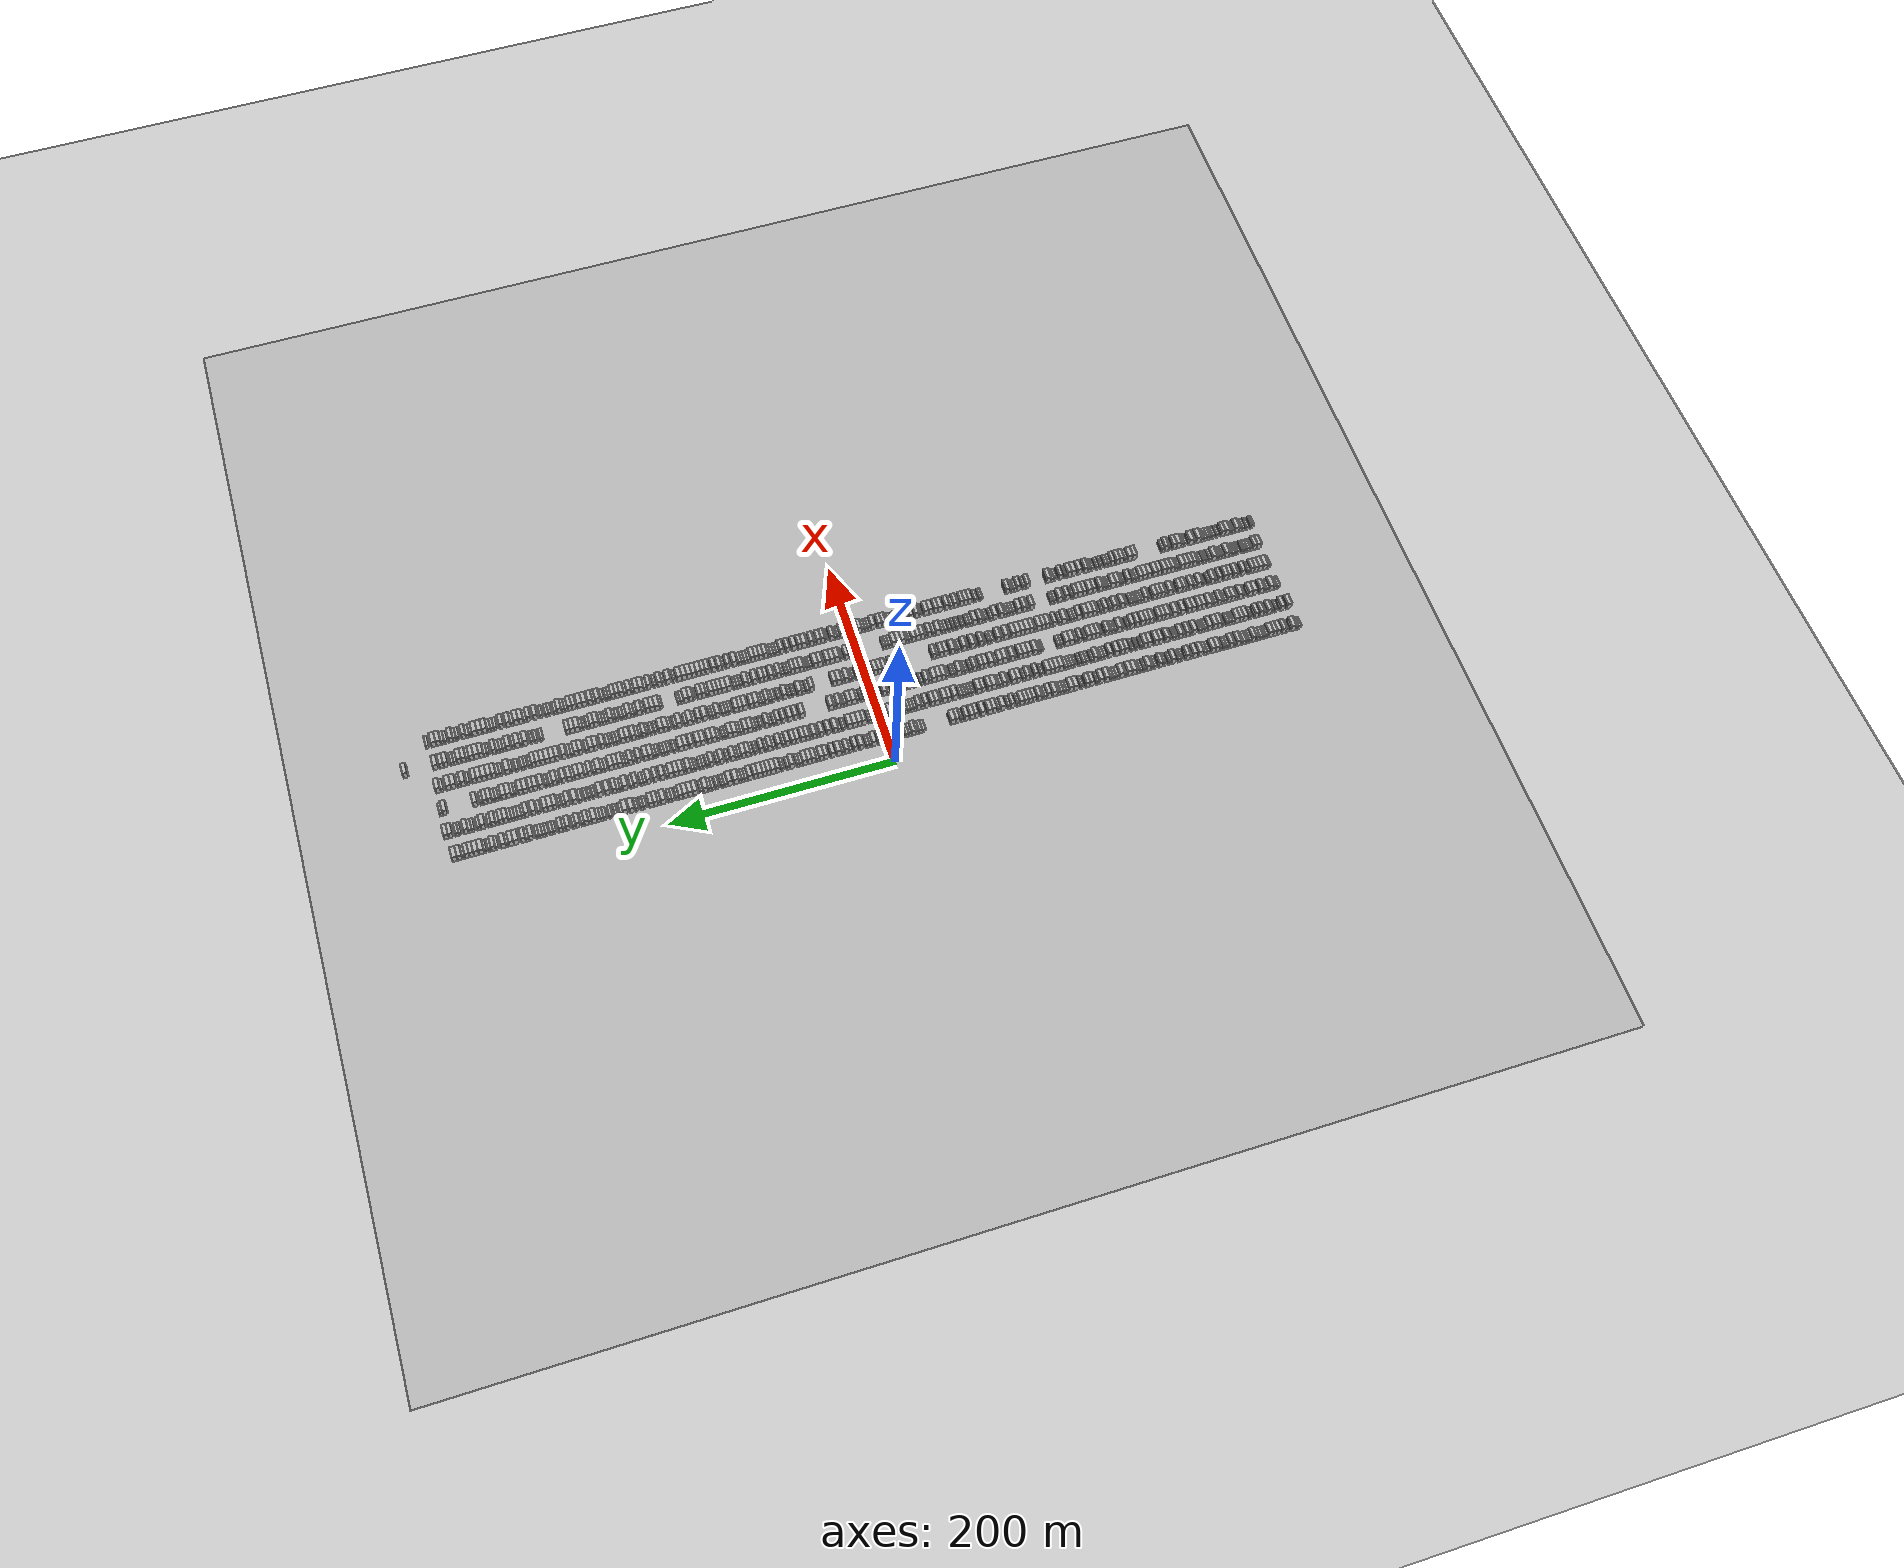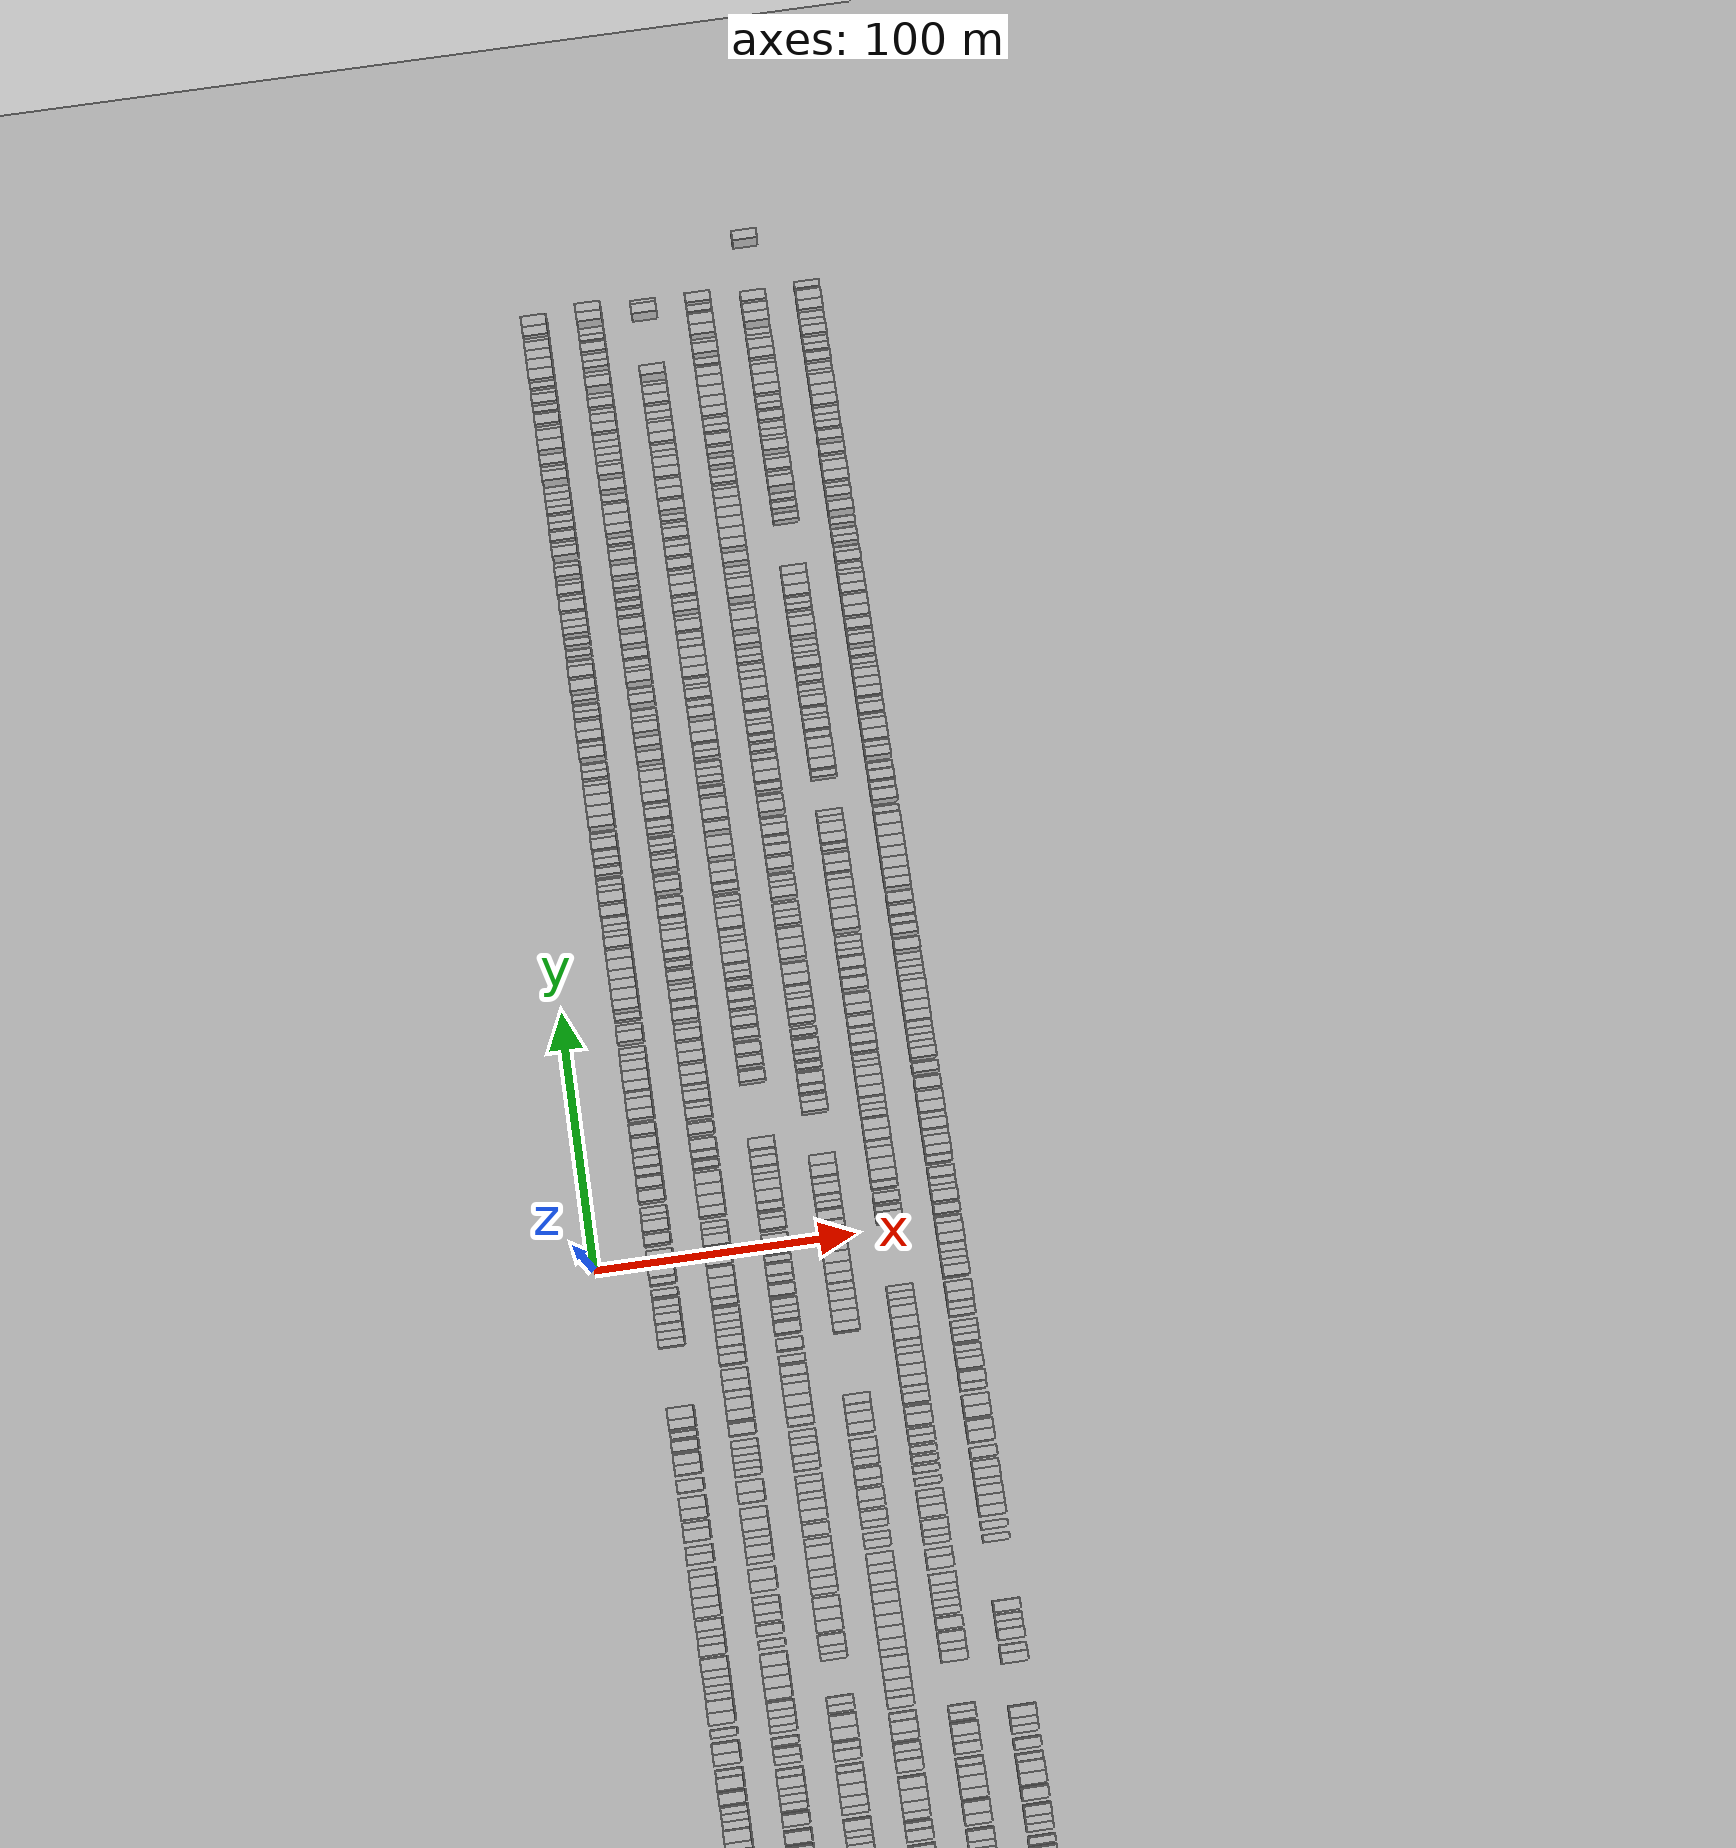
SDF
<?xml version="1.0" encoding="utf-8"?>

<sdf version="1.6">

   <world name="default">

      <gui fullscreen="0">

         <camera name="user_camera">

            <pose>-15 0 4.57585 0 0 0</pose>

            <view_controller>orbit</view_controller>

         </camera>

      </gui>

      <scene>

         <sky>

           <clouds>

             <speed>12</speed>

           </clouds>

         </sky>

         <ambient>0.4 0.4 0.4 1</ambient>

         <background>0.7 0.7 0.7 1</background>

         <shadows>1</shadows>

      </scene>

      <gravity>0 0 -9.8066</gravity>

      <magnetic_field>6e-06 2.3e-05 -4.2e-05</magnetic_field>

      <physics default="0" name="default_physics" type="ode">

         <ode>

            <solver>

               <type>quick</type>

               <iters>10</iters>

               <sor>1.0</sor>

               <use_dynamic_moi_rescaling>0</use_dynamic_moi_rescaling>

            </solver>

            <constraints>

               <cfm>0</cfm>

               <erp>0.2</erp>

               <contact_max_correcting_vel>100</contact_max_correcting_vel>

               <contact_surface_layer>0.001</contact_surface_layer>

            </constraints>

         </ode>

         <max_step_size>0.004</max_step_size>

         <real_time_factor>1</real_time_factor>

         <real_time_update_rate>250</real_time_update_rate>

      </physics>

      <light name="sun" type="directional">

         <cast_shadows>1</cast_shadows>

         <pose>0 0 10 0 0 0</pose>

         <diffuse>0.8 0.8 0.8 1</diffuse>

         <specular>0.2 0.2 0.2 1</specular>

         <attenuation>

            <range>1000</range>

            <constant>0.9</constant>

            <linear>0.01</linear>

            <quadratic>0.001</quadratic>

         </attenuation>

         <direction>-0.5 0.1 -0.9</direction>

      </light>

      <include>

         <name>ground_plane_1</name>

         <uri>model://HANNAS_ground_plane</uri>

         <pose>0 0 0  0 0 0</pose>

      </include>

      <include>

         <name>ground_plane_2</name>

         <uri>model://HANNAS_ground_plane</uri>

         <pose>100 0 0  0 0 0</pose>

      </include>

      <model name="building_1">

         <static>1</static>

         <pose frame="">25.0000 -378.6313 0 0.000000 0.000000 0.000000</pose>

         <link name="link">

            <pose frame="">0 0 3.00 0 0 0</pose>

            <collision name="collision">

               <geometry>

                  <box>

                     <size>10.0000 2.7375 6.0000</size>

                  </box>

               </geometry>

               <max_contacts>10</max_contacts>

               <surface>

                  <contact>

                     <ode/>

                  </contact>

                  <bounce/>

                  <friction>

                     <torsional>

                        <ode/>

                     </torsional>

                     <ode/>

                  </friction>

               </surface>

            </collision>

            <visual name="visual">

               <cast_shadows>0</cast_shadows>

               <geometry>

                  <box>

                     <size>10.0000 2.7375 6.0000</size>

                  </box>

               </geometry>

               <material>

                  <script>

                     <uri>model://HANNAS_wall/materials/scripts</uri>

                     <uri>model://HANNAS_wall/materials/textures</uri>

                     <name>vrc/HANNAS_wall</name>

                  </script>

               </material>

            </visual>

            <self_collide>0</self_collide>

            <enable_wind>0</enable_wind>

            <kinematic>0</kinematic>

         </link>

      </model>

      <model name="building_2">

         <static>1</static>

         <pose frame="">25.0000 -375.9943 0 0.000000 0.000000 0.000000</pose>

         <link name="link">

            <pose frame="">0 0 3.00 0 0 0</pose>

            <collision name="collision">

               <geometry>

                  <box>

                     <size>10.0000 2.5364 6.0000</size>

                  </box>

               </geometry>

               <max_contacts>10</max_contacts>

               <surface>

                  <contact>

                     <ode/>

                  </contact>

                  <bounce/>

                  <friction>

                     <torsional>

                        <ode/>

                     </torsional>

                     <ode/>

                  </friction>

               </surface>

            </collision>

            <visual name="visual">

               <cast_shadows>0</cast_shadows>

               <geometry>

                  <box>

                     <size>10.0000 2.5364 6.0000</size>

                  </box>

               </geometry>

               <material>

                  <script>

                     <uri>model://HANNAS_wall/materials/scripts</uri>

                     <uri>model://HANNAS_wall/materials/textures</uri>

                     <name>vrc/HANNAS_wall</name>

                  </script>

               </material>

            </visual>

            <self_collide>0</self_collide>

            <enable_wind>0</enable_wind>

            <kinematic>0</kinematic>

         </link>

      </model>

      <model name="building_3">

         <static>1</static>

         <pose frame="">25.0000 -372.6665 0 0.000000 0.000000 0.000000</pose>

         <link name="link">

            <pose frame="">0 0 4.50 0 0 0</pose>

            <collision name="collision">

               <geometry>

                  <box>

                     <size>10.0000 4.1193 9.0000</size>

                  </box>

               </geometry>

               <max_contacts>10</max_contacts>

               <surface>

                  <contact>

                     <ode/>

                  </contact>

                  <bounce/>

                  <friction>

                     <torsional>

                        <ode/>

                     </torsional>

                     <ode/>

                  </friction>

               </surface>

            </collision>

            <visual name="visual">

               <cast_shadows>0</cast_shadows>

               <geometry>

                  <box>

                     <size>10.0000 4.1193 9.0000</size>

                  </box>

               </geometry>

               <material>

                  <script>

                     <uri>model://HANNAS_wall/materials/scripts</uri>

                     <uri>model://HANNAS_wall/materials/textures</uri>

                     <name>vrc/HANNAS_wall</name>

                  </script>

               </material>

            </visual>

            <self_collide>0</self_collide>

            <enable_wind>0</enable_wind>

            <kinematic>0</kinematic>

         </link>

      </model>

      <model name="building_4">

         <static>1</static>

         <pose frame="">25.0000 -367.2124 0 0.000000 0.000000 0.000000</pose>

         <link name="link">

            <pose frame="">0 0 3.00 0 0 0</pose>

            <collision name="collision">

               <geometry>

                  <box>

                     <size>10.0000 2.7888 6.0000</size>

                  </box>

               </geometry>

               <max_contacts>10</max_contacts>

               <surface>

                  <contact>

                     <ode/>

                  </contact>

                  <bounce/>

                  <friction>

                     <torsional>

                        <ode/>

                     </torsional>

                     <ode/>

                  </friction>

               </surface>

            </collision>

            <visual name="visual">

               <cast_shadows>0</cast_shadows>

               <geometry>

                  <box>

                     <size>10.0000 2.7888 6.0000</size>

                  </box>

               </geometry>

               <material>

                  <script>

                     <uri>model://HANNAS_wall/materials/scripts</uri>

                     <uri>model://HANNAS_wall/materials/textures</uri>

                     <name>vrc/HANNAS_wall</name>

                  </script>

               </material>

            </visual>

            <self_collide>0</self_collide>

            <enable_wind>0</enable_wind>

            <kinematic>0</kinematic>

         </link>

      </model>

      <model name="building_5">

         <static>1</static>

         <pose frame="">25.0000 -363.9507 0 0.000000 0.000000 0.000000</pose>

         <link name="link">

            <pose frame="">0 0 4.50 0 0 0</pose>

            <collision name="collision">

               <geometry>

                  <box>

                     <size>10.0000 3.7346 9.0000</size>

                  </box>

               </geometry>

               <max_contacts>10</max_contacts>

               <surface>

                  <contact>

                     <ode/>

                  </contact>

                  <bounce/>

                  <friction>

                     <torsional>

                        <ode/>

                     </torsional>

                     <ode/>

                  </friction>

               </surface>

            </collision>

            <visual name="visual">

               <cast_shadows>0</cast_shadows>

               <geometry>

                  <box>

                     <size>10.0000 3.7346 9.0000</size>

                  </box>

               </geometry>

               <material>

                  <script>

                     <uri>model://HANNAS_wall/materials/scripts</uri>

                     <uri>model://HANNAS_wall/materials/textures</uri>

                     <name>vrc/HANNAS_wall</name>

                  </script>

               </material>

            </visual>

            <self_collide>0</self_collide>

            <enable_wind>0</enable_wind>

            <kinematic>0</kinematic>

         </link>

      </model>

      <model name="building_6">

         <static>1</static>

         <pose frame="">25.0000 -359.0992 0 0.000000 0.000000 0.000000</pose>

         <link name="link">

            <pose frame="">0 0 4.50 0 0 0</pose>

            <collision name="collision">

               <geometry>

                  <box>

                     <size>10.0000 3.9685 9.0000</size>

                  </box>

               </geometry>

               <max_contacts>10</max_contacts>

               <surface>

                  <contact>

                     <ode/>

                  </contact>

                  <bounce/>

                  <friction>

                     <torsional>

                        <ode/>

                     </torsional>

                     <ode/>

                  </friction>

               </surface>

            </collision>

            <visual name="visual">

               <cast_shadows>0</cast_shadows>

               <geometry>

                  <box>

                     <size>10.0000 3.9685 9.0000</size>

                  </box>

               </geometry>

               <material>

                  <script>

                     <uri>model://HANNAS_wall/materials/scripts</uri>

                     <uri>model://HANNAS_wall/materials/textures</uri>

                     <name>vrc/HANNAS_wall</name>

                  </script>

               </material>

            </visual>

            <self_collide>0</self_collide>

            <enable_wind>0</enable_wind>

            <kinematic>0</kinematic>

         </link>

      </model>

      <model name="building_7">

         <static>1</static>

         <pose frame="">25.0000 -355.3068 0 0.000000 0.000000 0.000000</pose>

         <link name="link">

            <pose frame="">0 0 4.50 0 0 0</pose>

            <collision name="collision">

               <geometry>

                  <box>

                     <size>10.0000 3.6162 9.0000</size>

                  </box>

               </geometry>

               <max_contacts>10</max_contacts>

               <surface>

                  <contact>

                     <ode/>

                  </contact>

                  <bounce/>

                  <friction>

                     <torsional>

                        <ode/>

                     </torsional>

                     <ode/>

                  </friction>

               </surface>

            </collision>

            <visual name="visual">

               <cast_shadows>0</cast_shadows>

               <geometry>

                  <box>

                     <size>10.0000 3.6162 9.0000</size>

                  </box>

               </geometry>

               <material>

                  <script>

                     <uri>model://HANNAS_wall/materials/scripts</uri>

                     <uri>model://HANNAS_wall/materials/textures</uri>

                     <name>vrc/HANNAS_wall</name>

                  </script>

               </material>

            </visual>

            <self_collide>0</self_collide>

            <enable_wind>0</enable_wind>

            <kinematic>0</kinematic>

         </link>

      </model>

      <model name="building_8">

         <static>1</static>

         <pose frame="">25.0000 -351.3034 0 0.000000 0.000000 0.000000</pose>

         <link name="link">

            <pose frame="">0 0 4.50 0 0 0</pose>

            <collision name="collision">

               <geometry>

                  <box>

                     <size>10.0000 4.3906 9.0000</size>

                  </box>

               </geometry>

               <max_contacts>10</max_contacts>

               <surface>

                  <contact>

                     <ode/>

                  </contact>

                  <bounce/>

                  <friction>

                     <torsional>

                        <ode/>

                     </torsional>

                     <ode/>

                  </friction>

               </surface>

            </collision>

            <visual name="visual">

               <cast_shadows>0</cast_shadows>

               <geometry>

                  <box>

                     <size>10.0000 4.3906 9.0000</size>

                  </box>

               </geometry>

               <material>

                  <script>

                     <uri>model://HANNAS_wall/materials/scripts</uri>

                     <uri>model://HANNAS_wall/materials/textures</uri>

                     <name>vrc/HANNAS_wall</name>

                  </script>

               </material>

            </visual>

            <self_collide>0</self_collide>

            <enable_wind>0</enable_wind>

            <kinematic>0</kinematic>

         </link>

      </model>

      <model name="building_9">

         <static>1</static>

         <pose frame="">25.0000 -347.7406 0 0.000000 0.000000 0.000000</pose>

         <link name="link">

            <pose frame="">0 0 3.00 0 0 0</pose>

            <collision name="collision">

               <geometry>

                  <box>

                     <size>10.0000 2.7350 6.0000</size>

                  </box>

               </geometry>

               <max_contacts>10</max_contacts>

               <surface>

                  <contact>

                     <ode/>

                  </contact>

                  <bounce/>

                  <friction>

                     <torsional>

                        <ode/>

                     </torsional>

                     <ode/>

                  </friction>

               </surface>

            </collision>

            <visual name="visual">

               <cast_shadows>0</cast_shadows>

               <geometry>

                  <box>

                     <size>10.0000 2.7350 6.0000</size>

                  </box>

               </geometry>

               <material>

                  <script>

                     <uri>model://HANNAS_wall/materials/scripts</uri>

                     <uri>model://HANNAS_wall/materials/textures</uri>

                     <name>vrc/HANNAS_wall</name>

                  </script>

               </material>

            </visual>

            <self_collide>0</self_collide>

            <enable_wind>0</enable_wind>

            <kinematic>0</kinematic>

         </link>

      </model>

      <model name="building_10">

         <static>1</static>

         <pose frame="">25.0000 -345.1540 0 0.000000 0.000000 0.000000</pose>

         <link name="link">

            <pose frame="">0 0 3.00 0 0 0</pose>

            <collision name="collision">

               <geometry>

                  <box>

                     <size>10.0000 2.4383 6.0000</size>

                  </box>

               </geometry>

               <max_contacts>10</max_contacts>

               <surface>

                  <contact>

                     <ode/>

                  </contact>

                  <bounce/>

                  <friction>

                     <torsional>

                        <ode/>

                     </torsional>

                     <ode/>

                  </friction>

               </surface>

            </collision>

            <visual name="visual">

               <cast_shadows>0</cast_shadows>

               <geometry>

                  <box>

                     <size>10.0000 2.4383 6.0000</size>

                  </box>

               </geometry>

               <material>

                  <script>

                     <uri>model://HANNAS_wall/materials/scripts</uri>

                     <uri>model://HANNAS_wall/materials/textures</uri>

                     <name>vrc/HANNAS_wall</name>

                  </script>

               </material>

            </visual>

            <self_collide>0</self_collide>

            <enable_wind>0</enable_wind>

            <kinematic>0</kinematic>

         </link>

      </model>

      <model name="building_11">

         <static>1</static>

         <pose frame="">25.0000 -342.4382 0 0.000000 0.000000 0.000000</pose>

         <link name="link">

            <pose frame="">0 0 3.00 0 0 0</pose>

            <collision name="collision">

               <geometry>

                  <box>

                     <size>10.0000 2.9933 6.0000</size>

                  </box>

               </geometry>

               <max_contacts>10</max_contacts>

               <surface>

                  <contact>

                     <ode/>

                  </contact>

                  <bounce/>

                  <friction>

                     <torsional>

                        <ode/>

                     </torsional>

                     <ode/>

                  </friction>

               </surface>

            </collision>

            <visual name="visual">

               <cast_shadows>0</cast_shadows>

               <geometry>

                  <box>

                     <size>10.0000 2.9933 6.0000</size>

                  </box>

               </geometry>

               <material>

                  <script>

                     <uri>model://HANNAS_wall/materials/scripts</uri>

                     <uri>model://HANNAS_wall/materials/textures</uri>

                     <name>vrc/HANNAS_wall</name>

                  </script>

               </material>

            </visual>

            <self_collide>0</self_collide>

            <enable_wind>0</enable_wind>

            <kinematic>0</kinematic>

         </link>

      </model>

      <model name="building_12">

         <static>1</static>

         <pose frame="">25.0000 -339.5825 0 0.000000 0.000000 0.000000</pose>

         <link name="link">

            <pose frame="">0 0 3.00 0 0 0</pose>

            <collision name="collision">

               <geometry>

                  <box>

                     <size>10.0000 2.7180 6.0000</size>

                  </box>

               </geometry>

               <max_contacts>10</max_contacts>

               <surface>

                  <contact>

                     <ode/>

                  </contact>

                  <bounce/>

                  <friction>

                     <torsional>

                        <ode/>

                     </torsional>

                     <ode/>

                  </friction>

               </surface>

            </collision>

            <visual name="visual">

               <cast_shadows>0</cast_shadows>

               <geometry>

                  <box>

                     <size>10.0000 2.7180 6.0000</size>

                  </box>

               </geometry>

               <material>

                  <script>

                     <uri>model://HANNAS_wall/materials/scripts</uri>

                     <uri>model://HANNAS_wall/materials/textures</uri>

                     <name>vrc/HANNAS_wall</name>

                  </script>

               </material>

            </visual>

            <self_collide>0</self_collide>

            <enable_wind>0</enable_wind>

            <kinematic>0</kinematic>

         </link>

      </model>

      <model name="building_13">

         <static>1</static>

         <pose frame="">25.0000 -335.3226 0 0.000000 0.000000 0.000000</pose>

         <link name="link">

            <pose frame="">0 0 4.50 0 0 0</pose>

            <collision name="collision">

               <geometry>

                  <box>

                     <size>10.0000 3.8017 9.0000</size>

                  </box>

               </geometry>

               <max_contacts>10</max_contacts>

               <surface>

                  <contact>

                     <ode/>

                  </contact>

                  <bounce/>

                  <friction>

                     <torsional>

                        <ode/>

                     </torsional>

                     <ode/>

                  </friction>

               </surface>

            </collision>

            <visual name="visual">

               <cast_shadows>0</cast_shadows>

               <geometry>

                  <box>

                     <size>10.0000 3.8017 9.0000</size>

                  </box>

               </geometry>

               <material>

                  <script>

                     <uri>model://HANNAS_wall/materials/scripts</uri>

                     <uri>model://HANNAS_wall/materials/textures</uri>

                     <name>vrc/HANNAS_wall</name>

                  </script>

               </material>

            </visual>

            <self_collide>0</self_collide>

            <enable_wind>0</enable_wind>

            <kinematic>0</kinematic>

         </link>

      </model>

      <model name="building_14">

         <static>1</static>

         <pose frame="">25.0000 -332.0354 0 0.000000 0.000000 0.000000</pose>

         <link name="link">

            <pose frame="">0 0 3.00 0 0 0</pose>

            <collision name="collision">

               <geometry>

                  <box>

                     <size>10.0000 2.7726 6.0000</size>

                  </box>

               </geometry>

               <max_contacts>10</max_contacts>

               <surface>

                  <contact>

                     <ode/>

                  </contact>

                  <bounce/>

                  <friction>

                     <torsional>

                        <ode/>

                     </torsional>

                     <ode/>

                  </friction>

               </surface>

            </collision>

            <visual name="visual">

               <cast_shadows>0</cast_shadows>

               <geometry>

                  <box>

                     <size>10.0000 2.7726 6.0000</size>

                  </box>

               </geometry>

               <material>

                  <script>

                     <uri>model://HANNAS_wall/materials/scripts</uri>

                     <uri>model://HANNAS_wall/materials/textures</uri>

                     <name>vrc/HANNAS_wall</name>

                  </script>

               </material>

            </visual>

            <self_collide>0</self_collide>

            <enable_wind>0</enable_wind>

            <kinematic>0</kinematic>

         </link>

      </model>

      <model name="building_15">

         <static>1</static>

         <pose frame="">25.0000 -329.4083 0 0.000000 0.000000 0.000000</pose>

         <link name="link">

            <pose frame="">0 0 3.00 0 0 0</pose>

            <collision name="collision">

               <geometry>

                  <box>

                     <size>10.0000 2.4817 6.0000</size>

                  </box>

               </geometry>

               <max_contacts>10</max_contacts>

               <surface>

                  <contact>

                     <ode/>

                  </contact>

                  <bounce/>

                  <friction>

                     <torsional>

                        <ode/>

                     </torsional>

                     <ode/>

                  </friction>

               </surface>

            </collision>

            <visual name="visual">

               <cast_shadows>0</cast_shadows>

               <geometry>

                  <box>

                     <size>10.0000 2.4817 6.0000</size>

                  </box>

               </geometry>

               <material>

                  <script>

                     <uri>model://HANNAS_wall/materials/scripts</uri>

                     <uri>model://HANNAS_wall/materials/textures</uri>

                     <name>vrc/HANNAS_wall</name>

                  </script>

               </material>

            </visual>

            <self_collide>0</self_collide>

            <enable_wind>0</enable_wind>

            <kinematic>0</kinematic>

         </link>

      </model>

      <model name="building_16">

         <static>1</static>

         <pose frame="">25.0000 -326.6706 0 0.000000 0.000000 0.000000</pose>

         <link name="link">

            <pose frame="">0 0 3.00 0 0 0</pose>

            <collision name="collision">

               <geometry>

                  <box>

                     <size>10.0000 2.9936 6.0000</size>

                  </box>

               </geometry>

               <max_contacts>10</max_contacts>

               <surface>

                  <contact>

                     <ode/>

                  </contact>

                  <bounce/>

                  <friction>

                     <torsional>

                        <ode/>

                     </torsional>

                     <ode/>

                  </friction>

               </surface>

            </collision>

            <visual name="visual">

               <cast_shadows>0</cast_shadows>

               <geometry>

                  <box>

                     <size>10.0000 2.9936 6.0000</size>

                  </box>

               </geometry>

               <material>

                  <script>

                     <uri>model://HANNAS_wall/materials/scripts</uri>

                     <uri>model://HANNAS_wall/materials/textures</uri>

                     <name>vrc/HANNAS_wall</name>

                  </script>

               </material>

            </visual>

            <self_collide>0</self_collide>

            <enable_wind>0</enable_wind>

            <kinematic>0</kinematic>

         </link>

      </model>

      <model name="building_17">

         <static>1</static>

         <pose frame="">25.0000 -323.9668 0 0.000000 0.000000 0.000000</pose>

         <link name="link">

            <pose frame="">0 0 3.00 0 0 0</pose>

            <collision name="collision">

               <geometry>

                  <box>

                     <size>10.0000 2.4140 6.0000</size>

                  </box>

               </geometry>

               <max_contacts>10</max_contacts>

               <surface>

                  <contact>

                     <ode/>

                  </contact>

                  <bounce/>

                  <friction>

                     <torsional>

                        <ode/>

                     </torsional>

                     <ode/>

                  </friction>

               </surface>

            </collision>

            <visual name="visual">

               <cast_shadows>0</cast_shadows>

               <geometry>

                  <box>

                     <size>10.0000 2.4140 6.0000</size>

                  </box>

               </geometry>

               <material>

                  <script>

                     <uri>model://HANNAS_wall/materials/scripts</uri>

                     <uri>model://HANNAS_wall/materials/textures</uri>

                     <name>vrc/HANNAS_wall</name>

                  </script>

               </material>

            </visual>

            <self_collide>0</self_collide>

            <enable_wind>0</enable_wind>

            <kinematic>0</kinematic>

         </link>

      </model>

      <model name="building_18">

         <static>1</static>

         <pose frame="">25.0000 -320.8582 0 0.000000 0.000000 0.000000</pose>

         <link name="link">

            <pose frame="">0 0 4.50 0 0 0</pose>

            <collision name="collision">

               <geometry>

                  <box>

                     <size>10.0000 3.8032 9.0000</size>

                  </box>

               </geometry>

               <max_contacts>10</max_contacts>

               <surface>

                  <contact>

                     <ode/>

                  </contact>

                  <bounce/>

                  <friction>

                     <torsional>

                        <ode/>

                     </torsional>

                     <ode/>

                  </friction>

               </surface>

            </collision>

            <visual name="visual">

               <cast_shadows>0</cast_shadows>

               <geometry>

                  <box>

                     <size>10.0000 3.8032 9.0000</size>

                  </box>

               </geometry>

               <material>

                  <script>

                     <uri>model://HANNAS_wall/materials/scripts</uri>

                     <uri>model://HANNAS_wall/materials/textures</uri>

                     <name>vrc/HANNAS_wall</name>

                  </script>

               </material>

            </visual>

            <self_collide>0</self_collide>

            <enable_wind>0</enable_wind>

            <kinematic>0</kinematic>

         </link>

      </model>

      <model name="building_19">

         <static>1</static>

         <pose frame="">25.0000 -317.5698 0 0.000000 0.000000 0.000000</pose>

         <link name="link">

            <pose frame="">0 0 3.00 0 0 0</pose>

            <collision name="collision">

               <geometry>

                  <box>

                     <size>10.0000 2.7736 6.0000</size>

                  </box>

               </geometry>

               <max_contacts>10</max_contacts>

               <surface>

                  <contact>

                     <ode/>

                  </contact>

                  <bounce/>

                  <friction>

                     <torsional>

                        <ode/>

                     </torsional>

                     <ode/>

                  </friction>

               </surface>

            </collision>

            <visual name="visual">

               <cast_shadows>0</cast_shadows>

               <geometry>

                  <box>

                     <size>10.0000 2.7736 6.0000</size>

                  </box>

               </geometry>

               <material>

                  <script>

                     <uri>model://HANNAS_wall/materials/scripts</uri>

                     <uri>model://HANNAS_wall/materials/textures</uri>

                     <name>vrc/HANNAS_wall</name>

                  </script>

               </material>

            </visual>

            <self_collide>0</self_collide>

            <enable_wind>0</enable_wind>

            <kinematic>0</kinematic>

         </link>

      </model>

      <model name="building_20">

         <static>1</static>

         <pose frame="">25.0000 -314.2303 0 0.000000 0.000000 0.000000</pose>

         <link name="link">

            <pose frame="">0 0 4.50 0 0 0</pose>

            <collision name="collision">

               <geometry>

                  <box>

                     <size>10.0000 3.9052 9.0000</size>

                  </box>

               </geometry>

               <max_contacts>10</max_contacts>

               <surface>

                  <contact>

                     <ode/>

                  </contact>

                  <bounce/>

                  <friction>

                     <torsional>

                        <ode/>

                     </torsional>

                     <ode/>

                  </friction>

               </surface>

            </collision>

            <visual name="visual">

               <cast_shadows>0</cast_shadows>

               <geometry>

                  <box>

                     <size>10.0000 3.9052 9.0000</size>

                  </box>

               </geometry>

               <material>

                  <script>

                     <uri>model://HANNAS_wall/materials/scripts</uri>

                     <uri>model://HANNAS_wall/materials/textures</uri>

                     <name>vrc/HANNAS_wall</name>

                  </script>

               </material>

            </visual>

            <self_collide>0</self_collide>

            <enable_wind>0</enable_wind>

            <kinematic>0</kinematic>

         </link>

      </model>

      <model name="building_21">

         <static>1</static>

         <pose frame="">25.0000 -310.8834 0 0.000000 0.000000 0.000000</pose>

         <link name="link">

            <pose frame="">0 0 3.00 0 0 0</pose>

            <collision name="collision">

               <geometry>

                  <box>

                     <size>10.0000 2.7887 6.0000</size>

                  </box>

               </geometry>

               <max_contacts>10</max_contacts>

               <surface>

                  <contact>

                     <ode/>

                  </contact>

                  <bounce/>

                  <friction>

                     <torsional>

                        <ode/>

                     </torsional>

                     <ode/>

                  </friction>

               </surface>

            </collision>

            <visual name="visual">

               <cast_shadows>0</cast_shadows>

               <geometry>

                  <box>

                     <size>10.0000 2.7887 6.0000</size>

                  </box>

               </geometry>

               <material>

                  <script>

                     <uri>model://HANNAS_wall/materials/scripts</uri>

                     <uri>model://HANNAS_wall/materials/textures</uri>

                     <name>vrc/HANNAS_wall</name>

                  </script>

               </material>

            </visual>

            <self_collide>0</self_collide>

            <enable_wind>0</enable_wind>

            <kinematic>0</kinematic>

         </link>

      </model>

      <model name="building_22">

         <static>1</static>

         <pose frame="">25.0000 -308.1758 0 0.000000 0.000000 0.000000</pose>

         <link name="link">

            <pose frame="">0 0 3.00 0 0 0</pose>

            <collision name="collision">

               <geometry>

                  <box>

                     <size>10.0000 2.6265 6.0000</size>

                  </box>

               </geometry>

               <max_contacts>10</max_contacts>

               <surface>

                  <contact>

                     <ode/>

                  </contact>

                  <bounce/>

                  <friction>

                     <torsional>

                        <ode/>

                     </torsional>

                     <ode/>

                  </friction>

               </surface>

            </collision>

            <visual name="visual">

               <cast_shadows>0</cast_shadows>

               <geometry>

                  <box>

                     <size>10.0000 2.6265 6.0000</size>

                  </box>

               </geometry>

               <material>

                  <script>

                     <uri>model://HANNAS_wall/materials/scripts</uri>

                     <uri>model://HANNAS_wall/materials/textures</uri>

                     <name>vrc/HANNAS_wall</name>

                  </script>

               </material>

            </visual>

            <self_collide>0</self_collide>

            <enable_wind>0</enable_wind>

            <kinematic>0</kinematic>

         </link>

      </model>

      <model name="building_23">

         <static>1</static>

         <pose frame="">25.0000 -304.6074 0 0.000000 0.000000 0.000000</pose>

         <link name="link">

            <pose frame="">0 0 3.00 0 0 0</pose>

            <collision name="collision">

               <geometry>

                  <box>

                     <size>10.0000 2.5102 6.0000</size>

                  </box>

               </geometry>

               <max_contacts>10</max_contacts>

               <surface>

                  <contact>

                     <ode/>

                  </contact>

                  <bounce/>

                  <friction>

                     <torsional>

                        <ode/>

                     </torsional>

                     <ode/>

                  </friction>

               </surface>

            </collision>

            <visual name="visual">

               <cast_shadows>0</cast_shadows>

               <geometry>

                  <box>

                     <size>10.0000 2.5102 6.0000</size>

                  </box>

               </geometry>

               <material>

                  <script>

                     <uri>model://HANNAS_wall/materials/scripts</uri>

                     <uri>model://HANNAS_wall/materials/textures</uri>

                     <name>vrc/HANNAS_wall</name>

                  </script>

               </material>

            </visual>

            <self_collide>0</self_collide>

            <enable_wind>0</enable_wind>

            <kinematic>0</kinematic>

         </link>

      </model>

      <model name="building_24">

         <static>1</static>

         <pose frame="">25.0000 -301.3201 0 0.000000 0.000000 0.000000</pose>

         <link name="link">

            <pose frame="">0 0 4.50 0 0 0</pose>

            <collision name="collision">

               <geometry>

                  <box>

                     <size>10.0000 4.0645 9.0000</size>

                  </box>

               </geometry>

               <max_contacts>10</max_contacts>

               <surface>

                  <contact>

                     <ode/>

                  </contact>

                  <bounce/>

                  <friction>

                     <torsional>

                        <ode/>

                     </torsional>

                     <ode/>

                  </friction>

               </surface>

            </collision>

            <visual name="visual">

               <cast_shadows>0</cast_shadows>

               <geometry>

                  <box>

                     <size>10.0000 4.0645 9.0000</size>

                  </box>

               </geometry>

               <material>

                  <script>

                     <uri>model://HANNAS_wall/materials/scripts</uri>

                     <uri>model://HANNAS_wall/materials/textures</uri>

                     <name>vrc/HANNAS_wall</name>

                  </script>

               </material>

            </visual>

            <self_collide>0</self_collide>

            <enable_wind>0</enable_wind>

            <kinematic>0</kinematic>

         </link>

      </model>

      <model name="building_25">

         <static>1</static>

         <pose frame="">25.0000 -297.1712 0 0.000000 0.000000 0.000000</pose>

         <link name="link">

            <pose frame="">0 0 4.50 0 0 0</pose>

            <collision name="collision">

               <geometry>

                  <box>

                     <size>10.0000 4.2333 9.0000</size>

                  </box>

               </geometry>

               <max_contacts>10</max_contacts>

               <surface>

                  <contact>

                     <ode/>

                  </contact>

                  <bounce/>

                  <friction>

                     <torsional>

                        <ode/>

                     </torsional>

                     <ode/>

                  </friction>

               </surface>

            </collision>

            <visual name="visual">

               <cast_shadows>0</cast_shadows>

               <geometry>

                  <box>

                     <size>10.0000 4.2333 9.0000</size>

                  </box>

               </geometry>

               <material>

                  <script>

                     <uri>model://HANNAS_wall/materials/scripts</uri>

                     <uri>model://HANNAS_wall/materials/textures</uri>

                     <name>vrc/HANNAS_wall</name>

                  </script>

               </material>

            </visual>

            <self_collide>0</self_collide>

            <enable_wind>0</enable_wind>

            <kinematic>0</kinematic>

         </link>

      </model>

      <model name="building_26">

         <static>1</static>

         <pose frame="">25.0000 -292.6259 0 0.000000 0.000000 0.000000</pose>

         <link name="link">

            <pose frame="">0 0 3.00 0 0 0</pose>

            <collision name="collision">

               <geometry>

                  <box>

                     <size>10.0000 2.8573 6.0000</size>

                  </box>

               </geometry>

               <max_contacts>10</max_contacts>

               <surface>

                  <contact>

                     <ode/>

                  </contact>

                  <bounce/>

                  <friction>

                     <torsional>

                        <ode/>

                     </torsional>

                     <ode/>

                  </friction>

               </surface>

            </collision>

            <visual name="visual">

               <cast_shadows>0</cast_shadows>

               <geometry>

                  <box>

                     <size>10.0000 2.8573 6.0000</size>

                  </box>

               </geometry>

               <material>

                  <script>

                     <uri>model://HANNAS_wall/materials/scripts</uri>

                     <uri>model://HANNAS_wall/materials/textures</uri>

                     <name>vrc/HANNAS_wall</name>

                  </script>

               </material>

            </visual>

            <self_collide>0</self_collide>

            <enable_wind>0</enable_wind>

            <kinematic>0</kinematic>

         </link>

      </model>

      <model name="building_27">

         <static>1</static>

         <pose frame="">25.0000 -289.8652 0 0.000000 0.000000 0.000000</pose>

         <link name="link">

            <pose frame="">0 0 3.00 0 0 0</pose>

            <collision name="collision">

               <geometry>

                  <box>

                     <size>10.0000 2.6640 6.0000</size>

                  </box>

               </geometry>

               <max_contacts>10</max_contacts>

               <surface>

                  <contact>

                     <ode/>

                  </contact>

                  <bounce/>

                  <friction>

                     <torsional>

                        <ode/>

                     </torsional>

                     <ode/>

                  </friction>

               </surface>

            </collision>

            <visual name="visual">

               <cast_shadows>0</cast_shadows>

               <geometry>

                  <box>

                     <size>10.0000 2.6640 6.0000</size>

                  </box>

               </geometry>

               <material>

                  <script>

                     <uri>model://HANNAS_wall/materials/scripts</uri>

                     <uri>model://HANNAS_wall/materials/textures</uri>

                     <name>vrc/HANNAS_wall</name>

                  </script>

               </material>

            </visual>

            <self_collide>0</self_collide>

            <enable_wind>0</enable_wind>

            <kinematic>0</kinematic>

         </link>

      </model>

      <model name="building_28">

         <static>1</static>

         <pose frame="">25.0000 -285.4052 0 0.000000 0.000000 0.000000</pose>

         <link name="link">

            <pose frame="">0 0 4.50 0 0 0</pose>

            <collision name="collision">

               <geometry>

                  <box>

                     <size>10.0000 4.2560 9.0000</size>

                  </box>

               </geometry>

               <max_contacts>10</max_contacts>

               <surface>

                  <contact>

                     <ode/>

                  </contact>

                  <bounce/>

                  <friction>

                     <torsional>

                        <ode/>

                     </torsional>

                     <ode/>

                  </friction>

               </surface>

            </collision>

            <visual name="visual">

               <cast_shadows>0</cast_shadows>

               <geometry>

                  <box>

                     <size>10.0000 4.2560 9.0000</size>

                  </box>

               </geometry>

               <material>

                  <script>

                     <uri>model://HANNAS_wall/materials/scripts</uri>

                     <uri>model://HANNAS_wall/materials/textures</uri>

                     <name>vrc/HANNAS_wall</name>

                  </script>

               </material>

            </visual>

            <self_collide>0</self_collide>

            <enable_wind>0</enable_wind>

            <kinematic>0</kinematic>

         </link>

      </model>

      <model name="building_29">

         <static>1</static>

         <pose frame="">25.0000 -280.1282 0 0.000000 0.000000 0.000000</pose>

         <link name="link">

            <pose frame="">0 0 4.50 0 0 0</pose>

            <collision name="collision">

               <geometry>

                  <box>

                     <size>10.0000 4.2981 9.0000</size>

                  </box>

               </geometry>

               <max_contacts>10</max_contacts>

               <surface>

                  <contact>

                     <ode/>

                  </contact>

                  <bounce/>

                  <friction>

                     <torsional>

                        <ode/>

                     </torsional>

                     <ode/>

                  </friction>

               </surface>

            </collision>

            <visual name="visual">

               <cast_shadows>0</cast_shadows>

               <geometry>

                  <box>

                     <size>10.0000 4.2981 9.0000</size>

                  </box>

               </geometry>

               <material>

                  <script>

                     <uri>model://HANNAS_wall/materials/scripts</uri>

                     <uri>model://HANNAS_wall/materials/textures</uri>

                     <name>vrc/HANNAS_wall</name>

                  </script>

               </material>

            </visual>

            <self_collide>0</self_collide>

            <enable_wind>0</enable_wind>

            <kinematic>0</kinematic>

         </link>

      </model>

      <model name="building_30">

         <static>1</static>

         <pose frame="">25.0000 -276.6986 0 0.000000 0.000000 0.000000</pose>

         <link name="link">

            <pose frame="">0 0 3.00 0 0 0</pose>

            <collision name="collision">

               <geometry>

                  <box>

                     <size>10.0000 2.5611 6.0000</size>

                  </box>

               </geometry>

               <max_contacts>10</max_contacts>

               <surface>

                  <contact>

                     <ode/>

                  </contact>

                  <bounce/>

                  <friction>

                     <torsional>

                        <ode/>

                     </torsional>

                     <ode/>

                  </friction>

               </surface>

            </collision>

            <visual name="visual">

               <cast_shadows>0</cast_shadows>

               <geometry>

                  <box>

                     <size>10.0000 2.5611 6.0000</size>

                  </box>

               </geometry>

               <material>

                  <script>

                     <uri>model://HANNAS_wall/materials/scripts</uri>

                     <uri>model://HANNAS_wall/materials/textures</uri>

                     <name>vrc/HANNAS_wall</name>

                  </script>

               </material>

            </visual>

            <self_collide>0</self_collide>

            <enable_wind>0</enable_wind>

            <kinematic>0</kinematic>

         </link>

      </model>

      <model name="building_31">

         <static>1</static>

         <pose frame="">25.0000 -273.4115 0 0.000000 0.000000 0.000000</pose>

         <link name="link">

            <pose frame="">0 0 4.50 0 0 0</pose>

            <collision name="collision">

               <geometry>

                  <box>

                     <size>10.0000 4.0132 9.0000</size>

                  </box>

               </geometry>

               <max_contacts>10</max_contacts>

               <surface>

                  <contact>

                     <ode/>

                  </contact>

                  <bounce/>

                  <friction>

                     <torsional>

                        <ode/>

                     </torsional>

                     <ode/>

                  </friction>

               </surface>

            </collision>

            <visual name="visual">

               <cast_shadows>0</cast_shadows>

               <geometry>

                  <box>

                     <size>10.0000 4.0132 9.0000</size>

                  </box>

               </geometry>

               <material>

                  <script>

                     <uri>model://HANNAS_wall/materials/scripts</uri>

                     <uri>model://HANNAS_wall/materials/textures</uri>

                     <name>vrc/HANNAS_wall</name>

                  </script>

               </material>

            </visual>

            <self_collide>0</self_collide>

            <enable_wind>0</enable_wind>

            <kinematic>0</kinematic>

         </link>

      </model>

      <model name="building_32">

         <static>1</static>

         <pose frame="">25.0000 -268.0833 0 0.000000 0.000000 0.000000</pose>

         <link name="link">

            <pose frame="">0 0 3.00 0 0 0</pose>

            <collision name="collision">

               <geometry>

                  <box>

                     <size>10.0000 2.6431 6.0000</size>

                  </box>

               </geometry>

               <max_contacts>10</max_contacts>

               <surface>

                  <contact>

                     <ode/>

                  </contact>

                  <bounce/>

                  <friction>

                     <torsional>

                        <ode/>

                     </torsional>

                     <ode/>

                  </friction>

               </surface>

            </collision>

            <visual name="visual">

               <cast_shadows>0</cast_shadows>

               <geometry>

                  <box>

                     <size>10.0000 2.6431 6.0000</size>

                  </box>

               </geometry>

               <material>

                  <script>

                     <uri>model://HANNAS_wall/materials/scripts</uri>

                     <uri>model://HANNAS_wall/materials/textures</uri>

                     <name>vrc/HANNAS_wall</name>

                  </script>

               </material>

            </visual>

            <self_collide>0</self_collide>

            <enable_wind>0</enable_wind>

            <kinematic>0</kinematic>

         </link>

      </model>

      <model name="building_33">

         <static>1</static>

         <pose frame="">25.0000 -265.5086 0 0.000000 0.000000 0.000000</pose>

         <link name="link">

            <pose frame="">0 0 3.00 0 0 0</pose>

            <collision name="collision">

               <geometry>

                  <box>

                     <size>10.0000 2.5064 6.0000</size>

                  </box>

               </geometry>

               <max_contacts>10</max_contacts>

               <surface>

                  <contact>

                     <ode/>

                  </contact>

                  <bounce/>

                  <friction>

                     <torsional>

                        <ode/>

                     </torsional>

                     <ode/>

                  </friction>

               </surface>

            </collision>

            <visual name="visual">

               <cast_shadows>0</cast_shadows>

               <geometry>

                  <box>

                     <size>10.0000 2.5064 6.0000</size>

                  </box>

               </geometry>

               <material>

                  <script>

                     <uri>model://HANNAS_wall/materials/scripts</uri>

                     <uri>model://HANNAS_wall/materials/textures</uri>

                     <name>vrc/HANNAS_wall</name>

                  </script>

               </material>

            </visual>

            <self_collide>0</self_collide>

            <enable_wind>0</enable_wind>

            <kinematic>0</kinematic>

         </link>

      </model>

      <model name="building_34">

         <static>1</static>

         <pose frame="">25.0000 -260.1540 0 0.000000 0.000000 0.000000</pose>

         <link name="link">

            <pose frame="">0 0 4.50 0 0 0</pose>

            <collision name="collision">

               <geometry>

                  <box>

                     <size>10.0000 4.2027 9.0000</size>

                  </box>

               </geometry>

               <max_contacts>10</max_contacts>

               <surface>

                  <contact>

                     <ode/>

                  </contact>

                  <bounce/>

                  <friction>

                     <torsional>

                        <ode/>

                     </torsional>

                     <ode/>

                  </friction>

               </surface>

            </collision>

            <visual name="visual">

               <cast_shadows>0</cast_shadows>

               <geometry>

                  <box>

                     <size>10.0000 4.2027 9.0000</size>

                  </box>

               </geometry>

               <material>

                  <script>

                     <uri>model://HANNAS_wall/materials/scripts</uri>

                     <uri>model://HANNAS_wall/materials/textures</uri>

                     <name>vrc/HANNAS_wall</name>

                  </script>

               </material>

            </visual>

            <self_collide>0</self_collide>

            <enable_wind>0</enable_wind>

            <kinematic>0</kinematic>

         </link>

      </model>

      <model name="building_35">

         <static>1</static>

         <pose frame="">25.0000 -256.7362 0 0.000000 0.000000 0.000000</pose>

         <link name="link">

            <pose frame="">0 0 3.00 0 0 0</pose>

            <collision name="collision">

               <geometry>

                  <box>

                     <size>10.0000 2.6328 6.0000</size>

                  </box>

               </geometry>

               <max_contacts>10</max_contacts>

               <surface>

                  <contact>

                     <ode/>

                  </contact>

                  <bounce/>

                  <friction>

                     <torsional>

                        <ode/>

                     </torsional>

                     <ode/>

                  </friction>

               </surface>

            </collision>

            <visual name="visual">

               <cast_shadows>0</cast_shadows>

               <geometry>

                  <box>

                     <size>10.0000 2.6328 6.0000</size>

                  </box>

               </geometry>

               <material>

                  <script>

                     <uri>model://HANNAS_wall/materials/scripts</uri>

                     <uri>model://HANNAS_wall/materials/textures</uri>

                     <name>vrc/HANNAS_wall</name>

                  </script>

               </material>

            </visual>

            <self_collide>0</self_collide>

            <enable_wind>0</enable_wind>

            <kinematic>0</kinematic>

         </link>

      </model>

      <model name="building_36">

         <static>1</static>

         <pose frame="">25.0000 -252.1950 0 0.000000 0.000000 0.000000</pose>

         <link name="link">

            <pose frame="">0 0 3.00 0 0 0</pose>

            <collision name="collision">

               <geometry>

                  <box>

                     <size>10.0000 2.4497 6.0000</size>

                  </box>

               </geometry>

               <max_contacts>10</max_contacts>

               <surface>

                  <contact>

                     <ode/>

                  </contact>

                  <bounce/>

                  <friction>

                     <torsional>

                        <ode/>

                     </torsional>

                     <ode/>

                  </friction>

               </surface>

            </collision>

            <visual name="visual">

               <cast_shadows>0</cast_shadows>

               <geometry>

                  <box>

                     <size>10.0000 2.4497 6.0000</size>

                  </box>

               </geometry>

               <material>

                  <script>

                     <uri>model://HANNAS_wall/materials/scripts</uri>

                     <uri>model://HANNAS_wall/materials/textures</uri>

                     <name>vrc/HANNAS_wall</name>

                  </script>

               </material>

            </visual>

            <self_collide>0</self_collide>

            <enable_wind>0</enable_wind>

            <kinematic>0</kinematic>

         </link>

      </model>

      <model name="building_37">

         <static>1</static>

         <pose frame="">25.0000 -248.1479 0 0.000000 0.000000 0.000000</pose>

         <link name="link">

            <pose frame="">0 0 4.50 0 0 0</pose>

            <collision name="collision">

               <geometry>

                  <box>

                     <size>10.0000 3.6445 9.0000</size>

                  </box>

               </geometry>

               <max_contacts>10</max_contacts>

               <surface>

                  <contact>

                     <ode/>

                  </contact>

                  <bounce/>

                  <friction>

                     <torsional>

                        <ode/>

                     </torsional>

                     <ode/>

                  </friction>

               </surface>

            </collision>

            <visual name="visual">

               <cast_shadows>0</cast_shadows>

               <geometry>

                  <box>

                     <size>10.0000 3.6445 9.0000</size>

                  </box>

               </geometry>

               <material>

                  <script>

                     <uri>model://HANNAS_wall/materials/scripts</uri>

                     <uri>model://HANNAS_wall/materials/textures</uri>

                     <name>vrc/HANNAS_wall</name>

                  </script>

               </material>

            </visual>

            <self_collide>0</self_collide>

            <enable_wind>0</enable_wind>

            <kinematic>0</kinematic>

         </link>

      </model>

      <model name="building_38">

         <static>1</static>

         <pose frame="">25.0000 -242.9295 0 0.000000 0.000000 0.000000</pose>

         <link name="link">

            <pose frame="">0 0 3.00 0 0 0</pose>

            <collision name="collision">

               <geometry>

                  <box>

                     <size>10.0000 2.7922 6.0000</size>

                  </box>

               </geometry>

               <max_contacts>10</max_contacts>

               <surface>

                  <contact>

                     <ode/>

                  </contact>

                  <bounce/>

                  <friction>

                     <torsional>

                        <ode/>

                     </torsional>

                     <ode/>

                  </friction>

               </surface>

            </collision>

            <visual name="visual">

               <cast_shadows>0</cast_shadows>

               <geometry>

                  <box>

                     <size>10.0000 2.7922 6.0000</size>

                  </box>

               </geometry>

               <material>

                  <script>

                     <uri>model://HANNAS_wall/materials/scripts</uri>

                     <uri>model://HANNAS_wall/materials/textures</uri>

                     <name>vrc/HANNAS_wall</name>

                  </script>

               </material>

            </visual>

            <self_collide>0</self_collide>

            <enable_wind>0</enable_wind>

            <kinematic>0</kinematic>

         </link>

      </model>

      <model name="building_39">

         <static>1</static>

         <pose frame="">25.0000 -240.2980 0 0.000000 0.000000 0.000000</pose>

         <link name="link">

            <pose frame="">0 0 3.00 0 0 0</pose>

            <collision name="collision">

               <geometry>

                  <box>

                     <size>10.0000 2.4707 6.0000</size>

                  </box>

               </geometry>

               <max_contacts>10</max_contacts>

               <surface>

                  <contact>

                     <ode/>

                  </contact>

                  <bounce/>

                  <friction>

                     <torsional>

                        <ode/>

                     </torsional>

                     <ode/>

                  </friction>

               </surface>

            </collision>

            <visual name="visual">

               <cast_shadows>0</cast_shadows>

               <geometry>

                  <box>

                     <size>10.0000 2.4707 6.0000</size>

                  </box>

               </geometry>

               <material>

                  <script>

                     <uri>model://HANNAS_wall/materials/scripts</uri>

                     <uri>model://HANNAS_wall/materials/textures</uri>

                     <name>vrc/HANNAS_wall</name>

                  </script>

               </material>

            </visual>

            <self_collide>0</self_collide>

            <enable_wind>0</enable_wind>

            <kinematic>0</kinematic>

         </link>

      </model>

      <model name="building_40">

         <static>1</static>

         <pose frame="">25.0000 -236.8393 0 0.000000 0.000000 0.000000</pose>

         <link name="link">

            <pose frame="">0 0 4.50 0 0 0</pose>

            <collision name="collision">

               <geometry>

                  <box>

                     <size>10.0000 4.4467 9.0000</size>

                  </box>

               </geometry>

               <max_contacts>10</max_contacts>

               <surface>

                  <contact>

                     <ode/>

                  </contact>

                  <bounce/>

                  <friction>

                     <torsional>

                        <ode/>

                     </torsional>

                     <ode/>

                  </friction>

               </surface>

            </collision>

            <visual name="visual">

               <cast_shadows>0</cast_shadows>

               <geometry>

                  <box>

                     <size>10.0000 4.4467 9.0000</size>

                  </box>

               </geometry>

               <material>

                  <script>

                     <uri>model://HANNAS_wall/materials/scripts</uri>

                     <uri>model://HANNAS_wall/materials/textures</uri>

                     <name>vrc/HANNAS_wall</name>

                  </script>

               </material>

            </visual>

            <self_collide>0</self_collide>

            <enable_wind>0</enable_wind>

            <kinematic>0</kinematic>

         </link>

      </model>

      <model name="building_41">

         <static>1</static>

         <pose frame="">25.0000 -233.4140 0 0.000000 0.000000 0.000000</pose>

         <link name="link">

            <pose frame="">0 0 3.00 0 0 0</pose>

            <collision name="collision">

               <geometry>

                  <box>

                     <size>10.0000 2.4038 6.0000</size>

                  </box>

               </geometry>

               <max_contacts>10</max_contacts>

               <surface>

                  <contact>

                     <ode/>

                  </contact>

                  <bounce/>

                  <friction>

                     <torsional>

                        <ode/>

                     </torsional>

                     <ode/>

                  </friction>

               </surface>

            </collision>

            <visual name="visual">

               <cast_shadows>0</cast_shadows>

               <geometry>

                  <box>

                     <size>10.0000 2.4038 6.0000</size>

                  </box>

               </geometry>

               <material>

                  <script>

                     <uri>model://HANNAS_wall/materials/scripts</uri>

                     <uri>model://HANNAS_wall/materials/textures</uri>

                     <name>vrc/HANNAS_wall</name>

                  </script>

               </material>

            </visual>

            <self_collide>0</self_collide>

            <enable_wind>0</enable_wind>

            <kinematic>0</kinematic>

         </link>

      </model>

      <model name="building_42">

         <static>1</static>

         <pose frame="">25.0000 -229.8659 0 0.000000 0.000000 0.000000</pose>

         <link name="link">

            <pose frame="">0 0 3.00 0 0 0</pose>

            <collision name="collision">

               <geometry>

                  <box>

                     <size>10.0000 2.6924 6.0000</size>

                  </box>

               </geometry>

               <max_contacts>10</max_contacts>

               <surface>

                  <contact>

                     <ode/>

                  </contact>

                  <bounce/>

                  <friction>

                     <torsional>

                        <ode/>

                     </torsional>

                     <ode/>

                  </friction>

               </surface>

            </collision>

            <visual name="visual">

               <cast_shadows>0</cast_shadows>

               <geometry>

                  <box>

                     <size>10.0000 2.6924 6.0000</size>

                  </box>

               </geometry>

               <material>

                  <script>

                     <uri>model://HANNAS_wall/materials/scripts</uri>

                     <uri>model://HANNAS_wall/materials/textures</uri>

                     <name>vrc/HANNAS_wall</name>

                  </script>

               </material>

            </visual>

            <self_collide>0</self_collide>

            <enable_wind>0</enable_wind>

            <kinematic>0</kinematic>

         </link>

      </model>

      <model name="building_43">

         <static>1</static>

         <pose frame="">25.0000 -227.1198 0 0.000000 0.000000 0.000000</pose>

         <link name="link">

            <pose frame="">0 0 3.00 0 0 0</pose>

            <collision name="collision">

               <geometry>

                  <box>

                     <size>10.0000 2.7999 6.0000</size>

                  </box>

               </geometry>

               <max_contacts>10</max_contacts>

               <surface>

                  <contact>

                     <ode/>

                  </contact>

                  <bounce/>

                  <friction>

                     <torsional>

                        <ode/>

                     </torsional>

                     <ode/>

                  </friction>

               </surface>

            </collision>

            <visual name="visual">

               <cast_shadows>0</cast_shadows>

               <geometry>

                  <box>

                     <size>10.0000 2.7999 6.0000</size>

                  </box>

               </geometry>

               <material>

                  <script>

                     <uri>model://HANNAS_wall/materials/scripts</uri>

                     <uri>model://HANNAS_wall/materials/textures</uri>

                     <name>vrc/HANNAS_wall</name>

                  </script>

               </material>

            </visual>

            <self_collide>0</self_collide>

            <enable_wind>0</enable_wind>

            <kinematic>0</kinematic>

         </link>

      </model>

      <model name="building_44">

         <static>1</static>

         <pose frame="">25.0000 -223.5872 0 0.000000 0.000000 0.000000</pose>

         <link name="link">

            <pose frame="">0 0 4.50 0 0 0</pose>

            <collision name="collision">

               <geometry>

                  <box>

                     <size>10.0000 4.2653 9.0000</size>

                  </box>

               </geometry>

               <max_contacts>10</max_contacts>

               <surface>

                  <contact>

                     <ode/>

                  </contact>

                  <bounce/>

                  <friction>

                     <torsional>

                        <ode/>

                     </torsional>

                     <ode/>

                  </friction>

               </surface>

            </collision>

            <visual name="visual">

               <cast_shadows>0</cast_shadows>

               <geometry>

                  <box>

                     <size>10.0000 4.2653 9.0000</size>

                  </box>

               </geometry>

               <material>

                  <script>

                     <uri>model://HANNAS_wall/materials/scripts</uri>

                     <uri>model://HANNAS_wall/materials/textures</uri>

                     <name>vrc/HANNAS_wall</name>

                  </script>

               </material>

            </visual>

            <self_collide>0</self_collide>

            <enable_wind>0</enable_wind>

            <kinematic>0</kinematic>

         </link>

      </model>

      <model name="building_45">

         <static>1</static>

         <pose frame="">25.0000 -219.2611 0 0.000000 0.000000 0.000000</pose>

         <link name="link">

            <pose frame="">0 0 4.50 0 0 0</pose>

            <collision name="collision">

               <geometry>

                  <box>

                     <size>10.0000 4.3868 9.0000</size>

                  </box>

               </geometry>

               <max_contacts>10</max_contacts>

               <surface>

                  <contact>

                     <ode/>

                  </contact>

                  <bounce/>

                  <friction>

                     <torsional>

                        <ode/>

                     </torsional>

                     <ode/>

                  </friction>

               </surface>

            </collision>

            <visual name="visual">

               <cast_shadows>0</cast_shadows>

               <geometry>

                  <box>

                     <size>10.0000 4.3868 9.0000</size>

                  </box>

               </geometry>

               <material>

                  <script>

                     <uri>model://HANNAS_wall/materials/scripts</uri>

                     <uri>model://HANNAS_wall/materials/textures</uri>

                     <name>vrc/HANNAS_wall</name>

                  </script>

               </material>

            </visual>

            <self_collide>0</self_collide>

            <enable_wind>0</enable_wind>

            <kinematic>0</kinematic>

         </link>

      </model>

      <model name="building_46">

         <static>1</static>

         <pose frame="">25.0000 -215.6398 0 0.000000 0.000000 0.000000</pose>

         <link name="link">

            <pose frame="">0 0 3.00 0 0 0</pose>

            <collision name="collision">

               <geometry>

                  <box>

                     <size>10.0000 2.8558 6.0000</size>

                  </box>

               </geometry>

               <max_contacts>10</max_contacts>

               <surface>

                  <contact>

                     <ode/>

                  </contact>

                  <bounce/>

                  <friction>

                     <torsional>

                        <ode/>

                     </torsional>

                     <ode/>

                  </friction>

               </surface>

            </collision>

            <visual name="visual">

               <cast_shadows>0</cast_shadows>

               <geometry>

                  <box>

                     <size>10.0000 2.8558 6.0000</size>

                  </box>

               </geometry>

               <material>

                  <script>

                     <uri>model://HANNAS_wall/materials/scripts</uri>

                     <uri>model://HANNAS_wall/materials/textures</uri>

                     <name>vrc/HANNAS_wall</name>

                  </script>

               </material>

            </visual>

            <self_collide>0</self_collide>

            <enable_wind>0</enable_wind>

            <kinematic>0</kinematic>

         </link>

      </model>

      <model name="building_47">

         <static>1</static>

         <pose frame="">25.0000 -211.9693 0 0.000000 0.000000 0.000000</pose>

         <link name="link">

            <pose frame="">0 0 4.50 0 0 0</pose>

            <collision name="collision">

               <geometry>

                  <box>

                     <size>10.0000 4.4852 9.0000</size>

                  </box>

               </geometry>

               <max_contacts>10</max_contacts>

               <surface>

                  <contact>

                     <ode/>

                  </contact>

                  <bounce/>

                  <friction>

                     <torsional>

                        <ode/>

                     </torsional>

                     <ode/>

                  </friction>

               </surface>

            </collision>

            <visual name="visual">

               <cast_shadows>0</cast_shadows>

               <geometry>

                  <box>

                     <size>10.0000 4.4852 9.0000</size>

                  </box>

               </geometry>

               <material>

                  <script>

                     <uri>model://HANNAS_wall/materials/scripts</uri>

                     <uri>model://HANNAS_wall/materials/textures</uri>

                     <name>vrc/HANNAS_wall</name>

                  </script>

               </material>

            </visual>

            <self_collide>0</self_collide>

            <enable_wind>0</enable_wind>

            <kinematic>0</kinematic>

         </link>

      </model>

      <model name="building_48">

         <static>1</static>

         <pose frame="">25.0000 -208.2581 0 0.000000 0.000000 0.000000</pose>

         <link name="link">

            <pose frame="">0 0 3.00 0 0 0</pose>

            <collision name="collision">

               <geometry>

                  <box>

                     <size>10.0000 2.9372 6.0000</size>

                  </box>

               </geometry>

               <max_contacts>10</max_contacts>

               <surface>

                  <contact>

                     <ode/>

                  </contact>

                  <bounce/>

                  <friction>

                     <torsional>

                        <ode/>

                     </torsional>

                     <ode/>

                  </friction>

               </surface>

            </collision>

            <visual name="visual">

               <cast_shadows>0</cast_shadows>

               <geometry>

                  <box>

                     <size>10.0000 2.9372 6.0000</size>

                  </box>

               </geometry>

               <material>

                  <script>

                     <uri>model://HANNAS_wall/materials/scripts</uri>

                     <uri>model://HANNAS_wall/materials/textures</uri>

                     <name>vrc/HANNAS_wall</name>

                  </script>

               </material>

            </visual>

            <self_collide>0</self_collide>

            <enable_wind>0</enable_wind>

            <kinematic>0</kinematic>

         </link>

      </model>

      <model name="building_49">

         <static>1</static>

         <pose frame="">25.0000 -205.4530 0 0.000000 0.000000 0.000000</pose>

         <link name="link">

            <pose frame="">0 0 3.00 0 0 0</pose>

            <collision name="collision">

               <geometry>

                  <box>

                     <size>10.0000 2.6730 6.0000</size>

                  </box>

               </geometry>

               <max_contacts>10</max_contacts>

               <surface>

                  <contact>

                     <ode/>

                  </contact>

                  <bounce/>

                  <friction>

                     <torsional>

                        <ode/>

                     </torsional>

                     <ode/>

                  </friction>

               </surface>

            </collision>

            <visual name="visual">

               <cast_shadows>0</cast_shadows>

               <geometry>

                  <box>

                     <size>10.0000 2.6730 6.0000</size>

                  </box>

               </geometry>

               <material>

                  <script>

                     <uri>model://HANNAS_wall/materials/scripts</uri>

                     <uri>model://HANNAS_wall/materials/textures</uri>

                     <name>vrc/HANNAS_wall</name>

                  </script>

               </material>

            </visual>

            <self_collide>0</self_collide>

            <enable_wind>0</enable_wind>

            <kinematic>0</kinematic>

         </link>

      </model>

      <model name="building_50">

         <static>1</static>

         <pose frame="">25.0000 -202.8707 0 0.000000 0.000000 0.000000</pose>

         <link name="link">

            <pose frame="">0 0 3.00 0 0 0</pose>

            <collision name="collision">

               <geometry>

                  <box>

                     <size>10.0000 2.4918 6.0000</size>

                  </box>

               </geometry>

               <max_contacts>10</max_contacts>

               <surface>

                  <contact>

                     <ode/>

                  </contact>

                  <bounce/>

                  <friction>

                     <torsional>

                        <ode/>

                     </torsional>

                     <ode/>

                  </friction>

               </surface>

            </collision>

            <visual name="visual">

               <cast_shadows>0</cast_shadows>

               <geometry>

                  <box>

                     <size>10.0000 2.4918 6.0000</size>

                  </box>

               </geometry>

               <material>

                  <script>

                     <uri>model://HANNAS_wall/materials/scripts</uri>

                     <uri>model://HANNAS_wall/materials/textures</uri>

                     <name>vrc/HANNAS_wall</name>

                  </script>

               </material>

            </visual>

            <self_collide>0</self_collide>

            <enable_wind>0</enable_wind>

            <kinematic>0</kinematic>

         </link>

      </model>

      <model name="building_51">

         <static>1</static>

         <pose frame="">25.0000 -198.5113 0 0.000000 0.000000 0.000000</pose>

         <link name="link">

            <pose frame="">0 0 4.50 0 0 0</pose>

            <collision name="collision">

               <geometry>

                  <box>

                     <size>10.0000 4.2268 9.0000</size>

                  </box>

               </geometry>

               <max_contacts>10</max_contacts>

               <surface>

                  <contact>

                     <ode/>

                  </contact>

                  <bounce/>

                  <friction>

                     <torsional>

                        <ode/>

                     </torsional>

                     <ode/>

                  </friction>

               </surface>

            </collision>

            <visual name="visual">

               <cast_shadows>0</cast_shadows>

               <geometry>

                  <box>

                     <size>10.0000 4.2268 9.0000</size>

                  </box>

               </geometry>

               <material>

                  <script>

                     <uri>model://HANNAS_wall/materials/scripts</uri>

                     <uri>model://HANNAS_wall/materials/textures</uri>

                     <name>vrc/HANNAS_wall</name>

                  </script>

               </material>

            </visual>

            <self_collide>0</self_collide>

            <enable_wind>0</enable_wind>

            <kinematic>0</kinematic>

         </link>

      </model>

      <model name="building_52">

         <static>1</static>

         <pose frame="">25.0000 -193.1591 0 0.000000 0.000000 0.000000</pose>

         <link name="link">

            <pose frame="">0 0 4.50 0 0 0</pose>

            <collision name="collision">

               <geometry>

                  <box>

                     <size>10.0000 4.4777 9.0000</size>

                  </box>

               </geometry>

               <max_contacts>10</max_contacts>

               <surface>

                  <contact>

                     <ode/>

                  </contact>

                  <bounce/>

                  <friction>

                     <torsional>

                        <ode/>

                     </torsional>

                     <ode/>

                  </friction>

               </surface>

            </collision>

            <visual name="visual">

               <cast_shadows>0</cast_shadows>

               <geometry>

                  <box>

                     <size>10.0000 4.4777 9.0000</size>

                  </box>

               </geometry>

               <material>

                  <script>

                     <uri>model://HANNAS_wall/materials/scripts</uri>

                     <uri>model://HANNAS_wall/materials/textures</uri>

                     <name>vrc/HANNAS_wall</name>

                  </script>

               </material>

            </visual>

            <self_collide>0</self_collide>

            <enable_wind>0</enable_wind>

            <kinematic>0</kinematic>

         </link>

      </model>

      <model name="building_53">

         <static>1</static>

         <pose frame="">25.0000 -189.6882 0 0.000000 0.000000 0.000000</pose>

         <link name="link">

            <pose frame="">0 0 3.00 0 0 0</pose>

            <collision name="collision">

               <geometry>

                  <box>

                     <size>10.0000 2.4640 6.0000</size>

                  </box>

               </geometry>

               <max_contacts>10</max_contacts>

               <surface>

                  <contact>

                     <ode/>

                  </contact>

                  <bounce/>

                  <friction>

                     <torsional>

                        <ode/>

                     </torsional>

                     <ode/>

                  </friction>

               </surface>

            </collision>

            <visual name="visual">

               <cast_shadows>0</cast_shadows>

               <geometry>

                  <box>

                     <size>10.0000 2.4640 6.0000</size>

                  </box>

               </geometry>

               <material>

                  <script>

                     <uri>model://HANNAS_wall/materials/scripts</uri>

                     <uri>model://HANNAS_wall/materials/textures</uri>

                     <name>vrc/HANNAS_wall</name>

                  </script>

               </material>

            </visual>

            <self_collide>0</self_collide>

            <enable_wind>0</enable_wind>

            <kinematic>0</kinematic>

         </link>

      </model>

      <model name="building_54">

         <static>1</static>

         <pose frame="">25.0000 -184.4387 0 0.000000 0.000000 0.000000</pose>

         <link name="link">

            <pose frame="">0 0 4.50 0 0 0</pose>

            <collision name="collision">

               <geometry>

                  <box>

                     <size>10.0000 4.0350 9.0000</size>

                  </box>

               </geometry>

               <max_contacts>10</max_contacts>

               <surface>

                  <contact>

                     <ode/>

                  </contact>

                  <bounce/>

                  <friction>

                     <torsional>

                        <ode/>

                     </torsional>

                     <ode/>

                  </friction>

               </surface>

            </collision>

            <visual name="visual">

               <cast_shadows>0</cast_shadows>

               <geometry>

                  <box>

                     <size>10.0000 4.0350 9.0000</size>

                  </box>

               </geometry>

               <material>

                  <script>

                     <uri>model://HANNAS_wall/materials/scripts</uri>

                     <uri>model://HANNAS_wall/materials/textures</uri>

                     <name>vrc/HANNAS_wall</name>

                  </script>

               </material>

            </visual>

            <self_collide>0</self_collide>

            <enable_wind>0</enable_wind>

            <kinematic>0</kinematic>

         </link>

      </model>

      <model name="building_55">

         <static>1</static>

         <pose frame="">25.0000 -180.5391 0 0.000000 0.000000 0.000000</pose>

         <link name="link">

            <pose frame="">0 0 4.50 0 0 0</pose>

            <collision name="collision">

               <geometry>

                  <box>

                     <size>10.0000 3.7642 9.0000</size>

                  </box>

               </geometry>

               <max_contacts>10</max_contacts>

               <surface>

                  <contact>

                     <ode/>

                  </contact>

                  <bounce/>

                  <friction>

                     <torsional>

                        <ode/>

                     </torsional>

                     <ode/>

                  </friction>

               </surface>

            </collision>

            <visual name="visual">

               <cast_shadows>0</cast_shadows>

               <geometry>

                  <box>

                     <size>10.0000 3.7642 9.0000</size>

                  </box>

               </geometry>

               <material>

                  <script>

                     <uri>model://HANNAS_wall/materials/scripts</uri>

                     <uri>model://HANNAS_wall/materials/textures</uri>

                     <name>vrc/HANNAS_wall</name>

                  </script>

               </material>

            </visual>

            <self_collide>0</self_collide>

            <enable_wind>0</enable_wind>

            <kinematic>0</kinematic>

         </link>

      </model>

      <model name="building_56">

         <static>1</static>

         <pose frame="">25.0000 -175.2865 0 0.000000 0.000000 0.000000</pose>

         <link name="link">

            <pose frame="">0 0 3.00 0 0 0</pose>

            <collision name="collision">

               <geometry>

                  <box>

                     <size>10.0000 2.7409 6.0000</size>

                  </box>

               </geometry>

               <max_contacts>10</max_contacts>

               <surface>

                  <contact>

                     <ode/>

                  </contact>

                  <bounce/>

                  <friction>

                     <torsional>

                        <ode/>

                     </torsional>

                     <ode/>

                  </friction>

               </surface>

            </collision>

            <visual name="visual">

               <cast_shadows>0</cast_shadows>

               <geometry>

                  <box>

                     <size>10.0000 2.7409 6.0000</size>

                  </box>

               </geometry>

               <material>

                  <script>

                     <uri>model://HANNAS_wall/materials/scripts</uri>

                     <uri>model://HANNAS_wall/materials/textures</uri>

                     <name>vrc/HANNAS_wall</name>

                  </script>

               </material>

            </visual>

            <self_collide>0</self_collide>

            <enable_wind>0</enable_wind>

            <kinematic>0</kinematic>

         </link>

      </model>

      <model name="building_57">

         <static>1</static>

         <pose frame="">25.0000 -169.7034 0 0.000000 0.000000 0.000000</pose>

         <link name="link">

            <pose frame="">0 0 4.50 0 0 0</pose>

            <collision name="collision">

               <geometry>

                  <box>

                     <size>10.0000 4.4254 9.0000</size>

                  </box>

               </geometry>

               <max_contacts>10</max_contacts>

               <surface>

                  <contact>

                     <ode/>

                  </contact>

                  <bounce/>

                  <friction>

                     <torsional>

                        <ode/>

                     </torsional>

                     <ode/>

                  </friction>

               </surface>

            </collision>

            <visual name="visual">

               <cast_shadows>0</cast_shadows>

               <geometry>

                  <box>

                     <size>10.0000 4.4254 9.0000</size>

                  </box>

               </geometry>

               <material>

                  <script>

                     <uri>model://HANNAS_wall/materials/scripts</uri>

                     <uri>model://HANNAS_wall/materials/textures</uri>

                     <name>vrc/HANNAS_wall</name>

                  </script>

               </material>

            </visual>

            <self_collide>0</self_collide>

            <enable_wind>0</enable_wind>

            <kinematic>0</kinematic>

         </link>

      </model>

      <model name="building_58">

         <static>1</static>

         <pose frame="">25.0000 -165.3621 0 0.000000 0.000000 0.000000</pose>

         <link name="link">

            <pose frame="">0 0 4.50 0 0 0</pose>

            <collision name="collision">

               <geometry>

                  <box>

                     <size>10.0000 4.2572 9.0000</size>

                  </box>

               </geometry>

               <max_contacts>10</max_contacts>

               <surface>

                  <contact>

                     <ode/>

                  </contact>

                  <bounce/>

                  <friction>

                     <torsional>

                        <ode/>

                     </torsional>

                     <ode/>

                  </friction>

               </surface>

            </collision>

            <visual name="visual">

               <cast_shadows>0</cast_shadows>

               <geometry>

                  <box>

                     <size>10.0000 4.2572 9.0000</size>

                  </box>

               </geometry>

               <material>

                  <script>

                     <uri>model://HANNAS_wall/materials/scripts</uri>

                     <uri>model://HANNAS_wall/materials/textures</uri>

                     <name>vrc/HANNAS_wall</name>

                  </script>

               </material>

            </visual>

            <self_collide>0</self_collide>

            <enable_wind>0</enable_wind>

            <kinematic>0</kinematic>

         </link>

      </model>

      <model name="building_59">

         <static>1</static>

         <pose frame="">25.0000 -161.8809 0 0.000000 0.000000 0.000000</pose>

         <link name="link">

            <pose frame="">0 0 3.00 0 0 0</pose>

            <collision name="collision">

               <geometry>

                  <box>

                     <size>10.0000 2.7051 6.0000</size>

                  </box>

               </geometry>

               <max_contacts>10</max_contacts>

               <surface>

                  <contact>

                     <ode/>

                  </contact>

                  <bounce/>

                  <friction>

                     <torsional>

                        <ode/>

                     </torsional>

                     <ode/>

                  </friction>

               </surface>

            </collision>

            <visual name="visual">

               <cast_shadows>0</cast_shadows>

               <geometry>

                  <box>

                     <size>10.0000 2.7051 6.0000</size>

                  </box>

               </geometry>

               <material>

                  <script>

                     <uri>model://HANNAS_wall/materials/scripts</uri>

                     <uri>model://HANNAS_wall/materials/textures</uri>

                     <name>vrc/HANNAS_wall</name>

                  </script>

               </material>

            </visual>

            <self_collide>0</self_collide>

            <enable_wind>0</enable_wind>

            <kinematic>0</kinematic>

         </link>

      </model>

      <model name="building_60">

         <static>1</static>

         <pose frame="">25.0000 -159.2859 0 0.000000 0.000000 0.000000</pose>

         <link name="link">

            <pose frame="">0 0 3.00 0 0 0</pose>

            <collision name="collision">

               <geometry>

                  <box>

                     <size>10.0000 2.4850 6.0000</size>

                  </box>

               </geometry>

               <max_contacts>10</max_contacts>

               <surface>

                  <contact>

                     <ode/>

                  </contact>

                  <bounce/>

                  <friction>

                     <torsional>

                        <ode/>

                     </torsional>

                     <ode/>

                  </friction>

               </surface>

            </collision>

            <visual name="visual">

               <cast_shadows>0</cast_shadows>

               <geometry>

                  <box>

                     <size>10.0000 2.4850 6.0000</size>

                  </box>

               </geometry>

               <material>

                  <script>

                     <uri>model://HANNAS_wall/materials/scripts</uri>

                     <uri>model://HANNAS_wall/materials/textures</uri>

                     <name>vrc/HANNAS_wall</name>

                  </script>

               </material>

            </visual>

            <self_collide>0</self_collide>

            <enable_wind>0</enable_wind>

            <kinematic>0</kinematic>

         </link>

      </model>

      <model name="building_61">

         <static>1</static>

         <pose frame="">25.0000 -156.6083 0 0.000000 0.000000 0.000000</pose>

         <link name="link">

            <pose frame="">0 0 3.00 0 0 0</pose>

            <collision name="collision">

               <geometry>

                  <box>

                     <size>10.0000 2.8703 6.0000</size>

                  </box>

               </geometry>

               <max_contacts>10</max_contacts>

               <surface>

                  <contact>

                     <ode/>

                  </contact>

                  <bounce/>

                  <friction>

                     <torsional>

                        <ode/>

                     </torsional>

                     <ode/>

                  </friction>

               </surface>

            </collision>

            <visual name="visual">

               <cast_shadows>0</cast_shadows>

               <geometry>

                  <box>

                     <size>10.0000 2.8703 6.0000</size>

                  </box>

               </geometry>

               <material>

                  <script>

                     <uri>model://HANNAS_wall/materials/scripts</uri>

                     <uri>model://HANNAS_wall/materials/textures</uri>

                     <name>vrc/HANNAS_wall</name>

                  </script>

               </material>

            </visual>

            <self_collide>0</self_collide>

            <enable_wind>0</enable_wind>

            <kinematic>0</kinematic>

         </link>

      </model>

      <model name="building_62">

         <static>1</static>

         <pose frame="">25.0000 -153.7701 0 0.000000 0.000000 0.000000</pose>

         <link name="link">

            <pose frame="">0 0 3.00 0 0 0</pose>

            <collision name="collision">

               <geometry>

                  <box>

                     <size>10.0000 2.8061 6.0000</size>

                  </box>

               </geometry>

               <max_contacts>10</max_contacts>

               <surface>

                  <contact>

                     <ode/>

                  </contact>

                  <bounce/>

                  <friction>

                     <torsional>

                        <ode/>

                     </torsional>

                     <ode/>

                  </friction>

               </surface>

            </collision>

            <visual name="visual">

               <cast_shadows>0</cast_shadows>

               <geometry>

                  <box>

                     <size>10.0000 2.8061 6.0000</size>

                  </box>

               </geometry>

               <material>

                  <script>

                     <uri>model://HANNAS_wall/materials/scripts</uri>

                     <uri>model://HANNAS_wall/materials/textures</uri>

                     <name>vrc/HANNAS_wall</name>

                  </script>

               </material>

            </visual>

            <self_collide>0</self_collide>

            <enable_wind>0</enable_wind>

            <kinematic>0</kinematic>

         </link>

      </model>

      <model name="building_63">

         <static>1</static>

         <pose frame="">25.0000 -150.1823 0 0.000000 0.000000 0.000000</pose>

         <link name="link">

            <pose frame="">0 0 4.50 0 0 0</pose>

            <collision name="collision">

               <geometry>

                  <box>

                     <size>10.0000 4.3694 9.0000</size>

                  </box>

               </geometry>

               <max_contacts>10</max_contacts>

               <surface>

                  <contact>

                     <ode/>

                  </contact>

                  <bounce/>

                  <friction>

                     <torsional>

                        <ode/>

                     </torsional>

                     <ode/>

                  </friction>

               </surface>

            </collision>

            <visual name="visual">

               <cast_shadows>0</cast_shadows>

               <geometry>

                  <box>

                     <size>10.0000 4.3694 9.0000</size>

                  </box>

               </geometry>

               <material>

                  <script>

                     <uri>model://HANNAS_wall/materials/scripts</uri>

                     <uri>model://HANNAS_wall/materials/textures</uri>

                     <name>vrc/HANNAS_wall</name>

                  </script>

               </material>

            </visual>

            <self_collide>0</self_collide>

            <enable_wind>0</enable_wind>

            <kinematic>0</kinematic>

         </link>

      </model>

      <model name="building_64">

         <static>1</static>

         <pose frame="">25.0000 -145.0447 0 0.000000 0.000000 0.000000</pose>

         <link name="link">

            <pose frame="">0 0 4.50 0 0 0</pose>

            <collision name="collision">

               <geometry>

                  <box>

                     <size>10.0000 3.9057 9.0000</size>

                  </box>

               </geometry>

               <max_contacts>10</max_contacts>

               <surface>

                  <contact>

                     <ode/>

                  </contact>

                  <bounce/>

                  <friction>

                     <torsional>

                        <ode/>

                     </torsional>

                     <ode/>

                  </friction>

               </surface>

            </collision>

            <visual name="visual">

               <cast_shadows>0</cast_shadows>

               <geometry>

                  <box>

                     <size>10.0000 3.9057 9.0000</size>

                  </box>

               </geometry>

               <material>

                  <script>

                     <uri>model://HANNAS_wall/materials/scripts</uri>

                     <uri>model://HANNAS_wall/materials/textures</uri>

                     <name>vrc/HANNAS_wall</name>

                  </script>

               </material>

            </visual>

            <self_collide>0</self_collide>

            <enable_wind>0</enable_wind>

            <kinematic>0</kinematic>

         </link>

      </model>

      <model name="building_65">

         <static>1</static>

         <pose frame="">25.0000 -141.7154 0 0.000000 0.000000 0.000000</pose>

         <link name="link">

            <pose frame="">0 0 3.00 0 0 0</pose>

            <collision name="collision">

               <geometry>

                  <box>

                     <size>10.0000 2.7529 6.0000</size>

                  </box>

               </geometry>

               <max_contacts>10</max_contacts>

               <surface>

                  <contact>

                     <ode/>

                  </contact>

                  <bounce/>

                  <friction>

                     <torsional>

                        <ode/>

                     </torsional>

                     <ode/>

                  </friction>

               </surface>

            </collision>

            <visual name="visual">

               <cast_shadows>0</cast_shadows>

               <geometry>

                  <box>

                     <size>10.0000 2.7529 6.0000</size>

                  </box>

               </geometry>

               <material>

                  <script>

                     <uri>model://HANNAS_wall/materials/scripts</uri>

                     <uri>model://HANNAS_wall/materials/textures</uri>

                     <name>vrc/HANNAS_wall</name>

                  </script>

               </material>

            </visual>

            <self_collide>0</self_collide>

            <enable_wind>0</enable_wind>

            <kinematic>0</kinematic>

         </link>

      </model>

      <model name="building_66">

         <static>1</static>

         <pose frame="">25.0000 -139.0992 0 0.000000 0.000000 0.000000</pose>

         <link name="link">

            <pose frame="">0 0 3.00 0 0 0</pose>

            <collision name="collision">

               <geometry>

                  <box>

                     <size>10.0000 2.4796 6.0000</size>

                  </box>

               </geometry>

               <max_contacts>10</max_contacts>

               <surface>

                  <contact>

                     <ode/>

                  </contact>

                  <bounce/>

                  <friction>

                     <torsional>

                        <ode/>

                     </torsional>

                     <ode/>

                  </friction>

               </surface>

            </collision>

            <visual name="visual">

               <cast_shadows>0</cast_shadows>

               <geometry>

                  <box>

                     <size>10.0000 2.4796 6.0000</size>

                  </box>

               </geometry>

               <material>

                  <script>

                     <uri>model://HANNAS_wall/materials/scripts</uri>

                     <uri>model://HANNAS_wall/materials/textures</uri>

                     <name>vrc/HANNAS_wall</name>

                  </script>

               </material>

            </visual>

            <self_collide>0</self_collide>

            <enable_wind>0</enable_wind>

            <kinematic>0</kinematic>

         </link>

      </model>

      <model name="building_67">

         <static>1</static>

         <pose frame="">25.0000 -135.9326 0 0.000000 0.000000 0.000000</pose>

         <link name="link">

            <pose frame="">0 0 4.50 0 0 0</pose>

            <collision name="collision">

               <geometry>

                  <box>

                     <size>10.0000 3.8536 9.0000</size>

                  </box>

               </geometry>

               <max_contacts>10</max_contacts>

               <surface>

                  <contact>

                     <ode/>

                  </contact>

                  <bounce/>

                  <friction>

                     <torsional>

                        <ode/>

                     </torsional>

                     <ode/>

                  </friction>

               </surface>

            </collision>

            <visual name="visual">

               <cast_shadows>0</cast_shadows>

               <geometry>

                  <box>

                     <size>10.0000 3.8536 9.0000</size>

                  </box>

               </geometry>

               <material>

                  <script>

                     <uri>model://HANNAS_wall/materials/scripts</uri>

                     <uri>model://HANNAS_wall/materials/textures</uri>

                     <name>vrc/HANNAS_wall</name>

                  </script>

               </material>

            </visual>

            <self_collide>0</self_collide>

            <enable_wind>0</enable_wind>

            <kinematic>0</kinematic>

         </link>

      </model>

      <model name="building_68">

         <static>1</static>

         <pose frame="">25.0000 -131.1857 0 0.000000 0.000000 0.000000</pose>

         <link name="link">

            <pose frame="">0 0 4.50 0 0 0</pose>

            <collision name="collision">

               <geometry>

                  <box>

                     <size>10.0000 3.6402 9.0000</size>

                  </box>

               </geometry>

               <max_contacts>10</max_contacts>

               <surface>

                  <contact>

                     <ode/>

                  </contact>

                  <bounce/>

                  <friction>

                     <torsional>

                        <ode/>

                     </torsional>

                     <ode/>

                  </friction>

               </surface>

            </collision>

            <visual name="visual">

               <cast_shadows>0</cast_shadows>

               <geometry>

                  <box>

                     <size>10.0000 3.6402 9.0000</size>

                  </box>

               </geometry>

               <material>

                  <script>

                     <uri>model://HANNAS_wall/materials/scripts</uri>

                     <uri>model://HANNAS_wall/materials/textures</uri>

                     <name>vrc/HANNAS_wall</name>

                  </script>

               </material>

            </visual>

            <self_collide>0</self_collide>

            <enable_wind>0</enable_wind>

            <kinematic>0</kinematic>

         </link>

      </model>

      <model name="building_69">

         <static>1</static>

         <pose frame="">25.0000 -127.5275 0 0.000000 0.000000 0.000000</pose>

         <link name="link">

            <pose frame="">0 0 4.50 0 0 0</pose>

            <collision name="collision">

               <geometry>

                  <box>

                     <size>10.0000 3.6761 9.0000</size>

                  </box>

               </geometry>

               <max_contacts>10</max_contacts>

               <surface>

                  <contact>

                     <ode/>

                  </contact>

                  <bounce/>

                  <friction>

                     <torsional>

                        <ode/>

                     </torsional>

                     <ode/>

                  </friction>

               </surface>

            </collision>

            <visual name="visual">

               <cast_shadows>0</cast_shadows>

               <geometry>

                  <box>

                     <size>10.0000 3.6761 9.0000</size>

                  </box>

               </geometry>

               <material>

                  <script>

                     <uri>model://HANNAS_wall/materials/scripts</uri>

                     <uri>model://HANNAS_wall/materials/textures</uri>

                     <name>vrc/HANNAS_wall</name>

                  </script>

               </material>

            </visual>

            <self_collide>0</self_collide>

            <enable_wind>0</enable_wind>

            <kinematic>0</kinematic>

         </link>

      </model>

      <model name="building_70">

         <static>1</static>

         <pose frame="">25.0000 -123.8749 0 0.000000 0.000000 0.000000</pose>

         <link name="link">

            <pose frame="">0 0 4.50 0 0 0</pose>

            <collision name="collision">

               <geometry>

                  <box>

                     <size>10.0000 3.6291 9.0000</size>

                  </box>

               </geometry>

               <max_contacts>10</max_contacts>

               <surface>

                  <contact>

                     <ode/>

                  </contact>

                  <bounce/>

                  <friction>

                     <torsional>

                        <ode/>

                     </torsional>

                     <ode/>

                  </friction>

               </surface>

            </collision>

            <visual name="visual">

               <cast_shadows>0</cast_shadows>

               <geometry>

                  <box>

                     <size>10.0000 3.6291 9.0000</size>

                  </box>

               </geometry>

               <material>

                  <script>

                     <uri>model://HANNAS_wall/materials/scripts</uri>

                     <uri>model://HANNAS_wall/materials/textures</uri>

                     <name>vrc/HANNAS_wall</name>

                  </script>

               </material>

            </visual>

            <self_collide>0</self_collide>

            <enable_wind>0</enable_wind>

            <kinematic>0</kinematic>

         </link>

      </model>

      <model name="building_71">

         <static>1</static>

         <pose frame="">25.0000 -120.0522 0 0.000000 0.000000 0.000000</pose>

         <link name="link">

            <pose frame="">0 0 4.50 0 0 0</pose>

            <collision name="collision">

               <geometry>

                  <box>

                     <size>10.0000 4.0163 9.0000</size>

                  </box>

               </geometry>

               <max_contacts>10</max_contacts>

               <surface>

                  <contact>

                     <ode/>

                  </contact>

                  <bounce/>

                  <friction>

                     <torsional>

                        <ode/>

                     </torsional>

                     <ode/>

                  </friction>

               </surface>

            </collision>

            <visual name="visual">

               <cast_shadows>0</cast_shadows>

               <geometry>

                  <box>

                     <size>10.0000 4.0163 9.0000</size>

                  </box>

               </geometry>

               <material>

                  <script>

                     <uri>model://HANNAS_wall/materials/scripts</uri>

                     <uri>model://HANNAS_wall/materials/textures</uri>

                     <name>vrc/HANNAS_wall</name>

                  </script>

               </material>

            </visual>

            <self_collide>0</self_collide>

            <enable_wind>0</enable_wind>

            <kinematic>0</kinematic>

         </link>

      </model>

      <model name="building_72">

         <static>1</static>

         <pose frame="">25.0000 -116.7305 0 0.000000 0.000000 0.000000</pose>

         <link name="link">

            <pose frame="">0 0 3.00 0 0 0</pose>

            <collision name="collision">

               <geometry>

                  <box>

                     <size>10.0000 2.6270 6.0000</size>

                  </box>

               </geometry>

               <max_contacts>10</max_contacts>

               <surface>

                  <contact>

                     <ode/>

                  </contact>

                  <bounce/>

                  <friction>

                     <torsional>

                        <ode/>

                     </torsional>

                     <ode/>

                  </friction>

               </surface>

            </collision>

            <visual name="visual">

               <cast_shadows>0</cast_shadows>

               <geometry>

                  <box>

                     <size>10.0000 2.6270 6.0000</size>

                  </box>

               </geometry>

               <material>

                  <script>

                     <uri>model://HANNAS_wall/materials/scripts</uri>

                     <uri>model://HANNAS_wall/materials/textures</uri>

                     <name>vrc/HANNAS_wall</name>

                  </script>

               </material>

            </visual>

            <self_collide>0</self_collide>

            <enable_wind>0</enable_wind>

            <kinematic>0</kinematic>

         </link>

      </model>

      <model name="building_73">

         <static>1</static>

         <pose frame="">25.0000 -111.6111 0 0.000000 0.000000 0.000000</pose>

         <link name="link">

            <pose frame="">0 0 4.50 0 0 0</pose>

            <collision name="collision">

               <geometry>

                  <box>

                     <size>10.0000 3.6118 9.0000</size>

                  </box>

               </geometry>

               <max_contacts>10</max_contacts>

               <surface>

                  <contact>

                     <ode/>

                  </contact>

                  <bounce/>

                  <friction>

                     <torsional>

                        <ode/>

                     </torsional>

                     <ode/>

                  </friction>

               </surface>

            </collision>

            <visual name="visual">

               <cast_shadows>0</cast_shadows>

               <geometry>

                  <box>

                     <size>10.0000 3.6118 9.0000</size>

                  </box>

               </geometry>

               <material>

                  <script>

                     <uri>model://HANNAS_wall/materials/scripts</uri>

                     <uri>model://HANNAS_wall/materials/textures</uri>

                     <name>vrc/HANNAS_wall</name>

                  </script>

               </material>

            </visual>

            <self_collide>0</self_collide>

            <enable_wind>0</enable_wind>

            <kinematic>0</kinematic>

         </link>

      </model>

      <model name="building_74">

         <static>1</static>

         <pose frame="">25.0000 -108.4069 0 0.000000 0.000000 0.000000</pose>

         <link name="link">

            <pose frame="">0 0 3.00 0 0 0</pose>

            <collision name="collision">

               <geometry>

                  <box>

                     <size>10.0000 2.7967 6.0000</size>

                  </box>

               </geometry>

               <max_contacts>10</max_contacts>

               <surface>

                  <contact>

                     <ode/>

                  </contact>

                  <bounce/>

                  <friction>

                     <torsional>

                        <ode/>

                     </torsional>

                     <ode/>

                  </friction>

               </surface>

            </collision>

            <visual name="visual">

               <cast_shadows>0</cast_shadows>

               <geometry>

                  <box>

                     <size>10.0000 2.7967 6.0000</size>

                  </box>

               </geometry>

               <material>

                  <script>

                     <uri>model://HANNAS_wall/materials/scripts</uri>

                     <uri>model://HANNAS_wall/materials/textures</uri>

                     <name>vrc/HANNAS_wall</name>

                  </script>

               </material>

            </visual>

            <self_collide>0</self_collide>

            <enable_wind>0</enable_wind>

            <kinematic>0</kinematic>

         </link>

      </model>

      <model name="building_75">

         <static>1</static>

         <pose frame="">25.0000 -102.7886 0 0.000000 0.000000 0.000000</pose>

         <link name="link">

            <pose frame="">0 0 4.50 0 0 0</pose>

            <collision name="collision">

               <geometry>

                  <box>

                     <size>10.0000 4.4398 9.0000</size>

                  </box>

               </geometry>

               <max_contacts>10</max_contacts>

               <surface>

                  <contact>

                     <ode/>

                  </contact>

                  <bounce/>

                  <friction>

                     <torsional>

                        <ode/>

                     </torsional>

                     <ode/>

                  </friction>

               </surface>

            </collision>

            <visual name="visual">

               <cast_shadows>0</cast_shadows>

               <geometry>

                  <box>

                     <size>10.0000 4.4398 9.0000</size>

                  </box>

               </geometry>

               <material>

                  <script>

                     <uri>model://HANNAS_wall/materials/scripts</uri>

                     <uri>model://HANNAS_wall/materials/textures</uri>

                     <name>vrc/HANNAS_wall</name>

                  </script>

               </material>

            </visual>

            <self_collide>0</self_collide>

            <enable_wind>0</enable_wind>

            <kinematic>0</kinematic>

         </link>

      </model>

      <model name="building_76">

         <static>1</static>

         <pose frame="">25.0000 -99.2753 0 0.000000 0.000000 0.000000</pose>

         <link name="link">

            <pose frame="">0 0 3.00 0 0 0</pose>

            <collision name="collision">

               <geometry>

                  <box>

                     <size>10.0000 2.5870 6.0000</size>

                  </box>

               </geometry>

               <max_contacts>10</max_contacts>

               <surface>

                  <contact>

                     <ode/>

                  </contact>

                  <bounce/>

                  <friction>

                     <torsional>

                        <ode/>

                     </torsional>

                     <ode/>

                  </friction>

               </surface>

            </collision>

            <visual name="visual">

               <cast_shadows>0</cast_shadows>

               <geometry>

                  <box>

                     <size>10.0000 2.5870 6.0000</size>

                  </box>

               </geometry>

               <material>

                  <script>

                     <uri>model://HANNAS_wall/materials/scripts</uri>

                     <uri>model://HANNAS_wall/materials/textures</uri>

                     <name>vrc/HANNAS_wall</name>

                  </script>

               </material>

            </visual>

            <self_collide>0</self_collide>

            <enable_wind>0</enable_wind>

            <kinematic>0</kinematic>

         </link>

      </model>

      <model name="building_77">

         <static>1</static>

         <pose frame="">25.0000 -95.0126 0 0.000000 0.000000 0.000000</pose>

         <link name="link">

            <pose frame="">0 0 4.50 0 0 0</pose>

            <collision name="collision">

               <geometry>

                  <box>

                     <size>10.0000 3.9384 9.0000</size>

                  </box>

               </geometry>

               <max_contacts>10</max_contacts>

               <surface>

                  <contact>

                     <ode/>

                  </contact>

                  <bounce/>

                  <friction>

                     <torsional>

                        <ode/>

                     </torsional>

                     <ode/>

                  </friction>

               </surface>

            </collision>

            <visual name="visual">

               <cast_shadows>0</cast_shadows>

               <geometry>

                  <box>

                     <size>10.0000 3.9384 9.0000</size>

                  </box>

               </geometry>

               <material>

                  <script>

                     <uri>model://HANNAS_wall/materials/scripts</uri>

                     <uri>model://HANNAS_wall/materials/textures</uri>

                     <name>vrc/HANNAS_wall</name>

                  </script>

               </material>

            </visual>

            <self_collide>0</self_collide>

            <enable_wind>0</enable_wind>

            <kinematic>0</kinematic>

         </link>

      </model>

      <model name="building_78">

         <static>1</static>

         <pose frame="">25.0000 -90.9410 0 0.000000 0.000000 0.000000</pose>

         <link name="link">

            <pose frame="">0 0 4.50 0 0 0</pose>

            <collision name="collision">

               <geometry>

                  <box>

                     <size>10.0000 4.2049 9.0000</size>

                  </box>

               </geometry>

               <max_contacts>10</max_contacts>

               <surface>

                  <contact>

                     <ode/>

                  </contact>

                  <bounce/>

                  <friction>

                     <torsional>

                        <ode/>

                     </torsional>

                     <ode/>

                  </friction>

               </surface>

            </collision>

            <visual name="visual">

               <cast_shadows>0</cast_shadows>

               <geometry>

                  <box>

                     <size>10.0000 4.2049 9.0000</size>

                  </box>

               </geometry>

               <material>

                  <script>

                     <uri>model://HANNAS_wall/materials/scripts</uri>

                     <uri>model://HANNAS_wall/materials/textures</uri>

                     <name>vrc/HANNAS_wall</name>

                  </script>

               </material>

            </visual>

            <self_collide>0</self_collide>

            <enable_wind>0</enable_wind>

            <kinematic>0</kinematic>

         </link>

      </model>

      <model name="building_79">

         <static>1</static>

         <pose frame="">25.0000 -84.5899 0 0.000000 0.000000 0.000000</pose>

         <link name="link">

            <pose frame="">0 0 4.50 0 0 0</pose>

            <collision name="collision">

               <geometry>

                  <box>

                     <size>10.0000 4.4974 9.0000</size>

                  </box>

               </geometry>

               <max_contacts>10</max_contacts>

               <surface>

                  <contact>

                     <ode/>

                  </contact>

                  <bounce/>

                  <friction>

                     <torsional>

                        <ode/>

                     </torsional>

                     <ode/>

                  </friction>

               </surface>

            </collision>

            <visual name="visual">

               <cast_shadows>0</cast_shadows>

               <geometry>

                  <box>

                     <size>10.0000 4.4974 9.0000</size>

                  </box>

               </geometry>

               <material>

                  <script>

                     <uri>model://HANNAS_wall/materials/scripts</uri>

                     <uri>model://HANNAS_wall/materials/textures</uri>

                     <name>vrc/HANNAS_wall</name>

                  </script>

               </material>

            </visual>

            <self_collide>0</self_collide>

            <enable_wind>0</enable_wind>

            <kinematic>0</kinematic>

         </link>

      </model>

      <model name="building_80">

         <static>1</static>

         <pose frame="">25.0000 -78.4971 0 0.000000 0.000000 0.000000</pose>

         <link name="link">

            <pose frame="">0 0 4.50 0 0 0</pose>

            <collision name="collision">

               <geometry>

                  <box>

                     <size>10.0000 3.6880 9.0000</size>

                  </box>

               </geometry>

               <max_contacts>10</max_contacts>

               <surface>

                  <contact>

                     <ode/>

                  </contact>

                  <bounce/>

                  <friction>

                     <torsional>

                        <ode/>

                     </torsional>

                     <ode/>

                  </friction>

               </surface>

            </collision>

            <visual name="visual">

               <cast_shadows>0</cast_shadows>

               <geometry>

                  <box>

                     <size>10.0000 3.6880 9.0000</size>

                  </box>

               </geometry>

               <material>

                  <script>

                     <uri>model://HANNAS_wall/materials/scripts</uri>

                     <uri>model://HANNAS_wall/materials/textures</uri>

                     <name>vrc/HANNAS_wall</name>

                  </script>

               </material>

            </visual>

            <self_collide>0</self_collide>

            <enable_wind>0</enable_wind>

            <kinematic>0</kinematic>

         </link>

      </model>

      <model name="building_81">

         <static>1</static>

         <pose frame="">25.0000 -74.6832 0 0.000000 0.000000 0.000000</pose>

         <link name="link">

            <pose frame="">0 0 4.50 0 0 0</pose>

            <collision name="collision">

               <geometry>

                  <box>

                     <size>10.0000 3.9398 9.0000</size>

                  </box>

               </geometry>

               <max_contacts>10</max_contacts>

               <surface>

                  <contact>

                     <ode/>

                  </contact>

                  <bounce/>

                  <friction>

                     <torsional>

                        <ode/>

                     </torsional>

                     <ode/>

                  </friction>

               </surface>

            </collision>

            <visual name="visual">

               <cast_shadows>0</cast_shadows>

               <geometry>

                  <box>

                     <size>10.0000 3.9398 9.0000</size>

                  </box>

               </geometry>

               <material>

                  <script>

                     <uri>model://HANNAS_wall/materials/scripts</uri>

                     <uri>model://HANNAS_wall/materials/textures</uri>

                     <name>vrc/HANNAS_wall</name>

                  </script>

               </material>

            </visual>

            <self_collide>0</self_collide>

            <enable_wind>0</enable_wind>

            <kinematic>0</kinematic>

         </link>

      </model>

      <model name="building_82">

         <static>1</static>

         <pose frame="">25.0000 -69.7548 0 0.000000 0.000000 0.000000</pose>

         <link name="link">

            <pose frame="">0 0 4.50 0 0 0</pose>

            <collision name="collision">

               <geometry>

                  <box>

                     <size>10.0000 3.9169 9.0000</size>

                  </box>

               </geometry>

               <max_contacts>10</max_contacts>

               <surface>

                  <contact>

                     <ode/>

                  </contact>

                  <bounce/>

                  <friction>

                     <torsional>

                        <ode/>

                     </torsional>

                     <ode/>

                  </friction>

               </surface>

            </collision>

            <visual name="visual">

               <cast_shadows>0</cast_shadows>

               <geometry>

                  <box>

                     <size>10.0000 3.9169 9.0000</size>

                  </box>

               </geometry>

               <material>

                  <script>

                     <uri>model://HANNAS_wall/materials/scripts</uri>

                     <uri>model://HANNAS_wall/materials/textures</uri>

                     <name>vrc/HANNAS_wall</name>

                  </script>

               </material>

            </visual>

            <self_collide>0</self_collide>

            <enable_wind>0</enable_wind>

            <kinematic>0</kinematic>

         </link>

      </model>

      <model name="building_83">

         <static>1</static>

         <pose frame="">25.0000 -65.5745 0 0.000000 0.000000 0.000000</pose>

         <link name="link">

            <pose frame="">0 0 3.00 0 0 0</pose>

            <collision name="collision">

               <geometry>

                  <box>

                     <size>10.0000 2.4438 6.0000</size>

                  </box>

               </geometry>

               <max_contacts>10</max_contacts>

               <surface>

                  <contact>

                     <ode/>

                  </contact>

                  <bounce/>

                  <friction>

                     <torsional>

                        <ode/>

                     </torsional>

                     <ode/>

                  </friction>

               </surface>

            </collision>

            <visual name="visual">

               <cast_shadows>0</cast_shadows>

               <geometry>

                  <box>

                     <size>10.0000 2.4438 6.0000</size>

                  </box>

               </geometry>

               <material>

                  <script>

                     <uri>model://HANNAS_wall/materials/scripts</uri>

                     <uri>model://HANNAS_wall/materials/textures</uri>

                     <name>vrc/HANNAS_wall</name>

                  </script>

               </material>

            </visual>

            <self_collide>0</self_collide>

            <enable_wind>0</enable_wind>

            <kinematic>0</kinematic>

         </link>

      </model>

      <model name="building_84">

         <static>1</static>

         <pose frame="">25.0000 -61.5470 0 0.000000 0.000000 0.000000</pose>

         <link name="link">

            <pose frame="">0 0 4.50 0 0 0</pose>

            <collision name="collision">

               <geometry>

                  <box>

                     <size>10.0000 3.6112 9.0000</size>

                  </box>

               </geometry>

               <max_contacts>10</max_contacts>

               <surface>

                  <contact>

                     <ode/>

                  </contact>

                  <bounce/>

                  <friction>

                     <torsional>

                        <ode/>

                     </torsional>

                     <ode/>

                  </friction>

               </surface>

            </collision>

            <visual name="visual">

               <cast_shadows>0</cast_shadows>

               <geometry>

                  <box>

                     <size>10.0000 3.6112 9.0000</size>

                  </box>

               </geometry>

               <material>

                  <script>

                     <uri>model://HANNAS_wall/materials/scripts</uri>

                     <uri>model://HANNAS_wall/materials/textures</uri>

                     <name>vrc/HANNAS_wall</name>

                  </script>

               </material>

            </visual>

            <self_collide>0</self_collide>

            <enable_wind>0</enable_wind>

            <kinematic>0</kinematic>

         </link>

      </model>

      <model name="building_85">

         <static>1</static>

         <pose frame="">25.0000 -57.5082 0 0.000000 0.000000 0.000000</pose>

         <link name="link">

            <pose frame="">0 0 4.50 0 0 0</pose>

            <collision name="collision">

               <geometry>

                  <box>

                     <size>10.0000 4.4663 9.0000</size>

                  </box>

               </geometry>

               <max_contacts>10</max_contacts>

               <surface>

                  <contact>

                     <ode/>

                  </contact>

                  <bounce/>

                  <friction>

                     <torsional>

                        <ode/>

                     </torsional>

                     <ode/>

                  </friction>

               </surface>

            </collision>

            <visual name="visual">

               <cast_shadows>0</cast_shadows>

               <geometry>

                  <box>

                     <size>10.0000 4.4663 9.0000</size>

                  </box>

               </geometry>

               <material>

                  <script>

                     <uri>model://HANNAS_wall/materials/scripts</uri>

                     <uri>model://HANNAS_wall/materials/textures</uri>

                     <name>vrc/HANNAS_wall</name>

                  </script>

               </material>

            </visual>

            <self_collide>0</self_collide>

            <enable_wind>0</enable_wind>

            <kinematic>0</kinematic>

         </link>

      </model>

      <model name="building_86">

         <static>1</static>

         <pose frame="">25.0000 -30.9335 0 0.000000 0.000000 0.000000</pose>

         <link name="link">

            <pose frame="">0 0 3.00 0 0 0</pose>

            <collision name="collision">

               <geometry>

                  <box>

                     <size>10.0000 2.8944 6.0000</size>

                  </box>

               </geometry>

               <max_contacts>10</max_contacts>

               <surface>

                  <contact>

                     <ode/>

                  </contact>

                  <bounce/>

                  <friction>

                     <torsional>

                        <ode/>

                     </torsional>

                     <ode/>

                  </friction>

               </surface>

            </collision>

            <visual name="visual">

               <cast_shadows>0</cast_shadows>

               <geometry>

                  <box>

                     <size>10.0000 2.8944 6.0000</size>

                  </box>

               </geometry>

               <material>

                  <script>

                     <uri>model://HANNAS_wall/materials/scripts</uri>

                     <uri>model://HANNAS_wall/materials/textures</uri>

                     <name>vrc/HANNAS_wall</name>

                  </script>

               </material>

            </visual>

            <self_collide>0</self_collide>

            <enable_wind>0</enable_wind>

            <kinematic>0</kinematic>

         </link>

      </model>

      <model name="building_87">

         <static>1</static>

         <pose frame="">25.0000 -28.0067 0 0.000000 0.000000 0.000000</pose>

         <link name="link">

            <pose frame="">0 0 3.00 0 0 0</pose>

            <collision name="collision">

               <geometry>

                  <box>

                     <size>10.0000 2.9592 6.0000</size>

                  </box>

               </geometry>

               <max_contacts>10</max_contacts>

               <surface>

                  <contact>

                     <ode/>

                  </contact>

                  <bounce/>

                  <friction>

                     <torsional>

                        <ode/>

                     </torsional>

                     <ode/>

                  </friction>

               </surface>

            </collision>

            <visual name="visual">

               <cast_shadows>0</cast_shadows>

               <geometry>

                  <box>

                     <size>10.0000 2.9592 6.0000</size>

                  </box>

               </geometry>

               <material>

                  <script>

                     <uri>model://HANNAS_wall/materials/scripts</uri>

                     <uri>model://HANNAS_wall/materials/textures</uri>

                     <name>vrc/HANNAS_wall</name>

                  </script>

               </material>

            </visual>

            <self_collide>0</self_collide>

            <enable_wind>0</enable_wind>

            <kinematic>0</kinematic>

         </link>

      </model>

      <model name="building_88">

         <static>1</static>

         <pose frame="">25.0000 -25.0780 0 0.000000 0.000000 0.000000</pose>

         <link name="link">

            <pose frame="">0 0 3.00 0 0 0</pose>

            <collision name="collision">

               <geometry>

                  <box>

                     <size>10.0000 2.8982 6.0000</size>

                  </box>

               </geometry>

               <max_contacts>10</max_contacts>

               <surface>

                  <contact>

                     <ode/>

                  </contact>

                  <bounce/>

                  <friction>

                     <torsional>

                        <ode/>

                     </torsional>

                     <ode/>

                  </friction>

               </surface>

            </collision>

            <visual name="visual">

               <cast_shadows>0</cast_shadows>

               <geometry>

                  <box>

                     <size>10.0000 2.8982 6.0000</size>

                  </box>

               </geometry>

               <material>

                  <script>

                     <uri>model://HANNAS_wall/materials/scripts</uri>

                     <uri>model://HANNAS_wall/materials/textures</uri>

                     <name>vrc/HANNAS_wall</name>

                  </script>

               </material>

            </visual>

            <self_collide>0</self_collide>

            <enable_wind>0</enable_wind>

            <kinematic>0</kinematic>

         </link>

      </model>

      <model name="building_89">

         <static>1</static>

         <pose frame="">25.0000 -21.8179 0 0.000000 0.000000 0.000000</pose>

         <link name="link">

            <pose frame="">0 0 4.50 0 0 0</pose>

            <collision name="collision">

               <geometry>

                  <box>

                     <size>10.0000 3.6219 9.0000</size>

                  </box>

               </geometry>

               <max_contacts>10</max_contacts>

               <surface>

                  <contact>

                     <ode/>

                  </contact>

                  <bounce/>

                  <friction>

                     <torsional>

                        <ode/>

                     </torsional>

                     <ode/>

                  </friction>

               </surface>

            </collision>

            <visual name="visual">

               <cast_shadows>0</cast_shadows>

               <geometry>

                  <box>

                     <size>10.0000 3.6219 9.0000</size>

                  </box>

               </geometry>

               <material>

                  <script>

                     <uri>model://HANNAS_wall/materials/scripts</uri>

                     <uri>model://HANNAS_wall/materials/textures</uri>

                     <name>vrc/HANNAS_wall</name>

                  </script>

               </material>

            </visual>

            <self_collide>0</self_collide>

            <enable_wind>0</enable_wind>

            <kinematic>0</kinematic>

         </link>

      </model>

      <model name="building_90">

         <static>1</static>

         <pose frame="">25.0000 -18.6524 0 0.000000 0.000000 0.000000</pose>

         <link name="link">

            <pose frame="">0 0 3.00 0 0 0</pose>

            <collision name="collision">

               <geometry>

                  <box>

                     <size>10.0000 2.7091 6.0000</size>

                  </box>

               </geometry>

               <max_contacts>10</max_contacts>

               <surface>

                  <contact>

                     <ode/>

                  </contact>

                  <bounce/>

                  <friction>

                     <torsional>

                        <ode/>

                     </torsional>

                     <ode/>

                  </friction>

               </surface>

            </collision>

            <visual name="visual">

               <cast_shadows>0</cast_shadows>

               <geometry>

                  <box>

                     <size>10.0000 2.7091 6.0000</size>

                  </box>

               </geometry>

               <material>

                  <script>

                     <uri>model://HANNAS_wall/materials/scripts</uri>

                     <uri>model://HANNAS_wall/materials/textures</uri>

                     <name>vrc/HANNAS_wall</name>

                  </script>

               </material>

            </visual>

            <self_collide>0</self_collide>

            <enable_wind>0</enable_wind>

            <kinematic>0</kinematic>

         </link>

      </model>

      <model name="building_91">

         <static>1</static>

         <pose frame="">25.0000 -15.8432 0 0.000000 0.000000 0.000000</pose>

         <link name="link">

            <pose frame="">0 0 3.00 0 0 0</pose>

            <collision name="collision">

               <geometry>

                  <box>

                     <size>10.0000 2.9094 6.0000</size>

                  </box>

               </geometry>

               <max_contacts>10</max_contacts>

               <surface>

                  <contact>

                     <ode/>

                  </contact>

                  <bounce/>

                  <friction>

                     <torsional>

                        <ode/>

                     </torsional>

                     <ode/>

                  </friction>

               </surface>

            </collision>

            <visual name="visual">

               <cast_shadows>0</cast_shadows>

               <geometry>

                  <box>

                     <size>10.0000 2.9094 6.0000</size>

                  </box>

               </geometry>

               <material>

                  <script>

                     <uri>model://HANNAS_wall/materials/scripts</uri>

                     <uri>model://HANNAS_wall/materials/textures</uri>

                     <name>vrc/HANNAS_wall</name>

                  </script>

               </material>

            </visual>

            <self_collide>0</self_collide>

            <enable_wind>0</enable_wind>

            <kinematic>0</kinematic>

         </link>

      </model>

      <model name="building_92">

         <static>1</static>

         <pose frame="">25.0000 -12.0194 0 0.000000 0.000000 0.000000</pose>

         <link name="link">

            <pose frame="">0 0 3.00 0 0 0</pose>

            <collision name="collision">

               <geometry>

                  <box>

                     <size>10.0000 2.7382 6.0000</size>

                  </box>

               </geometry>

               <max_contacts>10</max_contacts>

               <surface>

                  <contact>

                     <ode/>

                  </contact>

                  <bounce/>

                  <friction>

                     <torsional>

                        <ode/>

                     </torsional>

                     <ode/>

                  </friction>

               </surface>

            </collision>

            <visual name="visual">

               <cast_shadows>0</cast_shadows>

               <geometry>

                  <box>

                     <size>10.0000 2.7382 6.0000</size>

                  </box>

               </geometry>

               <material>

                  <script>

                     <uri>model://HANNAS_wall/materials/scripts</uri>

                     <uri>model://HANNAS_wall/materials/textures</uri>

                     <name>vrc/HANNAS_wall</name>

                  </script>

               </material>

            </visual>

            <self_collide>0</self_collide>

            <enable_wind>0</enable_wind>

            <kinematic>0</kinematic>

         </link>

      </model>

      <model name="building_93">

         <static>1</static>

         <pose frame="">25.0000 -7.3389 0 0.000000 0.000000 0.000000</pose>

         <link name="link">

            <pose frame="">0 0 3.00 0 0 0</pose>

            <collision name="collision">

               <geometry>

                  <box>

                     <size>10.0000 2.6229 6.0000</size>

                  </box>

               </geometry>

               <max_contacts>10</max_contacts>

               <surface>

                  <contact>

                     <ode/>

                  </contact>

                  <bounce/>

                  <friction>

                     <torsional>

                        <ode/>

                     </torsional>

                     <ode/>

                  </friction>

               </surface>

            </collision>

            <visual name="visual">

               <cast_shadows>0</cast_shadows>

               <geometry>

                  <box>

                     <size>10.0000 2.6229 6.0000</size>

                  </box>

               </geometry>

               <material>

                  <script>

                     <uri>model://HANNAS_wall/materials/scripts</uri>

                     <uri>model://HANNAS_wall/materials/textures</uri>

                     <name>vrc/HANNAS_wall</name>

                  </script>

               </material>

            </visual>

            <self_collide>0</self_collide>

            <enable_wind>0</enable_wind>

            <kinematic>0</kinematic>

         </link>

      </model>

      <model name="building_94">

         <static>1</static>

         <pose frame="">25.0000 -4.0224 0 0.000000 0.000000 0.000000</pose>

         <link name="link">

            <pose frame="">0 0 4.50 0 0 0</pose>

            <collision name="collision">

               <geometry>

                  <box>

                     <size>10.0000 4.0100 9.0000</size>

                  </box>

               </geometry>

               <max_contacts>10</max_contacts>

               <surface>

                  <contact>

                     <ode/>

                  </contact>

                  <bounce/>

                  <friction>

                     <torsional>

                        <ode/>

                     </torsional>

                     <ode/>

                  </friction>

               </surface>

            </collision>

            <visual name="visual">

               <cast_shadows>0</cast_shadows>

               <geometry>

                  <box>

                     <size>10.0000 4.0100 9.0000</size>

                  </box>

               </geometry>

               <material>

                  <script>

                     <uri>model://HANNAS_wall/materials/scripts</uri>

                     <uri>model://HANNAS_wall/materials/textures</uri>

                     <name>vrc/HANNAS_wall</name>

                  </script>

               </material>

            </visual>

            <self_collide>0</self_collide>

            <enable_wind>0</enable_wind>

            <kinematic>0</kinematic>

         </link>

      </model>

      <model name="building_95">

         <static>1</static>

         <pose frame="">25.0000 -0.0886 0 0.000000 0.000000 0.000000</pose>

         <link name="link">

            <pose frame="">0 0 4.50 0 0 0</pose>

            <collision name="collision">

               <geometry>

                  <box>

                     <size>10.0000 3.8577 9.0000</size>

                  </box>

               </geometry>

               <max_contacts>10</max_contacts>

               <surface>

                  <contact>

                     <ode/>

                  </contact>

                  <bounce/>

                  <friction>

                     <torsional>

                        <ode/>

                     </torsional>

                     <ode/>

                  </friction>

               </surface>

            </collision>

            <visual name="visual">

               <cast_shadows>0</cast_shadows>

               <geometry>

                  <box>

                     <size>10.0000 3.8577 9.0000</size>

                  </box>

               </geometry>

               <material>

                  <script>

                     <uri>model://HANNAS_wall/materials/scripts</uri>

                     <uri>model://HANNAS_wall/materials/textures</uri>

                     <name>vrc/HANNAS_wall</name>

                  </script>

               </material>

            </visual>

            <self_collide>0</self_collide>

            <enable_wind>0</enable_wind>

            <kinematic>0</kinematic>

         </link>

      </model>

      <model name="building_96">

         <static>1</static>

         <pose frame="">25.0000 3.0819 0 0.000000 0.000000 0.000000</pose>

         <link name="link">

            <pose frame="">0 0 3.00 0 0 0</pose>

            <collision name="collision">

               <geometry>

                  <box>

                     <size>10.0000 2.4834 6.0000</size>

                  </box>

               </geometry>

               <max_contacts>10</max_contacts>

               <surface>

                  <contact>

                     <ode/>

                  </contact>

                  <bounce/>

                  <friction>

                     <torsional>

                        <ode/>

                     </torsional>

                     <ode/>

                  </friction>

               </surface>

            </collision>

            <visual name="visual">

               <cast_shadows>0</cast_shadows>

               <geometry>

                  <box>

                     <size>10.0000 2.4834 6.0000</size>

                  </box>

               </geometry>

               <material>

                  <script>

                     <uri>model://HANNAS_wall/materials/scripts</uri>

                     <uri>model://HANNAS_wall/materials/textures</uri>

                     <name>vrc/HANNAS_wall</name>

                  </script>

               </material>

            </visual>

            <self_collide>0</self_collide>

            <enable_wind>0</enable_wind>

            <kinematic>0</kinematic>

         </link>

      </model>

      <model name="building_97">

         <static>1</static>

         <pose frame="">25.0000 8.2869 0 0.000000 0.000000 0.000000</pose>

         <link name="link">

            <pose frame="">0 0 4.50 0 0 0</pose>

            <collision name="collision">

               <geometry>

                  <box>

                     <size>10.0000 3.9265 9.0000</size>

                  </box>

               </geometry>

               <max_contacts>10</max_contacts>

               <surface>

                  <contact>

                     <ode/>

                  </contact>

                  <bounce/>

                  <friction>

                     <torsional>

                        <ode/>

                     </torsional>

                     <ode/>

                  </friction>

               </surface>

            </collision>

            <visual name="visual">

               <cast_shadows>0</cast_shadows>

               <geometry>

                  <box>

                     <size>10.0000 3.9265 9.0000</size>

                  </box>

               </geometry>

               <material>

                  <script>

                     <uri>model://HANNAS_wall/materials/scripts</uri>

                     <uri>model://HANNAS_wall/materials/textures</uri>

                     <name>vrc/HANNAS_wall</name>

                  </script>

               </material>

            </visual>

            <self_collide>0</self_collide>

            <enable_wind>0</enable_wind>

            <kinematic>0</kinematic>

         </link>

      </model>

      <model name="building_98">

         <static>1</static>

         <pose frame="">25.0000 13.3786 0 0.000000 0.000000 0.000000</pose>

         <link name="link">

            <pose frame="">0 0 4.50 0 0 0</pose>

            <collision name="collision">

               <geometry>

                  <box>

                     <size>10.0000 4.2570 9.0000</size>

                  </box>

               </geometry>

               <max_contacts>10</max_contacts>

               <surface>

                  <contact>

                     <ode/>

                  </contact>

                  <bounce/>

                  <friction>

                     <torsional>

                        <ode/>

                     </torsional>

                     <ode/>

                  </friction>

               </surface>

            </collision>

            <visual name="visual">

               <cast_shadows>0</cast_shadows>

               <geometry>

                  <box>

                     <size>10.0000 4.2570 9.0000</size>

                  </box>

               </geometry>

               <material>

                  <script>

                     <uri>model://HANNAS_wall/materials/scripts</uri>

                     <uri>model://HANNAS_wall/materials/textures</uri>

                     <name>vrc/HANNAS_wall</name>

                  </script>

               </material>

            </visual>

            <self_collide>0</self_collide>

            <enable_wind>0</enable_wind>

            <kinematic>0</kinematic>

         </link>

      </model>

      <model name="building_99">

         <static>1</static>

         <pose frame="">25.0000 16.7518 0 0.000000 0.000000 0.000000</pose>

         <link name="link">

            <pose frame="">0 0 3.00 0 0 0</pose>

            <collision name="collision">

               <geometry>

                  <box>

                     <size>10.0000 2.4895 6.0000</size>

                  </box>

               </geometry>

               <max_contacts>10</max_contacts>

               <surface>

                  <contact>

                     <ode/>

                  </contact>

                  <bounce/>

                  <friction>

                     <torsional>

                        <ode/>

                     </torsional>

                     <ode/>

                  </friction>

               </surface>

            </collision>

            <visual name="visual">

               <cast_shadows>0</cast_shadows>

               <geometry>

                  <box>

                     <size>10.0000 2.4895 6.0000</size>

                  </box>

               </geometry>

               <material>

                  <script>

                     <uri>model://HANNAS_wall/materials/scripts</uri>

                     <uri>model://HANNAS_wall/materials/textures</uri>

                     <name>vrc/HANNAS_wall</name>

                  </script>

               </material>

            </visual>

            <self_collide>0</self_collide>

            <enable_wind>0</enable_wind>

            <kinematic>0</kinematic>

         </link>

      </model>

      <model name="building_100">

         <static>1</static>

         <pose frame="">25.0000 19.3694 0 0.000000 0.000000 0.000000</pose>

         <link name="link">

            <pose frame="">0 0 3.00 0 0 0</pose>

            <collision name="collision">

               <geometry>

                  <box>

                     <size>10.0000 2.7458 6.0000</size>

                  </box>

               </geometry>

               <max_contacts>10</max_contacts>

               <surface>

                  <contact>

                     <ode/>

                  </contact>

                  <bounce/>

                  <friction>

                     <torsional>

                        <ode/>

                     </torsional>

                     <ode/>

                  </friction>

               </surface>

            </collision>

            <visual name="visual">

               <cast_shadows>0</cast_shadows>

               <geometry>

                  <box>

                     <size>10.0000 2.7458 6.0000</size>

                  </box>

               </geometry>

               <material>

                  <script>

                     <uri>model://HANNAS_wall/materials/scripts</uri>

                     <uri>model://HANNAS_wall/materials/textures</uri>

                     <name>vrc/HANNAS_wall</name>

                  </script>

               </material>

            </visual>

            <self_collide>0</self_collide>

            <enable_wind>0</enable_wind>

            <kinematic>0</kinematic>

         </link>

      </model>

      <model name="building_101">

         <static>1</static>

         <pose frame="">25.0000 24.9051 0 0.000000 0.000000 0.000000</pose>

         <link name="link">

            <pose frame="">0 0 4.50 0 0 0</pose>

            <collision name="collision">

               <geometry>

                  <box>

                     <size>10.0000 4.3256 9.0000</size>

                  </box>

               </geometry>

               <max_contacts>10</max_contacts>

               <surface>

                  <contact>

                     <ode/>

                  </contact>

                  <bounce/>

                  <friction>

                     <torsional>

                        <ode/>

                     </torsional>

                     <ode/>

                  </friction>

               </surface>

            </collision>

            <visual name="visual">

               <cast_shadows>0</cast_shadows>

               <geometry>

                  <box>

                     <size>10.0000 4.3256 9.0000</size>

                  </box>

               </geometry>

               <material>

                  <script>

                     <uri>model://HANNAS_wall/materials/scripts</uri>

                     <uri>model://HANNAS_wall/materials/textures</uri>

                     <name>vrc/HANNAS_wall</name>

                  </script>

               </material>

            </visual>

            <self_collide>0</self_collide>

            <enable_wind>0</enable_wind>

            <kinematic>0</kinematic>

         </link>

      </model>

      <model name="building_102">

         <static>1</static>

         <pose frame="">25.0000 30.0839 0 0.000000 0.000000 0.000000</pose>

         <link name="link">

            <pose frame="">0 0 4.50 0 0 0</pose>

            <collision name="collision">

               <geometry>

                  <box>

                     <size>10.0000 4.0321 9.0000</size>

                  </box>

               </geometry>

               <max_contacts>10</max_contacts>

               <surface>

                  <contact>

                     <ode/>

                  </contact>

                  <bounce/>

                  <friction>

                     <torsional>

                        <ode/>

                     </torsional>

                     <ode/>

                  </friction>

               </surface>

            </collision>

            <visual name="visual">

               <cast_shadows>0</cast_shadows>

               <geometry>

                  <box>

                     <size>10.0000 4.0321 9.0000</size>

                  </box>

               </geometry>

               <material>

                  <script>

                     <uri>model://HANNAS_wall/materials/scripts</uri>

                     <uri>model://HANNAS_wall/materials/textures</uri>

                     <name>vrc/HANNAS_wall</name>

                  </script>

               </material>

            </visual>

            <self_collide>0</self_collide>

            <enable_wind>0</enable_wind>

            <kinematic>0</kinematic>

         </link>

      </model>

      <model name="building_103">

         <static>1</static>

         <pose frame="">25.0000 34.5970 0 0.000000 0.000000 0.000000</pose>

         <link name="link">

            <pose frame="">0 0 3.00 0 0 0</pose>

            <collision name="collision">

               <geometry>

                  <box>

                     <size>10.0000 2.9940 6.0000</size>

                  </box>

               </geometry>

               <max_contacts>10</max_contacts>

               <surface>

                  <contact>

                     <ode/>

                  </contact>

                  <bounce/>

                  <friction>

                     <torsional>

                        <ode/>

                     </torsional>

                     <ode/>

                  </friction>

               </surface>

            </collision>

            <visual name="visual">

               <cast_shadows>0</cast_shadows>

               <geometry>

                  <box>

                     <size>10.0000 2.9940 6.0000</size>

                  </box>

               </geometry>

               <material>

                  <script>

                     <uri>model://HANNAS_wall/materials/scripts</uri>

                     <uri>model://HANNAS_wall/materials/textures</uri>

                     <name>vrc/HANNAS_wall</name>

                  </script>

               </material>

            </visual>

            <self_collide>0</self_collide>

            <enable_wind>0</enable_wind>

            <kinematic>0</kinematic>

         </link>

      </model>

      <model name="building_104">

         <static>1</static>

         <pose frame="">25.0000 37.9865 0 0.000000 0.000000 0.000000</pose>

         <link name="link">

            <pose frame="">0 0 4.50 0 0 0</pose>

            <collision name="collision">

               <geometry>

                  <box>

                     <size>10.0000 3.7851 9.0000</size>

                  </box>

               </geometry>

               <max_contacts>10</max_contacts>

               <surface>

                  <contact>

                     <ode/>

                  </contact>

                  <bounce/>

                  <friction>

                     <torsional>

                        <ode/>

                     </torsional>

                     <ode/>

                  </friction>

               </surface>

            </collision>

            <visual name="visual">

               <cast_shadows>0</cast_shadows>

               <geometry>

                  <box>

                     <size>10.0000 3.7851 9.0000</size>

                  </box>

               </geometry>

               <material>

                  <script>

                     <uri>model://HANNAS_wall/materials/scripts</uri>

                     <uri>model://HANNAS_wall/materials/textures</uri>

                     <name>vrc/HANNAS_wall</name>

                  </script>

               </material>

            </visual>

            <self_collide>0</self_collide>

            <enable_wind>0</enable_wind>

            <kinematic>0</kinematic>

         </link>

      </model>

      <model name="building_105">

         <static>1</static>

         <pose frame="">25.0000 41.3603 0 0.000000 0.000000 0.000000</pose>

         <link name="link">

            <pose frame="">0 0 3.00 0 0 0</pose>

            <collision name="collision">

               <geometry>

                  <box>

                     <size>10.0000 2.9624 6.0000</size>

                  </box>

               </geometry>

               <max_contacts>10</max_contacts>

               <surface>

                  <contact>

                     <ode/>

                  </contact>

                  <bounce/>

                  <friction>

                     <torsional>

                        <ode/>

                     </torsional>

                     <ode/>

                  </friction>

               </surface>

            </collision>

            <visual name="visual">

               <cast_shadows>0</cast_shadows>

               <geometry>

                  <box>

                     <size>10.0000 2.9624 6.0000</size>

                  </box>

               </geometry>

               <material>

                  <script>

                     <uri>model://HANNAS_wall/materials/scripts</uri>

                     <uri>model://HANNAS_wall/materials/textures</uri>

                     <name>vrc/HANNAS_wall</name>

                  </script>

               </material>

            </visual>

            <self_collide>0</self_collide>

            <enable_wind>0</enable_wind>

            <kinematic>0</kinematic>

         </link>

      </model>

      <model name="building_106">

         <static>1</static>

         <pose frame="">25.0000 45.0570 0 0.000000 0.000000 0.000000</pose>

         <link name="link">

            <pose frame="">0 0 4.50 0 0 0</pose>

            <collision name="collision">

               <geometry>

                  <box>

                     <size>10.0000 4.4311 9.0000</size>

                  </box>

               </geometry>

               <max_contacts>10</max_contacts>

               <surface>

                  <contact>

                     <ode/>

                  </contact>

                  <bounce/>

                  <friction>

                     <torsional>

                        <ode/>

                     </torsional>

                     <ode/>

                  </friction>

               </surface>

            </collision>

            <visual name="visual">

               <cast_shadows>0</cast_shadows>

               <geometry>

                  <box>

                     <size>10.0000 4.4311 9.0000</size>

                  </box>

               </geometry>

               <material>

                  <script>

                     <uri>model://HANNAS_wall/materials/scripts</uri>

                     <uri>model://HANNAS_wall/materials/textures</uri>

                     <name>vrc/HANNAS_wall</name>

                  </script>

               </material>

            </visual>

            <self_collide>0</self_collide>

            <enable_wind>0</enable_wind>

            <kinematic>0</kinematic>

         </link>

      </model>

      <model name="building_107">

         <static>1</static>

         <pose frame="">25.0000 50.3610 0 0.000000 0.000000 0.000000</pose>

         <link name="link">

            <pose frame="">0 0 4.50 0 0 0</pose>

            <collision name="collision">

               <geometry>

                  <box>

                     <size>10.0000 4.1769 9.0000</size>

                  </box>

               </geometry>

               <max_contacts>10</max_contacts>

               <surface>

                  <contact>

                     <ode/>

                  </contact>

                  <bounce/>

                  <friction>

                     <torsional>

                        <ode/>

                     </torsional>

                     <ode/>

                  </friction>

               </surface>

            </collision>

            <visual name="visual">

               <cast_shadows>0</cast_shadows>

               <geometry>

                  <box>

                     <size>10.0000 4.1769 9.0000</size>

                  </box>

               </geometry>

               <material>

                  <script>

                     <uri>model://HANNAS_wall/materials/scripts</uri>

                     <uri>model://HANNAS_wall/materials/textures</uri>

                     <name>vrc/HANNAS_wall</name>

                  </script>

               </material>

            </visual>

            <self_collide>0</self_collide>

            <enable_wind>0</enable_wind>

            <kinematic>0</kinematic>

         </link>

      </model>

      <model name="building_108">

         <static>1</static>

         <pose frame="">25.0000 56.3817 0 0.000000 0.000000 0.000000</pose>

         <link name="link">

            <pose frame="">0 0 4.50 0 0 0</pose>

            <collision name="collision">

               <geometry>

                  <box>

                     <size>10.0000 3.8645 9.0000</size>

                  </box>

               </geometry>

               <max_contacts>10</max_contacts>

               <surface>

                  <contact>

                     <ode/>

                  </contact>

                  <bounce/>

                  <friction>

                     <torsional>

                        <ode/>

                     </torsional>

                     <ode/>

                  </friction>

               </surface>

            </collision>

            <visual name="visual">

               <cast_shadows>0</cast_shadows>

               <geometry>

                  <box>

                     <size>10.0000 3.8645 9.0000</size>

                  </box>

               </geometry>

               <material>

                  <script>

                     <uri>model://HANNAS_wall/materials/scripts</uri>

                     <uri>model://HANNAS_wall/materials/textures</uri>

                     <name>vrc/HANNAS_wall</name>

                  </script>

               </material>

            </visual>

            <self_collide>0</self_collide>

            <enable_wind>0</enable_wind>

            <kinematic>0</kinematic>

         </link>

      </model>

      <model name="building_109">

         <static>1</static>

         <pose frame="">25.0000 60.4448 0 0.000000 0.000000 0.000000</pose>

         <link name="link">

            <pose frame="">0 0 4.50 0 0 0</pose>

            <collision name="collision">

               <geometry>

                  <box>

                     <size>10.0000 4.2619 9.0000</size>

                  </box>

               </geometry>

               <max_contacts>10</max_contacts>

               <surface>

                  <contact>

                     <ode/>

                  </contact>

                  <bounce/>

                  <friction>

                     <torsional>

                        <ode/>

                     </torsional>

                     <ode/>

                  </friction>

               </surface>

            </collision>

            <visual name="visual">

               <cast_shadows>0</cast_shadows>

               <geometry>

                  <box>

                     <size>10.0000 4.2619 9.0000</size>

                  </box>

               </geometry>

               <material>

                  <script>

                     <uri>model://HANNAS_wall/materials/scripts</uri>

                     <uri>model://HANNAS_wall/materials/textures</uri>

                     <name>vrc/HANNAS_wall</name>

                  </script>

               </material>

            </visual>

            <self_collide>0</self_collide>

            <enable_wind>0</enable_wind>

            <kinematic>0</kinematic>

         </link>

      </model>

      <model name="building_110">

         <static>1</static>

         <pose frame="">25.0000 63.9657 0 0.000000 0.000000 0.000000</pose>

         <link name="link">

            <pose frame="">0 0 3.00 0 0 0</pose>

            <collision name="collision">

               <geometry>

                  <box>

                     <size>10.0000 2.7798 6.0000</size>

                  </box>

               </geometry>

               <max_contacts>10</max_contacts>

               <surface>

                  <contact>

                     <ode/>

                  </contact>

                  <bounce/>

                  <friction>

                     <torsional>

                        <ode/>

                     </torsional>

                     <ode/>

                  </friction>

               </surface>

            </collision>

            <visual name="visual">

               <cast_shadows>0</cast_shadows>

               <geometry>

                  <box>

                     <size>10.0000 2.7798 6.0000</size>

                  </box>

               </geometry>

               <material>

                  <script>

                     <uri>model://HANNAS_wall/materials/scripts</uri>

                     <uri>model://HANNAS_wall/materials/textures</uri>

                     <name>vrc/HANNAS_wall</name>

                  </script>

               </material>

            </visual>

            <self_collide>0</self_collide>

            <enable_wind>0</enable_wind>

            <kinematic>0</kinematic>

         </link>

      </model>

      <model name="building_111">

         <static>1</static>

         <pose frame="">25.0000 67.2646 0 0.000000 0.000000 0.000000</pose>

         <link name="link">

            <pose frame="">0 0 4.50 0 0 0</pose>

            <collision name="collision">

               <geometry>

                  <box>

                     <size>10.0000 3.8181 9.0000</size>

                  </box>

               </geometry>

               <max_contacts>10</max_contacts>

               <surface>

                  <contact>

                     <ode/>

                  </contact>

                  <bounce/>

                  <friction>

                     <torsional>

                        <ode/>

                     </torsional>

                     <ode/>

                  </friction>

               </surface>

            </collision>

            <visual name="visual">

               <cast_shadows>0</cast_shadows>

               <geometry>

                  <box>

                     <size>10.0000 3.8181 9.0000</size>

                  </box>

               </geometry>

               <material>

                  <script>

                     <uri>model://HANNAS_wall/materials/scripts</uri>

                     <uri>model://HANNAS_wall/materials/textures</uri>

                     <name>vrc/HANNAS_wall</name>

                  </script>

               </material>

            </visual>

            <self_collide>0</self_collide>

            <enable_wind>0</enable_wind>

            <kinematic>0</kinematic>

         </link>

      </model>

      <model name="building_112">

         <static>1</static>

         <pose frame="">25.0000 71.2280 0 0.000000 0.000000 0.000000</pose>

         <link name="link">

            <pose frame="">0 0 4.50 0 0 0</pose>

            <collision name="collision">

               <geometry>

                  <box>

                     <size>10.0000 4.1087 9.0000</size>

                  </box>

               </geometry>

               <max_contacts>10</max_contacts>

               <surface>

                  <contact>

                     <ode/>

                  </contact>

                  <bounce/>

                  <friction>

                     <torsional>

                        <ode/>

                     </torsional>

                     <ode/>

                  </friction>

               </surface>

            </collision>

            <visual name="visual">

               <cast_shadows>0</cast_shadows>

               <geometry>

                  <box>

                     <size>10.0000 4.1087 9.0000</size>

                  </box>

               </geometry>

               <material>

                  <script>

                     <uri>model://HANNAS_wall/materials/scripts</uri>

                     <uri>model://HANNAS_wall/materials/textures</uri>

                     <name>vrc/HANNAS_wall</name>

                  </script>

               </material>

            </visual>

            <self_collide>0</self_collide>

            <enable_wind>0</enable_wind>

            <kinematic>0</kinematic>

         </link>

      </model>

      <model name="building_113">

         <static>1</static>

         <pose frame="">25.0000 75.1966 0 0.000000 0.000000 0.000000</pose>

         <link name="link">

            <pose frame="">0 0 4.50 0 0 0</pose>

            <collision name="collision">

               <geometry>

                  <box>

                     <size>10.0000 3.8285 9.0000</size>

                  </box>

               </geometry>

               <max_contacts>10</max_contacts>

               <surface>

                  <contact>

                     <ode/>

                  </contact>

                  <bounce/>

                  <friction>

                     <torsional>

                        <ode/>

                     </torsional>

                     <ode/>

                  </friction>

               </surface>

            </collision>

            <visual name="visual">

               <cast_shadows>0</cast_shadows>

               <geometry>

                  <box>

                     <size>10.0000 3.8285 9.0000</size>

                  </box>

               </geometry>

               <material>

                  <script>

                     <uri>model://HANNAS_wall/materials/scripts</uri>

                     <uri>model://HANNAS_wall/materials/textures</uri>

                     <name>vrc/HANNAS_wall</name>

                  </script>

               </material>

            </visual>

            <self_collide>0</self_collide>

            <enable_wind>0</enable_wind>

            <kinematic>0</kinematic>

         </link>

      </model>

      <model name="building_114">

         <static>1</static>

         <pose frame="">25.0000 78.5517 0 0.000000 0.000000 0.000000</pose>

         <link name="link">

            <pose frame="">0 0 3.00 0 0 0</pose>

            <collision name="collision">

               <geometry>

                  <box>

                     <size>10.0000 2.8815 6.0000</size>

                  </box>

               </geometry>

               <max_contacts>10</max_contacts>

               <surface>

                  <contact>

                     <ode/>

                  </contact>

                  <bounce/>

                  <friction>

                     <torsional>

                        <ode/>

                     </torsional>

                     <ode/>

                  </friction>

               </surface>

            </collision>

            <visual name="visual">

               <cast_shadows>0</cast_shadows>

               <geometry>

                  <box>

                     <size>10.0000 2.8815 6.0000</size>

                  </box>

               </geometry>

               <material>

                  <script>

                     <uri>model://HANNAS_wall/materials/scripts</uri>

                     <uri>model://HANNAS_wall/materials/textures</uri>

                     <name>vrc/HANNAS_wall</name>

                  </script>

               </material>

            </visual>

            <self_collide>0</self_collide>

            <enable_wind>0</enable_wind>

            <kinematic>0</kinematic>

         </link>

      </model>

      <model name="building_115">

         <static>1</static>

         <pose frame="">25.0000 81.2301 0 0.000000 0.000000 0.000000</pose>

         <link name="link">

            <pose frame="">0 0 3.00 0 0 0</pose>

            <collision name="collision">

               <geometry>

                  <box>

                     <size>10.0000 2.4753 6.0000</size>

                  </box>

               </geometry>

               <max_contacts>10</max_contacts>

               <surface>

                  <contact>

                     <ode/>

                  </contact>

                  <bounce/>

                  <friction>

                     <torsional>

                        <ode/>

                     </torsional>

                     <ode/>

                  </friction>

               </surface>

            </collision>

            <visual name="visual">

               <cast_shadows>0</cast_shadows>

               <geometry>

                  <box>

                     <size>10.0000 2.4753 6.0000</size>

                  </box>

               </geometry>

               <material>

                  <script>

                     <uri>model://HANNAS_wall/materials/scripts</uri>

                     <uri>model://HANNAS_wall/materials/textures</uri>

                     <name>vrc/HANNAS_wall</name>

                  </script>

               </material>

            </visual>

            <self_collide>0</self_collide>

            <enable_wind>0</enable_wind>

            <kinematic>0</kinematic>

         </link>

      </model>

      <model name="building_116">

         <static>1</static>

         <pose frame="">25.0000 86.5409 0 0.000000 0.000000 0.000000</pose>

         <link name="link">

            <pose frame="">0 0 4.50 0 0 0</pose>

            <collision name="collision">

               <geometry>

                  <box>

                     <size>10.0000 4.1463 9.0000</size>

                  </box>

               </geometry>

               <max_contacts>10</max_contacts>

               <surface>

                  <contact>

                     <ode/>

                  </contact>

                  <bounce/>

                  <friction>

                     <torsional>

                        <ode/>

                     </torsional>

                     <ode/>

                  </friction>

               </surface>

            </collision>

            <visual name="visual">

               <cast_shadows>0</cast_shadows>

               <geometry>

                  <box>

                     <size>10.0000 4.1463 9.0000</size>

                  </box>

               </geometry>

               <material>

                  <script>

                     <uri>model://HANNAS_wall/materials/scripts</uri>

                     <uri>model://HANNAS_wall/materials/textures</uri>

                     <name>vrc/HANNAS_wall</name>

                  </script>

               </material>

            </visual>

            <self_collide>0</self_collide>

            <enable_wind>0</enable_wind>

            <kinematic>0</kinematic>

         </link>

      </model>

      <model name="building_117">

         <static>1</static>

         <pose frame="">25.0000 90.0628 0 0.000000 0.000000 0.000000</pose>

         <link name="link">

            <pose frame="">0 0 3.00 0 0 0</pose>

            <collision name="collision">

               <geometry>

                  <box>

                     <size>10.0000 2.8974 6.0000</size>

                  </box>

               </geometry>

               <max_contacts>10</max_contacts>

               <surface>

                  <contact>

                     <ode/>

                  </contact>

                  <bounce/>

                  <friction>

                     <torsional>

                        <ode/>

                     </torsional>

                     <ode/>

                  </friction>

               </surface>

            </collision>

            <visual name="visual">

               <cast_shadows>0</cast_shadows>

               <geometry>

                  <box>

                     <size>10.0000 2.8974 6.0000</size>

                  </box>

               </geometry>

               <material>

                  <script>

                     <uri>model://HANNAS_wall/materials/scripts</uri>

                     <uri>model://HANNAS_wall/materials/textures</uri>

                     <name>vrc/HANNAS_wall</name>

                  </script>

               </material>

            </visual>

            <self_collide>0</self_collide>

            <enable_wind>0</enable_wind>

            <kinematic>0</kinematic>

         </link>

      </model>

      <model name="building_118">

         <static>1</static>

         <pose frame="">25.0000 94.8070 0 0.000000 0.000000 0.000000</pose>

         <link name="link">

            <pose frame="">0 0 3.00 0 0 0</pose>

            <collision name="collision">

               <geometry>

                  <box>

                     <size>10.0000 2.5909 6.0000</size>

                  </box>

               </geometry>

               <max_contacts>10</max_contacts>

               <surface>

                  <contact>

                     <ode/>

                  </contact>

                  <bounce/>

                  <friction>

                     <torsional>

                        <ode/>

                     </torsional>

                     <ode/>

                  </friction>

               </surface>

            </collision>

            <visual name="visual">

               <cast_shadows>0</cast_shadows>

               <geometry>

                  <box>

                     <size>10.0000 2.5909 6.0000</size>

                  </box>

               </geometry>

               <material>

                  <script>

                     <uri>model://HANNAS_wall/materials/scripts</uri>

                     <uri>model://HANNAS_wall/materials/textures</uri>

                     <name>vrc/HANNAS_wall</name>

                  </script>

               </material>

            </visual>

            <self_collide>0</self_collide>

            <enable_wind>0</enable_wind>

            <kinematic>0</kinematic>

         </link>

      </model>

      <model name="building_119">

         <static>1</static>

         <pose frame="">25.0000 99.0191 0 0.000000 0.000000 0.000000</pose>

         <link name="link">

            <pose frame="">0 0 4.50 0 0 0</pose>

            <collision name="collision">

               <geometry>

                  <box>

                     <size>10.0000 3.8332 9.0000</size>

                  </box>

               </geometry>

               <max_contacts>10</max_contacts>

               <surface>

                  <contact>

                     <ode/>

                  </contact>

                  <bounce/>

                  <friction>

                     <torsional>

                        <ode/>

                     </torsional>

                     <ode/>

                  </friction>

               </surface>

            </collision>

            <visual name="visual">

               <cast_shadows>0</cast_shadows>

               <geometry>

                  <box>

                     <size>10.0000 3.8332 9.0000</size>

                  </box>

               </geometry>

               <material>

                  <script>

                     <uri>model://HANNAS_wall/materials/scripts</uri>

                     <uri>model://HANNAS_wall/materials/textures</uri>

                     <name>vrc/HANNAS_wall</name>

                  </script>

               </material>

            </visual>

            <self_collide>0</self_collide>

            <enable_wind>0</enable_wind>

            <kinematic>0</kinematic>

         </link>

      </model>

      <model name="building_120">

         <static>1</static>

         <pose frame="">25.0000 103.0786 0 0.000000 0.000000 0.000000</pose>

         <link name="link">

            <pose frame="">0 0 4.50 0 0 0</pose>

            <collision name="collision">

               <geometry>

                  <box>

                     <size>10.0000 4.2858 9.0000</size>

                  </box>

               </geometry>

               <max_contacts>10</max_contacts>

               <surface>

                  <contact>

                     <ode/>

                  </contact>

                  <bounce/>

                  <friction>

                     <torsional>

                        <ode/>

                     </torsional>

                     <ode/>

                  </friction>

               </surface>

            </collision>

            <visual name="visual">

               <cast_shadows>0</cast_shadows>

               <geometry>

                  <box>

                     <size>10.0000 4.2858 9.0000</size>

                  </box>

               </geometry>

               <material>

                  <script>

                     <uri>model://HANNAS_wall/materials/scripts</uri>

                     <uri>model://HANNAS_wall/materials/textures</uri>

                     <name>vrc/HANNAS_wall</name>

                  </script>

               </material>

            </visual>

            <self_collide>0</self_collide>

            <enable_wind>0</enable_wind>

            <kinematic>0</kinematic>

         </link>

      </model>

      <model name="building_121">

         <static>1</static>

         <pose frame="">25.0000 107.0925 0 0.000000 0.000000 0.000000</pose>

         <link name="link">

            <pose frame="">0 0 4.50 0 0 0</pose>

            <collision name="collision">

               <geometry>

                  <box>

                     <size>10.0000 3.7421 9.0000</size>

                  </box>

               </geometry>

               <max_contacts>10</max_contacts>

               <surface>

                  <contact>

                     <ode/>

                  </contact>

                  <bounce/>

                  <friction>

                     <torsional>

                        <ode/>

                     </torsional>

                     <ode/>

                  </friction>

               </surface>

            </collision>

            <visual name="visual">

               <cast_shadows>0</cast_shadows>

               <geometry>

                  <box>

                     <size>10.0000 3.7421 9.0000</size>

                  </box>

               </geometry>

               <material>

                  <script>

                     <uri>model://HANNAS_wall/materials/scripts</uri>

                     <uri>model://HANNAS_wall/materials/textures</uri>

                     <name>vrc/HANNAS_wall</name>

                  </script>

               </material>

            </visual>

            <self_collide>0</self_collide>

            <enable_wind>0</enable_wind>

            <kinematic>0</kinematic>

         </link>

      </model>

      <model name="building_122">

         <static>1</static>

         <pose frame="">25.0000 110.7872 0 0.000000 0.000000 0.000000</pose>

         <link name="link">

            <pose frame="">0 0 4.50 0 0 0</pose>

            <collision name="collision">

               <geometry>

                  <box>

                     <size>10.0000 3.6472 9.0000</size>

                  </box>

               </geometry>

               <max_contacts>10</max_contacts>

               <surface>

                  <contact>

                     <ode/>

                  </contact>

                  <bounce/>

                  <friction>

                     <torsional>

                        <ode/>

                     </torsional>

                     <ode/>

                  </friction>

               </surface>

            </collision>

            <visual name="visual">

               <cast_shadows>0</cast_shadows>

               <geometry>

                  <box>

                     <size>10.0000 3.6472 9.0000</size>

                  </box>

               </geometry>

               <material>

                  <script>

                     <uri>model://HANNAS_wall/materials/scripts</uri>

                     <uri>model://HANNAS_wall/materials/textures</uri>

                     <name>vrc/HANNAS_wall</name>

                  </script>

               </material>

            </visual>

            <self_collide>0</self_collide>

            <enable_wind>0</enable_wind>

            <kinematic>0</kinematic>

         </link>

      </model>

      <model name="building_123">

         <static>1</static>

         <pose frame="">25.0000 114.7940 0 0.000000 0.000000 0.000000</pose>

         <link name="link">

            <pose frame="">0 0 4.50 0 0 0</pose>

            <collision name="collision">

               <geometry>

                  <box>

                     <size>10.0000 4.3665 9.0000</size>

                  </box>

               </geometry>

               <max_contacts>10</max_contacts>

               <surface>

                  <contact>

                     <ode/>

                  </contact>

                  <bounce/>

                  <friction>

                     <torsional>

                        <ode/>

                     </torsional>

                     <ode/>

                  </friction>

               </surface>

            </collision>

            <visual name="visual">

               <cast_shadows>0</cast_shadows>

               <geometry>

                  <box>

                     <size>10.0000 4.3665 9.0000</size>

                  </box>

               </geometry>

               <material>

                  <script>

                     <uri>model://HANNAS_wall/materials/scripts</uri>

                     <uri>model://HANNAS_wall/materials/textures</uri>

                     <name>vrc/HANNAS_wall</name>

                  </script>

               </material>

            </visual>

            <self_collide>0</self_collide>

            <enable_wind>0</enable_wind>

            <kinematic>0</kinematic>

         </link>

      </model>

      <model name="building_124">

         <static>1</static>

         <pose frame="">25.0000 118.7830 0 0.000000 0.000000 0.000000</pose>

         <link name="link">

            <pose frame="">0 0 4.50 0 0 0</pose>

            <collision name="collision">

               <geometry>

                  <box>

                     <size>10.0000 3.6114 9.0000</size>

                  </box>

               </geometry>

               <max_contacts>10</max_contacts>

               <surface>

                  <contact>

                     <ode/>

                  </contact>

                  <bounce/>

                  <friction>

                     <torsional>

                        <ode/>

                     </torsional>

                     <ode/>

                  </friction>

               </surface>

            </collision>

            <visual name="visual">

               <cast_shadows>0</cast_shadows>

               <geometry>

                  <box>

                     <size>10.0000 3.6114 9.0000</size>

                  </box>

               </geometry>

               <material>

                  <script>

                     <uri>model://HANNAS_wall/materials/scripts</uri>

                     <uri>model://HANNAS_wall/materials/textures</uri>

                     <name>vrc/HANNAS_wall</name>

                  </script>

               </material>

            </visual>

            <self_collide>0</self_collide>

            <enable_wind>0</enable_wind>

            <kinematic>0</kinematic>

         </link>

      </model>

      <model name="building_125">

         <static>1</static>

         <pose frame="">25.0000 123.6581 0 0.000000 0.000000 0.000000</pose>

         <link name="link">

            <pose frame="">0 0 4.50 0 0 0</pose>

            <collision name="collision">

               <geometry>

                  <box>

                     <size>10.0000 4.1387 9.0000</size>

                  </box>

               </geometry>

               <max_contacts>10</max_contacts>

               <surface>

                  <contact>

                     <ode/>

                  </contact>

                  <bounce/>

                  <friction>

                     <torsional>

                        <ode/>

                     </torsional>

                     <ode/>

                  </friction>

               </surface>

            </collision>

            <visual name="visual">

               <cast_shadows>0</cast_shadows>

               <geometry>

                  <box>

                     <size>10.0000 4.1387 9.0000</size>

                  </box>

               </geometry>

               <material>

                  <script>

                     <uri>model://HANNAS_wall/materials/scripts</uri>

                     <uri>model://HANNAS_wall/materials/textures</uri>

                     <name>vrc/HANNAS_wall</name>

                  </script>

               </material>

            </visual>

            <self_collide>0</self_collide>

            <enable_wind>0</enable_wind>

            <kinematic>0</kinematic>

         </link>

      </model>

      <model name="building_126">

         <static>1</static>

         <pose frame="">25.0000 127.0789 0 0.000000 0.000000 0.000000</pose>

         <link name="link">

            <pose frame="">0 0 3.00 0 0 0</pose>

            <collision name="collision">

               <geometry>

                  <box>

                     <size>10.0000 2.7028 6.0000</size>

                  </box>

               </geometry>

               <max_contacts>10</max_contacts>

               <surface>

                  <contact>

                     <ode/>

                  </contact>

                  <bounce/>

                  <friction>

                     <torsional>

                        <ode/>

                     </torsional>

                     <ode/>

                  </friction>

               </surface>

            </collision>

            <visual name="visual">

               <cast_shadows>0</cast_shadows>

               <geometry>

                  <box>

                     <size>10.0000 2.7028 6.0000</size>

                  </box>

               </geometry>

               <material>

                  <script>

                     <uri>model://HANNAS_wall/materials/scripts</uri>

                     <uri>model://HANNAS_wall/materials/textures</uri>

                     <name>vrc/HANNAS_wall</name>

                  </script>

               </material>

            </visual>

            <self_collide>0</self_collide>

            <enable_wind>0</enable_wind>

            <kinematic>0</kinematic>

         </link>

      </model>

      <model name="building_127">

         <static>1</static>

         <pose frame="">25.0000 129.6932 0 0.000000 0.000000 0.000000</pose>

         <link name="link">

            <pose frame="">0 0 3.00 0 0 0</pose>

            <collision name="collision">

               <geometry>

                  <box>

                     <size>10.0000 2.5258 6.0000</size>

                  </box>

               </geometry>

               <max_contacts>10</max_contacts>

               <surface>

                  <contact>

                     <ode/>

                  </contact>

                  <bounce/>

                  <friction>

                     <torsional>

                        <ode/>

                     </torsional>

                     <ode/>

                  </friction>

               </surface>

            </collision>

            <visual name="visual">

               <cast_shadows>0</cast_shadows>

               <geometry>

                  <box>

                     <size>10.0000 2.5258 6.0000</size>

                  </box>

               </geometry>

               <material>

                  <script>

                     <uri>model://HANNAS_wall/materials/scripts</uri>

                     <uri>model://HANNAS_wall/materials/textures</uri>

                     <name>vrc/HANNAS_wall</name>

                  </script>

               </material>

            </visual>

            <self_collide>0</self_collide>

            <enable_wind>0</enable_wind>

            <kinematic>0</kinematic>

         </link>

      </model>

      <model name="building_128">

         <static>1</static>

         <pose frame="">25.0000 132.4040 0 0.000000 0.000000 0.000000</pose>

         <link name="link">

            <pose frame="">0 0 3.00 0 0 0</pose>

            <collision name="collision">

               <geometry>

                  <box>

                     <size>10.0000 2.8959 6.0000</size>

                  </box>

               </geometry>

               <max_contacts>10</max_contacts>

               <surface>

                  <contact>

                     <ode/>

                  </contact>

                  <bounce/>

                  <friction>

                     <torsional>

                        <ode/>

                     </torsional>

                     <ode/>

                  </friction>

               </surface>

            </collision>

            <visual name="visual">

               <cast_shadows>0</cast_shadows>

               <geometry>

                  <box>

                     <size>10.0000 2.8959 6.0000</size>

                  </box>

               </geometry>

               <material>

                  <script>

                     <uri>model://HANNAS_wall/materials/scripts</uri>

                     <uri>model://HANNAS_wall/materials/textures</uri>

                     <name>vrc/HANNAS_wall</name>

                  </script>

               </material>

            </visual>

            <self_collide>0</self_collide>

            <enable_wind>0</enable_wind>

            <kinematic>0</kinematic>

         </link>

      </model>

      <model name="building_129">

         <static>1</static>

         <pose frame="">25.0000 136.0474 0 0.000000 0.000000 0.000000</pose>

         <link name="link">

            <pose frame="">0 0 4.50 0 0 0</pose>

            <collision name="collision">

               <geometry>

                  <box>

                     <size>10.0000 4.3910 9.0000</size>

                  </box>

               </geometry>

               <max_contacts>10</max_contacts>

               <surface>

                  <contact>

                     <ode/>

                  </contact>

                  <bounce/>

                  <friction>

                     <torsional>

                        <ode/>

                     </torsional>

                     <ode/>

                  </friction>

               </surface>

            </collision>

            <visual name="visual">

               <cast_shadows>0</cast_shadows>

               <geometry>

                  <box>

                     <size>10.0000 4.3910 9.0000</size>

                  </box>

               </geometry>

               <material>

                  <script>

                     <uri>model://HANNAS_wall/materials/scripts</uri>

                     <uri>model://HANNAS_wall/materials/textures</uri>

                     <name>vrc/HANNAS_wall</name>

                  </script>

               </material>

            </visual>

            <self_collide>0</self_collide>

            <enable_wind>0</enable_wind>

            <kinematic>0</kinematic>

         </link>

      </model>

      <model name="building_130">

         <static>1</static>

         <pose frame="">25.0000 141.4439 0 0.000000 0.000000 0.000000</pose>

         <link name="link">

            <pose frame="">0 0 4.50 0 0 0</pose>

            <collision name="collision">

               <geometry>

                  <box>

                     <size>10.0000 4.4021 9.0000</size>

                  </box>

               </geometry>

               <max_contacts>10</max_contacts>

               <surface>

                  <contact>

                     <ode/>

                  </contact>

                  <bounce/>

                  <friction>

                     <torsional>

                        <ode/>

                     </torsional>

                     <ode/>

                  </friction>

               </surface>

            </collision>

            <visual name="visual">

               <cast_shadows>0</cast_shadows>

               <geometry>

                  <box>

                     <size>10.0000 4.4021 9.0000</size>

                  </box>

               </geometry>

               <material>

                  <script>

                     <uri>model://HANNAS_wall/materials/scripts</uri>

                     <uri>model://HANNAS_wall/materials/textures</uri>

                     <name>vrc/HANNAS_wall</name>

                  </script>

               </material>

            </visual>

            <self_collide>0</self_collide>

            <enable_wind>0</enable_wind>

            <kinematic>0</kinematic>

         </link>

      </model>

      <model name="building_131">

         <static>1</static>

         <pose frame="">25.0000 145.0742 0 0.000000 0.000000 0.000000</pose>

         <link name="link">

            <pose frame="">0 0 3.00 0 0 0</pose>

            <collision name="collision">

               <geometry>

                  <box>

                     <size>10.0000 2.8584 6.0000</size>

                  </box>

               </geometry>

               <max_contacts>10</max_contacts>

               <surface>

                  <contact>

                     <ode/>

                  </contact>

                  <bounce/>

                  <friction>

                     <torsional>

                        <ode/>

                     </torsional>

                     <ode/>

                  </friction>

               </surface>

            </collision>

            <visual name="visual">

               <cast_shadows>0</cast_shadows>

               <geometry>

                  <box>

                     <size>10.0000 2.8584 6.0000</size>

                  </box>

               </geometry>

               <material>

                  <script>

                     <uri>model://HANNAS_wall/materials/scripts</uri>

                     <uri>model://HANNAS_wall/materials/textures</uri>

                     <name>vrc/HANNAS_wall</name>

                  </script>

               </material>

            </visual>

            <self_collide>0</self_collide>

            <enable_wind>0</enable_wind>

            <kinematic>0</kinematic>

         </link>

      </model>

      <model name="building_132">

         <static>1</static>

         <pose frame="">25.0000 147.7127 0 0.000000 0.000000 0.000000</pose>

         <link name="link">

            <pose frame="">0 0 3.00 0 0 0</pose>

            <collision name="collision">

               <geometry>

                  <box>

                     <size>10.0000 2.4186 6.0000</size>

                  </box>

               </geometry>

               <max_contacts>10</max_contacts>

               <surface>

                  <contact>

                     <ode/>

                  </contact>

                  <bounce/>

                  <friction>

                     <torsional>

                        <ode/>

                     </torsional>

                     <ode/>

                  </friction>

               </surface>

            </collision>

            <visual name="visual">

               <cast_shadows>0</cast_shadows>

               <geometry>

                  <box>

                     <size>10.0000 2.4186 6.0000</size>

                  </box>

               </geometry>

               <material>

                  <script>

                     <uri>model://HANNAS_wall/materials/scripts</uri>

                     <uri>model://HANNAS_wall/materials/textures</uri>

                     <name>vrc/HANNAS_wall</name>

                  </script>

               </material>

            </visual>

            <self_collide>0</self_collide>

            <enable_wind>0</enable_wind>

            <kinematic>0</kinematic>

         </link>

      </model>

      <model name="building_133">

         <static>1</static>

         <pose frame="">25.0000 152.3538 0 0.000000 0.000000 0.000000</pose>

         <link name="link">

            <pose frame="">0 0 3.00 0 0 0</pose>

            <collision name="collision">

               <geometry>

                  <box>

                     <size>10.0000 2.8638 6.0000</size>

                  </box>

               </geometry>

               <max_contacts>10</max_contacts>

               <surface>

                  <contact>

                     <ode/>

                  </contact>

                  <bounce/>

                  <friction>

                     <torsional>

                        <ode/>

                     </torsional>

                     <ode/>

                  </friction>

               </surface>

            </collision>

            <visual name="visual">

               <cast_shadows>0</cast_shadows>

               <geometry>

                  <box>

                     <size>10.0000 2.8638 6.0000</size>

                  </box>

               </geometry>

               <material>

                  <script>

                     <uri>model://HANNAS_wall/materials/scripts</uri>

                     <uri>model://HANNAS_wall/materials/textures</uri>

                     <name>vrc/HANNAS_wall</name>

                  </script>

               </material>

            </visual>

            <self_collide>0</self_collide>

            <enable_wind>0</enable_wind>

            <kinematic>0</kinematic>

         </link>

      </model>

      <model name="building_134">

         <static>1</static>

         <pose frame="">25.0000 156.2136 0 0.000000 0.000000 0.000000</pose>

         <link name="link">

            <pose frame="">0 0 3.00 0 0 0</pose>

            <collision name="collision">

               <geometry>

                  <box>

                     <size>10.0000 2.8557 6.0000</size>

                  </box>

               </geometry>

               <max_contacts>10</max_contacts>

               <surface>

                  <contact>

                     <ode/>

                  </contact>

                  <bounce/>

                  <friction>

                     <torsional>

                        <ode/>

                     </torsional>

                     <ode/>

                  </friction>

               </surface>

            </collision>

            <visual name="visual">

               <cast_shadows>0</cast_shadows>

               <geometry>

                  <box>

                     <size>10.0000 2.8557 6.0000</size>

                  </box>

               </geometry>

               <material>

                  <script>

                     <uri>model://HANNAS_wall/materials/scripts</uri>

                     <uri>model://HANNAS_wall/materials/textures</uri>

                     <name>vrc/HANNAS_wall</name>

                  </script>

               </material>

            </visual>

            <self_collide>0</self_collide>

            <enable_wind>0</enable_wind>

            <kinematic>0</kinematic>

         </link>

      </model>

      <model name="building_135">

         <static>1</static>

         <pose frame="">25.0000 159.0727 0 0.000000 0.000000 0.000000</pose>

         <link name="link">

            <pose frame="">0 0 3.00 0 0 0</pose>

            <collision name="collision">

               <geometry>

                  <box>

                     <size>10.0000 2.8624 6.0000</size>

                  </box>

               </geometry>

               <max_contacts>10</max_contacts>

               <surface>

                  <contact>

                     <ode/>

                  </contact>

                  <bounce/>

                  <friction>

                     <torsional>

                        <ode/>

                     </torsional>

                     <ode/>

                  </friction>

               </surface>

            </collision>

            <visual name="visual">

               <cast_shadows>0</cast_shadows>

               <geometry>

                  <box>

                     <size>10.0000 2.8624 6.0000</size>

                  </box>

               </geometry>

               <material>

                  <script>

                     <uri>model://HANNAS_wall/materials/scripts</uri>

                     <uri>model://HANNAS_wall/materials/textures</uri>

                     <name>vrc/HANNAS_wall</name>

                  </script>

               </material>

            </visual>

            <self_collide>0</self_collide>

            <enable_wind>0</enable_wind>

            <kinematic>0</kinematic>

         </link>

      </model>

      <model name="building_136">

         <static>1</static>

         <pose frame="">25.0000 162.6638 0 0.000000 0.000000 0.000000</pose>

         <link name="link">

            <pose frame="">0 0 4.50 0 0 0</pose>

            <collision name="collision">

               <geometry>

                  <box>

                     <size>10.0000 4.3197 9.0000</size>

                  </box>

               </geometry>

               <max_contacts>10</max_contacts>

               <surface>

                  <contact>

                     <ode/>

                  </contact>

                  <bounce/>

                  <friction>

                     <torsional>

                        <ode/>

                     </torsional>

                     <ode/>

                  </friction>

               </surface>

            </collision>

            <visual name="visual">

               <cast_shadows>0</cast_shadows>

               <geometry>

                  <box>

                     <size>10.0000 4.3197 9.0000</size>

                  </box>

               </geometry>

               <material>

                  <script>

                     <uri>model://HANNAS_wall/materials/scripts</uri>

                     <uri>model://HANNAS_wall/materials/textures</uri>

                     <name>vrc/HANNAS_wall</name>

                  </script>

               </material>

            </visual>

            <self_collide>0</self_collide>

            <enable_wind>0</enable_wind>

            <kinematic>0</kinematic>

         </link>

      </model>

      <model name="building_137">

         <static>1</static>

         <pose frame="">25.0000 166.1462 0 0.000000 0.000000 0.000000</pose>

         <link name="link">

            <pose frame="">0 0 3.00 0 0 0</pose>

            <collision name="collision">

               <geometry>

                  <box>

                     <size>10.0000 2.6452 6.0000</size>

                  </box>

               </geometry>

               <max_contacts>10</max_contacts>

               <surface>

                  <contact>

                     <ode/>

                  </contact>

                  <bounce/>

                  <friction>

                     <torsional>

                        <ode/>

                     </torsional>

                     <ode/>

                  </friction>

               </surface>

            </collision>

            <visual name="visual">

               <cast_shadows>0</cast_shadows>

               <geometry>

                  <box>

                     <size>10.0000 2.6452 6.0000</size>

                  </box>

               </geometry>

               <material>

                  <script>

                     <uri>model://HANNAS_wall/materials/scripts</uri>

                     <uri>model://HANNAS_wall/materials/textures</uri>

                     <name>vrc/HANNAS_wall</name>

                  </script>

               </material>

            </visual>

            <self_collide>0</self_collide>

            <enable_wind>0</enable_wind>

            <kinematic>0</kinematic>

         </link>

      </model>

      <model name="building_138">

         <static>1</static>

         <pose frame="">25.0000 171.5679 0 0.000000 0.000000 0.000000</pose>

         <link name="link">

            <pose frame="">0 0 4.50 0 0 0</pose>

            <collision name="collision">

               <geometry>

                  <box>

                     <size>10.0000 4.1981 9.0000</size>

                  </box>

               </geometry>

               <max_contacts>10</max_contacts>

               <surface>

                  <contact>

                     <ode/>

                  </contact>

                  <bounce/>

                  <friction>

                     <torsional>

                        <ode/>

                     </torsional>

                     <ode/>

                  </friction>

               </surface>

            </collision>

            <visual name="visual">

               <cast_shadows>0</cast_shadows>

               <geometry>

                  <box>

                     <size>10.0000 4.1981 9.0000</size>

                  </box>

               </geometry>

               <material>

                  <script>

                     <uri>model://HANNAS_wall/materials/scripts</uri>

                     <uri>model://HANNAS_wall/materials/textures</uri>

                     <name>vrc/HANNAS_wall</name>

                  </script>

               </material>

            </visual>

            <self_collide>0</self_collide>

            <enable_wind>0</enable_wind>

            <kinematic>0</kinematic>

         </link>

      </model>

      <model name="building_139">

         <static>1</static>

         <pose frame="">25.0000 175.8193 0 0.000000 0.000000 0.000000</pose>

         <link name="link">

            <pose frame="">0 0 4.50 0 0 0</pose>

            <collision name="collision">

               <geometry>

                  <box>

                     <size>10.0000 4.3047 9.0000</size>

                  </box>

               </geometry>

               <max_contacts>10</max_contacts>

               <surface>

                  <contact>

                     <ode/>

                  </contact>

                  <bounce/>

                  <friction>

                     <torsional>

                        <ode/>

                     </torsional>

                     <ode/>

                  </friction>

               </surface>

            </collision>

            <visual name="visual">

               <cast_shadows>0</cast_shadows>

               <geometry>

                  <box>

                     <size>10.0000 4.3047 9.0000</size>

                  </box>

               </geometry>

               <material>

                  <script>

                     <uri>model://HANNAS_wall/materials/scripts</uri>

                     <uri>model://HANNAS_wall/materials/textures</uri>

                     <name>vrc/HANNAS_wall</name>

                  </script>

               </material>

            </visual>

            <self_collide>0</self_collide>

            <enable_wind>0</enable_wind>

            <kinematic>0</kinematic>

         </link>

      </model>

      <model name="building_140">

         <static>1</static>

         <pose frame="">25.0000 180.1568 0 0.000000 0.000000 0.000000</pose>

         <link name="link">

            <pose frame="">0 0 4.50 0 0 0</pose>

            <collision name="collision">

               <geometry>

                  <box>

                     <size>10.0000 4.3703 9.0000</size>

                  </box>

               </geometry>

               <max_contacts>10</max_contacts>

               <surface>

                  <contact>

                     <ode/>

                  </contact>

                  <bounce/>

                  <friction>

                     <torsional>

                        <ode/>

                     </torsional>

                     <ode/>

                  </friction>

               </surface>

            </collision>

            <visual name="visual">

               <cast_shadows>0</cast_shadows>

               <geometry>

                  <box>

                     <size>10.0000 4.3703 9.0000</size>

                  </box>

               </geometry>

               <material>

                  <script>

                     <uri>model://HANNAS_wall/materials/scripts</uri>

                     <uri>model://HANNAS_wall/materials/textures</uri>

                     <name>vrc/HANNAS_wall</name>

                  </script>

               </material>

            </visual>

            <self_collide>0</self_collide>

            <enable_wind>0</enable_wind>

            <kinematic>0</kinematic>

         </link>

      </model>

      <model name="building_141">

         <static>1</static>

         <pose frame="">25.0000 184.1704 0 0.000000 0.000000 0.000000</pose>

         <link name="link">

            <pose frame="">0 0 4.50 0 0 0</pose>

            <collision name="collision">

               <geometry>

                  <box>

                     <size>10.0000 3.6568 9.0000</size>

                  </box>

               </geometry>

               <max_contacts>10</max_contacts>

               <surface>

                  <contact>

                     <ode/>

                  </contact>

                  <bounce/>

                  <friction>

                     <torsional>

                        <ode/>

                     </torsional>

                     <ode/>

                  </friction>

               </surface>

            </collision>

            <visual name="visual">

               <cast_shadows>0</cast_shadows>

               <geometry>

                  <box>

                     <size>10.0000 3.6568 9.0000</size>

                  </box>

               </geometry>

               <material>

                  <script>

                     <uri>model://HANNAS_wall/materials/scripts</uri>

                     <uri>model://HANNAS_wall/materials/textures</uri>

                     <name>vrc/HANNAS_wall</name>

                  </script>

               </material>

            </visual>

            <self_collide>0</self_collide>

            <enable_wind>0</enable_wind>

            <kinematic>0</kinematic>

         </link>

      </model>

      <model name="building_142">

         <static>1</static>

         <pose frame="">25.0000 187.2726 0 0.000000 0.000000 0.000000</pose>

         <link name="link">

            <pose frame="">0 0 3.00 0 0 0</pose>

            <collision name="collision">

               <geometry>

                  <box>

                     <size>10.0000 2.5475 6.0000</size>

                  </box>

               </geometry>

               <max_contacts>10</max_contacts>

               <surface>

                  <contact>

                     <ode/>

                  </contact>

                  <bounce/>

                  <friction>

                     <torsional>

                        <ode/>

                     </torsional>

                     <ode/>

                  </friction>

               </surface>

            </collision>

            <visual name="visual">

               <cast_shadows>0</cast_shadows>

               <geometry>

                  <box>

                     <size>10.0000 2.5475 6.0000</size>

                  </box>

               </geometry>

               <material>

                  <script>

                     <uri>model://HANNAS_wall/materials/scripts</uri>

                     <uri>model://HANNAS_wall/materials/textures</uri>

                     <name>vrc/HANNAS_wall</name>

                  </script>

               </material>

            </visual>

            <self_collide>0</self_collide>

            <enable_wind>0</enable_wind>

            <kinematic>0</kinematic>

         </link>

      </model>

      <model name="building_143">

         <static>1</static>

         <pose frame="">25.0000 191.0220 0 0.000000 0.000000 0.000000</pose>

         <link name="link">

            <pose frame="">0 0 3.00 0 0 0</pose>

            <collision name="collision">

               <geometry>

                  <box>

                     <size>10.0000 2.9514 6.0000</size>

                  </box>

               </geometry>

               <max_contacts>10</max_contacts>

               <surface>

                  <contact>

                     <ode/>

                  </contact>

                  <bounce/>

                  <friction>

                     <torsional>

                        <ode/>

                     </torsional>

                     <ode/>

                  </friction>

               </surface>

            </collision>

            <visual name="visual">

               <cast_shadows>0</cast_shadows>

               <geometry>

                  <box>

                     <size>10.0000 2.9514 6.0000</size>

                  </box>

               </geometry>

               <material>

                  <script>

                     <uri>model://HANNAS_wall/materials/scripts</uri>

                     <uri>model://HANNAS_wall/materials/textures</uri>

                     <name>vrc/HANNAS_wall</name>

                  </script>

               </material>

            </visual>

            <self_collide>0</self_collide>

            <enable_wind>0</enable_wind>

            <kinematic>0</kinematic>

         </link>

      </model>

      <model name="building_144">

         <static>1</static>

         <pose frame="">25.0000 193.8629 0 0.000000 0.000000 0.000000</pose>

         <link name="link">

            <pose frame="">0 0 3.00 0 0 0</pose>

            <collision name="collision">

               <geometry>

                  <box>

                     <size>10.0000 2.7303 6.0000</size>

                  </box>

               </geometry>

               <max_contacts>10</max_contacts>

               <surface>

                  <contact>

                     <ode/>

                  </contact>

                  <bounce/>

                  <friction>

                     <torsional>

                        <ode/>

                     </torsional>

                     <ode/>

                  </friction>

               </surface>

            </collision>

            <visual name="visual">

               <cast_shadows>0</cast_shadows>

               <geometry>

                  <box>

                     <size>10.0000 2.7303 6.0000</size>

                  </box>

               </geometry>

               <material>

                  <script>

                     <uri>model://HANNAS_wall/materials/scripts</uri>

                     <uri>model://HANNAS_wall/materials/textures</uri>

                     <name>vrc/HANNAS_wall</name>

                  </script>

               </material>

            </visual>

            <self_collide>0</self_collide>

            <enable_wind>0</enable_wind>

            <kinematic>0</kinematic>

         </link>

      </model>

      <model name="building_145">

         <static>1</static>

         <pose frame="">25.0000 199.4103 0 0.000000 0.000000 0.000000</pose>

         <link name="link">

            <pose frame="">0 0 4.50 0 0 0</pose>

            <collision name="collision">

               <geometry>

                  <box>

                     <size>10.0000 4.3644 9.0000</size>

                  </box>

               </geometry>

               <max_contacts>10</max_contacts>

               <surface>

                  <contact>

                     <ode/>

                  </contact>

                  <bounce/>

                  <friction>

                     <torsional>

                        <ode/>

                     </torsional>

                     <ode/>

                  </friction>

               </surface>

            </collision>

            <visual name="visual">

               <cast_shadows>0</cast_shadows>

               <geometry>

                  <box>

                     <size>10.0000 4.3644 9.0000</size>

                  </box>

               </geometry>

               <material>

                  <script>

                     <uri>model://HANNAS_wall/materials/scripts</uri>

                     <uri>model://HANNAS_wall/materials/textures</uri>

                     <name>vrc/HANNAS_wall</name>

                  </script>

               </material>

            </visual>

            <self_collide>0</self_collide>

            <enable_wind>0</enable_wind>

            <kinematic>0</kinematic>

         </link>

      </model>

      <model name="building_146">

         <static>1</static>

         <pose frame="">25.0000 202.9584 0 0.000000 0.000000 0.000000</pose>

         <link name="link">

            <pose frame="">0 0 3.00 0 0 0</pose>

            <collision name="collision">

               <geometry>

                  <box>

                     <size>10.0000 2.7317 6.0000</size>

                  </box>

               </geometry>

               <max_contacts>10</max_contacts>

               <surface>

                  <contact>

                     <ode/>

                  </contact>

                  <bounce/>

                  <friction>

                     <torsional>

                        <ode/>

                     </torsional>

                     <ode/>

                  </friction>

               </surface>

            </collision>

            <visual name="visual">

               <cast_shadows>0</cast_shadows>

               <geometry>

                  <box>

                     <size>10.0000 2.7317 6.0000</size>

                  </box>

               </geometry>

               <material>

                  <script>

                     <uri>model://HANNAS_wall/materials/scripts</uri>

                     <uri>model://HANNAS_wall/materials/textures</uri>

                     <name>vrc/HANNAS_wall</name>

                  </script>

               </material>

            </visual>

            <self_collide>0</self_collide>

            <enable_wind>0</enable_wind>

            <kinematic>0</kinematic>

         </link>

      </model>

      <model name="building_147">

         <static>1</static>

         <pose frame="">25.0000 206.1901 0 0.000000 0.000000 0.000000</pose>

         <link name="link">

            <pose frame="">0 0 4.50 0 0 0</pose>

            <collision name="collision">

               <geometry>

                  <box>

                     <size>10.0000 3.7318 9.0000</size>

                  </box>

               </geometry>

               <max_contacts>10</max_contacts>

               <surface>

                  <contact>

                     <ode/>

                  </contact>

                  <bounce/>

                  <friction>

                     <torsional>

                        <ode/>

                     </torsional>

                     <ode/>

                  </friction>

               </surface>

            </collision>

            <visual name="visual">

               <cast_shadows>0</cast_shadows>

               <geometry>

                  <box>

                     <size>10.0000 3.7318 9.0000</size>

                  </box>

               </geometry>

               <material>

                  <script>

                     <uri>model://HANNAS_wall/materials/scripts</uri>

                     <uri>model://HANNAS_wall/materials/textures</uri>

                     <name>vrc/HANNAS_wall</name>

                  </script>

               </material>

            </visual>

            <self_collide>0</self_collide>

            <enable_wind>0</enable_wind>

            <kinematic>0</kinematic>

         </link>

      </model>

      <model name="building_148">

         <static>1</static>

         <pose frame="">25.0000 209.9947 0 0.000000 0.000000 0.000000</pose>

         <link name="link">

            <pose frame="">0 0 4.50 0 0 0</pose>

            <collision name="collision">

               <geometry>

                  <box>

                     <size>10.0000 3.8773 9.0000</size>

                  </box>

               </geometry>

               <max_contacts>10</max_contacts>

               <surface>

                  <contact>

                     <ode/>

                  </contact>

                  <bounce/>

                  <friction>

                     <torsional>

                        <ode/>

                     </torsional>

                     <ode/>

                  </friction>

               </surface>

            </collision>

            <visual name="visual">

               <cast_shadows>0</cast_shadows>

               <geometry>

                  <box>

                     <size>10.0000 3.8773 9.0000</size>

                  </box>

               </geometry>

               <material>

                  <script>

                     <uri>model://HANNAS_wall/materials/scripts</uri>

                     <uri>model://HANNAS_wall/materials/textures</uri>

                     <name>vrc/HANNAS_wall</name>

                  </script>

               </material>

            </visual>

            <self_collide>0</self_collide>

            <enable_wind>0</enable_wind>

            <kinematic>0</kinematic>

         </link>

      </model>

      <model name="building_149">

         <static>1</static>

         <pose frame="">25.0000 215.3113 0 0.000000 0.000000 0.000000</pose>

         <link name="link">

            <pose frame="">0 0 3.00 0 0 0</pose>

            <collision name="collision">

               <geometry>

                  <box>

                     <size>10.0000 2.7558 6.0000</size>

                  </box>

               </geometry>

               <max_contacts>10</max_contacts>

               <surface>

                  <contact>

                     <ode/>

                  </contact>

                  <bounce/>

                  <friction>

                     <torsional>

                        <ode/>

                     </torsional>

                     <ode/>

                  </friction>

               </surface>

            </collision>

            <visual name="visual">

               <cast_shadows>0</cast_shadows>

               <geometry>

                  <box>

                     <size>10.0000 2.7558 6.0000</size>

                  </box>

               </geometry>

               <material>

                  <script>

                     <uri>model://HANNAS_wall/materials/scripts</uri>

                     <uri>model://HANNAS_wall/materials/textures</uri>

                     <name>vrc/HANNAS_wall</name>

                  </script>

               </material>

            </visual>

            <self_collide>0</self_collide>

            <enable_wind>0</enable_wind>

            <kinematic>0</kinematic>

         </link>

      </model>

      <model name="building_150">

         <static>1</static>

         <pose frame="">25.0000 217.9012 0 0.000000 0.000000 0.000000</pose>

         <link name="link">

            <pose frame="">0 0 3.00 0 0 0</pose>

            <collision name="collision">

               <geometry>

                  <box>

                     <size>10.0000 2.4242 6.0000</size>

                  </box>

               </geometry>

               <max_contacts>10</max_contacts>

               <surface>

                  <contact>

                     <ode/>

                  </contact>

                  <bounce/>

                  <friction>

                     <torsional>

                        <ode/>

                     </torsional>

                     <ode/>

                  </friction>

               </surface>

            </collision>

            <visual name="visual">

               <cast_shadows>0</cast_shadows>

               <geometry>

                  <box>

                     <size>10.0000 2.4242 6.0000</size>

                  </box>

               </geometry>

               <material>

                  <script>

                     <uri>model://HANNAS_wall/materials/scripts</uri>

                     <uri>model://HANNAS_wall/materials/textures</uri>

                     <name>vrc/HANNAS_wall</name>

                  </script>

               </material>

            </visual>

            <self_collide>0</self_collide>

            <enable_wind>0</enable_wind>

            <kinematic>0</kinematic>

         </link>

      </model>

      <model name="building_151">

         <static>1</static>

         <pose frame="">25.0000 222.3371 0 0.000000 0.000000 0.000000</pose>

         <link name="link">

            <pose frame="">0 0 3.00 0 0 0</pose>

            <collision name="collision">

               <geometry>

                  <box>

                     <size>10.0000 2.4476 6.0000</size>

                  </box>

               </geometry>

               <max_contacts>10</max_contacts>

               <surface>

                  <contact>

                     <ode/>

                  </contact>

                  <bounce/>

                  <friction>

                     <torsional>

                        <ode/>

                     </torsional>

                     <ode/>

                  </friction>

               </surface>

            </collision>

            <visual name="visual">

               <cast_shadows>0</cast_shadows>

               <geometry>

                  <box>

                     <size>10.0000 2.4476 6.0000</size>

                  </box>

               </geometry>

               <material>

                  <script>

                     <uri>model://HANNAS_wall/materials/scripts</uri>

                     <uri>model://HANNAS_wall/materials/textures</uri>

                     <name>vrc/HANNAS_wall</name>

                  </script>

               </material>

            </visual>

            <self_collide>0</self_collide>

            <enable_wind>0</enable_wind>

            <kinematic>0</kinematic>

         </link>

      </model>

      <model name="building_152">

         <static>1</static>

         <pose frame="">25.0000 226.7826 0 0.000000 0.000000 0.000000</pose>

         <link name="link">

            <pose frame="">0 0 4.50 0 0 0</pose>

            <collision name="collision">

               <geometry>

                  <box>

                     <size>10.0000 4.4432 9.0000</size>

                  </box>

               </geometry>

               <max_contacts>10</max_contacts>

               <surface>

                  <contact>

                     <ode/>

                  </contact>

                  <bounce/>

                  <friction>

                     <torsional>

                        <ode/>

                     </torsional>

                     <ode/>

                  </friction>

               </surface>

            </collision>

            <visual name="visual">

               <cast_shadows>0</cast_shadows>

               <geometry>

                  <box>

                     <size>10.0000 4.4432 9.0000</size>

                  </box>

               </geometry>

               <material>

                  <script>

                     <uri>model://HANNAS_wall/materials/scripts</uri>

                     <uri>model://HANNAS_wall/materials/textures</uri>

                     <name>vrc/HANNAS_wall</name>

                  </script>

               </material>

            </visual>

            <self_collide>0</self_collide>

            <enable_wind>0</enable_wind>

            <kinematic>0</kinematic>

         </link>

      </model>

      <model name="building_153">

         <static>1</static>

         <pose frame="">25.0000 232.2535 0 0.000000 0.000000 0.000000</pose>

         <link name="link">

            <pose frame="">0 0 4.50 0 0 0</pose>

            <collision name="collision">

               <geometry>

                  <box>

                     <size>10.0000 4.4986 9.0000</size>

                  </box>

               </geometry>

               <max_contacts>10</max_contacts>

               <surface>

                  <contact>

                     <ode/>

                  </contact>

                  <bounce/>

                  <friction>

                     <torsional>

                        <ode/>

                     </torsional>

                     <ode/>

                  </friction>

               </surface>

            </collision>

            <visual name="visual">

               <cast_shadows>0</cast_shadows>

               <geometry>

                  <box>

                     <size>10.0000 4.4986 9.0000</size>

                  </box>

               </geometry>

               <material>

                  <script>

                     <uri>model://HANNAS_wall/materials/scripts</uri>

                     <uri>model://HANNAS_wall/materials/textures</uri>

                     <name>vrc/HANNAS_wall</name>

                  </script>

               </material>

            </visual>

            <self_collide>0</self_collide>

            <enable_wind>0</enable_wind>

            <kinematic>0</kinematic>

         </link>

      </model>

      <model name="building_154">

         <static>1</static>

         <pose frame="">25.0000 235.8311 0 0.000000 0.000000 0.000000</pose>

         <link name="link">

            <pose frame="">0 0 3.00 0 0 0</pose>

            <collision name="collision">

               <geometry>

                  <box>

                     <size>10.0000 2.6566 6.0000</size>

                  </box>

               </geometry>

               <max_contacts>10</max_contacts>

               <surface>

                  <contact>

                     <ode/>

                  </contact>

                  <bounce/>

                  <friction>

                     <torsional>

                        <ode/>

                     </torsional>

                     <ode/>

                  </friction>

               </surface>

            </collision>

            <visual name="visual">

               <cast_shadows>0</cast_shadows>

               <geometry>

                  <box>

                     <size>10.0000 2.6566 6.0000</size>

                  </box>

               </geometry>

               <material>

                  <script>

                     <uri>model://HANNAS_wall/materials/scripts</uri>

                     <uri>model://HANNAS_wall/materials/textures</uri>

                     <name>vrc/HANNAS_wall</name>

                  </script>

               </material>

            </visual>

            <self_collide>0</self_collide>

            <enable_wind>0</enable_wind>

            <kinematic>0</kinematic>

         </link>

      </model>

      <model name="building_155">

         <static>1</static>

         <pose frame="">25.0000 240.4203 0 0.000000 0.000000 0.000000</pose>

         <link name="link">

            <pose frame="">0 0 3.00 0 0 0</pose>

            <collision name="collision">

               <geometry>

                  <box>

                     <size>10.0000 2.5218 6.0000</size>

                  </box>

               </geometry>

               <max_contacts>10</max_contacts>

               <surface>

                  <contact>

                     <ode/>

                  </contact>

                  <bounce/>

                  <friction>

                     <torsional>

                        <ode/>

                     </torsional>

                     <ode/>

                  </friction>

               </surface>

            </collision>

            <visual name="visual">

               <cast_shadows>0</cast_shadows>

               <geometry>

                  <box>

                     <size>10.0000 2.5218 6.0000</size>

                  </box>

               </geometry>

               <material>

                  <script>

                     <uri>model://HANNAS_wall/materials/scripts</uri>

                     <uri>model://HANNAS_wall/materials/textures</uri>

                     <name>vrc/HANNAS_wall</name>

                  </script>

               </material>

            </visual>

            <self_collide>0</self_collide>

            <enable_wind>0</enable_wind>

            <kinematic>0</kinematic>

         </link>

      </model>

      <model name="building_156">

         <static>1</static>

         <pose frame="">25.0000 245.0591 0 0.000000 0.000000 0.000000</pose>

         <link name="link">

            <pose frame="">0 0 3.00 0 0 0</pose>

            <collision name="collision">

               <geometry>

                  <box>

                     <size>10.0000 2.7556 6.0000</size>

                  </box>

               </geometry>

               <max_contacts>10</max_contacts>

               <surface>

                  <contact>

                     <ode/>

                  </contact>

                  <bounce/>

                  <friction>

                     <torsional>

                        <ode/>

                     </torsional>

                     <ode/>

                  </friction>

               </surface>

            </collision>

            <visual name="visual">

               <cast_shadows>0</cast_shadows>

               <geometry>

                  <box>

                     <size>10.0000 2.7556 6.0000</size>

                  </box>

               </geometry>

               <material>

                  <script>

                     <uri>model://HANNAS_wall/materials/scripts</uri>

                     <uri>model://HANNAS_wall/materials/textures</uri>

                     <name>vrc/HANNAS_wall</name>

                  </script>

               </material>

            </visual>

            <self_collide>0</self_collide>

            <enable_wind>0</enable_wind>

            <kinematic>0</kinematic>

         </link>

      </model>

      <model name="building_157">

         <static>1</static>

         <pose frame="">25.0000 249.8324 0 0.000000 0.000000 0.000000</pose>

         <link name="link">

            <pose frame="">0 0 3.00 0 0 0</pose>

            <collision name="collision">

               <geometry>

                  <box>

                     <size>10.0000 2.7912 6.0000</size>

                  </box>

               </geometry>

               <max_contacts>10</max_contacts>

               <surface>

                  <contact>

                     <ode/>

                  </contact>

                  <bounce/>

                  <friction>

                     <torsional>

                        <ode/>

                     </torsional>

                     <ode/>

                  </friction>

               </surface>

            </collision>

            <visual name="visual">

               <cast_shadows>0</cast_shadows>

               <geometry>

                  <box>

                     <size>10.0000 2.7912 6.0000</size>

                  </box>

               </geometry>

               <material>

                  <script>

                     <uri>model://HANNAS_wall/materials/scripts</uri>

                     <uri>model://HANNAS_wall/materials/textures</uri>

                     <name>vrc/HANNAS_wall</name>

                  </script>

               </material>

            </visual>

            <self_collide>0</self_collide>

            <enable_wind>0</enable_wind>

            <kinematic>0</kinematic>

         </link>

      </model>

      <model name="building_158">

         <static>1</static>

         <pose frame="">25.0000 252.6497 0 0.000000 0.000000 0.000000</pose>

         <link name="link">

            <pose frame="">0 0 3.00 0 0 0</pose>

            <collision name="collision">

               <geometry>

                  <box>

                     <size>10.0000 2.8433 6.0000</size>

                  </box>

               </geometry>

               <max_contacts>10</max_contacts>

               <surface>

                  <contact>

                     <ode/>

                  </contact>

                  <bounce/>

                  <friction>

                     <torsional>

                        <ode/>

                     </torsional>

                     <ode/>

                  </friction>

               </surface>

            </collision>

            <visual name="visual">

               <cast_shadows>0</cast_shadows>

               <geometry>

                  <box>

                     <size>10.0000 2.8433 6.0000</size>

                  </box>

               </geometry>

               <material>

                  <script>

                     <uri>model://HANNAS_wall/materials/scripts</uri>

                     <uri>model://HANNAS_wall/materials/textures</uri>

                     <name>vrc/HANNAS_wall</name>

                  </script>

               </material>

            </visual>

            <self_collide>0</self_collide>

            <enable_wind>0</enable_wind>

            <kinematic>0</kinematic>

         </link>

      </model>

      <model name="building_159">

         <static>1</static>

         <pose frame="">25.0000 255.5650 0 0.000000 0.000000 0.000000</pose>

         <link name="link">

            <pose frame="">0 0 3.00 0 0 0</pose>

            <collision name="collision">

               <geometry>

                  <box>

                     <size>10.0000 2.9873 6.0000</size>

                  </box>

               </geometry>

               <max_contacts>10</max_contacts>

               <surface>

                  <contact>

                     <ode/>

                  </contact>

                  <bounce/>

                  <friction>

                     <torsional>

                        <ode/>

                     </torsional>

                     <ode/>

                  </friction>

               </surface>

            </collision>

            <visual name="visual">

               <cast_shadows>0</cast_shadows>

               <geometry>

                  <box>

                     <size>10.0000 2.9873 6.0000</size>

                  </box>

               </geometry>

               <material>

                  <script>

                     <uri>model://HANNAS_wall/materials/scripts</uri>

                     <uri>model://HANNAS_wall/materials/textures</uri>

                     <name>vrc/HANNAS_wall</name>

                  </script>

               </material>

            </visual>

            <self_collide>0</self_collide>

            <enable_wind>0</enable_wind>

            <kinematic>0</kinematic>

         </link>

      </model>

      <model name="building_160">

         <static>1</static>

         <pose frame="">25.0000 259.2042 0 0.000000 0.000000 0.000000</pose>

         <link name="link">

            <pose frame="">0 0 4.50 0 0 0</pose>

            <collision name="collision">

               <geometry>

                  <box>

                     <size>10.0000 4.2912 9.0000</size>

                  </box>

               </geometry>

               <max_contacts>10</max_contacts>

               <surface>

                  <contact>

                     <ode/>

                  </contact>

                  <bounce/>

                  <friction>

                     <torsional>

                        <ode/>

                     </torsional>

                     <ode/>

                  </friction>

               </surface>

            </collision>

            <visual name="visual">

               <cast_shadows>0</cast_shadows>

               <geometry>

                  <box>

                     <size>10.0000 4.2912 9.0000</size>

                  </box>

               </geometry>

               <material>

                  <script>

                     <uri>model://HANNAS_wall/materials/scripts</uri>

                     <uri>model://HANNAS_wall/materials/textures</uri>

                     <name>vrc/HANNAS_wall</name>

                  </script>

               </material>

            </visual>

            <self_collide>0</self_collide>

            <enable_wind>0</enable_wind>

            <kinematic>0</kinematic>

         </link>

      </model>

      <model name="building_161">

         <static>1</static>

         <pose frame="">25.0000 262.7184 0 0.000000 0.000000 0.000000</pose>

         <link name="link">

            <pose frame="">0 0 3.00 0 0 0</pose>

            <collision name="collision">

               <geometry>

                  <box>

                     <size>10.0000 2.7372 6.0000</size>

                  </box>

               </geometry>

               <max_contacts>10</max_contacts>

               <surface>

                  <contact>

                     <ode/>

                  </contact>

                  <bounce/>

                  <friction>

                     <torsional>

                        <ode/>

                     </torsional>

                     <ode/>

                  </friction>

               </surface>

            </collision>

            <visual name="visual">

               <cast_shadows>0</cast_shadows>

               <geometry>

                  <box>

                     <size>10.0000 2.7372 6.0000</size>

                  </box>

               </geometry>

               <material>

                  <script>

                     <uri>model://HANNAS_wall/materials/scripts</uri>

                     <uri>model://HANNAS_wall/materials/textures</uri>

                     <name>vrc/HANNAS_wall</name>

                  </script>

               </material>

            </visual>

            <self_collide>0</self_collide>

            <enable_wind>0</enable_wind>

            <kinematic>0</kinematic>

         </link>

      </model>

      <model name="building_162">

         <static>1</static>

         <pose frame="">25.0000 265.9661 0 0.000000 0.000000 0.000000</pose>

         <link name="link">

            <pose frame="">0 0 4.50 0 0 0</pose>

            <collision name="collision">

               <geometry>

                  <box>

                     <size>10.0000 3.7582 9.0000</size>

                  </box>

               </geometry>

               <max_contacts>10</max_contacts>

               <surface>

                  <contact>

                     <ode/>

                  </contact>

                  <bounce/>

                  <friction>

                     <torsional>

                        <ode/>

                     </torsional>

                     <ode/>

                  </friction>

               </surface>

            </collision>

            <visual name="visual">

               <cast_shadows>0</cast_shadows>

               <geometry>

                  <box>

                     <size>10.0000 3.7582 9.0000</size>

                  </box>

               </geometry>

               <material>

                  <script>

                     <uri>model://HANNAS_wall/materials/scripts</uri>

                     <uri>model://HANNAS_wall/materials/textures</uri>

                     <name>vrc/HANNAS_wall</name>

                  </script>

               </material>

            </visual>

            <self_collide>0</self_collide>

            <enable_wind>0</enable_wind>

            <kinematic>0</kinematic>

         </link>

      </model>

      <model name="building_163">

         <static>1</static>

         <pose frame="">25.0000 269.1298 0 0.000000 0.000000 0.000000</pose>

         <link name="link">

            <pose frame="">0 0 3.00 0 0 0</pose>

            <collision name="collision">

               <geometry>

                  <box>

                     <size>10.0000 2.5691 6.0000</size>

                  </box>

               </geometry>

               <max_contacts>10</max_contacts>

               <surface>

                  <contact>

                     <ode/>

                  </contact>

                  <bounce/>

                  <friction>

                     <torsional>

                        <ode/>

                     </torsional>

                     <ode/>

                  </friction>

               </surface>

            </collision>

            <visual name="visual">

               <cast_shadows>0</cast_shadows>

               <geometry>

                  <box>

                     <size>10.0000 2.5691 6.0000</size>

                  </box>

               </geometry>

               <material>

                  <script>

                     <uri>model://HANNAS_wall/materials/scripts</uri>

                     <uri>model://HANNAS_wall/materials/textures</uri>

                     <name>vrc/HANNAS_wall</name>

                  </script>

               </material>

            </visual>

            <self_collide>0</self_collide>

            <enable_wind>0</enable_wind>

            <kinematic>0</kinematic>

         </link>

      </model>

      <model name="building_164">

         <static>1</static>

         <pose frame="">25.0000 273.2810 0 0.000000 0.000000 0.000000</pose>

         <link name="link">

            <pose frame="">0 0 4.50 0 0 0</pose>

            <collision name="collision">

               <geometry>

                  <box>

                     <size>10.0000 3.7334 9.0000</size>

                  </box>

               </geometry>

               <max_contacts>10</max_contacts>

               <surface>

                  <contact>

                     <ode/>

                  </contact>

                  <bounce/>

                  <friction>

                     <torsional>

                        <ode/>

                     </torsional>

                     <ode/>

                  </friction>

               </surface>

            </collision>

            <visual name="visual">

               <cast_shadows>0</cast_shadows>

               <geometry>

                  <box>

                     <size>10.0000 3.7334 9.0000</size>

                  </box>

               </geometry>

               <material>

                  <script>

                     <uri>model://HANNAS_wall/materials/scripts</uri>

                     <uri>model://HANNAS_wall/materials/textures</uri>

                     <name>vrc/HANNAS_wall</name>

                  </script>

               </material>

            </visual>

            <self_collide>0</self_collide>

            <enable_wind>0</enable_wind>

            <kinematic>0</kinematic>

         </link>

      </model>

      <model name="building_165">

         <static>1</static>

         <pose frame="">25.0000 276.4773 0 0.000000 0.000000 0.000000</pose>

         <link name="link">

            <pose frame="">0 0 3.00 0 0 0</pose>

            <collision name="collision">

               <geometry>

                  <box>

                     <size>10.0000 2.6591 6.0000</size>

                  </box>

               </geometry>

               <max_contacts>10</max_contacts>

               <surface>

                  <contact>

                     <ode/>

                  </contact>

                  <bounce/>

                  <friction>

                     <torsional>

                        <ode/>

                     </torsional>

                     <ode/>

                  </friction>

               </surface>

            </collision>

            <visual name="visual">

               <cast_shadows>0</cast_shadows>

               <geometry>

                  <box>

                     <size>10.0000 2.6591 6.0000</size>

                  </box>

               </geometry>

               <material>

                  <script>

                     <uri>model://HANNAS_wall/materials/scripts</uri>

                     <uri>model://HANNAS_wall/materials/textures</uri>

                     <name>vrc/HANNAS_wall</name>

                  </script>

               </material>

            </visual>

            <self_collide>0</self_collide>

            <enable_wind>0</enable_wind>

            <kinematic>0</kinematic>

         </link>

      </model>

      <model name="building_166">

         <static>1</static>

         <pose frame="">25.0000 281.7110 0 0.000000 0.000000 0.000000</pose>

         <link name="link">

            <pose frame="">0 0 4.50 0 0 0</pose>

            <collision name="collision">

               <geometry>

                  <box>

                     <size>10.0000 3.8083 9.0000</size>

                  </box>

               </geometry>

               <max_contacts>10</max_contacts>

               <surface>

                  <contact>

                     <ode/>

                  </contact>

                  <bounce/>

                  <friction>

                     <torsional>

                        <ode/>

                     </torsional>

                     <ode/>

                  </friction>

               </surface>

            </collision>

            <visual name="visual">

               <cast_shadows>0</cast_shadows>

               <geometry>

                  <box>

                     <size>10.0000 3.8083 9.0000</size>

                  </box>

               </geometry>

               <material>

                  <script>

                     <uri>model://HANNAS_wall/materials/scripts</uri>

                     <uri>model://HANNAS_wall/materials/textures</uri>

                     <name>vrc/HANNAS_wall</name>

                  </script>

               </material>

            </visual>

            <self_collide>0</self_collide>

            <enable_wind>0</enable_wind>

            <kinematic>0</kinematic>

         </link>

      </model>

      <model name="building_167">

         <static>1</static>

         <pose frame="">25.0000 284.9013 0 0.000000 0.000000 0.000000</pose>

         <link name="link">

            <pose frame="">0 0 3.00 0 0 0</pose>

            <collision name="collision">

               <geometry>

                  <box>

                     <size>10.0000 2.5723 6.0000</size>

                  </box>

               </geometry>

               <max_contacts>10</max_contacts>

               <surface>

                  <contact>

                     <ode/>

                  </contact>

                  <bounce/>

                  <friction>

                     <torsional>

                        <ode/>

                     </torsional>

                     <ode/>

                  </friction>

               </surface>

            </collision>

            <visual name="visual">

               <cast_shadows>0</cast_shadows>

               <geometry>

                  <box>

                     <size>10.0000 2.5723 6.0000</size>

                  </box>

               </geometry>

               <material>

                  <script>

                     <uri>model://HANNAS_wall/materials/scripts</uri>

                     <uri>model://HANNAS_wall/materials/textures</uri>

                     <name>vrc/HANNAS_wall</name>

                  </script>

               </material>

            </visual>

            <self_collide>0</self_collide>

            <enable_wind>0</enable_wind>

            <kinematic>0</kinematic>

         </link>

      </model>

      <model name="building_168">

         <static>1</static>

         <pose frame="">25.0000 288.0024 0 0.000000 0.000000 0.000000</pose>

         <link name="link">

            <pose frame="">0 0 4.50 0 0 0</pose>

            <collision name="collision">

               <geometry>

                  <box>

                     <size>10.0000 3.6300 9.0000</size>

                  </box>

               </geometry>

               <max_contacts>10</max_contacts>

               <surface>

                  <contact>

                     <ode/>

                  </contact>

                  <bounce/>

                  <friction>

                     <torsional>

                        <ode/>

                     </torsional>

                     <ode/>

                  </friction>

               </surface>

            </collision>

            <visual name="visual">

               <cast_shadows>0</cast_shadows>

               <geometry>

                  <box>

                     <size>10.0000 3.6300 9.0000</size>

                  </box>

               </geometry>

               <material>

                  <script>

                     <uri>model://HANNAS_wall/materials/scripts</uri>

                     <uri>model://HANNAS_wall/materials/textures</uri>

                     <name>vrc/HANNAS_wall</name>

                  </script>

               </material>

            </visual>

            <self_collide>0</self_collide>

            <enable_wind>0</enable_wind>

            <kinematic>0</kinematic>

         </link>

      </model>

      <model name="building_169">

         <static>1</static>

         <pose frame="">25.0000 293.1995 0 0.000000 0.000000 0.000000</pose>

         <link name="link">

            <pose frame="">0 0 3.00 0 0 0</pose>

            <collision name="collision">

               <geometry>

                  <box>

                     <size>10.0000 2.7642 6.0000</size>

                  </box>

               </geometry>

               <max_contacts>10</max_contacts>

               <surface>

                  <contact>

                     <ode/>

                  </contact>

                  <bounce/>

                  <friction>

                     <torsional>

                        <ode/>

                     </torsional>

                     <ode/>

                  </friction>

               </surface>

            </collision>

            <visual name="visual">

               <cast_shadows>0</cast_shadows>

               <geometry>

                  <box>

                     <size>10.0000 2.7642 6.0000</size>

                  </box>

               </geometry>

               <material>

                  <script>

                     <uri>model://HANNAS_wall/materials/scripts</uri>

                     <uri>model://HANNAS_wall/materials/textures</uri>

                     <name>vrc/HANNAS_wall</name>

                  </script>

               </material>

            </visual>

            <self_collide>0</self_collide>

            <enable_wind>0</enable_wind>

            <kinematic>0</kinematic>

         </link>

      </model>

      <model name="building_170">

         <static>1</static>

         <pose frame="">25.0000 295.9941 0 0.000000 0.000000 0.000000</pose>

         <link name="link">

            <pose frame="">0 0 3.00 0 0 0</pose>

            <collision name="collision">

               <geometry>

                  <box>

                     <size>10.0000 2.8248 6.0000</size>

                  </box>

               </geometry>

               <max_contacts>10</max_contacts>

               <surface>

                  <contact>

                     <ode/>

                  </contact>

                  <bounce/>

                  <friction>

                     <torsional>

                        <ode/>

                     </torsional>

                     <ode/>

                  </friction>

               </surface>

            </collision>

            <visual name="visual">

               <cast_shadows>0</cast_shadows>

               <geometry>

                  <box>

                     <size>10.0000 2.8248 6.0000</size>

                  </box>

               </geometry>

               <material>

                  <script>

                     <uri>model://HANNAS_wall/materials/scripts</uri>

                     <uri>model://HANNAS_wall/materials/textures</uri>

                     <name>vrc/HANNAS_wall</name>

                  </script>

               </material>

            </visual>

            <self_collide>0</self_collide>

            <enable_wind>0</enable_wind>

            <kinematic>0</kinematic>

         </link>

      </model>

      <model name="building_171">

         <static>1</static>

         <pose frame="">25.0000 299.7646 0 0.000000 0.000000 0.000000</pose>

         <link name="link">

            <pose frame="">0 0 3.00 0 0 0</pose>

            <collision name="collision">

               <geometry>

                  <box>

                     <size>10.0000 2.7162 6.0000</size>

                  </box>

               </geometry>

               <max_contacts>10</max_contacts>

               <surface>

                  <contact>

                     <ode/>

                  </contact>

                  <bounce/>

                  <friction>

                     <torsional>

                        <ode/>

                     </torsional>

                     <ode/>

                  </friction>

               </surface>

            </collision>

            <visual name="visual">

               <cast_shadows>0</cast_shadows>

               <geometry>

                  <box>

                     <size>10.0000 2.7162 6.0000</size>

                  </box>

               </geometry>

               <material>

                  <script>

                     <uri>model://HANNAS_wall/materials/scripts</uri>

                     <uri>model://HANNAS_wall/materials/textures</uri>

                     <name>vrc/HANNAS_wall</name>

                  </script>

               </material>

            </visual>

            <self_collide>0</self_collide>

            <enable_wind>0</enable_wind>

            <kinematic>0</kinematic>

         </link>

      </model>

      <model name="building_172">

         <static>1</static>

         <pose frame="">25.0000 302.4198 0 0.000000 0.000000 0.000000</pose>

         <link name="link">

            <pose frame="">0 0 3.00 0 0 0</pose>

            <collision name="collision">

               <geometry>

                  <box>

                     <size>10.0000 2.5943 6.0000</size>

                  </box>

               </geometry>

               <max_contacts>10</max_contacts>

               <surface>

                  <contact>

                     <ode/>

                  </contact>

                  <bounce/>

                  <friction>

                     <torsional>

                        <ode/>

                     </torsional>

                     <ode/>

                  </friction>

               </surface>

            </collision>

            <visual name="visual">

               <cast_shadows>0</cast_shadows>

               <geometry>

                  <box>

                     <size>10.0000 2.5943 6.0000</size>

                  </box>

               </geometry>

               <material>

                  <script>

                     <uri>model://HANNAS_wall/materials/scripts</uri>

                     <uri>model://HANNAS_wall/materials/textures</uri>

                     <name>vrc/HANNAS_wall</name>

                  </script>

               </material>

            </visual>

            <self_collide>0</self_collide>

            <enable_wind>0</enable_wind>

            <kinematic>0</kinematic>

         </link>

      </model>

      <model name="building_173">

         <static>1</static>

         <pose frame="">25.0000 305.2056 0 0.000000 0.000000 0.000000</pose>

         <link name="link">

            <pose frame="">0 0 3.00 0 0 0</pose>

            <collision name="collision">

               <geometry>

                  <box>

                     <size>10.0000 2.9773 6.0000</size>

                  </box>

               </geometry>

               <max_contacts>10</max_contacts>

               <surface>

                  <contact>

                     <ode/>

                  </contact>

                  <bounce/>

                  <friction>

                     <torsional>

                        <ode/>

                     </torsional>

                     <ode/>

                  </friction>

               </surface>

            </collision>

            <visual name="visual">

               <cast_shadows>0</cast_shadows>

               <geometry>

                  <box>

                     <size>10.0000 2.9773 6.0000</size>

                  </box>

               </geometry>

               <material>

                  <script>

                     <uri>model://HANNAS_wall/materials/scripts</uri>

                     <uri>model://HANNAS_wall/materials/textures</uri>

                     <name>vrc/HANNAS_wall</name>

                  </script>

               </material>

            </visual>

            <self_collide>0</self_collide>

            <enable_wind>0</enable_wind>

            <kinematic>0</kinematic>

         </link>

      </model>

      <model name="building_174">

         <static>1</static>

         <pose frame="">25.0000 307.9878 0 0.000000 0.000000 0.000000</pose>

         <link name="link">

            <pose frame="">0 0 3.00 0 0 0</pose>

            <collision name="collision">

               <geometry>

                  <box>

                     <size>10.0000 2.5871 6.0000</size>

                  </box>

               </geometry>

               <max_contacts>10</max_contacts>

               <surface>

                  <contact>

                     <ode/>

                  </contact>

                  <bounce/>

                  <friction>

                     <torsional>

                        <ode/>

                     </torsional>

                     <ode/>

                  </friction>

               </surface>

            </collision>

            <visual name="visual">

               <cast_shadows>0</cast_shadows>

               <geometry>

                  <box>

                     <size>10.0000 2.5871 6.0000</size>

                  </box>

               </geometry>

               <material>

                  <script>

                     <uri>model://HANNAS_wall/materials/scripts</uri>

                     <uri>model://HANNAS_wall/materials/textures</uri>

                     <name>vrc/HANNAS_wall</name>

                  </script>

               </material>

            </visual>

            <self_collide>0</self_collide>

            <enable_wind>0</enable_wind>

            <kinematic>0</kinematic>

         </link>

      </model>

      <model name="building_175">

         <static>1</static>

         <pose frame="">25.0000 313.2307 0 0.000000 0.000000 0.000000</pose>

         <link name="link">

            <pose frame="">0 0 4.50 0 0 0</pose>

            <collision name="collision">

               <geometry>

                  <box>

                     <size>10.0000 3.8987 9.0000</size>

                  </box>

               </geometry>

               <max_contacts>10</max_contacts>

               <surface>

                  <contact>

                     <ode/>

                  </contact>

                  <bounce/>

                  <friction>

                     <torsional>

                        <ode/>

                     </torsional>

                     <ode/>

                  </friction>

               </surface>

            </collision>

            <visual name="visual">

               <cast_shadows>0</cast_shadows>

               <geometry>

                  <box>

                     <size>10.0000 3.8987 9.0000</size>

                  </box>

               </geometry>

               <material>

                  <script>

                     <uri>model://HANNAS_wall/materials/scripts</uri>

                     <uri>model://HANNAS_wall/materials/textures</uri>

                     <name>vrc/HANNAS_wall</name>

                  </script>

               </material>

            </visual>

            <self_collide>0</self_collide>

            <enable_wind>0</enable_wind>

            <kinematic>0</kinematic>

         </link>

      </model>

      <model name="building_176">

         <static>1</static>

         <pose frame="">25.0000 316.5735 0 0.000000 0.000000 0.000000</pose>

         <link name="link">

            <pose frame="">0 0 3.00 0 0 0</pose>

            <collision name="collision">

               <geometry>

                  <box>

                     <size>10.0000 2.7870 6.0000</size>

                  </box>

               </geometry>

               <max_contacts>10</max_contacts>

               <surface>

                  <contact>

                     <ode/>

                  </contact>

                  <bounce/>

                  <friction>

                     <torsional>

                        <ode/>

                     </torsional>

                     <ode/>

                  </friction>

               </surface>

            </collision>

            <visual name="visual">

               <cast_shadows>0</cast_shadows>

               <geometry>

                  <box>

                     <size>10.0000 2.7870 6.0000</size>

                  </box>

               </geometry>

               <material>

                  <script>

                     <uri>model://HANNAS_wall/materials/scripts</uri>

                     <uri>model://HANNAS_wall/materials/textures</uri>

                     <name>vrc/HANNAS_wall</name>

                  </script>

               </material>

            </visual>

            <self_collide>0</self_collide>

            <enable_wind>0</enable_wind>

            <kinematic>0</kinematic>

         </link>

      </model>

      <model name="building_177">

         <static>1</static>

         <pose frame="">25.0000 319.9131 0 0.000000 0.000000 0.000000</pose>

         <link name="link">

            <pose frame="">0 0 4.50 0 0 0</pose>

            <collision name="collision">

               <geometry>

                  <box>

                     <size>10.0000 3.8922 9.0000</size>

                  </box>

               </geometry>

               <max_contacts>10</max_contacts>

               <surface>

                  <contact>

                     <ode/>

                  </contact>

                  <bounce/>

                  <friction>

                     <torsional>

                        <ode/>

                     </torsional>

                     <ode/>

                  </friction>

               </surface>

            </collision>

            <visual name="visual">

               <cast_shadows>0</cast_shadows>

               <geometry>

                  <box>

                     <size>10.0000 3.8922 9.0000</size>

                  </box>

               </geometry>

               <material>

                  <script>

                     <uri>model://HANNAS_wall/materials/scripts</uri>

                     <uri>model://HANNAS_wall/materials/textures</uri>

                     <name>vrc/HANNAS_wall</name>

                  </script>

               </material>

            </visual>

            <self_collide>0</self_collide>

            <enable_wind>0</enable_wind>

            <kinematic>0</kinematic>

         </link>

      </model>

      <model name="building_178">

         <static>1</static>

         <pose frame="">25.0000 326.0613 0 0.000000 0.000000 0.000000</pose>

         <link name="link">

            <pose frame="">0 0 4.50 0 0 0</pose>

            <collision name="collision">

               <geometry>

                  <box>

                     <size>10.0000 4.4042 9.0000</size>

                  </box>

               </geometry>

               <max_contacts>10</max_contacts>

               <surface>

                  <contact>

                     <ode/>

                  </contact>

                  <bounce/>

                  <friction>

                     <torsional>

                        <ode/>

                     </torsional>

                     <ode/>

                  </friction>

               </surface>

            </collision>

            <visual name="visual">

               <cast_shadows>0</cast_shadows>

               <geometry>

                  <box>

                     <size>10.0000 4.4042 9.0000</size>

                  </box>

               </geometry>

               <material>

                  <script>

                     <uri>model://HANNAS_wall/materials/scripts</uri>

                     <uri>model://HANNAS_wall/materials/textures</uri>

                     <name>vrc/HANNAS_wall</name>

                  </script>

               </material>

            </visual>

            <self_collide>0</self_collide>

            <enable_wind>0</enable_wind>

            <kinematic>0</kinematic>

         </link>

      </model>

      <model name="building_179">

         <static>1</static>

         <pose frame="">25.0000 330.3291 0 0.000000 0.000000 0.000000</pose>

         <link name="link">

            <pose frame="">0 0 4.50 0 0 0</pose>

            <collision name="collision">

               <geometry>

                  <box>

                     <size>10.0000 4.1312 9.0000</size>

                  </box>

               </geometry>

               <max_contacts>10</max_contacts>

               <surface>

                  <contact>

                     <ode/>

                  </contact>

                  <bounce/>

                  <friction>

                     <torsional>

                        <ode/>

                     </torsional>

                     <ode/>

                  </friction>

               </surface>

            </collision>

            <visual name="visual">

               <cast_shadows>0</cast_shadows>

               <geometry>

                  <box>

                     <size>10.0000 4.1312 9.0000</size>

                  </box>

               </geometry>

               <material>

                  <script>

                     <uri>model://HANNAS_wall/materials/scripts</uri>

                     <uri>model://HANNAS_wall/materials/textures</uri>

                     <name>vrc/HANNAS_wall</name>

                  </script>

               </material>

            </visual>

            <self_collide>0</self_collide>

            <enable_wind>0</enable_wind>

            <kinematic>0</kinematic>

         </link>

      </model>

      <model name="building_180">

         <static>1</static>

         <pose frame="">25.0000 333.6024 0 0.000000 0.000000 0.000000</pose>

         <link name="link">

            <pose frame="">0 0 3.00 0 0 0</pose>

            <collision name="collision">

               <geometry>

                  <box>

                     <size>10.0000 2.4155 6.0000</size>

                  </box>

               </geometry>

               <max_contacts>10</max_contacts>

               <surface>

                  <contact>

                     <ode/>

                  </contact>

                  <bounce/>

                  <friction>

                     <torsional>

                        <ode/>

                     </torsional>

                     <ode/>

                  </friction>

               </surface>

            </collision>

            <visual name="visual">

               <cast_shadows>0</cast_shadows>

               <geometry>

                  <box>

                     <size>10.0000 2.4155 6.0000</size>

                  </box>

               </geometry>

               <material>

                  <script>

                     <uri>model://HANNAS_wall/materials/scripts</uri>

                     <uri>model://HANNAS_wall/materials/textures</uri>

                     <name>vrc/HANNAS_wall</name>

                  </script>

               </material>

            </visual>

            <self_collide>0</self_collide>

            <enable_wind>0</enable_wind>

            <kinematic>0</kinematic>

         </link>

      </model>

      <model name="building_181">

         <static>1</static>

         <pose frame="">25.0000 336.9298 0 0.000000 0.000000 0.000000</pose>

         <link name="link">

            <pose frame="">0 0 4.50 0 0 0</pose>

            <collision name="collision">

               <geometry>

                  <box>

                     <size>10.0000 4.2392 9.0000</size>

                  </box>

               </geometry>

               <max_contacts>10</max_contacts>

               <surface>

                  <contact>

                     <ode/>

                  </contact>

                  <bounce/>

                  <friction>

                     <torsional>

                        <ode/>

                     </torsional>

                     <ode/>

                  </friction>

               </surface>

            </collision>

            <visual name="visual">

               <cast_shadows>0</cast_shadows>

               <geometry>

                  <box>

                     <size>10.0000 4.2392 9.0000</size>

                  </box>

               </geometry>

               <material>

                  <script>

                     <uri>model://HANNAS_wall/materials/scripts</uri>

                     <uri>model://HANNAS_wall/materials/textures</uri>

                     <name>vrc/HANNAS_wall</name>

                  </script>

               </material>

            </visual>

            <self_collide>0</self_collide>

            <enable_wind>0</enable_wind>

            <kinematic>0</kinematic>

         </link>

      </model>

      <model name="building_182">

         <static>1</static>

         <pose frame="">25.0000 342.3731 0 0.000000 0.000000 0.000000</pose>

         <link name="link">

            <pose frame="">0 0 3.00 0 0 0</pose>

            <collision name="collision">

               <geometry>

                  <box>

                     <size>10.0000 2.6474 6.0000</size>

                  </box>

               </geometry>

               <max_contacts>10</max_contacts>

               <surface>

                  <contact>

                     <ode/>

                  </contact>

                  <bounce/>

                  <friction>

                     <torsional>

                        <ode/>

                     </torsional>

                     <ode/>

                  </friction>

               </surface>

            </collision>

            <visual name="visual">

               <cast_shadows>0</cast_shadows>

               <geometry>

                  <box>

                     <size>10.0000 2.6474 6.0000</size>

                  </box>

               </geometry>

               <material>

                  <script>

                     <uri>model://HANNAS_wall/materials/scripts</uri>

                     <uri>model://HANNAS_wall/materials/textures</uri>

                     <name>vrc/HANNAS_wall</name>

                  </script>

               </material>

            </visual>

            <self_collide>0</self_collide>

            <enable_wind>0</enable_wind>

            <kinematic>0</kinematic>

         </link>

      </model>

      <model name="building_183">

         <static>1</static>

         <pose frame="">25.0000 345.5831 0 0.000000 0.000000 0.000000</pose>

         <link name="link">

            <pose frame="">0 0 4.50 0 0 0</pose>

            <collision name="collision">

               <geometry>

                  <box>

                     <size>10.0000 3.7726 9.0000</size>

                  </box>

               </geometry>

               <max_contacts>10</max_contacts>

               <surface>

                  <contact>

                     <ode/>

                  </contact>

                  <bounce/>

                  <friction>

                     <torsional>

                        <ode/>

                     </torsional>

                     <ode/>

                  </friction>

               </surface>

            </collision>

            <visual name="visual">

               <cast_shadows>0</cast_shadows>

               <geometry>

                  <box>

                     <size>10.0000 3.7726 9.0000</size>

                  </box>

               </geometry>

               <material>

                  <script>

                     <uri>model://HANNAS_wall/materials/scripts</uri>

                     <uri>model://HANNAS_wall/materials/textures</uri>

                     <name>vrc/HANNAS_wall</name>

                  </script>

               </material>

            </visual>

            <self_collide>0</self_collide>

            <enable_wind>0</enable_wind>

            <kinematic>0</kinematic>

         </link>

      </model>

      <model name="building_184">

         <static>1</static>

         <pose frame="">25.0000 348.7672 0 0.000000 0.000000 0.000000</pose>

         <link name="link">

            <pose frame="">0 0 3.00 0 0 0</pose>

            <collision name="collision">

               <geometry>

                  <box>

                     <size>10.0000 2.5956 6.0000</size>

                  </box>

               </geometry>

               <max_contacts>10</max_contacts>

               <surface>

                  <contact>

                     <ode/>

                  </contact>

                  <bounce/>

                  <friction>

                     <torsional>

                        <ode/>

                     </torsional>

                     <ode/>

                  </friction>

               </surface>

            </collision>

            <visual name="visual">

               <cast_shadows>0</cast_shadows>

               <geometry>

                  <box>

                     <size>10.0000 2.5956 6.0000</size>

                  </box>

               </geometry>

               <material>

                  <script>

                     <uri>model://HANNAS_wall/materials/scripts</uri>

                     <uri>model://HANNAS_wall/materials/textures</uri>

                     <name>vrc/HANNAS_wall</name>

                  </script>

               </material>

            </visual>

            <self_collide>0</self_collide>

            <enable_wind>0</enable_wind>

            <kinematic>0</kinematic>

         </link>

      </model>

      <model name="building_185">

         <static>1</static>

         <pose frame="">25.0000 352.2987 0 0.000000 0.000000 0.000000</pose>

         <link name="link">

            <pose frame="">0 0 3.00 0 0 0</pose>

            <collision name="collision">

               <geometry>

                  <box>

                     <size>10.0000 2.4674 6.0000</size>

                  </box>

               </geometry>

               <max_contacts>10</max_contacts>

               <surface>

                  <contact>

                     <ode/>

                  </contact>

                  <bounce/>

                  <friction>

                     <torsional>

                        <ode/>

                     </torsional>

                     <ode/>

                  </friction>

               </surface>

            </collision>

            <visual name="visual">

               <cast_shadows>0</cast_shadows>

               <geometry>

                  <box>

                     <size>10.0000 2.4674 6.0000</size>

                  </box>

               </geometry>

               <material>

                  <script>

                     <uri>model://HANNAS_wall/materials/scripts</uri>

                     <uri>model://HANNAS_wall/materials/textures</uri>

                     <name>vrc/HANNAS_wall</name>

                  </script>

               </material>

            </visual>

            <self_collide>0</self_collide>

            <enable_wind>0</enable_wind>

            <kinematic>0</kinematic>

         </link>

      </model>

      <model name="building_186">

         <static>1</static>

         <pose frame="">25.0000 355.7616 0 0.000000 0.000000 0.000000</pose>

         <link name="link">

            <pose frame="">0 0 4.50 0 0 0</pose>

            <collision name="collision">

               <geometry>

                  <box>

                     <size>10.0000 4.4584 9.0000</size>

                  </box>

               </geometry>

               <max_contacts>10</max_contacts>

               <surface>

                  <contact>

                     <ode/>

                  </contact>

                  <bounce/>

                  <friction>

                     <torsional>

                        <ode/>

                     </torsional>

                     <ode/>

                  </friction>

               </surface>

            </collision>

            <visual name="visual">

               <cast_shadows>0</cast_shadows>

               <geometry>

                  <box>

                     <size>10.0000 4.4584 9.0000</size>

                  </box>

               </geometry>

               <material>

                  <script>

                     <uri>model://HANNAS_wall/materials/scripts</uri>

                     <uri>model://HANNAS_wall/materials/textures</uri>

                     <name>vrc/HANNAS_wall</name>

                  </script>

               </material>

            </visual>

            <self_collide>0</self_collide>

            <enable_wind>0</enable_wind>

            <kinematic>0</kinematic>

         </link>

      </model>

      <model name="building_187">

         <static>1</static>

         <pose frame="">25.0000 360.0774 0 0.000000 0.000000 0.000000</pose>

         <link name="link">

            <pose frame="">0 0 4.50 0 0 0</pose>

            <collision name="collision">

               <geometry>

                  <box>

                     <size>10.0000 4.1732 9.0000</size>

                  </box>

               </geometry>

               <max_contacts>10</max_contacts>

               <surface>

                  <contact>

                     <ode/>

                  </contact>

                  <bounce/>

                  <friction>

                     <torsional>

                        <ode/>

                     </torsional>

                     <ode/>

                  </friction>

               </surface>

            </collision>

            <visual name="visual">

               <cast_shadows>0</cast_shadows>

               <geometry>

                  <box>

                     <size>10.0000 4.1732 9.0000</size>

                  </box>

               </geometry>

               <material>

                  <script>

                     <uri>model://HANNAS_wall/materials/scripts</uri>

                     <uri>model://HANNAS_wall/materials/textures</uri>

                     <name>vrc/HANNAS_wall</name>

                  </script>

               </material>

            </visual>

            <self_collide>0</self_collide>

            <enable_wind>0</enable_wind>

            <kinematic>0</kinematic>

         </link>

      </model>

      <model name="building_188">

         <static>1</static>

         <pose frame="">25.0000 364.0719 0 0.000000 0.000000 0.000000</pose>

         <link name="link">

            <pose frame="">0 0 4.50 0 0 0</pose>

            <collision name="collision">

               <geometry>

                  <box>

                     <size>10.0000 3.8158 9.0000</size>

                  </box>

               </geometry>

               <max_contacts>10</max_contacts>

               <surface>

                  <contact>

                     <ode/>

                  </contact>

                  <bounce/>

                  <friction>

                     <torsional>

                        <ode/>

                     </torsional>

                     <ode/>

                  </friction>

               </surface>

            </collision>

            <visual name="visual">

               <cast_shadows>0</cast_shadows>

               <geometry>

                  <box>

                     <size>10.0000 3.8158 9.0000</size>

                  </box>

               </geometry>

               <material>

                  <script>

                     <uri>model://HANNAS_wall/materials/scripts</uri>

                     <uri>model://HANNAS_wall/materials/textures</uri>

                     <name>vrc/HANNAS_wall</name>

                  </script>

               </material>

            </visual>

            <self_collide>0</self_collide>

            <enable_wind>0</enable_wind>

            <kinematic>0</kinematic>

         </link>

      </model>

      <model name="building_189">

         <static>1</static>

         <pose frame="">25.0000 367.8033 0 0.000000 0.000000 0.000000</pose>

         <link name="link">

            <pose frame="">0 0 4.50 0 0 0</pose>

            <collision name="collision">

               <geometry>

                  <box>

                     <size>10.0000 3.6472 9.0000</size>

                  </box>

               </geometry>

               <max_contacts>10</max_contacts>

               <surface>

                  <contact>

                     <ode/>

                  </contact>

                  <bounce/>

                  <friction>

                     <torsional>

                        <ode/>

                     </torsional>

                     <ode/>

                  </friction>

               </surface>

            </collision>

            <visual name="visual">

               <cast_shadows>0</cast_shadows>

               <geometry>

                  <box>

                     <size>10.0000 3.6472 9.0000</size>

                  </box>

               </geometry>

               <material>

                  <script>

                     <uri>model://HANNAS_wall/materials/scripts</uri>

                     <uri>model://HANNAS_wall/materials/textures</uri>

                     <name>vrc/HANNAS_wall</name>

                  </script>

               </material>

            </visual>

            <self_collide>0</self_collide>

            <enable_wind>0</enable_wind>

            <kinematic>0</kinematic>

         </link>

      </model>

      <model name="building_190">

         <static>1</static>

         <pose frame="">25.0000 370.8464 0 0.000000 0.000000 0.000000</pose>

         <link name="link">

            <pose frame="">0 0 3.00 0 0 0</pose>

            <collision name="collision">

               <geometry>

                  <box>

                     <size>10.0000 2.4390 6.0000</size>

                  </box>

               </geometry>

               <max_contacts>10</max_contacts>

               <surface>

                  <contact>

                     <ode/>

                  </contact>

                  <bounce/>

                  <friction>

                     <torsional>

                        <ode/>

                     </torsional>

                     <ode/>

                  </friction>

               </surface>

            </collision>

            <visual name="visual">

               <cast_shadows>0</cast_shadows>

               <geometry>

                  <box>

                     <size>10.0000 2.4390 6.0000</size>

                  </box>

               </geometry>

               <material>

                  <script>

                     <uri>model://HANNAS_wall/materials/scripts</uri>

                     <uri>model://HANNAS_wall/materials/textures</uri>

                     <name>vrc/HANNAS_wall</name>

                  </script>

               </material>

            </visual>

            <self_collide>0</self_collide>

            <enable_wind>0</enable_wind>

            <kinematic>0</kinematic>

         </link>

      </model>

      <model name="building_191">

         <static>1</static>

         <pose frame="">25.0000 374.0629 0 0.000000 0.000000 0.000000</pose>

         <link name="link">

            <pose frame="">0 0 4.50 0 0 0</pose>

            <collision name="collision">

               <geometry>

                  <box>

                     <size>10.0000 3.9939 9.0000</size>

                  </box>

               </geometry>

               <max_contacts>10</max_contacts>

               <surface>

                  <contact>

                     <ode/>

                  </contact>

                  <bounce/>

                  <friction>

                     <torsional>

                        <ode/>

                     </torsional>

                     <ode/>

                  </friction>

               </surface>

            </collision>

            <visual name="visual">

               <cast_shadows>0</cast_shadows>

               <geometry>

                  <box>

                     <size>10.0000 3.9939 9.0000</size>

                  </box>

               </geometry>

               <material>

                  <script>

                     <uri>model://HANNAS_wall/materials/scripts</uri>

                     <uri>model://HANNAS_wall/materials/textures</uri>

                     <name>vrc/HANNAS_wall</name>

                  </script>

               </material>

            </visual>

            <self_collide>0</self_collide>

            <enable_wind>0</enable_wind>

            <kinematic>0</kinematic>

         </link>

      </model>

      <model name="building_192">

         <static>1</static>

         <pose frame="">25.0000 378.2592 0 0.000000 0.000000 0.000000</pose>

         <link name="link">

            <pose frame="">0 0 4.50 0 0 0</pose>

            <collision name="collision">

               <geometry>

                  <box>

                     <size>10.0000 4.3989 9.0000</size>

                  </box>

               </geometry>

               <max_contacts>10</max_contacts>

               <surface>

                  <contact>

                     <ode/>

                  </contact>

                  <bounce/>

                  <friction>

                     <torsional>

                        <ode/>

                     </torsional>

                     <ode/>

                  </friction>

               </surface>

            </collision>

            <visual name="visual">

               <cast_shadows>0</cast_shadows>

               <geometry>

                  <box>

                     <size>10.0000 4.3989 9.0000</size>

                  </box>

               </geometry>

               <material>

                  <script>

                     <uri>model://HANNAS_wall/materials/scripts</uri>

                     <uri>model://HANNAS_wall/materials/textures</uri>

                     <name>vrc/HANNAS_wall</name>

                  </script>

               </material>

            </visual>

            <self_collide>0</self_collide>

            <enable_wind>0</enable_wind>

            <kinematic>0</kinematic>

         </link>

      </model>

      <model name="building_193">

         <static>1</static>

         <pose frame="">47.0000 -377.8075 0 0.000000 0.000000 0.000000</pose>

         <link name="link">

            <pose frame="">0 0 4.50 0 0 0</pose>

            <collision name="collision">

               <geometry>

                  <box>

                     <size>10.0000 4.3850 9.0000</size>

                  </box>

               </geometry>

               <max_contacts>10</max_contacts>

               <surface>

                  <contact>

                     <ode/>

                  </contact>

                  <bounce/>

                  <friction>

                     <torsional>

                        <ode/>

                     </torsional>

                     <ode/>

                  </friction>

               </surface>

            </collision>

            <visual name="visual">

               <cast_shadows>0</cast_shadows>

               <geometry>

                  <box>

                     <size>10.0000 4.3850 9.0000</size>

                  </box>

               </geometry>

               <material>

                  <script>

                     <uri>model://HANNAS_wall/materials/scripts</uri>

                     <uri>model://HANNAS_wall/materials/textures</uri>

                     <name>vrc/HANNAS_wall</name>

                  </script>

               </material>

            </visual>

            <self_collide>0</self_collide>

            <enable_wind>0</enable_wind>

            <kinematic>0</kinematic>

         </link>

      </model>

      <model name="building_194">

         <static>1</static>

         <pose frame="">47.0000 -371.5451 0 0.000000 0.000000 0.000000</pose>

         <link name="link">

            <pose frame="">0 0 4.50 0 0 0</pose>

            <collision name="collision">

               <geometry>

                  <box>

                     <size>10.0000 4.1399 9.0000</size>

                  </box>

               </geometry>

               <max_contacts>10</max_contacts>

               <surface>

                  <contact>

                     <ode/>

                  </contact>

                  <bounce/>

                  <friction>

                     <torsional>

                        <ode/>

                     </torsional>

                     <ode/>

                  </friction>

               </surface>

            </collision>

            <visual name="visual">

               <cast_shadows>0</cast_shadows>

               <geometry>

                  <box>

                     <size>10.0000 4.1399 9.0000</size>

                  </box>

               </geometry>

               <material>

                  <script>

                     <uri>model://HANNAS_wall/materials/scripts</uri>

                     <uri>model://HANNAS_wall/materials/textures</uri>

                     <name>vrc/HANNAS_wall</name>

                  </script>

               </material>

            </visual>

            <self_collide>0</self_collide>

            <enable_wind>0</enable_wind>

            <kinematic>0</kinematic>

         </link>

      </model>

      <model name="building_195">

         <static>1</static>

         <pose frame="">47.0000 -366.0909 0 0.000000 0.000000 0.000000</pose>

         <link name="link">

            <pose frame="">0 0 3.00 0 0 0</pose>

            <collision name="collision">

               <geometry>

                  <box>

                     <size>10.0000 2.7685 6.0000</size>

                  </box>

               </geometry>

               <max_contacts>10</max_contacts>

               <surface>

                  <contact>

                     <ode/>

                  </contact>

                  <bounce/>

                  <friction>

                     <torsional>

                        <ode/>

                     </torsional>

                     <ode/>

                  </friction>

               </surface>

            </collision>

            <visual name="visual">

               <cast_shadows>0</cast_shadows>

               <geometry>

                  <box>

                     <size>10.0000 2.7685 6.0000</size>

                  </box>

               </geometry>

               <material>

                  <script>

                     <uri>model://HANNAS_wall/materials/scripts</uri>

                     <uri>model://HANNAS_wall/materials/textures</uri>

                     <name>vrc/HANNAS_wall</name>

                  </script>

               </material>

            </visual>

            <self_collide>0</self_collide>

            <enable_wind>0</enable_wind>

            <kinematic>0</kinematic>

         </link>

      </model>

      <model name="building_196">

         <static>1</static>

         <pose frame="">47.0000 -362.3263 0 0.000000 0.000000 0.000000</pose>

         <link name="link">

            <pose frame="">0 0 3.00 0 0 0</pose>

            <collision name="collision">

               <geometry>

                  <box>

                     <size>10.0000 2.7607 6.0000</size>

                  </box>

               </geometry>

               <max_contacts>10</max_contacts>

               <surface>

                  <contact>

                     <ode/>

                  </contact>

                  <bounce/>

                  <friction>

                     <torsional>

                        <ode/>

                     </torsional>

                     <ode/>

                  </friction>

               </surface>

            </collision>

            <visual name="visual">

               <cast_shadows>0</cast_shadows>

               <geometry>

                  <box>

                     <size>10.0000 2.7607 6.0000</size>

                  </box>

               </geometry>

               <material>

                  <script>

                     <uri>model://HANNAS_wall/materials/scripts</uri>

                     <uri>model://HANNAS_wall/materials/textures</uri>

                     <name>vrc/HANNAS_wall</name>

                  </script>

               </material>

            </visual>

            <self_collide>0</self_collide>

            <enable_wind>0</enable_wind>

            <kinematic>0</kinematic>

         </link>

      </model>

      <model name="building_197">

         <static>1</static>

         <pose frame="">47.0000 -358.8788 0 0.000000 0.000000 0.000000</pose>

         <link name="link">

            <pose frame="">0 0 4.50 0 0 0</pose>

            <collision name="collision">

               <geometry>

                  <box>

                     <size>10.0000 4.1344 9.0000</size>

                  </box>

               </geometry>

               <max_contacts>10</max_contacts>

               <surface>

                  <contact>

                     <ode/>

                  </contact>

                  <bounce/>

                  <friction>

                     <torsional>

                        <ode/>

                     </torsional>

                     <ode/>

                  </friction>

               </surface>

            </collision>

            <visual name="visual">

               <cast_shadows>0</cast_shadows>

               <geometry>

                  <box>

                     <size>10.0000 4.1344 9.0000</size>

                  </box>

               </geometry>

               <material>

                  <script>

                     <uri>model://HANNAS_wall/materials/scripts</uri>

                     <uri>model://HANNAS_wall/materials/textures</uri>

                     <name>vrc/HANNAS_wall</name>

                  </script>

               </material>

            </visual>

            <self_collide>0</self_collide>

            <enable_wind>0</enable_wind>

            <kinematic>0</kinematic>

         </link>

      </model>

      <model name="building_198">

         <static>1</static>

         <pose frame="">47.0000 -355.3670 0 0.000000 0.000000 0.000000</pose>

         <link name="link">

            <pose frame="">0 0 3.00 0 0 0</pose>

            <collision name="collision">

               <geometry>

                  <box>

                     <size>10.0000 2.8892 6.0000</size>

                  </box>

               </geometry>

               <max_contacts>10</max_contacts>

               <surface>

                  <contact>

                     <ode/>

                  </contact>

                  <bounce/>

                  <friction>

                     <torsional>

                        <ode/>

                     </torsional>

                     <ode/>

                  </friction>

               </surface>

            </collision>

            <visual name="visual">

               <cast_shadows>0</cast_shadows>

               <geometry>

                  <box>

                     <size>10.0000 2.8892 6.0000</size>

                  </box>

               </geometry>

               <material>

                  <script>

                     <uri>model://HANNAS_wall/materials/scripts</uri>

                     <uri>model://HANNAS_wall/materials/textures</uri>

                     <name>vrc/HANNAS_wall</name>

                  </script>

               </material>

            </visual>

            <self_collide>0</self_collide>

            <enable_wind>0</enable_wind>

            <kinematic>0</kinematic>

         </link>

      </model>

      <model name="building_199">

         <static>1</static>

         <pose frame="">47.0000 -351.9783 0 0.000000 0.000000 0.000000</pose>

         <link name="link">

            <pose frame="">0 0 4.50 0 0 0</pose>

            <collision name="collision">

               <geometry>

                  <box>

                     <size>10.0000 3.8881 9.0000</size>

                  </box>

               </geometry>

               <max_contacts>10</max_contacts>

               <surface>

                  <contact>

                     <ode/>

                  </contact>

                  <bounce/>

                  <friction>

                     <torsional>

                        <ode/>

                     </torsional>

                     <ode/>

                  </friction>

               </surface>

            </collision>

            <visual name="visual">

               <cast_shadows>0</cast_shadows>

               <geometry>

                  <box>

                     <size>10.0000 3.8881 9.0000</size>

                  </box>

               </geometry>

               <material>

                  <script>

                     <uri>model://HANNAS_wall/materials/scripts</uri>

                     <uri>model://HANNAS_wall/materials/textures</uri>

                     <name>vrc/HANNAS_wall</name>

                  </script>

               </material>

            </visual>

            <self_collide>0</self_collide>

            <enable_wind>0</enable_wind>

            <kinematic>0</kinematic>

         </link>

      </model>

      <model name="building_200">

         <static>1</static>

         <pose frame="">47.0000 -347.0748 0 0.000000 0.000000 0.000000</pose>

         <link name="link">

            <pose frame="">0 0 4.50 0 0 0</pose>

            <collision name="collision">

               <geometry>

                  <box>

                     <size>10.0000 3.9189 9.0000</size>

                  </box>

               </geometry>

               <max_contacts>10</max_contacts>

               <surface>

                  <contact>

                     <ode/>

                  </contact>

                  <bounce/>

                  <friction>

                     <torsional>

                        <ode/>

                     </torsional>

                     <ode/>

                  </friction>

               </surface>

            </collision>

            <visual name="visual">

               <cast_shadows>0</cast_shadows>

               <geometry>

                  <box>

                     <size>10.0000 3.9189 9.0000</size>

                  </box>

               </geometry>

               <material>

                  <script>

                     <uri>model://HANNAS_wall/materials/scripts</uri>

                     <uri>model://HANNAS_wall/materials/textures</uri>

                     <name>vrc/HANNAS_wall</name>

                  </script>

               </material>

            </visual>

            <self_collide>0</self_collide>

            <enable_wind>0</enable_wind>

            <kinematic>0</kinematic>

         </link>

      </model>

      <model name="building_201">

         <static>1</static>

         <pose frame="">47.0000 -341.7273 0 0.000000 0.000000 0.000000</pose>

         <link name="link">

            <pose frame="">0 0 3.00 0 0 0</pose>

            <collision name="collision">

               <geometry>

                  <box>

                     <size>10.0000 2.7763 6.0000</size>

                  </box>

               </geometry>

               <max_contacts>10</max_contacts>

               <surface>

                  <contact>

                     <ode/>

                  </contact>

                  <bounce/>

                  <friction>

                     <torsional>

                        <ode/>

                     </torsional>

                     <ode/>

                  </friction>

               </surface>

            </collision>

            <visual name="visual">

               <cast_shadows>0</cast_shadows>

               <geometry>

                  <box>

                     <size>10.0000 2.7763 6.0000</size>

                  </box>

               </geometry>

               <material>

                  <script>

                     <uri>model://HANNAS_wall/materials/scripts</uri>

                     <uri>model://HANNAS_wall/materials/textures</uri>

                     <name>vrc/HANNAS_wall</name>

                  </script>

               </material>

            </visual>

            <self_collide>0</self_collide>

            <enable_wind>0</enable_wind>

            <kinematic>0</kinematic>

         </link>

      </model>

      <model name="building_202">

         <static>1</static>

         <pose frame="">47.0000 -336.3480 0 0.000000 0.000000 0.000000</pose>

         <link name="link">

            <pose frame="">0 0 4.50 0 0 0</pose>

            <collision name="collision">

               <geometry>

                  <box>

                     <size>10.0000 3.9823 9.0000</size>

                  </box>

               </geometry>

               <max_contacts>10</max_contacts>

               <surface>

                  <contact>

                     <ode/>

                  </contact>

                  <bounce/>

                  <friction>

                     <torsional>

                        <ode/>

                     </torsional>

                     <ode/>

                  </friction>

               </surface>

            </collision>

            <visual name="visual">

               <cast_shadows>0</cast_shadows>

               <geometry>

                  <box>

                     <size>10.0000 3.9823 9.0000</size>

                  </box>

               </geometry>

               <material>

                  <script>

                     <uri>model://HANNAS_wall/materials/scripts</uri>

                     <uri>model://HANNAS_wall/materials/textures</uri>

                     <name>vrc/HANNAS_wall</name>

                  </script>

               </material>

            </visual>

            <self_collide>0</self_collide>

            <enable_wind>0</enable_wind>

            <kinematic>0</kinematic>

         </link>

      </model>

      <model name="building_203">

         <static>1</static>

         <pose frame="">47.0000 -332.4752 0 0.000000 0.000000 0.000000</pose>

         <link name="link">

            <pose frame="">0 0 4.50 0 0 0</pose>

            <collision name="collision">

               <geometry>

                  <box>

                     <size>10.0000 3.7634 9.0000</size>

                  </box>

               </geometry>

               <max_contacts>10</max_contacts>

               <surface>

                  <contact>

                     <ode/>

                  </contact>

                  <bounce/>

                  <friction>

                     <torsional>

                        <ode/>

                     </torsional>

                     <ode/>

                  </friction>

               </surface>

            </collision>

            <visual name="visual">

               <cast_shadows>0</cast_shadows>

               <geometry>

                  <box>

                     <size>10.0000 3.7634 9.0000</size>

                  </box>

               </geometry>

               <material>

                  <script>

                     <uri>model://HANNAS_wall/materials/scripts</uri>

                     <uri>model://HANNAS_wall/materials/textures</uri>

                     <name>vrc/HANNAS_wall</name>

                  </script>

               </material>

            </visual>

            <self_collide>0</self_collide>

            <enable_wind>0</enable_wind>

            <kinematic>0</kinematic>

         </link>

      </model>

      <model name="building_204">

         <static>1</static>

         <pose frame="">47.0000 -328.4248 0 0.000000 0.000000 0.000000</pose>

         <link name="link">

            <pose frame="">0 0 4.50 0 0 0</pose>

            <collision name="collision">

               <geometry>

                  <box>

                     <size>10.0000 4.3375 9.0000</size>

                  </box>

               </geometry>

               <max_contacts>10</max_contacts>

               <surface>

                  <contact>

                     <ode/>

                  </contact>

                  <bounce/>

                  <friction>

                     <torsional>

                        <ode/>

                     </torsional>

                     <ode/>

                  </friction>

               </surface>

            </collision>

            <visual name="visual">

               <cast_shadows>0</cast_shadows>

               <geometry>

                  <box>

                     <size>10.0000 4.3375 9.0000</size>

                  </box>

               </geometry>

               <material>

                  <script>

                     <uri>model://HANNAS_wall/materials/scripts</uri>

                     <uri>model://HANNAS_wall/materials/textures</uri>

                     <name>vrc/HANNAS_wall</name>

                  </script>

               </material>

            </visual>

            <self_collide>0</self_collide>

            <enable_wind>0</enable_wind>

            <kinematic>0</kinematic>

         </link>

      </model>

      <model name="building_205">

         <static>1</static>

         <pose frame="">47.0000 -324.9658 0 0.000000 0.000000 0.000000</pose>

         <link name="link">

            <pose frame="">0 0 3.00 0 0 0</pose>

            <collision name="collision">

               <geometry>

                  <box>

                     <size>10.0000 2.5805 6.0000</size>

                  </box>

               </geometry>

               <max_contacts>10</max_contacts>

               <surface>

                  <contact>

                     <ode/>

                  </contact>

                  <bounce/>

                  <friction>

                     <torsional>

                        <ode/>

                     </torsional>

                     <ode/>

                  </friction>

               </surface>

            </collision>

            <visual name="visual">

               <cast_shadows>0</cast_shadows>

               <geometry>

                  <box>

                     <size>10.0000 2.5805 6.0000</size>

                  </box>

               </geometry>

               <material>

                  <script>

                     <uri>model://HANNAS_wall/materials/scripts</uri>

                     <uri>model://HANNAS_wall/materials/textures</uri>

                     <name>vrc/HANNAS_wall</name>

                  </script>

               </material>

            </visual>

            <self_collide>0</self_collide>

            <enable_wind>0</enable_wind>

            <kinematic>0</kinematic>

         </link>

      </model>

      <model name="building_206">

         <static>1</static>

         <pose frame="">47.0000 -322.4213 0 0.000000 0.000000 0.000000</pose>

         <link name="link">

            <pose frame="">0 0 3.00 0 0 0</pose>

            <collision name="collision">

               <geometry>

                  <box>

                     <size>10.0000 2.5087 6.0000</size>

                  </box>

               </geometry>

               <max_contacts>10</max_contacts>

               <surface>

                  <contact>

                     <ode/>

                  </contact>

                  <bounce/>

                  <friction>

                     <torsional>

                        <ode/>

                     </torsional>

                     <ode/>

                  </friction>

               </surface>

            </collision>

            <visual name="visual">

               <cast_shadows>0</cast_shadows>

               <geometry>

                  <box>

                     <size>10.0000 2.5087 6.0000</size>

                  </box>

               </geometry>

               <material>

                  <script>

                     <uri>model://HANNAS_wall/materials/scripts</uri>

                     <uri>model://HANNAS_wall/materials/textures</uri>

                     <name>vrc/HANNAS_wall</name>

                  </script>

               </material>

            </visual>

            <self_collide>0</self_collide>

            <enable_wind>0</enable_wind>

            <kinematic>0</kinematic>

         </link>

      </model>

      <model name="building_207">

         <static>1</static>

         <pose frame="">47.0000 -319.8129 0 0.000000 0.000000 0.000000</pose>

         <link name="link">

            <pose frame="">0 0 3.00 0 0 0</pose>

            <collision name="collision">

               <geometry>

                  <box>

                     <size>10.0000 2.7080 6.0000</size>

                  </box>

               </geometry>

               <max_contacts>10</max_contacts>

               <surface>

                  <contact>

                     <ode/>

                  </contact>

                  <bounce/>

                  <friction>

                     <torsional>

                        <ode/>

                     </torsional>

                     <ode/>

                  </friction>

               </surface>

            </collision>

            <visual name="visual">

               <cast_shadows>0</cast_shadows>

               <geometry>

                  <box>

                     <size>10.0000 2.7080 6.0000</size>

                  </box>

               </geometry>

               <material>

                  <script>

                     <uri>model://HANNAS_wall/materials/scripts</uri>

                     <uri>model://HANNAS_wall/materials/textures</uri>

                     <name>vrc/HANNAS_wall</name>

                  </script>

               </material>

            </visual>

            <self_collide>0</self_collide>

            <enable_wind>0</enable_wind>

            <kinematic>0</kinematic>

         </link>

      </model>

      <model name="building_208">

         <static>1</static>

         <pose frame="">47.0000 -315.0657 0 0.000000 0.000000 0.000000</pose>

         <link name="link">

            <pose frame="">0 0 3.00 0 0 0</pose>

            <collision name="collision">

               <geometry>

                  <box>

                     <size>10.0000 2.7865 6.0000</size>

                  </box>

               </geometry>

               <max_contacts>10</max_contacts>

               <surface>

                  <contact>

                     <ode/>

                  </contact>

                  <bounce/>

                  <friction>

                     <torsional>

                        <ode/>

                     </torsional>

                     <ode/>

                  </friction>

               </surface>

            </collision>

            <visual name="visual">

               <cast_shadows>0</cast_shadows>

               <geometry>

                  <box>

                     <size>10.0000 2.7865 6.0000</size>

                  </box>

               </geometry>

               <material>

                  <script>

                     <uri>model://HANNAS_wall/materials/scripts</uri>

                     <uri>model://HANNAS_wall/materials/textures</uri>

                     <name>vrc/HANNAS_wall</name>

                  </script>

               </material>

            </visual>

            <self_collide>0</self_collide>

            <enable_wind>0</enable_wind>

            <kinematic>0</kinematic>

         </link>

      </model>

      <model name="building_209">

         <static>1</static>

         <pose frame="">47.0000 -311.7976 0 0.000000 0.000000 0.000000</pose>

         <link name="link">

            <pose frame="">0 0 4.50 0 0 0</pose>

            <collision name="collision">

               <geometry>

                  <box>

                     <size>10.0000 3.7497 9.0000</size>

                  </box>

               </geometry>

               <max_contacts>10</max_contacts>

               <surface>

                  <contact>

                     <ode/>

                  </contact>

                  <bounce/>

                  <friction>

                     <torsional>

                        <ode/>

                     </torsional>

                     <ode/>

                  </friction>

               </surface>

            </collision>

            <visual name="visual">

               <cast_shadows>0</cast_shadows>

               <geometry>

                  <box>

                     <size>10.0000 3.7497 9.0000</size>

                  </box>

               </geometry>

               <material>

                  <script>

                     <uri>model://HANNAS_wall/materials/scripts</uri>

                     <uri>model://HANNAS_wall/materials/textures</uri>

                     <name>vrc/HANNAS_wall</name>

                  </script>

               </material>

            </visual>

            <self_collide>0</self_collide>

            <enable_wind>0</enable_wind>

            <kinematic>0</kinematic>

         </link>

      </model>

      <model name="building_210">

         <static>1</static>

         <pose frame="">47.0000 -307.7801 0 0.000000 0.000000 0.000000</pose>

         <link name="link">

            <pose frame="">0 0 4.50 0 0 0</pose>

            <collision name="collision">

               <geometry>

                  <box>

                     <size>10.0000 4.2852 9.0000</size>

                  </box>

               </geometry>

               <max_contacts>10</max_contacts>

               <surface>

                  <contact>

                     <ode/>

                  </contact>

                  <bounce/>

                  <friction>

                     <torsional>

                        <ode/>

                     </torsional>

                     <ode/>

                  </friction>

               </surface>

            </collision>

            <visual name="visual">

               <cast_shadows>0</cast_shadows>

               <geometry>

                  <box>

                     <size>10.0000 4.2852 9.0000</size>

                  </box>

               </geometry>

               <material>

                  <script>

                     <uri>model://HANNAS_wall/materials/scripts</uri>

                     <uri>model://HANNAS_wall/materials/textures</uri>

                     <name>vrc/HANNAS_wall</name>

                  </script>

               </material>

            </visual>

            <self_collide>0</self_collide>

            <enable_wind>0</enable_wind>

            <kinematic>0</kinematic>

         </link>

      </model>

      <model name="building_211">

         <static>1</static>

         <pose frame="">47.0000 -302.5519 0 0.000000 0.000000 0.000000</pose>

         <link name="link">

            <pose frame="">0 0 4.50 0 0 0</pose>

            <collision name="collision">

               <geometry>

                  <box>

                     <size>10.0000 4.1712 9.0000</size>

                  </box>

               </geometry>

               <max_contacts>10</max_contacts>

               <surface>

                  <contact>

                     <ode/>

                  </contact>

                  <bounce/>

                  <friction>

                     <torsional>

                        <ode/>

                     </torsional>

                     <ode/>

                  </friction>

               </surface>

            </collision>

            <visual name="visual">

               <cast_shadows>0</cast_shadows>

               <geometry>

                  <box>

                     <size>10.0000 4.1712 9.0000</size>

                  </box>

               </geometry>

               <material>

                  <script>

                     <uri>model://HANNAS_wall/materials/scripts</uri>

                     <uri>model://HANNAS_wall/materials/textures</uri>

                     <name>vrc/HANNAS_wall</name>

                  </script>

               </material>

            </visual>

            <self_collide>0</self_collide>

            <enable_wind>0</enable_wind>

            <kinematic>0</kinematic>

         </link>

      </model>

      <model name="building_212">

         <static>1</static>

         <pose frame="">47.0000 -299.0292 0 0.000000 0.000000 0.000000</pose>

         <link name="link">

            <pose frame="">0 0 3.00 0 0 0</pose>

            <collision name="collision">

               <geometry>

                  <box>

                     <size>10.0000 2.8743 6.0000</size>

                  </box>

               </geometry>

               <max_contacts>10</max_contacts>

               <surface>

                  <contact>

                     <ode/>

                  </contact>

                  <bounce/>

                  <friction>

                     <torsional>

                        <ode/>

                     </torsional>

                     <ode/>

                  </friction>

               </surface>

            </collision>

            <visual name="visual">

               <cast_shadows>0</cast_shadows>

               <geometry>

                  <box>

                     <size>10.0000 2.8743 6.0000</size>

                  </box>

               </geometry>

               <material>

                  <script>

                     <uri>model://HANNAS_wall/materials/scripts</uri>

                     <uri>model://HANNAS_wall/materials/textures</uri>

                     <name>vrc/HANNAS_wall</name>

                  </script>

               </material>

            </visual>

            <self_collide>0</self_collide>

            <enable_wind>0</enable_wind>

            <kinematic>0</kinematic>

         </link>

      </model>

      <model name="building_213">

         <static>1</static>

         <pose frame="">47.0000 -296.3271 0 0.000000 0.000000 0.000000</pose>

         <link name="link">

            <pose frame="">0 0 3.00 0 0 0</pose>

            <collision name="collision">

               <geometry>

                  <box>

                     <size>10.0000 2.5298 6.0000</size>

                  </box>

               </geometry>

               <max_contacts>10</max_contacts>

               <surface>

                  <contact>

                     <ode/>

                  </contact>

                  <bounce/>

                  <friction>

                     <torsional>

                        <ode/>

                     </torsional>

                     <ode/>

                  </friction>

               </surface>

            </collision>

            <visual name="visual">

               <cast_shadows>0</cast_shadows>

               <geometry>

                  <box>

                     <size>10.0000 2.5298 6.0000</size>

                  </box>

               </geometry>

               <material>

                  <script>

                     <uri>model://HANNAS_wall/materials/scripts</uri>

                     <uri>model://HANNAS_wall/materials/textures</uri>

                     <name>vrc/HANNAS_wall</name>

                  </script>

               </material>

            </visual>

            <self_collide>0</self_collide>

            <enable_wind>0</enable_wind>

            <kinematic>0</kinematic>

         </link>

      </model>

      <model name="building_214">

         <static>1</static>

         <pose frame="">47.0000 -293.7950 0 0.000000 0.000000 0.000000</pose>

         <link name="link">

            <pose frame="">0 0 3.00 0 0 0</pose>

            <collision name="collision">

               <geometry>

                  <box>

                     <size>10.0000 2.5344 6.0000</size>

                  </box>

               </geometry>

               <max_contacts>10</max_contacts>

               <surface>

                  <contact>

                     <ode/>

                  </contact>

                  <bounce/>

                  <friction>

                     <torsional>

                        <ode/>

                     </torsional>

                     <ode/>

                  </friction>

               </surface>

            </collision>

            <visual name="visual">

               <cast_shadows>0</cast_shadows>

               <geometry>

                  <box>

                     <size>10.0000 2.5344 6.0000</size>

                  </box>

               </geometry>

               <material>

                  <script>

                     <uri>model://HANNAS_wall/materials/scripts</uri>

                     <uri>model://HANNAS_wall/materials/textures</uri>

                     <name>vrc/HANNAS_wall</name>

                  </script>

               </material>

            </visual>

            <self_collide>0</self_collide>

            <enable_wind>0</enable_wind>

            <kinematic>0</kinematic>

         </link>

      </model>

      <model name="building_215">

         <static>1</static>

         <pose frame="">47.0000 -288.3185 0 0.000000 0.000000 0.000000</pose>

         <link name="link">

            <pose frame="">0 0 4.50 0 0 0</pose>

            <collision name="collision">

               <geometry>

                  <box>

                     <size>10.0000 4.4186 9.0000</size>

                  </box>

               </geometry>

               <max_contacts>10</max_contacts>

               <surface>

                  <contact>

                     <ode/>

                  </contact>

                  <bounce/>

                  <friction>

                     <torsional>

                        <ode/>

                     </torsional>

                     <ode/>

                  </friction>

               </surface>

            </collision>

            <visual name="visual">

               <cast_shadows>0</cast_shadows>

               <geometry>

                  <box>

                     <size>10.0000 4.4186 9.0000</size>

                  </box>

               </geometry>

               <material>

                  <script>

                     <uri>model://HANNAS_wall/materials/scripts</uri>

                     <uri>model://HANNAS_wall/materials/textures</uri>

                     <name>vrc/HANNAS_wall</name>

                  </script>

               </material>

            </visual>

            <self_collide>0</self_collide>

            <enable_wind>0</enable_wind>

            <kinematic>0</kinematic>

         </link>

      </model>

      <model name="building_216">

         <static>1</static>

         <pose frame="">47.0000 -284.7929 0 0.000000 0.000000 0.000000</pose>

         <link name="link">

            <pose frame="">0 0 3.00 0 0 0</pose>

            <collision name="collision">

               <geometry>

                  <box>

                     <size>10.0000 2.6325 6.0000</size>

                  </box>

               </geometry>

               <max_contacts>10</max_contacts>

               <surface>

                  <contact>

                     <ode/>

                  </contact>

                  <bounce/>

                  <friction>

                     <torsional>

                        <ode/>

                     </torsional>

                     <ode/>

                  </friction>

               </surface>

            </collision>

            <visual name="visual">

               <cast_shadows>0</cast_shadows>

               <geometry>

                  <box>

                     <size>10.0000 2.6325 6.0000</size>

                  </box>

               </geometry>

               <material>

                  <script>

                     <uri>model://HANNAS_wall/materials/scripts</uri>

                     <uri>model://HANNAS_wall/materials/textures</uri>

                     <name>vrc/HANNAS_wall</name>

                  </script>

               </material>

            </visual>

            <self_collide>0</self_collide>

            <enable_wind>0</enable_wind>

            <kinematic>0</kinematic>

         </link>

      </model>

      <model name="building_217">

         <static>1</static>

         <pose frame="">47.0000 -281.6068 0 0.000000 0.000000 0.000000</pose>

         <link name="link">

            <pose frame="">0 0 4.50 0 0 0</pose>

            <collision name="collision">

               <geometry>

                  <box>

                     <size>10.0000 3.7397 9.0000</size>

                  </box>

               </geometry>

               <max_contacts>10</max_contacts>

               <surface>

                  <contact>

                     <ode/>

                  </contact>

                  <bounce/>

                  <friction>

                     <torsional>

                        <ode/>

                     </torsional>

                     <ode/>

                  </friction>

               </surface>

            </collision>

            <visual name="visual">

               <cast_shadows>0</cast_shadows>

               <geometry>

                  <box>

                     <size>10.0000 3.7397 9.0000</size>

                  </box>

               </geometry>

               <material>

                  <script>

                     <uri>model://HANNAS_wall/materials/scripts</uri>

                     <uri>model://HANNAS_wall/materials/textures</uri>

                     <name>vrc/HANNAS_wall</name>

                  </script>

               </material>

            </visual>

            <self_collide>0</self_collide>

            <enable_wind>0</enable_wind>

            <kinematic>0</kinematic>

         </link>

      </model>

      <model name="building_218">

         <static>1</static>

         <pose frame="">47.0000 -278.5129 0 0.000000 0.000000 0.000000</pose>

         <link name="link">

            <pose frame="">0 0 3.00 0 0 0</pose>

            <collision name="collision">

               <geometry>

                  <box>

                     <size>10.0000 2.4482 6.0000</size>

                  </box>

               </geometry>

               <max_contacts>10</max_contacts>

               <surface>

                  <contact>

                     <ode/>

                  </contact>

                  <bounce/>

                  <friction>

                     <torsional>

                        <ode/>

                     </torsional>

                     <ode/>

                  </friction>

               </surface>

            </collision>

            <visual name="visual">

               <cast_shadows>0</cast_shadows>

               <geometry>

                  <box>

                     <size>10.0000 2.4482 6.0000</size>

                  </box>

               </geometry>

               <material>

                  <script>

                     <uri>model://HANNAS_wall/materials/scripts</uri>

                     <uri>model://HANNAS_wall/materials/textures</uri>

                     <name>vrc/HANNAS_wall</name>

                  </script>

               </material>

            </visual>

            <self_collide>0</self_collide>

            <enable_wind>0</enable_wind>

            <kinematic>0</kinematic>

         </link>

      </model>

      <model name="building_219">

         <static>1</static>

         <pose frame="">47.0000 -275.1874 0 0.000000 0.000000 0.000000</pose>

         <link name="link">

            <pose frame="">0 0 4.50 0 0 0</pose>

            <collision name="collision">

               <geometry>

                  <box>

                     <size>10.0000 4.2028 9.0000</size>

                  </box>

               </geometry>

               <max_contacts>10</max_contacts>

               <surface>

                  <contact>

                     <ode/>

                  </contact>

                  <bounce/>

                  <friction>

                     <torsional>

                        <ode/>

                     </torsional>

                     <ode/>

                  </friction>

               </surface>

            </collision>

            <visual name="visual">

               <cast_shadows>0</cast_shadows>

               <geometry>

                  <box>

                     <size>10.0000 4.2028 9.0000</size>

                  </box>

               </geometry>

               <material>

                  <script>

                     <uri>model://HANNAS_wall/materials/scripts</uri>

                     <uri>model://HANNAS_wall/materials/textures</uri>

                     <name>vrc/HANNAS_wall</name>

                  </script>

               </material>

            </visual>

            <self_collide>0</self_collide>

            <enable_wind>0</enable_wind>

            <kinematic>0</kinematic>

         </link>

      </model>

      <model name="building_220">

         <static>1</static>

         <pose frame="">47.0000 -271.8371 0 0.000000 0.000000 0.000000</pose>

         <link name="link">

            <pose frame="">0 0 3.00 0 0 0</pose>

            <collision name="collision">

               <geometry>

                  <box>

                     <size>10.0000 2.4978 6.0000</size>

                  </box>

               </geometry>

               <max_contacts>10</max_contacts>

               <surface>

                  <contact>

                     <ode/>

                  </contact>

                  <bounce/>

                  <friction>

                     <torsional>

                        <ode/>

                     </torsional>

                     <ode/>

                  </friction>

               </surface>

            </collision>

            <visual name="visual">

               <cast_shadows>0</cast_shadows>

               <geometry>

                  <box>

                     <size>10.0000 2.4978 6.0000</size>

                  </box>

               </geometry>

               <material>

                  <script>

                     <uri>model://HANNAS_wall/materials/scripts</uri>

                     <uri>model://HANNAS_wall/materials/textures</uri>

                     <name>vrc/HANNAS_wall</name>

                  </script>

               </material>

            </visual>

            <self_collide>0</self_collide>

            <enable_wind>0</enable_wind>

            <kinematic>0</kinematic>

         </link>

      </model>

      <model name="building_221">

         <static>1</static>

         <pose frame="">47.0000 -269.3279 0 0.000000 0.000000 0.000000</pose>

         <link name="link">

            <pose frame="">0 0 3.00 0 0 0</pose>

            <collision name="collision">

               <geometry>

                  <box>

                     <size>10.0000 2.5206 6.0000</size>

                  </box>

               </geometry>

               <max_contacts>10</max_contacts>

               <surface>

                  <contact>

                     <ode/>

                  </contact>

                  <bounce/>

                  <friction>

                     <torsional>

                        <ode/>

                     </torsional>

                     <ode/>

                  </friction>

               </surface>

            </collision>

            <visual name="visual">

               <cast_shadows>0</cast_shadows>

               <geometry>

                  <box>

                     <size>10.0000 2.5206 6.0000</size>

                  </box>

               </geometry>

               <material>

                  <script>

                     <uri>model://HANNAS_wall/materials/scripts</uri>

                     <uri>model://HANNAS_wall/materials/textures</uri>

                     <name>vrc/HANNAS_wall</name>

                  </script>

               </material>

            </visual>

            <self_collide>0</self_collide>

            <enable_wind>0</enable_wind>

            <kinematic>0</kinematic>

         </link>

      </model>

      <model name="building_222">

         <static>1</static>

         <pose frame="">47.0000 -265.8145 0 0.000000 0.000000 0.000000</pose>

         <link name="link">

            <pose frame="">0 0 3.00 0 0 0</pose>

            <collision name="collision">

               <geometry>

                  <box>

                     <size>10.0000 2.5062 6.0000</size>

                  </box>

               </geometry>

               <max_contacts>10</max_contacts>

               <surface>

                  <contact>

                     <ode/>

                  </contact>

                  <bounce/>

                  <friction>

                     <torsional>

                        <ode/>

                     </torsional>

                     <ode/>

                  </friction>

               </surface>

            </collision>

            <visual name="visual">

               <cast_shadows>0</cast_shadows>

               <geometry>

                  <box>

                     <size>10.0000 2.5062 6.0000</size>

                  </box>

               </geometry>

               <material>

                  <script>

                     <uri>model://HANNAS_wall/materials/scripts</uri>

                     <uri>model://HANNAS_wall/materials/textures</uri>

                     <name>vrc/HANNAS_wall</name>

                  </script>

               </material>

            </visual>

            <self_collide>0</self_collide>

            <enable_wind>0</enable_wind>

            <kinematic>0</kinematic>

         </link>

      </model>

      <model name="building_223">

         <static>1</static>

         <pose frame="">47.0000 -262.5341 0 0.000000 0.000000 0.000000</pose>

         <link name="link">

            <pose frame="">0 0 4.50 0 0 0</pose>

            <collision name="collision">

               <geometry>

                  <box>

                     <size>10.0000 4.0547 9.0000</size>

                  </box>

               </geometry>

               <max_contacts>10</max_contacts>

               <surface>

                  <contact>

                     <ode/>

                  </contact>

                  <bounce/>

                  <friction>

                     <torsional>

                        <ode/>

                     </torsional>

                     <ode/>

                  </friction>

               </surface>

            </collision>

            <visual name="visual">

               <cast_shadows>0</cast_shadows>

               <geometry>

                  <box>

                     <size>10.0000 4.0547 9.0000</size>

                  </box>

               </geometry>

               <material>

                  <script>

                     <uri>model://HANNAS_wall/materials/scripts</uri>

                     <uri>model://HANNAS_wall/materials/textures</uri>

                     <name>vrc/HANNAS_wall</name>

                  </script>

               </material>

            </visual>

            <self_collide>0</self_collide>

            <enable_wind>0</enable_wind>

            <kinematic>0</kinematic>

         </link>

      </model>

      <model name="building_224">

         <static>1</static>

         <pose frame="">47.0000 -256.5810 0 0.000000 0.000000 0.000000</pose>

         <link name="link">

            <pose frame="">0 0 4.50 0 0 0</pose>

            <collision name="collision">

               <geometry>

                  <box>

                     <size>10.0000 3.8515 9.0000</size>

                  </box>

               </geometry>

               <max_contacts>10</max_contacts>

               <surface>

                  <contact>

                     <ode/>

                  </contact>

                  <bounce/>

                  <friction>

                     <torsional>

                        <ode/>

                     </torsional>

                     <ode/>

                  </friction>

               </surface>

            </collision>

            <visual name="visual">

               <cast_shadows>0</cast_shadows>

               <geometry>

                  <box>

                     <size>10.0000 3.8515 9.0000</size>

                  </box>

               </geometry>

               <material>

                  <script>

                     <uri>model://HANNAS_wall/materials/scripts</uri>

                     <uri>model://HANNAS_wall/materials/textures</uri>

                     <name>vrc/HANNAS_wall</name>

                  </script>

               </material>

            </visual>

            <self_collide>0</self_collide>

            <enable_wind>0</enable_wind>

            <kinematic>0</kinematic>

         </link>

      </model>

      <model name="building_225">

         <static>1</static>

         <pose frame="">47.0000 -252.5241 0 0.000000 0.000000 0.000000</pose>

         <link name="link">

            <pose frame="">0 0 4.50 0 0 0</pose>

            <collision name="collision">

               <geometry>

                  <box>

                     <size>10.0000 4.2624 9.0000</size>

                  </box>

               </geometry>

               <max_contacts>10</max_contacts>

               <surface>

                  <contact>

                     <ode/>

                  </contact>

                  <bounce/>

                  <friction>

                     <torsional>

                        <ode/>

                     </torsional>

                     <ode/>

                  </friction>

               </surface>

            </collision>

            <visual name="visual">

               <cast_shadows>0</cast_shadows>

               <geometry>

                  <box>

                     <size>10.0000 4.2624 9.0000</size>

                  </box>

               </geometry>

               <material>

                  <script>

                     <uri>model://HANNAS_wall/materials/scripts</uri>

                     <uri>model://HANNAS_wall/materials/textures</uri>

                     <name>vrc/HANNAS_wall</name>

                  </script>

               </material>

            </visual>

            <self_collide>0</self_collide>

            <enable_wind>0</enable_wind>

            <kinematic>0</kinematic>

         </link>

      </model>

      <model name="building_226">

         <static>1</static>

         <pose frame="">47.0000 -246.2687 0 0.000000 0.000000 0.000000</pose>

         <link name="link">

            <pose frame="">0 0 4.50 0 0 0</pose>

            <collision name="collision">

               <geometry>

                  <box>

                     <size>10.0000 4.2484 9.0000</size>

                  </box>

               </geometry>

               <max_contacts>10</max_contacts>

               <surface>

                  <contact>

                     <ode/>

                  </contact>

                  <bounce/>

                  <friction>

                     <torsional>

                        <ode/>

                     </torsional>

                     <ode/>

                  </friction>

               </surface>

            </collision>

            <visual name="visual">

               <cast_shadows>0</cast_shadows>

               <geometry>

                  <box>

                     <size>10.0000 4.2484 9.0000</size>

                  </box>

               </geometry>

               <material>

                  <script>

                     <uri>model://HANNAS_wall/materials/scripts</uri>

                     <uri>model://HANNAS_wall/materials/textures</uri>

                     <name>vrc/HANNAS_wall</name>

                  </script>

               </material>

            </visual>

            <self_collide>0</self_collide>

            <enable_wind>0</enable_wind>

            <kinematic>0</kinematic>

         </link>

      </model>

      <model name="building_227">

         <static>1</static>

         <pose frame="">47.0000 -242.1153 0 0.000000 0.000000 0.000000</pose>

         <link name="link">

            <pose frame="">0 0 4.50 0 0 0</pose>

            <collision name="collision">

               <geometry>

                  <box>

                     <size>10.0000 4.0583 9.0000</size>

                  </box>

               </geometry>

               <max_contacts>10</max_contacts>

               <surface>

                  <contact>

                     <ode/>

                  </contact>

                  <bounce/>

                  <friction>

                     <torsional>

                        <ode/>

                     </torsional>

                     <ode/>

                  </friction>

               </surface>

            </collision>

            <visual name="visual">

               <cast_shadows>0</cast_shadows>

               <geometry>

                  <box>

                     <size>10.0000 4.0583 9.0000</size>

                  </box>

               </geometry>

               <material>

                  <script>

                     <uri>model://HANNAS_wall/materials/scripts</uri>

                     <uri>model://HANNAS_wall/materials/textures</uri>

                     <name>vrc/HANNAS_wall</name>

                  </script>

               </material>

            </visual>

            <self_collide>0</self_collide>

            <enable_wind>0</enable_wind>

            <kinematic>0</kinematic>

         </link>

      </model>

      <model name="building_228">

         <static>1</static>

         <pose frame="">47.0000 -238.8223 0 0.000000 0.000000 0.000000</pose>

         <link name="link">

            <pose frame="">0 0 3.00 0 0 0</pose>

            <collision name="collision">

               <geometry>

                  <box>

                     <size>10.0000 2.5276 6.0000</size>

                  </box>

               </geometry>

               <max_contacts>10</max_contacts>

               <surface>

                  <contact>

                     <ode/>

                  </contact>

                  <bounce/>

                  <friction>

                     <torsional>

                        <ode/>

                     </torsional>

                     <ode/>

                  </friction>

               </surface>

            </collision>

            <visual name="visual">

               <cast_shadows>0</cast_shadows>

               <geometry>

                  <box>

                     <size>10.0000 2.5276 6.0000</size>

                  </box>

               </geometry>

               <material>

                  <script>

                     <uri>model://HANNAS_wall/materials/scripts</uri>

                     <uri>model://HANNAS_wall/materials/textures</uri>

                     <name>vrc/HANNAS_wall</name>

                  </script>

               </material>

            </visual>

            <self_collide>0</self_collide>

            <enable_wind>0</enable_wind>

            <kinematic>0</kinematic>

         </link>

      </model>

      <model name="building_229">

         <static>1</static>

         <pose frame="">47.0000 -234.3491 0 0.000000 0.000000 0.000000</pose>

         <link name="link">

            <pose frame="">0 0 3.00 0 0 0</pose>

            <collision name="collision">

               <geometry>

                  <box>

                     <size>10.0000 2.4189 6.0000</size>

                  </box>

               </geometry>

               <max_contacts>10</max_contacts>

               <surface>

                  <contact>

                     <ode/>

                  </contact>

                  <bounce/>

                  <friction>

                     <torsional>

                        <ode/>

                     </torsional>

                     <ode/>

                  </friction>

               </surface>

            </collision>

            <visual name="visual">

               <cast_shadows>0</cast_shadows>

               <geometry>

                  <box>

                     <size>10.0000 2.4189 6.0000</size>

                  </box>

               </geometry>

               <material>

                  <script>

                     <uri>model://HANNAS_wall/materials/scripts</uri>

                     <uri>model://HANNAS_wall/materials/textures</uri>

                     <name>vrc/HANNAS_wall</name>

                  </script>

               </material>

            </visual>

            <self_collide>0</self_collide>

            <enable_wind>0</enable_wind>

            <kinematic>0</kinematic>

         </link>

      </model>

      <model name="building_230">

         <static>1</static>

         <pose frame="">47.0000 -229.8753 0 0.000000 0.000000 0.000000</pose>

         <link name="link">

            <pose frame="">0 0 3.00 0 0 0</pose>

            <collision name="collision">

               <geometry>

                  <box>

                     <size>10.0000 2.5286 6.0000</size>

                  </box>

               </geometry>

               <max_contacts>10</max_contacts>

               <surface>

                  <contact>

                     <ode/>

                  </contact>

                  <bounce/>

                  <friction>

                     <torsional>

                        <ode/>

                     </torsional>

                     <ode/>

                  </friction>

               </surface>

            </collision>

            <visual name="visual">

               <cast_shadows>0</cast_shadows>

               <geometry>

                  <box>

                     <size>10.0000 2.5286 6.0000</size>

                  </box>

               </geometry>

               <material>

                  <script>

                     <uri>model://HANNAS_wall/materials/scripts</uri>

                     <uri>model://HANNAS_wall/materials/textures</uri>

                     <name>vrc/HANNAS_wall</name>

                  </script>

               </material>

            </visual>

            <self_collide>0</self_collide>

            <enable_wind>0</enable_wind>

            <kinematic>0</kinematic>

         </link>

      </model>

      <model name="building_231">

         <static>1</static>

         <pose frame="">47.0000 -224.7155 0 0.000000 0.000000 0.000000</pose>

         <link name="link">

            <pose frame="">0 0 4.50 0 0 0</pose>

            <collision name="collision">

               <geometry>

                  <box>

                     <size>10.0000 3.7911 9.0000</size>

                  </box>

               </geometry>

               <max_contacts>10</max_contacts>

               <surface>

                  <contact>

                     <ode/>

                  </contact>

                  <bounce/>

                  <friction>

                     <torsional>

                        <ode/>

                     </torsional>

                     <ode/>

                  </friction>

               </surface>

            </collision>

            <visual name="visual">

               <cast_shadows>0</cast_shadows>

               <geometry>

                  <box>

                     <size>10.0000 3.7911 9.0000</size>

                  </box>

               </geometry>

               <material>

                  <script>

                     <uri>model://HANNAS_wall/materials/scripts</uri>

                     <uri>model://HANNAS_wall/materials/textures</uri>

                     <name>vrc/HANNAS_wall</name>

                  </script>

               </material>

            </visual>

            <self_collide>0</self_collide>

            <enable_wind>0</enable_wind>

            <kinematic>0</kinematic>

         </link>

      </model>

      <model name="building_232">

         <static>1</static>

         <pose frame="">47.0000 -220.8886 0 0.000000 0.000000 0.000000</pose>

         <link name="link">

            <pose frame="">0 0 4.50 0 0 0</pose>

            <collision name="collision">

               <geometry>

                  <box>

                     <size>10.0000 3.8626 9.0000</size>

                  </box>

               </geometry>

               <max_contacts>10</max_contacts>

               <surface>

                  <contact>

                     <ode/>

                  </contact>

                  <bounce/>

                  <friction>

                     <torsional>

                        <ode/>

                     </torsional>

                     <ode/>

                  </friction>

               </surface>

            </collision>

            <visual name="visual">

               <cast_shadows>0</cast_shadows>

               <geometry>

                  <box>

                     <size>10.0000 3.8626 9.0000</size>

                  </box>

               </geometry>

               <material>

                  <script>

                     <uri>model://HANNAS_wall/materials/scripts</uri>

                     <uri>model://HANNAS_wall/materials/textures</uri>

                     <name>vrc/HANNAS_wall</name>

                  </script>

               </material>

            </visual>

            <self_collide>0</self_collide>

            <enable_wind>0</enable_wind>

            <kinematic>0</kinematic>

         </link>

      </model>

      <model name="building_233">

         <static>1</static>

         <pose frame="">47.0000 -215.7398 0 0.000000 0.000000 0.000000</pose>

         <link name="link">

            <pose frame="">0 0 4.50 0 0 0</pose>

            <collision name="collision">

               <geometry>

                  <box>

                     <size>10.0000 4.4350 9.0000</size>

                  </box>

               </geometry>

               <max_contacts>10</max_contacts>

               <surface>

                  <contact>

                     <ode/>

                  </contact>

                  <bounce/>

                  <friction>

                     <torsional>

                        <ode/>

                     </torsional>

                     <ode/>

                  </friction>

               </surface>

            </collision>

            <visual name="visual">

               <cast_shadows>0</cast_shadows>

               <geometry>

                  <box>

                     <size>10.0000 4.4350 9.0000</size>

                  </box>

               </geometry>

               <material>

                  <script>

                     <uri>model://HANNAS_wall/materials/scripts</uri>

                     <uri>model://HANNAS_wall/materials/textures</uri>

                     <name>vrc/HANNAS_wall</name>

                  </script>

               </material>

            </visual>

            <self_collide>0</self_collide>

            <enable_wind>0</enable_wind>

            <kinematic>0</kinematic>

         </link>

      </model>

      <model name="building_234">

         <static>1</static>

         <pose frame="">47.0000 -209.3943 0 0.000000 0.000000 0.000000</pose>

         <link name="link">

            <pose frame="">0 0 4.50 0 0 0</pose>

            <collision name="collision">

               <geometry>

                  <box>

                     <size>10.0000 4.2561 9.0000</size>

                  </box>

               </geometry>

               <max_contacts>10</max_contacts>

               <surface>

                  <contact>

                     <ode/>

                  </contact>

                  <bounce/>

                  <friction>

                     <torsional>

                        <ode/>

                     </torsional>

                     <ode/>

                  </friction>

               </surface>

            </collision>

            <visual name="visual">

               <cast_shadows>0</cast_shadows>

               <geometry>

                  <box>

                     <size>10.0000 4.2561 9.0000</size>

                  </box>

               </geometry>

               <material>

                  <script>

                     <uri>model://HANNAS_wall/materials/scripts</uri>

                     <uri>model://HANNAS_wall/materials/textures</uri>

                     <name>vrc/HANNAS_wall</name>

                  </script>

               </material>

            </visual>

            <self_collide>0</self_collide>

            <enable_wind>0</enable_wind>

            <kinematic>0</kinematic>

         </link>

      </model>

      <model name="building_235">

         <static>1</static>

         <pose frame="">47.0000 -204.8738 0 0.000000 0.000000 0.000000</pose>

         <link name="link">

            <pose frame="">0 0 3.00 0 0 0</pose>

            <collision name="collision">

               <geometry>

                  <box>

                     <size>10.0000 2.7849 6.0000</size>

                  </box>

               </geometry>

               <max_contacts>10</max_contacts>

               <surface>

                  <contact>

                     <ode/>

                  </contact>

                  <bounce/>

                  <friction>

                     <torsional>

                        <ode/>

                     </torsional>

                     <ode/>

                  </friction>

               </surface>

            </collision>

            <visual name="visual">

               <cast_shadows>0</cast_shadows>

               <geometry>

                  <box>

                     <size>10.0000 2.7849 6.0000</size>

                  </box>

               </geometry>

               <material>

                  <script>

                     <uri>model://HANNAS_wall/materials/scripts</uri>

                     <uri>model://HANNAS_wall/materials/textures</uri>

                     <name>vrc/HANNAS_wall</name>

                  </script>

               </material>

            </visual>

            <self_collide>0</self_collide>

            <enable_wind>0</enable_wind>

            <kinematic>0</kinematic>

         </link>

      </model>

      <model name="building_236">

         <static>1</static>

         <pose frame="">47.0000 -202.0239 0 0.000000 0.000000 0.000000</pose>

         <link name="link">

            <pose frame="">0 0 3.00 0 0 0</pose>

            <collision name="collision">

               <geometry>

                  <box>

                     <size>10.0000 2.9149 6.0000</size>

                  </box>

               </geometry>

               <max_contacts>10</max_contacts>

               <surface>

                  <contact>

                     <ode/>

                  </contact>

                  <bounce/>

                  <friction>

                     <torsional>

                        <ode/>

                     </torsional>

                     <ode/>

                  </friction>

               </surface>

            </collision>

            <visual name="visual">

               <cast_shadows>0</cast_shadows>

               <geometry>

                  <box>

                     <size>10.0000 2.9149 6.0000</size>

                  </box>

               </geometry>

               <material>

                  <script>

                     <uri>model://HANNAS_wall/materials/scripts</uri>

                     <uri>model://HANNAS_wall/materials/textures</uri>

                     <name>vrc/HANNAS_wall</name>

                  </script>

               </material>

            </visual>

            <self_collide>0</self_collide>

            <enable_wind>0</enable_wind>

            <kinematic>0</kinematic>

         </link>

      </model>

      <model name="building_237">

         <static>1</static>

         <pose frame="">47.0000 -199.2921 0 0.000000 0.000000 0.000000</pose>

         <link name="link">

            <pose frame="">0 0 3.00 0 0 0</pose>

            <collision name="collision">

               <geometry>

                  <box>

                     <size>10.0000 2.5487 6.0000</size>

                  </box>

               </geometry>

               <max_contacts>10</max_contacts>

               <surface>

                  <contact>

                     <ode/>

                  </contact>

                  <bounce/>

                  <friction>

                     <torsional>

                        <ode/>

                     </torsional>

                     <ode/>

                  </friction>

               </surface>

            </collision>

            <visual name="visual">

               <cast_shadows>0</cast_shadows>

               <geometry>

                  <box>

                     <size>10.0000 2.5487 6.0000</size>

                  </box>

               </geometry>

               <material>

                  <script>

                     <uri>model://HANNAS_wall/materials/scripts</uri>

                     <uri>model://HANNAS_wall/materials/textures</uri>

                     <name>vrc/HANNAS_wall</name>

                  </script>

               </material>

            </visual>

            <self_collide>0</self_collide>

            <enable_wind>0</enable_wind>

            <kinematic>0</kinematic>

         </link>

      </model>

      <model name="building_238">

         <static>1</static>

         <pose frame="">47.0000 -196.0253 0 0.000000 0.000000 0.000000</pose>

         <link name="link">

            <pose frame="">0 0 4.50 0 0 0</pose>

            <collision name="collision">

               <geometry>

                  <box>

                     <size>10.0000 3.9850 9.0000</size>

                  </box>

               </geometry>

               <max_contacts>10</max_contacts>

               <surface>

                  <contact>

                     <ode/>

                  </contact>

                  <bounce/>

                  <friction>

                     <torsional>

                        <ode/>

                     </torsional>

                     <ode/>

                  </friction>

               </surface>

            </collision>

            <visual name="visual">

               <cast_shadows>0</cast_shadows>

               <geometry>

                  <box>

                     <size>10.0000 3.9850 9.0000</size>

                  </box>

               </geometry>

               <material>

                  <script>

                     <uri>model://HANNAS_wall/materials/scripts</uri>

                     <uri>model://HANNAS_wall/materials/textures</uri>

                     <name>vrc/HANNAS_wall</name>

                  </script>

               </material>

            </visual>

            <self_collide>0</self_collide>

            <enable_wind>0</enable_wind>

            <kinematic>0</kinematic>

         </link>

      </model>

      <model name="building_239">

         <static>1</static>

         <pose frame="">47.0000 -192.7365 0 0.000000 0.000000 0.000000</pose>

         <link name="link">

            <pose frame="">0 0 3.00 0 0 0</pose>

            <collision name="collision">

               <geometry>

                  <box>

                     <size>10.0000 2.5926 6.0000</size>

                  </box>

               </geometry>

               <max_contacts>10</max_contacts>

               <surface>

                  <contact>

                     <ode/>

                  </contact>

                  <bounce/>

                  <friction>

                     <torsional>

                        <ode/>

                     </torsional>

                     <ode/>

                  </friction>

               </surface>

            </collision>

            <visual name="visual">

               <cast_shadows>0</cast_shadows>

               <geometry>

                  <box>

                     <size>10.0000 2.5926 6.0000</size>

                  </box>

               </geometry>

               <material>

                  <script>

                     <uri>model://HANNAS_wall/materials/scripts</uri>

                     <uri>model://HANNAS_wall/materials/textures</uri>

                     <name>vrc/HANNAS_wall</name>

                  </script>

               </material>

            </visual>

            <self_collide>0</self_collide>

            <enable_wind>0</enable_wind>

            <kinematic>0</kinematic>

         </link>

      </model>

      <model name="building_240">

         <static>1</static>

         <pose frame="">47.0000 -188.0560 0 0.000000 0.000000 0.000000</pose>

         <link name="link">

            <pose frame="">0 0 3.00 0 0 0</pose>

            <collision name="collision">

               <geometry>

                  <box>

                     <size>10.0000 2.7683 6.0000</size>

                  </box>

               </geometry>

               <max_contacts>10</max_contacts>

               <surface>

                  <contact>

                     <ode/>

                  </contact>

                  <bounce/>

                  <friction>

                     <torsional>

                        <ode/>

                     </torsional>

                     <ode/>

                  </friction>

               </surface>

            </collision>

            <visual name="visual">

               <cast_shadows>0</cast_shadows>

               <geometry>

                  <box>

                     <size>10.0000 2.7683 6.0000</size>

                  </box>

               </geometry>

               <material>

                  <script>

                     <uri>model://HANNAS_wall/materials/scripts</uri>

                     <uri>model://HANNAS_wall/materials/textures</uri>

                     <name>vrc/HANNAS_wall</name>

                  </script>

               </material>

            </visual>

            <self_collide>0</self_collide>

            <enable_wind>0</enable_wind>

            <kinematic>0</kinematic>

         </link>

      </model>

      <model name="building_241">

         <static>1</static>

         <pose frame="">47.0000 -185.2119 0 0.000000 0.000000 0.000000</pose>

         <link name="link">

            <pose frame="">0 0 3.00 0 0 0</pose>

            <collision name="collision">

               <geometry>

                  <box>

                     <size>10.0000 2.9201 6.0000</size>

                  </box>

               </geometry>

               <max_contacts>10</max_contacts>

               <surface>

                  <contact>

                     <ode/>

                  </contact>

                  <bounce/>

                  <friction>

                     <torsional>

                        <ode/>

                     </torsional>

                     <ode/>

                  </friction>

               </surface>

            </collision>

            <visual name="visual">

               <cast_shadows>0</cast_shadows>

               <geometry>

                  <box>

                     <size>10.0000 2.9201 6.0000</size>

                  </box>

               </geometry>

               <material>

                  <script>

                     <uri>model://HANNAS_wall/materials/scripts</uri>

                     <uri>model://HANNAS_wall/materials/textures</uri>

                     <name>vrc/HANNAS_wall</name>

                  </script>

               </material>

            </visual>

            <self_collide>0</self_collide>

            <enable_wind>0</enable_wind>

            <kinematic>0</kinematic>

         </link>

      </model>

      <model name="building_242">

         <static>1</static>

         <pose frame="">47.0000 -181.3926 0 0.000000 0.000000 0.000000</pose>

         <link name="link">

            <pose frame="">0 0 3.00 0 0 0</pose>

            <collision name="collision">

               <geometry>

                  <box>

                     <size>10.0000 2.7186 6.0000</size>

                  </box>

               </geometry>

               <max_contacts>10</max_contacts>

               <surface>

                  <contact>

                     <ode/>

                  </contact>

                  <bounce/>

                  <friction>

                     <torsional>

                        <ode/>

                     </torsional>

                     <ode/>

                  </friction>

               </surface>

            </collision>

            <visual name="visual">

               <cast_shadows>0</cast_shadows>

               <geometry>

                  <box>

                     <size>10.0000 2.7186 6.0000</size>

                  </box>

               </geometry>

               <material>

                  <script>

                     <uri>model://HANNAS_wall/materials/scripts</uri>

                     <uri>model://HANNAS_wall/materials/textures</uri>

                     <name>vrc/HANNAS_wall</name>

                  </script>

               </material>

            </visual>

            <self_collide>0</self_collide>

            <enable_wind>0</enable_wind>

            <kinematic>0</kinematic>

         </link>

      </model>

      <model name="building_243">

         <static>1</static>

         <pose frame="">47.0000 -176.8184 0 0.000000 0.000000 0.000000</pose>

         <link name="link">

            <pose frame="">0 0 3.00 0 0 0</pose>

            <collision name="collision">

               <geometry>

                  <box>

                     <size>10.0000 2.4297 6.0000</size>

                  </box>

               </geometry>

               <max_contacts>10</max_contacts>

               <surface>

                  <contact>

                     <ode/>

                  </contact>

                  <bounce/>

                  <friction>

                     <torsional>

                        <ode/>

                     </torsional>

                     <ode/>

                  </friction>

               </surface>

            </collision>

            <visual name="visual">

               <cast_shadows>0</cast_shadows>

               <geometry>

                  <box>

                     <size>10.0000 2.4297 6.0000</size>

                  </box>

               </geometry>

               <material>

                  <script>

                     <uri>model://HANNAS_wall/materials/scripts</uri>

                     <uri>model://HANNAS_wall/materials/textures</uri>

                     <name>vrc/HANNAS_wall</name>

                  </script>

               </material>

            </visual>

            <self_collide>0</self_collide>

            <enable_wind>0</enable_wind>

            <kinematic>0</kinematic>

         </link>

      </model>

      <model name="building_244">

         <static>1</static>

         <pose frame="">47.0000 -174.1484 0 0.000000 0.000000 0.000000</pose>

         <link name="link">

            <pose frame="">0 0 3.00 0 0 0</pose>

            <collision name="collision">

               <geometry>

                  <box>

                     <size>10.0000 2.9103 6.0000</size>

                  </box>

               </geometry>

               <max_contacts>10</max_contacts>

               <surface>

                  <contact>

                     <ode/>

                  </contact>

                  <bounce/>

                  <friction>

                     <torsional>

                        <ode/>

                     </torsional>

                     <ode/>

                  </friction>

               </surface>

            </collision>

            <visual name="visual">

               <cast_shadows>0</cast_shadows>

               <geometry>

                  <box>

                     <size>10.0000 2.9103 6.0000</size>

                  </box>

               </geometry>

               <material>

                  <script>

                     <uri>model://HANNAS_wall/materials/scripts</uri>

                     <uri>model://HANNAS_wall/materials/textures</uri>

                     <name>vrc/HANNAS_wall</name>

                  </script>

               </material>

            </visual>

            <self_collide>0</self_collide>

            <enable_wind>0</enable_wind>

            <kinematic>0</kinematic>

         </link>

      </model>

      <model name="building_245">

         <static>1</static>

         <pose frame="">47.0000 -171.3339 0 0.000000 0.000000 0.000000</pose>

         <link name="link">

            <pose frame="">0 0 3.00 0 0 0</pose>

            <collision name="collision">

               <geometry>

                  <box>

                     <size>10.0000 2.7186 6.0000</size>

                  </box>

               </geometry>

               <max_contacts>10</max_contacts>

               <surface>

                  <contact>

                     <ode/>

                  </contact>

                  <bounce/>

                  <friction>

                     <torsional>

                        <ode/>

                     </torsional>

                     <ode/>

                  </friction>

               </surface>

            </collision>

            <visual name="visual">

               <cast_shadows>0</cast_shadows>

               <geometry>

                  <box>

                     <size>10.0000 2.7186 6.0000</size>

                  </box>

               </geometry>

               <material>

                  <script>

                     <uri>model://HANNAS_wall/materials/scripts</uri>

                     <uri>model://HANNAS_wall/materials/textures</uri>

                     <name>vrc/HANNAS_wall</name>

                  </script>

               </material>

            </visual>

            <self_collide>0</self_collide>

            <enable_wind>0</enable_wind>

            <kinematic>0</kinematic>

         </link>

      </model>

      <model name="building_246">

         <static>1</static>

         <pose frame="">47.0000 -168.5004 0 0.000000 0.000000 0.000000</pose>

         <link name="link">

            <pose frame="">0 0 3.00 0 0 0</pose>

            <collision name="collision">

               <geometry>

                  <box>

                     <size>10.0000 2.9485 6.0000</size>

                  </box>

               </geometry>

               <max_contacts>10</max_contacts>

               <surface>

                  <contact>

                     <ode/>

                  </contact>

                  <bounce/>

                  <friction>

                     <torsional>

                        <ode/>

                     </torsional>

                     <ode/>

                  </friction>

               </surface>

            </collision>

            <visual name="visual">

               <cast_shadows>0</cast_shadows>

               <geometry>

                  <box>

                     <size>10.0000 2.9485 6.0000</size>

                  </box>

               </geometry>

               <material>

                  <script>

                     <uri>model://HANNAS_wall/materials/scripts</uri>

                     <uri>model://HANNAS_wall/materials/textures</uri>

                     <name>vrc/HANNAS_wall</name>

                  </script>

               </material>

            </visual>

            <self_collide>0</self_collide>

            <enable_wind>0</enable_wind>

            <kinematic>0</kinematic>

         </link>

      </model>

      <model name="building_247">

         <static>1</static>

         <pose frame="">47.0000 -163.9646 0 0.000000 0.000000 0.000000</pose>

         <link name="link">

            <pose frame="">0 0 4.50 0 0 0</pose>

            <collision name="collision">

               <geometry>

                  <box>

                     <size>10.0000 4.1230 9.0000</size>

                  </box>

               </geometry>

               <max_contacts>10</max_contacts>

               <surface>

                  <contact>

                     <ode/>

                  </contact>

                  <bounce/>

                  <friction>

                     <torsional>

                        <ode/>

                     </torsional>

                     <ode/>

                  </friction>

               </surface>

            </collision>

            <visual name="visual">

               <cast_shadows>0</cast_shadows>

               <geometry>

                  <box>

                     <size>10.0000 4.1230 9.0000</size>

                  </box>

               </geometry>

               <material>

                  <script>

                     <uri>model://HANNAS_wall/materials/scripts</uri>

                     <uri>model://HANNAS_wall/materials/textures</uri>

                     <name>vrc/HANNAS_wall</name>

                  </script>

               </material>

            </visual>

            <self_collide>0</self_collide>

            <enable_wind>0</enable_wind>

            <kinematic>0</kinematic>

         </link>

      </model>

      <model name="building_248">

         <static>1</static>

         <pose frame="">47.0000 -159.8003 0 0.000000 0.000000 0.000000</pose>

         <link name="link">

            <pose frame="">0 0 4.50 0 0 0</pose>

            <collision name="collision">

               <geometry>

                  <box>

                     <size>10.0000 4.2058 9.0000</size>

                  </box>

               </geometry>

               <max_contacts>10</max_contacts>

               <surface>

                  <contact>

                     <ode/>

                  </contact>

                  <bounce/>

                  <friction>

                     <torsional>

                        <ode/>

                     </torsional>

                     <ode/>

                  </friction>

               </surface>

            </collision>

            <visual name="visual">

               <cast_shadows>0</cast_shadows>

               <geometry>

                  <box>

                     <size>10.0000 4.2058 9.0000</size>

                  </box>

               </geometry>

               <material>

                  <script>

                     <uri>model://HANNAS_wall/materials/scripts</uri>

                     <uri>model://HANNAS_wall/materials/textures</uri>

                     <name>vrc/HANNAS_wall</name>

                  </script>

               </material>

            </visual>

            <self_collide>0</self_collide>

            <enable_wind>0</enable_wind>

            <kinematic>0</kinematic>

         </link>

      </model>

      <model name="building_249">

         <static>1</static>

         <pose frame="">47.0000 -155.8097 0 0.000000 0.000000 0.000000</pose>

         <link name="link">

            <pose frame="">0 0 4.50 0 0 0</pose>

            <collision name="collision">

               <geometry>

                  <box>

                     <size>10.0000 3.7754 9.0000</size>

                  </box>

               </geometry>

               <max_contacts>10</max_contacts>

               <surface>

                  <contact>

                     <ode/>

                  </contact>

                  <bounce/>

                  <friction>

                     <torsional>

                        <ode/>

                     </torsional>

                     <ode/>

                  </friction>

               </surface>

            </collision>

            <visual name="visual">

               <cast_shadows>0</cast_shadows>

               <geometry>

                  <box>

                     <size>10.0000 3.7754 9.0000</size>

                  </box>

               </geometry>

               <material>

                  <script>

                     <uri>model://HANNAS_wall/materials/scripts</uri>

                     <uri>model://HANNAS_wall/materials/textures</uri>

                     <name>vrc/HANNAS_wall</name>

                  </script>

               </material>

            </visual>

            <self_collide>0</self_collide>

            <enable_wind>0</enable_wind>

            <kinematic>0</kinematic>

         </link>

      </model>

      <model name="building_250">

         <static>1</static>

         <pose frame="">47.0000 -151.6939 0 0.000000 0.000000 0.000000</pose>

         <link name="link">

            <pose frame="">0 0 4.50 0 0 0</pose>

            <collision name="collision">

               <geometry>

                  <box>

                     <size>10.0000 4.4563 9.0000</size>

                  </box>

               </geometry>

               <max_contacts>10</max_contacts>

               <surface>

                  <contact>

                     <ode/>

                  </contact>

                  <bounce/>

                  <friction>

                     <torsional>

                        <ode/>

                     </torsional>

                     <ode/>

                  </friction>

               </surface>

            </collision>

            <visual name="visual">

               <cast_shadows>0</cast_shadows>

               <geometry>

                  <box>

                     <size>10.0000 4.4563 9.0000</size>

                  </box>

               </geometry>

               <material>

                  <script>

                     <uri>model://HANNAS_wall/materials/scripts</uri>

                     <uri>model://HANNAS_wall/materials/textures</uri>

                     <name>vrc/HANNAS_wall</name>

                  </script>

               </material>

            </visual>

            <self_collide>0</self_collide>

            <enable_wind>0</enable_wind>

            <kinematic>0</kinematic>

         </link>

      </model>

      <model name="building_251">

         <static>1</static>

         <pose frame="">47.0000 -146.0649 0 0.000000 0.000000 0.000000</pose>

         <link name="link">

            <pose frame="">0 0 3.00 0 0 0</pose>

            <collision name="collision">

               <geometry>

                  <box>

                     <size>10.0000 2.8017 6.0000</size>

                  </box>

               </geometry>

               <max_contacts>10</max_contacts>

               <surface>

                  <contact>

                     <ode/>

                  </contact>

                  <bounce/>

                  <friction>

                     <torsional>

                        <ode/>

                     </torsional>

                     <ode/>

                  </friction>

               </surface>

            </collision>

            <visual name="visual">

               <cast_shadows>0</cast_shadows>

               <geometry>

                  <box>

                     <size>10.0000 2.8017 6.0000</size>

                  </box>

               </geometry>

               <material>

                  <script>

                     <uri>model://HANNAS_wall/materials/scripts</uri>

                     <uri>model://HANNAS_wall/materials/textures</uri>

                     <name>vrc/HANNAS_wall</name>

                  </script>

               </material>

            </visual>

            <self_collide>0</self_collide>

            <enable_wind>0</enable_wind>

            <kinematic>0</kinematic>

         </link>

      </model>

      <model name="building_252">

         <static>1</static>

         <pose frame="">47.0000 -140.7698 0 0.000000 0.000000 0.000000</pose>

         <link name="link">

            <pose frame="">0 0 4.50 0 0 0</pose>

            <collision name="collision">

               <geometry>

                  <box>

                     <size>10.0000 3.7886 9.0000</size>

                  </box>

               </geometry>

               <max_contacts>10</max_contacts>

               <surface>

                  <contact>

                     <ode/>

                  </contact>

                  <bounce/>

                  <friction>

                     <torsional>

                        <ode/>

                     </torsional>

                     <ode/>

                  </friction>

               </surface>

            </collision>

            <visual name="visual">

               <cast_shadows>0</cast_shadows>

               <geometry>

                  <box>

                     <size>10.0000 3.7886 9.0000</size>

                  </box>

               </geometry>

               <material>

                  <script>

                     <uri>model://HANNAS_wall/materials/scripts</uri>

                     <uri>model://HANNAS_wall/materials/textures</uri>

                     <name>vrc/HANNAS_wall</name>

                  </script>

               </material>

            </visual>

            <self_collide>0</self_collide>

            <enable_wind>0</enable_wind>

            <kinematic>0</kinematic>

         </link>

      </model>

      <model name="building_253">

         <static>1</static>

         <pose frame="">47.0000 -136.4357 0 0.000000 0.000000 0.000000</pose>

         <link name="link">

            <pose frame="">0 0 3.00 0 0 0</pose>

            <collision name="collision">

               <geometry>

                  <box>

                     <size>10.0000 2.8795 6.0000</size>

                  </box>

               </geometry>

               <max_contacts>10</max_contacts>

               <surface>

                  <contact>

                     <ode/>

                  </contact>

                  <bounce/>

                  <friction>

                     <torsional>

                        <ode/>

                     </torsional>

                     <ode/>

                  </friction>

               </surface>

            </collision>

            <visual name="visual">

               <cast_shadows>0</cast_shadows>

               <geometry>

                  <box>

                     <size>10.0000 2.8795 6.0000</size>

                  </box>

               </geometry>

               <material>

                  <script>

                     <uri>model://HANNAS_wall/materials/scripts</uri>

                     <uri>model://HANNAS_wall/materials/textures</uri>

                     <name>vrc/HANNAS_wall</name>

                  </script>

               </material>

            </visual>

            <self_collide>0</self_collide>

            <enable_wind>0</enable_wind>

            <kinematic>0</kinematic>

         </link>

      </model>

      <model name="building_254">

         <static>1</static>

         <pose frame="">47.0000 -133.1325 0 0.000000 0.000000 0.000000</pose>

         <link name="link">

            <pose frame="">0 0 4.50 0 0 0</pose>

            <collision name="collision">

               <geometry>

                  <box>

                     <size>10.0000 3.7270 9.0000</size>

                  </box>

               </geometry>

               <max_contacts>10</max_contacts>

               <surface>

                  <contact>

                     <ode/>

                  </contact>

                  <bounce/>

                  <friction>

                     <torsional>

                        <ode/>

                     </torsional>

                     <ode/>

                  </friction>

               </surface>

            </collision>

            <visual name="visual">

               <cast_shadows>0</cast_shadows>

               <geometry>

                  <box>

                     <size>10.0000 3.7270 9.0000</size>

                  </box>

               </geometry>

               <material>

                  <script>

                     <uri>model://HANNAS_wall/materials/scripts</uri>

                     <uri>model://HANNAS_wall/materials/textures</uri>

                     <name>vrc/HANNAS_wall</name>

                  </script>

               </material>

            </visual>

            <self_collide>0</self_collide>

            <enable_wind>0</enable_wind>

            <kinematic>0</kinematic>

         </link>

      </model>

      <model name="building_255">

         <static>1</static>

         <pose frame="">47.0000 -130.0045 0 0.000000 0.000000 0.000000</pose>

         <link name="link">

            <pose frame="">0 0 3.00 0 0 0</pose>

            <collision name="collision">

               <geometry>

                  <box>

                     <size>10.0000 2.5291 6.0000</size>

                  </box>

               </geometry>

               <max_contacts>10</max_contacts>

               <surface>

                  <contact>

                     <ode/>

                  </contact>

                  <bounce/>

                  <friction>

                     <torsional>

                        <ode/>

                     </torsional>

                     <ode/>

                  </friction>

               </surface>

            </collision>

            <visual name="visual">

               <cast_shadows>0</cast_shadows>

               <geometry>

                  <box>

                     <size>10.0000 2.5291 6.0000</size>

                  </box>

               </geometry>

               <material>

                  <script>

                     <uri>model://HANNAS_wall/materials/scripts</uri>

                     <uri>model://HANNAS_wall/materials/textures</uri>

                     <name>vrc/HANNAS_wall</name>

                  </script>

               </material>

            </visual>

            <self_collide>0</self_collide>

            <enable_wind>0</enable_wind>

            <kinematic>0</kinematic>

         </link>

      </model>

      <model name="building_256">

         <static>1</static>

         <pose frame="">47.0000 -124.7007 0 0.000000 0.000000 0.000000</pose>

         <link name="link">

            <pose frame="">0 0 4.50 0 0 0</pose>

            <collision name="collision">

               <geometry>

                  <box>

                     <size>10.0000 4.0787 9.0000</size>

                  </box>

               </geometry>

               <max_contacts>10</max_contacts>

               <surface>

                  <contact>

                     <ode/>

                  </contact>

                  <bounce/>

                  <friction>

                     <torsional>

                        <ode/>

                     </torsional>

                     <ode/>

                  </friction>

               </surface>

            </collision>

            <visual name="visual">

               <cast_shadows>0</cast_shadows>

               <geometry>

                  <box>

                     <size>10.0000 4.0787 9.0000</size>

                  </box>

               </geometry>

               <material>

                  <script>

                     <uri>model://HANNAS_wall/materials/scripts</uri>

                     <uri>model://HANNAS_wall/materials/textures</uri>

                     <name>vrc/HANNAS_wall</name>

                  </script>

               </material>

            </visual>

            <self_collide>0</self_collide>

            <enable_wind>0</enable_wind>

            <kinematic>0</kinematic>

         </link>

      </model>

      <model name="building_257">

         <static>1</static>

         <pose frame="">47.0000 -120.5277 0 0.000000 0.000000 0.000000</pose>

         <link name="link">

            <pose frame="">0 0 4.50 0 0 0</pose>

            <collision name="collision">

               <geometry>

                  <box>

                     <size>10.0000 4.2673 9.0000</size>

                  </box>

               </geometry>

               <max_contacts>10</max_contacts>

               <surface>

                  <contact>

                     <ode/>

                  </contact>

                  <bounce/>

                  <friction>

                     <torsional>

                        <ode/>

                     </torsional>

                     <ode/>

                  </friction>

               </surface>

            </collision>

            <visual name="visual">

               <cast_shadows>0</cast_shadows>

               <geometry>

                  <box>

                     <size>10.0000 4.2673 9.0000</size>

                  </box>

               </geometry>

               <material>

                  <script>

                     <uri>model://HANNAS_wall/materials/scripts</uri>

                     <uri>model://HANNAS_wall/materials/textures</uri>

                     <name>vrc/HANNAS_wall</name>

                  </script>

               </material>

            </visual>

            <self_collide>0</self_collide>

            <enable_wind>0</enable_wind>

            <kinematic>0</kinematic>

         </link>

      </model>

      <model name="building_258">

         <static>1</static>

         <pose frame="">47.0000 -115.1476 0 0.000000 0.000000 0.000000</pose>

         <link name="link">

            <pose frame="">0 0 3.00 0 0 0</pose>

            <collision name="collision">

               <geometry>

                  <box>

                     <size>10.0000 2.4930 6.0000</size>

                  </box>

               </geometry>

               <max_contacts>10</max_contacts>

               <surface>

                  <contact>

                     <ode/>

                  </contact>

                  <bounce/>

                  <friction>

                     <torsional>

                        <ode/>

                     </torsional>

                     <ode/>

                  </friction>

               </surface>

            </collision>

            <visual name="visual">

               <cast_shadows>0</cast_shadows>

               <geometry>

                  <box>

                     <size>10.0000 2.4930 6.0000</size>

                  </box>

               </geometry>

               <material>

                  <script>

                     <uri>model://HANNAS_wall/materials/scripts</uri>

                     <uri>model://HANNAS_wall/materials/textures</uri>

                     <name>vrc/HANNAS_wall</name>

                  </script>

               </material>

            </visual>

            <self_collide>0</self_collide>

            <enable_wind>0</enable_wind>

            <kinematic>0</kinematic>

         </link>

      </model>

      <model name="building_259">

         <static>1</static>

         <pose frame="">47.0000 -111.8513 0 0.000000 0.000000 0.000000</pose>

         <link name="link">

            <pose frame="">0 0 4.50 0 0 0</pose>

            <collision name="collision">

               <geometry>

                  <box>

                     <size>10.0000 4.0994 9.0000</size>

                  </box>

               </geometry>

               <max_contacts>10</max_contacts>

               <surface>

                  <contact>

                     <ode/>

                  </contact>

                  <bounce/>

                  <friction>

                     <torsional>

                        <ode/>

                     </torsional>

                     <ode/>

                  </friction>

               </surface>

            </collision>

            <visual name="visual">

               <cast_shadows>0</cast_shadows>

               <geometry>

                  <box>

                     <size>10.0000 4.0994 9.0000</size>

                  </box>

               </geometry>

               <material>

                  <script>

                     <uri>model://HANNAS_wall/materials/scripts</uri>

                     <uri>model://HANNAS_wall/materials/textures</uri>

                     <name>vrc/HANNAS_wall</name>

                  </script>

               </material>

            </visual>

            <self_collide>0</self_collide>

            <enable_wind>0</enable_wind>

            <kinematic>0</kinematic>

         </link>

      </model>

      <model name="building_260">

         <static>1</static>

         <pose frame="">47.0000 -108.3409 0 0.000000 0.000000 0.000000</pose>

         <link name="link">

            <pose frame="">0 0 3.00 0 0 0</pose>

            <collision name="collision">

               <geometry>

                  <box>

                     <size>10.0000 2.9214 6.0000</size>

                  </box>

               </geometry>

               <max_contacts>10</max_contacts>

               <surface>

                  <contact>

                     <ode/>

                  </contact>

                  <bounce/>

                  <friction>

                     <torsional>

                        <ode/>

                     </torsional>

                     <ode/>

                  </friction>

               </surface>

            </collision>

            <visual name="visual">

               <cast_shadows>0</cast_shadows>

               <geometry>

                  <box>

                     <size>10.0000 2.9214 6.0000</size>

                  </box>

               </geometry>

               <material>

                  <script>

                     <uri>model://HANNAS_wall/materials/scripts</uri>

                     <uri>model://HANNAS_wall/materials/textures</uri>

                     <name>vrc/HANNAS_wall</name>

                  </script>

               </material>

            </visual>

            <self_collide>0</self_collide>

            <enable_wind>0</enable_wind>

            <kinematic>0</kinematic>

         </link>

      </model>

      <model name="building_261">

         <static>1</static>

         <pose frame="">47.0000 -105.6420 0 0.000000 0.000000 0.000000</pose>

         <link name="link">

            <pose frame="">0 0 3.00 0 0 0</pose>

            <collision name="collision">

               <geometry>

                  <box>

                     <size>10.0000 2.4766 6.0000</size>

                  </box>

               </geometry>

               <max_contacts>10</max_contacts>

               <surface>

                  <contact>

                     <ode/>

                  </contact>

                  <bounce/>

                  <friction>

                     <torsional>

                        <ode/>

                     </torsional>

                     <ode/>

                  </friction>

               </surface>

            </collision>

            <visual name="visual">

               <cast_shadows>0</cast_shadows>

               <geometry>

                  <box>

                     <size>10.0000 2.4766 6.0000</size>

                  </box>

               </geometry>

               <material>

                  <script>

                     <uri>model://HANNAS_wall/materials/scripts</uri>

                     <uri>model://HANNAS_wall/materials/textures</uri>

                     <name>vrc/HANNAS_wall</name>

                  </script>

               </material>

            </visual>

            <self_collide>0</self_collide>

            <enable_wind>0</enable_wind>

            <kinematic>0</kinematic>

         </link>

      </model>

      <model name="building_262">

         <static>1</static>

         <pose frame="">47.0000 -102.1589 0 0.000000 0.000000 0.000000</pose>

         <link name="link">

            <pose frame="">0 0 4.50 0 0 0</pose>

            <collision name="collision">

               <geometry>

                  <box>

                     <size>10.0000 4.4896 9.0000</size>

                  </box>

               </geometry>

               <max_contacts>10</max_contacts>

               <surface>

                  <contact>

                     <ode/>

                  </contact>

                  <bounce/>

                  <friction>

                     <torsional>

                        <ode/>

                     </torsional>

                     <ode/>

                  </friction>

               </surface>

            </collision>

            <visual name="visual">

               <cast_shadows>0</cast_shadows>

               <geometry>

                  <box>

                     <size>10.0000 4.4896 9.0000</size>

                  </box>

               </geometry>

               <material>

                  <script>

                     <uri>model://HANNAS_wall/materials/scripts</uri>

                     <uri>model://HANNAS_wall/materials/textures</uri>

                     <name>vrc/HANNAS_wall</name>

                  </script>

               </material>

            </visual>

            <self_collide>0</self_collide>

            <enable_wind>0</enable_wind>

            <kinematic>0</kinematic>

         </link>

      </model>

      <model name="building_263">

         <static>1</static>

         <pose frame="">47.0000 -97.9338 0 0.000000 0.000000 0.000000</pose>

         <link name="link">

            <pose frame="">0 0 4.50 0 0 0</pose>

            <collision name="collision">

               <geometry>

                  <box>

                     <size>10.0000 3.9607 9.0000</size>

                  </box>

               </geometry>

               <max_contacts>10</max_contacts>

               <surface>

                  <contact>

                     <ode/>

                  </contact>

                  <bounce/>

                  <friction>

                     <torsional>

                        <ode/>

                     </torsional>

                     <ode/>

                  </friction>

               </surface>

            </collision>

            <visual name="visual">

               <cast_shadows>0</cast_shadows>

               <geometry>

                  <box>

                     <size>10.0000 3.9607 9.0000</size>

                  </box>

               </geometry>

               <material>

                  <script>

                     <uri>model://HANNAS_wall/materials/scripts</uri>

                     <uri>model://HANNAS_wall/materials/textures</uri>

                     <name>vrc/HANNAS_wall</name>

                  </script>

               </material>

            </visual>

            <self_collide>0</self_collide>

            <enable_wind>0</enable_wind>

            <kinematic>0</kinematic>

         </link>

      </model>

      <model name="building_264">

         <static>1</static>

         <pose frame="">47.0000 -92.1498 0 0.000000 0.000000 0.000000</pose>

         <link name="link">

            <pose frame="">0 0 4.50 0 0 0</pose>

            <collision name="collision">

               <geometry>

                  <box>

                     <size>10.0000 3.6073 9.0000</size>

                  </box>

               </geometry>

               <max_contacts>10</max_contacts>

               <surface>

                  <contact>

                     <ode/>

                  </contact>

                  <bounce/>

                  <friction>

                     <torsional>

                        <ode/>

                     </torsional>

                     <ode/>

                  </friction>

               </surface>

            </collision>

            <visual name="visual">

               <cast_shadows>0</cast_shadows>

               <geometry>

                  <box>

                     <size>10.0000 3.6073 9.0000</size>

                  </box>

               </geometry>

               <material>

                  <script>

                     <uri>model://HANNAS_wall/materials/scripts</uri>

                     <uri>model://HANNAS_wall/materials/textures</uri>

                     <name>vrc/HANNAS_wall</name>

                  </script>

               </material>

            </visual>

            <self_collide>0</self_collide>

            <enable_wind>0</enable_wind>

            <kinematic>0</kinematic>

         </link>

      </model>

      <model name="building_265">

         <static>1</static>

         <pose frame="">47.0000 -88.1483 0 0.000000 0.000000 0.000000</pose>

         <link name="link">

            <pose frame="">0 0 4.50 0 0 0</pose>

            <collision name="collision">

               <geometry>

                  <box>

                     <size>10.0000 4.3957 9.0000</size>

                  </box>

               </geometry>

               <max_contacts>10</max_contacts>

               <surface>

                  <contact>

                     <ode/>

                  </contact>

                  <bounce/>

                  <friction>

                     <torsional>

                        <ode/>

                     </torsional>

                     <ode/>

                  </friction>

               </surface>

            </collision>

            <visual name="visual">

               <cast_shadows>0</cast_shadows>

               <geometry>

                  <box>

                     <size>10.0000 4.3957 9.0000</size>

                  </box>

               </geometry>

               <material>

                  <script>

                     <uri>model://HANNAS_wall/materials/scripts</uri>

                     <uri>model://HANNAS_wall/materials/textures</uri>

                     <name>vrc/HANNAS_wall</name>

                  </script>

               </material>

            </visual>

            <self_collide>0</self_collide>

            <enable_wind>0</enable_wind>

            <kinematic>0</kinematic>

         </link>

      </model>

      <model name="building_266">

         <static>1</static>

         <pose frame="">47.0000 -82.6605 0 0.000000 0.000000 0.000000</pose>

         <link name="link">

            <pose frame="">0 0 3.00 0 0 0</pose>

            <collision name="collision">

               <geometry>

                  <box>

                     <size>10.0000 2.5800 6.0000</size>

                  </box>

               </geometry>

               <max_contacts>10</max_contacts>

               <surface>

                  <contact>

                     <ode/>

                  </contact>

                  <bounce/>

                  <friction>

                     <torsional>

                        <ode/>

                     </torsional>

                     <ode/>

                  </friction>

               </surface>

            </collision>

            <visual name="visual">

               <cast_shadows>0</cast_shadows>

               <geometry>

                  <box>

                     <size>10.0000 2.5800 6.0000</size>

                  </box>

               </geometry>

               <material>

                  <script>

                     <uri>model://HANNAS_wall/materials/scripts</uri>

                     <uri>model://HANNAS_wall/materials/textures</uri>

                     <name>vrc/HANNAS_wall</name>

                  </script>

               </material>

            </visual>

            <self_collide>0</self_collide>

            <enable_wind>0</enable_wind>

            <kinematic>0</kinematic>

         </link>

      </model>

      <model name="building_267">

         <static>1</static>

         <pose frame="">47.0000 -80.0759 0 0.000000 0.000000 0.000000</pose>

         <link name="link">

            <pose frame="">0 0 3.00 0 0 0</pose>

            <collision name="collision">

               <geometry>

                  <box>

                     <size>10.0000 2.5891 6.0000</size>

                  </box>

               </geometry>

               <max_contacts>10</max_contacts>

               <surface>

                  <contact>

                     <ode/>

                  </contact>

                  <bounce/>

                  <friction>

                     <torsional>

                        <ode/>

                     </torsional>

                     <ode/>

                  </friction>

               </surface>

            </collision>

            <visual name="visual">

               <cast_shadows>0</cast_shadows>

               <geometry>

                  <box>

                     <size>10.0000 2.5891 6.0000</size>

                  </box>

               </geometry>

               <material>

                  <script>

                     <uri>model://HANNAS_wall/materials/scripts</uri>

                     <uri>model://HANNAS_wall/materials/textures</uri>

                     <name>vrc/HANNAS_wall</name>

                  </script>

               </material>

            </visual>

            <self_collide>0</self_collide>

            <enable_wind>0</enable_wind>

            <kinematic>0</kinematic>

         </link>

      </model>

      <model name="building_268">

         <static>1</static>

         <pose frame="">47.0000 -77.5314 0 0.000000 0.000000 0.000000</pose>

         <link name="link">

            <pose frame="">0 0 3.00 0 0 0</pose>

            <collision name="collision">

               <geometry>

                  <box>

                     <size>10.0000 2.4999 6.0000</size>

                  </box>

               </geometry>

               <max_contacts>10</max_contacts>

               <surface>

                  <contact>

                     <ode/>

                  </contact>

                  <bounce/>

                  <friction>

                     <torsional>

                        <ode/>

                     </torsional>

                     <ode/>

                  </friction>

               </surface>

            </collision>

            <visual name="visual">

               <cast_shadows>0</cast_shadows>

               <geometry>

                  <box>

                     <size>10.0000 2.4999 6.0000</size>

                  </box>

               </geometry>

               <material>

                  <script>

                     <uri>model://HANNAS_wall/materials/scripts</uri>

                     <uri>model://HANNAS_wall/materials/textures</uri>

                     <name>vrc/HANNAS_wall</name>

                  </script>

               </material>

            </visual>

            <self_collide>0</self_collide>

            <enable_wind>0</enable_wind>

            <kinematic>0</kinematic>

         </link>

      </model>

      <model name="building_269">

         <static>1</static>

         <pose frame="">47.0000 -74.9834 0 0.000000 0.000000 0.000000</pose>

         <link name="link">

            <pose frame="">0 0 3.00 0 0 0</pose>

            <collision name="collision">

               <geometry>

                  <box>

                     <size>10.0000 2.5962 6.0000</size>

                  </box>

               </geometry>

               <max_contacts>10</max_contacts>

               <surface>

                  <contact>

                     <ode/>

                  </contact>

                  <bounce/>

                  <friction>

                     <torsional>

                        <ode/>

                     </torsional>

                     <ode/>

                  </friction>

               </surface>

            </collision>

            <visual name="visual">

               <cast_shadows>0</cast_shadows>

               <geometry>

                  <box>

                     <size>10.0000 2.5962 6.0000</size>

                  </box>

               </geometry>

               <material>

                  <script>

                     <uri>model://HANNAS_wall/materials/scripts</uri>

                     <uri>model://HANNAS_wall/materials/textures</uri>

                     <name>vrc/HANNAS_wall</name>

                  </script>

               </material>

            </visual>

            <self_collide>0</self_collide>

            <enable_wind>0</enable_wind>

            <kinematic>0</kinematic>

         </link>

      </model>

      <model name="building_270">

         <static>1</static>

         <pose frame="">47.0000 -72.2313 0 0.000000 0.000000 0.000000</pose>

         <link name="link">

            <pose frame="">0 0 3.00 0 0 0</pose>

            <collision name="collision">

               <geometry>

                  <box>

                     <size>10.0000 2.9080 6.0000</size>

                  </box>

               </geometry>

               <max_contacts>10</max_contacts>

               <surface>

                  <contact>

                     <ode/>

                  </contact>

                  <bounce/>

                  <friction>

                     <torsional>

                        <ode/>

                     </torsional>

                     <ode/>

                  </friction>

               </surface>

            </collision>

            <visual name="visual">

               <cast_shadows>0</cast_shadows>

               <geometry>

                  <box>

                     <size>10.0000 2.9080 6.0000</size>

                  </box>

               </geometry>

               <material>

                  <script>

                     <uri>model://HANNAS_wall/materials/scripts</uri>

                     <uri>model://HANNAS_wall/materials/textures</uri>

                     <name>vrc/HANNAS_wall</name>

                  </script>

               </material>

            </visual>

            <self_collide>0</self_collide>

            <enable_wind>0</enable_wind>

            <kinematic>0</kinematic>

         </link>

      </model>

      <model name="building_271">

         <static>1</static>

         <pose frame="">47.0000 -66.5383 0 0.000000 0.000000 0.000000</pose>

         <link name="link">

            <pose frame="">0 0 4.50 0 0 0</pose>

            <collision name="collision">

               <geometry>

                  <box>

                     <size>10.0000 4.4780 9.0000</size>

                  </box>

               </geometry>

               <max_contacts>10</max_contacts>

               <surface>

                  <contact>

                     <ode/>

                  </contact>

                  <bounce/>

                  <friction>

                     <torsional>

                        <ode/>

                     </torsional>

                     <ode/>

                  </friction>

               </surface>

            </collision>

            <visual name="visual">

               <cast_shadows>0</cast_shadows>

               <geometry>

                  <box>

                     <size>10.0000 4.4780 9.0000</size>

                  </box>

               </geometry>

               <material>

                  <script>

                     <uri>model://HANNAS_wall/materials/scripts</uri>

                     <uri>model://HANNAS_wall/materials/textures</uri>

                     <name>vrc/HANNAS_wall</name>

                  </script>

               </material>

            </visual>

            <self_collide>0</self_collide>

            <enable_wind>0</enable_wind>

            <kinematic>0</kinematic>

         </link>

      </model>

      <model name="building_272">

         <static>1</static>

         <pose frame="">47.0000 -61.3468 0 0.000000 0.000000 0.000000</pose>

         <link name="link">

            <pose frame="">0 0 4.50 0 0 0</pose>

            <collision name="collision">

               <geometry>

                  <box>

                     <size>10.0000 3.9050 9.0000</size>

                  </box>

               </geometry>

               <max_contacts>10</max_contacts>

               <surface>

                  <contact>

                     <ode/>

                  </contact>

                  <bounce/>

                  <friction>

                     <torsional>

                        <ode/>

                     </torsional>

                     <ode/>

                  </friction>

               </surface>

            </collision>

            <visual name="visual">

               <cast_shadows>0</cast_shadows>

               <geometry>

                  <box>

                     <size>10.0000 3.9050 9.0000</size>

                  </box>

               </geometry>

               <material>

                  <script>

                     <uri>model://HANNAS_wall/materials/scripts</uri>

                     <uri>model://HANNAS_wall/materials/textures</uri>

                     <name>vrc/HANNAS_wall</name>

                  </script>

               </material>

            </visual>

            <self_collide>0</self_collide>

            <enable_wind>0</enable_wind>

            <kinematic>0</kinematic>

         </link>

      </model>

      <model name="building_273">

         <static>1</static>

         <pose frame="">47.0000 -57.1787 0 0.000000 0.000000 0.000000</pose>

         <link name="link">

            <pose frame="">0 0 4.50 0 0 0</pose>

            <collision name="collision">

               <geometry>

                  <box>

                     <size>10.0000 4.4312 9.0000</size>

                  </box>

               </geometry>

               <max_contacts>10</max_contacts>

               <surface>

                  <contact>

                     <ode/>

                  </contact>

                  <bounce/>

                  <friction>

                     <torsional>

                        <ode/>

                     </torsional>

                     <ode/>

                  </friction>

               </surface>

            </collision>

            <visual name="visual">

               <cast_shadows>0</cast_shadows>

               <geometry>

                  <box>

                     <size>10.0000 4.4312 9.0000</size>

                  </box>

               </geometry>

               <material>

                  <script>

                     <uri>model://HANNAS_wall/materials/scripts</uri>

                     <uri>model://HANNAS_wall/materials/textures</uri>

                     <name>vrc/HANNAS_wall</name>

                  </script>

               </material>

            </visual>

            <self_collide>0</self_collide>

            <enable_wind>0</enable_wind>

            <kinematic>0</kinematic>

         </link>

      </model>

      <model name="building_274">

         <static>1</static>

         <pose frame="">47.0000 -53.5641 0 0.000000 0.000000 0.000000</pose>

         <link name="link">

            <pose frame="">0 0 3.00 0 0 0</pose>

            <collision name="collision">

               <geometry>

                  <box>

                     <size>10.0000 2.7979 6.0000</size>

                  </box>

               </geometry>

               <max_contacts>10</max_contacts>

               <surface>

                  <contact>

                     <ode/>

                  </contact>

                  <bounce/>

                  <friction>

                     <torsional>

                        <ode/>

                     </torsional>

                     <ode/>

                  </friction>

               </surface>

            </collision>

            <visual name="visual">

               <cast_shadows>0</cast_shadows>

               <geometry>

                  <box>

                     <size>10.0000 2.7979 6.0000</size>

                  </box>

               </geometry>

               <material>

                  <script>

                     <uri>model://HANNAS_wall/materials/scripts</uri>

                     <uri>model://HANNAS_wall/materials/textures</uri>

                     <name>vrc/HANNAS_wall</name>

                  </script>

               </material>

            </visual>

            <self_collide>0</self_collide>

            <enable_wind>0</enable_wind>

            <kinematic>0</kinematic>

         </link>

      </model>

      <model name="building_275">

         <static>1</static>

         <pose frame="">47.0000 -50.1755 0 0.000000 0.000000 0.000000</pose>

         <link name="link">

            <pose frame="">0 0 4.50 0 0 0</pose>

            <collision name="collision">

               <geometry>

                  <box>

                     <size>10.0000 3.9793 9.0000</size>

                  </box>

               </geometry>

               <max_contacts>10</max_contacts>

               <surface>

                  <contact>

                     <ode/>

                  </contact>

                  <bounce/>

                  <friction>

                     <torsional>

                        <ode/>

                     </torsional>

                     <ode/>

                  </friction>

               </surface>

            </collision>

            <visual name="visual">

               <cast_shadows>0</cast_shadows>

               <geometry>

                  <box>

                     <size>10.0000 3.9793 9.0000</size>

                  </box>

               </geometry>

               <material>

                  <script>

                     <uri>model://HANNAS_wall/materials/scripts</uri>

                     <uri>model://HANNAS_wall/materials/textures</uri>

                     <name>vrc/HANNAS_wall</name>

                  </script>

               </material>

            </visual>

            <self_collide>0</self_collide>

            <enable_wind>0</enable_wind>

            <kinematic>0</kinematic>

         </link>

      </model>

      <model name="building_276">

         <static>1</static>

         <pose frame="">47.0000 -46.2096 0 0.000000 0.000000 0.000000</pose>

         <link name="link">

            <pose frame="">0 0 4.50 0 0 0</pose>

            <collision name="collision">

               <geometry>

                  <box>

                     <size>10.0000 3.9526 9.0000</size>

                  </box>

               </geometry>

               <max_contacts>10</max_contacts>

               <surface>

                  <contact>

                     <ode/>

                  </contact>

                  <bounce/>

                  <friction>

                     <torsional>

                        <ode/>

                     </torsional>

                     <ode/>

                  </friction>

               </surface>

            </collision>

            <visual name="visual">

               <cast_shadows>0</cast_shadows>

               <geometry>

                  <box>

                     <size>10.0000 3.9526 9.0000</size>

                  </box>

               </geometry>

               <material>

                  <script>

                     <uri>model://HANNAS_wall/materials/scripts</uri>

                     <uri>model://HANNAS_wall/materials/textures</uri>

                     <name>vrc/HANNAS_wall</name>

                  </script>

               </material>

            </visual>

            <self_collide>0</self_collide>

            <enable_wind>0</enable_wind>

            <kinematic>0</kinematic>

         </link>

      </model>

      <model name="building_277">

         <static>1</static>

         <pose frame="">47.0000 -40.3421 0 0.000000 0.000000 0.000000</pose>

         <link name="link">

            <pose frame="">0 0 4.50 0 0 0</pose>

            <collision name="collision">

               <geometry>

                  <box>

                     <size>10.0000 3.7823 9.0000</size>

                  </box>

               </geometry>

               <max_contacts>10</max_contacts>

               <surface>

                  <contact>

                     <ode/>

                  </contact>

                  <bounce/>

                  <friction>

                     <torsional>

                        <ode/>

                     </torsional>

                     <ode/>

                  </friction>

               </surface>

            </collision>

            <visual name="visual">

               <cast_shadows>0</cast_shadows>

               <geometry>

                  <box>

                     <size>10.0000 3.7823 9.0000</size>

                  </box>

               </geometry>

               <material>

                  <script>

                     <uri>model://HANNAS_wall/materials/scripts</uri>

                     <uri>model://HANNAS_wall/materials/textures</uri>

                     <name>vrc/HANNAS_wall</name>

                  </script>

               </material>

            </visual>

            <self_collide>0</self_collide>

            <enable_wind>0</enable_wind>

            <kinematic>0</kinematic>

         </link>

      </model>

      <model name="building_278">

         <static>1</static>

         <pose frame="">47.0000 -36.9890 0 0.000000 0.000000 0.000000</pose>

         <link name="link">

            <pose frame="">0 0 3.00 0 0 0</pose>

            <collision name="collision">

               <geometry>

                  <box>

                     <size>10.0000 2.9237 6.0000</size>

                  </box>

               </geometry>

               <max_contacts>10</max_contacts>

               <surface>

                  <contact>

                     <ode/>

                  </contact>

                  <bounce/>

                  <friction>

                     <torsional>

                        <ode/>

                     </torsional>

                     <ode/>

                  </friction>

               </surface>

            </collision>

            <visual name="visual">

               <cast_shadows>0</cast_shadows>

               <geometry>

                  <box>

                     <size>10.0000 2.9237 6.0000</size>

                  </box>

               </geometry>

               <material>

                  <script>

                     <uri>model://HANNAS_wall/materials/scripts</uri>

                     <uri>model://HANNAS_wall/materials/textures</uri>

                     <name>vrc/HANNAS_wall</name>

                  </script>

               </material>

            </visual>

            <self_collide>0</self_collide>

            <enable_wind>0</enable_wind>

            <kinematic>0</kinematic>

         </link>

      </model>

      <model name="building_279">

         <static>1</static>

         <pose frame="">47.0000 -33.6004 0 0.000000 0.000000 0.000000</pose>

         <link name="link">

            <pose frame="">0 0 4.50 0 0 0</pose>

            <collision name="collision">

               <geometry>

                  <box>

                     <size>10.0000 3.8535 9.0000</size>

                  </box>

               </geometry>

               <max_contacts>10</max_contacts>

               <surface>

                  <contact>

                     <ode/>

                  </contact>

                  <bounce/>

                  <friction>

                     <torsional>

                        <ode/>

                     </torsional>

                     <ode/>

                  </friction>

               </surface>

            </collision>

            <visual name="visual">

               <cast_shadows>0</cast_shadows>

               <geometry>

                  <box>

                     <size>10.0000 3.8535 9.0000</size>

                  </box>

               </geometry>

               <material>

                  <script>

                     <uri>model://HANNAS_wall/materials/scripts</uri>

                     <uri>model://HANNAS_wall/materials/textures</uri>

                     <name>vrc/HANNAS_wall</name>

                  </script>

               </material>

            </visual>

            <self_collide>0</self_collide>

            <enable_wind>0</enable_wind>

            <kinematic>0</kinematic>

         </link>

      </model>

      <model name="building_280">

         <static>1</static>

         <pose frame="">47.0000 -30.2748 0 0.000000 0.000000 0.000000</pose>

         <link name="link">

            <pose frame="">0 0 3.00 0 0 0</pose>

            <collision name="collision">

               <geometry>

                  <box>

                     <size>10.0000 2.7978 6.0000</size>

                  </box>

               </geometry>

               <max_contacts>10</max_contacts>

               <surface>

                  <contact>

                     <ode/>

                  </contact>

                  <bounce/>

                  <friction>

                     <torsional>

                        <ode/>

                     </torsional>

                     <ode/>

                  </friction>

               </surface>

            </collision>

            <visual name="visual">

               <cast_shadows>0</cast_shadows>

               <geometry>

                  <box>

                     <size>10.0000 2.7978 6.0000</size>

                  </box>

               </geometry>

               <material>

                  <script>

                     <uri>model://HANNAS_wall/materials/scripts</uri>

                     <uri>model://HANNAS_wall/materials/textures</uri>

                     <name>vrc/HANNAS_wall</name>

                  </script>

               </material>

            </visual>

            <self_collide>0</self_collide>

            <enable_wind>0</enable_wind>

            <kinematic>0</kinematic>

         </link>

      </model>

      <model name="building_281">

         <static>1</static>

         <pose frame="">47.0000 -27.5278 0 0.000000 0.000000 0.000000</pose>

         <link name="link">

            <pose frame="">0 0 3.00 0 0 0</pose>

            <collision name="collision">

               <geometry>

                  <box>

                     <size>10.0000 2.6961 6.0000</size>

                  </box>

               </geometry>

               <max_contacts>10</max_contacts>

               <surface>

                  <contact>

                     <ode/>

                  </contact>

                  <bounce/>

                  <friction>

                     <torsional>

                        <ode/>

                     </torsional>

                     <ode/>

                  </friction>

               </surface>

            </collision>

            <visual name="visual">

               <cast_shadows>0</cast_shadows>

               <geometry>

                  <box>

                     <size>10.0000 2.6961 6.0000</size>

                  </box>

               </geometry>

               <material>

                  <script>

                     <uri>model://HANNAS_wall/materials/scripts</uri>

                     <uri>model://HANNAS_wall/materials/textures</uri>

                     <name>vrc/HANNAS_wall</name>

                  </script>

               </material>

            </visual>

            <self_collide>0</self_collide>

            <enable_wind>0</enable_wind>

            <kinematic>0</kinematic>

         </link>

      </model>

      <model name="building_282">

         <static>1</static>

         <pose frame="">47.0000 -24.7297 0 0.000000 0.000000 0.000000</pose>

         <link name="link">

            <pose frame="">0 0 3.00 0 0 0</pose>

            <collision name="collision">

               <geometry>

                  <box>

                     <size>10.0000 2.9001 6.0000</size>

                  </box>

               </geometry>

               <max_contacts>10</max_contacts>

               <surface>

                  <contact>

                     <ode/>

                  </contact>

                  <bounce/>

                  <friction>

                     <torsional>

                        <ode/>

                     </torsional>

                     <ode/>

                  </friction>

               </surface>

            </collision>

            <visual name="visual">

               <cast_shadows>0</cast_shadows>

               <geometry>

                  <box>

                     <size>10.0000 2.9001 6.0000</size>

                  </box>

               </geometry>

               <material>

                  <script>

                     <uri>model://HANNAS_wall/materials/scripts</uri>

                     <uri>model://HANNAS_wall/materials/textures</uri>

                     <name>vrc/HANNAS_wall</name>

                  </script>

               </material>

            </visual>

            <self_collide>0</self_collide>

            <enable_wind>0</enable_wind>

            <kinematic>0</kinematic>

         </link>

      </model>

      <model name="building_283">

         <static>1</static>

         <pose frame="">47.0000 -22.0523 0 0.000000 0.000000 0.000000</pose>

         <link name="link">

            <pose frame="">0 0 3.00 0 0 0</pose>

            <collision name="collision">

               <geometry>

                  <box>

                     <size>10.0000 2.4547 6.0000</size>

                  </box>

               </geometry>

               <max_contacts>10</max_contacts>

               <surface>

                  <contact>

                     <ode/>

                  </contact>

                  <bounce/>

                  <friction>

                     <torsional>

                        <ode/>

                     </torsional>

                     <ode/>

                  </friction>

               </surface>

            </collision>

            <visual name="visual">

               <cast_shadows>0</cast_shadows>

               <geometry>

                  <box>

                     <size>10.0000 2.4547 6.0000</size>

                  </box>

               </geometry>

               <material>

                  <script>

                     <uri>model://HANNAS_wall/materials/scripts</uri>

                     <uri>model://HANNAS_wall/materials/textures</uri>

                     <name>vrc/HANNAS_wall</name>

                  </script>

               </material>

            </visual>

            <self_collide>0</self_collide>

            <enable_wind>0</enable_wind>

            <kinematic>0</kinematic>

         </link>

      </model>

      <model name="building_284">

         <static>1</static>

         <pose frame="">47.0000 -18.5710 0 0.000000 0.000000 0.000000</pose>

         <link name="link">

            <pose frame="">0 0 3.00 0 0 0</pose>

            <collision name="collision">

               <geometry>

                  <box>

                     <size>10.0000 2.5079 6.0000</size>

                  </box>

               </geometry>

               <max_contacts>10</max_contacts>

               <surface>

                  <contact>

                     <ode/>

                  </contact>

                  <bounce/>

                  <friction>

                     <torsional>

                        <ode/>

                     </torsional>

                     <ode/>

                  </friction>

               </surface>

            </collision>

            <visual name="visual">

               <cast_shadows>0</cast_shadows>

               <geometry>

                  <box>

                     <size>10.0000 2.5079 6.0000</size>

                  </box>

               </geometry>

               <material>

                  <script>

                     <uri>model://HANNAS_wall/materials/scripts</uri>

                     <uri>model://HANNAS_wall/materials/textures</uri>

                     <name>vrc/HANNAS_wall</name>

                  </script>

               </material>

            </visual>

            <self_collide>0</self_collide>

            <enable_wind>0</enable_wind>

            <kinematic>0</kinematic>

         </link>

      </model>

      <model name="building_285">

         <static>1</static>

         <pose frame="">47.0000 -15.2539 0 0.000000 0.000000 0.000000</pose>

         <link name="link">

            <pose frame="">0 0 4.50 0 0 0</pose>

            <collision name="collision">

               <geometry>

                  <box>

                     <size>10.0000 4.1262 9.0000</size>

                  </box>

               </geometry>

               <max_contacts>10</max_contacts>

               <surface>

                  <contact>

                     <ode/>

                  </contact>

                  <bounce/>

                  <friction>

                     <torsional>

                        <ode/>

                     </torsional>

                     <ode/>

                  </friction>

               </surface>

            </collision>

            <visual name="visual">

               <cast_shadows>0</cast_shadows>

               <geometry>

                  <box>

                     <size>10.0000 4.1262 9.0000</size>

                  </box>

               </geometry>

               <material>

                  <script>

                     <uri>model://HANNAS_wall/materials/scripts</uri>

                     <uri>model://HANNAS_wall/materials/textures</uri>

                     <name>vrc/HANNAS_wall</name>

                  </script>

               </material>

            </visual>

            <self_collide>0</self_collide>

            <enable_wind>0</enable_wind>

            <kinematic>0</kinematic>

         </link>

      </model>

      <model name="building_286">

         <static>1</static>

         <pose frame="">47.0000 -11.3450 0 0.000000 0.000000 0.000000</pose>

         <link name="link">

            <pose frame="">0 0 4.50 0 0 0</pose>

            <collision name="collision">

               <geometry>

                  <box>

                     <size>10.0000 3.6914 9.0000</size>

                  </box>

               </geometry>

               <max_contacts>10</max_contacts>

               <surface>

                  <contact>

                     <ode/>

                  </contact>

                  <bounce/>

                  <friction>

                     <torsional>

                        <ode/>

                     </torsional>

                     <ode/>

                  </friction>

               </surface>

            </collision>

            <visual name="visual">

               <cast_shadows>0</cast_shadows>

               <geometry>

                  <box>

                     <size>10.0000 3.6914 9.0000</size>

                  </box>

               </geometry>

               <material>

                  <script>

                     <uri>model://HANNAS_wall/materials/scripts</uri>

                     <uri>model://HANNAS_wall/materials/textures</uri>

                     <name>vrc/HANNAS_wall</name>

                  </script>

               </material>

            </visual>

            <self_collide>0</self_collide>

            <enable_wind>0</enable_wind>

            <kinematic>0</kinematic>

         </link>

      </model>

      <model name="building_287">

         <static>1</static>

         <pose frame="">47.0000 -7.5524 0 0.000000 0.000000 0.000000</pose>

         <link name="link">

            <pose frame="">0 0 4.50 0 0 0</pose>

            <collision name="collision">

               <geometry>

                  <box>

                     <size>10.0000 3.8938 9.0000</size>

                  </box>

               </geometry>

               <max_contacts>10</max_contacts>

               <surface>

                  <contact>

                     <ode/>

                  </contact>

                  <bounce/>

                  <friction>

                     <torsional>

                        <ode/>

                     </torsional>

                     <ode/>

                  </friction>

               </surface>

            </collision>

            <visual name="visual">

               <cast_shadows>0</cast_shadows>

               <geometry>

                  <box>

                     <size>10.0000 3.8938 9.0000</size>

                  </box>

               </geometry>

               <material>

                  <script>

                     <uri>model://HANNAS_wall/materials/scripts</uri>

                     <uri>model://HANNAS_wall/materials/textures</uri>

                     <name>vrc/HANNAS_wall</name>

                  </script>

               </material>

            </visual>

            <self_collide>0</self_collide>

            <enable_wind>0</enable_wind>

            <kinematic>0</kinematic>

         </link>

      </model>

      <model name="building_288">

         <static>1</static>

         <pose frame="">47.0000 -3.2856 0 0.000000 0.000000 0.000000</pose>

         <link name="link">

            <pose frame="">0 0 3.00 0 0 0</pose>

            <collision name="collision">

               <geometry>

                  <box>

                     <size>10.0000 2.6398 6.0000</size>

                  </box>

               </geometry>

               <max_contacts>10</max_contacts>

               <surface>

                  <contact>

                     <ode/>

                  </contact>

                  <bounce/>

                  <friction>

                     <torsional>

                        <ode/>

                     </torsional>

                     <ode/>

                  </friction>

               </surface>

            </collision>

            <visual name="visual">

               <cast_shadows>0</cast_shadows>

               <geometry>

                  <box>

                     <size>10.0000 2.6398 6.0000</size>

                  </box>

               </geometry>

               <material>

                  <script>

                     <uri>model://HANNAS_wall/materials/scripts</uri>

                     <uri>model://HANNAS_wall/materials/textures</uri>

                     <name>vrc/HANNAS_wall</name>

                  </script>

               </material>

            </visual>

            <self_collide>0</self_collide>

            <enable_wind>0</enable_wind>

            <kinematic>0</kinematic>

         </link>

      </model>

      <model name="building_289">

         <static>1</static>

         <pose frame="">47.0000 -0.6223 0 0.000000 0.000000 0.000000</pose>

         <link name="link">

            <pose frame="">0 0 3.00 0 0 0</pose>

            <collision name="collision">

               <geometry>

                  <box>

                     <size>10.0000 2.6866 6.0000</size>

                  </box>

               </geometry>

               <max_contacts>10</max_contacts>

               <surface>

                  <contact>

                     <ode/>

                  </contact>

                  <bounce/>

                  <friction>

                     <torsional>

                        <ode/>

                     </torsional>

                     <ode/>

                  </friction>

               </surface>

            </collision>

            <visual name="visual">

               <cast_shadows>0</cast_shadows>

               <geometry>

                  <box>

                     <size>10.0000 2.6866 6.0000</size>

                  </box>

               </geometry>

               <material>

                  <script>

                     <uri>model://HANNAS_wall/materials/scripts</uri>

                     <uri>model://HANNAS_wall/materials/textures</uri>

                     <name>vrc/HANNAS_wall</name>

                  </script>

               </material>

            </visual>

            <self_collide>0</self_collide>

            <enable_wind>0</enable_wind>

            <kinematic>0</kinematic>

         </link>

      </model>

      <model name="building_290">

         <static>1</static>

         <pose frame="">47.0000 4.8324 0 0.000000 0.000000 0.000000</pose>

         <link name="link">

            <pose frame="">0 0 4.50 0 0 0</pose>

            <collision name="collision">

               <geometry>

                  <box>

                     <size>10.0000 4.2229 9.0000</size>

                  </box>

               </geometry>

               <max_contacts>10</max_contacts>

               <surface>

                  <contact>

                     <ode/>

                  </contact>

                  <bounce/>

                  <friction>

                     <torsional>

                        <ode/>

                     </torsional>

                     <ode/>

                  </friction>

               </surface>

            </collision>

            <visual name="visual">

               <cast_shadows>0</cast_shadows>

               <geometry>

                  <box>

                     <size>10.0000 4.2229 9.0000</size>

                  </box>

               </geometry>

               <material>

                  <script>

                     <uri>model://HANNAS_wall/materials/scripts</uri>

                     <uri>model://HANNAS_wall/materials/textures</uri>

                     <name>vrc/HANNAS_wall</name>

                  </script>

               </material>

            </visual>

            <self_collide>0</self_collide>

            <enable_wind>0</enable_wind>

            <kinematic>0</kinematic>

         </link>

      </model>

      <model name="building_291">

         <static>1</static>

         <pose frame="">47.0000 8.2078 0 0.000000 0.000000 0.000000</pose>

         <link name="link">

            <pose frame="">0 0 3.00 0 0 0</pose>

            <collision name="collision">

               <geometry>

                  <box>

                     <size>10.0000 2.5279 6.0000</size>

                  </box>

               </geometry>

               <max_contacts>10</max_contacts>

               <surface>

                  <contact>

                     <ode/>

                  </contact>

                  <bounce/>

                  <friction>

                     <torsional>

                        <ode/>

                     </torsional>

                     <ode/>

                  </friction>

               </surface>

            </collision>

            <visual name="visual">

               <cast_shadows>0</cast_shadows>

               <geometry>

                  <box>

                     <size>10.0000 2.5279 6.0000</size>

                  </box>

               </geometry>

               <material>

                  <script>

                     <uri>model://HANNAS_wall/materials/scripts</uri>

                     <uri>model://HANNAS_wall/materials/textures</uri>

                     <name>vrc/HANNAS_wall</name>

                  </script>

               </material>

            </visual>

            <self_collide>0</self_collide>

            <enable_wind>0</enable_wind>

            <kinematic>0</kinematic>

         </link>

      </model>

      <model name="building_292">

         <static>1</static>

         <pose frame="">47.0000 10.7117 0 0.000000 0.000000 0.000000</pose>

         <link name="link">

            <pose frame="">0 0 3.00 0 0 0</pose>

            <collision name="collision">

               <geometry>

                  <box>

                     <size>10.0000 2.4799 6.0000</size>

                  </box>

               </geometry>

               <max_contacts>10</max_contacts>

               <surface>

                  <contact>

                     <ode/>

                  </contact>

                  <bounce/>

                  <friction>

                     <torsional>

                        <ode/>

                     </torsional>

                     <ode/>

                  </friction>

               </surface>

            </collision>

            <visual name="visual">

               <cast_shadows>0</cast_shadows>

               <geometry>

                  <box>

                     <size>10.0000 2.4799 6.0000</size>

                  </box>

               </geometry>

               <material>

                  <script>

                     <uri>model://HANNAS_wall/materials/scripts</uri>

                     <uri>model://HANNAS_wall/materials/textures</uri>

                     <name>vrc/HANNAS_wall</name>

                  </script>

               </material>

            </visual>

            <self_collide>0</self_collide>

            <enable_wind>0</enable_wind>

            <kinematic>0</kinematic>

         </link>

      </model>

      <model name="building_293">

         <static>1</static>

         <pose frame="">47.0000 15.8009 0 0.000000 0.000000 0.000000</pose>

         <link name="link">

            <pose frame="">0 0 4.50 0 0 0</pose>

            <collision name="collision">

               <geometry>

                  <box>

                     <size>10.0000 3.6984 9.0000</size>

                  </box>

               </geometry>

               <max_contacts>10</max_contacts>

               <surface>

                  <contact>

                     <ode/>

                  </contact>

                  <bounce/>

                  <friction>

                     <torsional>

                        <ode/>

                     </torsional>

                     <ode/>

                  </friction>

               </surface>

            </collision>

            <visual name="visual">

               <cast_shadows>0</cast_shadows>

               <geometry>

                  <box>

                     <size>10.0000 3.6984 9.0000</size>

                  </box>

               </geometry>

               <material>

                  <script>

                     <uri>model://HANNAS_wall/materials/scripts</uri>

                     <uri>model://HANNAS_wall/materials/textures</uri>

                     <name>vrc/HANNAS_wall</name>

                  </script>

               </material>

            </visual>

            <self_collide>0</self_collide>

            <enable_wind>0</enable_wind>

            <kinematic>0</kinematic>

         </link>

      </model>

      <model name="building_294">

         <static>1</static>

         <pose frame="">47.0000 19.8344 0 0.000000 0.000000 0.000000</pose>

         <link name="link">

            <pose frame="">0 0 4.50 0 0 0</pose>

            <collision name="collision">

               <geometry>

                  <box>

                     <size>10.0000 4.3687 9.0000</size>

                  </box>

               </geometry>

               <max_contacts>10</max_contacts>

               <surface>

                  <contact>

                     <ode/>

                  </contact>

                  <bounce/>

                  <friction>

                     <torsional>

                        <ode/>

                     </torsional>

                     <ode/>

                  </friction>

               </surface>

            </collision>

            <visual name="visual">

               <cast_shadows>0</cast_shadows>

               <geometry>

                  <box>

                     <size>10.0000 4.3687 9.0000</size>

                  </box>

               </geometry>

               <material>

                  <script>

                     <uri>model://HANNAS_wall/materials/scripts</uri>

                     <uri>model://HANNAS_wall/materials/textures</uri>

                     <name>vrc/HANNAS_wall</name>

                  </script>

               </material>

            </visual>

            <self_collide>0</self_collide>

            <enable_wind>0</enable_wind>

            <kinematic>0</kinematic>

         </link>

      </model>

      <model name="building_295">

         <static>1</static>

         <pose frame="">47.0000 24.1521 0 0.000000 0.000000 0.000000</pose>

         <link name="link">

            <pose frame="">0 0 4.50 0 0 0</pose>

            <collision name="collision">

               <geometry>

                  <box>

                     <size>10.0000 4.2667 9.0000</size>

                  </box>

               </geometry>

               <max_contacts>10</max_contacts>

               <surface>

                  <contact>

                     <ode/>

                  </contact>

                  <bounce/>

                  <friction>

                     <torsional>

                        <ode/>

                     </torsional>

                     <ode/>

                  </friction>

               </surface>

            </collision>

            <visual name="visual">

               <cast_shadows>0</cast_shadows>

               <geometry>

                  <box>

                     <size>10.0000 4.2667 9.0000</size>

                  </box>

               </geometry>

               <material>

                  <script>

                     <uri>model://HANNAS_wall/materials/scripts</uri>

                     <uri>model://HANNAS_wall/materials/textures</uri>

                     <name>vrc/HANNAS_wall</name>

                  </script>

               </material>

            </visual>

            <self_collide>0</self_collide>

            <enable_wind>0</enable_wind>

            <kinematic>0</kinematic>

         </link>

      </model>

      <model name="building_296">

         <static>1</static>

         <pose frame="">47.0000 28.5020 0 0.000000 0.000000 0.000000</pose>

         <link name="link">

            <pose frame="">0 0 4.50 0 0 0</pose>

            <collision name="collision">

               <geometry>

                  <box>

                     <size>10.0000 4.4329 9.0000</size>

                  </box>

               </geometry>

               <max_contacts>10</max_contacts>

               <surface>

                  <contact>

                     <ode/>

                  </contact>

                  <bounce/>

                  <friction>

                     <torsional>

                        <ode/>

                     </torsional>

                     <ode/>

                  </friction>

               </surface>

            </collision>

            <visual name="visual">

               <cast_shadows>0</cast_shadows>

               <geometry>

                  <box>

                     <size>10.0000 4.4329 9.0000</size>

                  </box>

               </geometry>

               <material>

                  <script>

                     <uri>model://HANNAS_wall/materials/scripts</uri>

                     <uri>model://HANNAS_wall/materials/textures</uri>

                     <name>vrc/HANNAS_wall</name>

                  </script>

               </material>

            </visual>

            <self_collide>0</self_collide>

            <enable_wind>0</enable_wind>

            <kinematic>0</kinematic>

         </link>

      </model>

      <model name="building_297">

         <static>1</static>

         <pose frame="">47.0000 34.0813 0 0.000000 0.000000 0.000000</pose>

         <link name="link">

            <pose frame="">0 0 3.00 0 0 0</pose>

            <collision name="collision">

               <geometry>

                  <box>

                     <size>10.0000 2.7257 6.0000</size>

                  </box>

               </geometry>

               <max_contacts>10</max_contacts>

               <surface>

                  <contact>

                     <ode/>

                  </contact>

                  <bounce/>

                  <friction>

                     <torsional>

                        <ode/>

                     </torsional>

                     <ode/>

                  </friction>

               </surface>

            </collision>

            <visual name="visual">

               <cast_shadows>0</cast_shadows>

               <geometry>

                  <box>

                     <size>10.0000 2.7257 6.0000</size>

                  </box>

               </geometry>

               <material>

                  <script>

                     <uri>model://HANNAS_wall/materials/scripts</uri>

                     <uri>model://HANNAS_wall/materials/textures</uri>

                     <name>vrc/HANNAS_wall</name>

                  </script>

               </material>

            </visual>

            <self_collide>0</self_collide>

            <enable_wind>0</enable_wind>

            <kinematic>0</kinematic>

         </link>

      </model>

      <model name="building_298">

         <static>1</static>

         <pose frame="">47.0000 37.8254 0 0.000000 0.000000 0.000000</pose>

         <link name="link">

            <pose frame="">0 0 3.00 0 0 0</pose>

            <collision name="collision">

               <geometry>

                  <box>

                     <size>10.0000 2.7627 6.0000</size>

                  </box>

               </geometry>

               <max_contacts>10</max_contacts>

               <surface>

                  <contact>

                     <ode/>

                  </contact>

                  <bounce/>

                  <friction>

                     <torsional>

                        <ode/>

                     </torsional>

                     <ode/>

                  </friction>

               </surface>

            </collision>

            <visual name="visual">

               <cast_shadows>0</cast_shadows>

               <geometry>

                  <box>

                     <size>10.0000 2.7627 6.0000</size>

                  </box>

               </geometry>

               <material>

                  <script>

                     <uri>model://HANNAS_wall/materials/scripts</uri>

                     <uri>model://HANNAS_wall/materials/textures</uri>

                     <name>vrc/HANNAS_wall</name>

                  </script>

               </material>

            </visual>

            <self_collide>0</self_collide>

            <enable_wind>0</enable_wind>

            <kinematic>0</kinematic>

         </link>

      </model>

      <model name="building_299">

         <static>1</static>

         <pose frame="">47.0000 41.3610 0 0.000000 0.000000 0.000000</pose>

         <link name="link">

            <pose frame="">0 0 4.50 0 0 0</pose>

            <collision name="collision">

               <geometry>

                  <box>

                     <size>10.0000 4.3084 9.0000</size>

                  </box>

               </geometry>

               <max_contacts>10</max_contacts>

               <surface>

                  <contact>

                     <ode/>

                  </contact>

                  <bounce/>

                  <friction>

                     <torsional>

                        <ode/>

                     </torsional>

                     <ode/>

                  </friction>

               </surface>

            </collision>

            <visual name="visual">

               <cast_shadows>0</cast_shadows>

               <geometry>

                  <box>

                     <size>10.0000 4.3084 9.0000</size>

                  </box>

               </geometry>

               <material>

                  <script>

                     <uri>model://HANNAS_wall/materials/scripts</uri>

                     <uri>model://HANNAS_wall/materials/textures</uri>

                     <name>vrc/HANNAS_wall</name>

                  </script>

               </material>

            </visual>

            <self_collide>0</self_collide>

            <enable_wind>0</enable_wind>

            <kinematic>0</kinematic>

         </link>

      </model>

      <model name="building_300">

         <static>1</static>

         <pose frame="">47.0000 47.5957 0 0.000000 0.000000 0.000000</pose>

         <link name="link">

            <pose frame="">0 0 4.50 0 0 0</pose>

            <collision name="collision">

               <geometry>

                  <box>

                     <size>10.0000 4.1609 9.0000</size>

                  </box>

               </geometry>

               <max_contacts>10</max_contacts>

               <surface>

                  <contact>

                     <ode/>

                  </contact>

                  <bounce/>

                  <friction>

                     <torsional>

                        <ode/>

                     </torsional>

                     <ode/>

                  </friction>

               </surface>

            </collision>

            <visual name="visual">

               <cast_shadows>0</cast_shadows>

               <geometry>

                  <box>

                     <size>10.0000 4.1609 9.0000</size>

                  </box>

               </geometry>

               <material>

                  <script>

                     <uri>model://HANNAS_wall/materials/scripts</uri>

                     <uri>model://HANNAS_wall/materials/textures</uri>

                     <name>vrc/HANNAS_wall</name>

                  </script>

               </material>

            </visual>

            <self_collide>0</self_collide>

            <enable_wind>0</enable_wind>

            <kinematic>0</kinematic>

         </link>

      </model>

      <model name="building_301">

         <static>1</static>

         <pose frame="">47.0000 53.6887 0 0.000000 0.000000 0.000000</pose>

         <link name="link">

            <pose frame="">0 0 4.50 0 0 0</pose>

            <collision name="collision">

               <geometry>

                  <box>

                     <size>10.0000 4.0251 9.0000</size>

                  </box>

               </geometry>

               <max_contacts>10</max_contacts>

               <surface>

                  <contact>

                     <ode/>

                  </contact>

                  <bounce/>

                  <friction>

                     <torsional>

                        <ode/>

                     </torsional>

                     <ode/>

                  </friction>

               </surface>

            </collision>

            <visual name="visual">

               <cast_shadows>0</cast_shadows>

               <geometry>

                  <box>

                     <size>10.0000 4.0251 9.0000</size>

                  </box>

               </geometry>

               <material>

                  <script>

                     <uri>model://HANNAS_wall/materials/scripts</uri>

                     <uri>model://HANNAS_wall/materials/textures</uri>

                     <name>vrc/HANNAS_wall</name>

                  </script>

               </material>

            </visual>

            <self_collide>0</self_collide>

            <enable_wind>0</enable_wind>

            <kinematic>0</kinematic>

         </link>

      </model>

      <model name="building_302">

         <static>1</static>

         <pose frame="">47.0000 56.9522 0 0.000000 0.000000 0.000000</pose>

         <link name="link">

            <pose frame="">0 0 3.00 0 0 0</pose>

            <collision name="collision">

               <geometry>

                  <box>

                     <size>10.0000 2.5018 6.0000</size>

                  </box>

               </geometry>

               <max_contacts>10</max_contacts>

               <surface>

                  <contact>

                     <ode/>

                  </contact>

                  <bounce/>

                  <friction>

                     <torsional>

                        <ode/>

                     </torsional>

                     <ode/>

                  </friction>

               </surface>

            </collision>

            <visual name="visual">

               <cast_shadows>0</cast_shadows>

               <geometry>

                  <box>

                     <size>10.0000 2.5018 6.0000</size>

                  </box>

               </geometry>

               <material>

                  <script>

                     <uri>model://HANNAS_wall/materials/scripts</uri>

                     <uri>model://HANNAS_wall/materials/textures</uri>

                     <name>vrc/HANNAS_wall</name>

                  </script>

               </material>

            </visual>

            <self_collide>0</self_collide>

            <enable_wind>0</enable_wind>

            <kinematic>0</kinematic>

         </link>

      </model>

      <model name="building_303">

         <static>1</static>

         <pose frame="">47.0000 60.2487 0 0.000000 0.000000 0.000000</pose>

         <link name="link">

            <pose frame="">0 0 4.50 0 0 0</pose>

            <collision name="collision">

               <geometry>

                  <box>

                     <size>10.0000 4.0913 9.0000</size>

                  </box>

               </geometry>

               <max_contacts>10</max_contacts>

               <surface>

                  <contact>

                     <ode/>

                  </contact>

                  <bounce/>

                  <friction>

                     <torsional>

                        <ode/>

                     </torsional>

                     <ode/>

                  </friction>

               </surface>

            </collision>

            <visual name="visual">

               <cast_shadows>0</cast_shadows>

               <geometry>

                  <box>

                     <size>10.0000 4.0913 9.0000</size>

                  </box>

               </geometry>

               <material>

                  <script>

                     <uri>model://HANNAS_wall/materials/scripts</uri>

                     <uri>model://HANNAS_wall/materials/textures</uri>

                     <name>vrc/HANNAS_wall</name>

                  </script>

               </material>

            </visual>

            <self_collide>0</self_collide>

            <enable_wind>0</enable_wind>

            <kinematic>0</kinematic>

         </link>

      </model>

      <model name="building_304">

         <static>1</static>

         <pose frame="">47.0000 63.5246 0 0.000000 0.000000 0.000000</pose>

         <link name="link">

            <pose frame="">0 0 3.00 0 0 0</pose>

            <collision name="collision">

               <geometry>

                  <box>

                     <size>10.0000 2.4605 6.0000</size>

                  </box>

               </geometry>

               <max_contacts>10</max_contacts>

               <surface>

                  <contact>

                     <ode/>

                  </contact>

                  <bounce/>

                  <friction>

                     <torsional>

                        <ode/>

                     </torsional>

                     <ode/>

                  </friction>

               </surface>

            </collision>

            <visual name="visual">

               <cast_shadows>0</cast_shadows>

               <geometry>

                  <box>

                     <size>10.0000 2.4605 6.0000</size>

                  </box>

               </geometry>

               <material>

                  <script>

                     <uri>model://HANNAS_wall/materials/scripts</uri>

                     <uri>model://HANNAS_wall/materials/textures</uri>

                     <name>vrc/HANNAS_wall</name>

                  </script>

               </material>

            </visual>

            <self_collide>0</self_collide>

            <enable_wind>0</enable_wind>

            <kinematic>0</kinematic>

         </link>

      </model>

      <model name="building_305">

         <static>1</static>

         <pose frame="">47.0000 66.6303 0 0.000000 0.000000 0.000000</pose>

         <link name="link">

            <pose frame="">0 0 4.50 0 0 0</pose>

            <collision name="collision">

               <geometry>

                  <box>

                     <size>10.0000 3.7510 9.0000</size>

                  </box>

               </geometry>

               <max_contacts>10</max_contacts>

               <surface>

                  <contact>

                     <ode/>

                  </contact>

                  <bounce/>

                  <friction>

                     <torsional>

                        <ode/>

                     </torsional>

                     <ode/>

                  </friction>

               </surface>

            </collision>

            <visual name="visual">

               <cast_shadows>0</cast_shadows>

               <geometry>

                  <box>

                     <size>10.0000 3.7510 9.0000</size>

                  </box>

               </geometry>

               <material>

                  <script>

                     <uri>model://HANNAS_wall/materials/scripts</uri>

                     <uri>model://HANNAS_wall/materials/textures</uri>

                     <name>vrc/HANNAS_wall</name>

                  </script>

               </material>

            </visual>

            <self_collide>0</self_collide>

            <enable_wind>0</enable_wind>

            <kinematic>0</kinematic>

         </link>

      </model>

      <model name="building_306">

         <static>1</static>

         <pose frame="">47.0000 70.4252 0 0.000000 0.000000 0.000000</pose>

         <link name="link">

            <pose frame="">0 0 4.50 0 0 0</pose>

            <collision name="collision">

               <geometry>

                  <box>

                     <size>10.0000 3.8387 9.0000</size>

                  </box>

               </geometry>

               <max_contacts>10</max_contacts>

               <surface>

                  <contact>

                     <ode/>

                  </contact>

                  <bounce/>

                  <friction>

                     <torsional>

                        <ode/>

                     </torsional>

                     <ode/>

                  </friction>

               </surface>

            </collision>

            <visual name="visual">

               <cast_shadows>0</cast_shadows>

               <geometry>

                  <box>

                     <size>10.0000 3.8387 9.0000</size>

                  </box>

               </geometry>

               <material>

                  <script>

                     <uri>model://HANNAS_wall/materials/scripts</uri>

                     <uri>model://HANNAS_wall/materials/textures</uri>

                     <name>vrc/HANNAS_wall</name>

                  </script>

               </material>

            </visual>

            <self_collide>0</self_collide>

            <enable_wind>0</enable_wind>

            <kinematic>0</kinematic>

         </link>

      </model>

      <model name="building_307">

         <static>1</static>

         <pose frame="">47.0000 75.3689 0 0.000000 0.000000 0.000000</pose>

         <link name="link">

            <pose frame="">0 0 4.50 0 0 0</pose>

            <collision name="collision">

               <geometry>

                  <box>

                     <size>10.0000 4.0488 9.0000</size>

                  </box>

               </geometry>

               <max_contacts>10</max_contacts>

               <surface>

                  <contact>

                     <ode/>

                  </contact>

                  <bounce/>

                  <friction>

                     <torsional>

                        <ode/>

                     </torsional>

                     <ode/>

                  </friction>

               </surface>

            </collision>

            <visual name="visual">

               <cast_shadows>0</cast_shadows>

               <geometry>

                  <box>

                     <size>10.0000 4.0488 9.0000</size>

                  </box>

               </geometry>

               <material>

                  <script>

                     <uri>model://HANNAS_wall/materials/scripts</uri>

                     <uri>model://HANNAS_wall/materials/textures</uri>

                     <name>vrc/HANNAS_wall</name>

                  </script>

               </material>

            </visual>

            <self_collide>0</self_collide>

            <enable_wind>0</enable_wind>

            <kinematic>0</kinematic>

         </link>

      </model>

      <model name="building_308">

         <static>1</static>

         <pose frame="">47.0000 79.2214 0 0.000000 0.000000 0.000000</pose>

         <link name="link">

            <pose frame="">0 0 4.50 0 0 0</pose>

            <collision name="collision">

               <geometry>

                  <box>

                     <size>10.0000 3.6561 9.0000</size>

                  </box>

               </geometry>

               <max_contacts>10</max_contacts>

               <surface>

                  <contact>

                     <ode/>

                  </contact>

                  <bounce/>

                  <friction>

                     <torsional>

                        <ode/>

                     </torsional>

                     <ode/>

                  </friction>

               </surface>

            </collision>

            <visual name="visual">

               <cast_shadows>0</cast_shadows>

               <geometry>

                  <box>

                     <size>10.0000 3.6561 9.0000</size>

                  </box>

               </geometry>

               <material>

                  <script>

                     <uri>model://HANNAS_wall/materials/scripts</uri>

                     <uri>model://HANNAS_wall/materials/textures</uri>

                     <name>vrc/HANNAS_wall</name>

                  </script>

               </material>

            </visual>

            <self_collide>0</self_collide>

            <enable_wind>0</enable_wind>

            <kinematic>0</kinematic>

         </link>

      </model>

      <model name="building_309">

         <static>1</static>

         <pose frame="">47.0000 84.0819 0 0.000000 0.000000 0.000000</pose>

         <link name="link">

            <pose frame="">0 0 4.50 0 0 0</pose>

            <collision name="collision">

               <geometry>

                  <box>

                     <size>10.0000 4.0650 9.0000</size>

                  </box>

               </geometry>

               <max_contacts>10</max_contacts>

               <surface>

                  <contact>

                     <ode/>

                  </contact>

                  <bounce/>

                  <friction>

                     <torsional>

                        <ode/>

                     </torsional>

                     <ode/>

                  </friction>

               </surface>

            </collision>

            <visual name="visual">

               <cast_shadows>0</cast_shadows>

               <geometry>

                  <box>

                     <size>10.0000 4.0650 9.0000</size>

                  </box>

               </geometry>

               <material>

                  <script>

                     <uri>model://HANNAS_wall/materials/scripts</uri>

                     <uri>model://HANNAS_wall/materials/textures</uri>

                     <name>vrc/HANNAS_wall</name>

                  </script>

               </material>

            </visual>

            <self_collide>0</self_collide>

            <enable_wind>0</enable_wind>

            <kinematic>0</kinematic>

         </link>

      </model>

      <model name="building_310">

         <static>1</static>

         <pose frame="">47.0000 87.4662 0 0.000000 0.000000 0.000000</pose>

         <link name="link">

            <pose frame="">0 0 3.00 0 0 0</pose>

            <collision name="collision">

               <geometry>

                  <box>

                     <size>10.0000 2.7037 6.0000</size>

                  </box>

               </geometry>

               <max_contacts>10</max_contacts>

               <surface>

                  <contact>

                     <ode/>

                  </contact>

                  <bounce/>

                  <friction>

                     <torsional>

                        <ode/>

                     </torsional>

                     <ode/>

                  </friction>

               </surface>

            </collision>

            <visual name="visual">

               <cast_shadows>0</cast_shadows>

               <geometry>

                  <box>

                     <size>10.0000 2.7037 6.0000</size>

                  </box>

               </geometry>

               <material>

                  <script>

                     <uri>model://HANNAS_wall/materials/scripts</uri>

                     <uri>model://HANNAS_wall/materials/textures</uri>

                     <name>vrc/HANNAS_wall</name>

                  </script>

               </material>

            </visual>

            <self_collide>0</self_collide>

            <enable_wind>0</enable_wind>

            <kinematic>0</kinematic>

         </link>

      </model>

      <model name="building_311">

         <static>1</static>

         <pose frame="">47.0000 91.8913 0 0.000000 0.000000 0.000000</pose>

         <link name="link">

            <pose frame="">0 0 4.50 0 0 0</pose>

            <collision name="collision">

               <geometry>

                  <box>

                     <size>10.0000 4.1465 9.0000</size>

                  </box>

               </geometry>

               <max_contacts>10</max_contacts>

               <surface>

                  <contact>

                     <ode/>

                  </contact>

                  <bounce/>

                  <friction>

                     <torsional>

                        <ode/>

                     </torsional>

                     <ode/>

                  </friction>

               </surface>

            </collision>

            <visual name="visual">

               <cast_shadows>0</cast_shadows>

               <geometry>

                  <box>

                     <size>10.0000 4.1465 9.0000</size>

                  </box>

               </geometry>

               <material>

                  <script>

                     <uri>model://HANNAS_wall/materials/scripts</uri>

                     <uri>model://HANNAS_wall/materials/textures</uri>

                     <name>vrc/HANNAS_wall</name>

                  </script>

               </material>

            </visual>

            <self_collide>0</self_collide>

            <enable_wind>0</enable_wind>

            <kinematic>0</kinematic>

         </link>

      </model>

      <model name="building_312">

         <static>1</static>

         <pose frame="">47.0000 96.4433 0 0.000000 0.000000 0.000000</pose>

         <link name="link">

            <pose frame="">0 0 3.00 0 0 0</pose>

            <collision name="collision">

               <geometry>

                  <box>

                     <size>10.0000 2.9574 6.0000</size>

                  </box>

               </geometry>

               <max_contacts>10</max_contacts>

               <surface>

                  <contact>

                     <ode/>

                  </contact>

                  <bounce/>

                  <friction>

                     <torsional>

                        <ode/>

                     </torsional>

                     <ode/>

                  </friction>

               </surface>

            </collision>

            <visual name="visual">

               <cast_shadows>0</cast_shadows>

               <geometry>

                  <box>

                     <size>10.0000 2.9574 6.0000</size>

                  </box>

               </geometry>

               <material>

                  <script>

                     <uri>model://HANNAS_wall/materials/scripts</uri>

                     <uri>model://HANNAS_wall/materials/textures</uri>

                     <name>vrc/HANNAS_wall</name>

                  </script>

               </material>

            </visual>

            <self_collide>0</self_collide>

            <enable_wind>0</enable_wind>

            <kinematic>0</kinematic>

         </link>

      </model>

      <model name="building_313">

         <static>1</static>

         <pose frame="">47.0000 99.7922 0 0.000000 0.000000 0.000000</pose>

         <link name="link">

            <pose frame="">0 0 4.50 0 0 0</pose>

            <collision name="collision">

               <geometry>

                  <box>

                     <size>10.0000 3.7405 9.0000</size>

                  </box>

               </geometry>

               <max_contacts>10</max_contacts>

               <surface>

                  <contact>

                     <ode/>

                  </contact>

                  <bounce/>

                  <friction>

                     <torsional>

                        <ode/>

                     </torsional>

                     <ode/>

                  </friction>

               </surface>

            </collision>

            <visual name="visual">

               <cast_shadows>0</cast_shadows>

               <geometry>

                  <box>

                     <size>10.0000 3.7405 9.0000</size>

                  </box>

               </geometry>

               <material>

                  <script>

                     <uri>model://HANNAS_wall/materials/scripts</uri>

                     <uri>model://HANNAS_wall/materials/textures</uri>

                     <name>vrc/HANNAS_wall</name>

                  </script>

               </material>

            </visual>

            <self_collide>0</self_collide>

            <enable_wind>0</enable_wind>

            <kinematic>0</kinematic>

         </link>

      </model>

      <model name="building_314">

         <static>1</static>

         <pose frame="">47.0000 102.9654 0 0.000000 0.000000 0.000000</pose>

         <link name="link">

            <pose frame="">0 0 3.00 0 0 0</pose>

            <collision name="collision">

               <geometry>

                  <box>

                     <size>10.0000 2.6058 6.0000</size>

                  </box>

               </geometry>

               <max_contacts>10</max_contacts>

               <surface>

                  <contact>

                     <ode/>

                  </contact>

                  <bounce/>

                  <friction>

                     <torsional>

                        <ode/>

                     </torsional>

                     <ode/>

                  </friction>

               </surface>

            </collision>

            <visual name="visual">

               <cast_shadows>0</cast_shadows>

               <geometry>

                  <box>

                     <size>10.0000 2.6058 6.0000</size>

                  </box>

               </geometry>

               <material>

                  <script>

                     <uri>model://HANNAS_wall/materials/scripts</uri>

                     <uri>model://HANNAS_wall/materials/textures</uri>

                     <name>vrc/HANNAS_wall</name>

                  </script>

               </material>

            </visual>

            <self_collide>0</self_collide>

            <enable_wind>0</enable_wind>

            <kinematic>0</kinematic>

         </link>

      </model>

      <model name="building_315">

         <static>1</static>

         <pose frame="">47.0000 107.1641 0 0.000000 0.000000 0.000000</pose>

         <link name="link">

            <pose frame="">0 0 4.50 0 0 0</pose>

            <collision name="collision">

               <geometry>

                  <box>

                     <size>10.0000 3.7917 9.0000</size>

                  </box>

               </geometry>

               <max_contacts>10</max_contacts>

               <surface>

                  <contact>

                     <ode/>

                  </contact>

                  <bounce/>

                  <friction>

                     <torsional>

                        <ode/>

                     </torsional>

                     <ode/>

                  </friction>

               </surface>

            </collision>

            <visual name="visual">

               <cast_shadows>0</cast_shadows>

               <geometry>

                  <box>

                     <size>10.0000 3.7917 9.0000</size>

                  </box>

               </geometry>

               <material>

                  <script>

                     <uri>model://HANNAS_wall/materials/scripts</uri>

                     <uri>model://HANNAS_wall/materials/textures</uri>

                     <name>vrc/HANNAS_wall</name>

                  </script>

               </material>

            </visual>

            <self_collide>0</self_collide>

            <enable_wind>0</enable_wind>

            <kinematic>0</kinematic>

         </link>

      </model>

      <model name="building_316">

         <static>1</static>

         <pose frame="">47.0000 112.2945 0 0.000000 0.000000 0.000000</pose>

         <link name="link">

            <pose frame="">0 0 3.00 0 0 0</pose>

            <collision name="collision">

               <geometry>

                  <box>

                     <size>10.0000 2.4691 6.0000</size>

                  </box>

               </geometry>

               <max_contacts>10</max_contacts>

               <surface>

                  <contact>

                     <ode/>

                  </contact>

                  <bounce/>

                  <friction>

                     <torsional>

                        <ode/>

                     </torsional>

                     <ode/>

                  </friction>

               </surface>

            </collision>

            <visual name="visual">

               <cast_shadows>0</cast_shadows>

               <geometry>

                  <box>

                     <size>10.0000 2.4691 6.0000</size>

                  </box>

               </geometry>

               <material>

                  <script>

                     <uri>model://HANNAS_wall/materials/scripts</uri>

                     <uri>model://HANNAS_wall/materials/textures</uri>

                     <name>vrc/HANNAS_wall</name>

                  </script>

               </material>

            </visual>

            <self_collide>0</self_collide>

            <enable_wind>0</enable_wind>

            <kinematic>0</kinematic>

         </link>

      </model>

      <model name="building_317">

         <static>1</static>

         <pose frame="">47.0000 115.9572 0 0.000000 0.000000 0.000000</pose>

         <link name="link">

            <pose frame="">0 0 3.00 0 0 0</pose>

            <collision name="collision">

               <geometry>

                  <box>

                     <size>10.0000 2.8562 6.0000</size>

                  </box>

               </geometry>

               <max_contacts>10</max_contacts>

               <surface>

                  <contact>

                     <ode/>

                  </contact>

                  <bounce/>

                  <friction>

                     <torsional>

                        <ode/>

                     </torsional>

                     <ode/>

                  </friction>

               </surface>

            </collision>

            <visual name="visual">

               <cast_shadows>0</cast_shadows>

               <geometry>

                  <box>

                     <size>10.0000 2.8562 6.0000</size>

                  </box>

               </geometry>

               <material>

                  <script>

                     <uri>model://HANNAS_wall/materials/scripts</uri>

                     <uri>model://HANNAS_wall/materials/textures</uri>

                     <name>vrc/HANNAS_wall</name>

                  </script>

               </material>

            </visual>

            <self_collide>0</self_collide>

            <enable_wind>0</enable_wind>

            <kinematic>0</kinematic>

         </link>

      </model>

      <model name="building_318">

         <static>1</static>

         <pose frame="">47.0000 119.2346 0 0.000000 0.000000 0.000000</pose>

         <link name="link">

            <pose frame="">0 0 4.50 0 0 0</pose>

            <collision name="collision">

               <geometry>

                  <box>

                     <size>10.0000 3.6986 9.0000</size>

                  </box>

               </geometry>

               <max_contacts>10</max_contacts>

               <surface>

                  <contact>

                     <ode/>

                  </contact>

                  <bounce/>

                  <friction>

                     <torsional>

                        <ode/>

                     </torsional>

                     <ode/>

                  </friction>

               </surface>

            </collision>

            <visual name="visual">

               <cast_shadows>0</cast_shadows>

               <geometry>

                  <box>

                     <size>10.0000 3.6986 9.0000</size>

                  </box>

               </geometry>

               <material>

                  <script>

                     <uri>model://HANNAS_wall/materials/scripts</uri>

                     <uri>model://HANNAS_wall/materials/textures</uri>

                     <name>vrc/HANNAS_wall</name>

                  </script>

               </material>

            </visual>

            <self_collide>0</self_collide>

            <enable_wind>0</enable_wind>

            <kinematic>0</kinematic>

         </link>

      </model>

      <model name="building_319">

         <static>1</static>

         <pose frame="">47.0000 123.2150 0 0.000000 0.000000 0.000000</pose>

         <link name="link">

            <pose frame="">0 0 4.50 0 0 0</pose>

            <collision name="collision">

               <geometry>

                  <box>

                     <size>10.0000 4.2623 9.0000</size>

                  </box>

               </geometry>

               <max_contacts>10</max_contacts>

               <surface>

                  <contact>

                     <ode/>

                  </contact>

                  <bounce/>

                  <friction>

                     <torsional>

                        <ode/>

                     </torsional>

                     <ode/>

                  </friction>

               </surface>

            </collision>

            <visual name="visual">

               <cast_shadows>0</cast_shadows>

               <geometry>

                  <box>

                     <size>10.0000 4.2623 9.0000</size>

                  </box>

               </geometry>

               <material>

                  <script>

                     <uri>model://HANNAS_wall/materials/scripts</uri>

                     <uri>model://HANNAS_wall/materials/textures</uri>

                     <name>vrc/HANNAS_wall</name>

                  </script>

               </material>

            </visual>

            <self_collide>0</self_collide>

            <enable_wind>0</enable_wind>

            <kinematic>0</kinematic>

         </link>

      </model>

      <model name="building_320">

         <static>1</static>

         <pose frame="">47.0000 126.6829 0 0.000000 0.000000 0.000000</pose>

         <link name="link">

            <pose frame="">0 0 3.00 0 0 0</pose>

            <collision name="collision">

               <geometry>

                  <box>

                     <size>10.0000 2.6734 6.0000</size>

                  </box>

               </geometry>

               <max_contacts>10</max_contacts>

               <surface>

                  <contact>

                     <ode/>

                  </contact>

                  <bounce/>

                  <friction>

                     <torsional>

                        <ode/>

                     </torsional>

                     <ode/>

                  </friction>

               </surface>

            </collision>

            <visual name="visual">

               <cast_shadows>0</cast_shadows>

               <geometry>

                  <box>

                     <size>10.0000 2.6734 6.0000</size>

                  </box>

               </geometry>

               <material>

                  <script>

                     <uri>model://HANNAS_wall/materials/scripts</uri>

                     <uri>model://HANNAS_wall/materials/textures</uri>

                     <name>vrc/HANNAS_wall</name>

                  </script>

               </material>

            </visual>

            <self_collide>0</self_collide>

            <enable_wind>0</enable_wind>

            <kinematic>0</kinematic>

         </link>

      </model>

      <model name="building_321">

         <static>1</static>

         <pose frame="">47.0000 129.3252 0 0.000000 0.000000 0.000000</pose>

         <link name="link">

            <pose frame="">0 0 3.00 0 0 0</pose>

            <collision name="collision">

               <geometry>

                  <box>

                     <size>10.0000 2.6112 6.0000</size>

                  </box>

               </geometry>

               <max_contacts>10</max_contacts>

               <surface>

                  <contact>

                     <ode/>

                  </contact>

                  <bounce/>

                  <friction>

                     <torsional>

                        <ode/>

                     </torsional>

                     <ode/>

                  </friction>

               </surface>

            </collision>

            <visual name="visual">

               <cast_shadows>0</cast_shadows>

               <geometry>

                  <box>

                     <size>10.0000 2.6112 6.0000</size>

                  </box>

               </geometry>

               <material>

                  <script>

                     <uri>model://HANNAS_wall/materials/scripts</uri>

                     <uri>model://HANNAS_wall/materials/textures</uri>

                     <name>vrc/HANNAS_wall</name>

                  </script>

               </material>

            </visual>

            <self_collide>0</self_collide>

            <enable_wind>0</enable_wind>

            <kinematic>0</kinematic>

         </link>

      </model>

      <model name="building_322">

         <static>1</static>

         <pose frame="">47.0000 132.6867 0 0.000000 0.000000 0.000000</pose>

         <link name="link">

            <pose frame="">0 0 4.50 0 0 0</pose>

            <collision name="collision">

               <geometry>

                  <box>

                     <size>10.0000 4.1118 9.0000</size>

                  </box>

               </geometry>

               <max_contacts>10</max_contacts>

               <surface>

                  <contact>

                     <ode/>

                  </contact>

                  <bounce/>

                  <friction>

                     <torsional>

                        <ode/>

                     </torsional>

                     <ode/>

                  </friction>

               </surface>

            </collision>

            <visual name="visual">

               <cast_shadows>0</cast_shadows>

               <geometry>

                  <box>

                     <size>10.0000 4.1118 9.0000</size>

                  </box>

               </geometry>

               <material>

                  <script>

                     <uri>model://HANNAS_wall/materials/scripts</uri>

                     <uri>model://HANNAS_wall/materials/textures</uri>

                     <name>vrc/HANNAS_wall</name>

                  </script>

               </material>

            </visual>

            <self_collide>0</self_collide>

            <enable_wind>0</enable_wind>

            <kinematic>0</kinematic>

         </link>

      </model>

      <model name="building_323">

         <static>1</static>

         <pose frame="">47.0000 137.1242 0 0.000000 0.000000 0.000000</pose>

         <link name="link">

            <pose frame="">0 0 3.00 0 0 0</pose>

            <collision name="collision">

               <geometry>

                  <box>

                     <size>10.0000 2.7633 6.0000</size>

                  </box>

               </geometry>

               <max_contacts>10</max_contacts>

               <surface>

                  <contact>

                     <ode/>

                  </contact>

                  <bounce/>

                  <friction>

                     <torsional>

                        <ode/>

                     </torsional>

                     <ode/>

                  </friction>

               </surface>

            </collision>

            <visual name="visual">

               <cast_shadows>0</cast_shadows>

               <geometry>

                  <box>

                     <size>10.0000 2.7633 6.0000</size>

                  </box>

               </geometry>

               <material>

                  <script>

                     <uri>model://HANNAS_wall/materials/scripts</uri>

                     <uri>model://HANNAS_wall/materials/textures</uri>

                     <name>vrc/HANNAS_wall</name>

                  </script>

               </material>

            </visual>

            <self_collide>0</self_collide>

            <enable_wind>0</enable_wind>

            <kinematic>0</kinematic>

         </link>

      </model>

      <model name="building_324">

         <static>1</static>

         <pose frame="">47.0000 142.5549 0 0.000000 0.000000 0.000000</pose>

         <link name="link">

            <pose frame="">0 0 4.50 0 0 0</pose>

            <collision name="collision">

               <geometry>

                  <box>

                     <size>10.0000 4.0981 9.0000</size>

                  </box>

               </geometry>

               <max_contacts>10</max_contacts>

               <surface>

                  <contact>

                     <ode/>

                  </contact>

                  <bounce/>

                  <friction>

                     <torsional>

                        <ode/>

                     </torsional>

                     <ode/>

                  </friction>

               </surface>

            </collision>

            <visual name="visual">

               <cast_shadows>0</cast_shadows>

               <geometry>

                  <box>

                     <size>10.0000 4.0981 9.0000</size>

                  </box>

               </geometry>

               <material>

                  <script>

                     <uri>model://HANNAS_wall/materials/scripts</uri>

                     <uri>model://HANNAS_wall/materials/textures</uri>

                     <name>vrc/HANNAS_wall</name>

                  </script>

               </material>

            </visual>

            <self_collide>0</self_collide>

            <enable_wind>0</enable_wind>

            <kinematic>0</kinematic>

         </link>

      </model>

      <model name="building_325">

         <static>1</static>

         <pose frame="">47.0000 145.9447 0 0.000000 0.000000 0.000000</pose>

         <link name="link">

            <pose frame="">0 0 3.00 0 0 0</pose>

            <collision name="collision">

               <geometry>

                  <box>

                     <size>10.0000 2.6815 6.0000</size>

                  </box>

               </geometry>

               <max_contacts>10</max_contacts>

               <surface>

                  <contact>

                     <ode/>

                  </contact>

                  <bounce/>

                  <friction>

                     <torsional>

                        <ode/>

                     </torsional>

                     <ode/>

                  </friction>

               </surface>

            </collision>

            <visual name="visual">

               <cast_shadows>0</cast_shadows>

               <geometry>

                  <box>

                     <size>10.0000 2.6815 6.0000</size>

                  </box>

               </geometry>

               <material>

                  <script>

                     <uri>model://HANNAS_wall/materials/scripts</uri>

                     <uri>model://HANNAS_wall/materials/textures</uri>

                     <name>vrc/HANNAS_wall</name>

                  </script>

               </material>

            </visual>

            <self_collide>0</self_collide>

            <enable_wind>0</enable_wind>

            <kinematic>0</kinematic>

         </link>

      </model>

      <model name="building_326">

         <static>1</static>

         <pose frame="">47.0000 151.2444 0 0.000000 0.000000 0.000000</pose>

         <link name="link">

            <pose frame="">0 0 4.50 0 0 0</pose>

            <collision name="collision">

               <geometry>

                  <box>

                     <size>10.0000 3.9180 9.0000</size>

                  </box>

               </geometry>

               <max_contacts>10</max_contacts>

               <surface>

                  <contact>

                     <ode/>

                  </contact>

                  <bounce/>

                  <friction>

                     <torsional>

                        <ode/>

                     </torsional>

                     <ode/>

                  </friction>

               </surface>

            </collision>

            <visual name="visual">

               <cast_shadows>0</cast_shadows>

               <geometry>

                  <box>

                     <size>10.0000 3.9180 9.0000</size>

                  </box>

               </geometry>

               <material>

                  <script>

                     <uri>model://HANNAS_wall/materials/scripts</uri>

                     <uri>model://HANNAS_wall/materials/textures</uri>

                     <name>vrc/HANNAS_wall</name>

                  </script>

               </material>

            </visual>

            <self_collide>0</self_collide>

            <enable_wind>0</enable_wind>

            <kinematic>0</kinematic>

         </link>

      </model>

      <model name="building_327">

         <static>1</static>

         <pose frame="">47.0000 154.5474 0 0.000000 0.000000 0.000000</pose>

         <link name="link">

            <pose frame="">0 0 3.00 0 0 0</pose>

            <collision name="collision">

               <geometry>

                  <box>

                     <size>10.0000 2.6881 6.0000</size>

                  </box>

               </geometry>

               <max_contacts>10</max_contacts>

               <surface>

                  <contact>

                     <ode/>

                  </contact>

                  <bounce/>

                  <friction>

                     <torsional>

                        <ode/>

                     </torsional>

                     <ode/>

                  </friction>

               </surface>

            </collision>

            <visual name="visual">

               <cast_shadows>0</cast_shadows>

               <geometry>

                  <box>

                     <size>10.0000 2.6881 6.0000</size>

                  </box>

               </geometry>

               <material>

                  <script>

                     <uri>model://HANNAS_wall/materials/scripts</uri>

                     <uri>model://HANNAS_wall/materials/textures</uri>

                     <name>vrc/HANNAS_wall</name>

                  </script>

               </material>

            </visual>

            <self_collide>0</self_collide>

            <enable_wind>0</enable_wind>

            <kinematic>0</kinematic>

         </link>

      </model>

      <model name="building_328">

         <static>1</static>

         <pose frame="">47.0000 158.2276 0 0.000000 0.000000 0.000000</pose>

         <link name="link">

            <pose frame="">0 0 3.00 0 0 0</pose>

            <collision name="collision">

               <geometry>

                  <box>

                     <size>10.0000 2.6722 6.0000</size>

                  </box>

               </geometry>

               <max_contacts>10</max_contacts>

               <surface>

                  <contact>

                     <ode/>

                  </contact>

                  <bounce/>

                  <friction>

                     <torsional>

                        <ode/>

                     </torsional>

                     <ode/>

                  </friction>

               </surface>

            </collision>

            <visual name="visual">

               <cast_shadows>0</cast_shadows>

               <geometry>

                  <box>

                     <size>10.0000 2.6722 6.0000</size>

                  </box>

               </geometry>

               <material>

                  <script>

                     <uri>model://HANNAS_wall/materials/scripts</uri>

                     <uri>model://HANNAS_wall/materials/textures</uri>

                     <name>vrc/HANNAS_wall</name>

                  </script>

               </material>

            </visual>

            <self_collide>0</self_collide>

            <enable_wind>0</enable_wind>

            <kinematic>0</kinematic>

         </link>

      </model>

      <model name="building_329">

         <static>1</static>

         <pose frame="">47.0000 160.9131 0 0.000000 0.000000 0.000000</pose>

         <link name="link">

            <pose frame="">0 0 3.00 0 0 0</pose>

            <collision name="collision">

               <geometry>

                  <box>

                     <size>10.0000 2.6987 6.0000</size>

                  </box>

               </geometry>

               <max_contacts>10</max_contacts>

               <surface>

                  <contact>

                     <ode/>

                  </contact>

                  <bounce/>

                  <friction>

                     <torsional>

                        <ode/>

                     </torsional>

                     <ode/>

                  </friction>

               </surface>

            </collision>

            <visual name="visual">

               <cast_shadows>0</cast_shadows>

               <geometry>

                  <box>

                     <size>10.0000 2.6987 6.0000</size>

                  </box>

               </geometry>

               <material>

                  <script>

                     <uri>model://HANNAS_wall/materials/scripts</uri>

                     <uri>model://HANNAS_wall/materials/textures</uri>

                     <name>vrc/HANNAS_wall</name>

                  </script>

               </material>

            </visual>

            <self_collide>0</self_collide>

            <enable_wind>0</enable_wind>

            <kinematic>0</kinematic>

         </link>

      </model>

      <model name="building_330">

         <static>1</static>

         <pose frame="">47.0000 165.4942 0 0.000000 0.000000 0.000000</pose>

         <link name="link">

            <pose frame="">0 0 3.00 0 0 0</pose>

            <collision name="collision">

               <geometry>

                  <box>

                     <size>10.0000 2.4636 6.0000</size>

                  </box>

               </geometry>

               <max_contacts>10</max_contacts>

               <surface>

                  <contact>

                     <ode/>

                  </contact>

                  <bounce/>

                  <friction>

                     <torsional>

                        <ode/>

                     </torsional>

                     <ode/>

                  </friction>

               </surface>

            </collision>

            <visual name="visual">

               <cast_shadows>0</cast_shadows>

               <geometry>

                  <box>

                     <size>10.0000 2.4636 6.0000</size>

                  </box>

               </geometry>

               <material>

                  <script>

                     <uri>model://HANNAS_wall/materials/scripts</uri>

                     <uri>model://HANNAS_wall/materials/textures</uri>

                     <name>vrc/HANNAS_wall</name>

                  </script>

               </material>

            </visual>

            <self_collide>0</self_collide>

            <enable_wind>0</enable_wind>

            <kinematic>0</kinematic>

         </link>

      </model>

      <model name="building_331">

         <static>1</static>

         <pose frame="">47.0000 168.1573 0 0.000000 0.000000 0.000000</pose>

         <link name="link">

            <pose frame="">0 0 3.00 0 0 0</pose>

            <collision name="collision">

               <geometry>

                  <box>

                     <size>10.0000 2.8625 6.0000</size>

                  </box>

               </geometry>

               <max_contacts>10</max_contacts>

               <surface>

                  <contact>

                     <ode/>

                  </contact>

                  <bounce/>

                  <friction>

                     <torsional>

                        <ode/>

                     </torsional>

                     <ode/>

                  </friction>

               </surface>

            </collision>

            <visual name="visual">

               <cast_shadows>0</cast_shadows>

               <geometry>

                  <box>

                     <size>10.0000 2.8625 6.0000</size>

                  </box>

               </geometry>

               <material>

                  <script>

                     <uri>model://HANNAS_wall/materials/scripts</uri>

                     <uri>model://HANNAS_wall/materials/textures</uri>

                     <name>vrc/HANNAS_wall</name>

                  </script>

               </material>

            </visual>

            <self_collide>0</self_collide>

            <enable_wind>0</enable_wind>

            <kinematic>0</kinematic>

         </link>

      </model>

      <model name="building_332">

         <static>1</static>

         <pose frame="">47.0000 171.6560 0 0.000000 0.000000 0.000000</pose>

         <link name="link">

            <pose frame="">0 0 4.50 0 0 0</pose>

            <collision name="collision">

               <geometry>

                  <box>

                     <size>10.0000 4.1349 9.0000</size>

                  </box>

               </geometry>

               <max_contacts>10</max_contacts>

               <surface>

                  <contact>

                     <ode/>

                  </contact>

                  <bounce/>

                  <friction>

                     <torsional>

                        <ode/>

                     </torsional>

                     <ode/>

                  </friction>

               </surface>

            </collision>

            <visual name="visual">

               <cast_shadows>0</cast_shadows>

               <geometry>

                  <box>

                     <size>10.0000 4.1349 9.0000</size>

                  </box>

               </geometry>

               <material>

                  <script>

                     <uri>model://HANNAS_wall/materials/scripts</uri>

                     <uri>model://HANNAS_wall/materials/textures</uri>

                     <name>vrc/HANNAS_wall</name>

                  </script>

               </material>

            </visual>

            <self_collide>0</self_collide>

            <enable_wind>0</enable_wind>

            <kinematic>0</kinematic>

         </link>

      </model>

      <model name="building_333">

         <static>1</static>

         <pose frame="">47.0000 174.9479 0 0.000000 0.000000 0.000000</pose>

         <link name="link">

            <pose frame="">0 0 3.00 0 0 0</pose>

            <collision name="collision">

               <geometry>

                  <box>

                     <size>10.0000 2.4487 6.0000</size>

                  </box>

               </geometry>

               <max_contacts>10</max_contacts>

               <surface>

                  <contact>

                     <ode/>

                  </contact>

                  <bounce/>

                  <friction>

                     <torsional>

                        <ode/>

                     </torsional>

                     <ode/>

                  </friction>

               </surface>

            </collision>

            <visual name="visual">

               <cast_shadows>0</cast_shadows>

               <geometry>

                  <box>

                     <size>10.0000 2.4487 6.0000</size>

                  </box>

               </geometry>

               <material>

                  <script>

                     <uri>model://HANNAS_wall/materials/scripts</uri>

                     <uri>model://HANNAS_wall/materials/textures</uri>

                     <name>vrc/HANNAS_wall</name>

                  </script>

               </material>

            </visual>

            <self_collide>0</self_collide>

            <enable_wind>0</enable_wind>

            <kinematic>0</kinematic>

         </link>

      </model>

      <model name="building_334">

         <static>1</static>

         <pose frame="">47.0000 178.2045 0 0.000000 0.000000 0.000000</pose>

         <link name="link">

            <pose frame="">0 0 4.50 0 0 0</pose>

            <collision name="collision">

               <geometry>

                  <box>

                     <size>10.0000 4.0645 9.0000</size>

                  </box>

               </geometry>

               <max_contacts>10</max_contacts>

               <surface>

                  <contact>

                     <ode/>

                  </contact>

                  <bounce/>

                  <friction>

                     <torsional>

                        <ode/>

                     </torsional>

                     <ode/>

                  </friction>

               </surface>

            </collision>

            <visual name="visual">

               <cast_shadows>0</cast_shadows>

               <geometry>

                  <box>

                     <size>10.0000 4.0645 9.0000</size>

                  </box>

               </geometry>

               <material>

                  <script>

                     <uri>model://HANNAS_wall/materials/scripts</uri>

                     <uri>model://HANNAS_wall/materials/textures</uri>

                     <name>vrc/HANNAS_wall</name>

                  </script>

               </material>

            </visual>

            <self_collide>0</self_collide>

            <enable_wind>0</enable_wind>

            <kinematic>0</kinematic>

         </link>

      </model>

      <model name="building_335">

         <static>1</static>

         <pose frame="">47.0000 182.3185 0 0.000000 0.000000 0.000000</pose>

         <link name="link">

            <pose frame="">0 0 4.50 0 0 0</pose>

            <collision name="collision">

               <geometry>

                  <box>

                     <size>10.0000 4.1635 9.0000</size>

                  </box>

               </geometry>

               <max_contacts>10</max_contacts>

               <surface>

                  <contact>

                     <ode/>

                  </contact>

                  <bounce/>

                  <friction>

                     <torsional>

                        <ode/>

                     </torsional>

                     <ode/>

                  </friction>

               </surface>

            </collision>

            <visual name="visual">

               <cast_shadows>0</cast_shadows>

               <geometry>

                  <box>

                     <size>10.0000 4.1635 9.0000</size>

                  </box>

               </geometry>

               <material>

                  <script>

                     <uri>model://HANNAS_wall/materials/scripts</uri>

                     <uri>model://HANNAS_wall/materials/textures</uri>

                     <name>vrc/HANNAS_wall</name>

                  </script>

               </material>

            </visual>

            <self_collide>0</self_collide>

            <enable_wind>0</enable_wind>

            <kinematic>0</kinematic>

         </link>

      </model>

      <model name="building_336">

         <static>1</static>

         <pose frame="">47.0000 186.6456 0 0.000000 0.000000 0.000000</pose>

         <link name="link">

            <pose frame="">0 0 4.50 0 0 0</pose>

            <collision name="collision">

               <geometry>

                  <box>

                     <size>10.0000 4.4907 9.0000</size>

                  </box>

               </geometry>

               <max_contacts>10</max_contacts>

               <surface>

                  <contact>

                     <ode/>

                  </contact>

                  <bounce/>

                  <friction>

                     <torsional>

                        <ode/>

                     </torsional>

                     <ode/>

                  </friction>

               </surface>

            </collision>

            <visual name="visual">

               <cast_shadows>0</cast_shadows>

               <geometry>

                  <box>

                     <size>10.0000 4.4907 9.0000</size>

                  </box>

               </geometry>

               <material>

                  <script>

                     <uri>model://HANNAS_wall/materials/scripts</uri>

                     <uri>model://HANNAS_wall/materials/textures</uri>

                     <name>vrc/HANNAS_wall</name>

                  </script>

               </material>

            </visual>

            <self_collide>0</self_collide>

            <enable_wind>0</enable_wind>

            <kinematic>0</kinematic>

         </link>

      </model>

      <model name="building_337">

         <static>1</static>

         <pose frame="">47.0000 190.1841 0 0.000000 0.000000 0.000000</pose>

         <link name="link">

            <pose frame="">0 0 3.00 0 0 0</pose>

            <collision name="collision">

               <geometry>

                  <box>

                     <size>10.0000 2.5864 6.0000</size>

                  </box>

               </geometry>

               <max_contacts>10</max_contacts>

               <surface>

                  <contact>

                     <ode/>

                  </contact>

                  <bounce/>

                  <friction>

                     <torsional>

                        <ode/>

                     </torsional>

                     <ode/>

                  </friction>

               </surface>

            </collision>

            <visual name="visual">

               <cast_shadows>0</cast_shadows>

               <geometry>

                  <box>

                     <size>10.0000 2.5864 6.0000</size>

                  </box>

               </geometry>

               <material>

                  <script>

                     <uri>model://HANNAS_wall/materials/scripts</uri>

                     <uri>model://HANNAS_wall/materials/textures</uri>

                     <name>vrc/HANNAS_wall</name>

                  </script>

               </material>

            </visual>

            <self_collide>0</self_collide>

            <enable_wind>0</enable_wind>

            <kinematic>0</kinematic>

         </link>

      </model>

      <model name="building_338">

         <static>1</static>

         <pose frame="">47.0000 194.5684 0 0.000000 0.000000 0.000000</pose>

         <link name="link">

            <pose frame="">0 0 4.50 0 0 0</pose>

            <collision name="collision">

               <geometry>

                  <box>

                     <size>10.0000 4.1822 9.0000</size>

                  </box>

               </geometry>

               <max_contacts>10</max_contacts>

               <surface>

                  <contact>

                     <ode/>

                  </contact>

                  <bounce/>

                  <friction>

                     <torsional>

                        <ode/>

                     </torsional>

                     <ode/>

                  </friction>

               </surface>

            </collision>

            <visual name="visual">

               <cast_shadows>0</cast_shadows>

               <geometry>

                  <box>

                     <size>10.0000 4.1822 9.0000</size>

                  </box>

               </geometry>

               <material>

                  <script>

                     <uri>model://HANNAS_wall/materials/scripts</uri>

                     <uri>model://HANNAS_wall/materials/textures</uri>

                     <name>vrc/HANNAS_wall</name>

                  </script>

               </material>

            </visual>

            <self_collide>0</self_collide>

            <enable_wind>0</enable_wind>

            <kinematic>0</kinematic>

         </link>

      </model>

      <model name="building_339">

         <static>1</static>

         <pose frame="">47.0000 200.4982 0 0.000000 0.000000 0.000000</pose>

         <link name="link">

            <pose frame="">0 0 4.50 0 0 0</pose>

            <collision name="collision">

               <geometry>

                  <box>

                     <size>10.0000 3.6774 9.0000</size>

                  </box>

               </geometry>

               <max_contacts>10</max_contacts>

               <surface>

                  <contact>

                     <ode/>

                  </contact>

                  <bounce/>

                  <friction>

                     <torsional>

                        <ode/>

                     </torsional>

                     <ode/>

                  </friction>

               </surface>

            </collision>

            <visual name="visual">

               <cast_shadows>0</cast_shadows>

               <geometry>

                  <box>

                     <size>10.0000 3.6774 9.0000</size>

                  </box>

               </geometry>

               <material>

                  <script>

                     <uri>model://HANNAS_wall/materials/scripts</uri>

                     <uri>model://HANNAS_wall/materials/textures</uri>

                     <name>vrc/HANNAS_wall</name>

                  </script>

               </material>

            </visual>

            <self_collide>0</self_collide>

            <enable_wind>0</enable_wind>

            <kinematic>0</kinematic>

         </link>

      </model>

      <model name="building_340">

         <static>1</static>

         <pose frame="">47.0000 206.4493 0 0.000000 0.000000 0.000000</pose>

         <link name="link">

            <pose frame="">0 0 4.50 0 0 0</pose>

            <collision name="collision">

               <geometry>

                  <box>

                     <size>10.0000 4.2248 9.0000</size>

                  </box>

               </geometry>

               <max_contacts>10</max_contacts>

               <surface>

                  <contact>

                     <ode/>

                  </contact>

                  <bounce/>

                  <friction>

                     <torsional>

                        <ode/>

                     </torsional>

                     <ode/>

                  </friction>

               </surface>

            </collision>

            <visual name="visual">

               <cast_shadows>0</cast_shadows>

               <geometry>

                  <box>

                     <size>10.0000 4.2248 9.0000</size>

                  </box>

               </geometry>

               <material>

                  <script>

                     <uri>model://HANNAS_wall/materials/scripts</uri>

                     <uri>model://HANNAS_wall/materials/textures</uri>

                     <name>vrc/HANNAS_wall</name>

                  </script>

               </material>

            </visual>

            <self_collide>0</self_collide>

            <enable_wind>0</enable_wind>

            <kinematic>0</kinematic>

         </link>

      </model>

      <model name="building_341">

         <static>1</static>

         <pose frame="">47.0000 209.8967 0 0.000000 0.000000 0.000000</pose>

         <link name="link">

            <pose frame="">0 0 3.00 0 0 0</pose>

            <collision name="collision">

               <geometry>

                  <box>

                     <size>10.0000 2.6700 6.0000</size>

                  </box>

               </geometry>

               <max_contacts>10</max_contacts>

               <surface>

                  <contact>

                     <ode/>

                  </contact>

                  <bounce/>

                  <friction>

                     <torsional>

                        <ode/>

                     </torsional>

                     <ode/>

                  </friction>

               </surface>

            </collision>

            <visual name="visual">

               <cast_shadows>0</cast_shadows>

               <geometry>

                  <box>

                     <size>10.0000 2.6700 6.0000</size>

                  </box>

               </geometry>

               <material>

                  <script>

                     <uri>model://HANNAS_wall/materials/scripts</uri>

                     <uri>model://HANNAS_wall/materials/textures</uri>

                     <name>vrc/HANNAS_wall</name>

                  </script>

               </material>

            </visual>

            <self_collide>0</self_collide>

            <enable_wind>0</enable_wind>

            <kinematic>0</kinematic>

         </link>

      </model>

      <model name="building_342">

         <static>1</static>

         <pose frame="">47.0000 212.6028 0 0.000000 0.000000 0.000000</pose>

         <link name="link">

            <pose frame="">0 0 3.00 0 0 0</pose>

            <collision name="collision">

               <geometry>

                  <box>

                     <size>10.0000 2.7420 6.0000</size>

                  </box>

               </geometry>

               <max_contacts>10</max_contacts>

               <surface>

                  <contact>

                     <ode/>

                  </contact>

                  <bounce/>

                  <friction>

                     <torsional>

                        <ode/>

                     </torsional>

                     <ode/>

                  </friction>

               </surface>

            </collision>

            <visual name="visual">

               <cast_shadows>0</cast_shadows>

               <geometry>

                  <box>

                     <size>10.0000 2.7420 6.0000</size>

                  </box>

               </geometry>

               <material>

                  <script>

                     <uri>model://HANNAS_wall/materials/scripts</uri>

                     <uri>model://HANNAS_wall/materials/textures</uri>

                     <name>vrc/HANNAS_wall</name>

                  </script>

               </material>

            </visual>

            <self_collide>0</self_collide>

            <enable_wind>0</enable_wind>

            <kinematic>0</kinematic>

         </link>

      </model>

      <model name="building_343">

         <static>1</static>

         <pose frame="">47.0000 217.9217 0 0.000000 0.000000 0.000000</pose>

         <link name="link">

            <pose frame="">0 0 4.50 0 0 0</pose>

            <collision name="collision">

               <geometry>

                  <box>

                     <size>10.0000 3.8960 9.0000</size>

                  </box>

               </geometry>

               <max_contacts>10</max_contacts>

               <surface>

                  <contact>

                     <ode/>

                  </contact>

                  <bounce/>

                  <friction>

                     <torsional>

                        <ode/>

                     </torsional>

                     <ode/>

                  </friction>

               </surface>

            </collision>

            <visual name="visual">

               <cast_shadows>0</cast_shadows>

               <geometry>

                  <box>

                     <size>10.0000 3.8960 9.0000</size>

                  </box>

               </geometry>

               <material>

                  <script>

                     <uri>model://HANNAS_wall/materials/scripts</uri>

                     <uri>model://HANNAS_wall/materials/textures</uri>

                     <name>vrc/HANNAS_wall</name>

                  </script>

               </material>

            </visual>

            <self_collide>0</self_collide>

            <enable_wind>0</enable_wind>

            <kinematic>0</kinematic>

         </link>

      </model>

      <model name="building_344">

         <static>1</static>

         <pose frame="">47.0000 221.3405 0 0.000000 0.000000 0.000000</pose>

         <link name="link">

            <pose frame="">0 0 3.00 0 0 0</pose>

            <collision name="collision">

               <geometry>

                  <box>

                     <size>10.0000 2.9415 6.0000</size>

                  </box>

               </geometry>

               <max_contacts>10</max_contacts>

               <surface>

                  <contact>

                     <ode/>

                  </contact>

                  <bounce/>

                  <friction>

                     <torsional>

                        <ode/>

                     </torsional>

                     <ode/>

                  </friction>

               </surface>

            </collision>

            <visual name="visual">

               <cast_shadows>0</cast_shadows>

               <geometry>

                  <box>

                     <size>10.0000 2.9415 6.0000</size>

                  </box>

               </geometry>

               <material>

                  <script>

                     <uri>model://HANNAS_wall/materials/scripts</uri>

                     <uri>model://HANNAS_wall/materials/textures</uri>

                     <name>vrc/HANNAS_wall</name>

                  </script>

               </material>

            </visual>

            <self_collide>0</self_collide>

            <enable_wind>0</enable_wind>

            <kinematic>0</kinematic>

         </link>

      </model>

      <model name="building_345">

         <static>1</static>

         <pose frame="">47.0000 226.9701 0 0.000000 0.000000 0.000000</pose>

         <link name="link">

            <pose frame="">0 0 4.50 0 0 0</pose>

            <collision name="collision">

               <geometry>

                  <box>

                     <size>10.0000 4.3176 9.0000</size>

                  </box>

               </geometry>

               <max_contacts>10</max_contacts>

               <surface>

                  <contact>

                     <ode/>

                  </contact>

                  <bounce/>

                  <friction>

                     <torsional>

                        <ode/>

                     </torsional>

                     <ode/>

                  </friction>

               </surface>

            </collision>

            <visual name="visual">

               <cast_shadows>0</cast_shadows>

               <geometry>

                  <box>

                     <size>10.0000 4.3176 9.0000</size>

                  </box>

               </geometry>

               <material>

                  <script>

                     <uri>model://HANNAS_wall/materials/scripts</uri>

                     <uri>model://HANNAS_wall/materials/textures</uri>

                     <name>vrc/HANNAS_wall</name>

                  </script>

               </material>

            </visual>

            <self_collide>0</self_collide>

            <enable_wind>0</enable_wind>

            <kinematic>0</kinematic>

         </link>

      </model>

      <model name="building_346">

         <static>1</static>

         <pose frame="">47.0000 230.3441 0 0.000000 0.000000 0.000000</pose>

         <link name="link">

            <pose frame="">0 0 3.00 0 0 0</pose>

            <collision name="collision">

               <geometry>

                  <box>

                     <size>10.0000 2.4305 6.0000</size>

                  </box>

               </geometry>

               <max_contacts>10</max_contacts>

               <surface>

                  <contact>

                     <ode/>

                  </contact>

                  <bounce/>

                  <friction>

                     <torsional>

                        <ode/>

                     </torsional>

                     <ode/>

                  </friction>

               </surface>

            </collision>

            <visual name="visual">

               <cast_shadows>0</cast_shadows>

               <geometry>

                  <box>

                     <size>10.0000 2.4305 6.0000</size>

                  </box>

               </geometry>

               <material>

                  <script>

                     <uri>model://HANNAS_wall/materials/scripts</uri>

                     <uri>model://HANNAS_wall/materials/textures</uri>

                     <name>vrc/HANNAS_wall</name>

                  </script>

               </material>

            </visual>

            <self_collide>0</self_collide>

            <enable_wind>0</enable_wind>

            <kinematic>0</kinematic>

         </link>

      </model>

      <model name="building_347">

         <static>1</static>

         <pose frame="">47.0000 233.0564 0 0.000000 0.000000 0.000000</pose>

         <link name="link">

            <pose frame="">0 0 3.00 0 0 0</pose>

            <collision name="collision">

               <geometry>

                  <box>

                     <size>10.0000 2.9942 6.0000</size>

                  </box>

               </geometry>

               <max_contacts>10</max_contacts>

               <surface>

                  <contact>

                     <ode/>

                  </contact>

                  <bounce/>

                  <friction>

                     <torsional>

                        <ode/>

                     </torsional>

                     <ode/>

                  </friction>

               </surface>

            </collision>

            <visual name="visual">

               <cast_shadows>0</cast_shadows>

               <geometry>

                  <box>

                     <size>10.0000 2.9942 6.0000</size>

                  </box>

               </geometry>

               <material>

                  <script>

                     <uri>model://HANNAS_wall/materials/scripts</uri>

                     <uri>model://HANNAS_wall/materials/textures</uri>

                     <name>vrc/HANNAS_wall</name>

                  </script>

               </material>

            </visual>

            <self_collide>0</self_collide>

            <enable_wind>0</enable_wind>

            <kinematic>0</kinematic>

         </link>

      </model>

      <model name="building_348">

         <static>1</static>

         <pose frame="">47.0000 236.3539 0 0.000000 0.000000 0.000000</pose>

         <link name="link">

            <pose frame="">0 0 4.50 0 0 0</pose>

            <collision name="collision">

               <geometry>

                  <box>

                     <size>10.0000 3.6007 9.0000</size>

                  </box>

               </geometry>

               <max_contacts>10</max_contacts>

               <surface>

                  <contact>

                     <ode/>

                  </contact>

                  <bounce/>

                  <friction>

                     <torsional>

                        <ode/>

                     </torsional>

                     <ode/>

                  </friction>

               </surface>

            </collision>

            <visual name="visual">

               <cast_shadows>0</cast_shadows>

               <geometry>

                  <box>

                     <size>10.0000 3.6007 9.0000</size>

                  </box>

               </geometry>

               <material>

                  <script>

                     <uri>model://HANNAS_wall/materials/scripts</uri>

                     <uri>model://HANNAS_wall/materials/textures</uri>

                     <name>vrc/HANNAS_wall</name>

                  </script>

               </material>

            </visual>

            <self_collide>0</self_collide>

            <enable_wind>0</enable_wind>

            <kinematic>0</kinematic>

         </link>

      </model>

      <model name="building_349">

         <static>1</static>

         <pose frame="">47.0000 242.3327 0 0.000000 0.000000 0.000000</pose>

         <link name="link">

            <pose frame="">0 0 4.50 0 0 0</pose>

            <collision name="collision">

               <geometry>

                  <box>

                     <size>10.0000 4.3569 9.0000</size>

                  </box>

               </geometry>

               <max_contacts>10</max_contacts>

               <surface>

                  <contact>

                     <ode/>

                  </contact>

                  <bounce/>

                  <friction>

                     <torsional>

                        <ode/>

                     </torsional>

                     <ode/>

                  </friction>

               </surface>

            </collision>

            <visual name="visual">

               <cast_shadows>0</cast_shadows>

               <geometry>

                  <box>

                     <size>10.0000 4.3569 9.0000</size>

                  </box>

               </geometry>

               <material>

                  <script>

                     <uri>model://HANNAS_wall/materials/scripts</uri>

                     <uri>model://HANNAS_wall/materials/textures</uri>

                     <name>vrc/HANNAS_wall</name>

                  </script>

               </material>

            </visual>

            <self_collide>0</self_collide>

            <enable_wind>0</enable_wind>

            <kinematic>0</kinematic>

         </link>

      </model>

      <model name="building_350">

         <static>1</static>

         <pose frame="">47.0000 248.6556 0 0.000000 0.000000 0.000000</pose>

         <link name="link">

            <pose frame="">0 0 4.50 0 0 0</pose>

            <collision name="collision">

               <geometry>

                  <box>

                     <size>10.0000 4.2888 9.0000</size>

                  </box>

               </geometry>

               <max_contacts>10</max_contacts>

               <surface>

                  <contact>

                     <ode/>

                  </contact>

                  <bounce/>

                  <friction>

                     <torsional>

                        <ode/>

                     </torsional>

                     <ode/>

                  </friction>

               </surface>

            </collision>

            <visual name="visual">

               <cast_shadows>0</cast_shadows>

               <geometry>

                  <box>

                     <size>10.0000 4.2888 9.0000</size>

                  </box>

               </geometry>

               <material>

                  <script>

                     <uri>model://HANNAS_wall/materials/scripts</uri>

                     <uri>model://HANNAS_wall/materials/textures</uri>

                     <name>vrc/HANNAS_wall</name>

                  </script>

               </material>

            </visual>

            <self_collide>0</self_collide>

            <enable_wind>0</enable_wind>

            <kinematic>0</kinematic>

         </link>

      </model>

      <model name="building_351">

         <static>1</static>

         <pose frame="">47.0000 254.0440 0 0.000000 0.000000 0.000000</pose>

         <link name="link">

            <pose frame="">0 0 3.00 0 0 0</pose>

            <collision name="collision">

               <geometry>

                  <box>

                     <size>10.0000 2.4880 6.0000</size>

                  </box>

               </geometry>

               <max_contacts>10</max_contacts>

               <surface>

                  <contact>

                     <ode/>

                  </contact>

                  <bounce/>

                  <friction>

                     <torsional>

                        <ode/>

                     </torsional>

                     <ode/>

                  </friction>

               </surface>

            </collision>

            <visual name="visual">

               <cast_shadows>0</cast_shadows>

               <geometry>

                  <box>

                     <size>10.0000 2.4880 6.0000</size>

                  </box>

               </geometry>

               <material>

                  <script>

                     <uri>model://HANNAS_wall/materials/scripts</uri>

                     <uri>model://HANNAS_wall/materials/textures</uri>

                     <name>vrc/HANNAS_wall</name>

                  </script>

               </material>

            </visual>

            <self_collide>0</self_collide>

            <enable_wind>0</enable_wind>

            <kinematic>0</kinematic>

         </link>

      </model>

      <model name="building_352">

         <static>1</static>

         <pose frame="">47.0000 257.4914 0 0.000000 0.000000 0.000000</pose>

         <link name="link">

            <pose frame="">0 0 3.00 0 0 0</pose>

            <collision name="collision">

               <geometry>

                  <box>

                     <size>10.0000 2.4069 6.0000</size>

                  </box>

               </geometry>

               <max_contacts>10</max_contacts>

               <surface>

                  <contact>

                     <ode/>

                  </contact>

                  <bounce/>

                  <friction>

                     <torsional>

                        <ode/>

                     </torsional>

                     <ode/>

                  </friction>

               </surface>

            </collision>

            <visual name="visual">

               <cast_shadows>0</cast_shadows>

               <geometry>

                  <box>

                     <size>10.0000 2.4069 6.0000</size>

                  </box>

               </geometry>

               <material>

                  <script>

                     <uri>model://HANNAS_wall/materials/scripts</uri>

                     <uri>model://HANNAS_wall/materials/textures</uri>

                     <name>vrc/HANNAS_wall</name>

                  </script>

               </material>

            </visual>

            <self_collide>0</self_collide>

            <enable_wind>0</enable_wind>

            <kinematic>0</kinematic>

         </link>

      </model>

      <model name="building_353">

         <static>1</static>

         <pose frame="">47.0000 261.0275 0 0.000000 0.000000 0.000000</pose>

         <link name="link">

            <pose frame="">0 0 3.00 0 0 0</pose>

            <collision name="collision">

               <geometry>

                  <box>

                     <size>10.0000 2.6653 6.0000</size>

                  </box>

               </geometry>

               <max_contacts>10</max_contacts>

               <surface>

                  <contact>

                     <ode/>

                  </contact>

                  <bounce/>

                  <friction>

                     <torsional>

                        <ode/>

                     </torsional>

                     <ode/>

                  </friction>

               </surface>

            </collision>

            <visual name="visual">

               <cast_shadows>0</cast_shadows>

               <geometry>

                  <box>

                     <size>10.0000 2.6653 6.0000</size>

                  </box>

               </geometry>

               <material>

                  <script>

                     <uri>model://HANNAS_wall/materials/scripts</uri>

                     <uri>model://HANNAS_wall/materials/textures</uri>

                     <name>vrc/HANNAS_wall</name>

                  </script>

               </material>

            </visual>

            <self_collide>0</self_collide>

            <enable_wind>0</enable_wind>

            <kinematic>0</kinematic>

         </link>

      </model>

      <model name="building_354">

         <static>1</static>

         <pose frame="">47.0000 265.8358 0 0.000000 0.000000 0.000000</pose>

         <link name="link">

            <pose frame="">0 0 3.00 0 0 0</pose>

            <collision name="collision">

               <geometry>

                  <box>

                     <size>10.0000 2.9512 6.0000</size>

                  </box>

               </geometry>

               <max_contacts>10</max_contacts>

               <surface>

                  <contact>

                     <ode/>

                  </contact>

                  <bounce/>

                  <friction>

                     <torsional>

                        <ode/>

                     </torsional>

                     <ode/>

                  </friction>

               </surface>

            </collision>

            <visual name="visual">

               <cast_shadows>0</cast_shadows>

               <geometry>

                  <box>

                     <size>10.0000 2.9512 6.0000</size>

                  </box>

               </geometry>

               <material>

                  <script>

                     <uri>model://HANNAS_wall/materials/scripts</uri>

                     <uri>model://HANNAS_wall/materials/textures</uri>

                     <name>vrc/HANNAS_wall</name>

                  </script>

               </material>

            </visual>

            <self_collide>0</self_collide>

            <enable_wind>0</enable_wind>

            <kinematic>0</kinematic>

         </link>

      </model>

      <model name="building_355">

         <static>1</static>

         <pose frame="">47.0000 270.5517 0 0.000000 0.000000 0.000000</pose>

         <link name="link">

            <pose frame="">0 0 4.50 0 0 0</pose>

            <collision name="collision">

               <geometry>

                  <box>

                     <size>10.0000 4.4806 9.0000</size>

                  </box>

               </geometry>

               <max_contacts>10</max_contacts>

               <surface>

                  <contact>

                     <ode/>

                  </contact>

                  <bounce/>

                  <friction>

                     <torsional>

                        <ode/>

                     </torsional>

                     <ode/>

                  </friction>

               </surface>

            </collision>

            <visual name="visual">

               <cast_shadows>0</cast_shadows>

               <geometry>

                  <box>

                     <size>10.0000 4.4806 9.0000</size>

                  </box>

               </geometry>

               <material>

                  <script>

                     <uri>model://HANNAS_wall/materials/scripts</uri>

                     <uri>model://HANNAS_wall/materials/textures</uri>

                     <name>vrc/HANNAS_wall</name>

                  </script>

               </material>

            </visual>

            <self_collide>0</self_collide>

            <enable_wind>0</enable_wind>

            <kinematic>0</kinematic>

         </link>

      </model>

      <model name="building_356">

         <static>1</static>

         <pose frame="">47.0000 276.7595 0 0.000000 0.000000 0.000000</pose>

         <link name="link">

            <pose frame="">0 0 4.50 0 0 0</pose>

            <collision name="collision">

               <geometry>

                  <box>

                     <size>10.0000 3.9350 9.0000</size>

                  </box>

               </geometry>

               <max_contacts>10</max_contacts>

               <surface>

                  <contact>

                     <ode/>

                  </contact>

                  <bounce/>

                  <friction>

                     <torsional>

                        <ode/>

                     </torsional>

                     <ode/>

                  </friction>

               </surface>

            </collision>

            <visual name="visual">

               <cast_shadows>0</cast_shadows>

               <geometry>

                  <box>

                     <size>10.0000 3.9350 9.0000</size>

                  </box>

               </geometry>

               <material>

                  <script>

                     <uri>model://HANNAS_wall/materials/scripts</uri>

                     <uri>model://HANNAS_wall/materials/textures</uri>

                     <name>vrc/HANNAS_wall</name>

                  </script>

               </material>

            </visual>

            <self_collide>0</self_collide>

            <enable_wind>0</enable_wind>

            <kinematic>0</kinematic>

         </link>

      </model>

      <model name="building_357">

         <static>1</static>

         <pose frame="">47.0000 280.0479 0 0.000000 0.000000 0.000000</pose>

         <link name="link">

            <pose frame="">0 0 3.00 0 0 0</pose>

            <collision name="collision">

               <geometry>

                  <box>

                     <size>10.0000 2.6418 6.0000</size>

                  </box>

               </geometry>

               <max_contacts>10</max_contacts>

               <surface>

                  <contact>

                     <ode/>

                  </contact>

                  <bounce/>

                  <friction>

                     <torsional>

                        <ode/>

                     </torsional>

                     <ode/>

                  </friction>

               </surface>

            </collision>

            <visual name="visual">

               <cast_shadows>0</cast_shadows>

               <geometry>

                  <box>

                     <size>10.0000 2.6418 6.0000</size>

                  </box>

               </geometry>

               <material>

                  <script>

                     <uri>model://HANNAS_wall/materials/scripts</uri>

                     <uri>model://HANNAS_wall/materials/textures</uri>

                     <name>vrc/HANNAS_wall</name>

                  </script>

               </material>

            </visual>

            <self_collide>0</self_collide>

            <enable_wind>0</enable_wind>

            <kinematic>0</kinematic>

         </link>

      </model>

      <model name="building_358">

         <static>1</static>

         <pose frame="">47.0000 283.6261 0 0.000000 0.000000 0.000000</pose>

         <link name="link">

            <pose frame="">0 0 3.00 0 0 0</pose>

            <collision name="collision">

               <geometry>

                  <box>

                     <size>10.0000 2.5145 6.0000</size>

                  </box>

               </geometry>

               <max_contacts>10</max_contacts>

               <surface>

                  <contact>

                     <ode/>

                  </contact>

                  <bounce/>

                  <friction>

                     <torsional>

                        <ode/>

                     </torsional>

                     <ode/>

                  </friction>

               </surface>

            </collision>

            <visual name="visual">

               <cast_shadows>0</cast_shadows>

               <geometry>

                  <box>

                     <size>10.0000 2.5145 6.0000</size>

                  </box>

               </geometry>

               <material>

                  <script>

                     <uri>model://HANNAS_wall/materials/scripts</uri>

                     <uri>model://HANNAS_wall/materials/textures</uri>

                     <name>vrc/HANNAS_wall</name>

                  </script>

               </material>

            </visual>

            <self_collide>0</self_collide>

            <enable_wind>0</enable_wind>

            <kinematic>0</kinematic>

         </link>

      </model>

      <model name="building_359">

         <static>1</static>

         <pose frame="">47.0000 287.7657 0 0.000000 0.000000 0.000000</pose>

         <link name="link">

            <pose frame="">0 0 4.50 0 0 0</pose>

            <collision name="collision">

               <geometry>

                  <box>

                     <size>10.0000 3.7648 9.0000</size>

                  </box>

               </geometry>

               <max_contacts>10</max_contacts>

               <surface>

                  <contact>

                     <ode/>

                  </contact>

                  <bounce/>

                  <friction>

                     <torsional>

                        <ode/>

                     </torsional>

                     <ode/>

                  </friction>

               </surface>

            </collision>

            <visual name="visual">

               <cast_shadows>0</cast_shadows>

               <geometry>

                  <box>

                     <size>10.0000 3.7648 9.0000</size>

                  </box>

               </geometry>

               <material>

                  <script>

                     <uri>model://HANNAS_wall/materials/scripts</uri>

                     <uri>model://HANNAS_wall/materials/textures</uri>

                     <name>vrc/HANNAS_wall</name>

                  </script>

               </material>

            </visual>

            <self_collide>0</self_collide>

            <enable_wind>0</enable_wind>

            <kinematic>0</kinematic>

         </link>

      </model>

      <model name="building_360">

         <static>1</static>

         <pose frame="">47.0000 291.8306 0 0.000000 0.000000 0.000000</pose>

         <link name="link">

            <pose frame="">0 0 4.50 0 0 0</pose>

            <collision name="collision">

               <geometry>

                  <box>

                     <size>10.0000 4.3651 9.0000</size>

                  </box>

               </geometry>

               <max_contacts>10</max_contacts>

               <surface>

                  <contact>

                     <ode/>

                  </contact>

                  <bounce/>

                  <friction>

                     <torsional>

                        <ode/>

                     </torsional>

                     <ode/>

                  </friction>

               </surface>

            </collision>

            <visual name="visual">

               <cast_shadows>0</cast_shadows>

               <geometry>

                  <box>

                     <size>10.0000 4.3651 9.0000</size>

                  </box>

               </geometry>

               <material>

                  <script>

                     <uri>model://HANNAS_wall/materials/scripts</uri>

                     <uri>model://HANNAS_wall/materials/textures</uri>

                     <name>vrc/HANNAS_wall</name>

                  </script>

               </material>

            </visual>

            <self_collide>0</self_collide>

            <enable_wind>0</enable_wind>

            <kinematic>0</kinematic>

         </link>

      </model>

      <model name="building_361">

         <static>1</static>

         <pose frame="">47.0000 296.0141 0 0.000000 0.000000 0.000000</pose>

         <link name="link">

            <pose frame="">0 0 4.50 0 0 0</pose>

            <collision name="collision">

               <geometry>

                  <box>

                     <size>10.0000 4.0019 9.0000</size>

                  </box>

               </geometry>

               <max_contacts>10</max_contacts>

               <surface>

                  <contact>

                     <ode/>

                  </contact>

                  <bounce/>

                  <friction>

                     <torsional>

                        <ode/>

                     </torsional>

                     <ode/>

                  </friction>

               </surface>

            </collision>

            <visual name="visual">

               <cast_shadows>0</cast_shadows>

               <geometry>

                  <box>

                     <size>10.0000 4.0019 9.0000</size>

                  </box>

               </geometry>

               <material>

                  <script>

                     <uri>model://HANNAS_wall/materials/scripts</uri>

                     <uri>model://HANNAS_wall/materials/textures</uri>

                     <name>vrc/HANNAS_wall</name>

                  </script>

               </material>

            </visual>

            <self_collide>0</self_collide>

            <enable_wind>0</enable_wind>

            <kinematic>0</kinematic>

         </link>

      </model>

      <model name="building_362">

         <static>1</static>

         <pose frame="">47.0000 301.4804 0 0.000000 0.000000 0.000000</pose>

         <link name="link">

            <pose frame="">0 0 3.00 0 0 0</pose>

            <collision name="collision">

               <geometry>

                  <box>

                     <size>10.0000 2.9306 6.0000</size>

                  </box>

               </geometry>

               <max_contacts>10</max_contacts>

               <surface>

                  <contact>

                     <ode/>

                  </contact>

                  <bounce/>

                  <friction>

                     <torsional>

                        <ode/>

                     </torsional>

                     <ode/>

                  </friction>

               </surface>

            </collision>

            <visual name="visual">

               <cast_shadows>0</cast_shadows>

               <geometry>

                  <box>

                     <size>10.0000 2.9306 6.0000</size>

                  </box>

               </geometry>

               <material>

                  <script>

                     <uri>model://HANNAS_wall/materials/scripts</uri>

                     <uri>model://HANNAS_wall/materials/textures</uri>

                     <name>vrc/HANNAS_wall</name>

                  </script>

               </material>

            </visual>

            <self_collide>0</self_collide>

            <enable_wind>0</enable_wind>

            <kinematic>0</kinematic>

         </link>

      </model>

      <model name="building_363">

         <static>1</static>

         <pose frame="">47.0000 306.0813 0 0.000000 0.000000 0.000000</pose>

         <link name="link">

            <pose frame="">0 0 4.50 0 0 0</pose>

            <collision name="collision">

               <geometry>

                  <box>

                     <size>10.0000 4.2711 9.0000</size>

                  </box>

               </geometry>

               <max_contacts>10</max_contacts>

               <surface>

                  <contact>

                     <ode/>

                  </contact>

                  <bounce/>

                  <friction>

                     <torsional>

                        <ode/>

                     </torsional>

                     <ode/>

                  </friction>

               </surface>

            </collision>

            <visual name="visual">

               <cast_shadows>0</cast_shadows>

               <geometry>

                  <box>

                     <size>10.0000 4.2711 9.0000</size>

                  </box>

               </geometry>

               <material>

                  <script>

                     <uri>model://HANNAS_wall/materials/scripts</uri>

                     <uri>model://HANNAS_wall/materials/textures</uri>

                     <name>vrc/HANNAS_wall</name>

                  </script>

               </material>

            </visual>

            <self_collide>0</self_collide>

            <enable_wind>0</enable_wind>

            <kinematic>0</kinematic>

         </link>

      </model>

      <model name="building_364">

         <static>1</static>

         <pose frame="">47.0000 312.1673 0 0.000000 0.000000 0.000000</pose>

         <link name="link">

            <pose frame="">0 0 4.50 0 0 0</pose>

            <collision name="collision">

               <geometry>

                  <box>

                     <size>10.0000 3.9009 9.0000</size>

                  </box>

               </geometry>

               <max_contacts>10</max_contacts>

               <surface>

                  <contact>

                     <ode/>

                  </contact>

                  <bounce/>

                  <friction>

                     <torsional>

                        <ode/>

                     </torsional>

                     <ode/>

                  </friction>

               </surface>

            </collision>

            <visual name="visual">

               <cast_shadows>0</cast_shadows>

               <geometry>

                  <box>

                     <size>10.0000 3.9009 9.0000</size>

                  </box>

               </geometry>

               <material>

                  <script>

                     <uri>model://HANNAS_wall/materials/scripts</uri>

                     <uri>model://HANNAS_wall/materials/textures</uri>

                     <name>vrc/HANNAS_wall</name>

                  </script>

               </material>

            </visual>

            <self_collide>0</self_collide>

            <enable_wind>0</enable_wind>

            <kinematic>0</kinematic>

         </link>

      </model>

      <model name="building_365">

         <static>1</static>

         <pose frame="">47.0000 315.4169 0 0.000000 0.000000 0.000000</pose>

         <link name="link">

            <pose frame="">0 0 3.00 0 0 0</pose>

            <collision name="collision">

               <geometry>

                  <box>

                     <size>10.0000 2.5984 6.0000</size>

                  </box>

               </geometry>

               <max_contacts>10</max_contacts>

               <surface>

                  <contact>

                     <ode/>

                  </contact>

                  <bounce/>

                  <friction>

                     <torsional>

                        <ode/>

                     </torsional>

                     <ode/>

                  </friction>

               </surface>

            </collision>

            <visual name="visual">

               <cast_shadows>0</cast_shadows>

               <geometry>

                  <box>

                     <size>10.0000 2.5984 6.0000</size>

                  </box>

               </geometry>

               <material>

                  <script>

                     <uri>model://HANNAS_wall/materials/scripts</uri>

                     <uri>model://HANNAS_wall/materials/textures</uri>

                     <name>vrc/HANNAS_wall</name>

                  </script>

               </material>

            </visual>

            <self_collide>0</self_collide>

            <enable_wind>0</enable_wind>

            <kinematic>0</kinematic>

         </link>

      </model>

      <model name="building_366">

         <static>1</static>

         <pose frame="">47.0000 318.2119 0 0.000000 0.000000 0.000000</pose>

         <link name="link">

            <pose frame="">0 0 3.00 0 0 0</pose>

            <collision name="collision">

               <geometry>

                  <box>

                     <size>10.0000 2.9916 6.0000</size>

                  </box>

               </geometry>

               <max_contacts>10</max_contacts>

               <surface>

                  <contact>

                     <ode/>

                  </contact>

                  <bounce/>

                  <friction>

                     <torsional>

                        <ode/>

                     </torsional>

                     <ode/>

                  </friction>

               </surface>

            </collision>

            <visual name="visual">

               <cast_shadows>0</cast_shadows>

               <geometry>

                  <box>

                     <size>10.0000 2.9916 6.0000</size>

                  </box>

               </geometry>

               <material>

                  <script>

                     <uri>model://HANNAS_wall/materials/scripts</uri>

                     <uri>model://HANNAS_wall/materials/textures</uri>

                     <name>vrc/HANNAS_wall</name>

                  </script>

               </material>

            </visual>

            <self_collide>0</self_collide>

            <enable_wind>0</enable_wind>

            <kinematic>0</kinematic>

         </link>

      </model>

      <model name="building_367">

         <static>1</static>

         <pose frame="">47.0000 321.1097 0 0.000000 0.000000 0.000000</pose>

         <link name="link">

            <pose frame="">0 0 3.00 0 0 0</pose>

            <collision name="collision">

               <geometry>

                  <box>

                     <size>10.0000 2.8039 6.0000</size>

                  </box>

               </geometry>

               <max_contacts>10</max_contacts>

               <surface>

                  <contact>

                     <ode/>

                  </contact>

                  <bounce/>

                  <friction>

                     <torsional>

                        <ode/>

                     </torsional>

                     <ode/>

                  </friction>

               </surface>

            </collision>

            <visual name="visual">

               <cast_shadows>0</cast_shadows>

               <geometry>

                  <box>

                     <size>10.0000 2.8039 6.0000</size>

                  </box>

               </geometry>

               <material>

                  <script>

                     <uri>model://HANNAS_wall/materials/scripts</uri>

                     <uri>model://HANNAS_wall/materials/textures</uri>

                     <name>vrc/HANNAS_wall</name>

                  </script>

               </material>

            </visual>

            <self_collide>0</self_collide>

            <enable_wind>0</enable_wind>

            <kinematic>0</kinematic>

         </link>

      </model>

      <model name="building_368">

         <static>1</static>

         <pose frame="">47.0000 323.8746 0 0.000000 0.000000 0.000000</pose>

         <link name="link">

            <pose frame="">0 0 3.00 0 0 0</pose>

            <collision name="collision">

               <geometry>

                  <box>

                     <size>10.0000 2.7260 6.0000</size>

                  </box>

               </geometry>

               <max_contacts>10</max_contacts>

               <surface>

                  <contact>

                     <ode/>

                  </contact>

                  <bounce/>

                  <friction>

                     <torsional>

                        <ode/>

                     </torsional>

                     <ode/>

                  </friction>

               </surface>

            </collision>

            <visual name="visual">

               <cast_shadows>0</cast_shadows>

               <geometry>

                  <box>

                     <size>10.0000 2.7260 6.0000</size>

                  </box>

               </geometry>

               <material>

                  <script>

                     <uri>model://HANNAS_wall/materials/scripts</uri>

                     <uri>model://HANNAS_wall/materials/textures</uri>

                     <name>vrc/HANNAS_wall</name>

                  </script>

               </material>

            </visual>

            <self_collide>0</self_collide>

            <enable_wind>0</enable_wind>

            <kinematic>0</kinematic>

         </link>

      </model>

      <model name="building_369">

         <static>1</static>

         <pose frame="">47.0000 326.6795 0 0.000000 0.000000 0.000000</pose>

         <link name="link">

            <pose frame="">0 0 3.00 0 0 0</pose>

            <collision name="collision">

               <geometry>

                  <box>

                     <size>10.0000 2.8840 6.0000</size>

                  </box>

               </geometry>

               <max_contacts>10</max_contacts>

               <surface>

                  <contact>

                     <ode/>

                  </contact>

                  <bounce/>

                  <friction>

                     <torsional>

                        <ode/>

                     </torsional>

                     <ode/>

                  </friction>

               </surface>

            </collision>

            <visual name="visual">

               <cast_shadows>0</cast_shadows>

               <geometry>

                  <box>

                     <size>10.0000 2.8840 6.0000</size>

                  </box>

               </geometry>

               <material>

                  <script>

                     <uri>model://HANNAS_wall/materials/scripts</uri>

                     <uri>model://HANNAS_wall/materials/textures</uri>

                     <name>vrc/HANNAS_wall</name>

                  </script>

               </material>

            </visual>

            <self_collide>0</self_collide>

            <enable_wind>0</enable_wind>

            <kinematic>0</kinematic>

         </link>

      </model>

      <model name="building_370">

         <static>1</static>

         <pose frame="">47.0000 330.0916 0 0.000000 0.000000 0.000000</pose>

         <link name="link">

            <pose frame="">0 0 4.50 0 0 0</pose>

            <collision name="collision">

               <geometry>

                  <box>

                     <size>10.0000 3.9401 9.0000</size>

                  </box>

               </geometry>

               <max_contacts>10</max_contacts>

               <surface>

                  <contact>

                     <ode/>

                  </contact>

                  <bounce/>

                  <friction>

                     <torsional>

                        <ode/>

                     </torsional>

                     <ode/>

                  </friction>

               </surface>

            </collision>

            <visual name="visual">

               <cast_shadows>0</cast_shadows>

               <geometry>

                  <box>

                     <size>10.0000 3.9401 9.0000</size>

                  </box>

               </geometry>

               <material>

                  <script>

                     <uri>model://HANNAS_wall/materials/scripts</uri>

                     <uri>model://HANNAS_wall/materials/textures</uri>

                     <name>vrc/HANNAS_wall</name>

                  </script>

               </material>

            </visual>

            <self_collide>0</self_collide>

            <enable_wind>0</enable_wind>

            <kinematic>0</kinematic>

         </link>

      </model>

      <model name="building_371">

         <static>1</static>

         <pose frame="">47.0000 333.9066 0 0.000000 0.000000 0.000000</pose>

         <link name="link">

            <pose frame="">0 0 4.50 0 0 0</pose>

            <collision name="collision">

               <geometry>

                  <box>

                     <size>10.0000 3.6899 9.0000</size>

                  </box>

               </geometry>

               <max_contacts>10</max_contacts>

               <surface>

                  <contact>

                     <ode/>

                  </contact>

                  <bounce/>

                  <friction>

                     <torsional>

                        <ode/>

                     </torsional>

                     <ode/>

                  </friction>

               </surface>

            </collision>

            <visual name="visual">

               <cast_shadows>0</cast_shadows>

               <geometry>

                  <box>

                     <size>10.0000 3.6899 9.0000</size>

                  </box>

               </geometry>

               <material>

                  <script>

                     <uri>model://HANNAS_wall/materials/scripts</uri>

                     <uri>model://HANNAS_wall/materials/textures</uri>

                     <name>vrc/HANNAS_wall</name>

                  </script>

               </material>

            </visual>

            <self_collide>0</self_collide>

            <enable_wind>0</enable_wind>

            <kinematic>0</kinematic>

         </link>

      </model>

      <model name="building_372">

         <static>1</static>

         <pose frame="">47.0000 337.2403 0 0.000000 0.000000 0.000000</pose>

         <link name="link">

            <pose frame="">0 0 3.00 0 0 0</pose>

            <collision name="collision">

               <geometry>

                  <box>

                     <size>10.0000 2.9776 6.0000</size>

                  </box>

               </geometry>

               <max_contacts>10</max_contacts>

               <surface>

                  <contact>

                     <ode/>

                  </contact>

                  <bounce/>

                  <friction>

                     <torsional>

                        <ode/>

                     </torsional>

                     <ode/>

                  </friction>

               </surface>

            </collision>

            <visual name="visual">

               <cast_shadows>0</cast_shadows>

               <geometry>

                  <box>

                     <size>10.0000 2.9776 6.0000</size>

                  </box>

               </geometry>

               <material>

                  <script>

                     <uri>model://HANNAS_wall/materials/scripts</uri>

                     <uri>model://HANNAS_wall/materials/textures</uri>

                     <name>vrc/HANNAS_wall</name>

                  </script>

               </material>

            </visual>

            <self_collide>0</self_collide>

            <enable_wind>0</enable_wind>

            <kinematic>0</kinematic>

         </link>

      </model>

      <model name="building_373">

         <static>1</static>

         <pose frame="">47.0000 340.5946 0 0.000000 0.000000 0.000000</pose>

         <link name="link">

            <pose frame="">0 0 4.50 0 0 0</pose>

            <collision name="collision">

               <geometry>

                  <box>

                     <size>10.0000 3.7309 9.0000</size>

                  </box>

               </geometry>

               <max_contacts>10</max_contacts>

               <surface>

                  <contact>

                     <ode/>

                  </contact>

                  <bounce/>

                  <friction>

                     <torsional>

                        <ode/>

                     </torsional>

                     <ode/>

                  </friction>

               </surface>

            </collision>

            <visual name="visual">

               <cast_shadows>0</cast_shadows>

               <geometry>

                  <box>

                     <size>10.0000 3.7309 9.0000</size>

                  </box>

               </geometry>

               <material>

                  <script>

                     <uri>model://HANNAS_wall/materials/scripts</uri>

                     <uri>model://HANNAS_wall/materials/textures</uri>

                     <name>vrc/HANNAS_wall</name>

                  </script>

               </material>

            </visual>

            <self_collide>0</self_collide>

            <enable_wind>0</enable_wind>

            <kinematic>0</kinematic>

         </link>

      </model>

      <model name="building_374">

         <static>1</static>

         <pose frame="">47.0000 343.9089 0 0.000000 0.000000 0.000000</pose>

         <link name="link">

            <pose frame="">0 0 3.00 0 0 0</pose>

            <collision name="collision">

               <geometry>

                  <box>

                     <size>10.0000 2.8978 6.0000</size>

                  </box>

               </geometry>

               <max_contacts>10</max_contacts>

               <surface>

                  <contact>

                     <ode/>

                  </contact>

                  <bounce/>

                  <friction>

                     <torsional>

                        <ode/>

                     </torsional>

                     <ode/>

                  </friction>

               </surface>

            </collision>

            <visual name="visual">

               <cast_shadows>0</cast_shadows>

               <geometry>

                  <box>

                     <size>10.0000 2.8978 6.0000</size>

                  </box>

               </geometry>

               <material>

                  <script>

                     <uri>model://HANNAS_wall/materials/scripts</uri>

                     <uri>model://HANNAS_wall/materials/textures</uri>

                     <name>vrc/HANNAS_wall</name>

                  </script>

               </material>

            </visual>

            <self_collide>0</self_collide>

            <enable_wind>0</enable_wind>

            <kinematic>0</kinematic>

         </link>

      </model>

      <model name="building_375">

         <static>1</static>

         <pose frame="">47.0000 349.5114 0 0.000000 0.000000 0.000000</pose>

         <link name="link">

            <pose frame="">0 0 4.50 0 0 0</pose>

            <collision name="collision">

               <geometry>

                  <box>

                     <size>10.0000 4.3072 9.0000</size>

                  </box>

               </geometry>

               <max_contacts>10</max_contacts>

               <surface>

                  <contact>

                     <ode/>

                  </contact>

                  <bounce/>

                  <friction>

                     <torsional>

                        <ode/>

                     </torsional>

                     <ode/>

                  </friction>

               </surface>

            </collision>

            <visual name="visual">

               <cast_shadows>0</cast_shadows>

               <geometry>

                  <box>

                     <size>10.0000 4.3072 9.0000</size>

                  </box>

               </geometry>

               <material>

                  <script>

                     <uri>model://HANNAS_wall/materials/scripts</uri>

                     <uri>model://HANNAS_wall/materials/textures</uri>

                     <name>vrc/HANNAS_wall</name>

                  </script>

               </material>

            </visual>

            <self_collide>0</self_collide>

            <enable_wind>0</enable_wind>

            <kinematic>0</kinematic>

         </link>

      </model>

      <model name="building_376">

         <static>1</static>

         <pose frame="">47.0000 353.1092 0 0.000000 0.000000 0.000000</pose>

         <link name="link">

            <pose frame="">0 0 3.00 0 0 0</pose>

            <collision name="collision">

               <geometry>

                  <box>

                     <size>10.0000 2.8883 6.0000</size>

                  </box>

               </geometry>

               <max_contacts>10</max_contacts>

               <surface>

                  <contact>

                     <ode/>

                  </contact>

                  <bounce/>

                  <friction>

                     <torsional>

                        <ode/>

                     </torsional>

                     <ode/>

                  </friction>

               </surface>

            </collision>

            <visual name="visual">

               <cast_shadows>0</cast_shadows>

               <geometry>

                  <box>

                     <size>10.0000 2.8883 6.0000</size>

                  </box>

               </geometry>

               <material>

                  <script>

                     <uri>model://HANNAS_wall/materials/scripts</uri>

                     <uri>model://HANNAS_wall/materials/textures</uri>

                     <name>vrc/HANNAS_wall</name>

                  </script>

               </material>

            </visual>

            <self_collide>0</self_collide>

            <enable_wind>0</enable_wind>

            <kinematic>0</kinematic>

         </link>

      </model>

      <model name="building_377">

         <static>1</static>

         <pose frame="">47.0000 357.9000 0 0.000000 0.000000 0.000000</pose>

         <link name="link">

            <pose frame="">0 0 3.00 0 0 0</pose>

            <collision name="collision">

               <geometry>

                  <box>

                     <size>10.0000 2.6933 6.0000</size>

                  </box>

               </geometry>

               <max_contacts>10</max_contacts>

               <surface>

                  <contact>

                     <ode/>

                  </contact>

                  <bounce/>

                  <friction>

                     <torsional>

                        <ode/>

                     </torsional>

                     <ode/>

                  </friction>

               </surface>

            </collision>

            <visual name="visual">

               <cast_shadows>0</cast_shadows>

               <geometry>

                  <box>

                     <size>10.0000 2.6933 6.0000</size>

                  </box>

               </geometry>

               <material>

                  <script>

                     <uri>model://HANNAS_wall/materials/scripts</uri>

                     <uri>model://HANNAS_wall/materials/textures</uri>

                     <name>vrc/HANNAS_wall</name>

                  </script>

               </material>

            </visual>

            <self_collide>0</self_collide>

            <enable_wind>0</enable_wind>

            <kinematic>0</kinematic>

         </link>

      </model>

      <model name="building_378">

         <static>1</static>

         <pose frame="">47.0000 360.6864 0 0.000000 0.000000 0.000000</pose>

         <link name="link">

            <pose frame="">0 0 3.00 0 0 0</pose>

            <collision name="collision">

               <geometry>

                  <box>

                     <size>10.0000 2.8795 6.0000</size>

                  </box>

               </geometry>

               <max_contacts>10</max_contacts>

               <surface>

                  <contact>

                     <ode/>

                  </contact>

                  <bounce/>

                  <friction>

                     <torsional>

                        <ode/>

                     </torsional>

                     <ode/>

                  </friction>

               </surface>

            </collision>

            <visual name="visual">

               <cast_shadows>0</cast_shadows>

               <geometry>

                  <box>

                     <size>10.0000 2.8795 6.0000</size>

                  </box>

               </geometry>

               <material>

                  <script>

                     <uri>model://HANNAS_wall/materials/scripts</uri>

                     <uri>model://HANNAS_wall/materials/textures</uri>

                     <name>vrc/HANNAS_wall</name>

                  </script>

               </material>

            </visual>

            <self_collide>0</self_collide>

            <enable_wind>0</enable_wind>

            <kinematic>0</kinematic>

         </link>

      </model>

      <model name="building_379">

         <static>1</static>

         <pose frame="">47.0000 364.0399 0 0.000000 0.000000 0.000000</pose>

         <link name="link">

            <pose frame="">0 0 4.50 0 0 0</pose>

            <collision name="collision">

               <geometry>

                  <box>

                     <size>10.0000 3.8274 9.0000</size>

                  </box>

               </geometry>

               <max_contacts>10</max_contacts>

               <surface>

                  <contact>

                     <ode/>

                  </contact>

                  <bounce/>

                  <friction>

                     <torsional>

                        <ode/>

                     </torsional>

                     <ode/>

                  </friction>

               </surface>

            </collision>

            <visual name="visual">

               <cast_shadows>0</cast_shadows>

               <geometry>

                  <box>

                     <size>10.0000 3.8274 9.0000</size>

                  </box>

               </geometry>

               <material>

                  <script>

                     <uri>model://HANNAS_wall/materials/scripts</uri>

                     <uri>model://HANNAS_wall/materials/textures</uri>

                     <name>vrc/HANNAS_wall</name>

                  </script>

               </material>

            </visual>

            <self_collide>0</self_collide>

            <enable_wind>0</enable_wind>

            <kinematic>0</kinematic>

         </link>

      </model>

      <model name="building_380">

         <static>1</static>

         <pose frame="">47.0000 369.1557 0 0.000000 0.000000 0.000000</pose>

         <link name="link">

            <pose frame="">0 0 3.00 0 0 0</pose>

            <collision name="collision">

               <geometry>

                  <box>

                     <size>10.0000 2.4041 6.0000</size>

                  </box>

               </geometry>

               <max_contacts>10</max_contacts>

               <surface>

                  <contact>

                     <ode/>

                  </contact>

                  <bounce/>

                  <friction>

                     <torsional>

                        <ode/>

                     </torsional>

                     <ode/>

                  </friction>

               </surface>

            </collision>

            <visual name="visual">

               <cast_shadows>0</cast_shadows>

               <geometry>

                  <box>

                     <size>10.0000 2.4041 6.0000</size>

                  </box>

               </geometry>

               <material>

                  <script>

                     <uri>model://HANNAS_wall/materials/scripts</uri>

                     <uri>model://HANNAS_wall/materials/textures</uri>

                     <name>vrc/HANNAS_wall</name>

                  </script>

               </material>

            </visual>

            <self_collide>0</self_collide>

            <enable_wind>0</enable_wind>

            <kinematic>0</kinematic>

         </link>

      </model>

      <model name="building_381">

         <static>1</static>

         <pose frame="">47.0000 371.7620 0 0.000000 0.000000 0.000000</pose>

         <link name="link">

            <pose frame="">0 0 3.00 0 0 0</pose>

            <collision name="collision">

               <geometry>

                  <box>

                     <size>10.0000 2.8084 6.0000</size>

                  </box>

               </geometry>

               <max_contacts>10</max_contacts>

               <surface>

                  <contact>

                     <ode/>

                  </contact>

                  <bounce/>

                  <friction>

                     <torsional>

                        <ode/>

                     </torsional>

                     <ode/>

                  </friction>

               </surface>

            </collision>

            <visual name="visual">

               <cast_shadows>0</cast_shadows>

               <geometry>

                  <box>

                     <size>10.0000 2.8084 6.0000</size>

                  </box>

               </geometry>

               <material>

                  <script>

                     <uri>model://HANNAS_wall/materials/scripts</uri>

                     <uri>model://HANNAS_wall/materials/textures</uri>

                     <name>vrc/HANNAS_wall</name>

                  </script>

               </material>

            </visual>

            <self_collide>0</self_collide>

            <enable_wind>0</enable_wind>

            <kinematic>0</kinematic>

         </link>

      </model>

      <model name="building_382">

         <static>1</static>

         <pose frame="">47.0000 377.0880 0 0.000000 0.000000 0.000000</pose>

         <link name="link">

            <pose frame="">0 0 4.50 0 0 0</pose>

            <collision name="collision">

               <geometry>

                  <box>

                     <size>10.0000 3.8436 9.0000</size>

                  </box>

               </geometry>

               <max_contacts>10</max_contacts>

               <surface>

                  <contact>

                     <ode/>

                  </contact>

                  <bounce/>

                  <friction>

                     <torsional>

                        <ode/>

                     </torsional>

                     <ode/>

                  </friction>

               </surface>

            </collision>

            <visual name="visual">

               <cast_shadows>0</cast_shadows>

               <geometry>

                  <box>

                     <size>10.0000 3.8436 9.0000</size>

                  </box>

               </geometry>

               <material>

                  <script>

                     <uri>model://HANNAS_wall/materials/scripts</uri>

                     <uri>model://HANNAS_wall/materials/textures</uri>

                     <name>vrc/HANNAS_wall</name>

                  </script>

               </material>

            </visual>

            <self_collide>0</self_collide>

            <enable_wind>0</enable_wind>

            <kinematic>0</kinematic>

         </link>

      </model>

      <model name="building_383">

         <static>1</static>

         <pose frame="">47.0000 380.8971 0 0.000000 0.000000 0.000000</pose>

         <link name="link">

            <pose frame="">0 0 4.50 0 0 0</pose>

            <collision name="collision">

               <geometry>

                  <box>

                     <size>10.0000 3.7747 9.0000</size>

                  </box>

               </geometry>

               <max_contacts>10</max_contacts>

               <surface>

                  <contact>

                     <ode/>

                  </contact>

                  <bounce/>

                  <friction>

                     <torsional>

                        <ode/>

                     </torsional>

                     <ode/>

                  </friction>

               </surface>

            </collision>

            <visual name="visual">

               <cast_shadows>0</cast_shadows>

               <geometry>

                  <box>

                     <size>10.0000 3.7747 9.0000</size>

                  </box>

               </geometry>

               <material>

                  <script>

                     <uri>model://HANNAS_wall/materials/scripts</uri>

                     <uri>model://HANNAS_wall/materials/textures</uri>

                     <name>vrc/HANNAS_wall</name>

                  </script>

               </material>

            </visual>

            <self_collide>0</self_collide>

            <enable_wind>0</enable_wind>

            <kinematic>0</kinematic>

         </link>

      </model>

      <model name="building_384">

         <static>1</static>

         <pose frame="">69.0000 -376.6349 0 0.000000 0.000000 0.000000</pose>

         <link name="link">

            <pose frame="">0 0 3.00 0 0 0</pose>

            <collision name="collision">

               <geometry>

                  <box>

                     <size>10.0000 2.7301 6.0000</size>

                  </box>

               </geometry>

               <max_contacts>10</max_contacts>

               <surface>

                  <contact>

                     <ode/>

                  </contact>

                  <bounce/>

                  <friction>

                     <torsional>

                        <ode/>

                     </torsional>

                     <ode/>

                  </friction>

               </surface>

            </collision>

            <visual name="visual">

               <cast_shadows>0</cast_shadows>

               <geometry>

                  <box>

                     <size>10.0000 2.7301 6.0000</size>

                  </box>

               </geometry>

               <material>

                  <script>

                     <uri>model://HANNAS_wall/materials/scripts</uri>

                     <uri>model://HANNAS_wall/materials/textures</uri>

                     <name>vrc/HANNAS_wall</name>

                  </script>

               </material>

            </visual>

            <self_collide>0</self_collide>

            <enable_wind>0</enable_wind>

            <kinematic>0</kinematic>

         </link>

      </model>

      <model name="building_385">

         <static>1</static>

         <pose frame="">69.0000 -373.8189 0 0.000000 0.000000 0.000000</pose>

         <link name="link">

            <pose frame="">0 0 3.00 0 0 0</pose>

            <collision name="collision">

               <geometry>

                  <box>

                     <size>10.0000 2.9020 6.0000</size>

                  </box>

               </geometry>

               <max_contacts>10</max_contacts>

               <surface>

                  <contact>

                     <ode/>

                  </contact>

                  <bounce/>

                  <friction>

                     <torsional>

                        <ode/>

                     </torsional>

                     <ode/>

                  </friction>

               </surface>

            </collision>

            <visual name="visual">

               <cast_shadows>0</cast_shadows>

               <geometry>

                  <box>

                     <size>10.0000 2.9020 6.0000</size>

                  </box>

               </geometry>

               <material>

                  <script>

                     <uri>model://HANNAS_wall/materials/scripts</uri>

                     <uri>model://HANNAS_wall/materials/textures</uri>

                     <name>vrc/HANNAS_wall</name>

                  </script>

               </material>

            </visual>

            <self_collide>0</self_collide>

            <enable_wind>0</enable_wind>

            <kinematic>0</kinematic>

         </link>

      </model>

      <model name="building_386">

         <static>1</static>

         <pose frame="">69.0000 -370.1787 0 0.000000 0.000000 0.000000</pose>

         <link name="link">

            <pose frame="">0 0 4.50 0 0 0</pose>

            <collision name="collision">

               <geometry>

                  <box>

                     <size>10.0000 4.3783 9.0000</size>

                  </box>

               </geometry>

               <max_contacts>10</max_contacts>

               <surface>

                  <contact>

                     <ode/>

                  </contact>

                  <bounce/>

                  <friction>

                     <torsional>

                        <ode/>

                     </torsional>

                     <ode/>

                  </friction>

               </surface>

            </collision>

            <visual name="visual">

               <cast_shadows>0</cast_shadows>

               <geometry>

                  <box>

                     <size>10.0000 4.3783 9.0000</size>

                  </box>

               </geometry>

               <material>

                  <script>

                     <uri>model://HANNAS_wall/materials/scripts</uri>

                     <uri>model://HANNAS_wall/materials/textures</uri>

                     <name>vrc/HANNAS_wall</name>

                  </script>

               </material>

            </visual>

            <self_collide>0</self_collide>

            <enable_wind>0</enable_wind>

            <kinematic>0</kinematic>

         </link>

      </model>

      <model name="building_387">

         <static>1</static>

         <pose frame="">69.0000 -366.5490 0 0.000000 0.000000 0.000000</pose>

         <link name="link">

            <pose frame="">0 0 3.00 0 0 0</pose>

            <collision name="collision">

               <geometry>

                  <box>

                     <size>10.0000 2.8812 6.0000</size>

                  </box>

               </geometry>

               <max_contacts>10</max_contacts>

               <surface>

                  <contact>

                     <ode/>

                  </contact>

                  <bounce/>

                  <friction>

                     <torsional>

                        <ode/>

                     </torsional>

                     <ode/>

                  </friction>

               </surface>

            </collision>

            <visual name="visual">

               <cast_shadows>0</cast_shadows>

               <geometry>

                  <box>

                     <size>10.0000 2.8812 6.0000</size>

                  </box>

               </geometry>

               <material>

                  <script>

                     <uri>model://HANNAS_wall/materials/scripts</uri>

                     <uri>model://HANNAS_wall/materials/textures</uri>

                     <name>vrc/HANNAS_wall</name>

                  </script>

               </material>

            </visual>

            <self_collide>0</self_collide>

            <enable_wind>0</enable_wind>

            <kinematic>0</kinematic>

         </link>

      </model>

      <model name="building_388">

         <static>1</static>

         <pose frame="">69.0000 -363.8894 0 0.000000 0.000000 0.000000</pose>

         <link name="link">

            <pose frame="">0 0 3.00 0 0 0</pose>

            <collision name="collision">

               <geometry>

                  <box>

                     <size>10.0000 2.4381 6.0000</size>

                  </box>

               </geometry>

               <max_contacts>10</max_contacts>

               <surface>

                  <contact>

                     <ode/>

                  </contact>

                  <bounce/>

                  <friction>

                     <torsional>

                        <ode/>

                     </torsional>

                     <ode/>

                  </friction>

               </surface>

            </collision>

            <visual name="visual">

               <cast_shadows>0</cast_shadows>

               <geometry>

                  <box>

                     <size>10.0000 2.4381 6.0000</size>

                  </box>

               </geometry>

               <material>

                  <script>

                     <uri>model://HANNAS_wall/materials/scripts</uri>

                     <uri>model://HANNAS_wall/materials/textures</uri>

                     <name>vrc/HANNAS_wall</name>

                  </script>

               </material>

            </visual>

            <self_collide>0</self_collide>

            <enable_wind>0</enable_wind>

            <kinematic>0</kinematic>

         </link>

      </model>

      <model name="building_389">

         <static>1</static>

         <pose frame="">69.0000 -360.6346 0 0.000000 0.000000 0.000000</pose>

         <link name="link">

            <pose frame="">0 0 4.50 0 0 0</pose>

            <collision name="collision">

               <geometry>

                  <box>

                     <size>10.0000 4.0715 9.0000</size>

                  </box>

               </geometry>

               <max_contacts>10</max_contacts>

               <surface>

                  <contact>

                     <ode/>

                  </contact>

                  <bounce/>

                  <friction>

                     <torsional>

                        <ode/>

                     </torsional>

                     <ode/>

                  </friction>

               </surface>

            </collision>

            <visual name="visual">

               <cast_shadows>0</cast_shadows>

               <geometry>

                  <box>

                     <size>10.0000 4.0715 9.0000</size>

                  </box>

               </geometry>

               <material>

                  <script>

                     <uri>model://HANNAS_wall/materials/scripts</uri>

                     <uri>model://HANNAS_wall/materials/textures</uri>

                     <name>vrc/HANNAS_wall</name>

                  </script>

               </material>

            </visual>

            <self_collide>0</self_collide>

            <enable_wind>0</enable_wind>

            <kinematic>0</kinematic>

         </link>

      </model>

      <model name="building_390">

         <static>1</static>

         <pose frame="">69.0000 -354.3821 0 0.000000 0.000000 0.000000</pose>

         <link name="link">

            <pose frame="">0 0 4.50 0 0 0</pose>

            <collision name="collision">

               <geometry>

                  <box>

                     <size>10.0000 4.4337 9.0000</size>

                  </box>

               </geometry>

               <max_contacts>10</max_contacts>

               <surface>

                  <contact>

                     <ode/>

                  </contact>

                  <bounce/>

                  <friction>

                     <torsional>

                        <ode/>

                     </torsional>

                     <ode/>

                  </friction>

               </surface>

            </collision>

            <visual name="visual">

               <cast_shadows>0</cast_shadows>

               <geometry>

                  <box>

                     <size>10.0000 4.4337 9.0000</size>

                  </box>

               </geometry>

               <material>

                  <script>

                     <uri>model://HANNAS_wall/materials/scripts</uri>

                     <uri>model://HANNAS_wall/materials/textures</uri>

                     <name>vrc/HANNAS_wall</name>

                  </script>

               </material>

            </visual>

            <self_collide>0</self_collide>

            <enable_wind>0</enable_wind>

            <kinematic>0</kinematic>

         </link>

      </model>

      <model name="building_391">

         <static>1</static>

         <pose frame="">69.0000 -349.9564 0 0.000000 0.000000 0.000000</pose>

         <link name="link">

            <pose frame="">0 0 4.50 0 0 0</pose>

            <collision name="collision">

               <geometry>

                  <box>

                     <size>10.0000 4.4177 9.0000</size>

                  </box>

               </geometry>

               <max_contacts>10</max_contacts>

               <surface>

                  <contact>

                     <ode/>

                  </contact>

                  <bounce/>

                  <friction>

                     <torsional>

                        <ode/>

                     </torsional>

                     <ode/>

                  </friction>

               </surface>

            </collision>

            <visual name="visual">

               <cast_shadows>0</cast_shadows>

               <geometry>

                  <box>

                     <size>10.0000 4.4177 9.0000</size>

                  </box>

               </geometry>

               <material>

                  <script>

                     <uri>model://HANNAS_wall/materials/scripts</uri>

                     <uri>model://HANNAS_wall/materials/textures</uri>

                     <name>vrc/HANNAS_wall</name>

                  </script>

               </material>

            </visual>

            <self_collide>0</self_collide>

            <enable_wind>0</enable_wind>

            <kinematic>0</kinematic>

         </link>

      </model>

      <model name="building_392">

         <static>1</static>

         <pose frame="">69.0000 -344.3345 0 0.000000 0.000000 0.000000</pose>

         <link name="link">

            <pose frame="">0 0 3.00 0 0 0</pose>

            <collision name="collision">

               <geometry>

                  <box>

                     <size>10.0000 2.8261 6.0000</size>

                  </box>

               </geometry>

               <max_contacts>10</max_contacts>

               <surface>

                  <contact>

                     <ode/>

                  </contact>

                  <bounce/>

                  <friction>

                     <torsional>

                        <ode/>

                     </torsional>

                     <ode/>

                  </friction>

               </surface>

            </collision>

            <visual name="visual">

               <cast_shadows>0</cast_shadows>

               <geometry>

                  <box>

                     <size>10.0000 2.8261 6.0000</size>

                  </box>

               </geometry>

               <material>

                  <script>

                     <uri>model://HANNAS_wall/materials/scripts</uri>

                     <uri>model://HANNAS_wall/materials/textures</uri>

                     <name>vrc/HANNAS_wall</name>

                  </script>

               </material>

            </visual>

            <self_collide>0</self_collide>

            <enable_wind>0</enable_wind>

            <kinematic>0</kinematic>

         </link>

      </model>

      <model name="building_393">

         <static>1</static>

         <pose frame="">69.0000 -340.7247 0 0.000000 0.000000 0.000000</pose>

         <link name="link">

            <pose frame="">0 0 4.50 0 0 0</pose>

            <collision name="collision">

               <geometry>

                  <box>

                     <size>10.0000 4.3935 9.0000</size>

                  </box>

               </geometry>

               <max_contacts>10</max_contacts>

               <surface>

                  <contact>

                     <ode/>

                  </contact>

                  <bounce/>

                  <friction>

                     <torsional>

                        <ode/>

                     </torsional>

                     <ode/>

                  </friction>

               </surface>

            </collision>

            <visual name="visual">

               <cast_shadows>0</cast_shadows>

               <geometry>

                  <box>

                     <size>10.0000 4.3935 9.0000</size>

                  </box>

               </geometry>

               <material>

                  <script>

                     <uri>model://HANNAS_wall/materials/scripts</uri>

                     <uri>model://HANNAS_wall/materials/textures</uri>

                     <name>vrc/HANNAS_wall</name>

                  </script>

               </material>

            </visual>

            <self_collide>0</self_collide>

            <enable_wind>0</enable_wind>

            <kinematic>0</kinematic>

         </link>

      </model>

      <model name="building_394">

         <static>1</static>

         <pose frame="">69.0000 -337.0559 0 0.000000 0.000000 0.000000</pose>

         <link name="link">

            <pose frame="">0 0 3.00 0 0 0</pose>

            <collision name="collision">

               <geometry>

                  <box>

                     <size>10.0000 2.9442 6.0000</size>

                  </box>

               </geometry>

               <max_contacts>10</max_contacts>

               <surface>

                  <contact>

                     <ode/>

                  </contact>

                  <bounce/>

                  <friction>

                     <torsional>

                        <ode/>

                     </torsional>

                     <ode/>

                  </friction>

               </surface>

            </collision>

            <visual name="visual">

               <cast_shadows>0</cast_shadows>

               <geometry>

                  <box>

                     <size>10.0000 2.9442 6.0000</size>

                  </box>

               </geometry>

               <material>

                  <script>

                     <uri>model://HANNAS_wall/materials/scripts</uri>

                     <uri>model://HANNAS_wall/materials/textures</uri>

                     <name>vrc/HANNAS_wall</name>

                  </script>

               </material>

            </visual>

            <self_collide>0</self_collide>

            <enable_wind>0</enable_wind>

            <kinematic>0</kinematic>

         </link>

      </model>

      <model name="building_395">

         <static>1</static>

         <pose frame="">69.0000 -333.5737 0 0.000000 0.000000 0.000000</pose>

         <link name="link">

            <pose frame="">0 0 4.50 0 0 0</pose>

            <collision name="collision">

               <geometry>

                  <box>

                     <size>10.0000 4.0201 9.0000</size>

                  </box>

               </geometry>

               <max_contacts>10</max_contacts>

               <surface>

                  <contact>

                     <ode/>

                  </contact>

                  <bounce/>

                  <friction>

                     <torsional>

                        <ode/>

                     </torsional>

                     <ode/>

                  </friction>

               </surface>

            </collision>

            <visual name="visual">

               <cast_shadows>0</cast_shadows>

               <geometry>

                  <box>

                     <size>10.0000 4.0201 9.0000</size>

                  </box>

               </geometry>

               <material>

                  <script>

                     <uri>model://HANNAS_wall/materials/scripts</uri>

                     <uri>model://HANNAS_wall/materials/textures</uri>

                     <name>vrc/HANNAS_wall</name>

                  </script>

               </material>

            </visual>

            <self_collide>0</self_collide>

            <enable_wind>0</enable_wind>

            <kinematic>0</kinematic>

         </link>

      </model>

      <model name="building_396">

         <static>1</static>

         <pose frame="">69.0000 -329.6033 0 0.000000 0.000000 0.000000</pose>

         <link name="link">

            <pose frame="">0 0 4.50 0 0 0</pose>

            <collision name="collision">

               <geometry>

                  <box>

                     <size>10.0000 3.9208 9.0000</size>

                  </box>

               </geometry>

               <max_contacts>10</max_contacts>

               <surface>

                  <contact>

                     <ode/>

                  </contact>

                  <bounce/>

                  <friction>

                     <torsional>

                        <ode/>

                     </torsional>

                     <ode/>

                  </friction>

               </surface>

            </collision>

            <visual name="visual">

               <cast_shadows>0</cast_shadows>

               <geometry>

                  <box>

                     <size>10.0000 3.9208 9.0000</size>

                  </box>

               </geometry>

               <material>

                  <script>

                     <uri>model://HANNAS_wall/materials/scripts</uri>

                     <uri>model://HANNAS_wall/materials/textures</uri>

                     <name>vrc/HANNAS_wall</name>

                  </script>

               </material>

            </visual>

            <self_collide>0</self_collide>

            <enable_wind>0</enable_wind>

            <kinematic>0</kinematic>

         </link>

      </model>

      <model name="building_397">

         <static>1</static>

         <pose frame="">69.0000 -326.2648 0 0.000000 0.000000 0.000000</pose>

         <link name="link">

            <pose frame="">0 0 3.00 0 0 0</pose>

            <collision name="collision">

               <geometry>

                  <box>

                     <size>10.0000 2.7561 6.0000</size>

                  </box>

               </geometry>

               <max_contacts>10</max_contacts>

               <surface>

                  <contact>

                     <ode/>

                  </contact>

                  <bounce/>

                  <friction>

                     <torsional>

                        <ode/>

                     </torsional>

                     <ode/>

                  </friction>

               </surface>

            </collision>

            <visual name="visual">

               <cast_shadows>0</cast_shadows>

               <geometry>

                  <box>

                     <size>10.0000 2.7561 6.0000</size>

                  </box>

               </geometry>

               <material>

                  <script>

                     <uri>model://HANNAS_wall/materials/scripts</uri>

                     <uri>model://HANNAS_wall/materials/textures</uri>

                     <name>vrc/HANNAS_wall</name>

                  </script>

               </material>

            </visual>

            <self_collide>0</self_collide>

            <enable_wind>0</enable_wind>

            <kinematic>0</kinematic>

         </link>

      </model>

      <model name="building_398">

         <static>1</static>

         <pose frame="">69.0000 -323.5770 0 0.000000 0.000000 0.000000</pose>

         <link name="link">

            <pose frame="">0 0 3.00 0 0 0</pose>

            <collision name="collision">

               <geometry>

                  <box>

                     <size>10.0000 2.6195 6.0000</size>

                  </box>

               </geometry>

               <max_contacts>10</max_contacts>

               <surface>

                  <contact>

                     <ode/>

                  </contact>

                  <bounce/>

                  <friction>

                     <torsional>

                        <ode/>

                     </torsional>

                     <ode/>

                  </friction>

               </surface>

            </collision>

            <visual name="visual">

               <cast_shadows>0</cast_shadows>

               <geometry>

                  <box>

                     <size>10.0000 2.6195 6.0000</size>

                  </box>

               </geometry>

               <material>

                  <script>

                     <uri>model://HANNAS_wall/materials/scripts</uri>

                     <uri>model://HANNAS_wall/materials/textures</uri>

                     <name>vrc/HANNAS_wall</name>

                  </script>

               </material>

            </visual>

            <self_collide>0</self_collide>

            <enable_wind>0</enable_wind>

            <kinematic>0</kinematic>

         </link>

      </model>

      <model name="building_399">

         <static>1</static>

         <pose frame="">69.0000 -320.4247 0 0.000000 0.000000 0.000000</pose>

         <link name="link">

            <pose frame="">0 0 4.50 0 0 0</pose>

            <collision name="collision">

               <geometry>

                  <box>

                     <size>10.0000 3.6851 9.0000</size>

                  </box>

               </geometry>

               <max_contacts>10</max_contacts>

               <surface>

                  <contact>

                     <ode/>

                  </contact>

                  <bounce/>

                  <friction>

                     <torsional>

                        <ode/>

                     </torsional>

                     <ode/>

                  </friction>

               </surface>

            </collision>

            <visual name="visual">

               <cast_shadows>0</cast_shadows>

               <geometry>

                  <box>

                     <size>10.0000 3.6851 9.0000</size>

                  </box>

               </geometry>

               <material>

                  <script>

                     <uri>model://HANNAS_wall/materials/scripts</uri>

                     <uri>model://HANNAS_wall/materials/textures</uri>

                     <name>vrc/HANNAS_wall</name>

                  </script>

               </material>

            </visual>

            <self_collide>0</self_collide>

            <enable_wind>0</enable_wind>

            <kinematic>0</kinematic>

         </link>

      </model>

      <model name="building_400">

         <static>1</static>

         <pose frame="">69.0000 -317.1289 0 0.000000 0.000000 0.000000</pose>

         <link name="link">

            <pose frame="">0 0 3.00 0 0 0</pose>

            <collision name="collision">

               <geometry>

                  <box>

                     <size>10.0000 2.9066 6.0000</size>

                  </box>

               </geometry>

               <max_contacts>10</max_contacts>

               <surface>

                  <contact>

                     <ode/>

                  </contact>

                  <bounce/>

                  <friction>

                     <torsional>

                        <ode/>

                     </torsional>

                     <ode/>

                  </friction>

               </surface>

            </collision>

            <visual name="visual">

               <cast_shadows>0</cast_shadows>

               <geometry>

                  <box>

                     <size>10.0000 2.9066 6.0000</size>

                  </box>

               </geometry>

               <material>

                  <script>

                     <uri>model://HANNAS_wall/materials/scripts</uri>

                     <uri>model://HANNAS_wall/materials/textures</uri>

                     <name>vrc/HANNAS_wall</name>

                  </script>

               </material>

            </visual>

            <self_collide>0</self_collide>

            <enable_wind>0</enable_wind>

            <kinematic>0</kinematic>

         </link>

      </model>

      <model name="building_401">

         <static>1</static>

         <pose frame="">69.0000 -314.3361 0 0.000000 0.000000 0.000000</pose>

         <link name="link">

            <pose frame="">0 0 3.00 0 0 0</pose>

            <collision name="collision">

               <geometry>

                  <box>

                     <size>10.0000 2.6791 6.0000</size>

                  </box>

               </geometry>

               <max_contacts>10</max_contacts>

               <surface>

                  <contact>

                     <ode/>

                  </contact>

                  <bounce/>

                  <friction>

                     <torsional>

                        <ode/>

                     </torsional>

                     <ode/>

                  </friction>

               </surface>

            </collision>

            <visual name="visual">

               <cast_shadows>0</cast_shadows>

               <geometry>

                  <box>

                     <size>10.0000 2.6791 6.0000</size>

                  </box>

               </geometry>

               <material>

                  <script>

                     <uri>model://HANNAS_wall/materials/scripts</uri>

                     <uri>model://HANNAS_wall/materials/textures</uri>

                     <name>vrc/HANNAS_wall</name>

                  </script>

               </material>

            </visual>

            <self_collide>0</self_collide>

            <enable_wind>0</enable_wind>

            <kinematic>0</kinematic>

         </link>

      </model>

      <model name="building_402">

         <static>1</static>

         <pose frame="">69.0000 -310.8265 0 0.000000 0.000000 0.000000</pose>

         <link name="link">

            <pose frame="">0 0 4.50 0 0 0</pose>

            <collision name="collision">

               <geometry>

                  <box>

                     <size>10.0000 4.3401 9.0000</size>

                  </box>

               </geometry>

               <max_contacts>10</max_contacts>

               <surface>

                  <contact>

                     <ode/>

                  </contact>

                  <bounce/>

                  <friction>

                     <torsional>

                        <ode/>

                     </torsional>

                     <ode/>

                  </friction>

               </surface>

            </collision>

            <visual name="visual">

               <cast_shadows>0</cast_shadows>

               <geometry>

                  <box>

                     <size>10.0000 4.3401 9.0000</size>

                  </box>

               </geometry>

               <material>

                  <script>

                     <uri>model://HANNAS_wall/materials/scripts</uri>

                     <uri>model://HANNAS_wall/materials/textures</uri>

                     <name>vrc/HANNAS_wall</name>

                  </script>

               </material>

            </visual>

            <self_collide>0</self_collide>

            <enable_wind>0</enable_wind>

            <kinematic>0</kinematic>

         </link>

      </model>

      <model name="building_403">

         <static>1</static>

         <pose frame="">69.0000 -305.5766 0 0.000000 0.000000 0.000000</pose>

         <link name="link">

            <pose frame="">0 0 4.50 0 0 0</pose>

            <collision name="collision">

               <geometry>

                  <box>

                     <size>10.0000 4.1598 9.0000</size>

                  </box>

               </geometry>

               <max_contacts>10</max_contacts>

               <surface>

                  <contact>

                     <ode/>

                  </contact>

                  <bounce/>

                  <friction>

                     <torsional>

                        <ode/>

                     </torsional>

                     <ode/>

                  </friction>

               </surface>

            </collision>

            <visual name="visual">

               <cast_shadows>0</cast_shadows>

               <geometry>

                  <box>

                     <size>10.0000 4.1598 9.0000</size>

                  </box>

               </geometry>

               <material>

                  <script>

                     <uri>model://HANNAS_wall/materials/scripts</uri>

                     <uri>model://HANNAS_wall/materials/textures</uri>

                     <name>vrc/HANNAS_wall</name>

                  </script>

               </material>

            </visual>

            <self_collide>0</self_collide>

            <enable_wind>0</enable_wind>

            <kinematic>0</kinematic>

         </link>

      </model>

      <model name="building_404">

         <static>1</static>

         <pose frame="">69.0000 -301.4494 0 0.000000 0.000000 0.000000</pose>

         <link name="link">

            <pose frame="">0 0 4.50 0 0 0</pose>

            <collision name="collision">

               <geometry>

                  <box>

                     <size>10.0000 4.0946 9.0000</size>

                  </box>

               </geometry>

               <max_contacts>10</max_contacts>

               <surface>

                  <contact>

                     <ode/>

                  </contact>

                  <bounce/>

                  <friction>

                     <torsional>

                        <ode/>

                     </torsional>

                     <ode/>

                  </friction>

               </surface>

            </collision>

            <visual name="visual">

               <cast_shadows>0</cast_shadows>

               <geometry>

                  <box>

                     <size>10.0000 4.0946 9.0000</size>

                  </box>

               </geometry>

               <material>

                  <script>

                     <uri>model://HANNAS_wall/materials/scripts</uri>

                     <uri>model://HANNAS_wall/materials/textures</uri>

                     <name>vrc/HANNAS_wall</name>

                  </script>

               </material>

            </visual>

            <self_collide>0</self_collide>

            <enable_wind>0</enable_wind>

            <kinematic>0</kinematic>

         </link>

      </model>

      <model name="building_405">

         <static>1</static>

         <pose frame="">69.0000 -296.3209 0 0.000000 0.000000 0.000000</pose>

         <link name="link">

            <pose frame="">0 0 4.50 0 0 0</pose>

            <collision name="collision">

               <geometry>

                  <box>

                     <size>10.0000 4.1624 9.0000</size>

                  </box>

               </geometry>

               <max_contacts>10</max_contacts>

               <surface>

                  <contact>

                     <ode/>

                  </contact>

                  <bounce/>

                  <friction>

                     <torsional>

                        <ode/>

                     </torsional>

                     <ode/>

                  </friction>

               </surface>

            </collision>

            <visual name="visual">

               <cast_shadows>0</cast_shadows>

               <geometry>

                  <box>

                     <size>10.0000 4.1624 9.0000</size>

                  </box>

               </geometry>

               <material>

                  <script>

                     <uri>model://HANNAS_wall/materials/scripts</uri>

                     <uri>model://HANNAS_wall/materials/textures</uri>

                     <name>vrc/HANNAS_wall</name>

                  </script>

               </material>

            </visual>

            <self_collide>0</self_collide>

            <enable_wind>0</enable_wind>

            <kinematic>0</kinematic>

         </link>

      </model>

      <model name="building_406">

         <static>1</static>

         <pose frame="">69.0000 -292.1699 0 0.000000 0.000000 0.000000</pose>

         <link name="link">

            <pose frame="">0 0 4.50 0 0 0</pose>

            <collision name="collision">

               <geometry>

                  <box>

                     <size>10.0000 4.1395 9.0000</size>

                  </box>

               </geometry>

               <max_contacts>10</max_contacts>

               <surface>

                  <contact>

                     <ode/>

                  </contact>

                  <bounce/>

                  <friction>

                     <torsional>

                        <ode/>

                     </torsional>

                     <ode/>

                  </friction>

               </surface>

            </collision>

            <visual name="visual">

               <cast_shadows>0</cast_shadows>

               <geometry>

                  <box>

                     <size>10.0000 4.1395 9.0000</size>

                  </box>

               </geometry>

               <material>

                  <script>

                     <uri>model://HANNAS_wall/materials/scripts</uri>

                     <uri>model://HANNAS_wall/materials/textures</uri>

                     <name>vrc/HANNAS_wall</name>

                  </script>

               </material>

            </visual>

            <self_collide>0</self_collide>

            <enable_wind>0</enable_wind>

            <kinematic>0</kinematic>

         </link>

      </model>

      <model name="building_407">

         <static>1</static>

         <pose frame="">69.0000 -285.9024 0 0.000000 0.000000 0.000000</pose>

         <link name="link">

            <pose frame="">0 0 4.50 0 0 0</pose>

            <collision name="collision">

               <geometry>

                  <box>

                     <size>10.0000 4.3956 9.0000</size>

                  </box>

               </geometry>

               <max_contacts>10</max_contacts>

               <surface>

                  <contact>

                     <ode/>

                  </contact>

                  <bounce/>

                  <friction>

                     <torsional>

                        <ode/>

                     </torsional>

                     <ode/>

                  </friction>

               </surface>

            </collision>

            <visual name="visual">

               <cast_shadows>0</cast_shadows>

               <geometry>

                  <box>

                     <size>10.0000 4.3956 9.0000</size>

                  </box>

               </geometry>

               <material>

                  <script>

                     <uri>model://HANNAS_wall/materials/scripts</uri>

                     <uri>model://HANNAS_wall/materials/textures</uri>

                     <name>vrc/HANNAS_wall</name>

                  </script>

               </material>

            </visual>

            <self_collide>0</self_collide>

            <enable_wind>0</enable_wind>

            <kinematic>0</kinematic>

         </link>

      </model>

      <model name="building_408">

         <static>1</static>

         <pose frame="">69.0000 -282.2194 0 0.000000 0.000000 0.000000</pose>

         <link name="link">

            <pose frame="">0 0 3.00 0 0 0</pose>

            <collision name="collision">

               <geometry>

                  <box>

                     <size>10.0000 2.9702 6.0000</size>

                  </box>

               </geometry>

               <max_contacts>10</max_contacts>

               <surface>

                  <contact>

                     <ode/>

                  </contact>

                  <bounce/>

                  <friction>

                     <torsional>

                        <ode/>

                     </torsional>

                     <ode/>

                  </friction>

               </surface>

            </collision>

            <visual name="visual">

               <cast_shadows>0</cast_shadows>

               <geometry>

                  <box>

                     <size>10.0000 2.9702 6.0000</size>

                  </box>

               </geometry>

               <material>

                  <script>

                     <uri>model://HANNAS_wall/materials/scripts</uri>

                     <uri>model://HANNAS_wall/materials/textures</uri>

                     <name>vrc/HANNAS_wall</name>

                  </script>

               </material>

            </visual>

            <self_collide>0</self_collide>

            <enable_wind>0</enable_wind>

            <kinematic>0</kinematic>

         </link>

      </model>

      <model name="building_409">

         <static>1</static>

         <pose frame="">69.0000 -278.4946 0 0.000000 0.000000 0.000000</pose>

         <link name="link">

            <pose frame="">0 0 4.50 0 0 0</pose>

            <collision name="collision">

               <geometry>

                  <box>

                     <size>10.0000 4.4795 9.0000</size>

                  </box>

               </geometry>

               <max_contacts>10</max_contacts>

               <surface>

                  <contact>

                     <ode/>

                  </contact>

                  <bounce/>

                  <friction>

                     <torsional>

                        <ode/>

                     </torsional>

                     <ode/>

                  </friction>

               </surface>

            </collision>

            <visual name="visual">

               <cast_shadows>0</cast_shadows>

               <geometry>

                  <box>

                     <size>10.0000 4.4795 9.0000</size>

                  </box>

               </geometry>

               <material>

                  <script>

                     <uri>model://HANNAS_wall/materials/scripts</uri>

                     <uri>model://HANNAS_wall/materials/textures</uri>

                     <name>vrc/HANNAS_wall</name>

                  </script>

               </material>

            </visual>

            <self_collide>0</self_collide>

            <enable_wind>0</enable_wind>

            <kinematic>0</kinematic>

         </link>

      </model>

      <model name="building_410">

         <static>1</static>

         <pose frame="">69.0000 -274.8550 0 0.000000 0.000000 0.000000</pose>

         <link name="link">

            <pose frame="">0 0 3.00 0 0 0</pose>

            <collision name="collision">

               <geometry>

                  <box>

                     <size>10.0000 2.7996 6.0000</size>

                  </box>

               </geometry>

               <max_contacts>10</max_contacts>

               <surface>

                  <contact>

                     <ode/>

                  </contact>

                  <bounce/>

                  <friction>

                     <torsional>

                        <ode/>

                     </torsional>

                     <ode/>

                  </friction>

               </surface>

            </collision>

            <visual name="visual">

               <cast_shadows>0</cast_shadows>

               <geometry>

                  <box>

                     <size>10.0000 2.7996 6.0000</size>

                  </box>

               </geometry>

               <material>

                  <script>

                     <uri>model://HANNAS_wall/materials/scripts</uri>

                     <uri>model://HANNAS_wall/materials/textures</uri>

                     <name>vrc/HANNAS_wall</name>

                  </script>

               </material>

            </visual>

            <self_collide>0</self_collide>

            <enable_wind>0</enable_wind>

            <kinematic>0</kinematic>

         </link>

      </model>

      <model name="building_411">

         <static>1</static>

         <pose frame="">69.0000 -271.2957 0 0.000000 0.000000 0.000000</pose>

         <link name="link">

            <pose frame="">0 0 4.50 0 0 0</pose>

            <collision name="collision">

               <geometry>

                  <box>

                     <size>10.0000 4.3189 9.0000</size>

                  </box>

               </geometry>

               <max_contacts>10</max_contacts>

               <surface>

                  <contact>

                     <ode/>

                  </contact>

                  <bounce/>

                  <friction>

                     <torsional>

                        <ode/>

                     </torsional>

                     <ode/>

                  </friction>

               </surface>

            </collision>

            <visual name="visual">

               <cast_shadows>0</cast_shadows>

               <geometry>

                  <box>

                     <size>10.0000 4.3189 9.0000</size>

                  </box>

               </geometry>

               <material>

                  <script>

                     <uri>model://HANNAS_wall/materials/scripts</uri>

                     <uri>model://HANNAS_wall/materials/textures</uri>

                     <name>vrc/HANNAS_wall</name>

                  </script>

               </material>

            </visual>

            <self_collide>0</self_collide>

            <enable_wind>0</enable_wind>

            <kinematic>0</kinematic>

         </link>

      </model>

      <model name="building_412">

         <static>1</static>

         <pose frame="">69.0000 -267.3187 0 0.000000 0.000000 0.000000</pose>

         <link name="link">

            <pose frame="">0 0 4.50 0 0 0</pose>

            <collision name="collision">

               <geometry>

                  <box>

                     <size>10.0000 3.6351 9.0000</size>

                  </box>

               </geometry>

               <max_contacts>10</max_contacts>

               <surface>

                  <contact>

                     <ode/>

                  </contact>

                  <bounce/>

                  <friction>

                     <torsional>

                        <ode/>

                     </torsional>

                     <ode/>

                  </friction>

               </surface>

            </collision>

            <visual name="visual">

               <cast_shadows>0</cast_shadows>

               <geometry>

                  <box>

                     <size>10.0000 3.6351 9.0000</size>

                  </box>

               </geometry>

               <material>

                  <script>

                     <uri>model://HANNAS_wall/materials/scripts</uri>

                     <uri>model://HANNAS_wall/materials/textures</uri>

                     <name>vrc/HANNAS_wall</name>

                  </script>

               </material>

            </visual>

            <self_collide>0</self_collide>

            <enable_wind>0</enable_wind>

            <kinematic>0</kinematic>

         </link>

      </model>

      <model name="building_413">

         <static>1</static>

         <pose frame="">69.0000 -263.5559 0 0.000000 0.000000 0.000000</pose>

         <link name="link">

            <pose frame="">0 0 4.50 0 0 0</pose>

            <collision name="collision">

               <geometry>

                  <box>

                     <size>10.0000 3.8904 9.0000</size>

                  </box>

               </geometry>

               <max_contacts>10</max_contacts>

               <surface>

                  <contact>

                     <ode/>

                  </contact>

                  <bounce/>

                  <friction>

                     <torsional>

                        <ode/>

                     </torsional>

                     <ode/>

                  </friction>

               </surface>

            </collision>

            <visual name="visual">

               <cast_shadows>0</cast_shadows>

               <geometry>

                  <box>

                     <size>10.0000 3.8904 9.0000</size>

                  </box>

               </geometry>

               <material>

                  <script>

                     <uri>model://HANNAS_wall/materials/scripts</uri>

                     <uri>model://HANNAS_wall/materials/textures</uri>

                     <name>vrc/HANNAS_wall</name>

                  </script>

               </material>

            </visual>

            <self_collide>0</self_collide>

            <enable_wind>0</enable_wind>

            <kinematic>0</kinematic>

         </link>

      </model>

      <model name="building_414">

         <static>1</static>

         <pose frame="">69.0000 -259.3690 0 0.000000 0.000000 0.000000</pose>

         <link name="link">

            <pose frame="">0 0 3.00 0 0 0</pose>

            <collision name="collision">

               <geometry>

                  <box>

                     <size>10.0000 2.4835 6.0000</size>

                  </box>

               </geometry>

               <max_contacts>10</max_contacts>

               <surface>

                  <contact>

                     <ode/>

                  </contact>

                  <bounce/>

                  <friction>

                     <torsional>

                        <ode/>

                     </torsional>

                     <ode/>

                  </friction>

               </surface>

            </collision>

            <visual name="visual">

               <cast_shadows>0</cast_shadows>

               <geometry>

                  <box>

                     <size>10.0000 2.4835 6.0000</size>

                  </box>

               </geometry>

               <material>

                  <script>

                     <uri>model://HANNAS_wall/materials/scripts</uri>

                     <uri>model://HANNAS_wall/materials/textures</uri>

                     <name>vrc/HANNAS_wall</name>

                  </script>

               </material>

            </visual>

            <self_collide>0</self_collide>

            <enable_wind>0</enable_wind>

            <kinematic>0</kinematic>

         </link>

      </model>

      <model name="building_415">

         <static>1</static>

         <pose frame="">69.0000 -256.1561 0 0.000000 0.000000 0.000000</pose>

         <link name="link">

            <pose frame="">0 0 4.50 0 0 0</pose>

            <collision name="collision">

               <geometry>

                  <box>

                     <size>10.0000 3.9422 9.0000</size>

                  </box>

               </geometry>

               <max_contacts>10</max_contacts>

               <surface>

                  <contact>

                     <ode/>

                  </contact>

                  <bounce/>

                  <friction>

                     <torsional>

                        <ode/>

                     </torsional>

                     <ode/>

                  </friction>

               </surface>

            </collision>

            <visual name="visual">

               <cast_shadows>0</cast_shadows>

               <geometry>

                  <box>

                     <size>10.0000 3.9422 9.0000</size>

                  </box>

               </geometry>

               <material>

                  <script>

                     <uri>model://HANNAS_wall/materials/scripts</uri>

                     <uri>model://HANNAS_wall/materials/textures</uri>

                     <name>vrc/HANNAS_wall</name>

                  </script>

               </material>

            </visual>

            <self_collide>0</self_collide>

            <enable_wind>0</enable_wind>

            <kinematic>0</kinematic>

         </link>

      </model>

      <model name="building_416">

         <static>1</static>

         <pose frame="">69.0000 -252.2458 0 0.000000 0.000000 0.000000</pose>

         <link name="link">

            <pose frame="">0 0 4.50 0 0 0</pose>

            <collision name="collision">

               <geometry>

                  <box>

                     <size>10.0000 3.8785 9.0000</size>

                  </box>

               </geometry>

               <max_contacts>10</max_contacts>

               <surface>

                  <contact>

                     <ode/>

                  </contact>

                  <bounce/>

                  <friction>

                     <torsional>

                        <ode/>

                     </torsional>

                     <ode/>

                  </friction>

               </surface>

            </collision>

            <visual name="visual">

               <cast_shadows>0</cast_shadows>

               <geometry>

                  <box>

                     <size>10.0000 3.8785 9.0000</size>

                  </box>

               </geometry>

               <material>

                  <script>

                     <uri>model://HANNAS_wall/materials/scripts</uri>

                     <uri>model://HANNAS_wall/materials/textures</uri>

                     <name>vrc/HANNAS_wall</name>

                  </script>

               </material>

            </visual>

            <self_collide>0</self_collide>

            <enable_wind>0</enable_wind>

            <kinematic>0</kinematic>

         </link>

      </model>

      <model name="building_417">

         <static>1</static>

         <pose frame="">69.0000 -248.2314 0 0.000000 0.000000 0.000000</pose>

         <link name="link">

            <pose frame="">0 0 4.50 0 0 0</pose>

            <collision name="collision">

               <geometry>

                  <box>

                     <size>10.0000 4.1504 9.0000</size>

                  </box>

               </geometry>

               <max_contacts>10</max_contacts>

               <surface>

                  <contact>

                     <ode/>

                  </contact>

                  <bounce/>

                  <friction>

                     <torsional>

                        <ode/>

                     </torsional>

                     <ode/>

                  </friction>

               </surface>

            </collision>

            <visual name="visual">

               <cast_shadows>0</cast_shadows>

               <geometry>

                  <box>

                     <size>10.0000 4.1504 9.0000</size>

                  </box>

               </geometry>

               <material>

                  <script>

                     <uri>model://HANNAS_wall/materials/scripts</uri>

                     <uri>model://HANNAS_wall/materials/textures</uri>

                     <name>vrc/HANNAS_wall</name>

                  </script>

               </material>

            </visual>

            <self_collide>0</self_collide>

            <enable_wind>0</enable_wind>

            <kinematic>0</kinematic>

         </link>

      </model>

      <model name="building_418">

         <static>1</static>

         <pose frame="">69.0000 -243.1174 0 0.000000 0.000000 0.000000</pose>

         <link name="link">

            <pose frame="">0 0 4.50 0 0 0</pose>

            <collision name="collision">

               <geometry>

                  <box>

                     <size>10.0000 4.0777 9.0000</size>

                  </box>

               </geometry>

               <max_contacts>10</max_contacts>

               <surface>

                  <contact>

                     <ode/>

                  </contact>

                  <bounce/>

                  <friction>

                     <torsional>

                        <ode/>

                     </torsional>

                     <ode/>

                  </friction>

               </surface>

            </collision>

            <visual name="visual">

               <cast_shadows>0</cast_shadows>

               <geometry>

                  <box>

                     <size>10.0000 4.0777 9.0000</size>

                  </box>

               </geometry>

               <material>

                  <script>

                     <uri>model://HANNAS_wall/materials/scripts</uri>

                     <uri>model://HANNAS_wall/materials/textures</uri>

                     <name>vrc/HANNAS_wall</name>

                  </script>

               </material>

            </visual>

            <self_collide>0</self_collide>

            <enable_wind>0</enable_wind>

            <kinematic>0</kinematic>

         </link>

      </model>

      <model name="building_419">

         <static>1</static>

         <pose frame="">69.0000 -237.9843 0 0.000000 0.000000 0.000000</pose>

         <link name="link">

            <pose frame="">0 0 4.50 0 0 0</pose>

            <collision name="collision">

               <geometry>

                  <box>

                     <size>10.0000 4.1885 9.0000</size>

                  </box>

               </geometry>

               <max_contacts>10</max_contacts>

               <surface>

                  <contact>

                     <ode/>

                  </contact>

                  <bounce/>

                  <friction>

                     <torsional>

                        <ode/>

                     </torsional>

                     <ode/>

                  </friction>

               </surface>

            </collision>

            <visual name="visual">

               <cast_shadows>0</cast_shadows>

               <geometry>

                  <box>

                     <size>10.0000 4.1885 9.0000</size>

                  </box>

               </geometry>

               <material>

                  <script>

                     <uri>model://HANNAS_wall/materials/scripts</uri>

                     <uri>model://HANNAS_wall/materials/textures</uri>

                     <name>vrc/HANNAS_wall</name>

                  </script>

               </material>

            </visual>

            <self_collide>0</self_collide>

            <enable_wind>0</enable_wind>

            <kinematic>0</kinematic>

         </link>

      </model>

      <model name="building_420">

         <static>1</static>

         <pose frame="">69.0000 -234.6057 0 0.000000 0.000000 0.000000</pose>

         <link name="link">

            <pose frame="">0 0 3.00 0 0 0</pose>

            <collision name="collision">

               <geometry>

                  <box>

                     <size>10.0000 2.5686 6.0000</size>

                  </box>

               </geometry>

               <max_contacts>10</max_contacts>

               <surface>

                  <contact>

                     <ode/>

                  </contact>

                  <bounce/>

                  <friction>

                     <torsional>

                        <ode/>

                     </torsional>

                     <ode/>

                  </friction>

               </surface>

            </collision>

            <visual name="visual">

               <cast_shadows>0</cast_shadows>

               <geometry>

                  <box>

                     <size>10.0000 2.5686 6.0000</size>

                  </box>

               </geometry>

               <material>

                  <script>

                     <uri>model://HANNAS_wall/materials/scripts</uri>

                     <uri>model://HANNAS_wall/materials/textures</uri>

                     <name>vrc/HANNAS_wall</name>

                  </script>

               </material>

            </visual>

            <self_collide>0</self_collide>

            <enable_wind>0</enable_wind>

            <kinematic>0</kinematic>

         </link>

      </model>

      <model name="building_421">

         <static>1</static>

         <pose frame="">69.0000 -229.8954 0 0.000000 0.000000 0.000000</pose>

         <link name="link">

            <pose frame="">0 0 3.00 0 0 0</pose>

            <collision name="collision">

               <geometry>

                  <box>

                     <size>10.0000 2.8521 6.0000</size>

                  </box>

               </geometry>

               <max_contacts>10</max_contacts>

               <surface>

                  <contact>

                     <ode/>

                  </contact>

                  <bounce/>

                  <friction>

                     <torsional>

                        <ode/>

                     </torsional>

                     <ode/>

                  </friction>

               </surface>

            </collision>

            <visual name="visual">

               <cast_shadows>0</cast_shadows>

               <geometry>

                  <box>

                     <size>10.0000 2.8521 6.0000</size>

                  </box>

               </geometry>

               <material>

                  <script>

                     <uri>model://HANNAS_wall/materials/scripts</uri>

                     <uri>model://HANNAS_wall/materials/textures</uri>

                     <name>vrc/HANNAS_wall</name>

                  </script>

               </material>

            </visual>

            <self_collide>0</self_collide>

            <enable_wind>0</enable_wind>

            <kinematic>0</kinematic>

         </link>

      </model>

      <model name="building_422">

         <static>1</static>

         <pose frame="">69.0000 -226.2197 0 0.000000 0.000000 0.000000</pose>

         <link name="link">

            <pose frame="">0 0 4.50 0 0 0</pose>

            <collision name="collision">

               <geometry>

                  <box>

                     <size>10.0000 4.4993 9.0000</size>

                  </box>

               </geometry>

               <max_contacts>10</max_contacts>

               <surface>

                  <contact>

                     <ode/>

                  </contact>

                  <bounce/>

                  <friction>

                     <torsional>

                        <ode/>

                     </torsional>

                     <ode/>

                  </friction>

               </surface>

            </collision>

            <visual name="visual">

               <cast_shadows>0</cast_shadows>

               <geometry>

                  <box>

                     <size>10.0000 4.4993 9.0000</size>

                  </box>

               </geometry>

               <material>

                  <script>

                     <uri>model://HANNAS_wall/materials/scripts</uri>

                     <uri>model://HANNAS_wall/materials/textures</uri>

                     <name>vrc/HANNAS_wall</name>

                  </script>

               </material>

            </visual>

            <self_collide>0</self_collide>

            <enable_wind>0</enable_wind>

            <kinematic>0</kinematic>

         </link>

      </model>

      <model name="building_423">

         <static>1</static>

         <pose frame="">69.0000 -222.7365 0 0.000000 0.000000 0.000000</pose>

         <link name="link">

            <pose frame="">0 0 3.00 0 0 0</pose>

            <collision name="collision">

               <geometry>

                  <box>

                     <size>10.0000 2.4671 6.0000</size>

                  </box>

               </geometry>

               <max_contacts>10</max_contacts>

               <surface>

                  <contact>

                     <ode/>

                  </contact>

                  <bounce/>

                  <friction>

                     <torsional>

                        <ode/>

                     </torsional>

                     <ode/>

                  </friction>

               </surface>

            </collision>

            <visual name="visual">

               <cast_shadows>0</cast_shadows>

               <geometry>

                  <box>

                     <size>10.0000 2.4671 6.0000</size>

                  </box>

               </geometry>

               <material>

                  <script>

                     <uri>model://HANNAS_wall/materials/scripts</uri>

                     <uri>model://HANNAS_wall/materials/textures</uri>

                     <name>vrc/HANNAS_wall</name>

                  </script>

               </material>

            </visual>

            <self_collide>0</self_collide>

            <enable_wind>0</enable_wind>

            <kinematic>0</kinematic>

         </link>

      </model>

      <model name="building_424">

         <static>1</static>

         <pose frame="">69.0000 -220.2055 0 0.000000 0.000000 0.000000</pose>

         <link name="link">

            <pose frame="">0 0 3.00 0 0 0</pose>

            <collision name="collision">

               <geometry>

                  <box>

                     <size>10.0000 2.5948 6.0000</size>

                  </box>

               </geometry>

               <max_contacts>10</max_contacts>

               <surface>

                  <contact>

                     <ode/>

                  </contact>

                  <bounce/>

                  <friction>

                     <torsional>

                        <ode/>

                     </torsional>

                     <ode/>

                  </friction>

               </surface>

            </collision>

            <visual name="visual">

               <cast_shadows>0</cast_shadows>

               <geometry>

                  <box>

                     <size>10.0000 2.5948 6.0000</size>

                  </box>

               </geometry>

               <material>

                  <script>

                     <uri>model://HANNAS_wall/materials/scripts</uri>

                     <uri>model://HANNAS_wall/materials/textures</uri>

                     <name>vrc/HANNAS_wall</name>

                  </script>

               </material>

            </visual>

            <self_collide>0</self_collide>

            <enable_wind>0</enable_wind>

            <kinematic>0</kinematic>

         </link>

      </model>

      <model name="building_425">

         <static>1</static>

         <pose frame="">69.0000 -217.6667 0 0.000000 0.000000 0.000000</pose>

         <link name="link">

            <pose frame="">0 0 3.00 0 0 0</pose>

            <collision name="collision">

               <geometry>

                  <box>

                     <size>10.0000 2.4826 6.0000</size>

                  </box>

               </geometry>

               <max_contacts>10</max_contacts>

               <surface>

                  <contact>

                     <ode/>

                  </contact>

                  <bounce/>

                  <friction>

                     <torsional>

                        <ode/>

                     </torsional>

                     <ode/>

                  </friction>

               </surface>

            </collision>

            <visual name="visual">

               <cast_shadows>0</cast_shadows>

               <geometry>

                  <box>

                     <size>10.0000 2.4826 6.0000</size>

                  </box>

               </geometry>

               <material>

                  <script>

                     <uri>model://HANNAS_wall/materials/scripts</uri>

                     <uri>model://HANNAS_wall/materials/textures</uri>

                     <name>vrc/HANNAS_wall</name>

                  </script>

               </material>

            </visual>

            <self_collide>0</self_collide>

            <enable_wind>0</enable_wind>

            <kinematic>0</kinematic>

         </link>

      </model>

      <model name="building_426">

         <static>1</static>

         <pose frame="">69.0000 -214.5228 0 0.000000 0.000000 0.000000</pose>

         <link name="link">

            <pose frame="">0 0 4.50 0 0 0</pose>

            <collision name="collision">

               <geometry>

                  <box>

                     <size>10.0000 3.8052 9.0000</size>

                  </box>

               </geometry>

               <max_contacts>10</max_contacts>

               <surface>

                  <contact>

                     <ode/>

                  </contact>

                  <bounce/>

                  <friction>

                     <torsional>

                        <ode/>

                     </torsional>

                     <ode/>

                  </friction>

               </surface>

            </collision>

            <visual name="visual">

               <cast_shadows>0</cast_shadows>

               <geometry>

                  <box>

                     <size>10.0000 3.8052 9.0000</size>

                  </box>

               </geometry>

               <material>

                  <script>

                     <uri>model://HANNAS_wall/materials/scripts</uri>

                     <uri>model://HANNAS_wall/materials/textures</uri>

                     <name>vrc/HANNAS_wall</name>

                  </script>

               </material>

            </visual>

            <self_collide>0</self_collide>

            <enable_wind>0</enable_wind>

            <kinematic>0</kinematic>

         </link>

      </model>

      <model name="building_427">

         <static>1</static>

         <pose frame="">69.0000 -209.1785 0 0.000000 0.000000 0.000000</pose>

         <link name="link">

            <pose frame="">0 0 3.00 0 0 0</pose>

            <collision name="collision">

               <geometry>

                  <box>

                     <size>10.0000 2.8835 6.0000</size>

                  </box>

               </geometry>

               <max_contacts>10</max_contacts>

               <surface>

                  <contact>

                     <ode/>

                  </contact>

                  <bounce/>

                  <friction>

                     <torsional>

                        <ode/>

                     </torsional>

                     <ode/>

                  </friction>

               </surface>

            </collision>

            <visual name="visual">

               <cast_shadows>0</cast_shadows>

               <geometry>

                  <box>

                     <size>10.0000 2.8835 6.0000</size>

                  </box>

               </geometry>

               <material>

                  <script>

                     <uri>model://HANNAS_wall/materials/scripts</uri>

                     <uri>model://HANNAS_wall/materials/textures</uri>

                     <name>vrc/HANNAS_wall</name>

                  </script>

               </material>

            </visual>

            <self_collide>0</self_collide>

            <enable_wind>0</enable_wind>

            <kinematic>0</kinematic>

         </link>

      </model>

      <model name="building_428">

         <static>1</static>

         <pose frame="">69.0000 -205.8769 0 0.000000 0.000000 0.000000</pose>

         <link name="link">

            <pose frame="">0 0 4.50 0 0 0</pose>

            <collision name="collision">

               <geometry>

                  <box>

                     <size>10.0000 3.7196 9.0000</size>

                  </box>

               </geometry>

               <max_contacts>10</max_contacts>

               <surface>

                  <contact>

                     <ode/>

                  </contact>

                  <bounce/>

                  <friction>

                     <torsional>

                        <ode/>

                     </torsional>

                     <ode/>

                  </friction>

               </surface>

            </collision>

            <visual name="visual">

               <cast_shadows>0</cast_shadows>

               <geometry>

                  <box>

                     <size>10.0000 3.7196 9.0000</size>

                  </box>

               </geometry>

               <material>

                  <script>

                     <uri>model://HANNAS_wall/materials/scripts</uri>

                     <uri>model://HANNAS_wall/materials/textures</uri>

                     <name>vrc/HANNAS_wall</name>

                  </script>

               </material>

            </visual>

            <self_collide>0</self_collide>

            <enable_wind>0</enable_wind>

            <kinematic>0</kinematic>

         </link>

      </model>

      <model name="building_429">

         <static>1</static>

         <pose frame="">69.0000 -201.8745 0 0.000000 0.000000 0.000000</pose>

         <link name="link">

            <pose frame="">0 0 4.50 0 0 0</pose>

            <collision name="collision">

               <geometry>

                  <box>

                     <size>10.0000 4.2852 9.0000</size>

                  </box>

               </geometry>

               <max_contacts>10</max_contacts>

               <surface>

                  <contact>

                     <ode/>

                  </contact>

                  <bounce/>

                  <friction>

                     <torsional>

                        <ode/>

                     </torsional>

                     <ode/>

                  </friction>

               </surface>

            </collision>

            <visual name="visual">

               <cast_shadows>0</cast_shadows>

               <geometry>

                  <box>

                     <size>10.0000 4.2852 9.0000</size>

                  </box>

               </geometry>

               <material>

                  <script>

                     <uri>model://HANNAS_wall/materials/scripts</uri>

                     <uri>model://HANNAS_wall/materials/textures</uri>

                     <name>vrc/HANNAS_wall</name>

                  </script>

               </material>

            </visual>

            <self_collide>0</self_collide>

            <enable_wind>0</enable_wind>

            <kinematic>0</kinematic>

         </link>

      </model>

      <model name="building_430">

         <static>1</static>

         <pose frame="">69.0000 -197.6601 0 0.000000 0.000000 0.000000</pose>

         <link name="link">

            <pose frame="">0 0 4.50 0 0 0</pose>

            <collision name="collision">

               <geometry>

                  <box>

                     <size>10.0000 4.1437 9.0000</size>

                  </box>

               </geometry>

               <max_contacts>10</max_contacts>

               <surface>

                  <contact>

                     <ode/>

                  </contact>

                  <bounce/>

                  <friction>

                     <torsional>

                        <ode/>

                     </torsional>

                     <ode/>

                  </friction>

               </surface>

            </collision>

            <visual name="visual">

               <cast_shadows>0</cast_shadows>

               <geometry>

                  <box>

                     <size>10.0000 4.1437 9.0000</size>

                  </box>

               </geometry>

               <material>

                  <script>

                     <uri>model://HANNAS_wall/materials/scripts</uri>

                     <uri>model://HANNAS_wall/materials/textures</uri>

                     <name>vrc/HANNAS_wall</name>

                  </script>

               </material>

            </visual>

            <self_collide>0</self_collide>

            <enable_wind>0</enable_wind>

            <kinematic>0</kinematic>

         </link>

      </model>

      <model name="building_431">

         <static>1</static>

         <pose frame="">69.0000 -194.3809 0 0.000000 0.000000 0.000000</pose>

         <link name="link">

            <pose frame="">0 0 3.00 0 0 0</pose>

            <collision name="collision">

               <geometry>

                  <box>

                     <size>10.0000 2.4147 6.0000</size>

                  </box>

               </geometry>

               <max_contacts>10</max_contacts>

               <surface>

                  <contact>

                     <ode/>

                  </contact>

                  <bounce/>

                  <friction>

                     <torsional>

                        <ode/>

                     </torsional>

                     <ode/>

                  </friction>

               </surface>

            </collision>

            <visual name="visual">

               <cast_shadows>0</cast_shadows>

               <geometry>

                  <box>

                     <size>10.0000 2.4147 6.0000</size>

                  </box>

               </geometry>

               <material>

                  <script>

                     <uri>model://HANNAS_wall/materials/scripts</uri>

                     <uri>model://HANNAS_wall/materials/textures</uri>

                     <name>vrc/HANNAS_wall</name>

                  </script>

               </material>

            </visual>

            <self_collide>0</self_collide>

            <enable_wind>0</enable_wind>

            <kinematic>0</kinematic>

         </link>

      </model>

      <model name="building_432">

         <static>1</static>

         <pose frame="">69.0000 -189.3086 0 0.000000 0.000000 0.000000</pose>

         <link name="link">

            <pose frame="">0 0 4.50 0 0 0</pose>

            <collision name="collision">

               <geometry>

                  <box>

                     <size>10.0000 3.7299 9.0000</size>

                  </box>

               </geometry>

               <max_contacts>10</max_contacts>

               <surface>

                  <contact>

                     <ode/>

                  </contact>

                  <bounce/>

                  <friction>

                     <torsional>

                        <ode/>

                     </torsional>

                     <ode/>

                  </friction>

               </surface>

            </collision>

            <visual name="visual">

               <cast_shadows>0</cast_shadows>

               <geometry>

                  <box>

                     <size>10.0000 3.7299 9.0000</size>

                  </box>

               </geometry>

               <material>

                  <script>

                     <uri>model://HANNAS_wall/materials/scripts</uri>

                     <uri>model://HANNAS_wall/materials/textures</uri>

                     <name>vrc/HANNAS_wall</name>

                  </script>

               </material>

            </visual>

            <self_collide>0</self_collide>

            <enable_wind>0</enable_wind>

            <kinematic>0</kinematic>

         </link>

      </model>

      <model name="building_433">

         <static>1</static>

         <pose frame="">69.0000 -186.1651 0 0.000000 0.000000 0.000000</pose>

         <link name="link">

            <pose frame="">0 0 3.00 0 0 0</pose>

            <collision name="collision">

               <geometry>

                  <box>

                     <size>10.0000 2.5570 6.0000</size>

                  </box>

               </geometry>

               <max_contacts>10</max_contacts>

               <surface>

                  <contact>

                     <ode/>

                  </contact>

                  <bounce/>

                  <friction>

                     <torsional>

                        <ode/>

                     </torsional>

                     <ode/>

                  </friction>

               </surface>

            </collision>

            <visual name="visual">

               <cast_shadows>0</cast_shadows>

               <geometry>

                  <box>

                     <size>10.0000 2.5570 6.0000</size>

                  </box>

               </geometry>

               <material>

                  <script>

                     <uri>model://HANNAS_wall/materials/scripts</uri>

                     <uri>model://HANNAS_wall/materials/textures</uri>

                     <name>vrc/HANNAS_wall</name>

                  </script>

               </material>

            </visual>

            <self_collide>0</self_collide>

            <enable_wind>0</enable_wind>

            <kinematic>0</kinematic>

         </link>

      </model>

      <model name="building_434">

         <static>1</static>

         <pose frame="">69.0000 -181.6432 0 0.000000 0.000000 0.000000</pose>

         <link name="link">

            <pose frame="">0 0 4.50 0 0 0</pose>

            <collision name="collision">

               <geometry>

                  <box>

                     <size>10.0000 4.4868 9.0000</size>

                  </box>

               </geometry>

               <max_contacts>10</max_contacts>

               <surface>

                  <contact>

                     <ode/>

                  </contact>

                  <bounce/>

                  <friction>

                     <torsional>

                        <ode/>

                     </torsional>

                     <ode/>

                  </friction>

               </surface>

            </collision>

            <visual name="visual">

               <cast_shadows>0</cast_shadows>

               <geometry>

                  <box>

                     <size>10.0000 4.4868 9.0000</size>

                  </box>

               </geometry>

               <material>

                  <script>

                     <uri>model://HANNAS_wall/materials/scripts</uri>

                     <uri>model://HANNAS_wall/materials/textures</uri>

                     <name>vrc/HANNAS_wall</name>

                  </script>

               </material>

            </visual>

            <self_collide>0</self_collide>

            <enable_wind>0</enable_wind>

            <kinematic>0</kinematic>

         </link>

      </model>

      <model name="building_435">

         <static>1</static>

         <pose frame="">69.0000 -177.1706 0 0.000000 0.000000 0.000000</pose>

         <link name="link">

            <pose frame="">0 0 4.50 0 0 0</pose>

            <collision name="collision">

               <geometry>

                  <box>

                     <size>10.0000 4.4584 9.0000</size>

                  </box>

               </geometry>

               <max_contacts>10</max_contacts>

               <surface>

                  <contact>

                     <ode/>

                  </contact>

                  <bounce/>

                  <friction>

                     <torsional>

                        <ode/>

                     </torsional>

                     <ode/>

                  </friction>

               </surface>

            </collision>

            <visual name="visual">

               <cast_shadows>0</cast_shadows>

               <geometry>

                  <box>

                     <size>10.0000 4.4584 9.0000</size>

                  </box>

               </geometry>

               <material>

                  <script>

                     <uri>model://HANNAS_wall/materials/scripts</uri>

                     <uri>model://HANNAS_wall/materials/textures</uri>

                     <name>vrc/HANNAS_wall</name>

                  </script>

               </material>

            </visual>

            <self_collide>0</self_collide>

            <enable_wind>0</enable_wind>

            <kinematic>0</kinematic>

         </link>

      </model>

      <model name="building_436">

         <static>1</static>

         <pose frame="">69.0000 -172.5979 0 0.000000 0.000000 0.000000</pose>

         <link name="link">

            <pose frame="">0 0 3.00 0 0 0</pose>

            <collision name="collision">

               <geometry>

                  <box>

                     <size>10.0000 2.6869 6.0000</size>

                  </box>

               </geometry>

               <max_contacts>10</max_contacts>

               <surface>

                  <contact>

                     <ode/>

                  </contact>

                  <bounce/>

                  <friction>

                     <torsional>

                        <ode/>

                     </torsional>

                     <ode/>

                  </friction>

               </surface>

            </collision>

            <visual name="visual">

               <cast_shadows>0</cast_shadows>

               <geometry>

                  <box>

                     <size>10.0000 2.6869 6.0000</size>

                  </box>

               </geometry>

               <material>

                  <script>

                     <uri>model://HANNAS_wall/materials/scripts</uri>

                     <uri>model://HANNAS_wall/materials/textures</uri>

                     <name>vrc/HANNAS_wall</name>

                  </script>

               </material>

            </visual>

            <self_collide>0</self_collide>

            <enable_wind>0</enable_wind>

            <kinematic>0</kinematic>

         </link>

      </model>

      <model name="building_437">

         <static>1</static>

         <pose frame="">69.0000 -169.8117 0 0.000000 0.000000 0.000000</pose>

         <link name="link">

            <pose frame="">0 0 3.00 0 0 0</pose>

            <collision name="collision">

               <geometry>

                  <box>

                     <size>10.0000 2.8855 6.0000</size>

                  </box>

               </geometry>

               <max_contacts>10</max_contacts>

               <surface>

                  <contact>

                     <ode/>

                  </contact>

                  <bounce/>

                  <friction>

                     <torsional>

                        <ode/>

                     </torsional>

                     <ode/>

                  </friction>

               </surface>

            </collision>

            <visual name="visual">

               <cast_shadows>0</cast_shadows>

               <geometry>

                  <box>

                     <size>10.0000 2.8855 6.0000</size>

                  </box>

               </geometry>

               <material>

                  <script>

                     <uri>model://HANNAS_wall/materials/scripts</uri>

                     <uri>model://HANNAS_wall/materials/textures</uri>

                     <name>vrc/HANNAS_wall</name>

                  </script>

               </material>

            </visual>

            <self_collide>0</self_collide>

            <enable_wind>0</enable_wind>

            <kinematic>0</kinematic>

         </link>

      </model>

      <model name="building_438">

         <static>1</static>

         <pose frame="">69.0000 -153.6893 0 0.000000 0.000000 0.000000</pose>

         <link name="link">

            <pose frame="">0 0 3.00 0 0 0</pose>

            <collision name="collision">

               <geometry>

                  <box>

                     <size>10.0000 2.4531 6.0000</size>

                  </box>

               </geometry>

               <max_contacts>10</max_contacts>

               <surface>

                  <contact>

                     <ode/>

                  </contact>

                  <bounce/>

                  <friction>

                     <torsional>

                        <ode/>

                     </torsional>

                     <ode/>

                  </friction>

               </surface>

            </collision>

            <visual name="visual">

               <cast_shadows>0</cast_shadows>

               <geometry>

                  <box>

                     <size>10.0000 2.4531 6.0000</size>

                  </box>

               </geometry>

               <material>

                  <script>

                     <uri>model://HANNAS_wall/materials/scripts</uri>

                     <uri>model://HANNAS_wall/materials/textures</uri>

                     <name>vrc/HANNAS_wall</name>

                  </script>

               </material>

            </visual>

            <self_collide>0</self_collide>

            <enable_wind>0</enable_wind>

            <kinematic>0</kinematic>

         </link>

      </model>

      <model name="building_439">

         <static>1</static>

         <pose frame="">69.0000 -151.0960 0 0.000000 0.000000 0.000000</pose>

         <link name="link">

            <pose frame="">0 0 3.00 0 0 0</pose>

            <collision name="collision">

               <geometry>

                  <box>

                     <size>10.0000 2.7334 6.0000</size>

                  </box>

               </geometry>

               <max_contacts>10</max_contacts>

               <surface>

                  <contact>

                     <ode/>

                  </contact>

                  <bounce/>

                  <friction>

                     <torsional>

                        <ode/>

                     </torsional>

                     <ode/>

                  </friction>

               </surface>

            </collision>

            <visual name="visual">

               <cast_shadows>0</cast_shadows>

               <geometry>

                  <box>

                     <size>10.0000 2.7334 6.0000</size>

                  </box>

               </geometry>

               <material>

                  <script>

                     <uri>model://HANNAS_wall/materials/scripts</uri>

                     <uri>model://HANNAS_wall/materials/textures</uri>

                     <name>vrc/HANNAS_wall</name>

                  </script>

               </material>

            </visual>

            <self_collide>0</self_collide>

            <enable_wind>0</enable_wind>

            <kinematic>0</kinematic>

         </link>

      </model>

      <model name="building_440">

         <static>1</static>

         <pose frame="">69.0000 -147.6991 0 0.000000 0.000000 0.000000</pose>

         <link name="link">

            <pose frame="">0 0 4.50 0 0 0</pose>

            <collision name="collision">

               <geometry>

                  <box>

                     <size>10.0000 4.0604 9.0000</size>

                  </box>

               </geometry>

               <max_contacts>10</max_contacts>

               <surface>

                  <contact>

                     <ode/>

                  </contact>

                  <bounce/>

                  <friction>

                     <torsional>

                        <ode/>

                     </torsional>

                     <ode/>

                  </friction>

               </surface>

            </collision>

            <visual name="visual">

               <cast_shadows>0</cast_shadows>

               <geometry>

                  <box>

                     <size>10.0000 4.0604 9.0000</size>

                  </box>

               </geometry>

               <material>

                  <script>

                     <uri>model://HANNAS_wall/materials/scripts</uri>

                     <uri>model://HANNAS_wall/materials/textures</uri>

                     <name>vrc/HANNAS_wall</name>

                  </script>

               </material>

            </visual>

            <self_collide>0</self_collide>

            <enable_wind>0</enable_wind>

            <kinematic>0</kinematic>

         </link>

      </model>

      <model name="building_441">

         <static>1</static>

         <pose frame="">69.0000 -142.4970 0 0.000000 0.000000 0.000000</pose>

         <link name="link">

            <pose frame="">0 0 4.50 0 0 0</pose>

            <collision name="collision">

               <geometry>

                  <box>

                     <size>10.0000 4.3438 9.0000</size>

                  </box>

               </geometry>

               <max_contacts>10</max_contacts>

               <surface>

                  <contact>

                     <ode/>

                  </contact>

                  <bounce/>

                  <friction>

                     <torsional>

                        <ode/>

                     </torsional>

                     <ode/>

                  </friction>

               </surface>

            </collision>

            <visual name="visual">

               <cast_shadows>0</cast_shadows>

               <geometry>

                  <box>

                     <size>10.0000 4.3438 9.0000</size>

                  </box>

               </geometry>

               <material>

                  <script>

                     <uri>model://HANNAS_wall/materials/scripts</uri>

                     <uri>model://HANNAS_wall/materials/textures</uri>

                     <name>vrc/HANNAS_wall</name>

                  </script>

               </material>

            </visual>

            <self_collide>0</self_collide>

            <enable_wind>0</enable_wind>

            <kinematic>0</kinematic>

         </link>

      </model>

      <model name="building_442">

         <static>1</static>

         <pose frame="">69.0000 -138.1425 0 0.000000 0.000000 0.000000</pose>

         <link name="link">

            <pose frame="">0 0 4.50 0 0 0</pose>

            <collision name="collision">

               <geometry>

                  <box>

                     <size>10.0000 4.3651 9.0000</size>

                  </box>

               </geometry>

               <max_contacts>10</max_contacts>

               <surface>

                  <contact>

                     <ode/>

                  </contact>

                  <bounce/>

                  <friction>

                     <torsional>

                        <ode/>

                     </torsional>

                     <ode/>

                  </friction>

               </surface>

            </collision>

            <visual name="visual">

               <cast_shadows>0</cast_shadows>

               <geometry>

                  <box>

                     <size>10.0000 4.3651 9.0000</size>

                  </box>

               </geometry>

               <material>

                  <script>

                     <uri>model://HANNAS_wall/materials/scripts</uri>

                     <uri>model://HANNAS_wall/materials/textures</uri>

                     <name>vrc/HANNAS_wall</name>

                  </script>

               </material>

            </visual>

            <self_collide>0</self_collide>

            <enable_wind>0</enable_wind>

            <kinematic>0</kinematic>

         </link>

      </model>

      <model name="building_443">

         <static>1</static>

         <pose frame="">69.0000 -133.9974 0 0.000000 0.000000 0.000000</pose>

         <link name="link">

            <pose frame="">0 0 4.50 0 0 0</pose>

            <collision name="collision">

               <geometry>

                  <box>

                     <size>10.0000 3.9251 9.0000</size>

                  </box>

               </geometry>

               <max_contacts>10</max_contacts>

               <surface>

                  <contact>

                     <ode/>

                  </contact>

                  <bounce/>

                  <friction>

                     <torsional>

                        <ode/>

                     </torsional>

                     <ode/>

                  </friction>

               </surface>

            </collision>

            <visual name="visual">

               <cast_shadows>0</cast_shadows>

               <geometry>

                  <box>

                     <size>10.0000 3.9251 9.0000</size>

                  </box>

               </geometry>

               <material>

                  <script>

                     <uri>model://HANNAS_wall/materials/scripts</uri>

                     <uri>model://HANNAS_wall/materials/textures</uri>

                     <name>vrc/HANNAS_wall</name>

                  </script>

               </material>

            </visual>

            <self_collide>0</self_collide>

            <enable_wind>0</enable_wind>

            <kinematic>0</kinematic>

         </link>

      </model>

      <model name="building_444">

         <static>1</static>

         <pose frame="">69.0000 -129.8212 0 0.000000 0.000000 0.000000</pose>

         <link name="link">

            <pose frame="">0 0 3.00 0 0 0</pose>

            <collision name="collision">

               <geometry>

                  <box>

                     <size>10.0000 2.4274 6.0000</size>

                  </box>

               </geometry>

               <max_contacts>10</max_contacts>

               <surface>

                  <contact>

                     <ode/>

                  </contact>

                  <bounce/>

                  <friction>

                     <torsional>

                        <ode/>

                     </torsional>

                     <ode/>

                  </friction>

               </surface>

            </collision>

            <visual name="visual">

               <cast_shadows>0</cast_shadows>

               <geometry>

                  <box>

                     <size>10.0000 2.4274 6.0000</size>

                  </box>

               </geometry>

               <material>

                  <script>

                     <uri>model://HANNAS_wall/materials/scripts</uri>

                     <uri>model://HANNAS_wall/materials/textures</uri>

                     <name>vrc/HANNAS_wall</name>

                  </script>

               </material>

            </visual>

            <self_collide>0</self_collide>

            <enable_wind>0</enable_wind>

            <kinematic>0</kinematic>

         </link>

      </model>

      <model name="building_445">

         <static>1</static>

         <pose frame="">69.0000 -126.5369 0 0.000000 0.000000 0.000000</pose>

         <link name="link">

            <pose frame="">0 0 4.50 0 0 0</pose>

            <collision name="collision">

               <geometry>

                  <box>

                     <size>10.0000 4.1411 9.0000</size>

                  </box>

               </geometry>

               <max_contacts>10</max_contacts>

               <surface>

                  <contact>

                     <ode/>

                  </contact>

                  <bounce/>

                  <friction>

                     <torsional>

                        <ode/>

                     </torsional>

                     <ode/>

                  </friction>

               </surface>

            </collision>

            <visual name="visual">

               <cast_shadows>0</cast_shadows>

               <geometry>

                  <box>

                     <size>10.0000 4.1411 9.0000</size>

                  </box>

               </geometry>

               <material>

                  <script>

                     <uri>model://HANNAS_wall/materials/scripts</uri>

                     <uri>model://HANNAS_wall/materials/textures</uri>

                     <name>vrc/HANNAS_wall</name>

                  </script>

               </material>

            </visual>

            <self_collide>0</self_collide>

            <enable_wind>0</enable_wind>

            <kinematic>0</kinematic>

         </link>

      </model>

      <model name="building_446">

         <static>1</static>

         <pose frame="">69.0000 -123.1523 0 0.000000 0.000000 0.000000</pose>

         <link name="link">

            <pose frame="">0 0 3.00 0 0 0</pose>

            <collision name="collision">

               <geometry>

                  <box>

                     <size>10.0000 2.6281 6.0000</size>

                  </box>

               </geometry>

               <max_contacts>10</max_contacts>

               <surface>

                  <contact>

                     <ode/>

                  </contact>

                  <bounce/>

                  <friction>

                     <torsional>

                        <ode/>

                     </torsional>

                     <ode/>

                  </friction>

               </surface>

            </collision>

            <visual name="visual">

               <cast_shadows>0</cast_shadows>

               <geometry>

                  <box>

                     <size>10.0000 2.6281 6.0000</size>

                  </box>

               </geometry>

               <material>

                  <script>

                     <uri>model://HANNAS_wall/materials/scripts</uri>

                     <uri>model://HANNAS_wall/materials/textures</uri>

                     <name>vrc/HANNAS_wall</name>

                  </script>

               </material>

            </visual>

            <self_collide>0</self_collide>

            <enable_wind>0</enable_wind>

            <kinematic>0</kinematic>

         </link>

      </model>

      <model name="building_447">

         <static>1</static>

         <pose frame="">69.0000 -119.6462 0 0.000000 0.000000 0.000000</pose>

         <link name="link">

            <pose frame="">0 0 4.50 0 0 0</pose>

            <collision name="collision">

               <geometry>

                  <box>

                     <size>10.0000 4.3842 9.0000</size>

                  </box>

               </geometry>

               <max_contacts>10</max_contacts>

               <surface>

                  <contact>

                     <ode/>

                  </contact>

                  <bounce/>

                  <friction>

                     <torsional>

                        <ode/>

                     </torsional>

                     <ode/>

                  </friction>

               </surface>

            </collision>

            <visual name="visual">

               <cast_shadows>0</cast_shadows>

               <geometry>

                  <box>

                     <size>10.0000 4.3842 9.0000</size>

                  </box>

               </geometry>

               <material>

                  <script>

                     <uri>model://HANNAS_wall/materials/scripts</uri>

                     <uri>model://HANNAS_wall/materials/textures</uri>

                     <name>vrc/HANNAS_wall</name>

                  </script>

               </material>

            </visual>

            <self_collide>0</self_collide>

            <enable_wind>0</enable_wind>

            <kinematic>0</kinematic>

         </link>

      </model>

      <model name="building_448">

         <static>1</static>

         <pose frame="">69.0000 -115.2644 0 0.000000 0.000000 0.000000</pose>

         <link name="link">

            <pose frame="">0 0 4.50 0 0 0</pose>

            <collision name="collision">

               <geometry>

                  <box>

                     <size>10.0000 4.3795 9.0000</size>

                  </box>

               </geometry>

               <max_contacts>10</max_contacts>

               <surface>

                  <contact>

                     <ode/>

                  </contact>

                  <bounce/>

                  <friction>

                     <torsional>

                        <ode/>

                     </torsional>

                     <ode/>

                  </friction>

               </surface>

            </collision>

            <visual name="visual">

               <cast_shadows>0</cast_shadows>

               <geometry>

                  <box>

                     <size>10.0000 4.3795 9.0000</size>

                  </box>

               </geometry>

               <material>

                  <script>

                     <uri>model://HANNAS_wall/materials/scripts</uri>

                     <uri>model://HANNAS_wall/materials/textures</uri>

                     <name>vrc/HANNAS_wall</name>

                  </script>

               </material>

            </visual>

            <self_collide>0</self_collide>

            <enable_wind>0</enable_wind>

            <kinematic>0</kinematic>

         </link>

      </model>

      <model name="building_449">

         <static>1</static>

         <pose frame="">69.0000 -111.7525 0 0.000000 0.000000 0.000000</pose>

         <link name="link">

            <pose frame="">0 0 3.00 0 0 0</pose>

            <collision name="collision">

               <geometry>

                  <box>

                     <size>10.0000 2.6443 6.0000</size>

                  </box>

               </geometry>

               <max_contacts>10</max_contacts>

               <surface>

                  <contact>

                     <ode/>

                  </contact>

                  <bounce/>

                  <friction>

                     <torsional>

                        <ode/>

                     </torsional>

                     <ode/>

                  </friction>

               </surface>

            </collision>

            <visual name="visual">

               <cast_shadows>0</cast_shadows>

               <geometry>

                  <box>

                     <size>10.0000 2.6443 6.0000</size>

                  </box>

               </geometry>

               <material>

                  <script>

                     <uri>model://HANNAS_wall/materials/scripts</uri>

                     <uri>model://HANNAS_wall/materials/textures</uri>

                     <name>vrc/HANNAS_wall</name>

                  </script>

               </material>

            </visual>

            <self_collide>0</self_collide>

            <enable_wind>0</enable_wind>

            <kinematic>0</kinematic>

         </link>

      </model>

      <model name="building_450">

         <static>1</static>

         <pose frame="">69.0000 -107.2033 0 0.000000 0.000000 0.000000</pose>

         <link name="link">

            <pose frame="">0 0 4.50 0 0 0</pose>

            <collision name="collision">

               <geometry>

                  <box>

                     <size>10.0000 4.4539 9.0000</size>

                  </box>

               </geometry>

               <max_contacts>10</max_contacts>

               <surface>

                  <contact>

                     <ode/>

                  </contact>

                  <bounce/>

                  <friction>

                     <torsional>

                        <ode/>

                     </torsional>

                     <ode/>

                  </friction>

               </surface>

            </collision>

            <visual name="visual">

               <cast_shadows>0</cast_shadows>

               <geometry>

                  <box>

                     <size>10.0000 4.4539 9.0000</size>

                  </box>

               </geometry>

               <material>

                  <script>

                     <uri>model://HANNAS_wall/materials/scripts</uri>

                     <uri>model://HANNAS_wall/materials/textures</uri>

                     <name>vrc/HANNAS_wall</name>

                  </script>

               </material>

            </visual>

            <self_collide>0</self_collide>

            <enable_wind>0</enable_wind>

            <kinematic>0</kinematic>

         </link>

      </model>

      <model name="building_451">

         <static>1</static>

         <pose frame="">69.0000 -101.8969 0 0.000000 0.000000 0.000000</pose>

         <link name="link">

            <pose frame="">0 0 4.50 0 0 0</pose>

            <collision name="collision">

               <geometry>

                  <box>

                     <size>10.0000 4.1590 9.0000</size>

                  </box>

               </geometry>

               <max_contacts>10</max_contacts>

               <surface>

                  <contact>

                     <ode/>

                  </contact>

                  <bounce/>

                  <friction>

                     <torsional>

                        <ode/>

                     </torsional>

                     <ode/>

                  </friction>

               </surface>

            </collision>

            <visual name="visual">

               <cast_shadows>0</cast_shadows>

               <geometry>

                  <box>

                     <size>10.0000 4.1590 9.0000</size>

                  </box>

               </geometry>

               <material>

                  <script>

                     <uri>model://HANNAS_wall/materials/scripts</uri>

                     <uri>model://HANNAS_wall/materials/textures</uri>

                     <name>vrc/HANNAS_wall</name>

                  </script>

               </material>

            </visual>

            <self_collide>0</self_collide>

            <enable_wind>0</enable_wind>

            <kinematic>0</kinematic>

         </link>

      </model>

      <model name="building_452">

         <static>1</static>

         <pose frame="">69.0000 -97.9048 0 0.000000 0.000000 0.000000</pose>

         <link name="link">

            <pose frame="">0 0 4.50 0 0 0</pose>

            <collision name="collision">

               <geometry>

                  <box>

                     <size>10.0000 3.8252 9.0000</size>

                  </box>

               </geometry>

               <max_contacts>10</max_contacts>

               <surface>

                  <contact>

                     <ode/>

                  </contact>

                  <bounce/>

                  <friction>

                     <torsional>

                        <ode/>

                     </torsional>

                     <ode/>

                  </friction>

               </surface>

            </collision>

            <visual name="visual">

               <cast_shadows>0</cast_shadows>

               <geometry>

                  <box>

                     <size>10.0000 3.8252 9.0000</size>

                  </box>

               </geometry>

               <material>

                  <script>

                     <uri>model://HANNAS_wall/materials/scripts</uri>

                     <uri>model://HANNAS_wall/materials/textures</uri>

                     <name>vrc/HANNAS_wall</name>

                  </script>

               </material>

            </visual>

            <self_collide>0</self_collide>

            <enable_wind>0</enable_wind>

            <kinematic>0</kinematic>

         </link>

      </model>

      <model name="building_453">

         <static>1</static>

         <pose frame="">69.0000 -94.6984 0 0.000000 0.000000 0.000000</pose>

         <link name="link">

            <pose frame="">0 0 3.00 0 0 0</pose>

            <collision name="collision">

               <geometry>

                  <box>

                     <size>10.0000 2.5877 6.0000</size>

                  </box>

               </geometry>

               <max_contacts>10</max_contacts>

               <surface>

                  <contact>

                     <ode/>

                  </contact>

                  <bounce/>

                  <friction>

                     <torsional>

                        <ode/>

                     </torsional>

                     <ode/>

                  </friction>

               </surface>

            </collision>

            <visual name="visual">

               <cast_shadows>0</cast_shadows>

               <geometry>

                  <box>

                     <size>10.0000 2.5877 6.0000</size>

                  </box>

               </geometry>

               <material>

                  <script>

                     <uri>model://HANNAS_wall/materials/scripts</uri>

                     <uri>model://HANNAS_wall/materials/textures</uri>

                     <name>vrc/HANNAS_wall</name>

                  </script>

               </material>

            </visual>

            <self_collide>0</self_collide>

            <enable_wind>0</enable_wind>

            <kinematic>0</kinematic>

         </link>

      </model>

      <model name="building_454">

         <static>1</static>

         <pose frame="">69.0000 -91.5819 0 0.000000 0.000000 0.000000</pose>

         <link name="link">

            <pose frame="">0 0 4.50 0 0 0</pose>

            <collision name="collision">

               <geometry>

                  <box>

                     <size>10.0000 3.6453 9.0000</size>

                  </box>

               </geometry>

               <max_contacts>10</max_contacts>

               <surface>

                  <contact>

                     <ode/>

                  </contact>

                  <bounce/>

                  <friction>

                     <torsional>

                        <ode/>

                     </torsional>

                     <ode/>

                  </friction>

               </surface>

            </collision>

            <visual name="visual">

               <cast_shadows>0</cast_shadows>

               <geometry>

                  <box>

                     <size>10.0000 3.6453 9.0000</size>

                  </box>

               </geometry>

               <material>

                  <script>

                     <uri>model://HANNAS_wall/materials/scripts</uri>

                     <uri>model://HANNAS_wall/materials/textures</uri>

                     <name>vrc/HANNAS_wall</name>

                  </script>

               </material>

            </visual>

            <self_collide>0</self_collide>

            <enable_wind>0</enable_wind>

            <kinematic>0</kinematic>

         </link>

      </model>

      <model name="building_455">

         <static>1</static>

         <pose frame="">69.0000 -88.4177 0 0.000000 0.000000 0.000000</pose>

         <link name="link">

            <pose frame="">0 0 3.00 0 0 0</pose>

            <collision name="collision">

               <geometry>

                  <box>

                     <size>10.0000 2.6831 6.0000</size>

                  </box>

               </geometry>

               <max_contacts>10</max_contacts>

               <surface>

                  <contact>

                     <ode/>

                  </contact>

                  <bounce/>

                  <friction>

                     <torsional>

                        <ode/>

                     </torsional>

                     <ode/>

                  </friction>

               </surface>

            </collision>

            <visual name="visual">

               <cast_shadows>0</cast_shadows>

               <geometry>

                  <box>

                     <size>10.0000 2.6831 6.0000</size>

                  </box>

               </geometry>

               <material>

                  <script>

                     <uri>model://HANNAS_wall/materials/scripts</uri>

                     <uri>model://HANNAS_wall/materials/textures</uri>

                     <name>vrc/HANNAS_wall</name>

                  </script>

               </material>

            </visual>

            <self_collide>0</self_collide>

            <enable_wind>0</enable_wind>

            <kinematic>0</kinematic>

         </link>

      </model>

      <model name="building_456">

         <static>1</static>

         <pose frame="">69.0000 -83.6950 0 0.000000 0.000000 0.000000</pose>

         <link name="link">

            <pose frame="">0 0 3.00 0 0 0</pose>

            <collision name="collision">

               <geometry>

                  <box>

                     <size>10.0000 2.7623 6.0000</size>

                  </box>

               </geometry>

               <max_contacts>10</max_contacts>

               <surface>

                  <contact>

                     <ode/>

                  </contact>

                  <bounce/>

                  <friction>

                     <torsional>

                        <ode/>

                     </torsional>

                     <ode/>

                  </friction>

               </surface>

            </collision>

            <visual name="visual">

               <cast_shadows>0</cast_shadows>

               <geometry>

                  <box>

                     <size>10.0000 2.7623 6.0000</size>

                  </box>

               </geometry>

               <material>

                  <script>

                     <uri>model://HANNAS_wall/materials/scripts</uri>

                     <uri>model://HANNAS_wall/materials/textures</uri>

                     <name>vrc/HANNAS_wall</name>

                  </script>

               </material>

            </visual>

            <self_collide>0</self_collide>

            <enable_wind>0</enable_wind>

            <kinematic>0</kinematic>

         </link>

      </model>

      <model name="building_457">

         <static>1</static>

         <pose frame="">69.0000 -80.9562 0 0.000000 0.000000 0.000000</pose>

         <link name="link">

            <pose frame="">0 0 3.00 0 0 0</pose>

            <collision name="collision">

               <geometry>

                  <box>

                     <size>10.0000 2.7151 6.0000</size>

                  </box>

               </geometry>

               <max_contacts>10</max_contacts>

               <surface>

                  <contact>

                     <ode/>

                  </contact>

                  <bounce/>

                  <friction>

                     <torsional>

                        <ode/>

                     </torsional>

                     <ode/>

                  </friction>

               </surface>

            </collision>

            <visual name="visual">

               <cast_shadows>0</cast_shadows>

               <geometry>

                  <box>

                     <size>10.0000 2.7151 6.0000</size>

                  </box>

               </geometry>

               <material>

                  <script>

                     <uri>model://HANNAS_wall/materials/scripts</uri>

                     <uri>model://HANNAS_wall/materials/textures</uri>

                     <name>vrc/HANNAS_wall</name>

                  </script>

               </material>

            </visual>

            <self_collide>0</self_collide>

            <enable_wind>0</enable_wind>

            <kinematic>0</kinematic>

         </link>

      </model>

      <model name="building_458">

         <static>1</static>

         <pose frame="">69.0000 -77.5084 0 0.000000 0.000000 0.000000</pose>

         <link name="link">

            <pose frame="">0 0 4.50 0 0 0</pose>

            <collision name="collision">

               <geometry>

                  <box>

                     <size>10.0000 4.1806 9.0000</size>

                  </box>

               </geometry>

               <max_contacts>10</max_contacts>

               <surface>

                  <contact>

                     <ode/>

                  </contact>

                  <bounce/>

                  <friction>

                     <torsional>

                        <ode/>

                     </torsional>

                     <ode/>

                  </friction>

               </surface>

            </collision>

            <visual name="visual">

               <cast_shadows>0</cast_shadows>

               <geometry>

                  <box>

                     <size>10.0000 4.1806 9.0000</size>

                  </box>

               </geometry>

               <material>

                  <script>

                     <uri>model://HANNAS_wall/materials/scripts</uri>

                     <uri>model://HANNAS_wall/materials/textures</uri>

                     <name>vrc/HANNAS_wall</name>

                  </script>

               </material>

            </visual>

            <self_collide>0</self_collide>

            <enable_wind>0</enable_wind>

            <kinematic>0</kinematic>

         </link>

      </model>

      <model name="building_459">

         <static>1</static>

         <pose frame="">69.0000 -74.1992 0 0.000000 0.000000 0.000000</pose>

         <link name="link">

            <pose frame="">0 0 3.00 0 0 0</pose>

            <collision name="collision">

               <geometry>

                  <box>

                     <size>10.0000 2.4377 6.0000</size>

                  </box>

               </geometry>

               <max_contacts>10</max_contacts>

               <surface>

                  <contact>

                     <ode/>

                  </contact>

                  <bounce/>

                  <friction>

                     <torsional>

                        <ode/>

                     </torsional>

                     <ode/>

                  </friction>

               </surface>

            </collision>

            <visual name="visual">

               <cast_shadows>0</cast_shadows>

               <geometry>

                  <box>

                     <size>10.0000 2.4377 6.0000</size>

                  </box>

               </geometry>

               <material>

                  <script>

                     <uri>model://HANNAS_wall/materials/scripts</uri>

                     <uri>model://HANNAS_wall/materials/textures</uri>

                     <name>vrc/HANNAS_wall</name>

                  </script>

               </material>

            </visual>

            <self_collide>0</self_collide>

            <enable_wind>0</enable_wind>

            <kinematic>0</kinematic>

         </link>

      </model>

      <model name="building_460">

         <static>1</static>

         <pose frame="">69.0000 -71.6578 0 0.000000 0.000000 0.000000</pose>

         <link name="link">

            <pose frame="">0 0 3.00 0 0 0</pose>

            <collision name="collision">

               <geometry>

                  <box>

                     <size>10.0000 2.6452 6.0000</size>

                  </box>

               </geometry>

               <max_contacts>10</max_contacts>

               <surface>

                  <contact>

                     <ode/>

                  </contact>

                  <bounce/>

                  <friction>

                     <torsional>

                        <ode/>

                     </torsional>

                     <ode/>

                  </friction>

               </surface>

            </collision>

            <visual name="visual">

               <cast_shadows>0</cast_shadows>

               <geometry>

                  <box>

                     <size>10.0000 2.6452 6.0000</size>

                  </box>

               </geometry>

               <material>

                  <script>

                     <uri>model://HANNAS_wall/materials/scripts</uri>

                     <uri>model://HANNAS_wall/materials/textures</uri>

                     <name>vrc/HANNAS_wall</name>

                  </script>

               </material>

            </visual>

            <self_collide>0</self_collide>

            <enable_wind>0</enable_wind>

            <kinematic>0</kinematic>

         </link>

      </model>

      <model name="building_461">

         <static>1</static>

         <pose frame="">69.0000 -66.8563 0 0.000000 0.000000 0.000000</pose>

         <link name="link">

            <pose frame="">0 0 3.00 0 0 0</pose>

            <collision name="collision">

               <geometry>

                  <box>

                     <size>10.0000 2.9577 6.0000</size>

                  </box>

               </geometry>

               <max_contacts>10</max_contacts>

               <surface>

                  <contact>

                     <ode/>

                  </contact>

                  <bounce/>

                  <friction>

                     <torsional>

                        <ode/>

                     </torsional>

                     <ode/>

                  </friction>

               </surface>

            </collision>

            <visual name="visual">

               <cast_shadows>0</cast_shadows>

               <geometry>

                  <box>

                     <size>10.0000 2.9577 6.0000</size>

                  </box>

               </geometry>

               <material>

                  <script>

                     <uri>model://HANNAS_wall/materials/scripts</uri>

                     <uri>model://HANNAS_wall/materials/textures</uri>

                     <name>vrc/HANNAS_wall</name>

                  </script>

               </material>

            </visual>

            <self_collide>0</self_collide>

            <enable_wind>0</enable_wind>

            <kinematic>0</kinematic>

         </link>

      </model>

      <model name="building_462">

         <static>1</static>

         <pose frame="">69.0000 -63.3344 0 0.000000 0.000000 0.000000</pose>

         <link name="link">

            <pose frame="">0 0 4.50 0 0 0</pose>

            <collision name="collision">

               <geometry>

                  <box>

                     <size>10.0000 4.0861 9.0000</size>

                  </box>

               </geometry>

               <max_contacts>10</max_contacts>

               <surface>

                  <contact>

                     <ode/>

                  </contact>

                  <bounce/>

                  <friction>

                     <torsional>

                        <ode/>

                     </torsional>

                     <ode/>

                  </friction>

               </surface>

            </collision>

            <visual name="visual">

               <cast_shadows>0</cast_shadows>

               <geometry>

                  <box>

                     <size>10.0000 4.0861 9.0000</size>

                  </box>

               </geometry>

               <material>

                  <script>

                     <uri>model://HANNAS_wall/materials/scripts</uri>

                     <uri>model://HANNAS_wall/materials/textures</uri>

                     <name>vrc/HANNAS_wall</name>

                  </script>

               </material>

            </visual>

            <self_collide>0</self_collide>

            <enable_wind>0</enable_wind>

            <kinematic>0</kinematic>

         </link>

      </model>

      <model name="building_463">

         <static>1</static>

         <pose frame="">69.0000 -59.1514 0 0.000000 0.000000 0.000000</pose>

         <link name="link">

            <pose frame="">0 0 4.50 0 0 0</pose>

            <collision name="collision">

               <geometry>

                  <box>

                     <size>10.0000 4.2797 9.0000</size>

                  </box>

               </geometry>

               <max_contacts>10</max_contacts>

               <surface>

                  <contact>

                     <ode/>

                  </contact>

                  <bounce/>

                  <friction>

                     <torsional>

                        <ode/>

                     </torsional>

                     <ode/>

                  </friction>

               </surface>

            </collision>

            <visual name="visual">

               <cast_shadows>0</cast_shadows>

               <geometry>

                  <box>

                     <size>10.0000 4.2797 9.0000</size>

                  </box>

               </geometry>

               <material>

                  <script>

                     <uri>model://HANNAS_wall/materials/scripts</uri>

                     <uri>model://HANNAS_wall/materials/textures</uri>

                     <name>vrc/HANNAS_wall</name>

                  </script>

               </material>

            </visual>

            <self_collide>0</self_collide>

            <enable_wind>0</enable_wind>

            <kinematic>0</kinematic>

         </link>

      </model>

      <model name="building_464">

         <static>1</static>

         <pose frame="">69.0000 -54.8104 0 0.000000 0.000000 0.000000</pose>

         <link name="link">

            <pose frame="">0 0 4.50 0 0 0</pose>

            <collision name="collision">

               <geometry>

                  <box>

                     <size>10.0000 4.4024 9.0000</size>

                  </box>

               </geometry>

               <max_contacts>10</max_contacts>

               <surface>

                  <contact>

                     <ode/>

                  </contact>

                  <bounce/>

                  <friction>

                     <torsional>

                        <ode/>

                     </torsional>

                     <ode/>

                  </friction>

               </surface>

            </collision>

            <visual name="visual">

               <cast_shadows>0</cast_shadows>

               <geometry>

                  <box>

                     <size>10.0000 4.4024 9.0000</size>

                  </box>

               </geometry>

               <material>

                  <script>

                     <uri>model://HANNAS_wall/materials/scripts</uri>

                     <uri>model://HANNAS_wall/materials/textures</uri>

                     <name>vrc/HANNAS_wall</name>

                  </script>

               </material>

            </visual>

            <self_collide>0</self_collide>

            <enable_wind>0</enable_wind>

            <kinematic>0</kinematic>

         </link>

      </model>

      <model name="building_465">

         <static>1</static>

         <pose frame="">69.0000 -51.1869 0 0.000000 0.000000 0.000000</pose>

         <link name="link">

            <pose frame="">0 0 3.00 0 0 0</pose>

            <collision name="collision">

               <geometry>

                  <box>

                     <size>10.0000 2.8445 6.0000</size>

                  </box>

               </geometry>

               <max_contacts>10</max_contacts>

               <surface>

                  <contact>

                     <ode/>

                  </contact>

                  <bounce/>

                  <friction>

                     <torsional>

                        <ode/>

                     </torsional>

                     <ode/>

                  </friction>

               </surface>

            </collision>

            <visual name="visual">

               <cast_shadows>0</cast_shadows>

               <geometry>

                  <box>

                     <size>10.0000 2.8445 6.0000</size>

                  </box>

               </geometry>

               <material>

                  <script>

                     <uri>model://HANNAS_wall/materials/scripts</uri>

                     <uri>model://HANNAS_wall/materials/textures</uri>

                     <name>vrc/HANNAS_wall</name>

                  </script>

               </material>

            </visual>

            <self_collide>0</self_collide>

            <enable_wind>0</enable_wind>

            <kinematic>0</kinematic>

         </link>

      </model>

      <model name="building_466">

         <static>1</static>

         <pose frame="">69.0000 -47.8264 0 0.000000 0.000000 0.000000</pose>

         <link name="link">

            <pose frame="">0 0 4.50 0 0 0</pose>

            <collision name="collision">

               <geometry>

                  <box>

                     <size>10.0000 3.8765 9.0000</size>

                  </box>

               </geometry>

               <max_contacts>10</max_contacts>

               <surface>

                  <contact>

                     <ode/>

                  </contact>

                  <bounce/>

                  <friction>

                     <torsional>

                        <ode/>

                     </torsional>

                     <ode/>

                  </friction>

               </surface>

            </collision>

            <visual name="visual">

               <cast_shadows>0</cast_shadows>

               <geometry>

                  <box>

                     <size>10.0000 3.8765 9.0000</size>

                  </box>

               </geometry>

               <material>

                  <script>

                     <uri>model://HANNAS_wall/materials/scripts</uri>

                     <uri>model://HANNAS_wall/materials/textures</uri>

                     <name>vrc/HANNAS_wall</name>

                  </script>

               </material>

            </visual>

            <self_collide>0</self_collide>

            <enable_wind>0</enable_wind>

            <kinematic>0</kinematic>

         </link>

      </model>

      <model name="building_467">

         <static>1</static>

         <pose frame="">69.0000 -43.4659 0 0.000000 0.000000 0.000000</pose>

         <link name="link">

            <pose frame="">0 0 3.00 0 0 0</pose>

            <collision name="collision">

               <geometry>

                  <box>

                     <size>10.0000 2.8446 6.0000</size>

                  </box>

               </geometry>

               <max_contacts>10</max_contacts>

               <surface>

                  <contact>

                     <ode/>

                  </contact>

                  <bounce/>

                  <friction>

                     <torsional>

                        <ode/>

                     </torsional>

                     <ode/>

                  </friction>

               </surface>

            </collision>

            <visual name="visual">

               <cast_shadows>0</cast_shadows>

               <geometry>

                  <box>

                     <size>10.0000 2.8446 6.0000</size>

                  </box>

               </geometry>

               <material>

                  <script>

                     <uri>model://HANNAS_wall/materials/scripts</uri>

                     <uri>model://HANNAS_wall/materials/textures</uri>

                     <name>vrc/HANNAS_wall</name>

                  </script>

               </material>

            </visual>

            <self_collide>0</self_collide>

            <enable_wind>0</enable_wind>

            <kinematic>0</kinematic>

         </link>

      </model>

      <model name="building_468">

         <static>1</static>

         <pose frame="">69.0000 -37.9304 0 0.000000 0.000000 0.000000</pose>

         <link name="link">

            <pose frame="">0 0 4.50 0 0 0</pose>

            <collision name="collision">

               <geometry>

                  <box>

                     <size>10.0000 4.2264 9.0000</size>

                  </box>

               </geometry>

               <max_contacts>10</max_contacts>

               <surface>

                  <contact>

                     <ode/>

                  </contact>

                  <bounce/>

                  <friction>

                     <torsional>

                        <ode/>

                     </torsional>

                     <ode/>

                  </friction>

               </surface>

            </collision>

            <visual name="visual">

               <cast_shadows>0</cast_shadows>

               <geometry>

                  <box>

                     <size>10.0000 4.2264 9.0000</size>

                  </box>

               </geometry>

               <material>

                  <script>

                     <uri>model://HANNAS_wall/materials/scripts</uri>

                     <uri>model://HANNAS_wall/materials/textures</uri>

                     <name>vrc/HANNAS_wall</name>

                  </script>

               </material>

            </visual>

            <self_collide>0</self_collide>

            <enable_wind>0</enable_wind>

            <kinematic>0</kinematic>

         </link>

      </model>

      <model name="building_469">

         <static>1</static>

         <pose frame="">69.0000 -31.6693 0 0.000000 0.000000 0.000000</pose>

         <link name="link">

            <pose frame="">0 0 4.50 0 0 0</pose>

            <collision name="collision">

               <geometry>

                  <box>

                     <size>10.0000 4.2957 9.0000</size>

                  </box>

               </geometry>

               <max_contacts>10</max_contacts>

               <surface>

                  <contact>

                     <ode/>

                  </contact>

                  <bounce/>

                  <friction>

                     <torsional>

                        <ode/>

                     </torsional>

                     <ode/>

                  </friction>

               </surface>

            </collision>

            <visual name="visual">

               <cast_shadows>0</cast_shadows>

               <geometry>

                  <box>

                     <size>10.0000 4.2957 9.0000</size>

                  </box>

               </geometry>

               <material>

                  <script>

                     <uri>model://HANNAS_wall/materials/scripts</uri>

                     <uri>model://HANNAS_wall/materials/textures</uri>

                     <name>vrc/HANNAS_wall</name>

                  </script>

               </material>

            </visual>

            <self_collide>0</self_collide>

            <enable_wind>0</enable_wind>

            <kinematic>0</kinematic>

         </link>

      </model>

      <model name="building_470">

         <static>1</static>

         <pose frame="">69.0000 -27.2657 0 0.000000 0.000000 0.000000</pose>

         <link name="link">

            <pose frame="">0 0 3.00 0 0 0</pose>

            <collision name="collision">

               <geometry>

                  <box>

                     <size>10.0000 2.5116 6.0000</size>

                  </box>

               </geometry>

               <max_contacts>10</max_contacts>

               <surface>

                  <contact>

                     <ode/>

                  </contact>

                  <bounce/>

                  <friction>

                     <torsional>

                        <ode/>

                     </torsional>

                     <ode/>

                  </friction>

               </surface>

            </collision>

            <visual name="visual">

               <cast_shadows>0</cast_shadows>

               <geometry>

                  <box>

                     <size>10.0000 2.5116 6.0000</size>

                  </box>

               </geometry>

               <material>

                  <script>

                     <uri>model://HANNAS_wall/materials/scripts</uri>

                     <uri>model://HANNAS_wall/materials/textures</uri>

                     <name>vrc/HANNAS_wall</name>

                  </script>

               </material>

            </visual>

            <self_collide>0</self_collide>

            <enable_wind>0</enable_wind>

            <kinematic>0</kinematic>

         </link>

      </model>

      <model name="building_471">

         <static>1</static>

         <pose frame="">69.0000 -24.7195 0 0.000000 0.000000 0.000000</pose>

         <link name="link">

            <pose frame="">0 0 3.00 0 0 0</pose>

            <collision name="collision">

               <geometry>

                  <box>

                     <size>10.0000 2.5809 6.0000</size>

                  </box>

               </geometry>

               <max_contacts>10</max_contacts>

               <surface>

                  <contact>

                     <ode/>

                  </contact>

                  <bounce/>

                  <friction>

                     <torsional>

                        <ode/>

                     </torsional>

                     <ode/>

                  </friction>

               </surface>

            </collision>

            <visual name="visual">

               <cast_shadows>0</cast_shadows>

               <geometry>

                  <box>

                     <size>10.0000 2.5809 6.0000</size>

                  </box>

               </geometry>

               <material>

                  <script>

                     <uri>model://HANNAS_wall/materials/scripts</uri>

                     <uri>model://HANNAS_wall/materials/textures</uri>

                     <name>vrc/HANNAS_wall</name>

                  </script>

               </material>

            </visual>

            <self_collide>0</self_collide>

            <enable_wind>0</enable_wind>

            <kinematic>0</kinematic>

         </link>

      </model>

      <model name="building_472">

         <static>1</static>

         <pose frame="">69.0000 -21.9953 0 0.000000 0.000000 0.000000</pose>

         <link name="link">

            <pose frame="">0 0 3.00 0 0 0</pose>

            <collision name="collision">

               <geometry>

                  <box>

                     <size>10.0000 2.8675 6.0000</size>

                  </box>

               </geometry>

               <max_contacts>10</max_contacts>

               <surface>

                  <contact>

                     <ode/>

                  </contact>

                  <bounce/>

                  <friction>

                     <torsional>

                        <ode/>

                     </torsional>

                     <ode/>

                  </friction>

               </surface>

            </collision>

            <visual name="visual">

               <cast_shadows>0</cast_shadows>

               <geometry>

                  <box>

                     <size>10.0000 2.8675 6.0000</size>

                  </box>

               </geometry>

               <material>

                  <script>

                     <uri>model://HANNAS_wall/materials/scripts</uri>

                     <uri>model://HANNAS_wall/materials/textures</uri>

                     <name>vrc/HANNAS_wall</name>

                  </script>

               </material>

            </visual>

            <self_collide>0</self_collide>

            <enable_wind>0</enable_wind>

            <kinematic>0</kinematic>

         </link>

      </model>

      <model name="building_473">

         <static>1</static>

         <pose frame="">69.0000 -17.4333 0 0.000000 0.000000 0.000000</pose>

         <link name="link">

            <pose frame="">0 0 4.50 0 0 0</pose>

            <collision name="collision">

               <geometry>

                  <box>

                     <size>10.0000 4.2564 9.0000</size>

                  </box>

               </geometry>

               <max_contacts>10</max_contacts>

               <surface>

                  <contact>

                     <ode/>

                  </contact>

                  <bounce/>

                  <friction>

                     <torsional>

                        <ode/>

                     </torsional>

                     <ode/>

                  </friction>

               </surface>

            </collision>

            <visual name="visual">

               <cast_shadows>0</cast_shadows>

               <geometry>

                  <box>

                     <size>10.0000 4.2564 9.0000</size>

                  </box>

               </geometry>

               <material>

                  <script>

                     <uri>model://HANNAS_wall/materials/scripts</uri>

                     <uri>model://HANNAS_wall/materials/textures</uri>

                     <name>vrc/HANNAS_wall</name>

                  </script>

               </material>

            </visual>

            <self_collide>0</self_collide>

            <enable_wind>0</enable_wind>

            <kinematic>0</kinematic>

         </link>

      </model>

      <model name="building_474">

         <static>1</static>

         <pose frame="">69.0000 -12.9957 0 0.000000 0.000000 0.000000</pose>

         <link name="link">

            <pose frame="">0 0 3.00 0 0 0</pose>

            <collision name="collision">

               <geometry>

                  <box>

                     <size>10.0000 2.6189 6.0000</size>

                  </box>

               </geometry>

               <max_contacts>10</max_contacts>

               <surface>

                  <contact>

                     <ode/>

                  </contact>

                  <bounce/>

                  <friction>

                     <torsional>

                        <ode/>

                     </torsional>

                     <ode/>

                  </friction>

               </surface>

            </collision>

            <visual name="visual">

               <cast_shadows>0</cast_shadows>

               <geometry>

                  <box>

                     <size>10.0000 2.6189 6.0000</size>

                  </box>

               </geometry>

               <material>

                  <script>

                     <uri>model://HANNAS_wall/materials/scripts</uri>

                     <uri>model://HANNAS_wall/materials/textures</uri>

                     <name>vrc/HANNAS_wall</name>

                  </script>

               </material>

            </visual>

            <self_collide>0</self_collide>

            <enable_wind>0</enable_wind>

            <kinematic>0</kinematic>

         </link>

      </model>

      <model name="building_475">

         <static>1</static>

         <pose frame="">69.0000 -9.6176 0 0.000000 0.000000 0.000000</pose>

         <link name="link">

            <pose frame="">0 0 4.50 0 0 0</pose>

            <collision name="collision">

               <geometry>

                  <box>

                     <size>10.0000 4.1373 9.0000</size>

                  </box>

               </geometry>

               <max_contacts>10</max_contacts>

               <surface>

                  <contact>

                     <ode/>

                  </contact>

                  <bounce/>

                  <friction>

                     <torsional>

                        <ode/>

                     </torsional>

                     <ode/>

                  </friction>

               </surface>

            </collision>

            <visual name="visual">

               <cast_shadows>0</cast_shadows>

               <geometry>

                  <box>

                     <size>10.0000 4.1373 9.0000</size>

                  </box>

               </geometry>

               <material>

                  <script>

                     <uri>model://HANNAS_wall/materials/scripts</uri>

                     <uri>model://HANNAS_wall/materials/textures</uri>

                     <name>vrc/HANNAS_wall</name>

                  </script>

               </material>

            </visual>

            <self_collide>0</self_collide>

            <enable_wind>0</enable_wind>

            <kinematic>0</kinematic>

         </link>

      </model>

      <model name="building_476">

         <static>1</static>

         <pose frame="">69.0000 -5.2894 0 0.000000 0.000000 0.000000</pose>

         <link name="link">

            <pose frame="">0 0 3.00 0 0 0</pose>

            <collision name="collision">

               <geometry>

                  <box>

                     <size>10.0000 2.5192 6.0000</size>

                  </box>

               </geometry>

               <max_contacts>10</max_contacts>

               <surface>

                  <contact>

                     <ode/>

                  </contact>

                  <bounce/>

                  <friction>

                     <torsional>

                        <ode/>

                     </torsional>

                     <ode/>

                  </friction>

               </surface>

            </collision>

            <visual name="visual">

               <cast_shadows>0</cast_shadows>

               <geometry>

                  <box>

                     <size>10.0000 2.5192 6.0000</size>

                  </box>

               </geometry>

               <material>

                  <script>

                     <uri>model://HANNAS_wall/materials/scripts</uri>

                     <uri>model://HANNAS_wall/materials/textures</uri>

                     <name>vrc/HANNAS_wall</name>

                  </script>

               </material>

            </visual>

            <self_collide>0</self_collide>

            <enable_wind>0</enable_wind>

            <kinematic>0</kinematic>

         </link>

      </model>

      <model name="building_477">

         <static>1</static>

         <pose frame="">69.0000 -2.1994 0 0.000000 0.000000 0.000000</pose>

         <link name="link">

            <pose frame="">0 0 4.50 0 0 0</pose>

            <collision name="collision">

               <geometry>

                  <box>

                     <size>10.0000 3.6608 9.0000</size>

                  </box>

               </geometry>

               <max_contacts>10</max_contacts>

               <surface>

                  <contact>

                     <ode/>

                  </contact>

                  <bounce/>

                  <friction>

                     <torsional>

                        <ode/>

                     </torsional>

                     <ode/>

                  </friction>

               </surface>

            </collision>

            <visual name="visual">

               <cast_shadows>0</cast_shadows>

               <geometry>

                  <box>

                     <size>10.0000 3.6608 9.0000</size>

                  </box>

               </geometry>

               <material>

                  <script>

                     <uri>model://HANNAS_wall/materials/scripts</uri>

                     <uri>model://HANNAS_wall/materials/textures</uri>

                     <name>vrc/HANNAS_wall</name>

                  </script>

               </material>

            </visual>

            <self_collide>0</self_collide>

            <enable_wind>0</enable_wind>

            <kinematic>0</kinematic>

         </link>

      </model>

      <model name="building_478">

         <static>1</static>

         <pose frame="">69.0000 1.6772 0 0.000000 0.000000 0.000000</pose>

         <link name="link">

            <pose frame="">0 0 4.50 0 0 0</pose>

            <collision name="collision">

               <geometry>

                  <box>

                     <size>10.0000 4.0924 9.0000</size>

                  </box>

               </geometry>

               <max_contacts>10</max_contacts>

               <surface>

                  <contact>

                     <ode/>

                  </contact>

                  <bounce/>

                  <friction>

                     <torsional>

                        <ode/>

                     </torsional>

                     <ode/>

                  </friction>

               </surface>

            </collision>

            <visual name="visual">

               <cast_shadows>0</cast_shadows>

               <geometry>

                  <box>

                     <size>10.0000 4.0924 9.0000</size>

                  </box>

               </geometry>

               <material>

                  <script>

                     <uri>model://HANNAS_wall/materials/scripts</uri>

                     <uri>model://HANNAS_wall/materials/textures</uri>

                     <name>vrc/HANNAS_wall</name>

                  </script>

               </material>

            </visual>

            <self_collide>0</self_collide>

            <enable_wind>0</enable_wind>

            <kinematic>0</kinematic>

         </link>

      </model>

      <model name="building_479">

         <static>1</static>

         <pose frame="">69.0000 7.7973 0 0.000000 0.000000 0.000000</pose>

         <link name="link">

            <pose frame="">0 0 4.50 0 0 0</pose>

            <collision name="collision">

               <geometry>

                  <box>

                     <size>10.0000 4.1478 9.0000</size>

                  </box>

               </geometry>

               <max_contacts>10</max_contacts>

               <surface>

                  <contact>

                     <ode/>

                  </contact>

                  <bounce/>

                  <friction>

                     <torsional>

                        <ode/>

                     </torsional>

                     <ode/>

                  </friction>

               </surface>

            </collision>

            <visual name="visual">

               <cast_shadows>0</cast_shadows>

               <geometry>

                  <box>

                     <size>10.0000 4.1478 9.0000</size>

                  </box>

               </geometry>

               <material>

                  <script>

                     <uri>model://HANNAS_wall/materials/scripts</uri>

                     <uri>model://HANNAS_wall/materials/textures</uri>

                     <name>vrc/HANNAS_wall</name>

                  </script>

               </material>

            </visual>

            <self_collide>0</self_collide>

            <enable_wind>0</enable_wind>

            <kinematic>0</kinematic>

         </link>

      </model>

      <model name="building_480">

         <static>1</static>

         <pose frame="">69.0000 11.0903 0 0.000000 0.000000 0.000000</pose>

         <link name="link">

            <pose frame="">0 0 3.00 0 0 0</pose>

            <collision name="collision">

               <geometry>

                  <box>

                     <size>10.0000 2.4383 6.0000</size>

                  </box>

               </geometry>

               <max_contacts>10</max_contacts>

               <surface>

                  <contact>

                     <ode/>

                  </contact>

                  <bounce/>

                  <friction>

                     <torsional>

                        <ode/>

                     </torsional>

                     <ode/>

                  </friction>

               </surface>

            </collision>

            <visual name="visual">

               <cast_shadows>0</cast_shadows>

               <geometry>

                  <box>

                     <size>10.0000 2.4383 6.0000</size>

                  </box>

               </geometry>

               <material>

                  <script>

                     <uri>model://HANNAS_wall/materials/scripts</uri>

                     <uri>model://HANNAS_wall/materials/textures</uri>

                     <name>vrc/HANNAS_wall</name>

                  </script>

               </material>

            </visual>

            <self_collide>0</self_collide>

            <enable_wind>0</enable_wind>

            <kinematic>0</kinematic>

         </link>

      </model>

      <model name="building_481">

         <static>1</static>

         <pose frame="">69.0000 14.7812 0 0.000000 0.000000 0.000000</pose>

         <link name="link">

            <pose frame="">0 0 3.00 0 0 0</pose>

            <collision name="collision">

               <geometry>

                  <box>

                     <size>10.0000 2.9436 6.0000</size>

                  </box>

               </geometry>

               <max_contacts>10</max_contacts>

               <surface>

                  <contact>

                     <ode/>

                  </contact>

                  <bounce/>

                  <friction>

                     <torsional>

                        <ode/>

                     </torsional>

                     <ode/>

                  </friction>

               </surface>

            </collision>

            <visual name="visual">

               <cast_shadows>0</cast_shadows>

               <geometry>

                  <box>

                     <size>10.0000 2.9436 6.0000</size>

                  </box>

               </geometry>

               <material>

                  <script>

                     <uri>model://HANNAS_wall/materials/scripts</uri>

                     <uri>model://HANNAS_wall/materials/textures</uri>

                     <name>vrc/HANNAS_wall</name>

                  </script>

               </material>

            </visual>

            <self_collide>0</self_collide>

            <enable_wind>0</enable_wind>

            <kinematic>0</kinematic>

         </link>

      </model>

      <model name="building_482">

         <static>1</static>

         <pose frame="">69.0000 18.4847 0 0.000000 0.000000 0.000000</pose>

         <link name="link">

            <pose frame="">0 0 4.50 0 0 0</pose>

            <collision name="collision">

               <geometry>

                  <box>

                     <size>10.0000 4.4634 9.0000</size>

                  </box>

               </geometry>

               <max_contacts>10</max_contacts>

               <surface>

                  <contact>

                     <ode/>

                  </contact>

                  <bounce/>

                  <friction>

                     <torsional>

                        <ode/>

                     </torsional>

                     <ode/>

                  </friction>

               </surface>

            </collision>

            <visual name="visual">

               <cast_shadows>0</cast_shadows>

               <geometry>

                  <box>

                     <size>10.0000 4.4634 9.0000</size>

                  </box>

               </geometry>

               <material>

                  <script>

                     <uri>model://HANNAS_wall/materials/scripts</uri>

                     <uri>model://HANNAS_wall/materials/textures</uri>

                     <name>vrc/HANNAS_wall</name>

                  </script>

               </material>

            </visual>

            <self_collide>0</self_collide>

            <enable_wind>0</enable_wind>

            <kinematic>0</kinematic>

         </link>

      </model>

      <model name="building_483">

         <static>1</static>

         <pose frame="">69.0000 22.6569 0 0.000000 0.000000 0.000000</pose>

         <link name="link">

            <pose frame="">0 0 4.50 0 0 0</pose>

            <collision name="collision">

               <geometry>

                  <box>

                     <size>10.0000 3.8810 9.0000</size>

                  </box>

               </geometry>

               <max_contacts>10</max_contacts>

               <surface>

                  <contact>

                     <ode/>

                  </contact>

                  <bounce/>

                  <friction>

                     <torsional>

                        <ode/>

                     </torsional>

                     <ode/>

                  </friction>

               </surface>

            </collision>

            <visual name="visual">

               <cast_shadows>0</cast_shadows>

               <geometry>

                  <box>

                     <size>10.0000 3.8810 9.0000</size>

                  </box>

               </geometry>

               <material>

                  <script>

                     <uri>model://HANNAS_wall/materials/scripts</uri>

                     <uri>model://HANNAS_wall/materials/textures</uri>

                     <name>vrc/HANNAS_wall</name>

                  </script>

               </material>

            </visual>

            <self_collide>0</self_collide>

            <enable_wind>0</enable_wind>

            <kinematic>0</kinematic>

         </link>

      </model>

      <model name="building_484">

         <static>1</static>

         <pose frame="">69.0000 26.0061 0 0.000000 0.000000 0.000000</pose>

         <link name="link">

            <pose frame="">0 0 3.00 0 0 0</pose>

            <collision name="collision">

               <geometry>

                  <box>

                     <size>10.0000 2.8173 6.0000</size>

                  </box>

               </geometry>

               <max_contacts>10</max_contacts>

               <surface>

                  <contact>

                     <ode/>

                  </contact>

                  <bounce/>

                  <friction>

                     <torsional>

                        <ode/>

                     </torsional>

                     <ode/>

                  </friction>

               </surface>

            </collision>

            <visual name="visual">

               <cast_shadows>0</cast_shadows>

               <geometry>

                  <box>

                     <size>10.0000 2.8173 6.0000</size>

                  </box>

               </geometry>

               <material>

                  <script>

                     <uri>model://HANNAS_wall/materials/scripts</uri>

                     <uri>model://HANNAS_wall/materials/textures</uri>

                     <name>vrc/HANNAS_wall</name>

                  </script>

               </material>

            </visual>

            <self_collide>0</self_collide>

            <enable_wind>0</enable_wind>

            <kinematic>0</kinematic>

         </link>

      </model>

      <model name="building_485">

         <static>1</static>

         <pose frame="">69.0000 28.6461 0 0.000000 0.000000 0.000000</pose>

         <link name="link">

            <pose frame="">0 0 3.00 0 0 0</pose>

            <collision name="collision">

               <geometry>

                  <box>

                     <size>10.0000 2.4626 6.0000</size>

                  </box>

               </geometry>

               <max_contacts>10</max_contacts>

               <surface>

                  <contact>

                     <ode/>

                  </contact>

                  <bounce/>

                  <friction>

                     <torsional>

                        <ode/>

                     </torsional>

                     <ode/>

                  </friction>

               </surface>

            </collision>

            <visual name="visual">

               <cast_shadows>0</cast_shadows>

               <geometry>

                  <box>

                     <size>10.0000 2.4626 6.0000</size>

                  </box>

               </geometry>

               <material>

                  <script>

                     <uri>model://HANNAS_wall/materials/scripts</uri>

                     <uri>model://HANNAS_wall/materials/textures</uri>

                     <name>vrc/HANNAS_wall</name>

                  </script>

               </material>

            </visual>

            <self_collide>0</self_collide>

            <enable_wind>0</enable_wind>

            <kinematic>0</kinematic>

         </link>

      </model>

      <model name="building_486">

         <static>1</static>

         <pose frame="">69.0000 31.8205 0 0.000000 0.000000 0.000000</pose>

         <link name="link">

            <pose frame="">0 0 4.50 0 0 0</pose>

            <collision name="collision">

               <geometry>

                  <box>

                     <size>10.0000 3.8861 9.0000</size>

                  </box>

               </geometry>

               <max_contacts>10</max_contacts>

               <surface>

                  <contact>

                     <ode/>

                  </contact>

                  <bounce/>

                  <friction>

                     <torsional>

                        <ode/>

                     </torsional>

                     <ode/>

                  </friction>

               </surface>

            </collision>

            <visual name="visual">

               <cast_shadows>0</cast_shadows>

               <geometry>

                  <box>

                     <size>10.0000 3.8861 9.0000</size>

                  </box>

               </geometry>

               <material>

                  <script>

                     <uri>model://HANNAS_wall/materials/scripts</uri>

                     <uri>model://HANNAS_wall/materials/textures</uri>

                     <name>vrc/HANNAS_wall</name>

                  </script>

               </material>

            </visual>

            <self_collide>0</self_collide>

            <enable_wind>0</enable_wind>

            <kinematic>0</kinematic>

         </link>

      </model>

      <model name="building_487">

         <static>1</static>

         <pose frame="">69.0000 35.1108 0 0.000000 0.000000 0.000000</pose>

         <link name="link">

            <pose frame="">0 0 3.00 0 0 0</pose>

            <collision name="collision">

               <geometry>

                  <box>

                     <size>10.0000 2.6945 6.0000</size>

                  </box>

               </geometry>

               <max_contacts>10</max_contacts>

               <surface>

                  <contact>

                     <ode/>

                  </contact>

                  <bounce/>

                  <friction>

                     <torsional>

                        <ode/>

                     </torsional>

                     <ode/>

                  </friction>

               </surface>

            </collision>

            <visual name="visual">

               <cast_shadows>0</cast_shadows>

               <geometry>

                  <box>

                     <size>10.0000 2.6945 6.0000</size>

                  </box>

               </geometry>

               <material>

                  <script>

                     <uri>model://HANNAS_wall/materials/scripts</uri>

                     <uri>model://HANNAS_wall/materials/textures</uri>

                     <name>vrc/HANNAS_wall</name>

                  </script>

               </material>

            </visual>

            <self_collide>0</self_collide>

            <enable_wind>0</enable_wind>

            <kinematic>0</kinematic>

         </link>

      </model>

      <model name="building_488">

         <static>1</static>

         <pose frame="">69.0000 38.6035 0 0.000000 0.000000 0.000000</pose>

         <link name="link">

            <pose frame="">0 0 4.50 0 0 0</pose>

            <collision name="collision">

               <geometry>

                  <box>

                     <size>10.0000 4.2909 9.0000</size>

                  </box>

               </geometry>

               <max_contacts>10</max_contacts>

               <surface>

                  <contact>

                     <ode/>

                  </contact>

                  <bounce/>

                  <friction>

                     <torsional>

                        <ode/>

                     </torsional>

                     <ode/>

                  </friction>

               </surface>

            </collision>

            <visual name="visual">

               <cast_shadows>0</cast_shadows>

               <geometry>

                  <box>

                     <size>10.0000 4.2909 9.0000</size>

                  </box>

               </geometry>

               <material>

                  <script>

                     <uri>model://HANNAS_wall/materials/scripts</uri>

                     <uri>model://HANNAS_wall/materials/textures</uri>

                     <name>vrc/HANNAS_wall</name>

                  </script>

               </material>

            </visual>

            <self_collide>0</self_collide>

            <enable_wind>0</enable_wind>

            <kinematic>0</kinematic>

         </link>

      </model>

      <model name="building_489">

         <static>1</static>

         <pose frame="">69.0000 64.7461 0 0.000000 0.000000 0.000000</pose>

         <link name="link">

            <pose frame="">0 0 4.50 0 0 0</pose>

            <collision name="collision">

               <geometry>

                  <box>

                     <size>10.0000 3.9981 9.0000</size>

                  </box>

               </geometry>

               <max_contacts>10</max_contacts>

               <surface>

                  <contact>

                     <ode/>

                  </contact>

                  <bounce/>

                  <friction>

                     <torsional>

                        <ode/>

                     </torsional>

                     <ode/>

                  </friction>

               </surface>

            </collision>

            <visual name="visual">

               <cast_shadows>0</cast_shadows>

               <geometry>

                  <box>

                     <size>10.0000 3.9981 9.0000</size>

                  </box>

               </geometry>

               <material>

                  <script>

                     <uri>model://HANNAS_wall/materials/scripts</uri>

                     <uri>model://HANNAS_wall/materials/textures</uri>

                     <name>vrc/HANNAS_wall</name>

                  </script>

               </material>

            </visual>

            <self_collide>0</self_collide>

            <enable_wind>0</enable_wind>

            <kinematic>0</kinematic>

         </link>

      </model>

      <model name="building_490">

         <static>1</static>

         <pose frame="">69.0000 70.5697 0 0.000000 0.000000 0.000000</pose>

         <link name="link">

            <pose frame="">0 0 4.50 0 0 0</pose>

            <collision name="collision">

               <geometry>

                  <box>

                     <size>10.0000 3.6492 9.0000</size>

                  </box>

               </geometry>

               <max_contacts>10</max_contacts>

               <surface>

                  <contact>

                     <ode/>

                  </contact>

                  <bounce/>

                  <friction>

                     <torsional>

                        <ode/>

                     </torsional>

                     <ode/>

                  </friction>

               </surface>

            </collision>

            <visual name="visual">

               <cast_shadows>0</cast_shadows>

               <geometry>

                  <box>

                     <size>10.0000 3.6492 9.0000</size>

                  </box>

               </geometry>

               <material>

                  <script>

                     <uri>model://HANNAS_wall/materials/scripts</uri>

                     <uri>model://HANNAS_wall/materials/textures</uri>

                     <name>vrc/HANNAS_wall</name>

                  </script>

               </material>

            </visual>

            <self_collide>0</self_collide>

            <enable_wind>0</enable_wind>

            <kinematic>0</kinematic>

         </link>

      </model>

      <model name="building_491">

         <static>1</static>

         <pose frame="">69.0000 75.4896 0 0.000000 0.000000 0.000000</pose>

         <link name="link">

            <pose frame="">0 0 4.50 0 0 0</pose>

            <collision name="collision">

               <geometry>

                  <box>

                     <size>10.0000 4.1906 9.0000</size>

                  </box>

               </geometry>

               <max_contacts>10</max_contacts>

               <surface>

                  <contact>

                     <ode/>

                  </contact>

                  <bounce/>

                  <friction>

                     <torsional>

                        <ode/>

                     </torsional>

                     <ode/>

                  </friction>

               </surface>

            </collision>

            <visual name="visual">

               <cast_shadows>0</cast_shadows>

               <geometry>

                  <box>

                     <size>10.0000 4.1906 9.0000</size>

                  </box>

               </geometry>

               <material>

                  <script>

                     <uri>model://HANNAS_wall/materials/scripts</uri>

                     <uri>model://HANNAS_wall/materials/textures</uri>

                     <name>vrc/HANNAS_wall</name>

                  </script>

               </material>

            </visual>

            <self_collide>0</self_collide>

            <enable_wind>0</enable_wind>

            <kinematic>0</kinematic>

         </link>

      </model>

      <model name="building_492">

         <static>1</static>

         <pose frame="">69.0000 81.4013 0 0.000000 0.000000 0.000000</pose>

         <link name="link">

            <pose frame="">0 0 4.50 0 0 0</pose>

            <collision name="collision">

               <geometry>

                  <box>

                     <size>10.0000 3.6328 9.0000</size>

                  </box>

               </geometry>

               <max_contacts>10</max_contacts>

               <surface>

                  <contact>

                     <ode/>

                  </contact>

                  <bounce/>

                  <friction>

                     <torsional>

                        <ode/>

                     </torsional>

                     <ode/>

                  </friction>

               </surface>

            </collision>

            <visual name="visual">

               <cast_shadows>0</cast_shadows>

               <geometry>

                  <box>

                     <size>10.0000 3.6328 9.0000</size>

                  </box>

               </geometry>

               <material>

                  <script>

                     <uri>model://HANNAS_wall/materials/scripts</uri>

                     <uri>model://HANNAS_wall/materials/textures</uri>

                     <name>vrc/HANNAS_wall</name>

                  </script>

               </material>

            </visual>

            <self_collide>0</self_collide>

            <enable_wind>0</enable_wind>

            <kinematic>0</kinematic>

         </link>

      </model>

      <model name="building_493">

         <static>1</static>

         <pose frame="">69.0000 86.1572 0 0.000000 0.000000 0.000000</pose>

         <link name="link">

            <pose frame="">0 0 4.50 0 0 0</pose>

            <collision name="collision">

               <geometry>

                  <box>

                     <size>10.0000 3.8791 9.0000</size>

                  </box>

               </geometry>

               <max_contacts>10</max_contacts>

               <surface>

                  <contact>

                     <ode/>

                  </contact>

                  <bounce/>

                  <friction>

                     <torsional>

                        <ode/>

                     </torsional>

                     <ode/>

                  </friction>

               </surface>

            </collision>

            <visual name="visual">

               <cast_shadows>0</cast_shadows>

               <geometry>

                  <box>

                     <size>10.0000 3.8791 9.0000</size>

                  </box>

               </geometry>

               <material>

                  <script>

                     <uri>model://HANNAS_wall/materials/scripts</uri>

                     <uri>model://HANNAS_wall/materials/textures</uri>

                     <name>vrc/HANNAS_wall</name>

                  </script>

               </material>

            </visual>

            <self_collide>0</self_collide>

            <enable_wind>0</enable_wind>

            <kinematic>0</kinematic>

         </link>

      </model>

      <model name="building_494">

         <static>1</static>

         <pose frame="">69.0000 89.3719 0 0.000000 0.000000 0.000000</pose>

         <link name="link">

            <pose frame="">0 0 3.00 0 0 0</pose>

            <collision name="collision">

               <geometry>

                  <box>

                     <size>10.0000 2.5503 6.0000</size>

                  </box>

               </geometry>

               <max_contacts>10</max_contacts>

               <surface>

                  <contact>

                     <ode/>

                  </contact>

                  <bounce/>

                  <friction>

                     <torsional>

                        <ode/>

                     </torsional>

                     <ode/>

                  </friction>

               </surface>

            </collision>

            <visual name="visual">

               <cast_shadows>0</cast_shadows>

               <geometry>

                  <box>

                     <size>10.0000 2.5503 6.0000</size>

                  </box>

               </geometry>

               <material>

                  <script>

                     <uri>model://HANNAS_wall/materials/scripts</uri>

                     <uri>model://HANNAS_wall/materials/textures</uri>

                     <name>vrc/HANNAS_wall</name>

                  </script>

               </material>

            </visual>

            <self_collide>0</self_collide>

            <enable_wind>0</enable_wind>

            <kinematic>0</kinematic>

         </link>

      </model>

      <model name="building_495">

         <static>1</static>

         <pose frame="">69.0000 92.9912 0 0.000000 0.000000 0.000000</pose>

         <link name="link">

            <pose frame="">0 0 3.00 0 0 0</pose>

            <collision name="collision">

               <geometry>

                  <box>

                     <size>10.0000 2.6883 6.0000</size>

                  </box>

               </geometry>

               <max_contacts>10</max_contacts>

               <surface>

                  <contact>

                     <ode/>

                  </contact>

                  <bounce/>

                  <friction>

                     <torsional>

                        <ode/>

                     </torsional>

                     <ode/>

                  </friction>

               </surface>

            </collision>

            <visual name="visual">

               <cast_shadows>0</cast_shadows>

               <geometry>

                  <box>

                     <size>10.0000 2.6883 6.0000</size>

                  </box>

               </geometry>

               <material>

                  <script>

                     <uri>model://HANNAS_wall/materials/scripts</uri>

                     <uri>model://HANNAS_wall/materials/textures</uri>

                     <name>vrc/HANNAS_wall</name>

                  </script>

               </material>

            </visual>

            <self_collide>0</self_collide>

            <enable_wind>0</enable_wind>

            <kinematic>0</kinematic>

         </link>

      </model>

      <model name="building_496">

         <static>1</static>

         <pose frame="">69.0000 96.2151 0 0.000000 0.000000 0.000000</pose>

         <link name="link">

            <pose frame="">0 0 4.50 0 0 0</pose>

            <collision name="collision">

               <geometry>

                  <box>

                     <size>10.0000 3.7594 9.0000</size>

                  </box>

               </geometry>

               <max_contacts>10</max_contacts>

               <surface>

                  <contact>

                     <ode/>

                  </contact>

                  <bounce/>

                  <friction>

                     <torsional>

                        <ode/>

                     </torsional>

                     <ode/>

                  </friction>

               </surface>

            </collision>

            <visual name="visual">

               <cast_shadows>0</cast_shadows>

               <geometry>

                  <box>

                     <size>10.0000 3.7594 9.0000</size>

                  </box>

               </geometry>

               <material>

                  <script>

                     <uri>model://HANNAS_wall/materials/scripts</uri>

                     <uri>model://HANNAS_wall/materials/textures</uri>

                     <name>vrc/HANNAS_wall</name>

                  </script>

               </material>

            </visual>

            <self_collide>0</self_collide>

            <enable_wind>0</enable_wind>

            <kinematic>0</kinematic>

         </link>

      </model>

      <model name="building_497">

         <static>1</static>

         <pose frame="">69.0000 101.3490 0 0.000000 0.000000 0.000000</pose>

         <link name="link">

            <pose frame="">0 0 3.00 0 0 0</pose>

            <collision name="collision">

               <geometry>

                  <box>

                     <size>10.0000 2.5084 6.0000</size>

                  </box>

               </geometry>

               <max_contacts>10</max_contacts>

               <surface>

                  <contact>

                     <ode/>

                  </contact>

                  <bounce/>

                  <friction>

                     <torsional>

                        <ode/>

                     </torsional>

                     <ode/>

                  </friction>

               </surface>

            </collision>

            <visual name="visual">

               <cast_shadows>0</cast_shadows>

               <geometry>

                  <box>

                     <size>10.0000 2.5084 6.0000</size>

                  </box>

               </geometry>

               <material>

                  <script>

                     <uri>model://HANNAS_wall/materials/scripts</uri>

                     <uri>model://HANNAS_wall/materials/textures</uri>

                     <name>vrc/HANNAS_wall</name>

                  </script>

               </material>

            </visual>

            <self_collide>0</self_collide>

            <enable_wind>0</enable_wind>

            <kinematic>0</kinematic>

         </link>

      </model>

      <model name="building_498">

         <static>1</static>

         <pose frame="">69.0000 104.8216 0 0.000000 0.000000 0.000000</pose>

         <link name="link">

            <pose frame="">0 0 3.00 0 0 0</pose>

            <collision name="collision">

               <geometry>

                  <box>

                     <size>10.0000 2.4367 6.0000</size>

                  </box>

               </geometry>

               <max_contacts>10</max_contacts>

               <surface>

                  <contact>

                     <ode/>

                  </contact>

                  <bounce/>

                  <friction>

                     <torsional>

                        <ode/>

                     </torsional>

                     <ode/>

                  </friction>

               </surface>

            </collision>

            <visual name="visual">

               <cast_shadows>0</cast_shadows>

               <geometry>

                  <box>

                     <size>10.0000 2.4367 6.0000</size>

                  </box>

               </geometry>

               <material>

                  <script>

                     <uri>model://HANNAS_wall/materials/scripts</uri>

                     <uri>model://HANNAS_wall/materials/textures</uri>

                     <name>vrc/HANNAS_wall</name>

                  </script>

               </material>

            </visual>

            <self_collide>0</self_collide>

            <enable_wind>0</enable_wind>

            <kinematic>0</kinematic>

         </link>

      </model>

      <model name="building_499">

         <static>1</static>

         <pose frame="">69.0000 107.4997 0 0.000000 0.000000 0.000000</pose>

         <link name="link">

            <pose frame="">0 0 3.00 0 0 0</pose>

            <collision name="collision">

               <geometry>

                  <box>

                     <size>10.0000 2.9196 6.0000</size>

                  </box>

               </geometry>

               <max_contacts>10</max_contacts>

               <surface>

                  <contact>

                     <ode/>

                  </contact>

                  <bounce/>

                  <friction>

                     <torsional>

                        <ode/>

                     </torsional>

                     <ode/>

                  </friction>

               </surface>

            </collision>

            <visual name="visual">

               <cast_shadows>0</cast_shadows>

               <geometry>

                  <box>

                     <size>10.0000 2.9196 6.0000</size>

                  </box>

               </geometry>

               <material>

                  <script>

                     <uri>model://HANNAS_wall/materials/scripts</uri>

                     <uri>model://HANNAS_wall/materials/textures</uri>

                     <name>vrc/HANNAS_wall</name>

                  </script>

               </material>

            </visual>

            <self_collide>0</self_collide>

            <enable_wind>0</enable_wind>

            <kinematic>0</kinematic>

         </link>

      </model>

      <model name="building_500">

         <static>1</static>

         <pose frame="">69.0000 111.0514 0 0.000000 0.000000 0.000000</pose>

         <link name="link">

            <pose frame="">0 0 4.50 0 0 0</pose>

            <collision name="collision">

               <geometry>

                  <box>

                     <size>10.0000 4.1837 9.0000</size>

                  </box>

               </geometry>

               <max_contacts>10</max_contacts>

               <surface>

                  <contact>

                     <ode/>

                  </contact>

                  <bounce/>

                  <friction>

                     <torsional>

                        <ode/>

                     </torsional>

                     <ode/>

                  </friction>

               </surface>

            </collision>

            <visual name="visual">

               <cast_shadows>0</cast_shadows>

               <geometry>

                  <box>

                     <size>10.0000 4.1837 9.0000</size>

                  </box>

               </geometry>

               <material>

                  <script>

                     <uri>model://HANNAS_wall/materials/scripts</uri>

                     <uri>model://HANNAS_wall/materials/textures</uri>

                     <name>vrc/HANNAS_wall</name>

                  </script>

               </material>

            </visual>

            <self_collide>0</self_collide>

            <enable_wind>0</enable_wind>

            <kinematic>0</kinematic>

         </link>

      </model>

      <model name="building_501">

         <static>1</static>

         <pose frame="">69.0000 115.2149 0 0.000000 0.000000 0.000000</pose>

         <link name="link">

            <pose frame="">0 0 4.50 0 0 0</pose>

            <collision name="collision">

               <geometry>

                  <box>

                     <size>10.0000 4.1434 9.0000</size>

                  </box>

               </geometry>

               <max_contacts>10</max_contacts>

               <surface>

                  <contact>

                     <ode/>

                  </contact>

                  <bounce/>

                  <friction>

                     <torsional>

                        <ode/>

                     </torsional>

                     <ode/>

                  </friction>

               </surface>

            </collision>

            <visual name="visual">

               <cast_shadows>0</cast_shadows>

               <geometry>

                  <box>

                     <size>10.0000 4.1434 9.0000</size>

                  </box>

               </geometry>

               <material>

                  <script>

                     <uri>model://HANNAS_wall/materials/scripts</uri>

                     <uri>model://HANNAS_wall/materials/textures</uri>

                     <name>vrc/HANNAS_wall</name>

                  </script>

               </material>

            </visual>

            <self_collide>0</self_collide>

            <enable_wind>0</enable_wind>

            <kinematic>0</kinematic>

         </link>

      </model>

      <model name="building_502">

         <static>1</static>

         <pose frame="">69.0000 118.6529 0 0.000000 0.000000 0.000000</pose>

         <link name="link">

            <pose frame="">0 0 3.00 0 0 0</pose>

            <collision name="collision">

               <geometry>

                  <box>

                     <size>10.0000 2.7328 6.0000</size>

                  </box>

               </geometry>

               <max_contacts>10</max_contacts>

               <surface>

                  <contact>

                     <ode/>

                  </contact>

                  <bounce/>

                  <friction>

                     <torsional>

                        <ode/>

                     </torsional>

                     <ode/>

                  </friction>

               </surface>

            </collision>

            <visual name="visual">

               <cast_shadows>0</cast_shadows>

               <geometry>

                  <box>

                     <size>10.0000 2.7328 6.0000</size>

                  </box>

               </geometry>

               <material>

                  <script>

                     <uri>model://HANNAS_wall/materials/scripts</uri>

                     <uri>model://HANNAS_wall/materials/textures</uri>

                     <name>vrc/HANNAS_wall</name>

                  </script>

               </material>

            </visual>

            <self_collide>0</self_collide>

            <enable_wind>0</enable_wind>

            <kinematic>0</kinematic>

         </link>

      </model>

      <model name="building_503">

         <static>1</static>

         <pose frame="">69.0000 121.3659 0 0.000000 0.000000 0.000000</pose>

         <link name="link">

            <pose frame="">0 0 3.00 0 0 0</pose>

            <collision name="collision">

               <geometry>

                  <box>

                     <size>10.0000 2.6931 6.0000</size>

                  </box>

               </geometry>

               <max_contacts>10</max_contacts>

               <surface>

                  <contact>

                     <ode/>

                  </contact>

                  <bounce/>

                  <friction>

                     <torsional>

                        <ode/>

                     </torsional>

                     <ode/>

                  </friction>

               </surface>

            </collision>

            <visual name="visual">

               <cast_shadows>0</cast_shadows>

               <geometry>

                  <box>

                     <size>10.0000 2.6931 6.0000</size>

                  </box>

               </geometry>

               <material>

                  <script>

                     <uri>model://HANNAS_wall/materials/scripts</uri>

                     <uri>model://HANNAS_wall/materials/textures</uri>

                     <name>vrc/HANNAS_wall</name>

                  </script>

               </material>

            </visual>

            <self_collide>0</self_collide>

            <enable_wind>0</enable_wind>

            <kinematic>0</kinematic>

         </link>

      </model>

      <model name="building_504">

         <static>1</static>

         <pose frame="">69.0000 124.8737 0 0.000000 0.000000 0.000000</pose>

         <link name="link">

            <pose frame="">0 0 4.50 0 0 0</pose>

            <collision name="collision">

               <geometry>

                  <box>

                     <size>10.0000 4.3226 9.0000</size>

                  </box>

               </geometry>

               <max_contacts>10</max_contacts>

               <surface>

                  <contact>

                     <ode/>

                  </contact>

                  <bounce/>

                  <friction>

                     <torsional>

                        <ode/>

                     </torsional>

                     <ode/>

                  </friction>

               </surface>

            </collision>

            <visual name="visual">

               <cast_shadows>0</cast_shadows>

               <geometry>

                  <box>

                     <size>10.0000 4.3226 9.0000</size>

                  </box>

               </geometry>

               <material>

                  <script>

                     <uri>model://HANNAS_wall/materials/scripts</uri>

                     <uri>model://HANNAS_wall/materials/textures</uri>

                     <name>vrc/HANNAS_wall</name>

                  </script>

               </material>

            </visual>

            <self_collide>0</self_collide>

            <enable_wind>0</enable_wind>

            <kinematic>0</kinematic>

         </link>

      </model>

      <model name="building_505">

         <static>1</static>

         <pose frame="">69.0000 129.0281 0 0.000000 0.000000 0.000000</pose>

         <link name="link">

            <pose frame="">0 0 4.50 0 0 0</pose>

            <collision name="collision">

               <geometry>

                  <box>

                     <size>10.0000 3.9862 9.0000</size>

                  </box>

               </geometry>

               <max_contacts>10</max_contacts>

               <surface>

                  <contact>

                     <ode/>

                  </contact>

                  <bounce/>

                  <friction>

                     <torsional>

                        <ode/>

                     </torsional>

                     <ode/>

                  </friction>

               </surface>

            </collision>

            <visual name="visual">

               <cast_shadows>0</cast_shadows>

               <geometry>

                  <box>

                     <size>10.0000 3.9862 9.0000</size>

                  </box>

               </geometry>

               <material>

                  <script>

                     <uri>model://HANNAS_wall/materials/scripts</uri>

                     <uri>model://HANNAS_wall/materials/textures</uri>

                     <name>vrc/HANNAS_wall</name>

                  </script>

               </material>

            </visual>

            <self_collide>0</self_collide>

            <enable_wind>0</enable_wind>

            <kinematic>0</kinematic>

         </link>

      </model>

      <model name="building_506">

         <static>1</static>

         <pose frame="">69.0000 132.2419 0 0.000000 0.000000 0.000000</pose>

         <link name="link">

            <pose frame="">0 0 3.00 0 0 0</pose>

            <collision name="collision">

               <geometry>

                  <box>

                     <size>10.0000 2.4415 6.0000</size>

                  </box>

               </geometry>

               <max_contacts>10</max_contacts>

               <surface>

                  <contact>

                     <ode/>

                  </contact>

                  <bounce/>

                  <friction>

                     <torsional>

                        <ode/>

                     </torsional>

                     <ode/>

                  </friction>

               </surface>

            </collision>

            <visual name="visual">

               <cast_shadows>0</cast_shadows>

               <geometry>

                  <box>

                     <size>10.0000 2.4415 6.0000</size>

                  </box>

               </geometry>

               <material>

                  <script>

                     <uri>model://HANNAS_wall/materials/scripts</uri>

                     <uri>model://HANNAS_wall/materials/textures</uri>

                     <name>vrc/HANNAS_wall</name>

                  </script>

               </material>

            </visual>

            <self_collide>0</self_collide>

            <enable_wind>0</enable_wind>

            <kinematic>0</kinematic>

         </link>

      </model>

      <model name="building_507">

         <static>1</static>

         <pose frame="">69.0000 134.7359 0 0.000000 0.000000 0.000000</pose>

         <link name="link">

            <pose frame="">0 0 3.00 0 0 0</pose>

            <collision name="collision">

               <geometry>

                  <box>

                     <size>10.0000 2.5465 6.0000</size>

                  </box>

               </geometry>

               <max_contacts>10</max_contacts>

               <surface>

                  <contact>

                     <ode/>

                  </contact>

                  <bounce/>

                  <friction>

                     <torsional>

                        <ode/>

                     </torsional>

                     <ode/>

                  </friction>

               </surface>

            </collision>

            <visual name="visual">

               <cast_shadows>0</cast_shadows>

               <geometry>

                  <box>

                     <size>10.0000 2.5465 6.0000</size>

                  </box>

               </geometry>

               <material>

                  <script>

                     <uri>model://HANNAS_wall/materials/scripts</uri>

                     <uri>model://HANNAS_wall/materials/textures</uri>

                     <name>vrc/HANNAS_wall</name>

                  </script>

               </material>

            </visual>

            <self_collide>0</self_collide>

            <enable_wind>0</enable_wind>

            <kinematic>0</kinematic>

         </link>

      </model>

      <model name="building_508">

         <static>1</static>

         <pose frame="">69.0000 139.5070 0 0.000000 0.000000 0.000000</pose>

         <link name="link">

            <pose frame="">0 0 3.00 0 0 0</pose>

            <collision name="collision">

               <geometry>

                  <box>

                     <size>10.0000 2.9959 6.0000</size>

                  </box>

               </geometry>

               <max_contacts>10</max_contacts>

               <surface>

                  <contact>

                     <ode/>

                  </contact>

                  <bounce/>

                  <friction>

                     <torsional>

                        <ode/>

                     </torsional>

                     <ode/>

                  </friction>

               </surface>

            </collision>

            <visual name="visual">

               <cast_shadows>0</cast_shadows>

               <geometry>

                  <box>

                     <size>10.0000 2.9959 6.0000</size>

                  </box>

               </geometry>

               <material>

                  <script>

                     <uri>model://HANNAS_wall/materials/scripts</uri>

                     <uri>model://HANNAS_wall/materials/textures</uri>

                     <name>vrc/HANNAS_wall</name>

                  </script>

               </material>

            </visual>

            <self_collide>0</self_collide>

            <enable_wind>0</enable_wind>

            <kinematic>0</kinematic>

         </link>

      </model>

      <model name="building_509">

         <static>1</static>

         <pose frame="">69.0000 143.0494 0 0.000000 0.000000 0.000000</pose>

         <link name="link">

            <pose frame="">0 0 4.50 0 0 0</pose>

            <collision name="collision">

               <geometry>

                  <box>

                     <size>10.0000 4.0888 9.0000</size>

                  </box>

               </geometry>

               <max_contacts>10</max_contacts>

               <surface>

                  <contact>

                     <ode/>

                  </contact>

                  <bounce/>

                  <friction>

                     <torsional>

                        <ode/>

                     </torsional>

                     <ode/>

                  </friction>

               </surface>

            </collision>

            <visual name="visual">

               <cast_shadows>0</cast_shadows>

               <geometry>

                  <box>

                     <size>10.0000 4.0888 9.0000</size>

                  </box>

               </geometry>

               <material>

                  <script>

                     <uri>model://HANNAS_wall/materials/scripts</uri>

                     <uri>model://HANNAS_wall/materials/textures</uri>

                     <name>vrc/HANNAS_wall</name>

                  </script>

               </material>

            </visual>

            <self_collide>0</self_collide>

            <enable_wind>0</enable_wind>

            <kinematic>0</kinematic>

         </link>

      </model>

      <model name="building_510">

         <static>1</static>

         <pose frame="">69.0000 147.0775 0 0.000000 0.000000 0.000000</pose>

         <link name="link">

            <pose frame="">0 0 4.50 0 0 0</pose>

            <collision name="collision">

               <geometry>

                  <box>

                     <size>10.0000 3.9674 9.0000</size>

                  </box>

               </geometry>

               <max_contacts>10</max_contacts>

               <surface>

                  <contact>

                     <ode/>

                  </contact>

                  <bounce/>

                  <friction>

                     <torsional>

                        <ode/>

                     </torsional>

                     <ode/>

                  </friction>

               </surface>

            </collision>

            <visual name="visual">

               <cast_shadows>0</cast_shadows>

               <geometry>

                  <box>

                     <size>10.0000 3.9674 9.0000</size>

                  </box>

               </geometry>

               <material>

                  <script>

                     <uri>model://HANNAS_wall/materials/scripts</uri>

                     <uri>model://HANNAS_wall/materials/textures</uri>

                     <name>vrc/HANNAS_wall</name>

                  </script>

               </material>

            </visual>

            <self_collide>0</self_collide>

            <enable_wind>0</enable_wind>

            <kinematic>0</kinematic>

         </link>

      </model>

      <model name="building_511">

         <static>1</static>

         <pose frame="">69.0000 153.0986 0 0.000000 0.000000 0.000000</pose>

         <link name="link">

            <pose frame="">0 0 4.50 0 0 0</pose>

            <collision name="collision">

               <geometry>

                  <box>

                     <size>10.0000 4.0748 9.0000</size>

                  </box>

               </geometry>

               <max_contacts>10</max_contacts>

               <surface>

                  <contact>

                     <ode/>

                  </contact>

                  <bounce/>

                  <friction>

                     <torsional>

                        <ode/>

                     </torsional>

                     <ode/>

                  </friction>

               </surface>

            </collision>

            <visual name="visual">

               <cast_shadows>0</cast_shadows>

               <geometry>

                  <box>

                     <size>10.0000 4.0748 9.0000</size>

                  </box>

               </geometry>

               <material>

                  <script>

                     <uri>model://HANNAS_wall/materials/scripts</uri>

                     <uri>model://HANNAS_wall/materials/textures</uri>

                     <name>vrc/HANNAS_wall</name>

                  </script>

               </material>

            </visual>

            <self_collide>0</self_collide>

            <enable_wind>0</enable_wind>

            <kinematic>0</kinematic>

         </link>

      </model>

      <model name="building_512">

         <static>1</static>

         <pose frame="">69.0000 157.2776 0 0.000000 0.000000 0.000000</pose>

         <link name="link">

            <pose frame="">0 0 4.50 0 0 0</pose>

            <collision name="collision">

               <geometry>

                  <box>

                     <size>10.0000 4.2832 9.0000</size>

                  </box>

               </geometry>

               <max_contacts>10</max_contacts>

               <surface>

                  <contact>

                     <ode/>

                  </contact>

                  <bounce/>

                  <friction>

                     <torsional>

                        <ode/>

                     </torsional>

                     <ode/>

                  </friction>

               </surface>

            </collision>

            <visual name="visual">

               <cast_shadows>0</cast_shadows>

               <geometry>

                  <box>

                     <size>10.0000 4.2832 9.0000</size>

                  </box>

               </geometry>

               <material>

                  <script>

                     <uri>model://HANNAS_wall/materials/scripts</uri>

                     <uri>model://HANNAS_wall/materials/textures</uri>

                     <name>vrc/HANNAS_wall</name>

                  </script>

               </material>

            </visual>

            <self_collide>0</self_collide>

            <enable_wind>0</enable_wind>

            <kinematic>0</kinematic>

         </link>

      </model>

      <model name="building_513">

         <static>1</static>

         <pose frame="">69.0000 163.2840 0 0.000000 0.000000 0.000000</pose>

         <link name="link">

            <pose frame="">0 0 4.50 0 0 0</pose>

            <collision name="collision">

               <geometry>

                  <box>

                     <size>10.0000 3.7297 9.0000</size>

                  </box>

               </geometry>

               <max_contacts>10</max_contacts>

               <surface>

                  <contact>

                     <ode/>

                  </contact>

                  <bounce/>

                  <friction>

                     <torsional>

                        <ode/>

                     </torsional>

                     <ode/>

                  </friction>

               </surface>

            </collision>

            <visual name="visual">

               <cast_shadows>0</cast_shadows>

               <geometry>

                  <box>

                     <size>10.0000 3.7297 9.0000</size>

                  </box>

               </geometry>

               <material>

                  <script>

                     <uri>model://HANNAS_wall/materials/scripts</uri>

                     <uri>model://HANNAS_wall/materials/textures</uri>

                     <name>vrc/HANNAS_wall</name>

                  </script>

               </material>

            </visual>

            <self_collide>0</self_collide>

            <enable_wind>0</enable_wind>

            <kinematic>0</kinematic>

         </link>

      </model>

      <model name="building_514">

         <static>1</static>

         <pose frame="">69.0000 168.1828 0 0.000000 0.000000 0.000000</pose>

         <link name="link">

            <pose frame="">0 0 4.50 0 0 0</pose>

            <collision name="collision">

               <geometry>

                  <box>

                     <size>10.0000 4.0678 9.0000</size>

                  </box>

               </geometry>

               <max_contacts>10</max_contacts>

               <surface>

                  <contact>

                     <ode/>

                  </contact>

                  <bounce/>

                  <friction>

                     <torsional>

                        <ode/>

                     </torsional>

                     <ode/>

                  </friction>

               </surface>

            </collision>

            <visual name="visual">

               <cast_shadows>0</cast_shadows>

               <geometry>

                  <box>

                     <size>10.0000 4.0678 9.0000</size>

                  </box>

               </geometry>

               <material>

                  <script>

                     <uri>model://HANNAS_wall/materials/scripts</uri>

                     <uri>model://HANNAS_wall/materials/textures</uri>

                     <name>vrc/HANNAS_wall</name>

                  </script>

               </material>

            </visual>

            <self_collide>0</self_collide>

            <enable_wind>0</enable_wind>

            <kinematic>0</kinematic>

         </link>

      </model>

      <model name="building_515">

         <static>1</static>

         <pose frame="">69.0000 172.4227 0 0.000000 0.000000 0.000000</pose>

         <link name="link">

            <pose frame="">0 0 4.50 0 0 0</pose>

            <collision name="collision">

               <geometry>

                  <box>

                     <size>10.0000 4.4120 9.0000</size>

                  </box>

               </geometry>

               <max_contacts>10</max_contacts>

               <surface>

                  <contact>

                     <ode/>

                  </contact>

                  <bounce/>

                  <friction>

                     <torsional>

                        <ode/>

                     </torsional>

                     <ode/>

                  </friction>

               </surface>

            </collision>

            <visual name="visual">

               <cast_shadows>0</cast_shadows>

               <geometry>

                  <box>

                     <size>10.0000 4.4120 9.0000</size>

                  </box>

               </geometry>

               <material>

                  <script>

                     <uri>model://HANNAS_wall/materials/scripts</uri>

                     <uri>model://HANNAS_wall/materials/textures</uri>

                     <name>vrc/HANNAS_wall</name>

                  </script>

               </material>

            </visual>

            <self_collide>0</self_collide>

            <enable_wind>0</enable_wind>

            <kinematic>0</kinematic>

         </link>

      </model>

      <model name="building_516">

         <static>1</static>

         <pose frame="">69.0000 178.0772 0 0.000000 0.000000 0.000000</pose>

         <link name="link">

            <pose frame="">0 0 3.00 0 0 0</pose>

            <collision name="collision">

               <geometry>

                  <box>

                     <size>10.0000 2.8970 6.0000</size>

                  </box>

               </geometry>

               <max_contacts>10</max_contacts>

               <surface>

                  <contact>

                     <ode/>

                  </contact>

                  <bounce/>

                  <friction>

                     <torsional>

                        <ode/>

                     </torsional>

                     <ode/>

                  </friction>

               </surface>

            </collision>

            <visual name="visual">

               <cast_shadows>0</cast_shadows>

               <geometry>

                  <box>

                     <size>10.0000 2.8970 6.0000</size>

                  </box>

               </geometry>

               <material>

                  <script>

                     <uri>model://HANNAS_wall/materials/scripts</uri>

                     <uri>model://HANNAS_wall/materials/textures</uri>

                     <name>vrc/HANNAS_wall</name>

                  </script>

               </material>

            </visual>

            <self_collide>0</self_collide>

            <enable_wind>0</enable_wind>

            <kinematic>0</kinematic>

         </link>

      </model>

      <model name="building_517">

         <static>1</static>

         <pose frame="">69.0000 182.8936 0 0.000000 0.000000 0.000000</pose>

         <link name="link">

            <pose frame="">0 0 3.00 0 0 0</pose>

            <collision name="collision">

               <geometry>

                  <box>

                     <size>10.0000 2.7358 6.0000</size>

                  </box>

               </geometry>

               <max_contacts>10</max_contacts>

               <surface>

                  <contact>

                     <ode/>

                  </contact>

                  <bounce/>

                  <friction>

                     <torsional>

                        <ode/>

                     </torsional>

                     <ode/>

                  </friction>

               </surface>

            </collision>

            <visual name="visual">

               <cast_shadows>0</cast_shadows>

               <geometry>

                  <box>

                     <size>10.0000 2.7358 6.0000</size>

                  </box>

               </geometry>

               <material>

                  <script>

                     <uri>model://HANNAS_wall/materials/scripts</uri>

                     <uri>model://HANNAS_wall/materials/textures</uri>

                     <name>vrc/HANNAS_wall</name>

                  </script>

               </material>

            </visual>

            <self_collide>0</self_collide>

            <enable_wind>0</enable_wind>

            <kinematic>0</kinematic>

         </link>

      </model>

      <model name="building_518">

         <static>1</static>

         <pose frame="">69.0000 185.7553 0 0.000000 0.000000 0.000000</pose>

         <link name="link">

            <pose frame="">0 0 3.00 0 0 0</pose>

            <collision name="collision">

               <geometry>

                  <box>

                     <size>10.0000 2.9875 6.0000</size>

                  </box>

               </geometry>

               <max_contacts>10</max_contacts>

               <surface>

                  <contact>

                     <ode/>

                  </contact>

                  <bounce/>

                  <friction>

                     <torsional>

                        <ode/>

                     </torsional>

                     <ode/>

                  </friction>

               </surface>

            </collision>

            <visual name="visual">

               <cast_shadows>0</cast_shadows>

               <geometry>

                  <box>

                     <size>10.0000 2.9875 6.0000</size>

                  </box>

               </geometry>

               <material>

                  <script>

                     <uri>model://HANNAS_wall/materials/scripts</uri>

                     <uri>model://HANNAS_wall/materials/textures</uri>

                     <name>vrc/HANNAS_wall</name>

                  </script>

               </material>

            </visual>

            <self_collide>0</self_collide>

            <enable_wind>0</enable_wind>

            <kinematic>0</kinematic>

         </link>

      </model>

      <model name="building_519">

         <static>1</static>

         <pose frame="">69.0000 188.4842 0 0.000000 0.000000 0.000000</pose>

         <link name="link">

            <pose frame="">0 0 3.00 0 0 0</pose>

            <collision name="collision">

               <geometry>

                  <box>

                     <size>10.0000 2.4703 6.0000</size>

                  </box>

               </geometry>

               <max_contacts>10</max_contacts>

               <surface>

                  <contact>

                     <ode/>

                  </contact>

                  <bounce/>

                  <friction>

                     <torsional>

                        <ode/>

                     </torsional>

                     <ode/>

                  </friction>

               </surface>

            </collision>

            <visual name="visual">

               <cast_shadows>0</cast_shadows>

               <geometry>

                  <box>

                     <size>10.0000 2.4703 6.0000</size>

                  </box>

               </geometry>

               <material>

                  <script>

                     <uri>model://HANNAS_wall/materials/scripts</uri>

                     <uri>model://HANNAS_wall/materials/textures</uri>

                     <name>vrc/HANNAS_wall</name>

                  </script>

               </material>

            </visual>

            <self_collide>0</self_collide>

            <enable_wind>0</enable_wind>

            <kinematic>0</kinematic>

         </link>

      </model>

      <model name="building_520">

         <static>1</static>

         <pose frame="">69.0000 193.0669 0 0.000000 0.000000 0.000000</pose>

         <link name="link">

            <pose frame="">0 0 3.00 0 0 0</pose>

            <collision name="collision">

               <geometry>

                  <box>

                     <size>10.0000 2.6953 6.0000</size>

                  </box>

               </geometry>

               <max_contacts>10</max_contacts>

               <surface>

                  <contact>

                     <ode/>

                  </contact>

                  <bounce/>

                  <friction>

                     <torsional>

                        <ode/>

                     </torsional>

                     <ode/>

                  </friction>

               </surface>

            </collision>

            <visual name="visual">

               <cast_shadows>0</cast_shadows>

               <geometry>

                  <box>

                     <size>10.0000 2.6953 6.0000</size>

                  </box>

               </geometry>

               <material>

                  <script>

                     <uri>model://HANNAS_wall/materials/scripts</uri>

                     <uri>model://HANNAS_wall/materials/textures</uri>

                     <name>vrc/HANNAS_wall</name>

                  </script>

               </material>

            </visual>

            <self_collide>0</self_collide>

            <enable_wind>0</enable_wind>

            <kinematic>0</kinematic>

         </link>

      </model>

      <model name="building_521">

         <static>1</static>

         <pose frame="">69.0000 195.7864 0 0.000000 0.000000 0.000000</pose>

         <link name="link">

            <pose frame="">0 0 3.00 0 0 0</pose>

            <collision name="collision">

               <geometry>

                  <box>

                     <size>10.0000 2.7437 6.0000</size>

                  </box>

               </geometry>

               <max_contacts>10</max_contacts>

               <surface>

                  <contact>

                     <ode/>

                  </contact>

                  <bounce/>

                  <friction>

                     <torsional>

                        <ode/>

                     </torsional>

                     <ode/>

                  </friction>

               </surface>

            </collision>

            <visual name="visual">

               <cast_shadows>0</cast_shadows>

               <geometry>

                  <box>

                     <size>10.0000 2.7437 6.0000</size>

                  </box>

               </geometry>

               <material>

                  <script>

                     <uri>model://HANNAS_wall/materials/scripts</uri>

                     <uri>model://HANNAS_wall/materials/textures</uri>

                     <name>vrc/HANNAS_wall</name>

                  </script>

               </material>

            </visual>

            <self_collide>0</self_collide>

            <enable_wind>0</enable_wind>

            <kinematic>0</kinematic>

         </link>

      </model>

      <model name="building_522">

         <static>1</static>

         <pose frame="">69.0000 199.2477 0 0.000000 0.000000 0.000000</pose>

         <link name="link">

            <pose frame="">0 0 4.50 0 0 0</pose>

            <collision name="collision">

               <geometry>

                  <box>

                     <size>10.0000 4.1790 9.0000</size>

                  </box>

               </geometry>

               <max_contacts>10</max_contacts>

               <surface>

                  <contact>

                     <ode/>

                  </contact>

                  <bounce/>

                  <friction>

                     <torsional>

                        <ode/>

                     </torsional>

                     <ode/>

                  </friction>

               </surface>

            </collision>

            <visual name="visual">

               <cast_shadows>0</cast_shadows>

               <geometry>

                  <box>

                     <size>10.0000 4.1790 9.0000</size>

                  </box>

               </geometry>

               <material>

                  <script>

                     <uri>model://HANNAS_wall/materials/scripts</uri>

                     <uri>model://HANNAS_wall/materials/textures</uri>

                     <name>vrc/HANNAS_wall</name>

                  </script>

               </material>

            </visual>

            <self_collide>0</self_collide>

            <enable_wind>0</enable_wind>

            <kinematic>0</kinematic>

         </link>

      </model>

      <model name="building_523">

         <static>1</static>

         <pose frame="">69.0000 203.4249 0 0.000000 0.000000 0.000000</pose>

         <link name="link">

            <pose frame="">0 0 4.50 0 0 0</pose>

            <collision name="collision">

               <geometry>

                  <box>

                     <size>10.0000 4.1753 9.0000</size>

                  </box>

               </geometry>

               <max_contacts>10</max_contacts>

               <surface>

                  <contact>

                     <ode/>

                  </contact>

                  <bounce/>

                  <friction>

                     <torsional>

                        <ode/>

                     </torsional>

                     <ode/>

                  </friction>

               </surface>

            </collision>

            <visual name="visual">

               <cast_shadows>0</cast_shadows>

               <geometry>

                  <box>

                     <size>10.0000 4.1753 9.0000</size>

                  </box>

               </geometry>

               <material>

                  <script>

                     <uri>model://HANNAS_wall/materials/scripts</uri>

                     <uri>model://HANNAS_wall/materials/textures</uri>

                     <name>vrc/HANNAS_wall</name>

                  </script>

               </material>

            </visual>

            <self_collide>0</self_collide>

            <enable_wind>0</enable_wind>

            <kinematic>0</kinematic>

         </link>

      </model>

      <model name="building_524">

         <static>1</static>

         <pose frame="">69.0000 209.4584 0 0.000000 0.000000 0.000000</pose>

         <link name="link">

            <pose frame="">0 0 4.50 0 0 0</pose>

            <collision name="collision">

               <geometry>

                  <box>

                     <size>10.0000 3.8915 9.0000</size>

                  </box>

               </geometry>

               <max_contacts>10</max_contacts>

               <surface>

                  <contact>

                     <ode/>

                  </contact>

                  <bounce/>

                  <friction>

                     <torsional>

                        <ode/>

                     </torsional>

                     <ode/>

                  </friction>

               </surface>

            </collision>

            <visual name="visual">

               <cast_shadows>0</cast_shadows>

               <geometry>

                  <box>

                     <size>10.0000 3.8915 9.0000</size>

                  </box>

               </geometry>

               <material>

                  <script>

                     <uri>model://HANNAS_wall/materials/scripts</uri>

                     <uri>model://HANNAS_wall/materials/textures</uri>

                     <name>vrc/HANNAS_wall</name>

                  </script>

               </material>

            </visual>

            <self_collide>0</self_collide>

            <enable_wind>0</enable_wind>

            <kinematic>0</kinematic>

         </link>

      </model>

      <model name="building_525">

         <static>1</static>

         <pose frame="">69.0000 213.7039 0 0.000000 0.000000 0.000000</pose>

         <link name="link">

            <pose frame="">0 0 3.00 0 0 0</pose>

            <collision name="collision">

               <geometry>

                  <box>

                     <size>10.0000 2.5994 6.0000</size>

                  </box>

               </geometry>

               <max_contacts>10</max_contacts>

               <surface>

                  <contact>

                     <ode/>

                  </contact>

                  <bounce/>

                  <friction>

                     <torsional>

                        <ode/>

                     </torsional>

                     <ode/>

                  </friction>

               </surface>

            </collision>

            <visual name="visual">

               <cast_shadows>0</cast_shadows>

               <geometry>

                  <box>

                     <size>10.0000 2.5994 6.0000</size>

                  </box>

               </geometry>

               <material>

                  <script>

                     <uri>model://HANNAS_wall/materials/scripts</uri>

                     <uri>model://HANNAS_wall/materials/textures</uri>

                     <name>vrc/HANNAS_wall</name>

                  </script>

               </material>

            </visual>

            <self_collide>0</self_collide>

            <enable_wind>0</enable_wind>

            <kinematic>0</kinematic>

         </link>

      </model>

      <model name="building_526">

         <static>1</static>

         <pose frame="">69.0000 216.9091 0 0.000000 0.000000 0.000000</pose>

         <link name="link">

            <pose frame="">0 0 4.50 0 0 0</pose>

            <collision name="collision">

               <geometry>

                  <box>

                     <size>10.0000 3.8111 9.0000</size>

                  </box>

               </geometry>

               <max_contacts>10</max_contacts>

               <surface>

                  <contact>

                     <ode/>

                  </contact>

                  <bounce/>

                  <friction>

                     <torsional>

                        <ode/>

                     </torsional>

                     <ode/>

                  </friction>

               </surface>

            </collision>

            <visual name="visual">

               <cast_shadows>0</cast_shadows>

               <geometry>

                  <box>

                     <size>10.0000 3.8111 9.0000</size>

                  </box>

               </geometry>

               <material>

                  <script>

                     <uri>model://HANNAS_wall/materials/scripts</uri>

                     <uri>model://HANNAS_wall/materials/textures</uri>

                     <name>vrc/HANNAS_wall</name>

                  </script>

               </material>

            </visual>

            <self_collide>0</self_collide>

            <enable_wind>0</enable_wind>

            <kinematic>0</kinematic>

         </link>

      </model>

      <model name="building_527">

         <static>1</static>

         <pose frame="">69.0000 220.0441 0 0.000000 0.000000 0.000000</pose>

         <link name="link">

            <pose frame="">0 0 3.00 0 0 0</pose>

            <collision name="collision">

               <geometry>

                  <box>

                     <size>10.0000 2.4589 6.0000</size>

                  </box>

               </geometry>

               <max_contacts>10</max_contacts>

               <surface>

                  <contact>

                     <ode/>

                  </contact>

                  <bounce/>

                  <friction>

                     <torsional>

                        <ode/>

                     </torsional>

                     <ode/>

                  </friction>

               </surface>

            </collision>

            <visual name="visual">

               <cast_shadows>0</cast_shadows>

               <geometry>

                  <box>

                     <size>10.0000 2.4589 6.0000</size>

                  </box>

               </geometry>

               <material>

                  <script>

                     <uri>model://HANNAS_wall/materials/scripts</uri>

                     <uri>model://HANNAS_wall/materials/textures</uri>

                     <name>vrc/HANNAS_wall</name>

                  </script>

               </material>

            </visual>

            <self_collide>0</self_collide>

            <enable_wind>0</enable_wind>

            <kinematic>0</kinematic>

         </link>

      </model>

      <model name="building_528">

         <static>1</static>

         <pose frame="">69.0000 222.5112 0 0.000000 0.000000 0.000000</pose>

         <link name="link">

            <pose frame="">0 0 3.00 0 0 0</pose>

            <collision name="collision">

               <geometry>

                  <box>

                     <size>10.0000 2.4752 6.0000</size>

                  </box>

               </geometry>

               <max_contacts>10</max_contacts>

               <surface>

                  <contact>

                     <ode/>

                  </contact>

                  <bounce/>

                  <friction>

                     <torsional>

                        <ode/>

                     </torsional>

                     <ode/>

                  </friction>

               </surface>

            </collision>

            <visual name="visual">

               <cast_shadows>0</cast_shadows>

               <geometry>

                  <box>

                     <size>10.0000 2.4752 6.0000</size>

                  </box>

               </geometry>

               <material>

                  <script>

                     <uri>model://HANNAS_wall/materials/scripts</uri>

                     <uri>model://HANNAS_wall/materials/textures</uri>

                     <name>vrc/HANNAS_wall</name>

                  </script>

               </material>

            </visual>

            <self_collide>0</self_collide>

            <enable_wind>0</enable_wind>

            <kinematic>0</kinematic>

         </link>

      </model>

      <model name="building_529">

         <static>1</static>

         <pose frame="">69.0000 225.7637 0 0.000000 0.000000 0.000000</pose>

         <link name="link">

            <pose frame="">0 0 4.50 0 0 0</pose>

            <collision name="collision">

               <geometry>

                  <box>

                     <size>10.0000 4.0299 9.0000</size>

                  </box>

               </geometry>

               <max_contacts>10</max_contacts>

               <surface>

                  <contact>

                     <ode/>

                  </contact>

                  <bounce/>

                  <friction>

                     <torsional>

                        <ode/>

                     </torsional>

                     <ode/>

                  </friction>

               </surface>

            </collision>

            <visual name="visual">

               <cast_shadows>0</cast_shadows>

               <geometry>

                  <box>

                     <size>10.0000 4.0299 9.0000</size>

                  </box>

               </geometry>

               <material>

                  <script>

                     <uri>model://HANNAS_wall/materials/scripts</uri>

                     <uri>model://HANNAS_wall/materials/textures</uri>

                     <name>vrc/HANNAS_wall</name>

                  </script>

               </material>

            </visual>

            <self_collide>0</self_collide>

            <enable_wind>0</enable_wind>

            <kinematic>0</kinematic>

         </link>

      </model>

      <model name="building_530">

         <static>1</static>

         <pose frame="">69.0000 229.6582 0 0.000000 0.000000 0.000000</pose>

         <link name="link">

            <pose frame="">0 0 4.50 0 0 0</pose>

            <collision name="collision">

               <geometry>

                  <box>

                     <size>10.0000 3.7591 9.0000</size>

                  </box>

               </geometry>

               <max_contacts>10</max_contacts>

               <surface>

                  <contact>

                     <ode/>

                  </contact>

                  <bounce/>

                  <friction>

                     <torsional>

                        <ode/>

                     </torsional>

                     <ode/>

                  </friction>

               </surface>

            </collision>

            <visual name="visual">

               <cast_shadows>0</cast_shadows>

               <geometry>

                  <box>

                     <size>10.0000 3.7591 9.0000</size>

                  </box>

               </geometry>

               <material>

                  <script>

                     <uri>model://HANNAS_wall/materials/scripts</uri>

                     <uri>model://HANNAS_wall/materials/textures</uri>

                     <name>vrc/HANNAS_wall</name>

                  </script>

               </material>

            </visual>

            <self_collide>0</self_collide>

            <enable_wind>0</enable_wind>

            <kinematic>0</kinematic>

         </link>

      </model>

      <model name="building_531">

         <static>1</static>

         <pose frame="">69.0000 233.6946 0 0.000000 0.000000 0.000000</pose>

         <link name="link">

            <pose frame="">0 0 4.50 0 0 0</pose>

            <collision name="collision">

               <geometry>

                  <box>

                     <size>10.0000 4.3137 9.0000</size>

                  </box>

               </geometry>

               <max_contacts>10</max_contacts>

               <surface>

                  <contact>

                     <ode/>

                  </contact>

                  <bounce/>

                  <friction>

                     <torsional>

                        <ode/>

                     </torsional>

                     <ode/>

                  </friction>

               </surface>

            </collision>

            <visual name="visual">

               <cast_shadows>0</cast_shadows>

               <geometry>

                  <box>

                     <size>10.0000 4.3137 9.0000</size>

                  </box>

               </geometry>

               <material>

                  <script>

                     <uri>model://HANNAS_wall/materials/scripts</uri>

                     <uri>model://HANNAS_wall/materials/textures</uri>

                     <name>vrc/HANNAS_wall</name>

                  </script>

               </material>

            </visual>

            <self_collide>0</self_collide>

            <enable_wind>0</enable_wind>

            <kinematic>0</kinematic>

         </link>

      </model>

      <model name="building_532">

         <static>1</static>

         <pose frame="">69.0000 238.2735 0 0.000000 0.000000 0.000000</pose>

         <link name="link">

            <pose frame="">0 0 3.00 0 0 0</pose>

            <collision name="collision">

               <geometry>

                  <box>

                     <size>10.0000 2.8442 6.0000</size>

                  </box>

               </geometry>

               <max_contacts>10</max_contacts>

               <surface>

                  <contact>

                     <ode/>

                  </contact>

                  <bounce/>

                  <friction>

                     <torsional>

                        <ode/>

                     </torsional>

                     <ode/>

                  </friction>

               </surface>

            </collision>

            <visual name="visual">

               <cast_shadows>0</cast_shadows>

               <geometry>

                  <box>

                     <size>10.0000 2.8442 6.0000</size>

                  </box>

               </geometry>

               <material>

                  <script>

                     <uri>model://HANNAS_wall/materials/scripts</uri>

                     <uri>model://HANNAS_wall/materials/textures</uri>

                     <name>vrc/HANNAS_wall</name>

                  </script>

               </material>

            </visual>

            <self_collide>0</self_collide>

            <enable_wind>0</enable_wind>

            <kinematic>0</kinematic>

         </link>

      </model>

      <model name="building_533">

         <static>1</static>

         <pose frame="">69.0000 241.1104 0 0.000000 0.000000 0.000000</pose>

         <link name="link">

            <pose frame="">0 0 3.00 0 0 0</pose>

            <collision name="collision">

               <geometry>

                  <box>

                     <size>10.0000 2.8296 6.0000</size>

                  </box>

               </geometry>

               <max_contacts>10</max_contacts>

               <surface>

                  <contact>

                     <ode/>

                  </contact>

                  <bounce/>

                  <friction>

                     <torsional>

                        <ode/>

                     </torsional>

                     <ode/>

                  </friction>

               </surface>

            </collision>

            <visual name="visual">

               <cast_shadows>0</cast_shadows>

               <geometry>

                  <box>

                     <size>10.0000 2.8296 6.0000</size>

                  </box>

               </geometry>

               <material>

                  <script>

                     <uri>model://HANNAS_wall/materials/scripts</uri>

                     <uri>model://HANNAS_wall/materials/textures</uri>

                     <name>vrc/HANNAS_wall</name>

                  </script>

               </material>

            </visual>

            <self_collide>0</self_collide>

            <enable_wind>0</enable_wind>

            <kinematic>0</kinematic>

         </link>

      </model>

      <model name="building_534">

         <static>1</static>

         <pose frame="">69.0000 244.7649 0 0.000000 0.000000 0.000000</pose>

         <link name="link">

            <pose frame="">0 0 4.50 0 0 0</pose>

            <collision name="collision">

               <geometry>

                  <box>

                     <size>10.0000 4.4792 9.0000</size>

                  </box>

               </geometry>

               <max_contacts>10</max_contacts>

               <surface>

                  <contact>

                     <ode/>

                  </contact>

                  <bounce/>

                  <friction>

                     <torsional>

                        <ode/>

                     </torsional>

                     <ode/>

                  </friction>

               </surface>

            </collision>

            <visual name="visual">

               <cast_shadows>0</cast_shadows>

               <geometry>

                  <box>

                     <size>10.0000 4.4792 9.0000</size>

                  </box>

               </geometry>

               <material>

                  <script>

                     <uri>model://HANNAS_wall/materials/scripts</uri>

                     <uri>model://HANNAS_wall/materials/textures</uri>

                     <name>vrc/HANNAS_wall</name>

                  </script>

               </material>

            </visual>

            <self_collide>0</self_collide>

            <enable_wind>0</enable_wind>

            <kinematic>0</kinematic>

         </link>

      </model>

      <model name="building_535">

         <static>1</static>

         <pose frame="">69.0000 248.3080 0 0.000000 0.000000 0.000000</pose>

         <link name="link">

            <pose frame="">0 0 3.00 0 0 0</pose>

            <collision name="collision">

               <geometry>

                  <box>

                     <size>10.0000 2.6070 6.0000</size>

                  </box>

               </geometry>

               <max_contacts>10</max_contacts>

               <surface>

                  <contact>

                     <ode/>

                  </contact>

                  <bounce/>

                  <friction>

                     <torsional>

                        <ode/>

                     </torsional>

                     <ode/>

                  </friction>

               </surface>

            </collision>

            <visual name="visual">

               <cast_shadows>0</cast_shadows>

               <geometry>

                  <box>

                     <size>10.0000 2.6070 6.0000</size>

                  </box>

               </geometry>

               <material>

                  <script>

                     <uri>model://HANNAS_wall/materials/scripts</uri>

                     <uri>model://HANNAS_wall/materials/textures</uri>

                     <name>vrc/HANNAS_wall</name>

                  </script>

               </material>

            </visual>

            <self_collide>0</self_collide>

            <enable_wind>0</enable_wind>

            <kinematic>0</kinematic>

         </link>

      </model>

      <model name="building_536">

         <static>1</static>

         <pose frame="">69.0000 252.4339 0 0.000000 0.000000 0.000000</pose>

         <link name="link">

            <pose frame="">0 0 4.50 0 0 0</pose>

            <collision name="collision">

               <geometry>

                  <box>

                     <size>10.0000 3.6448 9.0000</size>

                  </box>

               </geometry>

               <max_contacts>10</max_contacts>

               <surface>

                  <contact>

                     <ode/>

                  </contact>

                  <bounce/>

                  <friction>

                     <torsional>

                        <ode/>

                     </torsional>

                     <ode/>

                  </friction>

               </surface>

            </collision>

            <visual name="visual">

               <cast_shadows>0</cast_shadows>

               <geometry>

                  <box>

                     <size>10.0000 3.6448 9.0000</size>

                  </box>

               </geometry>

               <material>

                  <script>

                     <uri>model://HANNAS_wall/materials/scripts</uri>

                     <uri>model://HANNAS_wall/materials/textures</uri>

                     <name>vrc/HANNAS_wall</name>

                  </script>

               </material>

            </visual>

            <self_collide>0</self_collide>

            <enable_wind>0</enable_wind>

            <kinematic>0</kinematic>

         </link>

      </model>

      <model name="building_537">

         <static>1</static>

         <pose frame="">69.0000 255.7431 0 0.000000 0.000000 0.000000</pose>

         <link name="link">

            <pose frame="">0 0 3.00 0 0 0</pose>

            <collision name="collision">

               <geometry>

                  <box>

                     <size>10.0000 2.9737 6.0000</size>

                  </box>

               </geometry>

               <max_contacts>10</max_contacts>

               <surface>

                  <contact>

                     <ode/>

                  </contact>

                  <bounce/>

                  <friction>

                     <torsional>

                        <ode/>

                     </torsional>

                     <ode/>

                  </friction>

               </surface>

            </collision>

            <visual name="visual">

               <cast_shadows>0</cast_shadows>

               <geometry>

                  <box>

                     <size>10.0000 2.9737 6.0000</size>

                  </box>

               </geometry>

               <material>

                  <script>

                     <uri>model://HANNAS_wall/materials/scripts</uri>

                     <uri>model://HANNAS_wall/materials/textures</uri>

                     <name>vrc/HANNAS_wall</name>

                  </script>

               </material>

            </visual>

            <self_collide>0</self_collide>

            <enable_wind>0</enable_wind>

            <kinematic>0</kinematic>

         </link>

      </model>

      <model name="building_538">

         <static>1</static>

         <pose frame="">69.0000 259.4017 0 0.000000 0.000000 0.000000</pose>

         <link name="link">

            <pose frame="">0 0 4.50 0 0 0</pose>

            <collision name="collision">

               <geometry>

                  <box>

                     <size>10.0000 4.3435 9.0000</size>

                  </box>

               </geometry>

               <max_contacts>10</max_contacts>

               <surface>

                  <contact>

                     <ode/>

                  </contact>

                  <bounce/>

                  <friction>

                     <torsional>

                        <ode/>

                     </torsional>

                     <ode/>

                  </friction>

               </surface>

            </collision>

            <visual name="visual">

               <cast_shadows>0</cast_shadows>

               <geometry>

                  <box>

                     <size>10.0000 4.3435 9.0000</size>

                  </box>

               </geometry>

               <material>

                  <script>

                     <uri>model://HANNAS_wall/materials/scripts</uri>

                     <uri>model://HANNAS_wall/materials/textures</uri>

                     <name>vrc/HANNAS_wall</name>

                  </script>

               </material>

            </visual>

            <self_collide>0</self_collide>

            <enable_wind>0</enable_wind>

            <kinematic>0</kinematic>

         </link>

      </model>

      <model name="building_539">

         <static>1</static>

         <pose frame="">69.0000 263.5780 0 0.000000 0.000000 0.000000</pose>

         <link name="link">

            <pose frame="">0 0 4.50 0 0 0</pose>

            <collision name="collision">

               <geometry>

                  <box>

                     <size>10.0000 4.0091 9.0000</size>

                  </box>

               </geometry>

               <max_contacts>10</max_contacts>

               <surface>

                  <contact>

                     <ode/>

                  </contact>

                  <bounce/>

                  <friction>

                     <torsional>

                        <ode/>

                     </torsional>

                     <ode/>

                  </friction>

               </surface>

            </collision>

            <visual name="visual">

               <cast_shadows>0</cast_shadows>

               <geometry>

                  <box>

                     <size>10.0000 4.0091 9.0000</size>

                  </box>

               </geometry>

               <material>

                  <script>

                     <uri>model://HANNAS_wall/materials/scripts</uri>

                     <uri>model://HANNAS_wall/materials/textures</uri>

                     <name>vrc/HANNAS_wall</name>

                  </script>

               </material>

            </visual>

            <self_collide>0</self_collide>

            <enable_wind>0</enable_wind>

            <kinematic>0</kinematic>

         </link>

      </model>

      <model name="building_540">

         <static>1</static>

         <pose frame="">69.0000 266.9035 0 0.000000 0.000000 0.000000</pose>

         <link name="link">

            <pose frame="">0 0 3.00 0 0 0</pose>

            <collision name="collision">

               <geometry>

                  <box>

                     <size>10.0000 2.6417 6.0000</size>

                  </box>

               </geometry>

               <max_contacts>10</max_contacts>

               <surface>

                  <contact>

                     <ode/>

                  </contact>

                  <bounce/>

                  <friction>

                     <torsional>

                        <ode/>

                     </torsional>

                     <ode/>

                  </friction>

               </surface>

            </collision>

            <visual name="visual">

               <cast_shadows>0</cast_shadows>

               <geometry>

                  <box>

                     <size>10.0000 2.6417 6.0000</size>

                  </box>

               </geometry>

               <material>

                  <script>

                     <uri>model://HANNAS_wall/materials/scripts</uri>

                     <uri>model://HANNAS_wall/materials/textures</uri>

                     <name>vrc/HANNAS_wall</name>

                  </script>

               </material>

            </visual>

            <self_collide>0</self_collide>

            <enable_wind>0</enable_wind>

            <kinematic>0</kinematic>

         </link>

      </model>

      <model name="building_541">

         <static>1</static>

         <pose frame="">69.0000 270.2527 0 0.000000 0.000000 0.000000</pose>

         <link name="link">

            <pose frame="">0 0 4.50 0 0 0</pose>

            <collision name="collision">

               <geometry>

                  <box>

                     <size>10.0000 4.0567 9.0000</size>

                  </box>

               </geometry>

               <max_contacts>10</max_contacts>

               <surface>

                  <contact>

                     <ode/>

                  </contact>

                  <bounce/>

                  <friction>

                     <torsional>

                        <ode/>

                     </torsional>

                     <ode/>

                  </friction>

               </surface>

            </collision>

            <visual name="visual">

               <cast_shadows>0</cast_shadows>

               <geometry>

                  <box>

                     <size>10.0000 4.0567 9.0000</size>

                  </box>

               </geometry>

               <material>

                  <script>

                     <uri>model://HANNAS_wall/materials/scripts</uri>

                     <uri>model://HANNAS_wall/materials/textures</uri>

                     <name>vrc/HANNAS_wall</name>

                  </script>

               </material>

            </visual>

            <self_collide>0</self_collide>

            <enable_wind>0</enable_wind>

            <kinematic>0</kinematic>

         </link>

      </model>

      <model name="building_542">

         <static>1</static>

         <pose frame="">69.0000 275.2758 0 0.000000 0.000000 0.000000</pose>

         <link name="link">

            <pose frame="">0 0 4.50 0 0 0</pose>

            <collision name="collision">

               <geometry>

                  <box>

                     <size>10.0000 3.9896 9.0000</size>

                  </box>

               </geometry>

               <max_contacts>10</max_contacts>

               <surface>

                  <contact>

                     <ode/>

                  </contact>

                  <bounce/>

                  <friction>

                     <torsional>

                        <ode/>

                     </torsional>

                     <ode/>

                  </friction>

               </surface>

            </collision>

            <visual name="visual">

               <cast_shadows>0</cast_shadows>

               <geometry>

                  <box>

                     <size>10.0000 3.9896 9.0000</size>

                  </box>

               </geometry>

               <material>

                  <script>

                     <uri>model://HANNAS_wall/materials/scripts</uri>

                     <uri>model://HANNAS_wall/materials/textures</uri>

                     <name>vrc/HANNAS_wall</name>

                  </script>

               </material>

            </visual>

            <self_collide>0</self_collide>

            <enable_wind>0</enable_wind>

            <kinematic>0</kinematic>

         </link>

      </model>

      <model name="building_543">

         <static>1</static>

         <pose frame="">69.0000 279.5559 0 0.000000 0.000000 0.000000</pose>

         <link name="link">

            <pose frame="">0 0 3.00 0 0 0</pose>

            <collision name="collision">

               <geometry>

                  <box>

                     <size>10.0000 2.5707 6.0000</size>

                  </box>

               </geometry>

               <max_contacts>10</max_contacts>

               <surface>

                  <contact>

                     <ode/>

                  </contact>

                  <bounce/>

                  <friction>

                     <torsional>

                        <ode/>

                     </torsional>

                     <ode/>

                  </friction>

               </surface>

            </collision>

            <visual name="visual">

               <cast_shadows>0</cast_shadows>

               <geometry>

                  <box>

                     <size>10.0000 2.5707 6.0000</size>

                  </box>

               </geometry>

               <material>

                  <script>

                     <uri>model://HANNAS_wall/materials/scripts</uri>

                     <uri>model://HANNAS_wall/materials/textures</uri>

                     <name>vrc/HANNAS_wall</name>

                  </script>

               </material>

            </visual>

            <self_collide>0</self_collide>

            <enable_wind>0</enable_wind>

            <kinematic>0</kinematic>

         </link>

      </model>

      <model name="building_544">

         <static>1</static>

         <pose frame="">69.0000 282.8954 0 0.000000 0.000000 0.000000</pose>

         <link name="link">

            <pose frame="">0 0 4.50 0 0 0</pose>

            <collision name="collision">

               <geometry>

                  <box>

                     <size>10.0000 4.1082 9.0000</size>

                  </box>

               </geometry>

               <max_contacts>10</max_contacts>

               <surface>

                  <contact>

                     <ode/>

                  </contact>

                  <bounce/>

                  <friction>

                     <torsional>

                        <ode/>

                     </torsional>

                     <ode/>

                  </friction>

               </surface>

            </collision>

            <visual name="visual">

               <cast_shadows>0</cast_shadows>

               <geometry>

                  <box>

                     <size>10.0000 4.1082 9.0000</size>

                  </box>

               </geometry>

               <material>

                  <script>

                     <uri>model://HANNAS_wall/materials/scripts</uri>

                     <uri>model://HANNAS_wall/materials/textures</uri>

                     <name>vrc/HANNAS_wall</name>

                  </script>

               </material>

            </visual>

            <self_collide>0</self_collide>

            <enable_wind>0</enable_wind>

            <kinematic>0</kinematic>

         </link>

      </model>

      <model name="building_545">

         <static>1</static>

         <pose frame="">69.0000 286.4210 0 0.000000 0.000000 0.000000</pose>

         <link name="link">

            <pose frame="">0 0 3.00 0 0 0</pose>

            <collision name="collision">

               <geometry>

                  <box>

                     <size>10.0000 2.9429 6.0000</size>

                  </box>

               </geometry>

               <max_contacts>10</max_contacts>

               <surface>

                  <contact>

                     <ode/>

                  </contact>

                  <bounce/>

                  <friction>

                     <torsional>

                        <ode/>

                     </torsional>

                     <ode/>

                  </friction>

               </surface>

            </collision>

            <visual name="visual">

               <cast_shadows>0</cast_shadows>

               <geometry>

                  <box>

                     <size>10.0000 2.9429 6.0000</size>

                  </box>

               </geometry>

               <material>

                  <script>

                     <uri>model://HANNAS_wall/materials/scripts</uri>

                     <uri>model://HANNAS_wall/materials/textures</uri>

                     <name>vrc/HANNAS_wall</name>

                  </script>

               </material>

            </visual>

            <self_collide>0</self_collide>

            <enable_wind>0</enable_wind>

            <kinematic>0</kinematic>

         </link>

      </model>

      <model name="building_546">

         <static>1</static>

         <pose frame="">69.0000 290.1252 0 0.000000 0.000000 0.000000</pose>

         <link name="link">

            <pose frame="">0 0 3.00 0 0 0</pose>

            <collision name="collision">

               <geometry>

                  <box>

                     <size>10.0000 2.4654 6.0000</size>

                  </box>

               </geometry>

               <max_contacts>10</max_contacts>

               <surface>

                  <contact>

                     <ode/>

                  </contact>

                  <bounce/>

                  <friction>

                     <torsional>

                        <ode/>

                     </torsional>

                     <ode/>

                  </friction>

               </surface>

            </collision>

            <visual name="visual">

               <cast_shadows>0</cast_shadows>

               <geometry>

                  <box>

                     <size>10.0000 2.4654 6.0000</size>

                  </box>

               </geometry>

               <material>

                  <script>

                     <uri>model://HANNAS_wall/materials/scripts</uri>

                     <uri>model://HANNAS_wall/materials/textures</uri>

                     <name>vrc/HANNAS_wall</name>

                  </script>

               </material>

            </visual>

            <self_collide>0</self_collide>

            <enable_wind>0</enable_wind>

            <kinematic>0</kinematic>

         </link>

      </model>

      <model name="building_547">

         <static>1</static>

         <pose frame="">69.0000 294.3831 0 0.000000 0.000000 0.000000</pose>

         <link name="link">

            <pose frame="">0 0 4.50 0 0 0</pose>

            <collision name="collision">

               <geometry>

                  <box>

                     <size>10.0000 4.0504 9.0000</size>

                  </box>

               </geometry>

               <max_contacts>10</max_contacts>

               <surface>

                  <contact>

                     <ode/>

                  </contact>

                  <bounce/>

                  <friction>

                     <torsional>

                        <ode/>

                     </torsional>

                     <ode/>

                  </friction>

               </surface>

            </collision>

            <visual name="visual">

               <cast_shadows>0</cast_shadows>

               <geometry>

                  <box>

                     <size>10.0000 4.0504 9.0000</size>

                  </box>

               </geometry>

               <material>

                  <script>

                     <uri>model://HANNAS_wall/materials/scripts</uri>

                     <uri>model://HANNAS_wall/materials/textures</uri>

                     <name>vrc/HANNAS_wall</name>

                  </script>

               </material>

            </visual>

            <self_collide>0</self_collide>

            <enable_wind>0</enable_wind>

            <kinematic>0</kinematic>

         </link>

      </model>

      <model name="building_548">

         <static>1</static>

         <pose frame="">69.0000 299.5077 0 0.000000 0.000000 0.000000</pose>

         <link name="link">

            <pose frame="">0 0 4.50 0 0 0</pose>

            <collision name="collision">

               <geometry>

                  <box>

                     <size>10.0000 4.1988 9.0000</size>

                  </box>

               </geometry>

               <max_contacts>10</max_contacts>

               <surface>

                  <contact>

                     <ode/>

                  </contact>

                  <bounce/>

                  <friction>

                     <torsional>

                        <ode/>

                     </torsional>

                     <ode/>

                  </friction>

               </surface>

            </collision>

            <visual name="visual">

               <cast_shadows>0</cast_shadows>

               <geometry>

                  <box>

                     <size>10.0000 4.1988 9.0000</size>

                  </box>

               </geometry>

               <material>

                  <script>

                     <uri>model://HANNAS_wall/materials/scripts</uri>

                     <uri>model://HANNAS_wall/materials/textures</uri>

                     <name>vrc/HANNAS_wall</name>

                  </script>

               </material>

            </visual>

            <self_collide>0</self_collide>

            <enable_wind>0</enable_wind>

            <kinematic>0</kinematic>

         </link>

      </model>

      <model name="building_549">

         <static>1</static>

         <pose frame="">69.0000 303.4177 0 0.000000 0.000000 0.000000</pose>

         <link name="link">

            <pose frame="">0 0 4.50 0 0 0</pose>

            <collision name="collision">

               <geometry>

                  <box>

                     <size>10.0000 3.6212 9.0000</size>

                  </box>

               </geometry>

               <max_contacts>10</max_contacts>

               <surface>

                  <contact>

                     <ode/>

                  </contact>

                  <bounce/>

                  <friction>

                     <torsional>

                        <ode/>

                     </torsional>

                     <ode/>

                  </friction>

               </surface>

            </collision>

            <visual name="visual">

               <cast_shadows>0</cast_shadows>

               <geometry>

                  <box>

                     <size>10.0000 3.6212 9.0000</size>

                  </box>

               </geometry>

               <material>

                  <script>

                     <uri>model://HANNAS_wall/materials/scripts</uri>

                     <uri>model://HANNAS_wall/materials/textures</uri>

                     <name>vrc/HANNAS_wall</name>

                  </script>

               </material>

            </visual>

            <self_collide>0</self_collide>

            <enable_wind>0</enable_wind>

            <kinematic>0</kinematic>

         </link>

      </model>

      <model name="building_550">

         <static>1</static>

         <pose frame="">69.0000 308.3317 0 0.000000 0.000000 0.000000</pose>

         <link name="link">

            <pose frame="">0 0 4.50 0 0 0</pose>

            <collision name="collision">

               <geometry>

                  <box>

                     <size>10.0000 4.2067 9.0000</size>

                  </box>

               </geometry>

               <max_contacts>10</max_contacts>

               <surface>

                  <contact>

                     <ode/>

                  </contact>

                  <bounce/>

                  <friction>

                     <torsional>

                        <ode/>

                     </torsional>

                     <ode/>

                  </friction>

               </surface>

            </collision>

            <visual name="visual">

               <cast_shadows>0</cast_shadows>

               <geometry>

                  <box>

                     <size>10.0000 4.2067 9.0000</size>

                  </box>

               </geometry>

               <material>

                  <script>

                     <uri>model://HANNAS_wall/materials/scripts</uri>

                     <uri>model://HANNAS_wall/materials/textures</uri>

                     <name>vrc/HANNAS_wall</name>

                  </script>

               </material>

            </visual>

            <self_collide>0</self_collide>

            <enable_wind>0</enable_wind>

            <kinematic>0</kinematic>

         </link>

      </model>

      <model name="building_551">

         <static>1</static>

         <pose frame="">69.0000 312.4737 0 0.000000 0.000000 0.000000</pose>

         <link name="link">

            <pose frame="">0 0 4.50 0 0 0</pose>

            <collision name="collision">

               <geometry>

                  <box>

                     <size>10.0000 4.0772 9.0000</size>

                  </box>

               </geometry>

               <max_contacts>10</max_contacts>

               <surface>

                  <contact>

                     <ode/>

                  </contact>

                  <bounce/>

                  <friction>

                     <torsional>

                        <ode/>

                     </torsional>

                     <ode/>

                  </friction>

               </surface>

            </collision>

            <visual name="visual">

               <cast_shadows>0</cast_shadows>

               <geometry>

                  <box>

                     <size>10.0000 4.0772 9.0000</size>

                  </box>

               </geometry>

               <material>

                  <script>

                     <uri>model://HANNAS_wall/materials/scripts</uri>

                     <uri>model://HANNAS_wall/materials/textures</uri>

                     <name>vrc/HANNAS_wall</name>

                  </script>

               </material>

            </visual>

            <self_collide>0</self_collide>

            <enable_wind>0</enable_wind>

            <kinematic>0</kinematic>

         </link>

      </model>

      <model name="building_552">

         <static>1</static>

         <pose frame="">69.0000 316.7752 0 0.000000 0.000000 0.000000</pose>

         <link name="link">

            <pose frame="">0 0 3.00 0 0 0</pose>

            <collision name="collision">

               <geometry>

                  <box>

                     <size>10.0000 2.5257 6.0000</size>

                  </box>

               </geometry>

               <max_contacts>10</max_contacts>

               <surface>

                  <contact>

                     <ode/>

                  </contact>

                  <bounce/>

                  <friction>

                     <torsional>

                        <ode/>

                     </torsional>

                     <ode/>

                  </friction>

               </surface>

            </collision>

            <visual name="visual">

               <cast_shadows>0</cast_shadows>

               <geometry>

                  <box>

                     <size>10.0000 2.5257 6.0000</size>

                  </box>

               </geometry>

               <material>

                  <script>

                     <uri>model://HANNAS_wall/materials/scripts</uri>

                     <uri>model://HANNAS_wall/materials/textures</uri>

                     <name>vrc/HANNAS_wall</name>

                  </script>

               </material>

            </visual>

            <self_collide>0</self_collide>

            <enable_wind>0</enable_wind>

            <kinematic>0</kinematic>

         </link>

      </model>

      <model name="building_553">

         <static>1</static>

         <pose frame="">69.0000 319.3839 0 0.000000 0.000000 0.000000</pose>

         <link name="link">

            <pose frame="">0 0 3.00 0 0 0</pose>

            <collision name="collision">

               <geometry>

                  <box>

                     <size>10.0000 2.6917 6.0000</size>

                  </box>

               </geometry>

               <max_contacts>10</max_contacts>

               <surface>

                  <contact>

                     <ode/>

                  </contact>

                  <bounce/>

                  <friction>

                     <torsional>

                        <ode/>

                     </torsional>

                     <ode/>

                  </friction>

               </surface>

            </collision>

            <visual name="visual">

               <cast_shadows>0</cast_shadows>

               <geometry>

                  <box>

                     <size>10.0000 2.6917 6.0000</size>

                  </box>

               </geometry>

               <material>

                  <script>

                     <uri>model://HANNAS_wall/materials/scripts</uri>

                     <uri>model://HANNAS_wall/materials/textures</uri>

                     <name>vrc/HANNAS_wall</name>

                  </script>

               </material>

            </visual>

            <self_collide>0</self_collide>

            <enable_wind>0</enable_wind>

            <kinematic>0</kinematic>

         </link>

      </model>

      <model name="building_554">

         <static>1</static>

         <pose frame="">69.0000 322.8153 0 0.000000 0.000000 0.000000</pose>

         <link name="link">

            <pose frame="">0 0 4.50 0 0 0</pose>

            <collision name="collision">

               <geometry>

                  <box>

                     <size>10.0000 4.1712 9.0000</size>

                  </box>

               </geometry>

               <max_contacts>10</max_contacts>

               <surface>

                  <contact>

                     <ode/>

                  </contact>

                  <bounce/>

                  <friction>

                     <torsional>

                        <ode/>

                     </torsional>

                     <ode/>

                  </friction>

               </surface>

            </collision>

            <visual name="visual">

               <cast_shadows>0</cast_shadows>

               <geometry>

                  <box>

                     <size>10.0000 4.1712 9.0000</size>

                  </box>

               </geometry>

               <material>

                  <script>

                     <uri>model://HANNAS_wall/materials/scripts</uri>

                     <uri>model://HANNAS_wall/materials/textures</uri>

                     <name>vrc/HANNAS_wall</name>

                  </script>

               </material>

            </visual>

            <self_collide>0</self_collide>

            <enable_wind>0</enable_wind>

            <kinematic>0</kinematic>

         </link>

      </model>

      <model name="building_555">

         <static>1</static>

         <pose frame="">69.0000 327.0246 0 0.000000 0.000000 0.000000</pose>

         <link name="link">

            <pose frame="">0 0 4.50 0 0 0</pose>

            <collision name="collision">

               <geometry>

                  <box>

                     <size>10.0000 4.2475 9.0000</size>

                  </box>

               </geometry>

               <max_contacts>10</max_contacts>

               <surface>

                  <contact>

                     <ode/>

                  </contact>

                  <bounce/>

                  <friction>

                     <torsional>

                        <ode/>

                     </torsional>

                     <ode/>

                  </friction>

               </surface>

            </collision>

            <visual name="visual">

               <cast_shadows>0</cast_shadows>

               <geometry>

                  <box>

                     <size>10.0000 4.2475 9.0000</size>

                  </box>

               </geometry>

               <material>

                  <script>

                     <uri>model://HANNAS_wall/materials/scripts</uri>

                     <uri>model://HANNAS_wall/materials/textures</uri>

                     <name>vrc/HANNAS_wall</name>

                  </script>

               </material>

            </visual>

            <self_collide>0</self_collide>

            <enable_wind>0</enable_wind>

            <kinematic>0</kinematic>

         </link>

      </model>

      <model name="building_556">

         <static>1</static>

         <pose frame="">69.0000 330.3524 0 0.000000 0.000000 0.000000</pose>

         <link name="link">

            <pose frame="">0 0 3.00 0 0 0</pose>

            <collision name="collision">

               <geometry>

                  <box>

                     <size>10.0000 2.4080 6.0000</size>

                  </box>

               </geometry>

               <max_contacts>10</max_contacts>

               <surface>

                  <contact>

                     <ode/>

                  </contact>

                  <bounce/>

                  <friction>

                     <torsional>

                        <ode/>

                     </torsional>

                     <ode/>

                  </friction>

               </surface>

            </collision>

            <visual name="visual">

               <cast_shadows>0</cast_shadows>

               <geometry>

                  <box>

                     <size>10.0000 2.4080 6.0000</size>

                  </box>

               </geometry>

               <material>

                  <script>

                     <uri>model://HANNAS_wall/materials/scripts</uri>

                     <uri>model://HANNAS_wall/materials/textures</uri>

                     <name>vrc/HANNAS_wall</name>

                  </script>

               </material>

            </visual>

            <self_collide>0</self_collide>

            <enable_wind>0</enable_wind>

            <kinematic>0</kinematic>

         </link>

      </model>

      <model name="building_557">

         <static>1</static>

         <pose frame="">69.0000 332.9718 0 0.000000 0.000000 0.000000</pose>

         <link name="link">

            <pose frame="">0 0 3.00 0 0 0</pose>

            <collision name="collision">

               <geometry>

                  <box>

                     <size>10.0000 2.8309 6.0000</size>

                  </box>

               </geometry>

               <max_contacts>10</max_contacts>

               <surface>

                  <contact>

                     <ode/>

                  </contact>

                  <bounce/>

                  <friction>

                     <torsional>

                        <ode/>

                     </torsional>

                     <ode/>

                  </friction>

               </surface>

            </collision>

            <visual name="visual">

               <cast_shadows>0</cast_shadows>

               <geometry>

                  <box>

                     <size>10.0000 2.8309 6.0000</size>

                  </box>

               </geometry>

               <material>

                  <script>

                     <uri>model://HANNAS_wall/materials/scripts</uri>

                     <uri>model://HANNAS_wall/materials/textures</uri>

                     <name>vrc/HANNAS_wall</name>

                  </script>

               </material>

            </visual>

            <self_collide>0</self_collide>

            <enable_wind>0</enable_wind>

            <kinematic>0</kinematic>

         </link>

      </model>

      <model name="building_558">

         <static>1</static>

         <pose frame="">69.0000 335.7652 0 0.000000 0.000000 0.000000</pose>

         <link name="link">

            <pose frame="">0 0 3.00 0 0 0</pose>

            <collision name="collision">

               <geometry>

                  <box>

                     <size>10.0000 2.7557 6.0000</size>

                  </box>

               </geometry>

               <max_contacts>10</max_contacts>

               <surface>

                  <contact>

                     <ode/>

                  </contact>

                  <bounce/>

                  <friction>

                     <torsional>

                        <ode/>

                     </torsional>

                     <ode/>

                  </friction>

               </surface>

            </collision>

            <visual name="visual">

               <cast_shadows>0</cast_shadows>

               <geometry>

                  <box>

                     <size>10.0000 2.7557 6.0000</size>

                  </box>

               </geometry>

               <material>

                  <script>

                     <uri>model://HANNAS_wall/materials/scripts</uri>

                     <uri>model://HANNAS_wall/materials/textures</uri>

                     <name>vrc/HANNAS_wall</name>

                  </script>

               </material>

            </visual>

            <self_collide>0</self_collide>

            <enable_wind>0</enable_wind>

            <kinematic>0</kinematic>

         </link>

      </model>

      <model name="building_559">

         <static>1</static>

         <pose frame="">69.0000 339.0975 0 0.000000 0.000000 0.000000</pose>

         <link name="link">

            <pose frame="">0 0 4.50 0 0 0</pose>

            <collision name="collision">

               <geometry>

                  <box>

                     <size>10.0000 3.9089 9.0000</size>

                  </box>

               </geometry>

               <max_contacts>10</max_contacts>

               <surface>

                  <contact>

                     <ode/>

                  </contact>

                  <bounce/>

                  <friction>

                     <torsional>

                        <ode/>

                     </torsional>

                     <ode/>

                  </friction>

               </surface>

            </collision>

            <visual name="visual">

               <cast_shadows>0</cast_shadows>

               <geometry>

                  <box>

                     <size>10.0000 3.9089 9.0000</size>

                  </box>

               </geometry>

               <material>

                  <script>

                     <uri>model://HANNAS_wall/materials/scripts</uri>

                     <uri>model://HANNAS_wall/materials/textures</uri>

                     <name>vrc/HANNAS_wall</name>

                  </script>

               </material>

            </visual>

            <self_collide>0</self_collide>

            <enable_wind>0</enable_wind>

            <kinematic>0</kinematic>

         </link>

      </model>

      <model name="building_560">

         <static>1</static>

         <pose frame="">69.0000 342.8680 0 0.000000 0.000000 0.000000</pose>

         <link name="link">

            <pose frame="">0 0 4.50 0 0 0</pose>

            <collision name="collision">

               <geometry>

                  <box>

                     <size>10.0000 3.6320 9.0000</size>

                  </box>

               </geometry>

               <max_contacts>10</max_contacts>

               <surface>

                  <contact>

                     <ode/>

                  </contact>

                  <bounce/>

                  <friction>

                     <torsional>

                        <ode/>

                     </torsional>

                     <ode/>

                  </friction>

               </surface>

            </collision>

            <visual name="visual">

               <cast_shadows>0</cast_shadows>

               <geometry>

                  <box>

                     <size>10.0000 3.6320 9.0000</size>

                  </box>

               </geometry>

               <material>

                  <script>

                     <uri>model://HANNAS_wall/materials/scripts</uri>

                     <uri>model://HANNAS_wall/materials/textures</uri>

                     <name>vrc/HANNAS_wall</name>

                  </script>

               </material>

            </visual>

            <self_collide>0</self_collide>

            <enable_wind>0</enable_wind>

            <kinematic>0</kinematic>

         </link>

      </model>

      <model name="building_561">

         <static>1</static>

         <pose frame="">69.0000 345.9640 0 0.000000 0.000000 0.000000</pose>

         <link name="link">

            <pose frame="">0 0 3.00 0 0 0</pose>

            <collision name="collision">

               <geometry>

                  <box>

                     <size>10.0000 2.5600 6.0000</size>

                  </box>

               </geometry>

               <max_contacts>10</max_contacts>

               <surface>

                  <contact>

                     <ode/>

                  </contact>

                  <bounce/>

                  <friction>

                     <torsional>

                        <ode/>

                     </torsional>

                     <ode/>

                  </friction>

               </surface>

            </collision>

            <visual name="visual">

               <cast_shadows>0</cast_shadows>

               <geometry>

                  <box>

                     <size>10.0000 2.5600 6.0000</size>

                  </box>

               </geometry>

               <material>

                  <script>

                     <uri>model://HANNAS_wall/materials/scripts</uri>

                     <uri>model://HANNAS_wall/materials/textures</uri>

                     <name>vrc/HANNAS_wall</name>

                  </script>

               </material>

            </visual>

            <self_collide>0</self_collide>

            <enable_wind>0</enable_wind>

            <kinematic>0</kinematic>

         </link>

      </model>

      <model name="building_562">

         <static>1</static>

         <pose frame="">69.0000 351.2644 0 0.000000 0.000000 0.000000</pose>

         <link name="link">

            <pose frame="">0 0 4.50 0 0 0</pose>

            <collision name="collision">

               <geometry>

                  <box>

                     <size>10.0000 4.0408 9.0000</size>

                  </box>

               </geometry>

               <max_contacts>10</max_contacts>

               <surface>

                  <contact>

                     <ode/>

                  </contact>

                  <bounce/>

                  <friction>

                     <torsional>

                        <ode/>

                     </torsional>

                     <ode/>

                  </friction>

               </surface>

            </collision>

            <visual name="visual">

               <cast_shadows>0</cast_shadows>

               <geometry>

                  <box>

                     <size>10.0000 4.0408 9.0000</size>

                  </box>

               </geometry>

               <material>

                  <script>

                     <uri>model://HANNAS_wall/materials/scripts</uri>

                     <uri>model://HANNAS_wall/materials/textures</uri>

                     <name>vrc/HANNAS_wall</name>

                  </script>

               </material>

            </visual>

            <self_collide>0</self_collide>

            <enable_wind>0</enable_wind>

            <kinematic>0</kinematic>

         </link>

      </model>

      <model name="building_563">

         <static>1</static>

         <pose frame="">69.0000 377.3770 0 0.000000 0.000000 0.000000</pose>

         <link name="link">

            <pose frame="">0 0 4.50 0 0 0</pose>

            <collision name="collision">

               <geometry>

                  <box>

                     <size>10.0000 4.0615 9.0000</size>

                  </box>

               </geometry>

               <max_contacts>10</max_contacts>

               <surface>

                  <contact>

                     <ode/>

                  </contact>

                  <bounce/>

                  <friction>

                     <torsional>

                        <ode/>

                     </torsional>

                     <ode/>

                  </friction>

               </surface>

            </collision>

            <visual name="visual">

               <cast_shadows>0</cast_shadows>

               <geometry>

                  <box>

                     <size>10.0000 4.0615 9.0000</size>

                  </box>

               </geometry>

               <material>

                  <script>

                     <uri>model://HANNAS_wall/materials/scripts</uri>

                     <uri>model://HANNAS_wall/materials/textures</uri>

                     <name>vrc/HANNAS_wall</name>

                  </script>

               </material>

            </visual>

            <self_collide>0</self_collide>

            <enable_wind>0</enable_wind>

            <kinematic>0</kinematic>

         </link>

      </model>

      <model name="building_564">

         <static>1</static>

         <pose frame="">69.0000 380.7011 0 0.000000 0.000000 0.000000</pose>

         <link name="link">

            <pose frame="">0 0 3.00 0 0 0</pose>

            <collision name="collision">

               <geometry>

                  <box>

                     <size>10.0000 2.5866 6.0000</size>

                  </box>

               </geometry>

               <max_contacts>10</max_contacts>

               <surface>

                  <contact>

                     <ode/>

                  </contact>

                  <bounce/>

                  <friction>

                     <torsional>

                        <ode/>

                     </torsional>

                     <ode/>

                  </friction>

               </surface>

            </collision>

            <visual name="visual">

               <cast_shadows>0</cast_shadows>

               <geometry>

                  <box>

                     <size>10.0000 2.5866 6.0000</size>

                  </box>

               </geometry>

               <material>

                  <script>

                     <uri>model://HANNAS_wall/materials/scripts</uri>

                     <uri>model://HANNAS_wall/materials/textures</uri>

                     <name>vrc/HANNAS_wall</name>

                  </script>

               </material>

            </visual>

            <self_collide>0</self_collide>

            <enable_wind>0</enable_wind>

            <kinematic>0</kinematic>

         </link>

      </model>

      <model name="building_565">

         <static>1</static>

         <pose frame="">91.0000 -376.6132 0 0.000000 0.000000 0.000000</pose>

         <link name="link">

            <pose frame="">0 0 3.00 0 0 0</pose>

            <collision name="collision">

               <geometry>

                  <box>

                     <size>10.0000 2.7736 6.0000</size>

                  </box>

               </geometry>

               <max_contacts>10</max_contacts>

               <surface>

                  <contact>

                     <ode/>

                  </contact>

                  <bounce/>

                  <friction>

                     <torsional>

                        <ode/>

                     </torsional>

                     <ode/>

                  </friction>

               </surface>

            </collision>

            <visual name="visual">

               <cast_shadows>0</cast_shadows>

               <geometry>

                  <box>

                     <size>10.0000 2.7736 6.0000</size>

                  </box>

               </geometry>

               <material>

                  <script>

                     <uri>model://HANNAS_wall/materials/scripts</uri>

                     <uri>model://HANNAS_wall/materials/textures</uri>

                     <name>vrc/HANNAS_wall</name>

                  </script>

               </material>

            </visual>

            <self_collide>0</self_collide>

            <enable_wind>0</enable_wind>

            <kinematic>0</kinematic>

         </link>

      </model>

      <model name="building_566">

         <static>1</static>

         <pose frame="">91.0000 -373.0504 0 0.000000 0.000000 0.000000</pose>

         <link name="link">

            <pose frame="">0 0 4.50 0 0 0</pose>

            <collision name="collision">

               <geometry>

                  <box>

                     <size>10.0000 4.3521 9.0000</size>

                  </box>

               </geometry>

               <max_contacts>10</max_contacts>

               <surface>

                  <contact>

                     <ode/>

                  </contact>

                  <bounce/>

                  <friction>

                     <torsional>

                        <ode/>

                     </torsional>

                     <ode/>

                  </friction>

               </surface>

            </collision>

            <visual name="visual">

               <cast_shadows>0</cast_shadows>

               <geometry>

                  <box>

                     <size>10.0000 4.3521 9.0000</size>

                  </box>

               </geometry>

               <material>

                  <script>

                     <uri>model://HANNAS_wall/materials/scripts</uri>

                     <uri>model://HANNAS_wall/materials/textures</uri>

                     <name>vrc/HANNAS_wall</name>

                  </script>

               </material>

            </visual>

            <self_collide>0</self_collide>

            <enable_wind>0</enable_wind>

            <kinematic>0</kinematic>

         </link>

      </model>

      <model name="building_567">

         <static>1</static>

         <pose frame="">91.0000 -368.7282 0 0.000000 0.000000 0.000000</pose>

         <link name="link">

            <pose frame="">0 0 4.50 0 0 0</pose>

            <collision name="collision">

               <geometry>

                  <box>

                     <size>10.0000 4.2922 9.0000</size>

                  </box>

               </geometry>

               <max_contacts>10</max_contacts>

               <surface>

                  <contact>

                     <ode/>

                  </contact>

                  <bounce/>

                  <friction>

                     <torsional>

                        <ode/>

                     </torsional>

                     <ode/>

                  </friction>

               </surface>

            </collision>

            <visual name="visual">

               <cast_shadows>0</cast_shadows>

               <geometry>

                  <box>

                     <size>10.0000 4.2922 9.0000</size>

                  </box>

               </geometry>

               <material>

                  <script>

                     <uri>model://HANNAS_wall/materials/scripts</uri>

                     <uri>model://HANNAS_wall/materials/textures</uri>

                     <name>vrc/HANNAS_wall</name>

                  </script>

               </material>

            </visual>

            <self_collide>0</self_collide>

            <enable_wind>0</enable_wind>

            <kinematic>0</kinematic>

         </link>

      </model>

      <model name="building_568">

         <static>1</static>

         <pose frame="">91.0000 -364.5865 0 0.000000 0.000000 0.000000</pose>

         <link name="link">

            <pose frame="">0 0 4.50 0 0 0</pose>

            <collision name="collision">

               <geometry>

                  <box>

                     <size>10.0000 3.9912 9.0000</size>

                  </box>

               </geometry>

               <max_contacts>10</max_contacts>

               <surface>

                  <contact>

                     <ode/>

                  </contact>

                  <bounce/>

                  <friction>

                     <torsional>

                        <ode/>

                     </torsional>

                     <ode/>

                  </friction>

               </surface>

            </collision>

            <visual name="visual">

               <cast_shadows>0</cast_shadows>

               <geometry>

                  <box>

                     <size>10.0000 3.9912 9.0000</size>

                  </box>

               </geometry>

               <material>

                  <script>

                     <uri>model://HANNAS_wall/materials/scripts</uri>

                     <uri>model://HANNAS_wall/materials/textures</uri>

                     <name>vrc/HANNAS_wall</name>

                  </script>

               </material>

            </visual>

            <self_collide>0</self_collide>

            <enable_wind>0</enable_wind>

            <kinematic>0</kinematic>

         </link>

      </model>

      <model name="building_569">

         <static>1</static>

         <pose frame="">91.0000 -360.7364 0 0.000000 0.000000 0.000000</pose>

         <link name="link">

            <pose frame="">0 0 4.50 0 0 0</pose>

            <collision name="collision">

               <geometry>

                  <box>

                     <size>10.0000 3.7089 9.0000</size>

                  </box>

               </geometry>

               <max_contacts>10</max_contacts>

               <surface>

                  <contact>

                     <ode/>

                  </contact>

                  <bounce/>

                  <friction>

                     <torsional>

                        <ode/>

                     </torsional>

                     <ode/>

                  </friction>

               </surface>

            </collision>

            <visual name="visual">

               <cast_shadows>0</cast_shadows>

               <geometry>

                  <box>

                     <size>10.0000 3.7089 9.0000</size>

                  </box>

               </geometry>

               <material>

                  <script>

                     <uri>model://HANNAS_wall/materials/scripts</uri>

                     <uri>model://HANNAS_wall/materials/textures</uri>

                     <name>vrc/HANNAS_wall</name>

                  </script>

               </material>

            </visual>

            <self_collide>0</self_collide>

            <enable_wind>0</enable_wind>

            <kinematic>0</kinematic>

         </link>

      </model>

      <model name="building_570">

         <static>1</static>

         <pose frame="">91.0000 -357.4823 0 0.000000 0.000000 0.000000</pose>

         <link name="link">

            <pose frame="">0 0 3.00 0 0 0</pose>

            <collision name="collision">

               <geometry>

                  <box>

                     <size>10.0000 2.7993 6.0000</size>

                  </box>

               </geometry>

               <max_contacts>10</max_contacts>

               <surface>

                  <contact>

                     <ode/>

                  </contact>

                  <bounce/>

                  <friction>

                     <torsional>

                        <ode/>

                     </torsional>

                     <ode/>

                  </friction>

               </surface>

            </collision>

            <visual name="visual">

               <cast_shadows>0</cast_shadows>

               <geometry>

                  <box>

                     <size>10.0000 2.7993 6.0000</size>

                  </box>

               </geometry>

               <material>

                  <script>

                     <uri>model://HANNAS_wall/materials/scripts</uri>

                     <uri>model://HANNAS_wall/materials/textures</uri>

                     <name>vrc/HANNAS_wall</name>

                  </script>

               </material>

            </visual>

            <self_collide>0</self_collide>

            <enable_wind>0</enable_wind>

            <kinematic>0</kinematic>

         </link>

      </model>

      <model name="building_571">

         <static>1</static>

         <pose frame="">91.0000 -352.0518 0 0.000000 0.000000 0.000000</pose>

         <link name="link">

            <pose frame="">0 0 4.50 0 0 0</pose>

            <collision name="collision">

               <geometry>

                  <box>

                     <size>10.0000 4.0617 9.0000</size>

                  </box>

               </geometry>

               <max_contacts>10</max_contacts>

               <surface>

                  <contact>

                     <ode/>

                  </contact>

                  <bounce/>

                  <friction>

                     <torsional>

                        <ode/>

                     </torsional>

                     <ode/>

                  </friction>

               </surface>

            </collision>

            <visual name="visual">

               <cast_shadows>0</cast_shadows>

               <geometry>

                  <box>

                     <size>10.0000 4.0617 9.0000</size>

                  </box>

               </geometry>

               <material>

                  <script>

                     <uri>model://HANNAS_wall/materials/scripts</uri>

                     <uri>model://HANNAS_wall/materials/textures</uri>

                     <name>vrc/HANNAS_wall</name>

                  </script>

               </material>

            </visual>

            <self_collide>0</self_collide>

            <enable_wind>0</enable_wind>

            <kinematic>0</kinematic>

         </link>

      </model>

      <model name="building_572">

         <static>1</static>

         <pose frame="">91.0000 -347.7153 0 0.000000 0.000000 0.000000</pose>

         <link name="link">

            <pose frame="">0 0 3.00 0 0 0</pose>

            <collision name="collision">

               <geometry>

                  <box>

                     <size>10.0000 2.6113 6.0000</size>

                  </box>

               </geometry>

               <max_contacts>10</max_contacts>

               <surface>

                  <contact>

                     <ode/>

                  </contact>

                  <bounce/>

                  <friction>

                     <torsional>

                        <ode/>

                     </torsional>

                     <ode/>

                  </friction>

               </surface>

            </collision>

            <visual name="visual">

               <cast_shadows>0</cast_shadows>

               <geometry>

                  <box>

                     <size>10.0000 2.6113 6.0000</size>

                  </box>

               </geometry>

               <material>

                  <script>

                     <uri>model://HANNAS_wall/materials/scripts</uri>

                     <uri>model://HANNAS_wall/materials/textures</uri>

                     <name>vrc/HANNAS_wall</name>

                  </script>

               </material>

            </visual>

            <self_collide>0</self_collide>

            <enable_wind>0</enable_wind>

            <kinematic>0</kinematic>

         </link>

      </model>

      <model name="building_573">

         <static>1</static>

         <pose frame="">91.0000 -344.3890 0 0.000000 0.000000 0.000000</pose>

         <link name="link">

            <pose frame="">0 0 4.50 0 0 0</pose>

            <collision name="collision">

               <geometry>

                  <box>

                     <size>10.0000 4.0413 9.0000</size>

                  </box>

               </geometry>

               <max_contacts>10</max_contacts>

               <surface>

                  <contact>

                     <ode/>

                  </contact>

                  <bounce/>

                  <friction>

                     <torsional>

                        <ode/>

                     </torsional>

                     <ode/>

                  </friction>

               </surface>

            </collision>

            <visual name="visual">

               <cast_shadows>0</cast_shadows>

               <geometry>

                  <box>

                     <size>10.0000 4.0413 9.0000</size>

                  </box>

               </geometry>

               <material>

                  <script>

                     <uri>model://HANNAS_wall/materials/scripts</uri>

                     <uri>model://HANNAS_wall/materials/textures</uri>

                     <name>vrc/HANNAS_wall</name>

                  </script>

               </material>

            </visual>

            <self_collide>0</self_collide>

            <enable_wind>0</enable_wind>

            <kinematic>0</kinematic>

         </link>

      </model>

      <model name="building_574">

         <static>1</static>

         <pose frame="">91.0000 -339.4903 0 0.000000 0.000000 0.000000</pose>

         <link name="link">

            <pose frame="">0 0 4.50 0 0 0</pose>

            <collision name="collision">

               <geometry>

                  <box>

                     <size>10.0000 3.7562 9.0000</size>

                  </box>

               </geometry>

               <max_contacts>10</max_contacts>

               <surface>

                  <contact>

                     <ode/>

                  </contact>

                  <bounce/>

                  <friction>

                     <torsional>

                        <ode/>

                     </torsional>

                     <ode/>

                  </friction>

               </surface>

            </collision>

            <visual name="visual">

               <cast_shadows>0</cast_shadows>

               <geometry>

                  <box>

                     <size>10.0000 3.7562 9.0000</size>

                  </box>

               </geometry>

               <material>

                  <script>

                     <uri>model://HANNAS_wall/materials/scripts</uri>

                     <uri>model://HANNAS_wall/materials/textures</uri>

                     <name>vrc/HANNAS_wall</name>

                  </script>

               </material>

            </visual>

            <self_collide>0</self_collide>

            <enable_wind>0</enable_wind>

            <kinematic>0</kinematic>

         </link>

      </model>

      <model name="building_575">

         <static>1</static>

         <pose frame="">91.0000 -335.5371 0 0.000000 0.000000 0.000000</pose>

         <link name="link">

            <pose frame="">0 0 4.50 0 0 0</pose>

            <collision name="collision">

               <geometry>

                  <box>

                     <size>10.0000 4.1500 9.0000</size>

                  </box>

               </geometry>

               <max_contacts>10</max_contacts>

               <surface>

                  <contact>

                     <ode/>

                  </contact>

                  <bounce/>

                  <friction>

                     <torsional>

                        <ode/>

                     </torsional>

                     <ode/>

                  </friction>

               </surface>

            </collision>

            <visual name="visual">

               <cast_shadows>0</cast_shadows>

               <geometry>

                  <box>

                     <size>10.0000 4.1500 9.0000</size>

                  </box>

               </geometry>

               <material>

                  <script>

                     <uri>model://HANNAS_wall/materials/scripts</uri>

                     <uri>model://HANNAS_wall/materials/textures</uri>

                     <name>vrc/HANNAS_wall</name>

                  </script>

               </material>

            </visual>

            <self_collide>0</self_collide>

            <enable_wind>0</enable_wind>

            <kinematic>0</kinematic>

         </link>

      </model>

      <model name="building_576">

         <static>1</static>

         <pose frame="">91.0000 -329.6515 0 0.000000 0.000000 0.000000</pose>

         <link name="link">

            <pose frame="">0 0 4.50 0 0 0</pose>

            <collision name="collision">

               <geometry>

                  <box>

                     <size>10.0000 3.6213 9.0000</size>

                  </box>

               </geometry>

               <max_contacts>10</max_contacts>

               <surface>

                  <contact>

                     <ode/>

                  </contact>

                  <bounce/>

                  <friction>

                     <torsional>

                        <ode/>

                     </torsional>

                     <ode/>

                  </friction>

               </surface>

            </collision>

            <visual name="visual">

               <cast_shadows>0</cast_shadows>

               <geometry>

                  <box>

                     <size>10.0000 3.6213 9.0000</size>

                  </box>

               </geometry>

               <material>

                  <script>

                     <uri>model://HANNAS_wall/materials/scripts</uri>

                     <uri>model://HANNAS_wall/materials/textures</uri>

                     <name>vrc/HANNAS_wall</name>

                  </script>

               </material>

            </visual>

            <self_collide>0</self_collide>

            <enable_wind>0</enable_wind>

            <kinematic>0</kinematic>

         </link>

      </model>

      <model name="building_577">

         <static>1</static>

         <pose frame="">91.0000 -326.3571 0 0.000000 0.000000 0.000000</pose>

         <link name="link">

            <pose frame="">0 0 3.00 0 0 0</pose>

            <collision name="collision">

               <geometry>

                  <box>

                     <size>10.0000 2.9674 6.0000</size>

                  </box>

               </geometry>

               <max_contacts>10</max_contacts>

               <surface>

                  <contact>

                     <ode/>

                  </contact>

                  <bounce/>

                  <friction>

                     <torsional>

                        <ode/>

                     </torsional>

                     <ode/>

                  </friction>

               </surface>

            </collision>

            <visual name="visual">

               <cast_shadows>0</cast_shadows>

               <geometry>

                  <box>

                     <size>10.0000 2.9674 6.0000</size>

                  </box>

               </geometry>

               <material>

                  <script>

                     <uri>model://HANNAS_wall/materials/scripts</uri>

                     <uri>model://HANNAS_wall/materials/textures</uri>

                     <name>vrc/HANNAS_wall</name>

                  </script>

               </material>

            </visual>

            <self_collide>0</self_collide>

            <enable_wind>0</enable_wind>

            <kinematic>0</kinematic>

         </link>

      </model>

      <model name="building_578">

         <static>1</static>

         <pose frame="">91.0000 -322.7849 0 0.000000 0.000000 0.000000</pose>

         <link name="link">

            <pose frame="">0 0 4.50 0 0 0</pose>

            <collision name="collision">

               <geometry>

                  <box>

                     <size>10.0000 4.1769 9.0000</size>

                  </box>

               </geometry>

               <max_contacts>10</max_contacts>

               <surface>

                  <contact>

                     <ode/>

                  </contact>

                  <bounce/>

                  <friction>

                     <torsional>

                        <ode/>

                     </torsional>

                     <ode/>

                  </friction>

               </surface>

            </collision>

            <visual name="visual">

               <cast_shadows>0</cast_shadows>

               <geometry>

                  <box>

                     <size>10.0000 4.1769 9.0000</size>

                  </box>

               </geometry>

               <material>

                  <script>

                     <uri>model://HANNAS_wall/materials/scripts</uri>

                     <uri>model://HANNAS_wall/materials/textures</uri>

                     <name>vrc/HANNAS_wall</name>

                  </script>

               </material>

            </visual>

            <self_collide>0</self_collide>

            <enable_wind>0</enable_wind>

            <kinematic>0</kinematic>

         </link>

      </model>

      <model name="building_579">

         <static>1</static>

         <pose frame="">91.0000 -319.2831 0 0.000000 0.000000 0.000000</pose>

         <link name="link">

            <pose frame="">0 0 3.00 0 0 0</pose>

            <collision name="collision">

               <geometry>

                  <box>

                     <size>10.0000 2.8267 6.0000</size>

                  </box>

               </geometry>

               <max_contacts>10</max_contacts>

               <surface>

                  <contact>

                     <ode/>

                  </contact>

                  <bounce/>

                  <friction>

                     <torsional>

                        <ode/>

                     </torsional>

                     <ode/>

                  </friction>

               </surface>

            </collision>

            <visual name="visual">

               <cast_shadows>0</cast_shadows>

               <geometry>

                  <box>

                     <size>10.0000 2.8267 6.0000</size>

                  </box>

               </geometry>

               <material>

                  <script>

                     <uri>model://HANNAS_wall/materials/scripts</uri>

                     <uri>model://HANNAS_wall/materials/textures</uri>

                     <name>vrc/HANNAS_wall</name>

                  </script>

               </material>

            </visual>

            <self_collide>0</self_collide>

            <enable_wind>0</enable_wind>

            <kinematic>0</kinematic>

         </link>

      </model>

      <model name="building_580">

         <static>1</static>

         <pose frame="">91.0000 -314.6168 0 0.000000 0.000000 0.000000</pose>

         <link name="link">

            <pose frame="">0 0 3.00 0 0 0</pose>

            <collision name="collision">

               <geometry>

                  <box>

                     <size>10.0000 2.5059 6.0000</size>

                  </box>

               </geometry>

               <max_contacts>10</max_contacts>

               <surface>

                  <contact>

                     <ode/>

                  </contact>

                  <bounce/>

                  <friction>

                     <torsional>

                        <ode/>

                     </torsional>

                     <ode/>

                  </friction>

               </surface>

            </collision>

            <visual name="visual">

               <cast_shadows>0</cast_shadows>

               <geometry>

                  <box>

                     <size>10.0000 2.5059 6.0000</size>

                  </box>

               </geometry>

               <material>

                  <script>

                     <uri>model://HANNAS_wall/materials/scripts</uri>

                     <uri>model://HANNAS_wall/materials/textures</uri>

                     <name>vrc/HANNAS_wall</name>

                  </script>

               </material>

            </visual>

            <self_collide>0</self_collide>

            <enable_wind>0</enable_wind>

            <kinematic>0</kinematic>

         </link>

      </model>

      <model name="building_581">

         <static>1</static>

         <pose frame="">91.0000 -310.1187 0 0.000000 0.000000 0.000000</pose>

         <link name="link">

            <pose frame="">0 0 4.50 0 0 0</pose>

            <collision name="collision">

               <geometry>

                  <box>

                     <size>10.0000 4.4902 9.0000</size>

                  </box>

               </geometry>

               <max_contacts>10</max_contacts>

               <surface>

                  <contact>

                     <ode/>

                  </contact>

                  <bounce/>

                  <friction>

                     <torsional>

                        <ode/>

                     </torsional>

                     <ode/>

                  </friction>

               </surface>

            </collision>

            <visual name="visual">

               <cast_shadows>0</cast_shadows>

               <geometry>

                  <box>

                     <size>10.0000 4.4902 9.0000</size>

                  </box>

               </geometry>

               <material>

                  <script>

                     <uri>model://HANNAS_wall/materials/scripts</uri>

                     <uri>model://HANNAS_wall/materials/textures</uri>

                     <name>vrc/HANNAS_wall</name>

                  </script>

               </material>

            </visual>

            <self_collide>0</self_collide>

            <enable_wind>0</enable_wind>

            <kinematic>0</kinematic>

         </link>

      </model>

      <model name="building_582">

         <static>1</static>

         <pose frame="">91.0000 -306.4011 0 0.000000 0.000000 0.000000</pose>

         <link name="link">

            <pose frame="">0 0 3.00 0 0 0</pose>

            <collision name="collision">

               <geometry>

                  <box>

                     <size>10.0000 2.9450 6.0000</size>

                  </box>

               </geometry>

               <max_contacts>10</max_contacts>

               <surface>

                  <contact>

                     <ode/>

                  </contact>

                  <bounce/>

                  <friction>

                     <torsional>

                        <ode/>

                     </torsional>

                     <ode/>

                  </friction>

               </surface>

            </collision>

            <visual name="visual">

               <cast_shadows>0</cast_shadows>

               <geometry>

                  <box>

                     <size>10.0000 2.9450 6.0000</size>

                  </box>

               </geometry>

               <material>

                  <script>

                     <uri>model://HANNAS_wall/materials/scripts</uri>

                     <uri>model://HANNAS_wall/materials/textures</uri>

                     <name>vrc/HANNAS_wall</name>

                  </script>

               </material>

            </visual>

            <self_collide>0</self_collide>

            <enable_wind>0</enable_wind>

            <kinematic>0</kinematic>

         </link>

      </model>

      <model name="building_583">

         <static>1</static>

         <pose frame="">91.0000 -301.9634 0 0.000000 0.000000 0.000000</pose>

         <link name="link">

            <pose frame="">0 0 4.50 0 0 0</pose>

            <collision name="collision">

               <geometry>

                  <box>

                     <size>10.0000 3.9306 9.0000</size>

                  </box>

               </geometry>

               <max_contacts>10</max_contacts>

               <surface>

                  <contact>

                     <ode/>

                  </contact>

                  <bounce/>

                  <friction>

                     <torsional>

                        <ode/>

                     </torsional>

                     <ode/>

                  </friction>

               </surface>

            </collision>

            <visual name="visual">

               <cast_shadows>0</cast_shadows>

               <geometry>

                  <box>

                     <size>10.0000 3.9306 9.0000</size>

                  </box>

               </geometry>

               <material>

                  <script>

                     <uri>model://HANNAS_wall/materials/scripts</uri>

                     <uri>model://HANNAS_wall/materials/textures</uri>

                     <name>vrc/HANNAS_wall</name>

                  </script>

               </material>

            </visual>

            <self_collide>0</self_collide>

            <enable_wind>0</enable_wind>

            <kinematic>0</kinematic>

         </link>

      </model>

      <model name="building_584">

         <static>1</static>

         <pose frame="">91.0000 -298.6468 0 0.000000 0.000000 0.000000</pose>

         <link name="link">

            <pose frame="">0 0 3.00 0 0 0</pose>

            <collision name="collision">

               <geometry>

                  <box>

                     <size>10.0000 2.7025 6.0000</size>

                  </box>

               </geometry>

               <max_contacts>10</max_contacts>

               <surface>

                  <contact>

                     <ode/>

                  </contact>

                  <bounce/>

                  <friction>

                     <torsional>

                        <ode/>

                     </torsional>

                     <ode/>

                  </friction>

               </surface>

            </collision>

            <visual name="visual">

               <cast_shadows>0</cast_shadows>

               <geometry>

                  <box>

                     <size>10.0000 2.7025 6.0000</size>

                  </box>

               </geometry>

               <material>

                  <script>

                     <uri>model://HANNAS_wall/materials/scripts</uri>

                     <uri>model://HANNAS_wall/materials/textures</uri>

                     <name>vrc/HANNAS_wall</name>

                  </script>

               </material>

            </visual>

            <self_collide>0</self_collide>

            <enable_wind>0</enable_wind>

            <kinematic>0</kinematic>

         </link>

      </model>

      <model name="building_585">

         <static>1</static>

         <pose frame="">91.0000 -295.4903 0 0.000000 0.000000 0.000000</pose>

         <link name="link">

            <pose frame="">0 0 4.50 0 0 0</pose>

            <collision name="collision">

               <geometry>

                  <box>

                     <size>10.0000 3.6104 9.0000</size>

                  </box>

               </geometry>

               <max_contacts>10</max_contacts>

               <surface>

                  <contact>

                     <ode/>

                  </contact>

                  <bounce/>

                  <friction>

                     <torsional>

                        <ode/>

                     </torsional>

                     <ode/>

                  </friction>

               </surface>

            </collision>

            <visual name="visual">

               <cast_shadows>0</cast_shadows>

               <geometry>

                  <box>

                     <size>10.0000 3.6104 9.0000</size>

                  </box>

               </geometry>

               <material>

                  <script>

                     <uri>model://HANNAS_wall/materials/scripts</uri>

                     <uri>model://HANNAS_wall/materials/textures</uri>

                     <name>vrc/HANNAS_wall</name>

                  </script>

               </material>

            </visual>

            <self_collide>0</self_collide>

            <enable_wind>0</enable_wind>

            <kinematic>0</kinematic>

         </link>

      </model>

      <model name="building_586">

         <static>1</static>

         <pose frame="">91.0000 -291.5379 0 0.000000 0.000000 0.000000</pose>

         <link name="link">

            <pose frame="">0 0 4.50 0 0 0</pose>

            <collision name="collision">

               <geometry>

                  <box>

                     <size>10.0000 4.2945 9.0000</size>

                  </box>

               </geometry>

               <max_contacts>10</max_contacts>

               <surface>

                  <contact>

                     <ode/>

                  </contact>

                  <bounce/>

                  <friction>

                     <torsional>

                        <ode/>

                     </torsional>

                     <ode/>

                  </friction>

               </surface>

            </collision>

            <visual name="visual">

               <cast_shadows>0</cast_shadows>

               <geometry>

                  <box>

                     <size>10.0000 4.2945 9.0000</size>

                  </box>

               </geometry>

               <material>

                  <script>

                     <uri>model://HANNAS_wall/materials/scripts</uri>

                     <uri>model://HANNAS_wall/materials/textures</uri>

                     <name>vrc/HANNAS_wall</name>

                  </script>

               </material>

            </visual>

            <self_collide>0</self_collide>

            <enable_wind>0</enable_wind>

            <kinematic>0</kinematic>

         </link>

      </model>

      <model name="building_587">

         <static>1</static>

         <pose frame="">91.0000 -286.0147 0 0.000000 0.000000 0.000000</pose>

         <link name="link">

            <pose frame="">0 0 3.00 0 0 0</pose>

            <collision name="collision">

               <geometry>

                  <box>

                     <size>10.0000 2.7519 6.0000</size>

                  </box>

               </geometry>

               <max_contacts>10</max_contacts>

               <surface>

                  <contact>

                     <ode/>

                  </contact>

                  <bounce/>

                  <friction>

                     <torsional>

                        <ode/>

                     </torsional>

                     <ode/>

                  </friction>

               </surface>

            </collision>

            <visual name="visual">

               <cast_shadows>0</cast_shadows>

               <geometry>

                  <box>

                     <size>10.0000 2.7519 6.0000</size>

                  </box>

               </geometry>

               <material>

                  <script>

                     <uri>model://HANNAS_wall/materials/scripts</uri>

                     <uri>model://HANNAS_wall/materials/textures</uri>

                     <name>vrc/HANNAS_wall</name>

                  </script>

               </material>

            </visual>

            <self_collide>0</self_collide>

            <enable_wind>0</enable_wind>

            <kinematic>0</kinematic>

         </link>

      </model>

      <model name="building_588">

         <static>1</static>

         <pose frame="">91.0000 -282.4150 0 0.000000 0.000000 0.000000</pose>

         <link name="link">

            <pose frame="">0 0 4.50 0 0 0</pose>

            <collision name="collision">

               <geometry>

                  <box>

                     <size>10.0000 4.4475 9.0000</size>

                  </box>

               </geometry>

               <max_contacts>10</max_contacts>

               <surface>

                  <contact>

                     <ode/>

                  </contact>

                  <bounce/>

                  <friction>

                     <torsional>

                        <ode/>

                     </torsional>

                     <ode/>

                  </friction>

               </surface>

            </collision>

            <visual name="visual">

               <cast_shadows>0</cast_shadows>

               <geometry>

                  <box>

                     <size>10.0000 4.4475 9.0000</size>

                  </box>

               </geometry>

               <material>

                  <script>

                     <uri>model://HANNAS_wall/materials/scripts</uri>

                     <uri>model://HANNAS_wall/materials/textures</uri>

                     <name>vrc/HANNAS_wall</name>

                  </script>

               </material>

            </visual>

            <self_collide>0</self_collide>

            <enable_wind>0</enable_wind>

            <kinematic>0</kinematic>

         </link>

      </model>

      <model name="building_589">

         <static>1</static>

         <pose frame="">91.0000 -278.8272 0 0.000000 0.000000 0.000000</pose>

         <link name="link">

            <pose frame="">0 0 3.00 0 0 0</pose>

            <collision name="collision">

               <geometry>

                  <box>

                     <size>10.0000 2.7281 6.0000</size>

                  </box>

               </geometry>

               <max_contacts>10</max_contacts>

               <surface>

                  <contact>

                     <ode/>

                  </contact>

                  <bounce/>

                  <friction>

                     <torsional>

                        <ode/>

                     </torsional>

                     <ode/>

                  </friction>

               </surface>

            </collision>

            <visual name="visual">

               <cast_shadows>0</cast_shadows>

               <geometry>

                  <box>

                     <size>10.0000 2.7281 6.0000</size>

                  </box>

               </geometry>

               <material>

                  <script>

                     <uri>model://HANNAS_wall/materials/scripts</uri>

                     <uri>model://HANNAS_wall/materials/textures</uri>

                     <name>vrc/HANNAS_wall</name>

                  </script>

               </material>

            </visual>

            <self_collide>0</self_collide>

            <enable_wind>0</enable_wind>

            <kinematic>0</kinematic>

         </link>

      </model>

      <model name="building_590">

         <static>1</static>

         <pose frame="">91.0000 -275.5857 0 0.000000 0.000000 0.000000</pose>

         <link name="link">

            <pose frame="">0 0 4.50 0 0 0</pose>

            <collision name="collision">

               <geometry>

                  <box>

                     <size>10.0000 3.7551 9.0000</size>

                  </box>

               </geometry>

               <max_contacts>10</max_contacts>

               <surface>

                  <contact>

                     <ode/>

                  </contact>

                  <bounce/>

                  <friction>

                     <torsional>

                        <ode/>

                     </torsional>

                     <ode/>

                  </friction>

               </surface>

            </collision>

            <visual name="visual">

               <cast_shadows>0</cast_shadows>

               <geometry>

                  <box>

                     <size>10.0000 3.7551 9.0000</size>

                  </box>

               </geometry>

               <material>

                  <script>

                     <uri>model://HANNAS_wall/materials/scripts</uri>

                     <uri>model://HANNAS_wall/materials/textures</uri>

                     <name>vrc/HANNAS_wall</name>

                  </script>

               </material>

            </visual>

            <self_collide>0</self_collide>

            <enable_wind>0</enable_wind>

            <kinematic>0</kinematic>

         </link>

      </model>

      <model name="building_591">

         <static>1</static>

         <pose frame="">91.0000 -271.8321 0 0.000000 0.000000 0.000000</pose>

         <link name="link">

            <pose frame="">0 0 4.50 0 0 0</pose>

            <collision name="collision">

               <geometry>

                  <box>

                     <size>10.0000 3.7521 9.0000</size>

                  </box>

               </geometry>

               <max_contacts>10</max_contacts>

               <surface>

                  <contact>

                     <ode/>

                  </contact>

                  <bounce/>

                  <friction>

                     <torsional>

                        <ode/>

                     </torsional>

                     <ode/>

                  </friction>

               </surface>

            </collision>

            <visual name="visual">

               <cast_shadows>0</cast_shadows>

               <geometry>

                  <box>

                     <size>10.0000 3.7521 9.0000</size>

                  </box>

               </geometry>

               <material>

                  <script>

                     <uri>model://HANNAS_wall/materials/scripts</uri>

                     <uri>model://HANNAS_wall/materials/textures</uri>

                     <name>vrc/HANNAS_wall</name>

                  </script>

               </material>

            </visual>

            <self_collide>0</self_collide>

            <enable_wind>0</enable_wind>

            <kinematic>0</kinematic>

         </link>

      </model>

      <model name="building_592">

         <static>1</static>

         <pose frame="">91.0000 -267.8770 0 0.000000 0.000000 0.000000</pose>

         <link name="link">

            <pose frame="">0 0 4.50 0 0 0</pose>

            <collision name="collision">

               <geometry>

                  <box>

                     <size>10.0000 4.1580 9.0000</size>

                  </box>

               </geometry>

               <max_contacts>10</max_contacts>

               <surface>

                  <contact>

                     <ode/>

                  </contact>

                  <bounce/>

                  <friction>

                     <torsional>

                        <ode/>

                     </torsional>

                     <ode/>

                  </friction>

               </surface>

            </collision>

            <visual name="visual">

               <cast_shadows>0</cast_shadows>

               <geometry>

                  <box>

                     <size>10.0000 4.1580 9.0000</size>

                  </box>

               </geometry>

               <material>

                  <script>

                     <uri>model://HANNAS_wall/materials/scripts</uri>

                     <uri>model://HANNAS_wall/materials/textures</uri>

                     <name>vrc/HANNAS_wall</name>

                  </script>

               </material>

            </visual>

            <self_collide>0</self_collide>

            <enable_wind>0</enable_wind>

            <kinematic>0</kinematic>

         </link>

      </model>

      <model name="building_593">

         <static>1</static>

         <pose frame="">91.0000 -262.5441 0 0.000000 0.000000 0.000000</pose>

         <link name="link">

            <pose frame="">0 0 3.00 0 0 0</pose>

            <collision name="collision">

               <geometry>

                  <box>

                     <size>10.0000 2.5079 6.0000</size>

                  </box>

               </geometry>

               <max_contacts>10</max_contacts>

               <surface>

                  <contact>

                     <ode/>

                  </contact>

                  <bounce/>

                  <friction>

                     <torsional>

                        <ode/>

                     </torsional>

                     <ode/>

                  </friction>

               </surface>

            </collision>

            <visual name="visual">

               <cast_shadows>0</cast_shadows>

               <geometry>

                  <box>

                     <size>10.0000 2.5079 6.0000</size>

                  </box>

               </geometry>

               <material>

                  <script>

                     <uri>model://HANNAS_wall/materials/scripts</uri>

                     <uri>model://HANNAS_wall/materials/textures</uri>

                     <name>vrc/HANNAS_wall</name>

                  </script>

               </material>

            </visual>

            <self_collide>0</self_collide>

            <enable_wind>0</enable_wind>

            <kinematic>0</kinematic>

         </link>

      </model>

      <model name="building_594">

         <static>1</static>

         <pose frame="">91.0000 -259.2840 0 0.000000 0.000000 0.000000</pose>

         <link name="link">

            <pose frame="">0 0 4.50 0 0 0</pose>

            <collision name="collision">

               <geometry>

                  <box>

                     <size>10.0000 4.0123 9.0000</size>

                  </box>

               </geometry>

               <max_contacts>10</max_contacts>

               <surface>

                  <contact>

                     <ode/>

                  </contact>

                  <bounce/>

                  <friction>

                     <torsional>

                        <ode/>

                     </torsional>

                     <ode/>

                  </friction>

               </surface>

            </collision>

            <visual name="visual">

               <cast_shadows>0</cast_shadows>

               <geometry>

                  <box>

                     <size>10.0000 4.0123 9.0000</size>

                  </box>

               </geometry>

               <material>

                  <script>

                     <uri>model://HANNAS_wall/materials/scripts</uri>

                     <uri>model://HANNAS_wall/materials/textures</uri>

                     <name>vrc/HANNAS_wall</name>

                  </script>

               </material>

            </visual>

            <self_collide>0</self_collide>

            <enable_wind>0</enable_wind>

            <kinematic>0</kinematic>

         </link>

      </model>

      <model name="building_595">

         <static>1</static>

         <pose frame="">91.0000 -255.9419 0 0.000000 0.000000 0.000000</pose>

         <link name="link">

            <pose frame="">0 0 3.00 0 0 0</pose>

            <collision name="collision">

               <geometry>

                  <box>

                     <size>10.0000 2.6717 6.0000</size>

                  </box>

               </geometry>

               <max_contacts>10</max_contacts>

               <surface>

                  <contact>

                     <ode/>

                  </contact>

                  <bounce/>

                  <friction>

                     <torsional>

                        <ode/>

                     </torsional>

                     <ode/>

                  </friction>

               </surface>

            </collision>

            <visual name="visual">

               <cast_shadows>0</cast_shadows>

               <geometry>

                  <box>

                     <size>10.0000 2.6717 6.0000</size>

                  </box>

               </geometry>

               <material>

                  <script>

                     <uri>model://HANNAS_wall/materials/scripts</uri>

                     <uri>model://HANNAS_wall/materials/textures</uri>

                     <name>vrc/HANNAS_wall</name>

                  </script>

               </material>

            </visual>

            <self_collide>0</self_collide>

            <enable_wind>0</enable_wind>

            <kinematic>0</kinematic>

         </link>

      </model>

      <model name="building_596">

         <static>1</static>

         <pose frame="">91.0000 -253.2469 0 0.000000 0.000000 0.000000</pose>

         <link name="link">

            <pose frame="">0 0 3.00 0 0 0</pose>

            <collision name="collision">

               <geometry>

                  <box>

                     <size>10.0000 2.7183 6.0000</size>

                  </box>

               </geometry>

               <max_contacts>10</max_contacts>

               <surface>

                  <contact>

                     <ode/>

                  </contact>

                  <bounce/>

                  <friction>

                     <torsional>

                        <ode/>

                     </torsional>

                     <ode/>

                  </friction>

               </surface>

            </collision>

            <visual name="visual">

               <cast_shadows>0</cast_shadows>

               <geometry>

                  <box>

                     <size>10.0000 2.7183 6.0000</size>

                  </box>

               </geometry>

               <material>

                  <script>

                     <uri>model://HANNAS_wall/materials/scripts</uri>

                     <uri>model://HANNAS_wall/materials/textures</uri>

                     <name>vrc/HANNAS_wall</name>

                  </script>

               </material>

            </visual>

            <self_collide>0</self_collide>

            <enable_wind>0</enable_wind>

            <kinematic>0</kinematic>

         </link>

      </model>

      <model name="building_597">

         <static>1</static>

         <pose frame="">91.0000 -250.6564 0 0.000000 0.000000 0.000000</pose>

         <link name="link">

            <pose frame="">0 0 3.00 0 0 0</pose>

            <collision name="collision">

               <geometry>

                  <box>

                     <size>10.0000 2.4627 6.0000</size>

                  </box>

               </geometry>

               <max_contacts>10</max_contacts>

               <surface>

                  <contact>

                     <ode/>

                  </contact>

                  <bounce/>

                  <friction>

                     <torsional>

                        <ode/>

                     </torsional>

                     <ode/>

                  </friction>

               </surface>

            </collision>

            <visual name="visual">

               <cast_shadows>0</cast_shadows>

               <geometry>

                  <box>

                     <size>10.0000 2.4627 6.0000</size>

                  </box>

               </geometry>

               <material>

                  <script>

                     <uri>model://HANNAS_wall/materials/scripts</uri>

                     <uri>model://HANNAS_wall/materials/textures</uri>

                     <name>vrc/HANNAS_wall</name>

                  </script>

               </material>

            </visual>

            <self_collide>0</self_collide>

            <enable_wind>0</enable_wind>

            <kinematic>0</kinematic>

         </link>

      </model>

      <model name="building_598">

         <static>1</static>

         <pose frame="">91.0000 -248.1455 0 0.000000 0.000000 0.000000</pose>

         <link name="link">

            <pose frame="">0 0 3.00 0 0 0</pose>

            <collision name="collision">

               <geometry>

                  <box>

                     <size>10.0000 2.5593 6.0000</size>

                  </box>

               </geometry>

               <max_contacts>10</max_contacts>

               <surface>

                  <contact>

                     <ode/>

                  </contact>

                  <bounce/>

                  <friction>

                     <torsional>

                        <ode/>

                     </torsional>

                     <ode/>

                  </friction>

               </surface>

            </collision>

            <visual name="visual">

               <cast_shadows>0</cast_shadows>

               <geometry>

                  <box>

                     <size>10.0000 2.5593 6.0000</size>

                  </box>

               </geometry>

               <material>

                  <script>

                     <uri>model://HANNAS_wall/materials/scripts</uri>

                     <uri>model://HANNAS_wall/materials/textures</uri>

                     <name>vrc/HANNAS_wall</name>

                  </script>

               </material>

            </visual>

            <self_collide>0</self_collide>

            <enable_wind>0</enable_wind>

            <kinematic>0</kinematic>

         </link>

      </model>

      <model name="building_599">

         <static>1</static>

         <pose frame="">91.0000 -245.5492 0 0.000000 0.000000 0.000000</pose>

         <link name="link">

            <pose frame="">0 0 3.00 0 0 0</pose>

            <collision name="collision">

               <geometry>

                  <box>

                     <size>10.0000 2.6333 6.0000</size>

                  </box>

               </geometry>

               <max_contacts>10</max_contacts>

               <surface>

                  <contact>

                     <ode/>

                  </contact>

                  <bounce/>

                  <friction>

                     <torsional>

                        <ode/>

                     </torsional>

                     <ode/>

                  </friction>

               </surface>

            </collision>

            <visual name="visual">

               <cast_shadows>0</cast_shadows>

               <geometry>

                  <box>

                     <size>10.0000 2.6333 6.0000</size>

                  </box>

               </geometry>

               <material>

                  <script>

                     <uri>model://HANNAS_wall/materials/scripts</uri>

                     <uri>model://HANNAS_wall/materials/textures</uri>

                     <name>vrc/HANNAS_wall</name>

                  </script>

               </material>

            </visual>

            <self_collide>0</self_collide>

            <enable_wind>0</enable_wind>

            <kinematic>0</kinematic>

         </link>

      </model>

      <model name="building_600">

         <static>1</static>

         <pose frame="">91.0000 -240.8140 0 0.000000 0.000000 0.000000</pose>

         <link name="link">

            <pose frame="">0 0 3.00 0 0 0</pose>

            <collision name="collision">

               <geometry>

                  <box>

                     <size>10.0000 2.8371 6.0000</size>

                  </box>

               </geometry>

               <max_contacts>10</max_contacts>

               <surface>

                  <contact>

                     <ode/>

                  </contact>

                  <bounce/>

                  <friction>

                     <torsional>

                        <ode/>

                     </torsional>

                     <ode/>

                  </friction>

               </surface>

            </collision>

            <visual name="visual">

               <cast_shadows>0</cast_shadows>

               <geometry>

                  <box>

                     <size>10.0000 2.8371 6.0000</size>

                  </box>

               </geometry>

               <material>

                  <script>

                     <uri>model://HANNAS_wall/materials/scripts</uri>

                     <uri>model://HANNAS_wall/materials/textures</uri>

                     <name>vrc/HANNAS_wall</name>

                  </script>

               </material>

            </visual>

            <self_collide>0</self_collide>

            <enable_wind>0</enable_wind>

            <kinematic>0</kinematic>

         </link>

      </model>

      <model name="building_601">

         <static>1</static>

         <pose frame="">91.0000 -237.2068 0 0.000000 0.000000 0.000000</pose>

         <link name="link">

            <pose frame="">0 0 4.50 0 0 0</pose>

            <collision name="collision">

               <geometry>

                  <box>

                     <size>10.0000 4.3772 9.0000</size>

                  </box>

               </geometry>

               <max_contacts>10</max_contacts>

               <surface>

                  <contact>

                     <ode/>

                  </contact>

                  <bounce/>

                  <friction>

                     <torsional>

                        <ode/>

                     </torsional>

                     <ode/>

                  </friction>

               </surface>

            </collision>

            <visual name="visual">

               <cast_shadows>0</cast_shadows>

               <geometry>

                  <box>

                     <size>10.0000 4.3772 9.0000</size>

                  </box>

               </geometry>

               <material>

                  <script>

                     <uri>model://HANNAS_wall/materials/scripts</uri>

                     <uri>model://HANNAS_wall/materials/textures</uri>

                     <name>vrc/HANNAS_wall</name>

                  </script>

               </material>

            </visual>

            <self_collide>0</self_collide>

            <enable_wind>0</enable_wind>

            <kinematic>0</kinematic>

         </link>

      </model>

      <model name="building_602">

         <static>1</static>

         <pose frame="">91.0000 -233.5196 0 0.000000 0.000000 0.000000</pose>

         <link name="link">

            <pose frame="">0 0 3.00 0 0 0</pose>

            <collision name="collision">

               <geometry>

                  <box>

                     <size>10.0000 2.9973 6.0000</size>

                  </box>

               </geometry>

               <max_contacts>10</max_contacts>

               <surface>

                  <contact>

                     <ode/>

                  </contact>

                  <bounce/>

                  <friction>

                     <torsional>

                        <ode/>

                     </torsional>

                     <ode/>

                  </friction>

               </surface>

            </collision>

            <visual name="visual">

               <cast_shadows>0</cast_shadows>

               <geometry>

                  <box>

                     <size>10.0000 2.9973 6.0000</size>

                  </box>

               </geometry>

               <material>

                  <script>

                     <uri>model://HANNAS_wall/materials/scripts</uri>

                     <uri>model://HANNAS_wall/materials/textures</uri>

                     <name>vrc/HANNAS_wall</name>

                  </script>

               </material>

            </visual>

            <self_collide>0</self_collide>

            <enable_wind>0</enable_wind>

            <kinematic>0</kinematic>

         </link>

      </model>

      <model name="building_603">

         <static>1</static>

         <pose frame="">91.0000 -229.9944 0 0.000000 0.000000 0.000000</pose>

         <link name="link">

            <pose frame="">0 0 4.50 0 0 0</pose>

            <collision name="collision">

               <geometry>

                  <box>

                     <size>10.0000 4.0532 9.0000</size>

                  </box>

               </geometry>

               <max_contacts>10</max_contacts>

               <surface>

                  <contact>

                     <ode/>

                  </contact>

                  <bounce/>

                  <friction>

                     <torsional>

                        <ode/>

                     </torsional>

                     <ode/>

                  </friction>

               </surface>

            </collision>

            <visual name="visual">

               <cast_shadows>0</cast_shadows>

               <geometry>

                  <box>

                     <size>10.0000 4.0532 9.0000</size>

                  </box>

               </geometry>

               <material>

                  <script>

                     <uri>model://HANNAS_wall/materials/scripts</uri>

                     <uri>model://HANNAS_wall/materials/textures</uri>

                     <name>vrc/HANNAS_wall</name>

                  </script>

               </material>

            </visual>

            <self_collide>0</self_collide>

            <enable_wind>0</enable_wind>

            <kinematic>0</kinematic>

         </link>

      </model>

      <model name="building_604">

         <static>1</static>

         <pose frame="">91.0000 -226.6058 0 0.000000 0.000000 0.000000</pose>

         <link name="link">

            <pose frame="">0 0 3.00 0 0 0</pose>

            <collision name="collision">

               <geometry>

                  <box>

                     <size>10.0000 2.7241 6.0000</size>

                  </box>

               </geometry>

               <max_contacts>10</max_contacts>

               <surface>

                  <contact>

                     <ode/>

                  </contact>

                  <bounce/>

                  <friction>

                     <torsional>

                        <ode/>

                     </torsional>

                     <ode/>

                  </friction>

               </surface>

            </collision>

            <visual name="visual">

               <cast_shadows>0</cast_shadows>

               <geometry>

                  <box>

                     <size>10.0000 2.7241 6.0000</size>

                  </box>

               </geometry>

               <material>

                  <script>

                     <uri>model://HANNAS_wall/materials/scripts</uri>

                     <uri>model://HANNAS_wall/materials/textures</uri>

                     <name>vrc/HANNAS_wall</name>

                  </script>

               </material>

            </visual>

            <self_collide>0</self_collide>

            <enable_wind>0</enable_wind>

            <kinematic>0</kinematic>

         </link>

      </model>

      <model name="building_605">

         <static>1</static>

         <pose frame="">91.0000 -221.2864 0 0.000000 0.000000 0.000000</pose>

         <link name="link">

            <pose frame="">0 0 4.50 0 0 0</pose>

            <collision name="collision">

               <geometry>

                  <box>

                     <size>10.0000 3.9146 9.0000</size>

                  </box>

               </geometry>

               <max_contacts>10</max_contacts>

               <surface>

                  <contact>

                     <ode/>

                  </contact>

                  <bounce/>

                  <friction>

                     <torsional>

                        <ode/>

                     </torsional>

                     <ode/>

                  </friction>

               </surface>

            </collision>

            <visual name="visual">

               <cast_shadows>0</cast_shadows>

               <geometry>

                  <box>

                     <size>10.0000 3.9146 9.0000</size>

                  </box>

               </geometry>

               <material>

                  <script>

                     <uri>model://HANNAS_wall/materials/scripts</uri>

                     <uri>model://HANNAS_wall/materials/textures</uri>

                     <name>vrc/HANNAS_wall</name>

                  </script>

               </material>

            </visual>

            <self_collide>0</self_collide>

            <enable_wind>0</enable_wind>

            <kinematic>0</kinematic>

         </link>

      </model>

      <model name="building_606">

         <static>1</static>

         <pose frame="">91.0000 -218.0518 0 0.000000 0.000000 0.000000</pose>

         <link name="link">

            <pose frame="">0 0 3.00 0 0 0</pose>

            <collision name="collision">

               <geometry>

                  <box>

                     <size>10.0000 2.5547 6.0000</size>

                  </box>

               </geometry>

               <max_contacts>10</max_contacts>

               <surface>

                  <contact>

                     <ode/>

                  </contact>

                  <bounce/>

                  <friction>

                     <torsional>

                        <ode/>

                     </torsional>

                     <ode/>

                  </friction>

               </surface>

            </collision>

            <visual name="visual">

               <cast_shadows>0</cast_shadows>

               <geometry>

                  <box>

                     <size>10.0000 2.5547 6.0000</size>

                  </box>

               </geometry>

               <material>

                  <script>

                     <uri>model://HANNAS_wall/materials/scripts</uri>

                     <uri>model://HANNAS_wall/materials/textures</uri>

                     <name>vrc/HANNAS_wall</name>

                  </script>

               </material>

            </visual>

            <self_collide>0</self_collide>

            <enable_wind>0</enable_wind>

            <kinematic>0</kinematic>

         </link>

      </model>

      <model name="building_607">

         <static>1</static>

         <pose frame="">91.0000 -214.2921 0 0.000000 0.000000 0.000000</pose>

         <link name="link">

            <pose frame="">0 0 3.00 0 0 0</pose>

            <collision name="collision">

               <geometry>

                  <box>

                     <size>10.0000 2.9646 6.0000</size>

                  </box>

               </geometry>

               <max_contacts>10</max_contacts>

               <surface>

                  <contact>

                     <ode/>

                  </contact>

                  <bounce/>

                  <friction>

                     <torsional>

                        <ode/>

                     </torsional>

                     <ode/>

                  </friction>

               </surface>

            </collision>

            <visual name="visual">

               <cast_shadows>0</cast_shadows>

               <geometry>

                  <box>

                     <size>10.0000 2.9646 6.0000</size>

                  </box>

               </geometry>

               <material>

                  <script>

                     <uri>model://HANNAS_wall/materials/scripts</uri>

                     <uri>model://HANNAS_wall/materials/textures</uri>

                     <name>vrc/HANNAS_wall</name>

                  </script>

               </material>

            </visual>

            <self_collide>0</self_collide>

            <enable_wind>0</enable_wind>

            <kinematic>0</kinematic>

         </link>

      </model>

      <model name="building_608">

         <static>1</static>

         <pose frame="">91.0000 -210.9569 0 0.000000 0.000000 0.000000</pose>

         <link name="link">

            <pose frame="">0 0 4.50 0 0 0</pose>

            <collision name="collision">

               <geometry>

                  <box>

                     <size>10.0000 3.7059 9.0000</size>

                  </box>

               </geometry>

               <max_contacts>10</max_contacts>

               <surface>

                  <contact>

                     <ode/>

                  </contact>

                  <bounce/>

                  <friction>

                     <torsional>

                        <ode/>

                     </torsional>

                     <ode/>

                  </friction>

               </surface>

            </collision>

            <visual name="visual">

               <cast_shadows>0</cast_shadows>

               <geometry>

                  <box>

                     <size>10.0000 3.7059 9.0000</size>

                  </box>

               </geometry>

               <material>

                  <script>

                     <uri>model://HANNAS_wall/materials/scripts</uri>

                     <uri>model://HANNAS_wall/materials/textures</uri>

                     <name>vrc/HANNAS_wall</name>

                  </script>

               </material>

            </visual>

            <self_collide>0</self_collide>

            <enable_wind>0</enable_wind>

            <kinematic>0</kinematic>

         </link>

      </model>

      <model name="building_609">

         <static>1</static>

         <pose frame="">91.0000 -206.8939 0 0.000000 0.000000 0.000000</pose>

         <link name="link">

            <pose frame="">0 0 4.50 0 0 0</pose>

            <collision name="collision">

               <geometry>

                  <box>

                     <size>10.0000 4.4201 9.0000</size>

                  </box>

               </geometry>

               <max_contacts>10</max_contacts>

               <surface>

                  <contact>

                     <ode/>

                  </contact>

                  <bounce/>

                  <friction>

                     <torsional>

                        <ode/>

                     </torsional>

                     <ode/>

                  </friction>

               </surface>

            </collision>

            <visual name="visual">

               <cast_shadows>0</cast_shadows>

               <geometry>

                  <box>

                     <size>10.0000 4.4201 9.0000</size>

                  </box>

               </geometry>

               <material>

                  <script>

                     <uri>model://HANNAS_wall/materials/scripts</uri>

                     <uri>model://HANNAS_wall/materials/textures</uri>

                     <name>vrc/HANNAS_wall</name>

                  </script>

               </material>

            </visual>

            <self_collide>0</self_collide>

            <enable_wind>0</enable_wind>

            <kinematic>0</kinematic>

         </link>

      </model>

      <model name="building_610">

         <static>1</static>

         <pose frame="">91.0000 -202.5865 0 0.000000 0.000000 0.000000</pose>

         <link name="link">

            <pose frame="">0 0 4.50 0 0 0</pose>

            <collision name="collision">

               <geometry>

                  <box>

                     <size>10.0000 4.1947 9.0000</size>

                  </box>

               </geometry>

               <max_contacts>10</max_contacts>

               <surface>

                  <contact>

                     <ode/>

                  </contact>

                  <bounce/>

                  <friction>

                     <torsional>

                        <ode/>

                     </torsional>

                     <ode/>

                  </friction>

               </surface>

            </collision>

            <visual name="visual">

               <cast_shadows>0</cast_shadows>

               <geometry>

                  <box>

                     <size>10.0000 4.1947 9.0000</size>

                  </box>

               </geometry>

               <material>

                  <script>

                     <uri>model://HANNAS_wall/materials/scripts</uri>

                     <uri>model://HANNAS_wall/materials/textures</uri>

                     <name>vrc/HANNAS_wall</name>

                  </script>

               </material>

            </visual>

            <self_collide>0</self_collide>

            <enable_wind>0</enable_wind>

            <kinematic>0</kinematic>

         </link>

      </model>

      <model name="building_611">

         <static>1</static>

         <pose frame="">91.0000 -196.3280 0 0.000000 0.000000 0.000000</pose>

         <link name="link">

            <pose frame="">0 0 4.50 0 0 0</pose>

            <collision name="collision">

               <geometry>

                  <box>

                     <size>10.0000 4.3223 9.0000</size>

                  </box>

               </geometry>

               <max_contacts>10</max_contacts>

               <surface>

                  <contact>

                     <ode/>

                  </contact>

                  <bounce/>

                  <friction>

                     <torsional>

                        <ode/>

                     </torsional>

                     <ode/>

                  </friction>

               </surface>

            </collision>

            <visual name="visual">

               <cast_shadows>0</cast_shadows>

               <geometry>

                  <box>

                     <size>10.0000 4.3223 9.0000</size>

                  </box>

               </geometry>

               <material>

                  <script>

                     <uri>model://HANNAS_wall/materials/scripts</uri>

                     <uri>model://HANNAS_wall/materials/textures</uri>

                     <name>vrc/HANNAS_wall</name>

                  </script>

               </material>

            </visual>

            <self_collide>0</self_collide>

            <enable_wind>0</enable_wind>

            <kinematic>0</kinematic>

         </link>

      </model>

      <model name="building_612">

         <static>1</static>

         <pose frame="">91.0000 -192.7730 0 0.000000 0.000000 0.000000</pose>

         <link name="link">

            <pose frame="">0 0 3.00 0 0 0</pose>

            <collision name="collision">

               <geometry>

                  <box>

                     <size>10.0000 2.7877 6.0000</size>

                  </box>

               </geometry>

               <max_contacts>10</max_contacts>

               <surface>

                  <contact>

                     <ode/>

                  </contact>

                  <bounce/>

                  <friction>

                     <torsional>

                        <ode/>

                     </torsional>

                     <ode/>

                  </friction>

               </surface>

            </collision>

            <visual name="visual">

               <cast_shadows>0</cast_shadows>

               <geometry>

                  <box>

                     <size>10.0000 2.7877 6.0000</size>

                  </box>

               </geometry>

               <material>

                  <script>

                     <uri>model://HANNAS_wall/materials/scripts</uri>

                     <uri>model://HANNAS_wall/materials/textures</uri>

                     <name>vrc/HANNAS_wall</name>

                  </script>

               </material>

            </visual>

            <self_collide>0</self_collide>

            <enable_wind>0</enable_wind>

            <kinematic>0</kinematic>

         </link>

      </model>

      <model name="building_613">

         <static>1</static>

         <pose frame="">91.0000 -189.9188 0 0.000000 0.000000 0.000000</pose>

         <link name="link">

            <pose frame="">0 0 3.00 0 0 0</pose>

            <collision name="collision">

               <geometry>

                  <box>

                     <size>10.0000 2.9207 6.0000</size>

                  </box>

               </geometry>

               <max_contacts>10</max_contacts>

               <surface>

                  <contact>

                     <ode/>

                  </contact>

                  <bounce/>

                  <friction>

                     <torsional>

                        <ode/>

                     </torsional>

                     <ode/>

                  </friction>

               </surface>

            </collision>

            <visual name="visual">

               <cast_shadows>0</cast_shadows>

               <geometry>

                  <box>

                     <size>10.0000 2.9207 6.0000</size>

                  </box>

               </geometry>

               <material>

                  <script>

                     <uri>model://HANNAS_wall/materials/scripts</uri>

                     <uri>model://HANNAS_wall/materials/textures</uri>

                     <name>vrc/HANNAS_wall</name>

                  </script>

               </material>

            </visual>

            <self_collide>0</self_collide>

            <enable_wind>0</enable_wind>

            <kinematic>0</kinematic>

         </link>

      </model>

      <model name="building_614">

         <static>1</static>

         <pose frame="">91.0000 -186.0127 0 0.000000 0.000000 0.000000</pose>

         <link name="link">

            <pose frame="">0 0 3.00 0 0 0</pose>

            <collision name="collision">

               <geometry>

                  <box>

                     <size>10.0000 2.8915 6.0000</size>

                  </box>

               </geometry>

               <max_contacts>10</max_contacts>

               <surface>

                  <contact>

                     <ode/>

                  </contact>

                  <bounce/>

                  <friction>

                     <torsional>

                        <ode/>

                     </torsional>

                     <ode/>

                  </friction>

               </surface>

            </collision>

            <visual name="visual">

               <cast_shadows>0</cast_shadows>

               <geometry>

                  <box>

                     <size>10.0000 2.8915 6.0000</size>

                  </box>

               </geometry>

               <material>

                  <script>

                     <uri>model://HANNAS_wall/materials/scripts</uri>

                     <uri>model://HANNAS_wall/materials/textures</uri>

                     <name>vrc/HANNAS_wall</name>

                  </script>

               </material>

            </visual>

            <self_collide>0</self_collide>

            <enable_wind>0</enable_wind>

            <kinematic>0</kinematic>

         </link>

      </model>

      <model name="building_615">

         <static>1</static>

         <pose frame="">91.0000 -182.3714 0 0.000000 0.000000 0.000000</pose>

         <link name="link">

            <pose frame="">0 0 4.50 0 0 0</pose>

            <collision name="collision">

               <geometry>

                  <box>

                     <size>10.0000 4.3912 9.0000</size>

                  </box>

               </geometry>

               <max_contacts>10</max_contacts>

               <surface>

                  <contact>

                     <ode/>

                  </contact>

                  <bounce/>

                  <friction>

                     <torsional>

                        <ode/>

                     </torsional>

                     <ode/>

                  </friction>

               </surface>

            </collision>

            <visual name="visual">

               <cast_shadows>0</cast_shadows>

               <geometry>

                  <box>

                     <size>10.0000 4.3912 9.0000</size>

                  </box>

               </geometry>

               <material>

                  <script>

                     <uri>model://HANNAS_wall/materials/scripts</uri>

                     <uri>model://HANNAS_wall/materials/textures</uri>

                     <name>vrc/HANNAS_wall</name>

                  </script>

               </material>

            </visual>

            <self_collide>0</self_collide>

            <enable_wind>0</enable_wind>

            <kinematic>0</kinematic>

         </link>

      </model>

      <model name="building_616">

         <static>1</static>

         <pose frame="">91.0000 -178.7771 0 0.000000 0.000000 0.000000</pose>

         <link name="link">

            <pose frame="">0 0 3.00 0 0 0</pose>

            <collision name="collision">

               <geometry>

                  <box>

                     <size>10.0000 2.7973 6.0000</size>

                  </box>

               </geometry>

               <max_contacts>10</max_contacts>

               <surface>

                  <contact>

                     <ode/>

                  </contact>

                  <bounce/>

                  <friction>

                     <torsional>

                        <ode/>

                     </torsional>

                     <ode/>

                  </friction>

               </surface>

            </collision>

            <visual name="visual">

               <cast_shadows>0</cast_shadows>

               <geometry>

                  <box>

                     <size>10.0000 2.7973 6.0000</size>

                  </box>

               </geometry>

               <material>

                  <script>

                     <uri>model://HANNAS_wall/materials/scripts</uri>

                     <uri>model://HANNAS_wall/materials/textures</uri>

                     <name>vrc/HANNAS_wall</name>

                  </script>

               </material>

            </visual>

            <self_collide>0</self_collide>

            <enable_wind>0</enable_wind>

            <kinematic>0</kinematic>

         </link>

      </model>

      <model name="building_617">

         <static>1</static>

         <pose frame="">91.0000 -173.5084 0 0.000000 0.000000 0.000000</pose>

         <link name="link">

            <pose frame="">0 0 4.50 0 0 0</pose>

            <collision name="collision">

               <geometry>

                  <box>

                     <size>10.0000 3.7401 9.0000</size>

                  </box>

               </geometry>

               <max_contacts>10</max_contacts>

               <surface>

                  <contact>

                     <ode/>

                  </contact>

                  <bounce/>

                  <friction>

                     <torsional>

                        <ode/>

                     </torsional>

                     <ode/>

                  </friction>

               </surface>

            </collision>

            <visual name="visual">

               <cast_shadows>0</cast_shadows>

               <geometry>

                  <box>

                     <size>10.0000 3.7401 9.0000</size>

                  </box>

               </geometry>

               <material>

                  <script>

                     <uri>model://HANNAS_wall/materials/scripts</uri>

                     <uri>model://HANNAS_wall/materials/textures</uri>

                     <name>vrc/HANNAS_wall</name>

                  </script>

               </material>

            </visual>

            <self_collide>0</self_collide>

            <enable_wind>0</enable_wind>

            <kinematic>0</kinematic>

         </link>

      </model>

      <model name="building_618">

         <static>1</static>

         <pose frame="">91.0000 -170.3577 0 0.000000 0.000000 0.000000</pose>

         <link name="link">

            <pose frame="">0 0 3.00 0 0 0</pose>

            <collision name="collision">

               <geometry>

                  <box>

                     <size>10.0000 2.5611 6.0000</size>

                  </box>

               </geometry>

               <max_contacts>10</max_contacts>

               <surface>

                  <contact>

                     <ode/>

                  </contact>

                  <bounce/>

                  <friction>

                     <torsional>

                        <ode/>

                     </torsional>

                     <ode/>

                  </friction>

               </surface>

            </collision>

            <visual name="visual">

               <cast_shadows>0</cast_shadows>

               <geometry>

                  <box>

                     <size>10.0000 2.5611 6.0000</size>

                  </box>

               </geometry>

               <material>

                  <script>

                     <uri>model://HANNAS_wall/materials/scripts</uri>

                     <uri>model://HANNAS_wall/materials/textures</uri>

                     <name>vrc/HANNAS_wall</name>

                  </script>

               </material>

            </visual>

            <self_collide>0</self_collide>

            <enable_wind>0</enable_wind>

            <kinematic>0</kinematic>

         </link>

      </model>

      <model name="building_619">

         <static>1</static>

         <pose frame="">91.0000 -167.0753 0 0.000000 0.000000 0.000000</pose>

         <link name="link">

            <pose frame="">0 0 4.50 0 0 0</pose>

            <collision name="collision">

               <geometry>

                  <box>

                     <size>10.0000 4.0039 9.0000</size>

                  </box>

               </geometry>

               <max_contacts>10</max_contacts>

               <surface>

                  <contact>

                     <ode/>

                  </contact>

                  <bounce/>

                  <friction>

                     <torsional>

                        <ode/>

                     </torsional>

                     <ode/>

                  </friction>

               </surface>

            </collision>

            <visual name="visual">

               <cast_shadows>0</cast_shadows>

               <geometry>

                  <box>

                     <size>10.0000 4.0039 9.0000</size>

                  </box>

               </geometry>

               <material>

                  <script>

                     <uri>model://HANNAS_wall/materials/scripts</uri>

                     <uri>model://HANNAS_wall/materials/textures</uri>

                     <name>vrc/HANNAS_wall</name>

                  </script>

               </material>

            </visual>

            <self_collide>0</self_collide>

            <enable_wind>0</enable_wind>

            <kinematic>0</kinematic>

         </link>

      </model>

      <model name="building_620">

         <static>1</static>

         <pose frame="">91.0000 -163.1612 0 0.000000 0.000000 0.000000</pose>

         <link name="link">

            <pose frame="">0 0 4.50 0 0 0</pose>

            <collision name="collision">

               <geometry>

                  <box>

                     <size>10.0000 3.8242 9.0000</size>

                  </box>

               </geometry>

               <max_contacts>10</max_contacts>

               <surface>

                  <contact>

                     <ode/>

                  </contact>

                  <bounce/>

                  <friction>

                     <torsional>

                        <ode/>

                     </torsional>

                     <ode/>

                  </friction>

               </surface>

            </collision>

            <visual name="visual">

               <cast_shadows>0</cast_shadows>

               <geometry>

                  <box>

                     <size>10.0000 3.8242 9.0000</size>

                  </box>

               </geometry>

               <material>

                  <script>

                     <uri>model://HANNAS_wall/materials/scripts</uri>

                     <uri>model://HANNAS_wall/materials/textures</uri>

                     <name>vrc/HANNAS_wall</name>

                  </script>

               </material>

            </visual>

            <self_collide>0</self_collide>

            <enable_wind>0</enable_wind>

            <kinematic>0</kinematic>

         </link>

      </model>

      <model name="building_621">

         <static>1</static>

         <pose frame="">91.0000 -159.0054 0 0.000000 0.000000 0.000000</pose>

         <link name="link">

            <pose frame="">0 0 4.50 0 0 0</pose>

            <collision name="collision">

               <geometry>

                  <box>

                     <size>10.0000 4.4875 9.0000</size>

                  </box>

               </geometry>

               <max_contacts>10</max_contacts>

               <surface>

                  <contact>

                     <ode/>

                  </contact>

                  <bounce/>

                  <friction>

                     <torsional>

                        <ode/>

                     </torsional>

                     <ode/>

                  </friction>

               </surface>

            </collision>

            <visual name="visual">

               <cast_shadows>0</cast_shadows>

               <geometry>

                  <box>

                     <size>10.0000 4.4875 9.0000</size>

                  </box>

               </geometry>

               <material>

                  <script>

                     <uri>model://HANNAS_wall/materials/scripts</uri>

                     <uri>model://HANNAS_wall/materials/textures</uri>

                     <name>vrc/HANNAS_wall</name>

                  </script>

               </material>

            </visual>

            <self_collide>0</self_collide>

            <enable_wind>0</enable_wind>

            <kinematic>0</kinematic>

         </link>

      </model>

      <model name="building_622">

         <static>1</static>

         <pose frame="">91.0000 -155.4452 0 0.000000 0.000000 0.000000</pose>

         <link name="link">

            <pose frame="">0 0 3.00 0 0 0</pose>

            <collision name="collision">

               <geometry>

                  <box>

                     <size>10.0000 2.6329 6.0000</size>

                  </box>

               </geometry>

               <max_contacts>10</max_contacts>

               <surface>

                  <contact>

                     <ode/>

                  </contact>

                  <bounce/>

                  <friction>

                     <torsional>

                        <ode/>

                     </torsional>

                     <ode/>

                  </friction>

               </surface>

            </collision>

            <visual name="visual">

               <cast_shadows>0</cast_shadows>

               <geometry>

                  <box>

                     <size>10.0000 2.6329 6.0000</size>

                  </box>

               </geometry>

               <material>

                  <script>

                     <uri>model://HANNAS_wall/materials/scripts</uri>

                     <uri>model://HANNAS_wall/materials/textures</uri>

                     <name>vrc/HANNAS_wall</name>

                  </script>

               </material>

            </visual>

            <self_collide>0</self_collide>

            <enable_wind>0</enable_wind>

            <kinematic>0</kinematic>

         </link>

      </model>

      <model name="building_623">

         <static>1</static>

         <pose frame="">91.0000 -152.2316 0 0.000000 0.000000 0.000000</pose>

         <link name="link">

            <pose frame="">0 0 4.50 0 0 0</pose>

            <collision name="collision">

               <geometry>

                  <box>

                     <size>10.0000 3.7943 9.0000</size>

                  </box>

               </geometry>

               <max_contacts>10</max_contacts>

               <surface>

                  <contact>

                     <ode/>

                  </contact>

                  <bounce/>

                  <friction>

                     <torsional>

                        <ode/>

                     </torsional>

                     <ode/>

                  </friction>

               </surface>

            </collision>

            <visual name="visual">

               <cast_shadows>0</cast_shadows>

               <geometry>

                  <box>

                     <size>10.0000 3.7943 9.0000</size>

                  </box>

               </geometry>

               <material>

                  <script>

                     <uri>model://HANNAS_wall/materials/scripts</uri>

                     <uri>model://HANNAS_wall/materials/textures</uri>

                     <name>vrc/HANNAS_wall</name>

                  </script>

               </material>

            </visual>

            <self_collide>0</self_collide>

            <enable_wind>0</enable_wind>

            <kinematic>0</kinematic>

         </link>

      </model>

      <model name="building_624">

         <static>1</static>

         <pose frame="">91.0000 -148.0937 0 0.000000 0.000000 0.000000</pose>

         <link name="link">

            <pose frame="">0 0 4.50 0 0 0</pose>

            <collision name="collision">

               <geometry>

                  <box>

                     <size>10.0000 4.4815 9.0000</size>

                  </box>

               </geometry>

               <max_contacts>10</max_contacts>

               <surface>

                  <contact>

                     <ode/>

                  </contact>

                  <bounce/>

                  <friction>

                     <torsional>

                        <ode/>

                     </torsional>

                     <ode/>

                  </friction>

               </surface>

            </collision>

            <visual name="visual">

               <cast_shadows>0</cast_shadows>

               <geometry>

                  <box>

                     <size>10.0000 4.4815 9.0000</size>

                  </box>

               </geometry>

               <material>

                  <script>

                     <uri>model://HANNAS_wall/materials/scripts</uri>

                     <uri>model://HANNAS_wall/materials/textures</uri>

                     <name>vrc/HANNAS_wall</name>

                  </script>

               </material>

            </visual>

            <self_collide>0</self_collide>

            <enable_wind>0</enable_wind>

            <kinematic>0</kinematic>

         </link>

      </model>

      <model name="building_625">

         <static>1</static>

         <pose frame="">91.0000 -143.7360 0 0.000000 0.000000 0.000000</pose>

         <link name="link">

            <pose frame="">0 0 4.50 0 0 0</pose>

            <collision name="collision">

               <geometry>

                  <box>

                     <size>10.0000 4.2339 9.0000</size>

                  </box>

               </geometry>

               <max_contacts>10</max_contacts>

               <surface>

                  <contact>

                     <ode/>

                  </contact>

                  <bounce/>

                  <friction>

                     <torsional>

                        <ode/>

                     </torsional>

                     <ode/>

                  </friction>

               </surface>

            </collision>

            <visual name="visual">

               <cast_shadows>0</cast_shadows>

               <geometry>

                  <box>

                     <size>10.0000 4.2339 9.0000</size>

                  </box>

               </geometry>

               <material>

                  <script>

                     <uri>model://HANNAS_wall/materials/scripts</uri>

                     <uri>model://HANNAS_wall/materials/textures</uri>

                     <name>vrc/HANNAS_wall</name>

                  </script>

               </material>

            </visual>

            <self_collide>0</self_collide>

            <enable_wind>0</enable_wind>

            <kinematic>0</kinematic>

         </link>

      </model>

      <model name="building_626">

         <static>1</static>

         <pose frame="">91.0000 -139.4269 0 0.000000 0.000000 0.000000</pose>

         <link name="link">

            <pose frame="">0 0 4.50 0 0 0</pose>

            <collision name="collision">

               <geometry>

                  <box>

                     <size>10.0000 4.3844 9.0000</size>

                  </box>

               </geometry>

               <max_contacts>10</max_contacts>

               <surface>

                  <contact>

                     <ode/>

                  </contact>

                  <bounce/>

                  <friction>

                     <torsional>

                        <ode/>

                     </torsional>

                     <ode/>

                  </friction>

               </surface>

            </collision>

            <visual name="visual">

               <cast_shadows>0</cast_shadows>

               <geometry>

                  <box>

                     <size>10.0000 4.3844 9.0000</size>

                  </box>

               </geometry>

               <material>

                  <script>

                     <uri>model://HANNAS_wall/materials/scripts</uri>

                     <uri>model://HANNAS_wall/materials/textures</uri>

                     <name>vrc/HANNAS_wall</name>

                  </script>

               </material>

            </visual>

            <self_collide>0</self_collide>

            <enable_wind>0</enable_wind>

            <kinematic>0</kinematic>

         </link>

      </model>

      <model name="building_627">

         <static>1</static>

         <pose frame="">91.0000 -135.0989 0 0.000000 0.000000 0.000000</pose>

         <link name="link">

            <pose frame="">0 0 4.50 0 0 0</pose>

            <collision name="collision">

               <geometry>

                  <box>

                     <size>10.0000 4.2714 9.0000</size>

                  </box>

               </geometry>

               <max_contacts>10</max_contacts>

               <surface>

                  <contact>

                     <ode/>

                  </contact>

                  <bounce/>

                  <friction>

                     <torsional>

                        <ode/>

                     </torsional>

                     <ode/>

                  </friction>

               </surface>

            </collision>

            <visual name="visual">

               <cast_shadows>0</cast_shadows>

               <geometry>

                  <box>

                     <size>10.0000 4.2714 9.0000</size>

                  </box>

               </geometry>

               <material>

                  <script>

                     <uri>model://HANNAS_wall/materials/scripts</uri>

                     <uri>model://HANNAS_wall/materials/textures</uri>

                     <name>vrc/HANNAS_wall</name>

                  </script>

               </material>

            </visual>

            <self_collide>0</self_collide>

            <enable_wind>0</enable_wind>

            <kinematic>0</kinematic>

         </link>

      </model>

      <model name="building_628">

         <static>1</static>

         <pose frame="">91.0000 -131.6843 0 0.000000 0.000000 0.000000</pose>

         <link name="link">

            <pose frame="">0 0 3.00 0 0 0</pose>

            <collision name="collision">

               <geometry>

                  <box>

                     <size>10.0000 2.5580 6.0000</size>

                  </box>

               </geometry>

               <max_contacts>10</max_contacts>

               <surface>

                  <contact>

                     <ode/>

                  </contact>

                  <bounce/>

                  <friction>

                     <torsional>

                        <ode/>

                     </torsional>

                     <ode/>

                  </friction>

               </surface>

            </collision>

            <visual name="visual">

               <cast_shadows>0</cast_shadows>

               <geometry>

                  <box>

                     <size>10.0000 2.5580 6.0000</size>

                  </box>

               </geometry>

               <material>

                  <script>

                     <uri>model://HANNAS_wall/materials/scripts</uri>

                     <uri>model://HANNAS_wall/materials/textures</uri>

                     <name>vrc/HANNAS_wall</name>

                  </script>

               </material>

            </visual>

            <self_collide>0</self_collide>

            <enable_wind>0</enable_wind>

            <kinematic>0</kinematic>

         </link>

      </model>

      <model name="building_629">

         <static>1</static>

         <pose frame="">91.0000 -128.2528 0 0.000000 0.000000 0.000000</pose>

         <link name="link">

            <pose frame="">0 0 4.50 0 0 0</pose>

            <collision name="collision">

               <geometry>

                  <box>

                     <size>10.0000 4.3048 9.0000</size>

                  </box>

               </geometry>

               <max_contacts>10</max_contacts>

               <surface>

                  <contact>

                     <ode/>

                  </contact>

                  <bounce/>

                  <friction>

                     <torsional>

                        <ode/>

                     </torsional>

                     <ode/>

                  </friction>

               </surface>

            </collision>

            <visual name="visual">

               <cast_shadows>0</cast_shadows>

               <geometry>

                  <box>

                     <size>10.0000 4.3048 9.0000</size>

                  </box>

               </geometry>

               <material>

                  <script>

                     <uri>model://HANNAS_wall/materials/scripts</uri>

                     <uri>model://HANNAS_wall/materials/textures</uri>

                     <name>vrc/HANNAS_wall</name>

                  </script>

               </material>

            </visual>

            <self_collide>0</self_collide>

            <enable_wind>0</enable_wind>

            <kinematic>0</kinematic>

         </link>

      </model>

      <model name="building_630">

         <static>1</static>

         <pose frame="">91.0000 -124.6342 0 0.000000 0.000000 0.000000</pose>

         <link name="link">

            <pose frame="">0 0 3.00 0 0 0</pose>

            <collision name="collision">

               <geometry>

                  <box>

                     <size>10.0000 2.9324 6.0000</size>

                  </box>

               </geometry>

               <max_contacts>10</max_contacts>

               <surface>

                  <contact>

                     <ode/>

                  </contact>

                  <bounce/>

                  <friction>

                     <torsional>

                        <ode/>

                     </torsional>

                     <ode/>

                  </friction>

               </surface>

            </collision>

            <visual name="visual">

               <cast_shadows>0</cast_shadows>

               <geometry>

                  <box>

                     <size>10.0000 2.9324 6.0000</size>

                  </box>

               </geometry>

               <material>

                  <script>

                     <uri>model://HANNAS_wall/materials/scripts</uri>

                     <uri>model://HANNAS_wall/materials/textures</uri>

                     <name>vrc/HANNAS_wall</name>

                  </script>

               </material>

            </visual>

            <self_collide>0</self_collide>

            <enable_wind>0</enable_wind>

            <kinematic>0</kinematic>

         </link>

      </model>

      <model name="building_631">

         <static>1</static>

         <pose frame="">91.0000 -121.0870 0 0.000000 0.000000 0.000000</pose>

         <link name="link">

            <pose frame="">0 0 4.50 0 0 0</pose>

            <collision name="collision">

               <geometry>

                  <box>

                     <size>10.0000 4.1621 9.0000</size>

                  </box>

               </geometry>

               <max_contacts>10</max_contacts>

               <surface>

                  <contact>

                     <ode/>

                  </contact>

                  <bounce/>

                  <friction>

                     <torsional>

                        <ode/>

                     </torsional>

                     <ode/>

                  </friction>

               </surface>

            </collision>

            <visual name="visual">

               <cast_shadows>0</cast_shadows>

               <geometry>

                  <box>

                     <size>10.0000 4.1621 9.0000</size>

                  </box>

               </geometry>

               <material>

                  <script>

                     <uri>model://HANNAS_wall/materials/scripts</uri>

                     <uri>model://HANNAS_wall/materials/textures</uri>

                     <name>vrc/HANNAS_wall</name>

                  </script>

               </material>

            </visual>

            <self_collide>0</self_collide>

            <enable_wind>0</enable_wind>

            <kinematic>0</kinematic>

         </link>

      </model>

      <model name="building_632">

         <static>1</static>

         <pose frame="">91.0000 -115.5099 0 0.000000 0.000000 0.000000</pose>

         <link name="link">

            <pose frame="">0 0 3.00 0 0 0</pose>

            <collision name="collision">

               <geometry>

                  <box>

                     <size>10.0000 2.9921 6.0000</size>

                  </box>

               </geometry>

               <max_contacts>10</max_contacts>

               <surface>

                  <contact>

                     <ode/>

                  </contact>

                  <bounce/>

                  <friction>

                     <torsional>

                        <ode/>

                     </torsional>

                     <ode/>

                  </friction>

               </surface>

            </collision>

            <visual name="visual">

               <cast_shadows>0</cast_shadows>

               <geometry>

                  <box>

                     <size>10.0000 2.9921 6.0000</size>

                  </box>

               </geometry>

               <material>

                  <script>

                     <uri>model://HANNAS_wall/materials/scripts</uri>

                     <uri>model://HANNAS_wall/materials/textures</uri>

                     <name>vrc/HANNAS_wall</name>

                  </script>

               </material>

            </visual>

            <self_collide>0</self_collide>

            <enable_wind>0</enable_wind>

            <kinematic>0</kinematic>

         </link>

      </model>

      <model name="building_633">

         <static>1</static>

         <pose frame="">91.0000 -112.7357 0 0.000000 0.000000 0.000000</pose>

         <link name="link">

            <pose frame="">0 0 3.00 0 0 0</pose>

            <collision name="collision">

               <geometry>

                  <box>

                     <size>10.0000 2.5564 6.0000</size>

                  </box>

               </geometry>

               <max_contacts>10</max_contacts>

               <surface>

                  <contact>

                     <ode/>

                  </contact>

                  <bounce/>

                  <friction>

                     <torsional>

                        <ode/>

                     </torsional>

                     <ode/>

                  </friction>

               </surface>

            </collision>

            <visual name="visual">

               <cast_shadows>0</cast_shadows>

               <geometry>

                  <box>

                     <size>10.0000 2.5564 6.0000</size>

                  </box>

               </geometry>

               <material>

                  <script>

                     <uri>model://HANNAS_wall/materials/scripts</uri>

                     <uri>model://HANNAS_wall/materials/textures</uri>

                     <name>vrc/HANNAS_wall</name>

                  </script>

               </material>

            </visual>

            <self_collide>0</self_collide>

            <enable_wind>0</enable_wind>

            <kinematic>0</kinematic>

         </link>

      </model>

      <model name="building_634">

         <static>1</static>

         <pose frame="">91.0000 -108.2449 0 0.000000 0.000000 0.000000</pose>

         <link name="link">

            <pose frame="">0 0 3.00 0 0 0</pose>

            <collision name="collision">

               <geometry>

                  <box>

                     <size>10.0000 2.4250 6.0000</size>

                  </box>

               </geometry>

               <max_contacts>10</max_contacts>

               <surface>

                  <contact>

                     <ode/>

                  </contact>

                  <bounce/>

                  <friction>

                     <torsional>

                        <ode/>

                     </torsional>

                     <ode/>

                  </friction>

               </surface>

            </collision>

            <visual name="visual">

               <cast_shadows>0</cast_shadows>

               <geometry>

                  <box>

                     <size>10.0000 2.4250 6.0000</size>

                  </box>

               </geometry>

               <material>

                  <script>

                     <uri>model://HANNAS_wall/materials/scripts</uri>

                     <uri>model://HANNAS_wall/materials/textures</uri>

                     <name>vrc/HANNAS_wall</name>

                  </script>

               </material>

            </visual>

            <self_collide>0</self_collide>

            <enable_wind>0</enable_wind>

            <kinematic>0</kinematic>

         </link>

      </model>

      <model name="building_635">

         <static>1</static>

         <pose frame="">91.0000 -105.1989 0 0.000000 0.000000 0.000000</pose>

         <link name="link">

            <pose frame="">0 0 4.50 0 0 0</pose>

            <collision name="collision">

               <geometry>

                  <box>

                     <size>10.0000 3.6670 9.0000</size>

                  </box>

               </geometry>

               <max_contacts>10</max_contacts>

               <surface>

                  <contact>

                     <ode/>

                  </contact>

                  <bounce/>

                  <friction>

                     <torsional>

                        <ode/>

                     </torsional>

                     <ode/>

                  </friction>

               </surface>

            </collision>

            <visual name="visual">

               <cast_shadows>0</cast_shadows>

               <geometry>

                  <box>

                     <size>10.0000 3.6670 9.0000</size>

                  </box>

               </geometry>

               <material>

                  <script>

                     <uri>model://HANNAS_wall/materials/scripts</uri>

                     <uri>model://HANNAS_wall/materials/textures</uri>

                     <name>vrc/HANNAS_wall</name>

                  </script>

               </material>

            </visual>

            <self_collide>0</self_collide>

            <enable_wind>0</enable_wind>

            <kinematic>0</kinematic>

         </link>

      </model>

      <model name="building_636">

         <static>1</static>

         <pose frame="">91.0000 -100.9772 0 0.000000 0.000000 0.000000</pose>

         <link name="link">

            <pose frame="">0 0 3.00 0 0 0</pose>

            <collision name="collision">

               <geometry>

                  <box>

                     <size>10.0000 2.7763 6.0000</size>

                  </box>

               </geometry>

               <max_contacts>10</max_contacts>

               <surface>

                  <contact>

                     <ode/>

                  </contact>

                  <bounce/>

                  <friction>

                     <torsional>

                        <ode/>

                     </torsional>

                     <ode/>

                  </friction>

               </surface>

            </collision>

            <visual name="visual">

               <cast_shadows>0</cast_shadows>

               <geometry>

                  <box>

                     <size>10.0000 2.7763 6.0000</size>

                  </box>

               </geometry>

               <material>

                  <script>

                     <uri>model://HANNAS_wall/materials/scripts</uri>

                     <uri>model://HANNAS_wall/materials/textures</uri>

                     <name>vrc/HANNAS_wall</name>

                  </script>

               </material>

            </visual>

            <self_collide>0</self_collide>

            <enable_wind>0</enable_wind>

            <kinematic>0</kinematic>

         </link>

      </model>

      <model name="building_637">

         <static>1</static>

         <pose frame="">91.0000 -97.3853 0 0.000000 0.000000 0.000000</pose>

         <link name="link">

            <pose frame="">0 0 4.50 0 0 0</pose>

            <collision name="collision">

               <geometry>

                  <box>

                     <size>10.0000 4.4076 9.0000</size>

                  </box>

               </geometry>

               <max_contacts>10</max_contacts>

               <surface>

                  <contact>

                     <ode/>

                  </contact>

                  <bounce/>

                  <friction>

                     <torsional>

                        <ode/>

                     </torsional>

                     <ode/>

                  </friction>

               </surface>

            </collision>

            <visual name="visual">

               <cast_shadows>0</cast_shadows>

               <geometry>

                  <box>

                     <size>10.0000 4.4076 9.0000</size>

                  </box>

               </geometry>

               <material>

                  <script>

                     <uri>model://HANNAS_wall/materials/scripts</uri>

                     <uri>model://HANNAS_wall/materials/textures</uri>

                     <name>vrc/HANNAS_wall</name>

                  </script>

               </material>

            </visual>

            <self_collide>0</self_collide>

            <enable_wind>0</enable_wind>

            <kinematic>0</kinematic>

         </link>

      </model>

      <model name="building_638">

         <static>1</static>

         <pose frame="">91.0000 -92.9346 0 0.000000 0.000000 0.000000</pose>

         <link name="link">

            <pose frame="">0 0 3.00 0 0 0</pose>

            <collision name="collision">

               <geometry>

                  <box>

                     <size>10.0000 2.4937 6.0000</size>

                  </box>

               </geometry>

               <max_contacts>10</max_contacts>

               <surface>

                  <contact>

                     <ode/>

                  </contact>

                  <bounce/>

                  <friction>

                     <torsional>

                        <ode/>

                     </torsional>

                     <ode/>

                  </friction>

               </surface>

            </collision>

            <visual name="visual">

               <cast_shadows>0</cast_shadows>

               <geometry>

                  <box>

                     <size>10.0000 2.4937 6.0000</size>

                  </box>

               </geometry>

               <material>

                  <script>

                     <uri>model://HANNAS_wall/materials/scripts</uri>

                     <uri>model://HANNAS_wall/materials/textures</uri>

                     <name>vrc/HANNAS_wall</name>

                  </script>

               </material>

            </visual>

            <self_collide>0</self_collide>

            <enable_wind>0</enable_wind>

            <kinematic>0</kinematic>

         </link>

      </model>

      <model name="building_639">

         <static>1</static>

         <pose frame="">91.0000 -89.5985 0 0.000000 0.000000 0.000000</pose>

         <link name="link">

            <pose frame="">0 0 4.50 0 0 0</pose>

            <collision name="collision">

               <geometry>

                  <box>

                     <size>10.0000 4.1785 9.0000</size>

                  </box>

               </geometry>

               <max_contacts>10</max_contacts>

               <surface>

                  <contact>

                     <ode/>

                  </contact>

                  <bounce/>

                  <friction>

                     <torsional>

                        <ode/>

                     </torsional>

                     <ode/>

                  </friction>

               </surface>

            </collision>

            <visual name="visual">

               <cast_shadows>0</cast_shadows>

               <geometry>

                  <box>

                     <size>10.0000 4.1785 9.0000</size>

                  </box>

               </geometry>

               <material>

                  <script>

                     <uri>model://HANNAS_wall/materials/scripts</uri>

                     <uri>model://HANNAS_wall/materials/textures</uri>

                     <name>vrc/HANNAS_wall</name>

                  </script>

               </material>

            </visual>

            <self_collide>0</self_collide>

            <enable_wind>0</enable_wind>

            <kinematic>0</kinematic>

         </link>

      </model>

      <model name="building_640">

         <static>1</static>

         <pose frame="">91.0000 -85.0421 0 0.000000 0.000000 0.000000</pose>

         <link name="link">

            <pose frame="">0 0 3.00 0 0 0</pose>

            <collision name="collision">

               <geometry>

                  <box>

                     <size>10.0000 2.9344 6.0000</size>

                  </box>

               </geometry>

               <max_contacts>10</max_contacts>

               <surface>

                  <contact>

                     <ode/>

                  </contact>

                  <bounce/>

                  <friction>

                     <torsional>

                        <ode/>

                     </torsional>

                     <ode/>

                  </friction>

               </surface>

            </collision>

            <visual name="visual">

               <cast_shadows>0</cast_shadows>

               <geometry>

                  <box>

                     <size>10.0000 2.9344 6.0000</size>

                  </box>

               </geometry>

               <material>

                  <script>

                     <uri>model://HANNAS_wall/materials/scripts</uri>

                     <uri>model://HANNAS_wall/materials/textures</uri>

                     <name>vrc/HANNAS_wall</name>

                  </script>

               </material>

            </visual>

            <self_collide>0</self_collide>

            <enable_wind>0</enable_wind>

            <kinematic>0</kinematic>

         </link>

      </model>

      <model name="building_641">

         <static>1</static>

         <pose frame="">91.0000 -82.2795 0 0.000000 0.000000 0.000000</pose>

         <link name="link">

            <pose frame="">0 0 3.00 0 0 0</pose>

            <collision name="collision">

               <geometry>

                  <box>

                     <size>10.0000 2.5909 6.0000</size>

                  </box>

               </geometry>

               <max_contacts>10</max_contacts>

               <surface>

                  <contact>

                     <ode/>

                  </contact>

                  <bounce/>

                  <friction>

                     <torsional>

                        <ode/>

                     </torsional>

                     <ode/>

                  </friction>

               </surface>

            </collision>

            <visual name="visual">

               <cast_shadows>0</cast_shadows>

               <geometry>

                  <box>

                     <size>10.0000 2.5909 6.0000</size>

                  </box>

               </geometry>

               <material>

                  <script>

                     <uri>model://HANNAS_wall/materials/scripts</uri>

                     <uri>model://HANNAS_wall/materials/textures</uri>

                     <name>vrc/HANNAS_wall</name>

                  </script>

               </material>

            </visual>

            <self_collide>0</self_collide>

            <enable_wind>0</enable_wind>

            <kinematic>0</kinematic>

         </link>

      </model>

      <model name="building_642">

         <static>1</static>

         <pose frame="">91.0000 -78.8222 0 0.000000 0.000000 0.000000</pose>

         <link name="link">

            <pose frame="">0 0 4.50 0 0 0</pose>

            <collision name="collision">

               <geometry>

                  <box>

                     <size>10.0000 4.3237 9.0000</size>

                  </box>

               </geometry>

               <max_contacts>10</max_contacts>

               <surface>

                  <contact>

                     <ode/>

                  </contact>

                  <bounce/>

                  <friction>

                     <torsional>

                        <ode/>

                     </torsional>

                     <ode/>

                  </friction>

               </surface>

            </collision>

            <visual name="visual">

               <cast_shadows>0</cast_shadows>

               <geometry>

                  <box>

                     <size>10.0000 4.3237 9.0000</size>

                  </box>

               </geometry>

               <material>

                  <script>

                     <uri>model://HANNAS_wall/materials/scripts</uri>

                     <uri>model://HANNAS_wall/materials/textures</uri>

                     <name>vrc/HANNAS_wall</name>

                  </script>

               </material>

            </visual>

            <self_collide>0</self_collide>

            <enable_wind>0</enable_wind>

            <kinematic>0</kinematic>

         </link>

      </model>

      <model name="building_643">

         <static>1</static>

         <pose frame="">91.0000 -72.6455 0 0.000000 0.000000 0.000000</pose>

         <link name="link">

            <pose frame="">0 0 4.50 0 0 0</pose>

            <collision name="collision">

               <geometry>

                  <box>

                     <size>10.0000 4.0297 9.0000</size>

                  </box>

               </geometry>

               <max_contacts>10</max_contacts>

               <surface>

                  <contact>

                     <ode/>

                  </contact>

                  <bounce/>

                  <friction>

                     <torsional>

                        <ode/>

                     </torsional>

                     <ode/>

                  </friction>

               </surface>

            </collision>

            <visual name="visual">

               <cast_shadows>0</cast_shadows>

               <geometry>

                  <box>

                     <size>10.0000 4.0297 9.0000</size>

                  </box>

               </geometry>

               <material>

                  <script>

                     <uri>model://HANNAS_wall/materials/scripts</uri>

                     <uri>model://HANNAS_wall/materials/textures</uri>

                     <name>vrc/HANNAS_wall</name>

                  </script>

               </material>

            </visual>

            <self_collide>0</self_collide>

            <enable_wind>0</enable_wind>

            <kinematic>0</kinematic>

         </link>

      </model>

      <model name="building_644">

         <static>1</static>

         <pose frame="">91.0000 -68.5964 0 0.000000 0.000000 0.000000</pose>

         <link name="link">

            <pose frame="">0 0 4.50 0 0 0</pose>

            <collision name="collision">

               <geometry>

                  <box>

                     <size>10.0000 4.0685 9.0000</size>

                  </box>

               </geometry>

               <max_contacts>10</max_contacts>

               <surface>

                  <contact>

                     <ode/>

                  </contact>

                  <bounce/>

                  <friction>

                     <torsional>

                        <ode/>

                     </torsional>

                     <ode/>

                  </friction>

               </surface>

            </collision>

            <visual name="visual">

               <cast_shadows>0</cast_shadows>

               <geometry>

                  <box>

                     <size>10.0000 4.0685 9.0000</size>

                  </box>

               </geometry>

               <material>

                  <script>

                     <uri>model://HANNAS_wall/materials/scripts</uri>

                     <uri>model://HANNAS_wall/materials/textures</uri>

                     <name>vrc/HANNAS_wall</name>

                  </script>

               </material>

            </visual>

            <self_collide>0</self_collide>

            <enable_wind>0</enable_wind>

            <kinematic>0</kinematic>

         </link>

      </model>

      <model name="building_645">

         <static>1</static>

         <pose frame="">91.0000 -65.0683 0 0.000000 0.000000 0.000000</pose>

         <link name="link">

            <pose frame="">0 0 3.00 0 0 0</pose>

            <collision name="collision">

               <geometry>

                  <box>

                     <size>10.0000 2.9877 6.0000</size>

                  </box>

               </geometry>

               <max_contacts>10</max_contacts>

               <surface>

                  <contact>

                     <ode/>

                  </contact>

                  <bounce/>

                  <friction>

                     <torsional>

                        <ode/>

                     </torsional>

                     <ode/>

                  </friction>

               </surface>

            </collision>

            <visual name="visual">

               <cast_shadows>0</cast_shadows>

               <geometry>

                  <box>

                     <size>10.0000 2.9877 6.0000</size>

                  </box>

               </geometry>

               <material>

                  <script>

                     <uri>model://HANNAS_wall/materials/scripts</uri>

                     <uri>model://HANNAS_wall/materials/textures</uri>

                     <name>vrc/HANNAS_wall</name>

                  </script>

               </material>

            </visual>

            <self_collide>0</self_collide>

            <enable_wind>0</enable_wind>

            <kinematic>0</kinematic>

         </link>

      </model>

      <model name="building_646">

         <static>1</static>

         <pose frame="">91.0000 -61.7629 0 0.000000 0.000000 0.000000</pose>

         <link name="link">

            <pose frame="">0 0 4.50 0 0 0</pose>

            <collision name="collision">

               <geometry>

                  <box>

                     <size>10.0000 3.6233 9.0000</size>

                  </box>

               </geometry>

               <max_contacts>10</max_contacts>

               <surface>

                  <contact>

                     <ode/>

                  </contact>

                  <bounce/>

                  <friction>

                     <torsional>

                        <ode/>

                     </torsional>

                     <ode/>

                  </friction>

               </surface>

            </collision>

            <visual name="visual">

               <cast_shadows>0</cast_shadows>

               <geometry>

                  <box>

                     <size>10.0000 3.6233 9.0000</size>

                  </box>

               </geometry>

               <material>

                  <script>

                     <uri>model://HANNAS_wall/materials/scripts</uri>

                     <uri>model://HANNAS_wall/materials/textures</uri>

                     <name>vrc/HANNAS_wall</name>

                  </script>

               </material>

            </visual>

            <self_collide>0</self_collide>

            <enable_wind>0</enable_wind>

            <kinematic>0</kinematic>

         </link>

      </model>

      <model name="building_647">

         <static>1</static>

         <pose frame="">91.0000 -34.4784 0 0.000000 0.000000 0.000000</pose>

         <link name="link">

            <pose frame="">0 0 4.50 0 0 0</pose>

            <collision name="collision">

               <geometry>

                  <box>

                     <size>10.0000 3.6485 9.0000</size>

                  </box>

               </geometry>

               <max_contacts>10</max_contacts>

               <surface>

                  <contact>

                     <ode/>

                  </contact>

                  <bounce/>

                  <friction>

                     <torsional>

                        <ode/>

                     </torsional>

                     <ode/>

                  </friction>

               </surface>

            </collision>

            <visual name="visual">

               <cast_shadows>0</cast_shadows>

               <geometry>

                  <box>

                     <size>10.0000 3.6485 9.0000</size>

                  </box>

               </geometry>

               <material>

                  <script>

                     <uri>model://HANNAS_wall/materials/scripts</uri>

                     <uri>model://HANNAS_wall/materials/textures</uri>

                     <name>vrc/HANNAS_wall</name>

                  </script>

               </material>

            </visual>

            <self_collide>0</self_collide>

            <enable_wind>0</enable_wind>

            <kinematic>0</kinematic>

         </link>

      </model>

      <model name="building_648">

         <static>1</static>

         <pose frame="">91.0000 -30.4407 0 0.000000 0.000000 0.000000</pose>

         <link name="link">

            <pose frame="">0 0 4.50 0 0 0</pose>

            <collision name="collision">

               <geometry>

                  <box>

                     <size>10.0000 4.4270 9.0000</size>

                  </box>

               </geometry>

               <max_contacts>10</max_contacts>

               <surface>

                  <contact>

                     <ode/>

                  </contact>

                  <bounce/>

                  <friction>

                     <torsional>

                        <ode/>

                     </torsional>

                     <ode/>

                  </friction>

               </surface>

            </collision>

            <visual name="visual">

               <cast_shadows>0</cast_shadows>

               <geometry>

                  <box>

                     <size>10.0000 4.4270 9.0000</size>

                  </box>

               </geometry>

               <material>

                  <script>

                     <uri>model://HANNAS_wall/materials/scripts</uri>

                     <uri>model://HANNAS_wall/materials/textures</uri>

                     <name>vrc/HANNAS_wall</name>

                  </script>

               </material>

            </visual>

            <self_collide>0</self_collide>

            <enable_wind>0</enable_wind>

            <kinematic>0</kinematic>

         </link>

      </model>

      <model name="building_649">

         <static>1</static>

         <pose frame="">91.0000 -26.4110 0 0.000000 0.000000 0.000000</pose>

         <link name="link">

            <pose frame="">0 0 4.50 0 0 0</pose>

            <collision name="collision">

               <geometry>

                  <box>

                     <size>10.0000 3.6324 9.0000</size>

                  </box>

               </geometry>

               <max_contacts>10</max_contacts>

               <surface>

                  <contact>

                     <ode/>

                  </contact>

                  <bounce/>

                  <friction>

                     <torsional>

                        <ode/>

                     </torsional>

                     <ode/>

                  </friction>

               </surface>

            </collision>

            <visual name="visual">

               <cast_shadows>0</cast_shadows>

               <geometry>

                  <box>

                     <size>10.0000 3.6324 9.0000</size>

                  </box>

               </geometry>

               <material>

                  <script>

                     <uri>model://HANNAS_wall/materials/scripts</uri>

                     <uri>model://HANNAS_wall/materials/textures</uri>

                     <name>vrc/HANNAS_wall</name>

                  </script>

               </material>

            </visual>

            <self_collide>0</self_collide>

            <enable_wind>0</enable_wind>

            <kinematic>0</kinematic>

         </link>

      </model>

      <model name="building_650">

         <static>1</static>

         <pose frame="">91.0000 -22.7044 0 0.000000 0.000000 0.000000</pose>

         <link name="link">

            <pose frame="">0 0 4.50 0 0 0</pose>

            <collision name="collision">

               <geometry>

                  <box>

                     <size>10.0000 3.7806 9.0000</size>

                  </box>

               </geometry>

               <max_contacts>10</max_contacts>

               <surface>

                  <contact>

                     <ode/>

                  </contact>

                  <bounce/>

                  <friction>

                     <torsional>

                        <ode/>

                     </torsional>

                     <ode/>

                  </friction>

               </surface>

            </collision>

            <visual name="visual">

               <cast_shadows>0</cast_shadows>

               <geometry>

                  <box>

                     <size>10.0000 3.7806 9.0000</size>

                  </box>

               </geometry>

               <material>

                  <script>

                     <uri>model://HANNAS_wall/materials/scripts</uri>

                     <uri>model://HANNAS_wall/materials/textures</uri>

                     <name>vrc/HANNAS_wall</name>

                  </script>

               </material>

            </visual>

            <self_collide>0</self_collide>

            <enable_wind>0</enable_wind>

            <kinematic>0</kinematic>

         </link>

      </model>

      <model name="building_651">

         <static>1</static>

         <pose frame="">91.0000 -19.3339 0 0.000000 0.000000 0.000000</pose>

         <link name="link">

            <pose frame="">0 0 3.00 0 0 0</pose>

            <collision name="collision">

               <geometry>

                  <box>

                     <size>10.0000 2.9604 6.0000</size>

                  </box>

               </geometry>

               <max_contacts>10</max_contacts>

               <surface>

                  <contact>

                     <ode/>

                  </contact>

                  <bounce/>

                  <friction>

                     <torsional>

                        <ode/>

                     </torsional>

                     <ode/>

                  </friction>

               </surface>

            </collision>

            <visual name="visual">

               <cast_shadows>0</cast_shadows>

               <geometry>

                  <box>

                     <size>10.0000 2.9604 6.0000</size>

                  </box>

               </geometry>

               <material>

                  <script>

                     <uri>model://HANNAS_wall/materials/scripts</uri>

                     <uri>model://HANNAS_wall/materials/textures</uri>

                     <name>vrc/HANNAS_wall</name>

                  </script>

               </material>

            </visual>

            <self_collide>0</self_collide>

            <enable_wind>0</enable_wind>

            <kinematic>0</kinematic>

         </link>

      </model>

      <model name="building_652">

         <static>1</static>

         <pose frame="">91.0000 -15.9872 0 0.000000 0.000000 0.000000</pose>

         <link name="link">

            <pose frame="">0 0 4.50 0 0 0</pose>

            <collision name="collision">

               <geometry>

                  <box>

                     <size>10.0000 3.7330 9.0000</size>

                  </box>

               </geometry>

               <max_contacts>10</max_contacts>

               <surface>

                  <contact>

                     <ode/>

                  </contact>

                  <bounce/>

                  <friction>

                     <torsional>

                        <ode/>

                     </torsional>

                     <ode/>

                  </friction>

               </surface>

            </collision>

            <visual name="visual">

               <cast_shadows>0</cast_shadows>

               <geometry>

                  <box>

                     <size>10.0000 3.7330 9.0000</size>

                  </box>

               </geometry>

               <material>

                  <script>

                     <uri>model://HANNAS_wall/materials/scripts</uri>

                     <uri>model://HANNAS_wall/materials/textures</uri>

                     <name>vrc/HANNAS_wall</name>

                  </script>

               </material>

            </visual>

            <self_collide>0</self_collide>

            <enable_wind>0</enable_wind>

            <kinematic>0</kinematic>

         </link>

      </model>

      <model name="building_653">

         <static>1</static>

         <pose frame="">91.0000 -12.1934 0 0.000000 0.000000 0.000000</pose>

         <link name="link">

            <pose frame="">0 0 4.50 0 0 0</pose>

            <collision name="collision">

               <geometry>

                  <box>

                     <size>10.0000 3.8545 9.0000</size>

                  </box>

               </geometry>

               <max_contacts>10</max_contacts>

               <surface>

                  <contact>

                     <ode/>

                  </contact>

                  <bounce/>

                  <friction>

                     <torsional>

                        <ode/>

                     </torsional>

                     <ode/>

                  </friction>

               </surface>

            </collision>

            <visual name="visual">

               <cast_shadows>0</cast_shadows>

               <geometry>

                  <box>

                     <size>10.0000 3.8545 9.0000</size>

                  </box>

               </geometry>

               <material>

                  <script>

                     <uri>model://HANNAS_wall/materials/scripts</uri>

                     <uri>model://HANNAS_wall/materials/textures</uri>

                     <name>vrc/HANNAS_wall</name>

                  </script>

               </material>

            </visual>

            <self_collide>0</self_collide>

            <enable_wind>0</enable_wind>

            <kinematic>0</kinematic>

         </link>

      </model>

      <model name="building_654">

         <static>1</static>

         <pose frame="">91.0000 -8.1770 0 0.000000 0.000000 0.000000</pose>

         <link name="link">

            <pose frame="">0 0 4.50 0 0 0</pose>

            <collision name="collision">

               <geometry>

                  <box>

                     <size>10.0000 4.1783 9.0000</size>

                  </box>

               </geometry>

               <max_contacts>10</max_contacts>

               <surface>

                  <contact>

                     <ode/>

                  </contact>

                  <bounce/>

                  <friction>

                     <torsional>

                        <ode/>

                     </torsional>

                     <ode/>

                  </friction>

               </surface>

            </collision>

            <visual name="visual">

               <cast_shadows>0</cast_shadows>

               <geometry>

                  <box>

                     <size>10.0000 4.1783 9.0000</size>

                  </box>

               </geometry>

               <material>

                  <script>

                     <uri>model://HANNAS_wall/materials/scripts</uri>

                     <uri>model://HANNAS_wall/materials/textures</uri>

                     <name>vrc/HANNAS_wall</name>

                  </script>

               </material>

            </visual>

            <self_collide>0</self_collide>

            <enable_wind>0</enable_wind>

            <kinematic>0</kinematic>

         </link>

      </model>

      <model name="building_655">

         <static>1</static>

         <pose frame="">91.0000 -4.7690 0 0.000000 0.000000 0.000000</pose>

         <link name="link">

            <pose frame="">0 0 3.00 0 0 0</pose>

            <collision name="collision">

               <geometry>

                  <box>

                     <size>10.0000 2.6377 6.0000</size>

                  </box>

               </geometry>

               <max_contacts>10</max_contacts>

               <surface>

                  <contact>

                     <ode/>

                  </contact>

                  <bounce/>

                  <friction>

                     <torsional>

                        <ode/>

                     </torsional>

                     <ode/>

                  </friction>

               </surface>

            </collision>

            <visual name="visual">

               <cast_shadows>0</cast_shadows>

               <geometry>

                  <box>

                     <size>10.0000 2.6377 6.0000</size>

                  </box>

               </geometry>

               <material>

                  <script>

                     <uri>model://HANNAS_wall/materials/scripts</uri>

                     <uri>model://HANNAS_wall/materials/textures</uri>

                     <name>vrc/HANNAS_wall</name>

                  </script>

               </material>

            </visual>

            <self_collide>0</self_collide>

            <enable_wind>0</enable_wind>

            <kinematic>0</kinematic>

         </link>

      </model>

      <model name="building_656">

         <static>1</static>

         <pose frame="">91.0000 -2.1821 0 0.000000 0.000000 0.000000</pose>

         <link name="link">

            <pose frame="">0 0 3.00 0 0 0</pose>

            <collision name="collision">

               <geometry>

                  <box>

                     <size>10.0000 2.5361 6.0000</size>

                  </box>

               </geometry>

               <max_contacts>10</max_contacts>

               <surface>

                  <contact>

                     <ode/>

                  </contact>

                  <bounce/>

                  <friction>

                     <torsional>

                        <ode/>

                     </torsional>

                     <ode/>

                  </friction>

               </surface>

            </collision>

            <visual name="visual">

               <cast_shadows>0</cast_shadows>

               <geometry>

                  <box>

                     <size>10.0000 2.5361 6.0000</size>

                  </box>

               </geometry>

               <material>

                  <script>

                     <uri>model://HANNAS_wall/materials/scripts</uri>

                     <uri>model://HANNAS_wall/materials/textures</uri>

                     <name>vrc/HANNAS_wall</name>

                  </script>

               </material>

            </visual>

            <self_collide>0</self_collide>

            <enable_wind>0</enable_wind>

            <kinematic>0</kinematic>

         </link>

      </model>

      <model name="building_657">

         <static>1</static>

         <pose frame="">91.0000 1.1621 0 0.000000 0.000000 0.000000</pose>

         <link name="link">

            <pose frame="">0 0 4.50 0 0 0</pose>

            <collision name="collision">

               <geometry>

                  <box>

                     <size>10.0000 4.1521 9.0000</size>

                  </box>

               </geometry>

               <max_contacts>10</max_contacts>

               <surface>

                  <contact>

                     <ode/>

                  </contact>

                  <bounce/>

                  <friction>

                     <torsional>

                        <ode/>

                     </torsional>

                     <ode/>

                  </friction>

               </surface>

            </collision>

            <visual name="visual">

               <cast_shadows>0</cast_shadows>

               <geometry>

                  <box>

                     <size>10.0000 4.1521 9.0000</size>

                  </box>

               </geometry>

               <material>

                  <script>

                     <uri>model://HANNAS_wall/materials/scripts</uri>

                     <uri>model://HANNAS_wall/materials/textures</uri>

                     <name>vrc/HANNAS_wall</name>

                  </script>

               </material>

            </visual>

            <self_collide>0</self_collide>

            <enable_wind>0</enable_wind>

            <kinematic>0</kinematic>

         </link>

      </model>

      <model name="building_658">

         <static>1</static>

         <pose frame="">91.0000 4.6110 0 0.000000 0.000000 0.000000</pose>

         <link name="link">

            <pose frame="">0 0 3.00 0 0 0</pose>

            <collision name="collision">

               <geometry>

                  <box>

                     <size>10.0000 2.7458 6.0000</size>

                  </box>

               </geometry>

               <max_contacts>10</max_contacts>

               <surface>

                  <contact>

                     <ode/>

                  </contact>

                  <bounce/>

                  <friction>

                     <torsional>

                        <ode/>

                     </torsional>

                     <ode/>

                  </friction>

               </surface>

            </collision>

            <visual name="visual">

               <cast_shadows>0</cast_shadows>

               <geometry>

                  <box>

                     <size>10.0000 2.7458 6.0000</size>

                  </box>

               </geometry>

               <material>

                  <script>

                     <uri>model://HANNAS_wall/materials/scripts</uri>

                     <uri>model://HANNAS_wall/materials/textures</uri>

                     <name>vrc/HANNAS_wall</name>

                  </script>

               </material>

            </visual>

            <self_collide>0</self_collide>

            <enable_wind>0</enable_wind>

            <kinematic>0</kinematic>

         </link>

      </model>

      <model name="building_659">

         <static>1</static>

         <pose frame="">91.0000 7.8722 0 0.000000 0.000000 0.000000</pose>

         <link name="link">

            <pose frame="">0 0 4.50 0 0 0</pose>

            <collision name="collision">

               <geometry>

                  <box>

                     <size>10.0000 3.7764 9.0000</size>

                  </box>

               </geometry>

               <max_contacts>10</max_contacts>

               <surface>

                  <contact>

                     <ode/>

                  </contact>

                  <bounce/>

                  <friction>

                     <torsional>

                        <ode/>

                     </torsional>

                     <ode/>

                  </friction>

               </surface>

            </collision>

            <visual name="visual">

               <cast_shadows>0</cast_shadows>

               <geometry>

                  <box>

                     <size>10.0000 3.7764 9.0000</size>

                  </box>

               </geometry>

               <material>

                  <script>

                     <uri>model://HANNAS_wall/materials/scripts</uri>

                     <uri>model://HANNAS_wall/materials/textures</uri>

                     <name>vrc/HANNAS_wall</name>

                  </script>

               </material>

            </visual>

            <self_collide>0</self_collide>

            <enable_wind>0</enable_wind>

            <kinematic>0</kinematic>

         </link>

      </model>

      <model name="building_660">

         <static>1</static>

         <pose frame="">91.0000 12.0545 0 0.000000 0.000000 0.000000</pose>

         <link name="link">

            <pose frame="">0 0 3.00 0 0 0</pose>

            <collision name="collision">

               <geometry>

                  <box>

                     <size>10.0000 2.5881 6.0000</size>

                  </box>

               </geometry>

               <max_contacts>10</max_contacts>

               <surface>

                  <contact>

                     <ode/>

                  </contact>

                  <bounce/>

                  <friction>

                     <torsional>

                        <ode/>

                     </torsional>

                     <ode/>

                  </friction>

               </surface>

            </collision>

            <visual name="visual">

               <cast_shadows>0</cast_shadows>

               <geometry>

                  <box>

                     <size>10.0000 2.5881 6.0000</size>

                  </box>

               </geometry>

               <material>

                  <script>

                     <uri>model://HANNAS_wall/materials/scripts</uri>

                     <uri>model://HANNAS_wall/materials/textures</uri>

                     <name>vrc/HANNAS_wall</name>

                  </script>

               </material>

            </visual>

            <self_collide>0</self_collide>

            <enable_wind>0</enable_wind>

            <kinematic>0</kinematic>

         </link>

      </model>

      <model name="building_661">

         <static>1</static>

         <pose frame="">91.0000 14.6253 0 0.000000 0.000000 0.000000</pose>

         <link name="link">

            <pose frame="">0 0 3.00 0 0 0</pose>

            <collision name="collision">

               <geometry>

                  <box>

                     <size>10.0000 2.5536 6.0000</size>

                  </box>

               </geometry>

               <max_contacts>10</max_contacts>

               <surface>

                  <contact>

                     <ode/>

                  </contact>

                  <bounce/>

                  <friction>

                     <torsional>

                        <ode/>

                     </torsional>

                     <ode/>

                  </friction>

               </surface>

            </collision>

            <visual name="visual">

               <cast_shadows>0</cast_shadows>

               <geometry>

                  <box>

                     <size>10.0000 2.5536 6.0000</size>

                  </box>

               </geometry>

               <material>

                  <script>

                     <uri>model://HANNAS_wall/materials/scripts</uri>

                     <uri>model://HANNAS_wall/materials/textures</uri>

                     <name>vrc/HANNAS_wall</name>

                  </script>

               </material>

            </visual>

            <self_collide>0</self_collide>

            <enable_wind>0</enable_wind>

            <kinematic>0</kinematic>

         </link>

      </model>

      <model name="building_662">

         <static>1</static>

         <pose frame="">91.0000 17.9892 0 0.000000 0.000000 0.000000</pose>

         <link name="link">

            <pose frame="">0 0 4.50 0 0 0</pose>

            <collision name="collision">

               <geometry>

                  <box>

                     <size>10.0000 4.1741 9.0000</size>

                  </box>

               </geometry>

               <max_contacts>10</max_contacts>

               <surface>

                  <contact>

                     <ode/>

                  </contact>

                  <bounce/>

                  <friction>

                     <torsional>

                        <ode/>

                     </torsional>

                     <ode/>

                  </friction>

               </surface>

            </collision>

            <visual name="visual">

               <cast_shadows>0</cast_shadows>

               <geometry>

                  <box>

                     <size>10.0000 4.1741 9.0000</size>

                  </box>

               </geometry>

               <material>

                  <script>

                     <uri>model://HANNAS_wall/materials/scripts</uri>

                     <uri>model://HANNAS_wall/materials/textures</uri>

                     <name>vrc/HANNAS_wall</name>

                  </script>

               </material>

            </visual>

            <self_collide>0</self_collide>

            <enable_wind>0</enable_wind>

            <kinematic>0</kinematic>

         </link>

      </model>

      <model name="building_663">

         <static>1</static>

         <pose frame="">91.0000 21.4387 0 0.000000 0.000000 0.000000</pose>

         <link name="link">

            <pose frame="">0 0 3.00 0 0 0</pose>

            <collision name="collision">

               <geometry>

                  <box>

                     <size>10.0000 2.7250 6.0000</size>

                  </box>

               </geometry>

               <max_contacts>10</max_contacts>

               <surface>

                  <contact>

                     <ode/>

                  </contact>

                  <bounce/>

                  <friction>

                     <torsional>

                        <ode/>

                     </torsional>

                     <ode/>

                  </friction>

               </surface>

            </collision>

            <visual name="visual">

               <cast_shadows>0</cast_shadows>

               <geometry>

                  <box>

                     <size>10.0000 2.7250 6.0000</size>

                  </box>

               </geometry>

               <material>

                  <script>

                     <uri>model://HANNAS_wall/materials/scripts</uri>

                     <uri>model://HANNAS_wall/materials/textures</uri>

                     <name>vrc/HANNAS_wall</name>

                  </script>

               </material>

            </visual>

            <self_collide>0</self_collide>

            <enable_wind>0</enable_wind>

            <kinematic>0</kinematic>

         </link>

      </model>

      <model name="building_664">

         <static>1</static>

         <pose frame="">91.0000 24.9845 0 0.000000 0.000000 0.000000</pose>

         <link name="link">

            <pose frame="">0 0 4.50 0 0 0</pose>

            <collision name="collision">

               <geometry>

                  <box>

                     <size>10.0000 4.3666 9.0000</size>

                  </box>

               </geometry>

               <max_contacts>10</max_contacts>

               <surface>

                  <contact>

                     <ode/>

                  </contact>

                  <bounce/>

                  <friction>

                     <torsional>

                        <ode/>

                     </torsional>

                     <ode/>

                  </friction>

               </surface>

            </collision>

            <visual name="visual">

               <cast_shadows>0</cast_shadows>

               <geometry>

                  <box>

                     <size>10.0000 4.3666 9.0000</size>

                  </box>

               </geometry>

               <material>

                  <script>

                     <uri>model://HANNAS_wall/materials/scripts</uri>

                     <uri>model://HANNAS_wall/materials/textures</uri>

                     <name>vrc/HANNAS_wall</name>

                  </script>

               </material>

            </visual>

            <self_collide>0</self_collide>

            <enable_wind>0</enable_wind>

            <kinematic>0</kinematic>

         </link>

      </model>

      <model name="building_665">

         <static>1</static>

         <pose frame="">91.0000 29.1346 0 0.000000 0.000000 0.000000</pose>

         <link name="link">

            <pose frame="">0 0 4.50 0 0 0</pose>

            <collision name="collision">

               <geometry>

                  <box>

                     <size>10.0000 3.9337 9.0000</size>

                  </box>

               </geometry>

               <max_contacts>10</max_contacts>

               <surface>

                  <contact>

                     <ode/>

                  </contact>

                  <bounce/>

                  <friction>

                     <torsional>

                        <ode/>

                     </torsional>

                     <ode/>

                  </friction>

               </surface>

            </collision>

            <visual name="visual">

               <cast_shadows>0</cast_shadows>

               <geometry>

                  <box>

                     <size>10.0000 3.9337 9.0000</size>

                  </box>

               </geometry>

               <material>

                  <script>

                     <uri>model://HANNAS_wall/materials/scripts</uri>

                     <uri>model://HANNAS_wall/materials/textures</uri>

                     <name>vrc/HANNAS_wall</name>

                  </script>

               </material>

            </visual>

            <self_collide>0</self_collide>

            <enable_wind>0</enable_wind>

            <kinematic>0</kinematic>

         </link>

      </model>

      <model name="building_666">

         <static>1</static>

         <pose frame="">91.0000 49.7744 0 0.000000 0.000000 0.000000</pose>

         <link name="link">

            <pose frame="">0 0 4.50 0 0 0</pose>

            <collision name="collision">

               <geometry>

                  <box>

                     <size>10.0000 3.7819 9.0000</size>

                  </box>

               </geometry>

               <max_contacts>10</max_contacts>

               <surface>

                  <contact>

                     <ode/>

                  </contact>

                  <bounce/>

                  <friction>

                     <torsional>

                        <ode/>

                     </torsional>

                     <ode/>

                  </friction>

               </surface>

            </collision>

            <visual name="visual">

               <cast_shadows>0</cast_shadows>

               <geometry>

                  <box>

                     <size>10.0000 3.7819 9.0000</size>

                  </box>

               </geometry>

               <material>

                  <script>

                     <uri>model://HANNAS_wall/materials/scripts</uri>

                     <uri>model://HANNAS_wall/materials/textures</uri>

                     <name>vrc/HANNAS_wall</name>

                  </script>

               </material>

            </visual>

            <self_collide>0</self_collide>

            <enable_wind>0</enable_wind>

            <kinematic>0</kinematic>

         </link>

      </model>

      <model name="building_667">

         <static>1</static>

         <pose frame="">91.0000 53.1392 0 0.000000 0.000000 0.000000</pose>

         <link name="link">

            <pose frame="">0 0 3.00 0 0 0</pose>

            <collision name="collision">

               <geometry>

                  <box>

                     <size>10.0000 2.9478 6.0000</size>

                  </box>

               </geometry>

               <max_contacts>10</max_contacts>

               <surface>

                  <contact>

                     <ode/>

                  </contact>

                  <bounce/>

                  <friction>

                     <torsional>

                        <ode/>

                     </torsional>

                     <ode/>

                  </friction>

               </surface>

            </collision>

            <visual name="visual">

               <cast_shadows>0</cast_shadows>

               <geometry>

                  <box>

                     <size>10.0000 2.9478 6.0000</size>

                  </box>

               </geometry>

               <material>

                  <script>

                     <uri>model://HANNAS_wall/materials/scripts</uri>

                     <uri>model://HANNAS_wall/materials/textures</uri>

                     <name>vrc/HANNAS_wall</name>

                  </script>

               </material>

            </visual>

            <self_collide>0</self_collide>

            <enable_wind>0</enable_wind>

            <kinematic>0</kinematic>

         </link>

      </model>

      <model name="building_668">

         <static>1</static>

         <pose frame="">91.0000 57.0679 0 0.000000 0.000000 0.000000</pose>

         <link name="link">

            <pose frame="">0 0 3.00 0 0 0</pose>

            <collision name="collision">

               <geometry>

                  <box>

                     <size>10.0000 2.9097 6.0000</size>

                  </box>

               </geometry>

               <max_contacts>10</max_contacts>

               <surface>

                  <contact>

                     <ode/>

                  </contact>

                  <bounce/>

                  <friction>

                     <torsional>

                        <ode/>

                     </torsional>

                     <ode/>

                  </friction>

               </surface>

            </collision>

            <visual name="visual">

               <cast_shadows>0</cast_shadows>

               <geometry>

                  <box>

                     <size>10.0000 2.9097 6.0000</size>

                  </box>

               </geometry>

               <material>

                  <script>

                     <uri>model://HANNAS_wall/materials/scripts</uri>

                     <uri>model://HANNAS_wall/materials/textures</uri>

                     <name>vrc/HANNAS_wall</name>

                  </script>

               </material>

            </visual>

            <self_collide>0</self_collide>

            <enable_wind>0</enable_wind>

            <kinematic>0</kinematic>

         </link>

      </model>

      <model name="building_669">

         <static>1</static>

         <pose frame="">91.0000 60.6911 0 0.000000 0.000000 0.000000</pose>

         <link name="link">

            <pose frame="">0 0 4.50 0 0 0</pose>

            <collision name="collision">

               <geometry>

                  <box>

                     <size>10.0000 4.3367 9.0000</size>

                  </box>

               </geometry>

               <max_contacts>10</max_contacts>

               <surface>

                  <contact>

                     <ode/>

                  </contact>

                  <bounce/>

                  <friction>

                     <torsional>

                        <ode/>

                     </torsional>

                     <ode/>

                  </friction>

               </surface>

            </collision>

            <visual name="visual">

               <cast_shadows>0</cast_shadows>

               <geometry>

                  <box>

                     <size>10.0000 4.3367 9.0000</size>

                  </box>

               </geometry>

               <material>

                  <script>

                     <uri>model://HANNAS_wall/materials/scripts</uri>

                     <uri>model://HANNAS_wall/materials/textures</uri>

                     <name>vrc/HANNAS_wall</name>

                  </script>

               </material>

            </visual>

            <self_collide>0</self_collide>

            <enable_wind>0</enable_wind>

            <kinematic>0</kinematic>

         </link>

      </model>

      <model name="building_670">

         <static>1</static>

         <pose frame="">91.0000 66.0617 0 0.000000 0.000000 0.000000</pose>

         <link name="link">

            <pose frame="">0 0 3.00 0 0 0</pose>

            <collision name="collision">

               <geometry>

                  <box>

                     <size>10.0000 2.4045 6.0000</size>

                  </box>

               </geometry>

               <max_contacts>10</max_contacts>

               <surface>

                  <contact>

                     <ode/>

                  </contact>

                  <bounce/>

                  <friction>

                     <torsional>

                        <ode/>

                     </torsional>

                     <ode/>

                  </friction>

               </surface>

            </collision>

            <visual name="visual">

               <cast_shadows>0</cast_shadows>

               <geometry>

                  <box>

                     <size>10.0000 2.4045 6.0000</size>

                  </box>

               </geometry>

               <material>

                  <script>

                     <uri>model://HANNAS_wall/materials/scripts</uri>

                     <uri>model://HANNAS_wall/materials/textures</uri>

                     <name>vrc/HANNAS_wall</name>

                  </script>

               </material>

            </visual>

            <self_collide>0</self_collide>

            <enable_wind>0</enable_wind>

            <kinematic>0</kinematic>

         </link>

      </model>

      <model name="building_671">

         <static>1</static>

         <pose frame="">91.0000 69.5328 0 0.000000 0.000000 0.000000</pose>

         <link name="link">

            <pose frame="">0 0 3.00 0 0 0</pose>

            <collision name="collision">

               <geometry>

                  <box>

                     <size>10.0000 2.5377 6.0000</size>

                  </box>

               </geometry>

               <max_contacts>10</max_contacts>

               <surface>

                  <contact>

                     <ode/>

                  </contact>

                  <bounce/>

                  <friction>

                     <torsional>

                        <ode/>

                     </torsional>

                     <ode/>

                  </friction>

               </surface>

            </collision>

            <visual name="visual">

               <cast_shadows>0</cast_shadows>

               <geometry>

                  <box>

                     <size>10.0000 2.5377 6.0000</size>

                  </box>

               </geometry>

               <material>

                  <script>

                     <uri>model://HANNAS_wall/materials/scripts</uri>

                     <uri>model://HANNAS_wall/materials/textures</uri>

                     <name>vrc/HANNAS_wall</name>

                  </script>

               </material>

            </visual>

            <self_collide>0</self_collide>

            <enable_wind>0</enable_wind>

            <kinematic>0</kinematic>

         </link>

      </model>

      <model name="building_672">

         <static>1</static>

         <pose frame="">91.0000 73.8067 0 0.000000 0.000000 0.000000</pose>

         <link name="link">

            <pose frame="">0 0 4.50 0 0 0</pose>

            <collision name="collision">

               <geometry>

                  <box>

                     <size>10.0000 4.0100 9.0000</size>

                  </box>

               </geometry>

               <max_contacts>10</max_contacts>

               <surface>

                  <contact>

                     <ode/>

                  </contact>

                  <bounce/>

                  <friction>

                     <torsional>

                        <ode/>

                     </torsional>

                     <ode/>

                  </friction>

               </surface>

            </collision>

            <visual name="visual">

               <cast_shadows>0</cast_shadows>

               <geometry>

                  <box>

                     <size>10.0000 4.0100 9.0000</size>

                  </box>

               </geometry>

               <material>

                  <script>

                     <uri>model://HANNAS_wall/materials/scripts</uri>

                     <uri>model://HANNAS_wall/materials/textures</uri>

                     <name>vrc/HANNAS_wall</name>

                  </script>

               </material>

            </visual>

            <self_collide>0</self_collide>

            <enable_wind>0</enable_wind>

            <kinematic>0</kinematic>

         </link>

      </model>

      <model name="building_673">

         <static>1</static>

         <pose frame="">91.0000 79.1689 0 0.000000 0.000000 0.000000</pose>

         <link name="link">

            <pose frame="">0 0 3.00 0 0 0</pose>

            <collision name="collision">

               <geometry>

                  <box>

                     <size>10.0000 2.7145 6.0000</size>

                  </box>

               </geometry>

               <max_contacts>10</max_contacts>

               <surface>

                  <contact>

                     <ode/>

                  </contact>

                  <bounce/>

                  <friction>

                     <torsional>

                        <ode/>

                     </torsional>

                     <ode/>

                  </friction>

               </surface>

            </collision>

            <visual name="visual">

               <cast_shadows>0</cast_shadows>

               <geometry>

                  <box>

                     <size>10.0000 2.7145 6.0000</size>

                  </box>

               </geometry>

               <material>

                  <script>

                     <uri>model://HANNAS_wall/materials/scripts</uri>

                     <uri>model://HANNAS_wall/materials/textures</uri>

                     <name>vrc/HANNAS_wall</name>

                  </script>

               </material>

            </visual>

            <self_collide>0</self_collide>

            <enable_wind>0</enable_wind>

            <kinematic>0</kinematic>

         </link>

      </model>

      <model name="building_674">

         <static>1</static>

         <pose frame="">91.0000 84.0044 0 0.000000 0.000000 0.000000</pose>

         <link name="link">

            <pose frame="">0 0 3.00 0 0 0</pose>

            <collision name="collision">

               <geometry>

                  <box>

                     <size>10.0000 2.9565 6.0000</size>

                  </box>

               </geometry>

               <max_contacts>10</max_contacts>

               <surface>

                  <contact>

                     <ode/>

                  </contact>

                  <bounce/>

                  <friction>

                     <torsional>

                        <ode/>

                     </torsional>

                     <ode/>

                  </friction>

               </surface>

            </collision>

            <visual name="visual">

               <cast_shadows>0</cast_shadows>

               <geometry>

                  <box>

                     <size>10.0000 2.9565 6.0000</size>

                  </box>

               </geometry>

               <material>

                  <script>

                     <uri>model://HANNAS_wall/materials/scripts</uri>

                     <uri>model://HANNAS_wall/materials/textures</uri>

                     <name>vrc/HANNAS_wall</name>

                  </script>

               </material>

            </visual>

            <self_collide>0</self_collide>

            <enable_wind>0</enable_wind>

            <kinematic>0</kinematic>

         </link>

      </model>

      <model name="building_675">

         <static>1</static>

         <pose frame="">91.0000 86.8039 0 0.000000 0.000000 0.000000</pose>

         <link name="link">

            <pose frame="">0 0 3.00 0 0 0</pose>

            <collision name="collision">

               <geometry>

                  <box>

                     <size>10.0000 2.6424 6.0000</size>

                  </box>

               </geometry>

               <max_contacts>10</max_contacts>

               <surface>

                  <contact>

                     <ode/>

                  </contact>

                  <bounce/>

                  <friction>

                     <torsional>

                        <ode/>

                     </torsional>

                     <ode/>

                  </friction>

               </surface>

            </collision>

            <visual name="visual">

               <cast_shadows>0</cast_shadows>

               <geometry>

                  <box>

                     <size>10.0000 2.6424 6.0000</size>

                  </box>

               </geometry>

               <material>

                  <script>

                     <uri>model://HANNAS_wall/materials/scripts</uri>

                     <uri>model://HANNAS_wall/materials/textures</uri>

                     <name>vrc/HANNAS_wall</name>

                  </script>

               </material>

            </visual>

            <self_collide>0</self_collide>

            <enable_wind>0</enable_wind>

            <kinematic>0</kinematic>

         </link>

      </model>

      <model name="building_676">

         <static>1</static>

         <pose frame="">91.0000 89.9491 0 0.000000 0.000000 0.000000</pose>

         <link name="link">

            <pose frame="">0 0 4.50 0 0 0</pose>

            <collision name="collision">

               <geometry>

                  <box>

                     <size>10.0000 3.6480 9.0000</size>

                  </box>

               </geometry>

               <max_contacts>10</max_contacts>

               <surface>

                  <contact>

                     <ode/>

                  </contact>

                  <bounce/>

                  <friction>

                     <torsional>

                        <ode/>

                     </torsional>

                     <ode/>

                  </friction>

               </surface>

            </collision>

            <visual name="visual">

               <cast_shadows>0</cast_shadows>

               <geometry>

                  <box>

                     <size>10.0000 3.6480 9.0000</size>

                  </box>

               </geometry>

               <material>

                  <script>

                     <uri>model://HANNAS_wall/materials/scripts</uri>

                     <uri>model://HANNAS_wall/materials/textures</uri>

                     <name>vrc/HANNAS_wall</name>

                  </script>

               </material>

            </visual>

            <self_collide>0</self_collide>

            <enable_wind>0</enable_wind>

            <kinematic>0</kinematic>

         </link>

      </model>

      <model name="building_677">

         <static>1</static>

         <pose frame="">91.0000 93.0840 0 0.000000 0.000000 0.000000</pose>

         <link name="link">

            <pose frame="">0 0 3.00 0 0 0</pose>

            <collision name="collision">

               <geometry>

                  <box>

                     <size>10.0000 2.6218 6.0000</size>

                  </box>

               </geometry>

               <max_contacts>10</max_contacts>

               <surface>

                  <contact>

                     <ode/>

                  </contact>

                  <bounce/>

                  <friction>

                     <torsional>

                        <ode/>

                     </torsional>

                     <ode/>

                  </friction>

               </surface>

            </collision>

            <visual name="visual">

               <cast_shadows>0</cast_shadows>

               <geometry>

                  <box>

                     <size>10.0000 2.6218 6.0000</size>

                  </box>

               </geometry>

               <material>

                  <script>

                     <uri>model://HANNAS_wall/materials/scripts</uri>

                     <uri>model://HANNAS_wall/materials/textures</uri>

                     <name>vrc/HANNAS_wall</name>

                  </script>

               </material>

            </visual>

            <self_collide>0</self_collide>

            <enable_wind>0</enable_wind>

            <kinematic>0</kinematic>

         </link>

      </model>

      <model name="building_678">

         <static>1</static>

         <pose frame="">91.0000 95.8154 0 0.000000 0.000000 0.000000</pose>

         <link name="link">

            <pose frame="">0 0 3.00 0 0 0</pose>

            <collision name="collision">

               <geometry>

                  <box>

                     <size>10.0000 2.8410 6.0000</size>

                  </box>

               </geometry>

               <max_contacts>10</max_contacts>

               <surface>

                  <contact>

                     <ode/>

                  </contact>

                  <bounce/>

                  <friction>

                     <torsional>

                        <ode/>

                     </torsional>

                     <ode/>

                  </friction>

               </surface>

            </collision>

            <visual name="visual">

               <cast_shadows>0</cast_shadows>

               <geometry>

                  <box>

                     <size>10.0000 2.8410 6.0000</size>

                  </box>

               </geometry>

               <material>

                  <script>

                     <uri>model://HANNAS_wall/materials/scripts</uri>

                     <uri>model://HANNAS_wall/materials/textures</uri>

                     <name>vrc/HANNAS_wall</name>

                  </script>

               </material>

            </visual>

            <self_collide>0</self_collide>

            <enable_wind>0</enable_wind>

            <kinematic>0</kinematic>

         </link>

      </model>

      <model name="building_679">

         <static>1</static>

         <pose frame="">91.0000 99.4089 0 0.000000 0.000000 0.000000</pose>

         <link name="link">

            <pose frame="">0 0 4.50 0 0 0</pose>

            <collision name="collision">

               <geometry>

                  <box>

                     <size>10.0000 4.3460 9.0000</size>

                  </box>

               </geometry>

               <max_contacts>10</max_contacts>

               <surface>

                  <contact>

                     <ode/>

                  </contact>

                  <bounce/>

                  <friction>

                     <torsional>

                        <ode/>

                     </torsional>

                     <ode/>

                  </friction>

               </surface>

            </collision>

            <visual name="visual">

               <cast_shadows>0</cast_shadows>

               <geometry>

                  <box>

                     <size>10.0000 4.3460 9.0000</size>

                  </box>

               </geometry>

               <material>

                  <script>

                     <uri>model://HANNAS_wall/materials/scripts</uri>

                     <uri>model://HANNAS_wall/materials/textures</uri>

                     <name>vrc/HANNAS_wall</name>

                  </script>

               </material>

            </visual>

            <self_collide>0</self_collide>

            <enable_wind>0</enable_wind>

            <kinematic>0</kinematic>

         </link>

      </model>

      <model name="building_680">

         <static>1</static>

         <pose frame="">91.0000 103.5857 0 0.000000 0.000000 0.000000</pose>

         <link name="link">

            <pose frame="">0 0 4.50 0 0 0</pose>

            <collision name="collision">

               <geometry>

                  <box>

                     <size>10.0000 4.0075 9.0000</size>

                  </box>

               </geometry>

               <max_contacts>10</max_contacts>

               <surface>

                  <contact>

                     <ode/>

                  </contact>

                  <bounce/>

                  <friction>

                     <torsional>

                        <ode/>

                     </torsional>

                     <ode/>

                  </friction>

               </surface>

            </collision>

            <visual name="visual">

               <cast_shadows>0</cast_shadows>

               <geometry>

                  <box>

                     <size>10.0000 4.0075 9.0000</size>

                  </box>

               </geometry>

               <material>

                  <script>

                     <uri>model://HANNAS_wall/materials/scripts</uri>

                     <uri>model://HANNAS_wall/materials/textures</uri>

                     <name>vrc/HANNAS_wall</name>

                  </script>

               </material>

            </visual>

            <self_collide>0</self_collide>

            <enable_wind>0</enable_wind>

            <kinematic>0</kinematic>

         </link>

      </model>

      <model name="building_681">

         <static>1</static>

         <pose frame="">91.0000 109.6496 0 0.000000 0.000000 0.000000</pose>

         <link name="link">

            <pose frame="">0 0 4.50 0 0 0</pose>

            <collision name="collision">

               <geometry>

                  <box>

                     <size>10.0000 4.1203 9.0000</size>

                  </box>

               </geometry>

               <max_contacts>10</max_contacts>

               <surface>

                  <contact>

                     <ode/>

                  </contact>

                  <bounce/>

                  <friction>

                     <torsional>

                        <ode/>

                     </torsional>

                     <ode/>

                  </friction>

               </surface>

            </collision>

            <visual name="visual">

               <cast_shadows>0</cast_shadows>

               <geometry>

                  <box>

                     <size>10.0000 4.1203 9.0000</size>

                  </box>

               </geometry>

               <material>

                  <script>

                     <uri>model://HANNAS_wall/materials/scripts</uri>

                     <uri>model://HANNAS_wall/materials/textures</uri>

                     <name>vrc/HANNAS_wall</name>

                  </script>

               </material>

            </visual>

            <self_collide>0</self_collide>

            <enable_wind>0</enable_wind>

            <kinematic>0</kinematic>

         </link>

      </model>

      <model name="building_682">

         <static>1</static>

         <pose frame="">91.0000 113.5874 0 0.000000 0.000000 0.000000</pose>

         <link name="link">

            <pose frame="">0 0 4.50 0 0 0</pose>

            <collision name="collision">

               <geometry>

                  <box>

                     <size>10.0000 3.7552 9.0000</size>

                  </box>

               </geometry>

               <max_contacts>10</max_contacts>

               <surface>

                  <contact>

                     <ode/>

                  </contact>

                  <bounce/>

                  <friction>

                     <torsional>

                        <ode/>

                     </torsional>

                     <ode/>

                  </friction>

               </surface>

            </collision>

            <visual name="visual">

               <cast_shadows>0</cast_shadows>

               <geometry>

                  <box>

                     <size>10.0000 3.7552 9.0000</size>

                  </box>

               </geometry>

               <material>

                  <script>

                     <uri>model://HANNAS_wall/materials/scripts</uri>

                     <uri>model://HANNAS_wall/materials/textures</uri>

                     <name>vrc/HANNAS_wall</name>

                  </script>

               </material>

            </visual>

            <self_collide>0</self_collide>

            <enable_wind>0</enable_wind>

            <kinematic>0</kinematic>

         </link>

      </model>

      <model name="building_683">

         <static>1</static>

         <pose frame="">91.0000 117.4951 0 0.000000 0.000000 0.000000</pose>

         <link name="link">

            <pose frame="">0 0 4.50 0 0 0</pose>

            <collision name="collision">

               <geometry>

                  <box>

                     <size>10.0000 4.0601 9.0000</size>

                  </box>

               </geometry>

               <max_contacts>10</max_contacts>

               <surface>

                  <contact>

                     <ode/>

                  </contact>

                  <bounce/>

                  <friction>

                     <torsional>

                        <ode/>

                     </torsional>

                     <ode/>

                  </friction>

               </surface>

            </collision>

            <visual name="visual">

               <cast_shadows>0</cast_shadows>

               <geometry>

                  <box>

                     <size>10.0000 4.0601 9.0000</size>

                  </box>

               </geometry>

               <material>

                  <script>

                     <uri>model://HANNAS_wall/materials/scripts</uri>

                     <uri>model://HANNAS_wall/materials/textures</uri>

                     <name>vrc/HANNAS_wall</name>

                  </script>

               </material>

            </visual>

            <self_collide>0</self_collide>

            <enable_wind>0</enable_wind>

            <kinematic>0</kinematic>

         </link>

      </model>

      <model name="building_684">

         <static>1</static>

         <pose frame="">91.0000 122.9651 0 0.000000 0.000000 0.000000</pose>

         <link name="link">

            <pose frame="">0 0 3.00 0 0 0</pose>

            <collision name="collision">

               <geometry>

                  <box>

                     <size>10.0000 2.8800 6.0000</size>

                  </box>

               </geometry>

               <max_contacts>10</max_contacts>

               <surface>

                  <contact>

                     <ode/>

                  </contact>

                  <bounce/>

                  <friction>

                     <torsional>

                        <ode/>

                     </torsional>

                     <ode/>

                  </friction>

               </surface>

            </collision>

            <visual name="visual">

               <cast_shadows>0</cast_shadows>

               <geometry>

                  <box>

                     <size>10.0000 2.8800 6.0000</size>

                  </box>

               </geometry>

               <material>

                  <script>

                     <uri>model://HANNAS_wall/materials/scripts</uri>

                     <uri>model://HANNAS_wall/materials/textures</uri>

                     <name>vrc/HANNAS_wall</name>

                  </script>

               </material>

            </visual>

            <self_collide>0</self_collide>

            <enable_wind>0</enable_wind>

            <kinematic>0</kinematic>

         </link>

      </model>

      <model name="building_685">

         <static>1</static>

         <pose frame="">91.0000 125.7083 0 0.000000 0.000000 0.000000</pose>

         <link name="link">

            <pose frame="">0 0 3.00 0 0 0</pose>

            <collision name="collision">

               <geometry>

                  <box>

                     <size>10.0000 2.6064 6.0000</size>

                  </box>

               </geometry>

               <max_contacts>10</max_contacts>

               <surface>

                  <contact>

                     <ode/>

                  </contact>

                  <bounce/>

                  <friction>

                     <torsional>

                        <ode/>

                     </torsional>

                     <ode/>

                  </friction>

               </surface>

            </collision>

            <visual name="visual">

               <cast_shadows>0</cast_shadows>

               <geometry>

                  <box>

                     <size>10.0000 2.6064 6.0000</size>

                  </box>

               </geometry>

               <material>

                  <script>

                     <uri>model://HANNAS_wall/materials/scripts</uri>

                     <uri>model://HANNAS_wall/materials/textures</uri>

                     <name>vrc/HANNAS_wall</name>

                  </script>

               </material>

            </visual>

            <self_collide>0</self_collide>

            <enable_wind>0</enable_wind>

            <kinematic>0</kinematic>

         </link>

      </model>

      <model name="building_686">

         <static>1</static>

         <pose frame="">91.0000 128.4539 0 0.000000 0.000000 0.000000</pose>

         <link name="link">

            <pose frame="">0 0 3.00 0 0 0</pose>

            <collision name="collision">

               <geometry>

                  <box>

                     <size>10.0000 2.8848 6.0000</size>

                  </box>

               </geometry>

               <max_contacts>10</max_contacts>

               <surface>

                  <contact>

                     <ode/>

                  </contact>

                  <bounce/>

                  <friction>

                     <torsional>

                        <ode/>

                     </torsional>

                     <ode/>

                  </friction>

               </surface>

            </collision>

            <visual name="visual">

               <cast_shadows>0</cast_shadows>

               <geometry>

                  <box>

                     <size>10.0000 2.8848 6.0000</size>

                  </box>

               </geometry>

               <material>

                  <script>

                     <uri>model://HANNAS_wall/materials/scripts</uri>

                     <uri>model://HANNAS_wall/materials/textures</uri>

                     <name>vrc/HANNAS_wall</name>

                  </script>

               </material>

            </visual>

            <self_collide>0</self_collide>

            <enable_wind>0</enable_wind>

            <kinematic>0</kinematic>

         </link>

      </model>

      <model name="building_687">

         <static>1</static>

         <pose frame="">91.0000 133.9343 0 0.000000 0.000000 0.000000</pose>

         <link name="link">

            <pose frame="">0 0 4.50 0 0 0</pose>

            <collision name="collision">

               <geometry>

                  <box>

                     <size>10.0000 4.0761 9.0000</size>

                  </box>

               </geometry>

               <max_contacts>10</max_contacts>

               <surface>

                  <contact>

                     <ode/>

                  </contact>

                  <bounce/>

                  <friction>

                     <torsional>

                        <ode/>

                     </torsional>

                     <ode/>

                  </friction>

               </surface>

            </collision>

            <visual name="visual">

               <cast_shadows>0</cast_shadows>

               <geometry>

                  <box>

                     <size>10.0000 4.0761 9.0000</size>

                  </box>

               </geometry>

               <material>

                  <script>

                     <uri>model://HANNAS_wall/materials/scripts</uri>

                     <uri>model://HANNAS_wall/materials/textures</uri>

                     <name>vrc/HANNAS_wall</name>

                  </script>

               </material>

            </visual>

            <self_collide>0</self_collide>

            <enable_wind>0</enable_wind>

            <kinematic>0</kinematic>

         </link>

      </model>

      <model name="building_688">

         <static>1</static>

         <pose frame="">91.0000 137.3813 0 0.000000 0.000000 0.000000</pose>

         <link name="link">

            <pose frame="">0 0 3.00 0 0 0</pose>

            <collision name="collision">

               <geometry>

                  <box>

                     <size>10.0000 2.8181 6.0000</size>

                  </box>

               </geometry>

               <max_contacts>10</max_contacts>

               <surface>

                  <contact>

                     <ode/>

                  </contact>

                  <bounce/>

                  <friction>

                     <torsional>

                        <ode/>

                     </torsional>

                     <ode/>

                  </friction>

               </surface>

            </collision>

            <visual name="visual">

               <cast_shadows>0</cast_shadows>

               <geometry>

                  <box>

                     <size>10.0000 2.8181 6.0000</size>

                  </box>

               </geometry>

               <material>

                  <script>

                     <uri>model://HANNAS_wall/materials/scripts</uri>

                     <uri>model://HANNAS_wall/materials/textures</uri>

                     <name>vrc/HANNAS_wall</name>

                  </script>

               </material>

            </visual>

            <self_collide>0</self_collide>

            <enable_wind>0</enable_wind>

            <kinematic>0</kinematic>

         </link>

      </model>

      <model name="building_689">

         <static>1</static>

         <pose frame="">91.0000 140.0197 0 0.000000 0.000000 0.000000</pose>

         <link name="link">

            <pose frame="">0 0 3.00 0 0 0</pose>

            <collision name="collision">

               <geometry>

                  <box>

                     <size>10.0000 2.4587 6.0000</size>

                  </box>

               </geometry>

               <max_contacts>10</max_contacts>

               <surface>

                  <contact>

                     <ode/>

                  </contact>

                  <bounce/>

                  <friction>

                     <torsional>

                        <ode/>

                     </torsional>

                     <ode/>

                  </friction>

               </surface>

            </collision>

            <visual name="visual">

               <cast_shadows>0</cast_shadows>

               <geometry>

                  <box>

                     <size>10.0000 2.4587 6.0000</size>

                  </box>

               </geometry>

               <material>

                  <script>

                     <uri>model://HANNAS_wall/materials/scripts</uri>

                     <uri>model://HANNAS_wall/materials/textures</uri>

                     <name>vrc/HANNAS_wall</name>

                  </script>

               </material>

            </visual>

            <self_collide>0</self_collide>

            <enable_wind>0</enable_wind>

            <kinematic>0</kinematic>

         </link>

      </model>

      <model name="building_690">

         <static>1</static>

         <pose frame="">91.0000 145.4903 0 0.000000 0.000000 0.000000</pose>

         <link name="link">

            <pose frame="">0 0 4.50 0 0 0</pose>

            <collision name="collision">

               <geometry>

                  <box>

                     <size>10.0000 4.4824 9.0000</size>

                  </box>

               </geometry>

               <max_contacts>10</max_contacts>

               <surface>

                  <contact>

                     <ode/>

                  </contact>

                  <bounce/>

                  <friction>

                     <torsional>

                        <ode/>

                     </torsional>

                     <ode/>

                  </friction>

               </surface>

            </collision>

            <visual name="visual">

               <cast_shadows>0</cast_shadows>

               <geometry>

                  <box>

                     <size>10.0000 4.4824 9.0000</size>

                  </box>

               </geometry>

               <material>

                  <script>

                     <uri>model://HANNAS_wall/materials/scripts</uri>

                     <uri>model://HANNAS_wall/materials/textures</uri>

                     <name>vrc/HANNAS_wall</name>

                  </script>

               </material>

            </visual>

            <self_collide>0</self_collide>

            <enable_wind>0</enable_wind>

            <kinematic>0</kinematic>

         </link>

      </model>

      <model name="building_691">

         <static>1</static>

         <pose frame="">91.0000 150.7258 0 0.000000 0.000000 0.000000</pose>

         <link name="link">

            <pose frame="">0 0 4.50 0 0 0</pose>

            <collision name="collision">

               <geometry>

                  <box>

                     <size>10.0000 3.9887 9.0000</size>

                  </box>

               </geometry>

               <max_contacts>10</max_contacts>

               <surface>

                  <contact>

                     <ode/>

                  </contact>

                  <bounce/>

                  <friction>

                     <torsional>

                        <ode/>

                     </torsional>

                     <ode/>

                  </friction>

               </surface>

            </collision>

            <visual name="visual">

               <cast_shadows>0</cast_shadows>

               <geometry>

                  <box>

                     <size>10.0000 3.9887 9.0000</size>

                  </box>

               </geometry>

               <material>

                  <script>

                     <uri>model://HANNAS_wall/materials/scripts</uri>

                     <uri>model://HANNAS_wall/materials/textures</uri>

                     <name>vrc/HANNAS_wall</name>

                  </script>

               </material>

            </visual>

            <self_collide>0</self_collide>

            <enable_wind>0</enable_wind>

            <kinematic>0</kinematic>

         </link>

      </model>

      <model name="building_692">

         <static>1</static>

         <pose frame="">91.0000 155.2010 0 0.000000 0.000000 0.000000</pose>

         <link name="link">

            <pose frame="">0 0 3.00 0 0 0</pose>

            <collision name="collision">

               <geometry>

                  <box>

                     <size>10.0000 2.9616 6.0000</size>

                  </box>

               </geometry>

               <max_contacts>10</max_contacts>

               <surface>

                  <contact>

                     <ode/>

                  </contact>

                  <bounce/>

                  <friction>

                     <torsional>

                        <ode/>

                     </torsional>

                     <ode/>

                  </friction>

               </surface>

            </collision>

            <visual name="visual">

               <cast_shadows>0</cast_shadows>

               <geometry>

                  <box>

                     <size>10.0000 2.9616 6.0000</size>

                  </box>

               </geometry>

               <material>

                  <script>

                     <uri>model://HANNAS_wall/materials/scripts</uri>

                     <uri>model://HANNAS_wall/materials/textures</uri>

                     <name>vrc/HANNAS_wall</name>

                  </script>

               </material>

            </visual>

            <self_collide>0</self_collide>

            <enable_wind>0</enable_wind>

            <kinematic>0</kinematic>

         </link>

      </model>

      <model name="building_693">

         <static>1</static>

         <pose frame="">91.0000 158.8133 0 0.000000 0.000000 0.000000</pose>

         <link name="link">

            <pose frame="">0 0 4.50 0 0 0</pose>

            <collision name="collision">

               <geometry>

                  <box>

                     <size>10.0000 4.2632 9.0000</size>

                  </box>

               </geometry>

               <max_contacts>10</max_contacts>

               <surface>

                  <contact>

                     <ode/>

                  </contact>

                  <bounce/>

                  <friction>

                     <torsional>

                        <ode/>

                     </torsional>

                     <ode/>

                  </friction>

               </surface>

            </collision>

            <visual name="visual">

               <cast_shadows>0</cast_shadows>

               <geometry>

                  <box>

                     <size>10.0000 4.2632 9.0000</size>

                  </box>

               </geometry>

               <material>

                  <script>

                     <uri>model://HANNAS_wall/materials/scripts</uri>

                     <uri>model://HANNAS_wall/materials/textures</uri>

                     <name>vrc/HANNAS_wall</name>

                  </script>

               </material>

            </visual>

            <self_collide>0</self_collide>

            <enable_wind>0</enable_wind>

            <kinematic>0</kinematic>

         </link>

      </model>

      <model name="building_694">

         <static>1</static>

         <pose frame="">91.0000 162.4198 0 0.000000 0.000000 0.000000</pose>

         <link name="link">

            <pose frame="">0 0 3.00 0 0 0</pose>

            <collision name="collision">

               <geometry>

                  <box>

                     <size>10.0000 2.9498 6.0000</size>

                  </box>

               </geometry>

               <max_contacts>10</max_contacts>

               <surface>

                  <contact>

                     <ode/>

                  </contact>

                  <bounce/>

                  <friction>

                     <torsional>

                        <ode/>

                     </torsional>

                     <ode/>

                  </friction>

               </surface>

            </collision>

            <visual name="visual">

               <cast_shadows>0</cast_shadows>

               <geometry>

                  <box>

                     <size>10.0000 2.9498 6.0000</size>

                  </box>

               </geometry>

               <material>

                  <script>

                     <uri>model://HANNAS_wall/materials/scripts</uri>

                     <uri>model://HANNAS_wall/materials/textures</uri>

                     <name>vrc/HANNAS_wall</name>

                  </script>

               </material>

            </visual>

            <self_collide>0</self_collide>

            <enable_wind>0</enable_wind>

            <kinematic>0</kinematic>

         </link>

      </model>

      <model name="building_695">

         <static>1</static>

         <pose frame="">91.0000 168.0978 0 0.000000 0.000000 0.000000</pose>

         <link name="link">

            <pose frame="">0 0 4.50 0 0 0</pose>

            <collision name="collision">

               <geometry>

                  <box>

                     <size>10.0000 4.4062 9.0000</size>

                  </box>

               </geometry>

               <max_contacts>10</max_contacts>

               <surface>

                  <contact>

                     <ode/>

                  </contact>

                  <bounce/>

                  <friction>

                     <torsional>

                        <ode/>

                     </torsional>

                     <ode/>

                  </friction>

               </surface>

            </collision>

            <visual name="visual">

               <cast_shadows>0</cast_shadows>

               <geometry>

                  <box>

                     <size>10.0000 4.4062 9.0000</size>

                  </box>

               </geometry>

               <material>

                  <script>

                     <uri>model://HANNAS_wall/materials/scripts</uri>

                     <uri>model://HANNAS_wall/materials/textures</uri>

                     <name>vrc/HANNAS_wall</name>

                  </script>

               </material>

            </visual>

            <self_collide>0</self_collide>

            <enable_wind>0</enable_wind>

            <kinematic>0</kinematic>

         </link>

      </model>

      <model name="building_696">

         <static>1</static>

         <pose frame="">91.0000 171.7258 0 0.000000 0.000000 0.000000</pose>

         <link name="link">

            <pose frame="">0 0 3.00 0 0 0</pose>

            <collision name="collision">

               <geometry>

                  <box>

                     <size>10.0000 2.8497 6.0000</size>

                  </box>

               </geometry>

               <max_contacts>10</max_contacts>

               <surface>

                  <contact>

                     <ode/>

                  </contact>

                  <bounce/>

                  <friction>

                     <torsional>

                        <ode/>

                     </torsional>

                     <ode/>

                  </friction>

               </surface>

            </collision>

            <visual name="visual">

               <cast_shadows>0</cast_shadows>

               <geometry>

                  <box>

                     <size>10.0000 2.8497 6.0000</size>

                  </box>

               </geometry>

               <material>

                  <script>

                     <uri>model://HANNAS_wall/materials/scripts</uri>

                     <uri>model://HANNAS_wall/materials/textures</uri>

                     <name>vrc/HANNAS_wall</name>

                  </script>

               </material>

            </visual>

            <self_collide>0</self_collide>

            <enable_wind>0</enable_wind>

            <kinematic>0</kinematic>

         </link>

      </model>

      <model name="building_697">

         <static>1</static>

         <pose frame="">91.0000 176.6337 0 0.000000 0.000000 0.000000</pose>

         <link name="link">

            <pose frame="">0 0 3.00 0 0 0</pose>

            <collision name="collision">

               <geometry>

                  <box>

                     <size>10.0000 2.9661 6.0000</size>

                  </box>

               </geometry>

               <max_contacts>10</max_contacts>

               <surface>

                  <contact>

                     <ode/>

                  </contact>

                  <bounce/>

                  <friction>

                     <torsional>

                        <ode/>

                     </torsional>

                     <ode/>

                  </friction>

               </surface>

            </collision>

            <visual name="visual">

               <cast_shadows>0</cast_shadows>

               <geometry>

                  <box>

                     <size>10.0000 2.9661 6.0000</size>

                  </box>

               </geometry>

               <material>

                  <script>

                     <uri>model://HANNAS_wall/materials/scripts</uri>

                     <uri>model://HANNAS_wall/materials/textures</uri>

                     <name>vrc/HANNAS_wall</name>

                  </script>

               </material>

            </visual>

            <self_collide>0</self_collide>

            <enable_wind>0</enable_wind>

            <kinematic>0</kinematic>

         </link>

      </model>

      <model name="building_698">

         <static>1</static>

         <pose frame="">91.0000 180.2407 0 0.000000 0.000000 0.000000</pose>

         <link name="link">

            <pose frame="">0 0 4.50 0 0 0</pose>

            <collision name="collision">

               <geometry>

                  <box>

                     <size>10.0000 4.2479 9.0000</size>

                  </box>

               </geometry>

               <max_contacts>10</max_contacts>

               <surface>

                  <contact>

                     <ode/>

                  </contact>

                  <bounce/>

                  <friction>

                     <torsional>

                        <ode/>

                     </torsional>

                     <ode/>

                  </friction>

               </surface>

            </collision>

            <visual name="visual">

               <cast_shadows>0</cast_shadows>

               <geometry>

                  <box>

                     <size>10.0000 4.2479 9.0000</size>

                  </box>

               </geometry>

               <material>

                  <script>

                     <uri>model://HANNAS_wall/materials/scripts</uri>

                     <uri>model://HANNAS_wall/materials/textures</uri>

                     <name>vrc/HANNAS_wall</name>

                  </script>

               </material>

            </visual>

            <self_collide>0</self_collide>

            <enable_wind>0</enable_wind>

            <kinematic>0</kinematic>

         </link>

      </model>

      <model name="building_699">

         <static>1</static>

         <pose frame="">91.0000 184.5085 0 0.000000 0.000000 0.000000</pose>

         <link name="link">

            <pose frame="">0 0 4.50 0 0 0</pose>

            <collision name="collision">

               <geometry>

                  <box>

                     <size>10.0000 4.2877 9.0000</size>

                  </box>

               </geometry>

               <max_contacts>10</max_contacts>

               <surface>

                  <contact>

                     <ode/>

                  </contact>

                  <bounce/>

                  <friction>

                     <torsional>

                        <ode/>

                     </torsional>

                     <ode/>

                  </friction>

               </surface>

            </collision>

            <visual name="visual">

               <cast_shadows>0</cast_shadows>

               <geometry>

                  <box>

                     <size>10.0000 4.2877 9.0000</size>

                  </box>

               </geometry>

               <material>

                  <script>

                     <uri>model://HANNAS_wall/materials/scripts</uri>

                     <uri>model://HANNAS_wall/materials/textures</uri>

                     <name>vrc/HANNAS_wall</name>

                  </script>

               </material>

            </visual>

            <self_collide>0</self_collide>

            <enable_wind>0</enable_wind>

            <kinematic>0</kinematic>

         </link>

      </model>

      <model name="building_700">

         <static>1</static>

         <pose frame="">91.0000 188.9119 0 0.000000 0.000000 0.000000</pose>

         <link name="link">

            <pose frame="">0 0 3.00 0 0 0</pose>

            <collision name="collision">

               <geometry>

                  <box>

                     <size>10.0000 2.5192 6.0000</size>

                  </box>

               </geometry>

               <max_contacts>10</max_contacts>

               <surface>

                  <contact>

                     <ode/>

                  </contact>

                  <bounce/>

                  <friction>

                     <torsional>

                        <ode/>

                     </torsional>

                     <ode/>

                  </friction>

               </surface>

            </collision>

            <visual name="visual">

               <cast_shadows>0</cast_shadows>

               <geometry>

                  <box>

                     <size>10.0000 2.5192 6.0000</size>

                  </box>

               </geometry>

               <material>

                  <script>

                     <uri>model://HANNAS_wall/materials/scripts</uri>

                     <uri>model://HANNAS_wall/materials/textures</uri>

                     <name>vrc/HANNAS_wall</name>

                  </script>

               </material>

            </visual>

            <self_collide>0</self_collide>

            <enable_wind>0</enable_wind>

            <kinematic>0</kinematic>

         </link>

      </model>

      <model name="building_701">

         <static>1</static>

         <pose frame="">91.0000 192.5937 0 0.000000 0.000000 0.000000</pose>

         <link name="link">

            <pose frame="">0 0 3.00 0 0 0</pose>

            <collision name="collision">

               <geometry>

                  <box>

                     <size>10.0000 2.8445 6.0000</size>

                  </box>

               </geometry>

               <max_contacts>10</max_contacts>

               <surface>

                  <contact>

                     <ode/>

                  </contact>

                  <bounce/>

                  <friction>

                     <torsional>

                        <ode/>

                     </torsional>

                     <ode/>

                  </friction>

               </surface>

            </collision>

            <visual name="visual">

               <cast_shadows>0</cast_shadows>

               <geometry>

                  <box>

                     <size>10.0000 2.8445 6.0000</size>

                  </box>

               </geometry>

               <material>

                  <script>

                     <uri>model://HANNAS_wall/materials/scripts</uri>

                     <uri>model://HANNAS_wall/materials/textures</uri>

                     <name>vrc/HANNAS_wall</name>

                  </script>

               </material>

            </visual>

            <self_collide>0</self_collide>

            <enable_wind>0</enable_wind>

            <kinematic>0</kinematic>

         </link>

      </model>

      <model name="building_702">

         <static>1</static>

         <pose frame="">91.0000 196.2846 0 0.000000 0.000000 0.000000</pose>

         <link name="link">

            <pose frame="">0 0 3.00 0 0 0</pose>

            <collision name="collision">

               <geometry>

                  <box>

                     <size>10.0000 2.5373 6.0000</size>

                  </box>

               </geometry>

               <max_contacts>10</max_contacts>

               <surface>

                  <contact>

                     <ode/>

                  </contact>

                  <bounce/>

                  <friction>

                     <torsional>

                        <ode/>

                     </torsional>

                     <ode/>

                  </friction>

               </surface>

            </collision>

            <visual name="visual">

               <cast_shadows>0</cast_shadows>

               <geometry>

                  <box>

                     <size>10.0000 2.5373 6.0000</size>

                  </box>

               </geometry>

               <material>

                  <script>

                     <uri>model://HANNAS_wall/materials/scripts</uri>

                     <uri>model://HANNAS_wall/materials/textures</uri>

                     <name>vrc/HANNAS_wall</name>

                  </script>

               </material>

            </visual>

            <self_collide>0</self_collide>

            <enable_wind>0</enable_wind>

            <kinematic>0</kinematic>

         </link>

      </model>

      <model name="building_703">

         <static>1</static>

         <pose frame="">91.0000 199.3694 0 0.000000 0.000000 0.000000</pose>

         <link name="link">

            <pose frame="">0 0 4.50 0 0 0</pose>

            <collision name="collision">

               <geometry>

                  <box>

                     <size>10.0000 3.6323 9.0000</size>

                  </box>

               </geometry>

               <max_contacts>10</max_contacts>

               <surface>

                  <contact>

                     <ode/>

                  </contact>

                  <bounce/>

                  <friction>

                     <torsional>

                        <ode/>

                     </torsional>

                     <ode/>

                  </friction>

               </surface>

            </collision>

            <visual name="visual">

               <cast_shadows>0</cast_shadows>

               <geometry>

                  <box>

                     <size>10.0000 3.6323 9.0000</size>

                  </box>

               </geometry>

               <material>

                  <script>

                     <uri>model://HANNAS_wall/materials/scripts</uri>

                     <uri>model://HANNAS_wall/materials/textures</uri>

                     <name>vrc/HANNAS_wall</name>

                  </script>

               </material>

            </visual>

            <self_collide>0</self_collide>

            <enable_wind>0</enable_wind>

            <kinematic>0</kinematic>

         </link>

      </model>

      <model name="building_704">

         <static>1</static>

         <pose frame="">91.0000 202.5203 0 0.000000 0.000000 0.000000</pose>

         <link name="link">

            <pose frame="">0 0 3.00 0 0 0</pose>

            <collision name="collision">

               <geometry>

                  <box>

                     <size>10.0000 2.6696 6.0000</size>

                  </box>

               </geometry>

               <max_contacts>10</max_contacts>

               <surface>

                  <contact>

                     <ode/>

                  </contact>

                  <bounce/>

                  <friction>

                     <torsional>

                        <ode/>

                     </torsional>

                     <ode/>

                  </friction>

               </surface>

            </collision>

            <visual name="visual">

               <cast_shadows>0</cast_shadows>

               <geometry>

                  <box>

                     <size>10.0000 2.6696 6.0000</size>

                  </box>

               </geometry>

               <material>

                  <script>

                     <uri>model://HANNAS_wall/materials/scripts</uri>

                     <uri>model://HANNAS_wall/materials/textures</uri>

                     <name>vrc/HANNAS_wall</name>

                  </script>

               </material>

            </visual>

            <self_collide>0</self_collide>

            <enable_wind>0</enable_wind>

            <kinematic>0</kinematic>

         </link>

      </model>

      <model name="building_705">

         <static>1</static>

         <pose frame="">91.0000 205.2967 0 0.000000 0.000000 0.000000</pose>

         <link name="link">

            <pose frame="">0 0 3.00 0 0 0</pose>

            <collision name="collision">

               <geometry>

                  <box>

                     <size>10.0000 2.8830 6.0000</size>

                  </box>

               </geometry>

               <max_contacts>10</max_contacts>

               <surface>

                  <contact>

                     <ode/>

                  </contact>

                  <bounce/>

                  <friction>

                     <torsional>

                        <ode/>

                     </torsional>

                     <ode/>

                  </friction>

               </surface>

            </collision>

            <visual name="visual">

               <cast_shadows>0</cast_shadows>

               <geometry>

                  <box>

                     <size>10.0000 2.8830 6.0000</size>

                  </box>

               </geometry>

               <material>

                  <script>

                     <uri>model://HANNAS_wall/materials/scripts</uri>

                     <uri>model://HANNAS_wall/materials/textures</uri>

                     <name>vrc/HANNAS_wall</name>

                  </script>

               </material>

            </visual>

            <self_collide>0</self_collide>

            <enable_wind>0</enable_wind>

            <kinematic>0</kinematic>

         </link>

      </model>

      <model name="building_706">

         <static>1</static>

         <pose frame="">91.0000 208.6957 0 0.000000 0.000000 0.000000</pose>

         <link name="link">

            <pose frame="">0 0 4.50 0 0 0</pose>

            <collision name="collision">

               <geometry>

                  <box>

                     <size>10.0000 3.9150 9.0000</size>

                  </box>

               </geometry>

               <max_contacts>10</max_contacts>

               <surface>

                  <contact>

                     <ode/>

                  </contact>

                  <bounce/>

                  <friction>

                     <torsional>

                        <ode/>

                     </torsional>

                     <ode/>

                  </friction>

               </surface>

            </collision>

            <visual name="visual">

               <cast_shadows>0</cast_shadows>

               <geometry>

                  <box>

                     <size>10.0000 3.9150 9.0000</size>

                  </box>

               </geometry>

               <material>

                  <script>

                     <uri>model://HANNAS_wall/materials/scripts</uri>

                     <uri>model://HANNAS_wall/materials/textures</uri>

                     <name>vrc/HANNAS_wall</name>

                  </script>

               </material>

            </visual>

            <self_collide>0</self_collide>

            <enable_wind>0</enable_wind>

            <kinematic>0</kinematic>

         </link>

      </model>

      <model name="building_707">

         <static>1</static>

         <pose frame="">91.0000 213.7487 0 0.000000 0.000000 0.000000</pose>

         <link name="link">

            <pose frame="">0 0 4.50 0 0 0</pose>

            <collision name="collision">

               <geometry>

                  <box>

                     <size>10.0000 4.1911 9.0000</size>

                  </box>

               </geometry>

               <max_contacts>10</max_contacts>

               <surface>

                  <contact>

                     <ode/>

                  </contact>

                  <bounce/>

                  <friction>

                     <torsional>

                        <ode/>

                     </torsional>

                     <ode/>

                  </friction>

               </surface>

            </collision>

            <visual name="visual">

               <cast_shadows>0</cast_shadows>

               <geometry>

                  <box>

                     <size>10.0000 4.1911 9.0000</size>

                  </box>

               </geometry>

               <material>

                  <script>

                     <uri>model://HANNAS_wall/materials/scripts</uri>

                     <uri>model://HANNAS_wall/materials/textures</uri>

                     <name>vrc/HANNAS_wall</name>

                  </script>

               </material>

            </visual>

            <self_collide>0</self_collide>

            <enable_wind>0</enable_wind>

            <kinematic>0</kinematic>

         </link>

      </model>

      <model name="building_708">

         <static>1</static>

         <pose frame="">91.0000 217.8129 0 0.000000 0.000000 0.000000</pose>

         <link name="link">

            <pose frame="">0 0 4.50 0 0 0</pose>

            <collision name="collision">

               <geometry>

                  <box>

                     <size>10.0000 3.9374 9.0000</size>

                  </box>

               </geometry>

               <max_contacts>10</max_contacts>

               <surface>

                  <contact>

                     <ode/>

                  </contact>

                  <bounce/>

                  <friction>

                     <torsional>

                        <ode/>

                     </torsional>

                     <ode/>

                  </friction>

               </surface>

            </collision>

            <visual name="visual">

               <cast_shadows>0</cast_shadows>

               <geometry>

                  <box>

                     <size>10.0000 3.9374 9.0000</size>

                  </box>

               </geometry>

               <material>

                  <script>

                     <uri>model://HANNAS_wall/materials/scripts</uri>

                     <uri>model://HANNAS_wall/materials/textures</uri>

                     <name>vrc/HANNAS_wall</name>

                  </script>

               </material>

            </visual>

            <self_collide>0</self_collide>

            <enable_wind>0</enable_wind>

            <kinematic>0</kinematic>

         </link>

      </model>

      <model name="building_709">

         <static>1</static>

         <pose frame="">91.0000 222.1614 0 0.000000 0.000000 0.000000</pose>

         <link name="link">

            <pose frame="">0 0 3.00 0 0 0</pose>

            <collision name="collision">

               <geometry>

                  <box>

                     <size>10.0000 2.7596 6.0000</size>

                  </box>

               </geometry>

               <max_contacts>10</max_contacts>

               <surface>

                  <contact>

                     <ode/>

                  </contact>

                  <bounce/>

                  <friction>

                     <torsional>

                        <ode/>

                     </torsional>

                     <ode/>

                  </friction>

               </surface>

            </collision>

            <visual name="visual">

               <cast_shadows>0</cast_shadows>

               <geometry>

                  <box>

                     <size>10.0000 2.7596 6.0000</size>

                  </box>

               </geometry>

               <material>

                  <script>

                     <uri>model://HANNAS_wall/materials/scripts</uri>

                     <uri>model://HANNAS_wall/materials/textures</uri>

                     <name>vrc/HANNAS_wall</name>

                  </script>

               </material>

            </visual>

            <self_collide>0</self_collide>

            <enable_wind>0</enable_wind>

            <kinematic>0</kinematic>

         </link>

      </model>

      <model name="building_710">

         <static>1</static>

         <pose frame="">91.0000 224.8915 0 0.000000 0.000000 0.000000</pose>

         <link name="link">

            <pose frame="">0 0 3.00 0 0 0</pose>

            <collision name="collision">

               <geometry>

                  <box>

                     <size>10.0000 2.7006 6.0000</size>

                  </box>

               </geometry>

               <max_contacts>10</max_contacts>

               <surface>

                  <contact>

                     <ode/>

                  </contact>

                  <bounce/>

                  <friction>

                     <torsional>

                        <ode/>

                     </torsional>

                     <ode/>

                  </friction>

               </surface>

            </collision>

            <visual name="visual">

               <cast_shadows>0</cast_shadows>

               <geometry>

                  <box>

                     <size>10.0000 2.7006 6.0000</size>

                  </box>

               </geometry>

               <material>

                  <script>

                     <uri>model://HANNAS_wall/materials/scripts</uri>

                     <uri>model://HANNAS_wall/materials/textures</uri>

                     <name>vrc/HANNAS_wall</name>

                  </script>

               </material>

            </visual>

            <self_collide>0</self_collide>

            <enable_wind>0</enable_wind>

            <kinematic>0</kinematic>

         </link>

      </model>

      <model name="building_711">

         <static>1</static>

         <pose frame="">91.0000 228.4991 0 0.000000 0.000000 0.000000</pose>

         <link name="link">

            <pose frame="">0 0 3.00 0 0 0</pose>

            <collision name="collision">

               <geometry>

                  <box>

                     <size>10.0000 2.5145 6.0000</size>

                  </box>

               </geometry>

               <max_contacts>10</max_contacts>

               <surface>

                  <contact>

                     <ode/>

                  </contact>

                  <bounce/>

                  <friction>

                     <torsional>

                        <ode/>

                     </torsional>

                     <ode/>

                  </friction>

               </surface>

            </collision>

            <visual name="visual">

               <cast_shadows>0</cast_shadows>

               <geometry>

                  <box>

                     <size>10.0000 2.5145 6.0000</size>

                  </box>

               </geometry>

               <material>

                  <script>

                     <uri>model://HANNAS_wall/materials/scripts</uri>

                     <uri>model://HANNAS_wall/materials/textures</uri>

                     <name>vrc/HANNAS_wall</name>

                  </script>

               </material>

            </visual>

            <self_collide>0</self_collide>

            <enable_wind>0</enable_wind>

            <kinematic>0</kinematic>

         </link>

      </model>

      <model name="building_712">

         <static>1</static>

         <pose frame="">91.0000 231.2410 0 0.000000 0.000000 0.000000</pose>

         <link name="link">

            <pose frame="">0 0 3.00 0 0 0</pose>

            <collision name="collision">

               <geometry>

                  <box>

                     <size>10.0000 2.9693 6.0000</size>

                  </box>

               </geometry>

               <max_contacts>10</max_contacts>

               <surface>

                  <contact>

                     <ode/>

                  </contact>

                  <bounce/>

                  <friction>

                     <torsional>

                        <ode/>

                     </torsional>

                     <ode/>

                  </friction>

               </surface>

            </collision>

            <visual name="visual">

               <cast_shadows>0</cast_shadows>

               <geometry>

                  <box>

                     <size>10.0000 2.9693 6.0000</size>

                  </box>

               </geometry>

               <material>

                  <script>

                     <uri>model://HANNAS_wall/materials/scripts</uri>

                     <uri>model://HANNAS_wall/materials/textures</uri>

                     <name>vrc/HANNAS_wall</name>

                  </script>

               </material>

            </visual>

            <self_collide>0</self_collide>

            <enable_wind>0</enable_wind>

            <kinematic>0</kinematic>

         </link>

      </model>

      <model name="building_713">

         <static>1</static>

         <pose frame="">91.0000 235.6898 0 0.000000 0.000000 0.000000</pose>

         <link name="link">

            <pose frame="">0 0 4.50 0 0 0</pose>

            <collision name="collision">

               <geometry>

                  <box>

                     <size>10.0000 3.9283 9.0000</size>

                  </box>

               </geometry>

               <max_contacts>10</max_contacts>

               <surface>

                  <contact>

                     <ode/>

                  </contact>

                  <bounce/>

                  <friction>

                     <torsional>

                        <ode/>

                     </torsional>

                     <ode/>

                  </friction>

               </surface>

            </collision>

            <visual name="visual">

               <cast_shadows>0</cast_shadows>

               <geometry>

                  <box>

                     <size>10.0000 3.9283 9.0000</size>

                  </box>

               </geometry>

               <material>

                  <script>

                     <uri>model://HANNAS_wall/materials/scripts</uri>

                     <uri>model://HANNAS_wall/materials/textures</uri>

                     <name>vrc/HANNAS_wall</name>

                  </script>

               </material>

            </visual>

            <self_collide>0</self_collide>

            <enable_wind>0</enable_wind>

            <kinematic>0</kinematic>

         </link>

      </model>

      <model name="building_714">

         <static>1</static>

         <pose frame="">91.0000 241.7460 0 0.000000 0.000000 0.000000</pose>

         <link name="link">

            <pose frame="">0 0 4.50 0 0 0</pose>

            <collision name="collision">

               <geometry>

                  <box>

                     <size>10.0000 4.1840 9.0000</size>

                  </box>

               </geometry>

               <max_contacts>10</max_contacts>

               <surface>

                  <contact>

                     <ode/>

                  </contact>

                  <bounce/>

                  <friction>

                     <torsional>

                        <ode/>

                     </torsional>

                     <ode/>

                  </friction>

               </surface>

            </collision>

            <visual name="visual">

               <cast_shadows>0</cast_shadows>

               <geometry>

                  <box>

                     <size>10.0000 4.1840 9.0000</size>

                  </box>

               </geometry>

               <material>

                  <script>

                     <uri>model://HANNAS_wall/materials/scripts</uri>

                     <uri>model://HANNAS_wall/materials/textures</uri>

                     <name>vrc/HANNAS_wall</name>

                  </script>

               </material>

            </visual>

            <self_collide>0</self_collide>

            <enable_wind>0</enable_wind>

            <kinematic>0</kinematic>

         </link>

      </model>

      <model name="building_715">

         <static>1</static>

         <pose frame="">91.0000 245.9460 0 0.000000 0.000000 0.000000</pose>

         <link name="link">

            <pose frame="">0 0 4.50 0 0 0</pose>

            <collision name="collision">

               <geometry>

                  <box>

                     <size>10.0000 4.2162 9.0000</size>

                  </box>

               </geometry>

               <max_contacts>10</max_contacts>

               <surface>

                  <contact>

                     <ode/>

                  </contact>

                  <bounce/>

                  <friction>

                     <torsional>

                        <ode/>

                     </torsional>

                     <ode/>

                  </friction>

               </surface>

            </collision>

            <visual name="visual">

               <cast_shadows>0</cast_shadows>

               <geometry>

                  <box>

                     <size>10.0000 4.2162 9.0000</size>

                  </box>

               </geometry>

               <material>

                  <script>

                     <uri>model://HANNAS_wall/materials/scripts</uri>

                     <uri>model://HANNAS_wall/materials/textures</uri>

                     <name>vrc/HANNAS_wall</name>

                  </script>

               </material>

            </visual>

            <self_collide>0</self_collide>

            <enable_wind>0</enable_wind>

            <kinematic>0</kinematic>

         </link>

      </model>

      <model name="building_716">

         <static>1</static>

         <pose frame="">91.0000 249.5340 0 0.000000 0.000000 0.000000</pose>

         <link name="link">

            <pose frame="">0 0 3.00 0 0 0</pose>

            <collision name="collision">

               <geometry>

                  <box>

                     <size>10.0000 2.9599 6.0000</size>

                  </box>

               </geometry>

               <max_contacts>10</max_contacts>

               <surface>

                  <contact>

                     <ode/>

                  </contact>

                  <bounce/>

                  <friction>

                     <torsional>

                        <ode/>

                     </torsional>

                     <ode/>

                  </friction>

               </surface>

            </collision>

            <visual name="visual">

               <cast_shadows>0</cast_shadows>

               <geometry>

                  <box>

                     <size>10.0000 2.9599 6.0000</size>

                  </box>

               </geometry>

               <material>

                  <script>

                     <uri>model://HANNAS_wall/materials/scripts</uri>

                     <uri>model://HANNAS_wall/materials/textures</uri>

                     <name>vrc/HANNAS_wall</name>

                  </script>

               </material>

            </visual>

            <self_collide>0</self_collide>

            <enable_wind>0</enable_wind>

            <kinematic>0</kinematic>

         </link>

      </model>

      <model name="building_717">

         <static>1</static>

         <pose frame="">91.0000 255.0359 0 0.000000 0.000000 0.000000</pose>

         <link name="link">

            <pose frame="">0 0 4.50 0 0 0</pose>

            <collision name="collision">

               <geometry>

                  <box>

                     <size>10.0000 4.0438 9.0000</size>

                  </box>

               </geometry>

               <max_contacts>10</max_contacts>

               <surface>

                  <contact>

                     <ode/>

                  </contact>

                  <bounce/>

                  <friction>

                     <torsional>

                        <ode/>

                     </torsional>

                     <ode/>

                  </friction>

               </surface>

            </collision>

            <visual name="visual">

               <cast_shadows>0</cast_shadows>

               <geometry>

                  <box>

                     <size>10.0000 4.0438 9.0000</size>

                  </box>

               </geometry>

               <material>

                  <script>

                     <uri>model://HANNAS_wall/materials/scripts</uri>

                     <uri>model://HANNAS_wall/materials/textures</uri>

                     <name>vrc/HANNAS_wall</name>

                  </script>

               </material>

            </visual>

            <self_collide>0</self_collide>

            <enable_wind>0</enable_wind>

            <kinematic>0</kinematic>

         </link>

      </model>

      <model name="building_718">

         <static>1</static>

         <pose frame="">91.0000 259.0055 0 0.000000 0.000000 0.000000</pose>

         <link name="link">

            <pose frame="">0 0 4.50 0 0 0</pose>

            <collision name="collision">

               <geometry>

                  <box>

                     <size>10.0000 3.8954 9.0000</size>

                  </box>

               </geometry>

               <max_contacts>10</max_contacts>

               <surface>

                  <contact>

                     <ode/>

                  </contact>

                  <bounce/>

                  <friction>

                     <torsional>

                        <ode/>

                     </torsional>

                     <ode/>

                  </friction>

               </surface>

            </collision>

            <visual name="visual">

               <cast_shadows>0</cast_shadows>

               <geometry>

                  <box>

                     <size>10.0000 3.8954 9.0000</size>

                  </box>

               </geometry>

               <material>

                  <script>

                     <uri>model://HANNAS_wall/materials/scripts</uri>

                     <uri>model://HANNAS_wall/materials/textures</uri>

                     <name>vrc/HANNAS_wall</name>

                  </script>

               </material>

            </visual>

            <self_collide>0</self_collide>

            <enable_wind>0</enable_wind>

            <kinematic>0</kinematic>

         </link>

      </model>

      <model name="building_719">

         <static>1</static>

         <pose frame="">91.0000 262.3370 0 0.000000 0.000000 0.000000</pose>

         <link name="link">

            <pose frame="">0 0 3.00 0 0 0</pose>

            <collision name="collision">

               <geometry>

                  <box>

                     <size>10.0000 2.7675 6.0000</size>

                  </box>

               </geometry>

               <max_contacts>10</max_contacts>

               <surface>

                  <contact>

                     <ode/>

                  </contact>

                  <bounce/>

                  <friction>

                     <torsional>

                        <ode/>

                     </torsional>

                     <ode/>

                  </friction>

               </surface>

            </collision>

            <visual name="visual">

               <cast_shadows>0</cast_shadows>

               <geometry>

                  <box>

                     <size>10.0000 2.7675 6.0000</size>

                  </box>

               </geometry>

               <material>

                  <script>

                     <uri>model://HANNAS_wall/materials/scripts</uri>

                     <uri>model://HANNAS_wall/materials/textures</uri>

                     <name>vrc/HANNAS_wall</name>

                  </script>

               </material>

            </visual>

            <self_collide>0</self_collide>

            <enable_wind>0</enable_wind>

            <kinematic>0</kinematic>

         </link>

      </model>

      <model name="building_720">

         <static>1</static>

         <pose frame="">91.0000 265.1417 0 0.000000 0.000000 0.000000</pose>

         <link name="link">

            <pose frame="">0 0 3.00 0 0 0</pose>

            <collision name="collision">

               <geometry>

                  <box>

                     <size>10.0000 2.8419 6.0000</size>

                  </box>

               </geometry>

               <max_contacts>10</max_contacts>

               <surface>

                  <contact>

                     <ode/>

                  </contact>

                  <bounce/>

                  <friction>

                     <torsional>

                        <ode/>

                     </torsional>

                     <ode/>

                  </friction>

               </surface>

            </collision>

            <visual name="visual">

               <cast_shadows>0</cast_shadows>

               <geometry>

                  <box>

                     <size>10.0000 2.8419 6.0000</size>

                  </box>

               </geometry>

               <material>

                  <script>

                     <uri>model://HANNAS_wall/materials/scripts</uri>

                     <uri>model://HANNAS_wall/materials/textures</uri>

                     <name>vrc/HANNAS_wall</name>

                  </script>

               </material>

            </visual>

            <self_collide>0</self_collide>

            <enable_wind>0</enable_wind>

            <kinematic>0</kinematic>

         </link>

      </model>

      <model name="building_721">

         <static>1</static>

         <pose frame="">91.0000 269.5630 0 0.000000 0.000000 0.000000</pose>

         <link name="link">

            <pose frame="">0 0 4.50 0 0 0</pose>

            <collision name="collision">

               <geometry>

                  <box>

                     <size>10.0000 4.0008 9.0000</size>

                  </box>

               </geometry>

               <max_contacts>10</max_contacts>

               <surface>

                  <contact>

                     <ode/>

                  </contact>

                  <bounce/>

                  <friction>

                     <torsional>

                        <ode/>

                     </torsional>

                     <ode/>

                  </friction>

               </surface>

            </collision>

            <visual name="visual">

               <cast_shadows>0</cast_shadows>

               <geometry>

                  <box>

                     <size>10.0000 4.0008 9.0000</size>

                  </box>

               </geometry>

               <material>

                  <script>

                     <uri>model://HANNAS_wall/materials/scripts</uri>

                     <uri>model://HANNAS_wall/materials/textures</uri>

                     <name>vrc/HANNAS_wall</name>

                  </script>

               </material>

            </visual>

            <self_collide>0</self_collide>

            <enable_wind>0</enable_wind>

            <kinematic>0</kinematic>

         </link>

      </model>

      <model name="building_722">

         <static>1</static>

         <pose frame="">91.0000 275.5456 0 0.000000 0.000000 0.000000</pose>

         <link name="link">

            <pose frame="">0 0 4.50 0 0 0</pose>

            <collision name="collision">

               <geometry>

                  <box>

                     <size>10.0000 3.9643 9.0000</size>

                  </box>

               </geometry>

               <max_contacts>10</max_contacts>

               <surface>

                  <contact>

                     <ode/>

                  </contact>

                  <bounce/>

                  <friction>

                     <torsional>

                        <ode/>

                     </torsional>

                     <ode/>

                  </friction>

               </surface>

            </collision>

            <visual name="visual">

               <cast_shadows>0</cast_shadows>

               <geometry>

                  <box>

                     <size>10.0000 3.9643 9.0000</size>

                  </box>

               </geometry>

               <material>

                  <script>

                     <uri>model://HANNAS_wall/materials/scripts</uri>

                     <uri>model://HANNAS_wall/materials/textures</uri>

                     <name>vrc/HANNAS_wall</name>

                  </script>

               </material>

            </visual>

            <self_collide>0</self_collide>

            <enable_wind>0</enable_wind>

            <kinematic>0</kinematic>

         </link>

      </model>

      <model name="building_723">

         <static>1</static>

         <pose frame="">91.0000 279.7233 0 0.000000 0.000000 0.000000</pose>

         <link name="link">

            <pose frame="">0 0 4.50 0 0 0</pose>

            <collision name="collision">

               <geometry>

                  <box>

                     <size>10.0000 4.3912 9.0000</size>

                  </box>

               </geometry>

               <max_contacts>10</max_contacts>

               <surface>

                  <contact>

                     <ode/>

                  </contact>

                  <bounce/>

                  <friction>

                     <torsional>

                        <ode/>

                     </torsional>

                     <ode/>

                  </friction>

               </surface>

            </collision>

            <visual name="visual">

               <cast_shadows>0</cast_shadows>

               <geometry>

                  <box>

                     <size>10.0000 4.3912 9.0000</size>

                  </box>

               </geometry>

               <material>

                  <script>

                     <uri>model://HANNAS_wall/materials/scripts</uri>

                     <uri>model://HANNAS_wall/materials/textures</uri>

                     <name>vrc/HANNAS_wall</name>

                  </script>

               </material>

            </visual>

            <self_collide>0</self_collide>

            <enable_wind>0</enable_wind>

            <kinematic>0</kinematic>

         </link>

      </model>

      <model name="building_724">

         <static>1</static>

         <pose frame="">91.0000 284.1343 0 0.000000 0.000000 0.000000</pose>

         <link name="link">

            <pose frame="">0 0 4.50 0 0 0</pose>

            <collision name="collision">

               <geometry>

                  <box>

                     <size>10.0000 4.4308 9.0000</size>

                  </box>

               </geometry>

               <max_contacts>10</max_contacts>

               <surface>

                  <contact>

                     <ode/>

                  </contact>

                  <bounce/>

                  <friction>

                     <torsional>

                        <ode/>

                     </torsional>

                     <ode/>

                  </friction>

               </surface>

            </collision>

            <visual name="visual">

               <cast_shadows>0</cast_shadows>

               <geometry>

                  <box>

                     <size>10.0000 4.4308 9.0000</size>

                  </box>

               </geometry>

               <material>

                  <script>

                     <uri>model://HANNAS_wall/materials/scripts</uri>

                     <uri>model://HANNAS_wall/materials/textures</uri>

                     <name>vrc/HANNAS_wall</name>

                  </script>

               </material>

            </visual>

            <self_collide>0</self_collide>

            <enable_wind>0</enable_wind>

            <kinematic>0</kinematic>

         </link>

      </model>

      <model name="building_725">

         <static>1</static>

         <pose frame="">91.0000 288.3679 0 0.000000 0.000000 0.000000</pose>

         <link name="link">

            <pose frame="">0 0 4.50 0 0 0</pose>

            <collision name="collision">

               <geometry>

                  <box>

                     <size>10.0000 4.0365 9.0000</size>

                  </box>

               </geometry>

               <max_contacts>10</max_contacts>

               <surface>

                  <contact>

                     <ode/>

                  </contact>

                  <bounce/>

                  <friction>

                     <torsional>

                        <ode/>

                     </torsional>

                     <ode/>

                  </friction>

               </surface>

            </collision>

            <visual name="visual">

               <cast_shadows>0</cast_shadows>

               <geometry>

                  <box>

                     <size>10.0000 4.0365 9.0000</size>

                  </box>

               </geometry>

               <material>

                  <script>

                     <uri>model://HANNAS_wall/materials/scripts</uri>

                     <uri>model://HANNAS_wall/materials/textures</uri>

                     <name>vrc/HANNAS_wall</name>

                  </script>

               </material>

            </visual>

            <self_collide>0</self_collide>

            <enable_wind>0</enable_wind>

            <kinematic>0</kinematic>

         </link>

      </model>

      <model name="building_726">

         <static>1</static>

         <pose frame="">91.0000 292.3277 0 0.000000 0.000000 0.000000</pose>

         <link name="link">

            <pose frame="">0 0 4.50 0 0 0</pose>

            <collision name="collision">

               <geometry>

                  <box>

                     <size>10.0000 3.8831 9.0000</size>

                  </box>

               </geometry>

               <max_contacts>10</max_contacts>

               <surface>

                  <contact>

                     <ode/>

                  </contact>

                  <bounce/>

                  <friction>

                     <torsional>

                        <ode/>

                     </torsional>

                     <ode/>

                  </friction>

               </surface>

            </collision>

            <visual name="visual">

               <cast_shadows>0</cast_shadows>

               <geometry>

                  <box>

                     <size>10.0000 3.8831 9.0000</size>

                  </box>

               </geometry>

               <material>

                  <script>

                     <uri>model://HANNAS_wall/materials/scripts</uri>

                     <uri>model://HANNAS_wall/materials/textures</uri>

                     <name>vrc/HANNAS_wall</name>

                  </script>

               </material>

            </visual>

            <self_collide>0</self_collide>

            <enable_wind>0</enable_wind>

            <kinematic>0</kinematic>

         </link>

      </model>

      <model name="building_727">

         <static>1</static>

         <pose frame="">91.0000 296.0705 0 0.000000 0.000000 0.000000</pose>

         <link name="link">

            <pose frame="">0 0 4.50 0 0 0</pose>

            <collision name="collision">

               <geometry>

                  <box>

                     <size>10.0000 3.6026 9.0000</size>

                  </box>

               </geometry>

               <max_contacts>10</max_contacts>

               <surface>

                  <contact>

                     <ode/>

                  </contact>

                  <bounce/>

                  <friction>

                     <torsional>

                        <ode/>

                     </torsional>

                     <ode/>

                  </friction>

               </surface>

            </collision>

            <visual name="visual">

               <cast_shadows>0</cast_shadows>

               <geometry>

                  <box>

                     <size>10.0000 3.6026 9.0000</size>

                  </box>

               </geometry>

               <material>

                  <script>

                     <uri>model://HANNAS_wall/materials/scripts</uri>

                     <uri>model://HANNAS_wall/materials/textures</uri>

                     <name>vrc/HANNAS_wall</name>

                  </script>

               </material>

            </visual>

            <self_collide>0</self_collide>

            <enable_wind>0</enable_wind>

            <kinematic>0</kinematic>

         </link>

      </model>

      <model name="building_728">

         <static>1</static>

         <pose frame="">91.0000 299.1581 0 0.000000 0.000000 0.000000</pose>

         <link name="link">

            <pose frame="">0 0 3.00 0 0 0</pose>

            <collision name="collision">

               <geometry>

                  <box>

                     <size>10.0000 2.5726 6.0000</size>

                  </box>

               </geometry>

               <max_contacts>10</max_contacts>

               <surface>

                  <contact>

                     <ode/>

                  </contact>

                  <bounce/>

                  <friction>

                     <torsional>

                        <ode/>

                     </torsional>

                     <ode/>

                  </friction>

               </surface>

            </collision>

            <visual name="visual">

               <cast_shadows>0</cast_shadows>

               <geometry>

                  <box>

                     <size>10.0000 2.5726 6.0000</size>

                  </box>

               </geometry>

               <material>

                  <script>

                     <uri>model://HANNAS_wall/materials/scripts</uri>

                     <uri>model://HANNAS_wall/materials/textures</uri>

                     <name>vrc/HANNAS_wall</name>

                  </script>

               </material>

            </visual>

            <self_collide>0</self_collide>

            <enable_wind>0</enable_wind>

            <kinematic>0</kinematic>

         </link>

      </model>

      <model name="building_729">

         <static>1</static>

         <pose frame="">91.0000 302.7968 0 0.000000 0.000000 0.000000</pose>

         <link name="link">

            <pose frame="">0 0 3.00 0 0 0</pose>

            <collision name="collision">

               <geometry>

                  <box>

                     <size>10.0000 2.7049 6.0000</size>

                  </box>

               </geometry>

               <max_contacts>10</max_contacts>

               <surface>

                  <contact>

                     <ode/>

                  </contact>

                  <bounce/>

                  <friction>

                     <torsional>

                        <ode/>

                     </torsional>

                     <ode/>

                  </friction>

               </surface>

            </collision>

            <visual name="visual">

               <cast_shadows>0</cast_shadows>

               <geometry>

                  <box>

                     <size>10.0000 2.7049 6.0000</size>

                  </box>

               </geometry>

               <material>

                  <script>

                     <uri>model://HANNAS_wall/materials/scripts</uri>

                     <uri>model://HANNAS_wall/materials/textures</uri>

                     <name>vrc/HANNAS_wall</name>

                  </script>

               </material>

            </visual>

            <self_collide>0</self_collide>

            <enable_wind>0</enable_wind>

            <kinematic>0</kinematic>

         </link>

      </model>

      <model name="building_730">

         <static>1</static>

         <pose frame="">91.0000 305.5882 0 0.000000 0.000000 0.000000</pose>

         <link name="link">

            <pose frame="">0 0 3.00 0 0 0</pose>

            <collision name="collision">

               <geometry>

                  <box>

                     <size>10.0000 2.8779 6.0000</size>

                  </box>

               </geometry>

               <max_contacts>10</max_contacts>

               <surface>

                  <contact>

                     <ode/>

                  </contact>

                  <bounce/>

                  <friction>

                     <torsional>

                        <ode/>

                     </torsional>

                     <ode/>

                  </friction>

               </surface>

            </collision>

            <visual name="visual">

               <cast_shadows>0</cast_shadows>

               <geometry>

                  <box>

                     <size>10.0000 2.8779 6.0000</size>

                  </box>

               </geometry>

               <material>

                  <script>

                     <uri>model://HANNAS_wall/materials/scripts</uri>

                     <uri>model://HANNAS_wall/materials/textures</uri>

                     <name>vrc/HANNAS_wall</name>

                  </script>

               </material>

            </visual>

            <self_collide>0</self_collide>

            <enable_wind>0</enable_wind>

            <kinematic>0</kinematic>

         </link>

      </model>

      <model name="building_731">

         <static>1</static>

         <pose frame="">91.0000 310.5139 0 0.000000 0.000000 0.000000</pose>

         <link name="link">

            <pose frame="">0 0 3.00 0 0 0</pose>

            <collision name="collision">

               <geometry>

                  <box>

                     <size>10.0000 2.9735 6.0000</size>

                  </box>

               </geometry>

               <max_contacts>10</max_contacts>

               <surface>

                  <contact>

                     <ode/>

                  </contact>

                  <bounce/>

                  <friction>

                     <torsional>

                        <ode/>

                     </torsional>

                     <ode/>

                  </friction>

               </surface>

            </collision>

            <visual name="visual">

               <cast_shadows>0</cast_shadows>

               <geometry>

                  <box>

                     <size>10.0000 2.9735 6.0000</size>

                  </box>

               </geometry>

               <material>

                  <script>

                     <uri>model://HANNAS_wall/materials/scripts</uri>

                     <uri>model://HANNAS_wall/materials/textures</uri>

                     <name>vrc/HANNAS_wall</name>

                  </script>

               </material>

            </visual>

            <self_collide>0</self_collide>

            <enable_wind>0</enable_wind>

            <kinematic>0</kinematic>

         </link>

      </model>

      <model name="building_732">

         <static>1</static>

         <pose frame="">91.0000 315.3149 0 0.000000 0.000000 0.000000</pose>

         <link name="link">

            <pose frame="">0 0 3.00 0 0 0</pose>

            <collision name="collision">

               <geometry>

                  <box>

                     <size>10.0000 2.6283 6.0000</size>

                  </box>

               </geometry>

               <max_contacts>10</max_contacts>

               <surface>

                  <contact>

                     <ode/>

                  </contact>

                  <bounce/>

                  <friction>

                     <torsional>

                        <ode/>

                     </torsional>

                     <ode/>

                  </friction>

               </surface>

            </collision>

            <visual name="visual">

               <cast_shadows>0</cast_shadows>

               <geometry>

                  <box>

                     <size>10.0000 2.6283 6.0000</size>

                  </box>

               </geometry>

               <material>

                  <script>

                     <uri>model://HANNAS_wall/materials/scripts</uri>

                     <uri>model://HANNAS_wall/materials/textures</uri>

                     <name>vrc/HANNAS_wall</name>

                  </script>

               </material>

            </visual>

            <self_collide>0</self_collide>

            <enable_wind>0</enable_wind>

            <kinematic>0</kinematic>

         </link>

      </model>

      <model name="building_733">

         <static>1</static>

         <pose frame="">91.0000 318.8189 0 0.000000 0.000000 0.000000</pose>

         <link name="link">

            <pose frame="">0 0 4.50 0 0 0</pose>

            <collision name="collision">

               <geometry>

                  <box>

                     <size>10.0000 4.3798 9.0000</size>

                  </box>

               </geometry>

               <max_contacts>10</max_contacts>

               <surface>

                  <contact>

                     <ode/>

                  </contact>

                  <bounce/>

                  <friction>

                     <torsional>

                        <ode/>

                     </torsional>

                     <ode/>

                  </friction>

               </surface>

            </collision>

            <visual name="visual">

               <cast_shadows>0</cast_shadows>

               <geometry>

                  <box>

                     <size>10.0000 4.3798 9.0000</size>

                  </box>

               </geometry>

               <material>

                  <script>

                     <uri>model://HANNAS_wall/materials/scripts</uri>

                     <uri>model://HANNAS_wall/materials/textures</uri>

                     <name>vrc/HANNAS_wall</name>

                  </script>

               </material>

            </visual>

            <self_collide>0</self_collide>

            <enable_wind>0</enable_wind>

            <kinematic>0</kinematic>

         </link>

      </model>

      <model name="building_734">

         <static>1</static>

         <pose frame="">91.0000 324.3898 0 0.000000 0.000000 0.000000</pose>

         <link name="link">

            <pose frame="">0 0 3.00 0 0 0</pose>

            <collision name="collision">

               <geometry>

                  <box>

                     <size>10.0000 2.7620 6.0000</size>

                  </box>

               </geometry>

               <max_contacts>10</max_contacts>

               <surface>

                  <contact>

                     <ode/>

                  </contact>

                  <bounce/>

                  <friction>

                     <torsional>

                        <ode/>

                     </torsional>

                     <ode/>

                  </friction>

               </surface>

            </collision>

            <visual name="visual">

               <cast_shadows>0</cast_shadows>

               <geometry>

                  <box>

                     <size>10.0000 2.7620 6.0000</size>

                  </box>

               </geometry>

               <material>

                  <script>

                     <uri>model://HANNAS_wall/materials/scripts</uri>

                     <uri>model://HANNAS_wall/materials/textures</uri>

                     <name>vrc/HANNAS_wall</name>

                  </script>

               </material>

            </visual>

            <self_collide>0</self_collide>

            <enable_wind>0</enable_wind>

            <kinematic>0</kinematic>

         </link>

      </model>

      <model name="building_735">

         <static>1</static>

         <pose frame="">91.0000 327.2352 0 0.000000 0.000000 0.000000</pose>

         <link name="link">

            <pose frame="">0 0 3.00 0 0 0</pose>

            <collision name="collision">

               <geometry>

                  <box>

                     <size>10.0000 2.9287 6.0000</size>

                  </box>

               </geometry>

               <max_contacts>10</max_contacts>

               <surface>

                  <contact>

                     <ode/>

                  </contact>

                  <bounce/>

                  <friction>

                     <torsional>

                        <ode/>

                     </torsional>

                     <ode/>

                  </friction>

               </surface>

            </collision>

            <visual name="visual">

               <cast_shadows>0</cast_shadows>

               <geometry>

                  <box>

                     <size>10.0000 2.9287 6.0000</size>

                  </box>

               </geometry>

               <material>

                  <script>

                     <uri>model://HANNAS_wall/materials/scripts</uri>

                     <uri>model://HANNAS_wall/materials/textures</uri>

                     <name>vrc/HANNAS_wall</name>

                  </script>

               </material>

            </visual>

            <self_collide>0</self_collide>

            <enable_wind>0</enable_wind>

            <kinematic>0</kinematic>

         </link>

      </model>

      <model name="building_736">

         <static>1</static>

         <pose frame="">91.0000 330.6486 0 0.000000 0.000000 0.000000</pose>

         <link name="link">

            <pose frame="">0 0 4.50 0 0 0</pose>

            <collision name="collision">

               <geometry>

                  <box>

                     <size>10.0000 3.8980 9.0000</size>

                  </box>

               </geometry>

               <max_contacts>10</max_contacts>

               <surface>

                  <contact>

                     <ode/>

                  </contact>

                  <bounce/>

                  <friction>

                     <torsional>

                        <ode/>

                     </torsional>

                     <ode/>

                  </friction>

               </surface>

            </collision>

            <visual name="visual">

               <cast_shadows>0</cast_shadows>

               <geometry>

                  <box>

                     <size>10.0000 3.8980 9.0000</size>

                  </box>

               </geometry>

               <material>

                  <script>

                     <uri>model://HANNAS_wall/materials/scripts</uri>

                     <uri>model://HANNAS_wall/materials/textures</uri>

                     <name>vrc/HANNAS_wall</name>

                  </script>

               </material>

            </visual>

            <self_collide>0</self_collide>

            <enable_wind>0</enable_wind>

            <kinematic>0</kinematic>

         </link>

      </model>

      <model name="building_737">

         <static>1</static>

         <pose frame="">91.0000 334.7311 0 0.000000 0.000000 0.000000</pose>

         <link name="link">

            <pose frame="">0 0 4.50 0 0 0</pose>

            <collision name="collision">

               <geometry>

                  <box>

                     <size>10.0000 4.2670 9.0000</size>

                  </box>

               </geometry>

               <max_contacts>10</max_contacts>

               <surface>

                  <contact>

                     <ode/>

                  </contact>

                  <bounce/>

                  <friction>

                     <torsional>

                        <ode/>

                     </torsional>

                     <ode/>

                  </friction>

               </surface>

            </collision>

            <visual name="visual">

               <cast_shadows>0</cast_shadows>

               <geometry>

                  <box>

                     <size>10.0000 4.2670 9.0000</size>

                  </box>

               </geometry>

               <material>

                  <script>

                     <uri>model://HANNAS_wall/materials/scripts</uri>

                     <uri>model://HANNAS_wall/materials/textures</uri>

                     <name>vrc/HANNAS_wall</name>

                  </script>

               </material>

            </visual>

            <self_collide>0</self_collide>

            <enable_wind>0</enable_wind>

            <kinematic>0</kinematic>

         </link>

      </model>

      <model name="building_738">

         <static>1</static>

         <pose frame="">91.0000 339.0450 0 0.000000 0.000000 0.000000</pose>

         <link name="link">

            <pose frame="">0 0 4.50 0 0 0</pose>

            <collision name="collision">

               <geometry>

                  <box>

                     <size>10.0000 4.3608 9.0000</size>

                  </box>

               </geometry>

               <max_contacts>10</max_contacts>

               <surface>

                  <contact>

                     <ode/>

                  </contact>

                  <bounce/>

                  <friction>

                     <torsional>

                        <ode/>

                     </torsional>

                     <ode/>

                  </friction>

               </surface>

            </collision>

            <visual name="visual">

               <cast_shadows>0</cast_shadows>

               <geometry>

                  <box>

                     <size>10.0000 4.3608 9.0000</size>

                  </box>

               </geometry>

               <material>

                  <script>

                     <uri>model://HANNAS_wall/materials/scripts</uri>

                     <uri>model://HANNAS_wall/materials/textures</uri>

                     <name>vrc/HANNAS_wall</name>

                  </script>

               </material>

            </visual>

            <self_collide>0</self_collide>

            <enable_wind>0</enable_wind>

            <kinematic>0</kinematic>

         </link>

      </model>

      <model name="building_739">

         <static>1</static>

         <pose frame="">91.0000 343.3921 0 0.000000 0.000000 0.000000</pose>

         <link name="link">

            <pose frame="">0 0 4.50 0 0 0</pose>

            <collision name="collision">

               <geometry>

                  <box>

                     <size>10.0000 4.3335 9.0000</size>

                  </box>

               </geometry>

               <max_contacts>10</max_contacts>

               <surface>

                  <contact>

                     <ode/>

                  </contact>

                  <bounce/>

                  <friction>

                     <torsional>

                        <ode/>

                     </torsional>

                     <ode/>

                  </friction>

               </surface>

            </collision>

            <visual name="visual">

               <cast_shadows>0</cast_shadows>

               <geometry>

                  <box>

                     <size>10.0000 4.3335 9.0000</size>

                  </box>

               </geometry>

               <material>

                  <script>

                     <uri>model://HANNAS_wall/materials/scripts</uri>

                     <uri>model://HANNAS_wall/materials/textures</uri>

                     <name>vrc/HANNAS_wall</name>

                  </script>

               </material>

            </visual>

            <self_collide>0</self_collide>

            <enable_wind>0</enable_wind>

            <kinematic>0</kinematic>

         </link>

      </model>

      <model name="building_740">

         <static>1</static>

         <pose frame="">91.0000 347.4095 0 0.000000 0.000000 0.000000</pose>

         <link name="link">

            <pose frame="">0 0 4.50 0 0 0</pose>

            <collision name="collision">

               <geometry>

                  <box>

                     <size>10.0000 3.7014 9.0000</size>

                  </box>

               </geometry>

               <max_contacts>10</max_contacts>

               <surface>

                  <contact>

                     <ode/>

                  </contact>

                  <bounce/>

                  <friction>

                     <torsional>

                        <ode/>

                     </torsional>

                     <ode/>

                  </friction>

               </surface>

            </collision>

            <visual name="visual">

               <cast_shadows>0</cast_shadows>

               <geometry>

                  <box>

                     <size>10.0000 3.7014 9.0000</size>

                  </box>

               </geometry>

               <material>

                  <script>

                     <uri>model://HANNAS_wall/materials/scripts</uri>

                     <uri>model://HANNAS_wall/materials/textures</uri>

                     <name>vrc/HANNAS_wall</name>

                  </script>

               </material>

            </visual>

            <self_collide>0</self_collide>

            <enable_wind>0</enable_wind>

            <kinematic>0</kinematic>

         </link>

      </model>

      <model name="building_741">

         <static>1</static>

         <pose frame="">91.0000 352.6573 0 0.000000 0.000000 0.000000</pose>

         <link name="link">

            <pose frame="">0 0 3.00 0 0 0</pose>

            <collision name="collision">

               <geometry>

                  <box>

                     <size>10.0000 2.7942 6.0000</size>

                  </box>

               </geometry>

               <max_contacts>10</max_contacts>

               <surface>

                  <contact>

                     <ode/>

                  </contact>

                  <bounce/>

                  <friction>

                     <torsional>

                        <ode/>

                     </torsional>

                     <ode/>

                  </friction>

               </surface>

            </collision>

            <visual name="visual">

               <cast_shadows>0</cast_shadows>

               <geometry>

                  <box>

                     <size>10.0000 2.7942 6.0000</size>

                  </box>

               </geometry>

               <material>

                  <script>

                     <uri>model://HANNAS_wall/materials/scripts</uri>

                     <uri>model://HANNAS_wall/materials/textures</uri>

                     <name>vrc/HANNAS_wall</name>

                  </script>

               </material>

            </visual>

            <self_collide>0</self_collide>

            <enable_wind>0</enable_wind>

            <kinematic>0</kinematic>

         </link>

      </model>

      <model name="building_742">

         <static>1</static>

         <pose frame="">91.0000 357.2522 0 0.000000 0.000000 0.000000</pose>

         <link name="link">

            <pose frame="">0 0 4.50 0 0 0</pose>

            <collision name="collision">

               <geometry>

                  <box>

                     <size>10.0000 4.3955 9.0000</size>

                  </box>

               </geometry>

               <max_contacts>10</max_contacts>

               <surface>

                  <contact>

                     <ode/>

                  </contact>

                  <bounce/>

                  <friction>

                     <torsional>

                        <ode/>

                     </torsional>

                     <ode/>

                  </friction>

               </surface>

            </collision>

            <visual name="visual">

               <cast_shadows>0</cast_shadows>

               <geometry>

                  <box>

                     <size>10.0000 4.3955 9.0000</size>

                  </box>

               </geometry>

               <material>

                  <script>

                     <uri>model://HANNAS_wall/materials/scripts</uri>

                     <uri>model://HANNAS_wall/materials/textures</uri>

                     <name>vrc/HANNAS_wall</name>

                  </script>

               </material>

            </visual>

            <self_collide>0</self_collide>

            <enable_wind>0</enable_wind>

            <kinematic>0</kinematic>

         </link>

      </model>

      <model name="building_743">

         <static>1</static>

         <pose frame="">91.0000 360.7822 0 0.000000 0.000000 0.000000</pose>

         <link name="link">

            <pose frame="">0 0 3.00 0 0 0</pose>

            <collision name="collision">

               <geometry>

                  <box>

                     <size>10.0000 2.6646 6.0000</size>

                  </box>

               </geometry>

               <max_contacts>10</max_contacts>

               <surface>

                  <contact>

                     <ode/>

                  </contact>

                  <bounce/>

                  <friction>

                     <torsional>

                        <ode/>

                     </torsional>

                     <ode/>

                  </friction>

               </surface>

            </collision>

            <visual name="visual">

               <cast_shadows>0</cast_shadows>

               <geometry>

                  <box>

                     <size>10.0000 2.6646 6.0000</size>

                  </box>

               </geometry>

               <material>

                  <script>

                     <uri>model://HANNAS_wall/materials/scripts</uri>

                     <uri>model://HANNAS_wall/materials/textures</uri>

                     <name>vrc/HANNAS_wall</name>

                  </script>

               </material>

            </visual>

            <self_collide>0</self_collide>

            <enable_wind>0</enable_wind>

            <kinematic>0</kinematic>

         </link>

      </model>

      <model name="building_744">

         <static>1</static>

         <pose frame="">91.0000 365.2876 0 0.000000 0.000000 0.000000</pose>

         <link name="link">

            <pose frame="">0 0 4.50 0 0 0</pose>

            <collision name="collision">

               <geometry>

                  <box>

                     <size>10.0000 4.3463 9.0000</size>

                  </box>

               </geometry>

               <max_contacts>10</max_contacts>

               <surface>

                  <contact>

                     <ode/>

                  </contact>

                  <bounce/>

                  <friction>

                     <torsional>

                        <ode/>

                     </torsional>

                     <ode/>

                  </friction>

               </surface>

            </collision>

            <visual name="visual">

               <cast_shadows>0</cast_shadows>

               <geometry>

                  <box>

                     <size>10.0000 4.3463 9.0000</size>

                  </box>

               </geometry>

               <material>

                  <script>

                     <uri>model://HANNAS_wall/materials/scripts</uri>

                     <uri>model://HANNAS_wall/materials/textures</uri>

                     <name>vrc/HANNAS_wall</name>

                  </script>

               </material>

            </visual>

            <self_collide>0</self_collide>

            <enable_wind>0</enable_wind>

            <kinematic>0</kinematic>

         </link>

      </model>

      <model name="building_745">

         <static>1</static>

         <pose frame="">91.0000 369.6939 0 0.000000 0.000000 0.000000</pose>

         <link name="link">

            <pose frame="">0 0 4.50 0 0 0</pose>

            <collision name="collision">

               <geometry>

                  <box>

                     <size>10.0000 4.4661 9.0000</size>

                  </box>

               </geometry>

               <max_contacts>10</max_contacts>

               <surface>

                  <contact>

                     <ode/>

                  </contact>

                  <bounce/>

                  <friction>

                     <torsional>

                        <ode/>

                     </torsional>

                     <ode/>

                  </friction>

               </surface>

            </collision>

            <visual name="visual">

               <cast_shadows>0</cast_shadows>

               <geometry>

                  <box>

                     <size>10.0000 4.4661 9.0000</size>

                  </box>

               </geometry>

               <material>

                  <script>

                     <uri>model://HANNAS_wall/materials/scripts</uri>

                     <uri>model://HANNAS_wall/materials/textures</uri>

                     <name>vrc/HANNAS_wall</name>

                  </script>

               </material>

            </visual>

            <self_collide>0</self_collide>

            <enable_wind>0</enable_wind>

            <kinematic>0</kinematic>

         </link>

      </model>

      <model name="building_746">

         <static>1</static>

         <pose frame="">91.0000 375.3717 0 0.000000 0.000000 0.000000</pose>

         <link name="link">

            <pose frame="">0 0 3.00 0 0 0</pose>

            <collision name="collision">

               <geometry>

                  <box>

                     <size>10.0000 2.8896 6.0000</size>

                  </box>

               </geometry>

               <max_contacts>10</max_contacts>

               <surface>

                  <contact>

                     <ode/>

                  </contact>

                  <bounce/>

                  <friction>

                     <torsional>

                        <ode/>

                     </torsional>

                     <ode/>

                  </friction>

               </surface>

            </collision>

            <visual name="visual">

               <cast_shadows>0</cast_shadows>

               <geometry>

                  <box>

                     <size>10.0000 2.8896 6.0000</size>

                  </box>

               </geometry>

               <material>

                  <script>

                     <uri>model://HANNAS_wall/materials/scripts</uri>

                     <uri>model://HANNAS_wall/materials/textures</uri>

                     <name>vrc/HANNAS_wall</name>

                  </script>

               </material>

            </visual>

            <self_collide>0</self_collide>

            <enable_wind>0</enable_wind>

            <kinematic>0</kinematic>

         </link>

      </model>

      <model name="building_747">

         <static>1</static>

         <pose frame="">91.0000 378.8373 0 0.000000 0.000000 0.000000</pose>

         <link name="link">

            <pose frame="">0 0 4.50 0 0 0</pose>

            <collision name="collision">

               <geometry>

                  <box>

                     <size>10.0000 4.0417 9.0000</size>

                  </box>

               </geometry>

               <max_contacts>10</max_contacts>

               <surface>

                  <contact>

                     <ode/>

                  </contact>

                  <bounce/>

                  <friction>

                     <torsional>

                        <ode/>

                     </torsional>

                     <ode/>

                  </friction>

               </surface>

            </collision>

            <visual name="visual">

               <cast_shadows>0</cast_shadows>

               <geometry>

                  <box>

                     <size>10.0000 4.0417 9.0000</size>

                  </box>

               </geometry>

               <material>

                  <script>

                     <uri>model://HANNAS_wall/materials/scripts</uri>

                     <uri>model://HANNAS_wall/materials/textures</uri>

                     <name>vrc/HANNAS_wall</name>

                  </script>

               </material>

            </visual>

            <self_collide>0</self_collide>

            <enable_wind>0</enable_wind>

            <kinematic>0</kinematic>

         </link>

      </model>

      <model name="building_748">

         <static>1</static>

         <pose frame="">113.0000 -375.9701 0 0.000000 0.000000 0.000000</pose>

         <link name="link">

            <pose frame="">0 0 4.50 0 0 0</pose>

            <collision name="collision">

               <geometry>

                  <box>

                     <size>10.0000 4.0599 9.0000</size>

                  </box>

               </geometry>

               <max_contacts>10</max_contacts>

               <surface>

                  <contact>

                     <ode/>

                  </contact>

                  <bounce/>

                  <friction>

                     <torsional>

                        <ode/>

                     </torsional>

                     <ode/>

                  </friction>

               </surface>

            </collision>

            <visual name="visual">

               <cast_shadows>0</cast_shadows>

               <geometry>

                  <box>

                     <size>10.0000 4.0599 9.0000</size>

                  </box>

               </geometry>

               <material>

                  <script>

                     <uri>model://HANNAS_wall/materials/scripts</uri>

                     <uri>model://HANNAS_wall/materials/textures</uri>

                     <name>vrc/HANNAS_wall</name>

                  </script>

               </material>

            </visual>

            <self_collide>0</self_collide>

            <enable_wind>0</enable_wind>

            <kinematic>0</kinematic>

         </link>

      </model>

      <model name="building_749">

         <static>1</static>

         <pose frame="">113.0000 -372.0926 0 0.000000 0.000000 0.000000</pose>

         <link name="link">

            <pose frame="">0 0 4.50 0 0 0</pose>

            <collision name="collision">

               <geometry>

                  <box>

                     <size>10.0000 3.6950 9.0000</size>

                  </box>

               </geometry>

               <max_contacts>10</max_contacts>

               <surface>

                  <contact>

                     <ode/>

                  </contact>

                  <bounce/>

                  <friction>

                     <torsional>

                        <ode/>

                     </torsional>

                     <ode/>

                  </friction>

               </surface>

            </collision>

            <visual name="visual">

               <cast_shadows>0</cast_shadows>

               <geometry>

                  <box>

                     <size>10.0000 3.6950 9.0000</size>

                  </box>

               </geometry>

               <material>

                  <script>

                     <uri>model://HANNAS_wall/materials/scripts</uri>

                     <uri>model://HANNAS_wall/materials/textures</uri>

                     <name>vrc/HANNAS_wall</name>

                  </script>

               </material>

            </visual>

            <self_collide>0</self_collide>

            <enable_wind>0</enable_wind>

            <kinematic>0</kinematic>

         </link>

      </model>

      <model name="building_750">

         <static>1</static>

         <pose frame="">113.0000 -368.9075 0 0.000000 0.000000 0.000000</pose>

         <link name="link">

            <pose frame="">0 0 3.00 0 0 0</pose>

            <collision name="collision">

               <geometry>

                  <box>

                     <size>10.0000 2.6752 6.0000</size>

                  </box>

               </geometry>

               <max_contacts>10</max_contacts>

               <surface>

                  <contact>

                     <ode/>

                  </contact>

                  <bounce/>

                  <friction>

                     <torsional>

                        <ode/>

                     </torsional>

                     <ode/>

                  </friction>

               </surface>

            </collision>

            <visual name="visual">

               <cast_shadows>0</cast_shadows>

               <geometry>

                  <box>

                     <size>10.0000 2.6752 6.0000</size>

                  </box>

               </geometry>

               <material>

                  <script>

                     <uri>model://HANNAS_wall/materials/scripts</uri>

                     <uri>model://HANNAS_wall/materials/textures</uri>

                     <name>vrc/HANNAS_wall</name>

                  </script>

               </material>

            </visual>

            <self_collide>0</self_collide>

            <enable_wind>0</enable_wind>

            <kinematic>0</kinematic>

         </link>

      </model>

      <model name="building_751">

         <static>1</static>

         <pose frame="">113.0000 -366.1729 0 0.000000 0.000000 0.000000</pose>

         <link name="link">

            <pose frame="">0 0 3.00 0 0 0</pose>

            <collision name="collision">

               <geometry>

                  <box>

                     <size>10.0000 2.7940 6.0000</size>

                  </box>

               </geometry>

               <max_contacts>10</max_contacts>

               <surface>

                  <contact>

                     <ode/>

                  </contact>

                  <bounce/>

                  <friction>

                     <torsional>

                        <ode/>

                     </torsional>

                     <ode/>

                  </friction>

               </surface>

            </collision>

            <visual name="visual">

               <cast_shadows>0</cast_shadows>

               <geometry>

                  <box>

                     <size>10.0000 2.7940 6.0000</size>

                  </box>

               </geometry>

               <material>

                  <script>

                     <uri>model://HANNAS_wall/materials/scripts</uri>

                     <uri>model://HANNAS_wall/materials/textures</uri>

                     <name>vrc/HANNAS_wall</name>

                  </script>

               </material>

            </visual>

            <self_collide>0</self_collide>

            <enable_wind>0</enable_wind>

            <kinematic>0</kinematic>

         </link>

      </model>

      <model name="building_752">

         <static>1</static>

         <pose frame="">113.0000 -363.4634 0 0.000000 0.000000 0.000000</pose>

         <link name="link">

            <pose frame="">0 0 3.00 0 0 0</pose>

            <collision name="collision">

               <geometry>

                  <box>

                     <size>10.0000 2.6251 6.0000</size>

                  </box>

               </geometry>

               <max_contacts>10</max_contacts>

               <surface>

                  <contact>

                     <ode/>

                  </contact>

                  <bounce/>

                  <friction>

                     <torsional>

                        <ode/>

                     </torsional>

                     <ode/>

                  </friction>

               </surface>

            </collision>

            <visual name="visual">

               <cast_shadows>0</cast_shadows>

               <geometry>

                  <box>

                     <size>10.0000 2.6251 6.0000</size>

                  </box>

               </geometry>

               <material>

                  <script>

                     <uri>model://HANNAS_wall/materials/scripts</uri>

                     <uri>model://HANNAS_wall/materials/textures</uri>

                     <name>vrc/HANNAS_wall</name>

                  </script>

               </material>

            </visual>

            <self_collide>0</self_collide>

            <enable_wind>0</enable_wind>

            <kinematic>0</kinematic>

         </link>

      </model>

      <model name="building_753">

         <static>1</static>

         <pose frame="">113.0000 -360.9116 0 0.000000 0.000000 0.000000</pose>

         <link name="link">

            <pose frame="">0 0 3.00 0 0 0</pose>

            <collision name="collision">

               <geometry>

                  <box>

                     <size>10.0000 2.4786 6.0000</size>

                  </box>

               </geometry>

               <max_contacts>10</max_contacts>

               <surface>

                  <contact>

                     <ode/>

                  </contact>

                  <bounce/>

                  <friction>

                     <torsional>

                        <ode/>

                     </torsional>

                     <ode/>

                  </friction>

               </surface>

            </collision>

            <visual name="visual">

               <cast_shadows>0</cast_shadows>

               <geometry>

                  <box>

                     <size>10.0000 2.4786 6.0000</size>

                  </box>

               </geometry>

               <material>

                  <script>

                     <uri>model://HANNAS_wall/materials/scripts</uri>

                     <uri>model://HANNAS_wall/materials/textures</uri>

                     <name>vrc/HANNAS_wall</name>

                  </script>

               </material>

            </visual>

            <self_collide>0</self_collide>

            <enable_wind>0</enable_wind>

            <kinematic>0</kinematic>

         </link>

      </model>

      <model name="building_754">

         <static>1</static>

         <pose frame="">113.0000 -356.4107 0 0.000000 0.000000 0.000000</pose>

         <link name="link">

            <pose frame="">0 0 3.00 0 0 0</pose>

            <collision name="collision">

               <geometry>

                  <box>

                     <size>10.0000 2.5232 6.0000</size>

                  </box>

               </geometry>

               <max_contacts>10</max_contacts>

               <surface>

                  <contact>

                     <ode/>

                  </contact>

                  <bounce/>

                  <friction>

                     <torsional>

                        <ode/>

                     </torsional>

                     <ode/>

                  </friction>

               </surface>

            </collision>

            <visual name="visual">

               <cast_shadows>0</cast_shadows>

               <geometry>

                  <box>

                     <size>10.0000 2.5232 6.0000</size>

                  </box>

               </geometry>

               <material>

                  <script>

                     <uri>model://HANNAS_wall/materials/scripts</uri>

                     <uri>model://HANNAS_wall/materials/textures</uri>

                     <name>vrc/HANNAS_wall</name>

                  </script>

               </material>

            </visual>

            <self_collide>0</self_collide>

            <enable_wind>0</enable_wind>

            <kinematic>0</kinematic>

         </link>

      </model>

      <model name="building_755">

         <static>1</static>

         <pose frame="">113.0000 -353.8763 0 0.000000 0.000000 0.000000</pose>

         <link name="link">

            <pose frame="">0 0 3.00 0 0 0</pose>

            <collision name="collision">

               <geometry>

                  <box>

                     <size>10.0000 2.5457 6.0000</size>

                  </box>

               </geometry>

               <max_contacts>10</max_contacts>

               <surface>

                  <contact>

                     <ode/>

                  </contact>

                  <bounce/>

                  <friction>

                     <torsional>

                        <ode/>

                     </torsional>

                     <ode/>

                  </friction>

               </surface>

            </collision>

            <visual name="visual">

               <cast_shadows>0</cast_shadows>

               <geometry>

                  <box>

                     <size>10.0000 2.5457 6.0000</size>

                  </box>

               </geometry>

               <material>

                  <script>

                     <uri>model://HANNAS_wall/materials/scripts</uri>

                     <uri>model://HANNAS_wall/materials/textures</uri>

                     <name>vrc/HANNAS_wall</name>

                  </script>

               </material>

            </visual>

            <self_collide>0</self_collide>

            <enable_wind>0</enable_wind>

            <kinematic>0</kinematic>

         </link>

      </model>

      <model name="building_756">

         <static>1</static>

         <pose frame="">113.0000 -351.3170 0 0.000000 0.000000 0.000000</pose>

         <link name="link">

            <pose frame="">0 0 3.00 0 0 0</pose>

            <collision name="collision">

               <geometry>

                  <box>

                     <size>10.0000 2.5728 6.0000</size>

                  </box>

               </geometry>

               <max_contacts>10</max_contacts>

               <surface>

                  <contact>

                     <ode/>

                  </contact>

                  <bounce/>

                  <friction>

                     <torsional>

                        <ode/>

                     </torsional>

                     <ode/>

                  </friction>

               </surface>

            </collision>

            <visual name="visual">

               <cast_shadows>0</cast_shadows>

               <geometry>

                  <box>

                     <size>10.0000 2.5728 6.0000</size>

                  </box>

               </geometry>

               <material>

                  <script>

                     <uri>model://HANNAS_wall/materials/scripts</uri>

                     <uri>model://HANNAS_wall/materials/textures</uri>

                     <name>vrc/HANNAS_wall</name>

                  </script>

               </material>

            </visual>

            <self_collide>0</self_collide>

            <enable_wind>0</enable_wind>

            <kinematic>0</kinematic>

         </link>

      </model>

      <model name="building_757">

         <static>1</static>

         <pose frame="">113.0000 -348.7274 0 0.000000 0.000000 0.000000</pose>

         <link name="link">

            <pose frame="">0 0 3.00 0 0 0</pose>

            <collision name="collision">

               <geometry>

                  <box>

                     <size>10.0000 2.6064 6.0000</size>

                  </box>

               </geometry>

               <max_contacts>10</max_contacts>

               <surface>

                  <contact>

                     <ode/>

                  </contact>

                  <bounce/>

                  <friction>

                     <torsional>

                        <ode/>

                     </torsional>

                     <ode/>

                  </friction>

               </surface>

            </collision>

            <visual name="visual">

               <cast_shadows>0</cast_shadows>

               <geometry>

                  <box>

                     <size>10.0000 2.6064 6.0000</size>

                  </box>

               </geometry>

               <material>

                  <script>

                     <uri>model://HANNAS_wall/materials/scripts</uri>

                     <uri>model://HANNAS_wall/materials/textures</uri>

                     <name>vrc/HANNAS_wall</name>

                  </script>

               </material>

            </visual>

            <self_collide>0</self_collide>

            <enable_wind>0</enable_wind>

            <kinematic>0</kinematic>

         </link>

      </model>

      <model name="building_758">

         <static>1</static>

         <pose frame="">113.0000 -345.2241 0 0.000000 0.000000 0.000000</pose>

         <link name="link">

            <pose frame="">0 0 4.50 0 0 0</pose>

            <collision name="collision">

               <geometry>

                  <box>

                     <size>10.0000 4.4003 9.0000</size>

                  </box>

               </geometry>

               <max_contacts>10</max_contacts>

               <surface>

                  <contact>

                     <ode/>

                  </contact>

                  <bounce/>

                  <friction>

                     <torsional>

                        <ode/>

                     </torsional>

                     <ode/>

                  </friction>

               </surface>

            </collision>

            <visual name="visual">

               <cast_shadows>0</cast_shadows>

               <geometry>

                  <box>

                     <size>10.0000 4.4003 9.0000</size>

                  </box>

               </geometry>

               <material>

                  <script>

                     <uri>model://HANNAS_wall/materials/scripts</uri>

                     <uri>model://HANNAS_wall/materials/textures</uri>

                     <name>vrc/HANNAS_wall</name>

                  </script>

               </material>

            </visual>

            <self_collide>0</self_collide>

            <enable_wind>0</enable_wind>

            <kinematic>0</kinematic>

         </link>

      </model>

      <model name="building_759">

         <static>1</static>

         <pose frame="">113.0000 -341.7209 0 0.000000 0.000000 0.000000</pose>

         <link name="link">

            <pose frame="">0 0 3.00 0 0 0</pose>

            <collision name="collision">

               <geometry>

                  <box>

                     <size>10.0000 2.6061 6.0000</size>

                  </box>

               </geometry>

               <max_contacts>10</max_contacts>

               <surface>

                  <contact>

                     <ode/>

                  </contact>

                  <bounce/>

                  <friction>

                     <torsional>

                        <ode/>

                     </torsional>

                     <ode/>

                  </friction>

               </surface>

            </collision>

            <visual name="visual">

               <cast_shadows>0</cast_shadows>

               <geometry>

                  <box>

                     <size>10.0000 2.6061 6.0000</size>

                  </box>

               </geometry>

               <material>

                  <script>

                     <uri>model://HANNAS_wall/materials/scripts</uri>

                     <uri>model://HANNAS_wall/materials/textures</uri>

                     <name>vrc/HANNAS_wall</name>

                  </script>

               </material>

            </visual>

            <self_collide>0</self_collide>

            <enable_wind>0</enable_wind>

            <kinematic>0</kinematic>

         </link>

      </model>

      <model name="building_760">

         <static>1</static>

         <pose frame="">113.0000 -339.1397 0 0.000000 0.000000 0.000000</pose>

         <link name="link">

            <pose frame="">0 0 3.00 0 0 0</pose>

            <collision name="collision">

               <geometry>

                  <box>

                     <size>10.0000 2.5563 6.0000</size>

                  </box>

               </geometry>

               <max_contacts>10</max_contacts>

               <surface>

                  <contact>

                     <ode/>

                  </contact>

                  <bounce/>

                  <friction>

                     <torsional>

                        <ode/>

                     </torsional>

                     <ode/>

                  </friction>

               </surface>

            </collision>

            <visual name="visual">

               <cast_shadows>0</cast_shadows>

               <geometry>

                  <box>

                     <size>10.0000 2.5563 6.0000</size>

                  </box>

               </geometry>

               <material>

                  <script>

                     <uri>model://HANNAS_wall/materials/scripts</uri>

                     <uri>model://HANNAS_wall/materials/textures</uri>

                     <name>vrc/HANNAS_wall</name>

                  </script>

               </material>

            </visual>

            <self_collide>0</self_collide>

            <enable_wind>0</enable_wind>

            <kinematic>0</kinematic>

         </link>

      </model>

      <model name="building_761">

         <static>1</static>

         <pose frame="">113.0000 -336.4740 0 0.000000 0.000000 0.000000</pose>

         <link name="link">

            <pose frame="">0 0 3.00 0 0 0</pose>

            <collision name="collision">

               <geometry>

                  <box>

                     <size>10.0000 2.7750 6.0000</size>

                  </box>

               </geometry>

               <max_contacts>10</max_contacts>

               <surface>

                  <contact>

                     <ode/>

                  </contact>

                  <bounce/>

                  <friction>

                     <torsional>

                        <ode/>

                     </torsional>

                     <ode/>

                  </friction>

               </surface>

            </collision>

            <visual name="visual">

               <cast_shadows>0</cast_shadows>

               <geometry>

                  <box>

                     <size>10.0000 2.7750 6.0000</size>

                  </box>

               </geometry>

               <material>

                  <script>

                     <uri>model://HANNAS_wall/materials/scripts</uri>

                     <uri>model://HANNAS_wall/materials/textures</uri>

                     <name>vrc/HANNAS_wall</name>

                  </script>

               </material>

            </visual>

            <self_collide>0</self_collide>

            <enable_wind>0</enable_wind>

            <kinematic>0</kinematic>

         </link>

      </model>

      <model name="building_762">

         <static>1</static>

         <pose frame="">113.0000 -332.9879 0 0.000000 0.000000 0.000000</pose>

         <link name="link">

            <pose frame="">0 0 4.50 0 0 0</pose>

            <collision name="collision">

               <geometry>

                  <box>

                     <size>10.0000 4.1972 9.0000</size>

                  </box>

               </geometry>

               <max_contacts>10</max_contacts>

               <surface>

                  <contact>

                     <ode/>

                  </contact>

                  <bounce/>

                  <friction>

                     <torsional>

                        <ode/>

                     </torsional>

                     <ode/>

                  </friction>

               </surface>

            </collision>

            <visual name="visual">

               <cast_shadows>0</cast_shadows>

               <geometry>

                  <box>

                     <size>10.0000 4.1972 9.0000</size>

                  </box>

               </geometry>

               <material>

                  <script>

                     <uri>model://HANNAS_wall/materials/scripts</uri>

                     <uri>model://HANNAS_wall/materials/textures</uri>

                     <name>vrc/HANNAS_wall</name>

                  </script>

               </material>

            </visual>

            <self_collide>0</self_collide>

            <enable_wind>0</enable_wind>

            <kinematic>0</kinematic>

         </link>

      </model>

      <model name="building_763">

         <static>1</static>

         <pose frame="">113.0000 -329.4552 0 0.000000 0.000000 0.000000</pose>

         <link name="link">

            <pose frame="">0 0 3.00 0 0 0</pose>

            <collision name="collision">

               <geometry>

                  <box>

                     <size>10.0000 2.8682 6.0000</size>

                  </box>

               </geometry>

               <max_contacts>10</max_contacts>

               <surface>

                  <contact>

                     <ode/>

                  </contact>

                  <bounce/>

                  <friction>

                     <torsional>

                        <ode/>

                     </torsional>

                     <ode/>

                  </friction>

               </surface>

            </collision>

            <visual name="visual">

               <cast_shadows>0</cast_shadows>

               <geometry>

                  <box>

                     <size>10.0000 2.8682 6.0000</size>

                  </box>

               </geometry>

               <material>

                  <script>

                     <uri>model://HANNAS_wall/materials/scripts</uri>

                     <uri>model://HANNAS_wall/materials/textures</uri>

                     <name>vrc/HANNAS_wall</name>

                  </script>

               </material>

            </visual>

            <self_collide>0</self_collide>

            <enable_wind>0</enable_wind>

            <kinematic>0</kinematic>

         </link>

      </model>

      <model name="building_764">

         <static>1</static>

         <pose frame="">113.0000 -325.8175 0 0.000000 0.000000 0.000000</pose>

         <link name="link">

            <pose frame="">0 0 3.00 0 0 0</pose>

            <collision name="collision">

               <geometry>

                  <box>

                     <size>10.0000 2.4073 6.0000</size>

                  </box>

               </geometry>

               <max_contacts>10</max_contacts>

               <surface>

                  <contact>

                     <ode/>

                  </contact>

                  <bounce/>

                  <friction>

                     <torsional>

                        <ode/>

                     </torsional>

                     <ode/>

                  </friction>

               </surface>

            </collision>

            <visual name="visual">

               <cast_shadows>0</cast_shadows>

               <geometry>

                  <box>

                     <size>10.0000 2.4073 6.0000</size>

                  </box>

               </geometry>

               <material>

                  <script>

                     <uri>model://HANNAS_wall/materials/scripts</uri>

                     <uri>model://HANNAS_wall/materials/textures</uri>

                     <name>vrc/HANNAS_wall</name>

                  </script>

               </material>

            </visual>

            <self_collide>0</self_collide>

            <enable_wind>0</enable_wind>

            <kinematic>0</kinematic>

         </link>

      </model>

      <model name="building_765">

         <static>1</static>

         <pose frame="">113.0000 -323.4071 0 0.000000 0.000000 0.000000</pose>

         <link name="link">

            <pose frame="">0 0 3.00 0 0 0</pose>

            <collision name="collision">

               <geometry>

                  <box>

                     <size>10.0000 2.4134 6.0000</size>

                  </box>

               </geometry>

               <max_contacts>10</max_contacts>

               <surface>

                  <contact>

                     <ode/>

                  </contact>

                  <bounce/>

                  <friction>

                     <torsional>

                        <ode/>

                     </torsional>

                     <ode/>

                  </friction>

               </surface>

            </collision>

            <visual name="visual">

               <cast_shadows>0</cast_shadows>

               <geometry>

                  <box>

                     <size>10.0000 2.4134 6.0000</size>

                  </box>

               </geometry>

               <material>

                  <script>

                     <uri>model://HANNAS_wall/materials/scripts</uri>

                     <uri>model://HANNAS_wall/materials/textures</uri>

                     <name>vrc/HANNAS_wall</name>

                  </script>

               </material>

            </visual>

            <self_collide>0</self_collide>

            <enable_wind>0</enable_wind>

            <kinematic>0</kinematic>

         </link>

      </model>

      <model name="building_766">

         <static>1</static>

         <pose frame="">113.0000 -319.8445 0 0.000000 0.000000 0.000000</pose>

         <link name="link">

            <pose frame="">0 0 3.00 0 0 0</pose>

            <collision name="collision">

               <geometry>

                  <box>

                     <size>10.0000 2.7119 6.0000</size>

                  </box>

               </geometry>

               <max_contacts>10</max_contacts>

               <surface>

                  <contact>

                     <ode/>

                  </contact>

                  <bounce/>

                  <friction>

                     <torsional>

                        <ode/>

                     </torsional>

                     <ode/>

                  </friction>

               </surface>

            </collision>

            <visual name="visual">

               <cast_shadows>0</cast_shadows>

               <geometry>

                  <box>

                     <size>10.0000 2.7119 6.0000</size>

                  </box>

               </geometry>

               <material>

                  <script>

                     <uri>model://HANNAS_wall/materials/scripts</uri>

                     <uri>model://HANNAS_wall/materials/textures</uri>

                     <name>vrc/HANNAS_wall</name>

                  </script>

               </material>

            </visual>

            <self_collide>0</self_collide>

            <enable_wind>0</enable_wind>

            <kinematic>0</kinematic>

         </link>

      </model>

      <model name="building_767">

         <static>1</static>

         <pose frame="">113.0000 -317.2727 0 0.000000 0.000000 0.000000</pose>

         <link name="link">

            <pose frame="">0 0 3.00 0 0 0</pose>

            <collision name="collision">

               <geometry>

                  <box>

                     <size>10.0000 2.4318 6.0000</size>

                  </box>

               </geometry>

               <max_contacts>10</max_contacts>

               <surface>

                  <contact>

                     <ode/>

                  </contact>

                  <bounce/>

                  <friction>

                     <torsional>

                        <ode/>

                     </torsional>

                     <ode/>

                  </friction>

               </surface>

            </collision>

            <visual name="visual">

               <cast_shadows>0</cast_shadows>

               <geometry>

                  <box>

                     <size>10.0000 2.4318 6.0000</size>

                  </box>

               </geometry>

               <material>

                  <script>

                     <uri>model://HANNAS_wall/materials/scripts</uri>

                     <uri>model://HANNAS_wall/materials/textures</uri>

                     <name>vrc/HANNAS_wall</name>

                  </script>

               </material>

            </visual>

            <self_collide>0</self_collide>

            <enable_wind>0</enable_wind>

            <kinematic>0</kinematic>

         </link>

      </model>

      <model name="building_768">

         <static>1</static>

         <pose frame="">113.0000 -314.2405 0 0.000000 0.000000 0.000000</pose>

         <link name="link">

            <pose frame="">0 0 4.50 0 0 0</pose>

            <collision name="collision">

               <geometry>

                  <box>

                     <size>10.0000 3.6325 9.0000</size>

                  </box>

               </geometry>

               <max_contacts>10</max_contacts>

               <surface>

                  <contact>

                     <ode/>

                  </contact>

                  <bounce/>

                  <friction>

                     <torsional>

                        <ode/>

                     </torsional>

                     <ode/>

                  </friction>

               </surface>

            </collision>

            <visual name="visual">

               <cast_shadows>0</cast_shadows>

               <geometry>

                  <box>

                     <size>10.0000 3.6325 9.0000</size>

                  </box>

               </geometry>

               <material>

                  <script>

                     <uri>model://HANNAS_wall/materials/scripts</uri>

                     <uri>model://HANNAS_wall/materials/textures</uri>

                     <name>vrc/HANNAS_wall</name>

                  </script>

               </material>

            </visual>

            <self_collide>0</self_collide>

            <enable_wind>0</enable_wind>

            <kinematic>0</kinematic>

         </link>

      </model>

      <model name="building_769">

         <static>1</static>

         <pose frame="">113.0000 -310.6214 0 0.000000 0.000000 0.000000</pose>

         <link name="link">

            <pose frame="">0 0 4.50 0 0 0</pose>

            <collision name="collision">

               <geometry>

                  <box>

                     <size>10.0000 3.6058 9.0000</size>

                  </box>

               </geometry>

               <max_contacts>10</max_contacts>

               <surface>

                  <contact>

                     <ode/>

                  </contact>

                  <bounce/>

                  <friction>

                     <torsional>

                        <ode/>

                     </torsional>

                     <ode/>

                  </friction>

               </surface>

            </collision>

            <visual name="visual">

               <cast_shadows>0</cast_shadows>

               <geometry>

                  <box>

                     <size>10.0000 3.6058 9.0000</size>

                  </box>

               </geometry>

               <material>

                  <script>

                     <uri>model://HANNAS_wall/materials/scripts</uri>

                     <uri>model://HANNAS_wall/materials/textures</uri>

                     <name>vrc/HANNAS_wall</name>

                  </script>

               </material>

            </visual>

            <self_collide>0</self_collide>

            <enable_wind>0</enable_wind>

            <kinematic>0</kinematic>

         </link>

      </model>

      <model name="building_770">

         <static>1</static>

         <pose frame="">113.0000 -306.8522 0 0.000000 0.000000 0.000000</pose>

         <link name="link">

            <pose frame="">0 0 4.50 0 0 0</pose>

            <collision name="collision">

               <geometry>

                  <box>

                     <size>10.0000 3.9325 9.0000</size>

                  </box>

               </geometry>

               <max_contacts>10</max_contacts>

               <surface>

                  <contact>

                     <ode/>

                  </contact>

                  <bounce/>

                  <friction>

                     <torsional>

                        <ode/>

                     </torsional>

                     <ode/>

                  </friction>

               </surface>

            </collision>

            <visual name="visual">

               <cast_shadows>0</cast_shadows>

               <geometry>

                  <box>

                     <size>10.0000 3.9325 9.0000</size>

                  </box>

               </geometry>

               <material>

                  <script>

                     <uri>model://HANNAS_wall/materials/scripts</uri>

                     <uri>model://HANNAS_wall/materials/textures</uri>

                     <name>vrc/HANNAS_wall</name>

                  </script>

               </material>

            </visual>

            <self_collide>0</self_collide>

            <enable_wind>0</enable_wind>

            <kinematic>0</kinematic>

         </link>

      </model>

      <model name="building_771">

         <static>1</static>

         <pose frame="">113.0000 -302.6609 0 0.000000 0.000000 0.000000</pose>

         <link name="link">

            <pose frame="">0 0 4.50 0 0 0</pose>

            <collision name="collision">

               <geometry>

                  <box>

                     <size>10.0000 4.4500 9.0000</size>

                  </box>

               </geometry>

               <max_contacts>10</max_contacts>

               <surface>

                  <contact>

                     <ode/>

                  </contact>

                  <bounce/>

                  <friction>

                     <torsional>

                        <ode/>

                     </torsional>

                     <ode/>

                  </friction>

               </surface>

            </collision>

            <visual name="visual">

               <cast_shadows>0</cast_shadows>

               <geometry>

                  <box>

                     <size>10.0000 4.4500 9.0000</size>

                  </box>

               </geometry>

               <material>

                  <script>

                     <uri>model://HANNAS_wall/materials/scripts</uri>

                     <uri>model://HANNAS_wall/materials/textures</uri>

                     <name>vrc/HANNAS_wall</name>

                  </script>

               </material>

            </visual>

            <self_collide>0</self_collide>

            <enable_wind>0</enable_wind>

            <kinematic>0</kinematic>

         </link>

      </model>

      <model name="building_772">

         <static>1</static>

         <pose frame="">113.0000 -299.1477 0 0.000000 0.000000 0.000000</pose>

         <link name="link">

            <pose frame="">0 0 3.00 0 0 0</pose>

            <collision name="collision">

               <geometry>

                  <box>

                     <size>10.0000 2.5765 6.0000</size>

                  </box>

               </geometry>

               <max_contacts>10</max_contacts>

               <surface>

                  <contact>

                     <ode/>

                  </contact>

                  <bounce/>

                  <friction>

                     <torsional>

                        <ode/>

                     </torsional>

                     <ode/>

                  </friction>

               </surface>

            </collision>

            <visual name="visual">

               <cast_shadows>0</cast_shadows>

               <geometry>

                  <box>

                     <size>10.0000 2.5765 6.0000</size>

                  </box>

               </geometry>

               <material>

                  <script>

                     <uri>model://HANNAS_wall/materials/scripts</uri>

                     <uri>model://HANNAS_wall/materials/textures</uri>

                     <name>vrc/HANNAS_wall</name>

                  </script>

               </material>

            </visual>

            <self_collide>0</self_collide>

            <enable_wind>0</enable_wind>

            <kinematic>0</kinematic>

         </link>

      </model>

      <model name="building_773">

         <static>1</static>

         <pose frame="">113.0000 -296.5322 0 0.000000 0.000000 0.000000</pose>

         <link name="link">

            <pose frame="">0 0 3.00 0 0 0</pose>

            <collision name="collision">

               <geometry>

                  <box>

                     <size>10.0000 2.6546 6.0000</size>

                  </box>

               </geometry>

               <max_contacts>10</max_contacts>

               <surface>

                  <contact>

                     <ode/>

                  </contact>

                  <bounce/>

                  <friction>

                     <torsional>

                        <ode/>

                     </torsional>

                     <ode/>

                  </friction>

               </surface>

            </collision>

            <visual name="visual">

               <cast_shadows>0</cast_shadows>

               <geometry>

                  <box>

                     <size>10.0000 2.6546 6.0000</size>

                  </box>

               </geometry>

               <material>

                  <script>

                     <uri>model://HANNAS_wall/materials/scripts</uri>

                     <uri>model://HANNAS_wall/materials/textures</uri>

                     <name>vrc/HANNAS_wall</name>

                  </script>

               </material>

            </visual>

            <self_collide>0</self_collide>

            <enable_wind>0</enable_wind>

            <kinematic>0</kinematic>

         </link>

      </model>

      <model name="building_774">

         <static>1</static>

         <pose frame="">113.0000 -293.3599 0 0.000000 0.000000 0.000000</pose>

         <link name="link">

            <pose frame="">0 0 4.50 0 0 0</pose>

            <collision name="collision">

               <geometry>

                  <box>

                     <size>10.0000 3.6901 9.0000</size>

                  </box>

               </geometry>

               <max_contacts>10</max_contacts>

               <surface>

                  <contact>

                     <ode/>

                  </contact>

                  <bounce/>

                  <friction>

                     <torsional>

                        <ode/>

                     </torsional>

                     <ode/>

                  </friction>

               </surface>

            </collision>

            <visual name="visual">

               <cast_shadows>0</cast_shadows>

               <geometry>

                  <box>

                     <size>10.0000 3.6901 9.0000</size>

                  </box>

               </geometry>

               <material>

                  <script>

                     <uri>model://HANNAS_wall/materials/scripts</uri>

                     <uri>model://HANNAS_wall/materials/textures</uri>

                     <name>vrc/HANNAS_wall</name>

                  </script>

               </material>

            </visual>

            <self_collide>0</self_collide>

            <enable_wind>0</enable_wind>

            <kinematic>0</kinematic>

         </link>

      </model>

      <model name="building_775">

         <static>1</static>

         <pose frame="">113.0000 -289.6259 0 0.000000 0.000000 0.000000</pose>

         <link name="link">

            <pose frame="">0 0 4.50 0 0 0</pose>

            <collision name="collision">

               <geometry>

                  <box>

                     <size>10.0000 3.7778 9.0000</size>

                  </box>

               </geometry>

               <max_contacts>10</max_contacts>

               <surface>

                  <contact>

                     <ode/>

                  </contact>

                  <bounce/>

                  <friction>

                     <torsional>

                        <ode/>

                     </torsional>

                     <ode/>

                  </friction>

               </surface>

            </collision>

            <visual name="visual">

               <cast_shadows>0</cast_shadows>

               <geometry>

                  <box>

                     <size>10.0000 3.7778 9.0000</size>

                  </box>

               </geometry>

               <material>

                  <script>

                     <uri>model://HANNAS_wall/materials/scripts</uri>

                     <uri>model://HANNAS_wall/materials/textures</uri>

                     <name>vrc/HANNAS_wall</name>

                  </script>

               </material>

            </visual>

            <self_collide>0</self_collide>

            <enable_wind>0</enable_wind>

            <kinematic>0</kinematic>

         </link>

      </model>

      <model name="building_776">

         <static>1</static>

         <pose frame="">113.0000 -285.6126 0 0.000000 0.000000 0.000000</pose>

         <link name="link">

            <pose frame="">0 0 4.50 0 0 0</pose>

            <collision name="collision">

               <geometry>

                  <box>

                     <size>10.0000 4.2488 9.0000</size>

                  </box>

               </geometry>

               <max_contacts>10</max_contacts>

               <surface>

                  <contact>

                     <ode/>

                  </contact>

                  <bounce/>

                  <friction>

                     <torsional>

                        <ode/>

                     </torsional>

                     <ode/>

                  </friction>

               </surface>

            </collision>

            <visual name="visual">

               <cast_shadows>0</cast_shadows>

               <geometry>

                  <box>

                     <size>10.0000 4.2488 9.0000</size>

                  </box>

               </geometry>

               <material>

                  <script>

                     <uri>model://HANNAS_wall/materials/scripts</uri>

                     <uri>model://HANNAS_wall/materials/textures</uri>

                     <name>vrc/HANNAS_wall</name>

                  </script>

               </material>

            </visual>

            <self_collide>0</self_collide>

            <enable_wind>0</enable_wind>

            <kinematic>0</kinematic>

         </link>

      </model>

      <model name="building_777">

         <static>1</static>

         <pose frame="">113.0000 -280.5696 0 0.000000 0.000000 0.000000</pose>

         <link name="link">

            <pose frame="">0 0 4.50 0 0 0</pose>

            <collision name="collision">

               <geometry>

                  <box>

                     <size>10.0000 3.8373 9.0000</size>

                  </box>

               </geometry>

               <max_contacts>10</max_contacts>

               <surface>

                  <contact>

                     <ode/>

                  </contact>

                  <bounce/>

                  <friction>

                     <torsional>

                        <ode/>

                     </torsional>

                     <ode/>

                  </friction>

               </surface>

            </collision>

            <visual name="visual">

               <cast_shadows>0</cast_shadows>

               <geometry>

                  <box>

                     <size>10.0000 3.8373 9.0000</size>

                  </box>

               </geometry>

               <material>

                  <script>

                     <uri>model://HANNAS_wall/materials/scripts</uri>

                     <uri>model://HANNAS_wall/materials/textures</uri>

                     <name>vrc/HANNAS_wall</name>

                  </script>

               </material>

            </visual>

            <self_collide>0</self_collide>

            <enable_wind>0</enable_wind>

            <kinematic>0</kinematic>

         </link>

      </model>

      <model name="building_778">

         <static>1</static>

         <pose frame="">113.0000 -276.4842 0 0.000000 0.000000 0.000000</pose>

         <link name="link">

            <pose frame="">0 0 4.50 0 0 0</pose>

            <collision name="collision">

               <geometry>

                  <box>

                     <size>10.0000 4.3334 9.0000</size>

                  </box>

               </geometry>

               <max_contacts>10</max_contacts>

               <surface>

                  <contact>

                     <ode/>

                  </contact>

                  <bounce/>

                  <friction>

                     <torsional>

                        <ode/>

                     </torsional>

                     <ode/>

                  </friction>

               </surface>

            </collision>

            <visual name="visual">

               <cast_shadows>0</cast_shadows>

               <geometry>

                  <box>

                     <size>10.0000 4.3334 9.0000</size>

                  </box>

               </geometry>

               <material>

                  <script>

                     <uri>model://HANNAS_wall/materials/scripts</uri>

                     <uri>model://HANNAS_wall/materials/textures</uri>

                     <name>vrc/HANNAS_wall</name>

                  </script>

               </material>

            </visual>

            <self_collide>0</self_collide>

            <enable_wind>0</enable_wind>

            <kinematic>0</kinematic>

         </link>

      </model>

      <model name="building_779">

         <static>1</static>

         <pose frame="">113.0000 -271.1291 0 0.000000 0.000000 0.000000</pose>

         <link name="link">

            <pose frame="">0 0 4.50 0 0 0</pose>

            <collision name="collision">

               <geometry>

                  <box>

                     <size>10.0000 4.3768 9.0000</size>

                  </box>

               </geometry>

               <max_contacts>10</max_contacts>

               <surface>

                  <contact>

                     <ode/>

                  </contact>

                  <bounce/>

                  <friction>

                     <torsional>

                        <ode/>

                     </torsional>

                     <ode/>

                  </friction>

               </surface>

            </collision>

            <visual name="visual">

               <cast_shadows>0</cast_shadows>

               <geometry>

                  <box>

                     <size>10.0000 4.3768 9.0000</size>

                  </box>

               </geometry>

               <material>

                  <script>

                     <uri>model://HANNAS_wall/materials/scripts</uri>

                     <uri>model://HANNAS_wall/materials/textures</uri>

                     <name>vrc/HANNAS_wall</name>

                  </script>

               </material>

            </visual>

            <self_collide>0</self_collide>

            <enable_wind>0</enable_wind>

            <kinematic>0</kinematic>

         </link>

      </model>

      <model name="building_780">

         <static>1</static>

         <pose frame="">113.0000 -266.7765 0 0.000000 0.000000 0.000000</pose>

         <link name="link">

            <pose frame="">0 0 4.50 0 0 0</pose>

            <collision name="collision">

               <geometry>

                  <box>

                     <size>10.0000 4.3284 9.0000</size>

                  </box>

               </geometry>

               <max_contacts>10</max_contacts>

               <surface>

                  <contact>

                     <ode/>

                  </contact>

                  <bounce/>

                  <friction>

                     <torsional>

                        <ode/>

                     </torsional>

                     <ode/>

                  </friction>

               </surface>

            </collision>

            <visual name="visual">

               <cast_shadows>0</cast_shadows>

               <geometry>

                  <box>

                     <size>10.0000 4.3284 9.0000</size>

                  </box>

               </geometry>

               <material>

                  <script>

                     <uri>model://HANNAS_wall/materials/scripts</uri>

                     <uri>model://HANNAS_wall/materials/textures</uri>

                     <name>vrc/HANNAS_wall</name>

                  </script>

               </material>

            </visual>

            <self_collide>0</self_collide>

            <enable_wind>0</enable_wind>

            <kinematic>0</kinematic>

         </link>

      </model>

      <model name="building_781">

         <static>1</static>

         <pose frame="">113.0000 -262.6505 0 0.000000 0.000000 0.000000</pose>

         <link name="link">

            <pose frame="">0 0 4.50 0 0 0</pose>

            <collision name="collision">

               <geometry>

                  <box>

                     <size>10.0000 3.9236 9.0000</size>

                  </box>

               </geometry>

               <max_contacts>10</max_contacts>

               <surface>

                  <contact>

                     <ode/>

                  </contact>

                  <bounce/>

                  <friction>

                     <torsional>

                        <ode/>

                     </torsional>

                     <ode/>

                  </friction>

               </surface>

            </collision>

            <visual name="visual">

               <cast_shadows>0</cast_shadows>

               <geometry>

                  <box>

                     <size>10.0000 3.9236 9.0000</size>

                  </box>

               </geometry>

               <material>

                  <script>

                     <uri>model://HANNAS_wall/materials/scripts</uri>

                     <uri>model://HANNAS_wall/materials/textures</uri>

                     <name>vrc/HANNAS_wall</name>

                  </script>

               </material>

            </visual>

            <self_collide>0</self_collide>

            <enable_wind>0</enable_wind>

            <kinematic>0</kinematic>

         </link>

      </model>

      <model name="building_782">

         <static>1</static>

         <pose frame="">113.0000 -259.1893 0 0.000000 0.000000 0.000000</pose>

         <link name="link">

            <pose frame="">0 0 3.00 0 0 0</pose>

            <collision name="collision">

               <geometry>

                  <box>

                     <size>10.0000 2.9989 6.0000</size>

                  </box>

               </geometry>

               <max_contacts>10</max_contacts>

               <surface>

                  <contact>

                     <ode/>

                  </contact>

                  <bounce/>

                  <friction>

                     <torsional>

                        <ode/>

                     </torsional>

                     <ode/>

                  </friction>

               </surface>

            </collision>

            <visual name="visual">

               <cast_shadows>0</cast_shadows>

               <geometry>

                  <box>

                     <size>10.0000 2.9989 6.0000</size>

                  </box>

               </geometry>

               <material>

                  <script>

                     <uri>model://HANNAS_wall/materials/scripts</uri>

                     <uri>model://HANNAS_wall/materials/textures</uri>

                     <name>vrc/HANNAS_wall</name>

                  </script>

               </material>

            </visual>

            <self_collide>0</self_collide>

            <enable_wind>0</enable_wind>

            <kinematic>0</kinematic>

         </link>

      </model>

      <model name="building_783">

         <static>1</static>

         <pose frame="">113.0000 -256.3468 0 0.000000 0.000000 0.000000</pose>

         <link name="link">

            <pose frame="">0 0 3.00 0 0 0</pose>

            <collision name="collision">

               <geometry>

                  <box>

                     <size>10.0000 2.6860 6.0000</size>

                  </box>

               </geometry>

               <max_contacts>10</max_contacts>

               <surface>

                  <contact>

                     <ode/>

                  </contact>

                  <bounce/>

                  <friction>

                     <torsional>

                        <ode/>

                     </torsional>

                     <ode/>

                  </friction>

               </surface>

            </collision>

            <visual name="visual">

               <cast_shadows>0</cast_shadows>

               <geometry>

                  <box>

                     <size>10.0000 2.6860 6.0000</size>

                  </box>

               </geometry>

               <material>

                  <script>

                     <uri>model://HANNAS_wall/materials/scripts</uri>

                     <uri>model://HANNAS_wall/materials/textures</uri>

                     <name>vrc/HANNAS_wall</name>

                  </script>

               </material>

            </visual>

            <self_collide>0</self_collide>

            <enable_wind>0</enable_wind>

            <kinematic>0</kinematic>

         </link>

      </model>

      <model name="building_784">

         <static>1</static>

         <pose frame="">113.0000 -250.9554 0 0.000000 0.000000 0.000000</pose>

         <link name="link">

            <pose frame="">0 0 4.50 0 0 0</pose>

            <collision name="collision">

               <geometry>

                  <box>

                     <size>10.0000 4.0969 9.0000</size>

                  </box>

               </geometry>

               <max_contacts>10</max_contacts>

               <surface>

                  <contact>

                     <ode/>

                  </contact>

                  <bounce/>

                  <friction>

                     <torsional>

                        <ode/>

                     </torsional>

                     <ode/>

                  </friction>

               </surface>

            </collision>

            <visual name="visual">

               <cast_shadows>0</cast_shadows>

               <geometry>

                  <box>

                     <size>10.0000 4.0969 9.0000</size>

                  </box>

               </geometry>

               <material>

                  <script>

                     <uri>model://HANNAS_wall/materials/scripts</uri>

                     <uri>model://HANNAS_wall/materials/textures</uri>

                     <name>vrc/HANNAS_wall</name>

                  </script>

               </material>

            </visual>

            <self_collide>0</self_collide>

            <enable_wind>0</enable_wind>

            <kinematic>0</kinematic>

         </link>

      </model>

      <model name="building_785">

         <static>1</static>

         <pose frame="">113.0000 -246.6084 0 0.000000 0.000000 0.000000</pose>

         <link name="link">

            <pose frame="">0 0 3.00 0 0 0</pose>

            <collision name="collision">

               <geometry>

                  <box>

                     <size>10.0000 2.5972 6.0000</size>

                  </box>

               </geometry>

               <max_contacts>10</max_contacts>

               <surface>

                  <contact>

                     <ode/>

                  </contact>

                  <bounce/>

                  <friction>

                     <torsional>

                        <ode/>

                     </torsional>

                     <ode/>

                  </friction>

               </surface>

            </collision>

            <visual name="visual">

               <cast_shadows>0</cast_shadows>

               <geometry>

                  <box>

                     <size>10.0000 2.5972 6.0000</size>

                  </box>

               </geometry>

               <material>

                  <script>

                     <uri>model://HANNAS_wall/materials/scripts</uri>

                     <uri>model://HANNAS_wall/materials/textures</uri>

                     <name>vrc/HANNAS_wall</name>

                  </script>

               </material>

            </visual>

            <self_collide>0</self_collide>

            <enable_wind>0</enable_wind>

            <kinematic>0</kinematic>

         </link>

      </model>

      <model name="building_786">

         <static>1</static>

         <pose frame="">113.0000 -243.9991 0 0.000000 0.000000 0.000000</pose>

         <link name="link">

            <pose frame="">0 0 3.00 0 0 0</pose>

            <collision name="collision">

               <geometry>

                  <box>

                     <size>10.0000 2.6214 6.0000</size>

                  </box>

               </geometry>

               <max_contacts>10</max_contacts>

               <surface>

                  <contact>

                     <ode/>

                  </contact>

                  <bounce/>

                  <friction>

                     <torsional>

                        <ode/>

                     </torsional>

                     <ode/>

                  </friction>

               </surface>

            </collision>

            <visual name="visual">

               <cast_shadows>0</cast_shadows>

               <geometry>

                  <box>

                     <size>10.0000 2.6214 6.0000</size>

                  </box>

               </geometry>

               <material>

                  <script>

                     <uri>model://HANNAS_wall/materials/scripts</uri>

                     <uri>model://HANNAS_wall/materials/textures</uri>

                     <name>vrc/HANNAS_wall</name>

                  </script>

               </material>

            </visual>

            <self_collide>0</self_collide>

            <enable_wind>0</enable_wind>

            <kinematic>0</kinematic>

         </link>

      </model>

      <model name="building_787">

         <static>1</static>

         <pose frame="">113.0000 -240.6570 0 0.000000 0.000000 0.000000</pose>

         <link name="link">

            <pose frame="">0 0 4.50 0 0 0</pose>

            <collision name="collision">

               <geometry>

                  <box>

                     <size>10.0000 4.0628 9.0000</size>

                  </box>

               </geometry>

               <max_contacts>10</max_contacts>

               <surface>

                  <contact>

                     <ode/>

                  </contact>

                  <bounce/>

                  <friction>

                     <torsional>

                        <ode/>

                     </torsional>

                     <ode/>

                  </friction>

               </surface>

            </collision>

            <visual name="visual">

               <cast_shadows>0</cast_shadows>

               <geometry>

                  <box>

                     <size>10.0000 4.0628 9.0000</size>

                  </box>

               </geometry>

               <material>

                  <script>

                     <uri>model://HANNAS_wall/materials/scripts</uri>

                     <uri>model://HANNAS_wall/materials/textures</uri>

                     <name>vrc/HANNAS_wall</name>

                  </script>

               </material>

            </visual>

            <self_collide>0</self_collide>

            <enable_wind>0</enable_wind>

            <kinematic>0</kinematic>

         </link>

      </model>

      <model name="building_788">

         <static>1</static>

         <pose frame="">113.0000 -236.4592 0 0.000000 0.000000 0.000000</pose>

         <link name="link">

            <pose frame="">0 0 4.50 0 0 0</pose>

            <collision name="collision">

               <geometry>

                  <box>

                     <size>10.0000 4.3326 9.0000</size>

                  </box>

               </geometry>

               <max_contacts>10</max_contacts>

               <surface>

                  <contact>

                     <ode/>

                  </contact>

                  <bounce/>

                  <friction>

                     <torsional>

                        <ode/>

                     </torsional>

                     <ode/>

                  </friction>

               </surface>

            </collision>

            <visual name="visual">

               <cast_shadows>0</cast_shadows>

               <geometry>

                  <box>

                     <size>10.0000 4.3326 9.0000</size>

                  </box>

               </geometry>

               <material>

                  <script>

                     <uri>model://HANNAS_wall/materials/scripts</uri>

                     <uri>model://HANNAS_wall/materials/textures</uri>

                     <name>vrc/HANNAS_wall</name>

                  </script>

               </material>

            </visual>

            <self_collide>0</self_collide>

            <enable_wind>0</enable_wind>

            <kinematic>0</kinematic>

         </link>

      </model>

      <model name="building_789">

         <static>1</static>

         <pose frame="">113.0000 -232.9641 0 0.000000 0.000000 0.000000</pose>

         <link name="link">

            <pose frame="">0 0 3.00 0 0 0</pose>

            <collision name="collision">

               <geometry>

                  <box>

                     <size>10.0000 2.6575 6.0000</size>

                  </box>

               </geometry>

               <max_contacts>10</max_contacts>

               <surface>

                  <contact>

                     <ode/>

                  </contact>

                  <bounce/>

                  <friction>

                     <torsional>

                        <ode/>

                     </torsional>

                     <ode/>

                  </friction>

               </surface>

            </collision>

            <visual name="visual">

               <cast_shadows>0</cast_shadows>

               <geometry>

                  <box>

                     <size>10.0000 2.6575 6.0000</size>

                  </box>

               </geometry>

               <material>

                  <script>

                     <uri>model://HANNAS_wall/materials/scripts</uri>

                     <uri>model://HANNAS_wall/materials/textures</uri>

                     <name>vrc/HANNAS_wall</name>

                  </script>

               </material>

            </visual>

            <self_collide>0</self_collide>

            <enable_wind>0</enable_wind>

            <kinematic>0</kinematic>

         </link>

      </model>

      <model name="building_790">

         <static>1</static>

         <pose frame="">113.0000 -230.4043 0 0.000000 0.000000 0.000000</pose>

         <link name="link">

            <pose frame="">0 0 3.00 0 0 0</pose>

            <collision name="collision">

               <geometry>

                  <box>

                     <size>10.0000 2.4621 6.0000</size>

                  </box>

               </geometry>

               <max_contacts>10</max_contacts>

               <surface>

                  <contact>

                     <ode/>

                  </contact>

                  <bounce/>

                  <friction>

                     <torsional>

                        <ode/>

                     </torsional>

                     <ode/>

                  </friction>

               </surface>

            </collision>

            <visual name="visual">

               <cast_shadows>0</cast_shadows>

               <geometry>

                  <box>

                     <size>10.0000 2.4621 6.0000</size>

                  </box>

               </geometry>

               <material>

                  <script>

                     <uri>model://HANNAS_wall/materials/scripts</uri>

                     <uri>model://HANNAS_wall/materials/textures</uri>

                     <name>vrc/HANNAS_wall</name>

                  </script>

               </material>

            </visual>

            <self_collide>0</self_collide>

            <enable_wind>0</enable_wind>

            <kinematic>0</kinematic>

         </link>

      </model>

      <model name="building_791">

         <static>1</static>

         <pose frame="">113.0000 -227.8307 0 0.000000 0.000000 0.000000</pose>

         <link name="link">

            <pose frame="">0 0 3.00 0 0 0</pose>

            <collision name="collision">

               <geometry>

                  <box>

                     <size>10.0000 2.6851 6.0000</size>

                  </box>

               </geometry>

               <max_contacts>10</max_contacts>

               <surface>

                  <contact>

                     <ode/>

                  </contact>

                  <bounce/>

                  <friction>

                     <torsional>

                        <ode/>

                     </torsional>

                     <ode/>

                  </friction>

               </surface>

            </collision>

            <visual name="visual">

               <cast_shadows>0</cast_shadows>

               <geometry>

                  <box>

                     <size>10.0000 2.6851 6.0000</size>

                  </box>

               </geometry>

               <material>

                  <script>

                     <uri>model://HANNAS_wall/materials/scripts</uri>

                     <uri>model://HANNAS_wall/materials/textures</uri>

                     <name>vrc/HANNAS_wall</name>

                  </script>

               </material>

            </visual>

            <self_collide>0</self_collide>

            <enable_wind>0</enable_wind>

            <kinematic>0</kinematic>

         </link>

      </model>

      <model name="building_792">

         <static>1</static>

         <pose frame="">113.0000 -224.5135 0 0.000000 0.000000 0.000000</pose>

         <link name="link">

            <pose frame="">0 0 4.50 0 0 0</pose>

            <collision name="collision">

               <geometry>

                  <box>

                     <size>10.0000 3.9492 9.0000</size>

                  </box>

               </geometry>

               <max_contacts>10</max_contacts>

               <surface>

                  <contact>

                     <ode/>

                  </contact>

                  <bounce/>

                  <friction>

                     <torsional>

                        <ode/>

                     </torsional>

                     <ode/>

                  </friction>

               </surface>

            </collision>

            <visual name="visual">

               <cast_shadows>0</cast_shadows>

               <geometry>

                  <box>

                     <size>10.0000 3.9492 9.0000</size>

                  </box>

               </geometry>

               <material>

                  <script>

                     <uri>model://HANNAS_wall/materials/scripts</uri>

                     <uri>model://HANNAS_wall/materials/textures</uri>

                     <name>vrc/HANNAS_wall</name>

                  </script>

               </material>

            </visual>

            <self_collide>0</self_collide>

            <enable_wind>0</enable_wind>

            <kinematic>0</kinematic>

         </link>

      </model>

      <model name="building_793">

         <static>1</static>

         <pose frame="">113.0000 -218.6286 0 0.000000 0.000000 0.000000</pose>

         <link name="link">

            <pose frame="">0 0 4.50 0 0 0</pose>

            <collision name="collision">

               <geometry>

                  <box>

                     <size>10.0000 3.8207 9.0000</size>

                  </box>

               </geometry>

               <max_contacts>10</max_contacts>

               <surface>

                  <contact>

                     <ode/>

                  </contact>

                  <bounce/>

                  <friction>

                     <torsional>

                        <ode/>

                     </torsional>

                     <ode/>

                  </friction>

               </surface>

            </collision>

            <visual name="visual">

               <cast_shadows>0</cast_shadows>

               <geometry>

                  <box>

                     <size>10.0000 3.8207 9.0000</size>

                  </box>

               </geometry>

               <material>

                  <script>

                     <uri>model://HANNAS_wall/materials/scripts</uri>

                     <uri>model://HANNAS_wall/materials/textures</uri>

                     <name>vrc/HANNAS_wall</name>

                  </script>

               </material>

            </visual>

            <self_collide>0</self_collide>

            <enable_wind>0</enable_wind>

            <kinematic>0</kinematic>

         </link>

      </model>

      <model name="building_794">

         <static>1</static>

         <pose frame="">113.0000 -214.5068 0 0.000000 0.000000 0.000000</pose>

         <link name="link">

            <pose frame="">0 0 4.50 0 0 0</pose>

            <collision name="collision">

               <geometry>

                  <box>

                     <size>10.0000 4.4229 9.0000</size>

                  </box>

               </geometry>

               <max_contacts>10</max_contacts>

               <surface>

                  <contact>

                     <ode/>

                  </contact>

                  <bounce/>

                  <friction>

                     <torsional>

                        <ode/>

                     </torsional>

                     <ode/>

                  </friction>

               </surface>

            </collision>

            <visual name="visual">

               <cast_shadows>0</cast_shadows>

               <geometry>

                  <box>

                     <size>10.0000 4.4229 9.0000</size>

                  </box>

               </geometry>

               <material>

                  <script>

                     <uri>model://HANNAS_wall/materials/scripts</uri>

                     <uri>model://HANNAS_wall/materials/textures</uri>

                     <name>vrc/HANNAS_wall</name>

                  </script>

               </material>

            </visual>

            <self_collide>0</self_collide>

            <enable_wind>0</enable_wind>

            <kinematic>0</kinematic>

         </link>

      </model>

      <model name="building_795">

         <static>1</static>

         <pose frame="">113.0000 -209.4468 0 0.000000 0.000000 0.000000</pose>

         <link name="link">

            <pose frame="">0 0 4.50 0 0 0</pose>

            <collision name="collision">

               <geometry>

                  <box>

                     <size>10.0000 3.6970 9.0000</size>

                  </box>

               </geometry>

               <max_contacts>10</max_contacts>

               <surface>

                  <contact>

                     <ode/>

                  </contact>

                  <bounce/>

                  <friction>

                     <torsional>

                        <ode/>

                     </torsional>

                     <ode/>

                  </friction>

               </surface>

            </collision>

            <visual name="visual">

               <cast_shadows>0</cast_shadows>

               <geometry>

                  <box>

                     <size>10.0000 3.6970 9.0000</size>

                  </box>

               </geometry>

               <material>

                  <script>

                     <uri>model://HANNAS_wall/materials/scripts</uri>

                     <uri>model://HANNAS_wall/materials/textures</uri>

                     <name>vrc/HANNAS_wall</name>

                  </script>

               </material>

            </visual>

            <self_collide>0</self_collide>

            <enable_wind>0</enable_wind>

            <kinematic>0</kinematic>

         </link>

      </model>

      <model name="building_796">

         <static>1</static>

         <pose frame="">113.0000 -205.3624 0 0.000000 0.000000 0.000000</pose>

         <link name="link">

            <pose frame="">0 0 4.50 0 0 0</pose>

            <collision name="collision">

               <geometry>

                  <box>

                     <size>10.0000 4.4719 9.0000</size>

                  </box>

               </geometry>

               <max_contacts>10</max_contacts>

               <surface>

                  <contact>

                     <ode/>

                  </contact>

                  <bounce/>

                  <friction>

                     <torsional>

                        <ode/>

                     </torsional>

                     <ode/>

                  </friction>

               </surface>

            </collision>

            <visual name="visual">

               <cast_shadows>0</cast_shadows>

               <geometry>

                  <box>

                     <size>10.0000 4.4719 9.0000</size>

                  </box>

               </geometry>

               <material>

                  <script>

                     <uri>model://HANNAS_wall/materials/scripts</uri>

                     <uri>model://HANNAS_wall/materials/textures</uri>

                     <name>vrc/HANNAS_wall</name>

                  </script>

               </material>

            </visual>

            <self_collide>0</self_collide>

            <enable_wind>0</enable_wind>

            <kinematic>0</kinematic>

         </link>

      </model>

      <model name="building_797">

         <static>1</static>

         <pose frame="">113.0000 -201.3248 0 0.000000 0.000000 0.000000</pose>

         <link name="link">

            <pose frame="">0 0 4.50 0 0 0</pose>

            <collision name="collision">

               <geometry>

                  <box>

                     <size>10.0000 3.6033 9.0000</size>

                  </box>

               </geometry>

               <max_contacts>10</max_contacts>

               <surface>

                  <contact>

                     <ode/>

                  </contact>

                  <bounce/>

                  <friction>

                     <torsional>

                        <ode/>

                     </torsional>

                     <ode/>

                  </friction>

               </surface>

            </collision>

            <visual name="visual">

               <cast_shadows>0</cast_shadows>

               <geometry>

                  <box>

                     <size>10.0000 3.6033 9.0000</size>

                  </box>

               </geometry>

               <material>

                  <script>

                     <uri>model://HANNAS_wall/materials/scripts</uri>

                     <uri>model://HANNAS_wall/materials/textures</uri>

                     <name>vrc/HANNAS_wall</name>

                  </script>

               </material>

            </visual>

            <self_collide>0</self_collide>

            <enable_wind>0</enable_wind>

            <kinematic>0</kinematic>

         </link>

      </model>

      <model name="building_798">

         <static>1</static>

         <pose frame="">113.0000 -198.2587 0 0.000000 0.000000 0.000000</pose>

         <link name="link">

            <pose frame="">0 0 3.00 0 0 0</pose>

            <collision name="collision">

               <geometry>

                  <box>

                     <size>10.0000 2.5288 6.0000</size>

                  </box>

               </geometry>

               <max_contacts>10</max_contacts>

               <surface>

                  <contact>

                     <ode/>

                  </contact>

                  <bounce/>

                  <friction>

                     <torsional>

                        <ode/>

                     </torsional>

                     <ode/>

                  </friction>

               </surface>

            </collision>

            <visual name="visual">

               <cast_shadows>0</cast_shadows>

               <geometry>

                  <box>

                     <size>10.0000 2.5288 6.0000</size>

                  </box>

               </geometry>

               <material>

                  <script>

                     <uri>model://HANNAS_wall/materials/scripts</uri>

                     <uri>model://HANNAS_wall/materials/textures</uri>

                     <name>vrc/HANNAS_wall</name>

                  </script>

               </material>

            </visual>

            <self_collide>0</self_collide>

            <enable_wind>0</enable_wind>

            <kinematic>0</kinematic>

         </link>

      </model>

      <model name="building_799">

         <static>1</static>

         <pose frame="">113.0000 -193.0732 0 0.000000 0.000000 0.000000</pose>

         <link name="link">

            <pose frame="">0 0 4.50 0 0 0</pose>

            <collision name="collision">

               <geometry>

                  <box>

                     <size>10.0000 3.8422 9.0000</size>

                  </box>

               </geometry>

               <max_contacts>10</max_contacts>

               <surface>

                  <contact>

                     <ode/>

                  </contact>

                  <bounce/>

                  <friction>

                     <torsional>

                        <ode/>

                     </torsional>

                     <ode/>

                  </friction>

               </surface>

            </collision>

            <visual name="visual">

               <cast_shadows>0</cast_shadows>

               <geometry>

                  <box>

                     <size>10.0000 3.8422 9.0000</size>

                  </box>

               </geometry>

               <material>

                  <script>

                     <uri>model://HANNAS_wall/materials/scripts</uri>

                     <uri>model://HANNAS_wall/materials/textures</uri>

                     <name>vrc/HANNAS_wall</name>

                  </script>

               </material>

            </visual>

            <self_collide>0</self_collide>

            <enable_wind>0</enable_wind>

            <kinematic>0</kinematic>

         </link>

      </model>

      <model name="building_800">

         <static>1</static>

         <pose frame="">113.0000 -189.8419 0 0.000000 0.000000 0.000000</pose>

         <link name="link">

            <pose frame="">0 0 3.00 0 0 0</pose>

            <collision name="collision">

               <geometry>

                  <box>

                     <size>10.0000 2.6205 6.0000</size>

                  </box>

               </geometry>

               <max_contacts>10</max_contacts>

               <surface>

                  <contact>

                     <ode/>

                  </contact>

                  <bounce/>

                  <friction>

                     <torsional>

                        <ode/>

                     </torsional>

                     <ode/>

                  </friction>

               </surface>

            </collision>

            <visual name="visual">

               <cast_shadows>0</cast_shadows>

               <geometry>

                  <box>

                     <size>10.0000 2.6205 6.0000</size>

                  </box>

               </geometry>

               <material>

                  <script>

                     <uri>model://HANNAS_wall/materials/scripts</uri>

                     <uri>model://HANNAS_wall/materials/textures</uri>

                     <name>vrc/HANNAS_wall</name>

                  </script>

               </material>

            </visual>

            <self_collide>0</self_collide>

            <enable_wind>0</enable_wind>

            <kinematic>0</kinematic>

         </link>

      </model>

      <model name="building_801">

         <static>1</static>

         <pose frame="">113.0000 -186.3417 0 0.000000 0.000000 0.000000</pose>

         <link name="link">

            <pose frame="">0 0 4.50 0 0 0</pose>

            <collision name="collision">

               <geometry>

                  <box>

                     <size>10.0000 4.3798 9.0000</size>

                  </box>

               </geometry>

               <max_contacts>10</max_contacts>

               <surface>

                  <contact>

                     <ode/>

                  </contact>

                  <bounce/>

                  <friction>

                     <torsional>

                        <ode/>

                     </torsional>

                     <ode/>

                  </friction>

               </surface>

            </collision>

            <visual name="visual">

               <cast_shadows>0</cast_shadows>

               <geometry>

                  <box>

                     <size>10.0000 4.3798 9.0000</size>

                  </box>

               </geometry>

               <material>

                  <script>

                     <uri>model://HANNAS_wall/materials/scripts</uri>

                     <uri>model://HANNAS_wall/materials/textures</uri>

                     <name>vrc/HANNAS_wall</name>

                  </script>

               </material>

            </visual>

            <self_collide>0</self_collide>

            <enable_wind>0</enable_wind>

            <kinematic>0</kinematic>

         </link>

      </model>

      <model name="building_802">

         <static>1</static>

         <pose frame="">113.0000 -181.7626 0 0.000000 0.000000 0.000000</pose>

         <link name="link">

            <pose frame="">0 0 3.00 0 0 0</pose>

            <collision name="collision">

               <geometry>

                  <box>

                     <size>10.0000 2.7784 6.0000</size>

                  </box>

               </geometry>

               <max_contacts>10</max_contacts>

               <surface>

                  <contact>

                     <ode/>

                  </contact>

                  <bounce/>

                  <friction>

                     <torsional>

                        <ode/>

                     </torsional>

                     <ode/>

                  </friction>

               </surface>

            </collision>

            <visual name="visual">

               <cast_shadows>0</cast_shadows>

               <geometry>

                  <box>

                     <size>10.0000 2.7784 6.0000</size>

                  </box>

               </geometry>

               <material>

                  <script>

                     <uri>model://HANNAS_wall/materials/scripts</uri>

                     <uri>model://HANNAS_wall/materials/textures</uri>

                     <name>vrc/HANNAS_wall</name>

                  </script>

               </material>

            </visual>

            <self_collide>0</self_collide>

            <enable_wind>0</enable_wind>

            <kinematic>0</kinematic>

         </link>

      </model>

      <model name="building_803">

         <static>1</static>

         <pose frame="">113.0000 -179.0640 0 0.000000 0.000000 0.000000</pose>

         <link name="link">

            <pose frame="">0 0 3.00 0 0 0</pose>

            <collision name="collision">

               <geometry>

                  <box>

                     <size>10.0000 2.6188 6.0000</size>

                  </box>

               </geometry>

               <max_contacts>10</max_contacts>

               <surface>

                  <contact>

                     <ode/>

                  </contact>

                  <bounce/>

                  <friction>

                     <torsional>

                        <ode/>

                     </torsional>

                     <ode/>

                  </friction>

               </surface>

            </collision>

            <visual name="visual">

               <cast_shadows>0</cast_shadows>

               <geometry>

                  <box>

                     <size>10.0000 2.6188 6.0000</size>

                  </box>

               </geometry>

               <material>

                  <script>

                     <uri>model://HANNAS_wall/materials/scripts</uri>

                     <uri>model://HANNAS_wall/materials/textures</uri>

                     <name>vrc/HANNAS_wall</name>

                  </script>

               </material>

            </visual>

            <self_collide>0</self_collide>

            <enable_wind>0</enable_wind>

            <kinematic>0</kinematic>

         </link>

      </model>

      <model name="building_804">

         <static>1</static>

         <pose frame="">113.0000 -159.7877 0 0.000000 0.000000 0.000000</pose>

         <link name="link">

            <pose frame="">0 0 4.50 0 0 0</pose>

            <collision name="collision">

               <geometry>

                  <box>

                     <size>10.0000 3.9779 9.0000</size>

                  </box>

               </geometry>

               <max_contacts>10</max_contacts>

               <surface>

                  <contact>

                     <ode/>

                  </contact>

                  <bounce/>

                  <friction>

                     <torsional>

                        <ode/>

                     </torsional>

                     <ode/>

                  </friction>

               </surface>

            </collision>

            <visual name="visual">

               <cast_shadows>0</cast_shadows>

               <geometry>

                  <box>

                     <size>10.0000 3.9779 9.0000</size>

                  </box>

               </geometry>

               <material>

                  <script>

                     <uri>model://HANNAS_wall/materials/scripts</uri>

                     <uri>model://HANNAS_wall/materials/textures</uri>

                     <name>vrc/HANNAS_wall</name>

                  </script>

               </material>

            </visual>

            <self_collide>0</self_collide>

            <enable_wind>0</enable_wind>

            <kinematic>0</kinematic>

         </link>

      </model>

      <model name="building_805">

         <static>1</static>

         <pose frame="">113.0000 -156.3339 0 0.000000 0.000000 0.000000</pose>

         <link name="link">

            <pose frame="">0 0 3.00 0 0 0</pose>

            <collision name="collision">

               <geometry>

                  <box>

                     <size>10.0000 2.9297 6.0000</size>

                  </box>

               </geometry>

               <max_contacts>10</max_contacts>

               <surface>

                  <contact>

                     <ode/>

                  </contact>

                  <bounce/>

                  <friction>

                     <torsional>

                        <ode/>

                     </torsional>

                     <ode/>

                  </friction>

               </surface>

            </collision>

            <visual name="visual">

               <cast_shadows>0</cast_shadows>

               <geometry>

                  <box>

                     <size>10.0000 2.9297 6.0000</size>

                  </box>

               </geometry>

               <material>

                  <script>

                     <uri>model://HANNAS_wall/materials/scripts</uri>

                     <uri>model://HANNAS_wall/materials/textures</uri>

                     <name>vrc/HANNAS_wall</name>

                  </script>

               </material>

            </visual>

            <self_collide>0</self_collide>

            <enable_wind>0</enable_wind>

            <kinematic>0</kinematic>

         </link>

      </model>

      <model name="building_806">

         <static>1</static>

         <pose frame="">113.0000 -152.9479 0 0.000000 0.000000 0.000000</pose>

         <link name="link">

            <pose frame="">0 0 4.50 0 0 0</pose>

            <collision name="collision">

               <geometry>

                  <box>

                     <size>10.0000 3.8422 9.0000</size>

                  </box>

               </geometry>

               <max_contacts>10</max_contacts>

               <surface>

                  <contact>

                     <ode/>

                  </contact>

                  <bounce/>

                  <friction>

                     <torsional>

                        <ode/>

                     </torsional>

                     <ode/>

                  </friction>

               </surface>

            </collision>

            <visual name="visual">

               <cast_shadows>0</cast_shadows>

               <geometry>

                  <box>

                     <size>10.0000 3.8422 9.0000</size>

                  </box>

               </geometry>

               <material>

                  <script>

                     <uri>model://HANNAS_wall/materials/scripts</uri>

                     <uri>model://HANNAS_wall/materials/textures</uri>

                     <name>vrc/HANNAS_wall</name>

                  </script>

               </material>

            </visual>

            <self_collide>0</self_collide>

            <enable_wind>0</enable_wind>

            <kinematic>0</kinematic>

         </link>

      </model>

      <model name="building_807">

         <static>1</static>

         <pose frame="">113.0000 -147.8645 0 0.000000 0.000000 0.000000</pose>

         <link name="link">

            <pose frame="">0 0 4.50 0 0 0</pose>

            <collision name="collision">

               <geometry>

                  <box>

                     <size>10.0000 4.3245 9.0000</size>

                  </box>

               </geometry>

               <max_contacts>10</max_contacts>

               <surface>

                  <contact>

                     <ode/>

                  </contact>

                  <bounce/>

                  <friction>

                     <torsional>

                        <ode/>

                     </torsional>

                     <ode/>

                  </friction>

               </surface>

            </collision>

            <visual name="visual">

               <cast_shadows>0</cast_shadows>

               <geometry>

                  <box>

                     <size>10.0000 4.3245 9.0000</size>

                  </box>

               </geometry>

               <material>

                  <script>

                     <uri>model://HANNAS_wall/materials/scripts</uri>

                     <uri>model://HANNAS_wall/materials/textures</uri>

                     <name>vrc/HANNAS_wall</name>

                  </script>

               </material>

            </visual>

            <self_collide>0</self_collide>

            <enable_wind>0</enable_wind>

            <kinematic>0</kinematic>

         </link>

      </model>

      <model name="building_808">

         <static>1</static>

         <pose frame="">113.0000 -143.3026 0 0.000000 0.000000 0.000000</pose>

         <link name="link">

            <pose frame="">0 0 3.00 0 0 0</pose>

            <collision name="collision">

               <geometry>

                  <box>

                     <size>10.0000 2.7993 6.0000</size>

                  </box>

               </geometry>

               <max_contacts>10</max_contacts>

               <surface>

                  <contact>

                     <ode/>

                  </contact>

                  <bounce/>

                  <friction>

                     <torsional>

                        <ode/>

                     </torsional>

                     <ode/>

                  </friction>

               </surface>

            </collision>

            <visual name="visual">

               <cast_shadows>0</cast_shadows>

               <geometry>

                  <box>

                     <size>10.0000 2.7993 6.0000</size>

                  </box>

               </geometry>

               <material>

                  <script>

                     <uri>model://HANNAS_wall/materials/scripts</uri>

                     <uri>model://HANNAS_wall/materials/textures</uri>

                     <name>vrc/HANNAS_wall</name>

                  </script>

               </material>

            </visual>

            <self_collide>0</self_collide>

            <enable_wind>0</enable_wind>

            <kinematic>0</kinematic>

         </link>

      </model>

      <model name="building_809">

         <static>1</static>

         <pose frame="">113.0000 -140.5542 0 0.000000 0.000000 0.000000</pose>

         <link name="link">

            <pose frame="">0 0 3.00 0 0 0</pose>

            <collision name="collision">

               <geometry>

                  <box>

                     <size>10.0000 2.6977 6.0000</size>

                  </box>

               </geometry>

               <max_contacts>10</max_contacts>

               <surface>

                  <contact>

                     <ode/>

                  </contact>

                  <bounce/>

                  <friction>

                     <torsional>

                        <ode/>

                     </torsional>

                     <ode/>

                  </friction>

               </surface>

            </collision>

            <visual name="visual">

               <cast_shadows>0</cast_shadows>

               <geometry>

                  <box>

                     <size>10.0000 2.6977 6.0000</size>

                  </box>

               </geometry>

               <material>

                  <script>

                     <uri>model://HANNAS_wall/materials/scripts</uri>

                     <uri>model://HANNAS_wall/materials/textures</uri>

                     <name>vrc/HANNAS_wall</name>

                  </script>

               </material>

            </visual>

            <self_collide>0</self_collide>

            <enable_wind>0</enable_wind>

            <kinematic>0</kinematic>

         </link>

      </model>

      <model name="building_810">

         <static>1</static>

         <pose frame="">113.0000 -137.9102 0 0.000000 0.000000 0.000000</pose>

         <link name="link">

            <pose frame="">0 0 3.00 0 0 0</pose>

            <collision name="collision">

               <geometry>

                  <box>

                     <size>10.0000 2.5903 6.0000</size>

                  </box>

               </geometry>

               <max_contacts>10</max_contacts>

               <surface>

                  <contact>

                     <ode/>

                  </contact>

                  <bounce/>

                  <friction>

                     <torsional>

                        <ode/>

                     </torsional>

                     <ode/>

                  </friction>

               </surface>

            </collision>

            <visual name="visual">

               <cast_shadows>0</cast_shadows>

               <geometry>

                  <box>

                     <size>10.0000 2.5903 6.0000</size>

                  </box>

               </geometry>

               <material>

                  <script>

                     <uri>model://HANNAS_wall/materials/scripts</uri>

                     <uri>model://HANNAS_wall/materials/textures</uri>

                     <name>vrc/HANNAS_wall</name>

                  </script>

               </material>

            </visual>

            <self_collide>0</self_collide>

            <enable_wind>0</enable_wind>

            <kinematic>0</kinematic>

         </link>

      </model>

      <model name="building_811">

         <static>1</static>

         <pose frame="">113.0000 -135.1402 0 0.000000 0.000000 0.000000</pose>

         <link name="link">

            <pose frame="">0 0 3.00 0 0 0</pose>

            <collision name="collision">

               <geometry>

                  <box>

                     <size>10.0000 2.9495 6.0000</size>

                  </box>

               </geometry>

               <max_contacts>10</max_contacts>

               <surface>

                  <contact>

                     <ode/>

                  </contact>

                  <bounce/>

                  <friction>

                     <torsional>

                        <ode/>

                     </torsional>

                     <ode/>

                  </friction>

               </surface>

            </collision>

            <visual name="visual">

               <cast_shadows>0</cast_shadows>

               <geometry>

                  <box>

                     <size>10.0000 2.9495 6.0000</size>

                  </box>

               </geometry>

               <material>

                  <script>

                     <uri>model://HANNAS_wall/materials/scripts</uri>

                     <uri>model://HANNAS_wall/materials/textures</uri>

                     <name>vrc/HANNAS_wall</name>

                  </script>

               </material>

            </visual>

            <self_collide>0</self_collide>

            <enable_wind>0</enable_wind>

            <kinematic>0</kinematic>

         </link>

      </model>

      <model name="building_812">

         <static>1</static>

         <pose frame="">113.0000 -131.7404 0 0.000000 0.000000 0.000000</pose>

         <link name="link">

            <pose frame="">0 0 4.50 0 0 0</pose>

            <collision name="collision">

               <geometry>

                  <box>

                     <size>10.0000 3.8501 9.0000</size>

                  </box>

               </geometry>

               <max_contacts>10</max_contacts>

               <surface>

                  <contact>

                     <ode/>

                  </contact>

                  <bounce/>

                  <friction>

                     <torsional>

                        <ode/>

                     </torsional>

                     <ode/>

                  </friction>

               </surface>

            </collision>

            <visual name="visual">

               <cast_shadows>0</cast_shadows>

               <geometry>

                  <box>

                     <size>10.0000 3.8501 9.0000</size>

                  </box>

               </geometry>

               <material>

                  <script>

                     <uri>model://HANNAS_wall/materials/scripts</uri>

                     <uri>model://HANNAS_wall/materials/textures</uri>

                     <name>vrc/HANNAS_wall</name>

                  </script>

               </material>

            </visual>

            <self_collide>0</self_collide>

            <enable_wind>0</enable_wind>

            <kinematic>0</kinematic>

         </link>

      </model>

      <model name="building_813">

         <static>1</static>

         <pose frame="">113.0000 -125.6401 0 0.000000 0.000000 0.000000</pose>

         <link name="link">

            <pose frame="">0 0 4.50 0 0 0</pose>

            <collision name="collision">

               <geometry>

                  <box>

                     <size>10.0000 4.3504 9.0000</size>

                  </box>

               </geometry>

               <max_contacts>10</max_contacts>

               <surface>

                  <contact>

                     <ode/>

                  </contact>

                  <bounce/>

                  <friction>

                     <torsional>

                        <ode/>

                     </torsional>

                     <ode/>

                  </friction>

               </surface>

            </collision>

            <visual name="visual">

               <cast_shadows>0</cast_shadows>

               <geometry>

                  <box>

                     <size>10.0000 4.3504 9.0000</size>

                  </box>

               </geometry>

               <material>

                  <script>

                     <uri>model://HANNAS_wall/materials/scripts</uri>

                     <uri>model://HANNAS_wall/materials/textures</uri>

                     <name>vrc/HANNAS_wall</name>

                  </script>

               </material>

            </visual>

            <self_collide>0</self_collide>

            <enable_wind>0</enable_wind>

            <kinematic>0</kinematic>

         </link>

      </model>

      <model name="building_814">

         <static>1</static>

         <pose frame="">113.0000 -122.0150 0 0.000000 0.000000 0.000000</pose>

         <link name="link">

            <pose frame="">0 0 3.00 0 0 0</pose>

            <collision name="collision">

               <geometry>

                  <box>

                     <size>10.0000 2.8998 6.0000</size>

                  </box>

               </geometry>

               <max_contacts>10</max_contacts>

               <surface>

                  <contact>

                     <ode/>

                  </contact>

                  <bounce/>

                  <friction>

                     <torsional>

                        <ode/>

                     </torsional>

                     <ode/>

                  </friction>

               </surface>

            </collision>

            <visual name="visual">

               <cast_shadows>0</cast_shadows>

               <geometry>

                  <box>

                     <size>10.0000 2.8998 6.0000</size>

                  </box>

               </geometry>

               <material>

                  <script>

                     <uri>model://HANNAS_wall/materials/scripts</uri>

                     <uri>model://HANNAS_wall/materials/textures</uri>

                     <name>vrc/HANNAS_wall</name>

                  </script>

               </material>

            </visual>

            <self_collide>0</self_collide>

            <enable_wind>0</enable_wind>

            <kinematic>0</kinematic>

         </link>

      </model>

      <model name="building_815">

         <static>1</static>

         <pose frame="">113.0000 -117.2674 0 0.000000 0.000000 0.000000</pose>

         <link name="link">

            <pose frame="">0 0 3.00 0 0 0</pose>

            <collision name="collision">

               <geometry>

                  <box>

                     <size>10.0000 2.5953 6.0000</size>

                  </box>

               </geometry>

               <max_contacts>10</max_contacts>

               <surface>

                  <contact>

                     <ode/>

                  </contact>

                  <bounce/>

                  <friction>

                     <torsional>

                        <ode/>

                     </torsional>

                     <ode/>

                  </friction>

               </surface>

            </collision>

            <visual name="visual">

               <cast_shadows>0</cast_shadows>

               <geometry>

                  <box>

                     <size>10.0000 2.5953 6.0000</size>

                  </box>

               </geometry>

               <material>

                  <script>

                     <uri>model://HANNAS_wall/materials/scripts</uri>

                     <uri>model://HANNAS_wall/materials/textures</uri>

                     <name>vrc/HANNAS_wall</name>

                  </script>

               </material>

            </visual>

            <self_collide>0</self_collide>

            <enable_wind>0</enable_wind>

            <kinematic>0</kinematic>

         </link>

      </model>

      <model name="building_816">

         <static>1</static>

         <pose frame="">113.0000 -114.7191 0 0.000000 0.000000 0.000000</pose>

         <link name="link">

            <pose frame="">0 0 3.00 0 0 0</pose>

            <collision name="collision">

               <geometry>

                  <box>

                     <size>10.0000 2.5014 6.0000</size>

                  </box>

               </geometry>

               <max_contacts>10</max_contacts>

               <surface>

                  <contact>

                     <ode/>

                  </contact>

                  <bounce/>

                  <friction>

                     <torsional>

                        <ode/>

                     </torsional>

                     <ode/>

                  </friction>

               </surface>

            </collision>

            <visual name="visual">

               <cast_shadows>0</cast_shadows>

               <geometry>

                  <box>

                     <size>10.0000 2.5014 6.0000</size>

                  </box>

               </geometry>

               <material>

                  <script>

                     <uri>model://HANNAS_wall/materials/scripts</uri>

                     <uri>model://HANNAS_wall/materials/textures</uri>

                     <name>vrc/HANNAS_wall</name>

                  </script>

               </material>

            </visual>

            <self_collide>0</self_collide>

            <enable_wind>0</enable_wind>

            <kinematic>0</kinematic>

         </link>

      </model>

      <model name="building_817">

         <static>1</static>

         <pose frame="">113.0000 -111.6528 0 0.000000 0.000000 0.000000</pose>

         <link name="link">

            <pose frame="">0 0 4.50 0 0 0</pose>

            <collision name="collision">

               <geometry>

                  <box>

                     <size>10.0000 3.6313 9.0000</size>

                  </box>

               </geometry>

               <max_contacts>10</max_contacts>

               <surface>

                  <contact>

                     <ode/>

                  </contact>

                  <bounce/>

                  <friction>

                     <torsional>

                        <ode/>

                     </torsional>

                     <ode/>

                  </friction>

               </surface>

            </collision>

            <visual name="visual">

               <cast_shadows>0</cast_shadows>

               <geometry>

                  <box>

                     <size>10.0000 3.6313 9.0000</size>

                  </box>

               </geometry>

               <material>

                  <script>

                     <uri>model://HANNAS_wall/materials/scripts</uri>

                     <uri>model://HANNAS_wall/materials/textures</uri>

                     <name>vrc/HANNAS_wall</name>

                  </script>

               </material>

            </visual>

            <self_collide>0</self_collide>

            <enable_wind>0</enable_wind>

            <kinematic>0</kinematic>

         </link>

      </model>

      <model name="building_818">

         <static>1</static>

         <pose frame="">113.0000 -106.6635 0 0.000000 0.000000 0.000000</pose>

         <link name="link">

            <pose frame="">0 0 4.50 0 0 0</pose>

            <collision name="collision">

               <geometry>

                  <box>

                     <size>10.0000 4.3473 9.0000</size>

                  </box>

               </geometry>

               <max_contacts>10</max_contacts>

               <surface>

                  <contact>

                     <ode/>

                  </contact>

                  <bounce/>

                  <friction>

                     <torsional>

                        <ode/>

                     </torsional>

                     <ode/>

                  </friction>

               </surface>

            </collision>

            <visual name="visual">

               <cast_shadows>0</cast_shadows>

               <geometry>

                  <box>

                     <size>10.0000 4.3473 9.0000</size>

                  </box>

               </geometry>

               <material>

                  <script>

                     <uri>model://HANNAS_wall/materials/scripts</uri>

                     <uri>model://HANNAS_wall/materials/textures</uri>

                     <name>vrc/HANNAS_wall</name>

                  </script>

               </material>

            </visual>

            <self_collide>0</self_collide>

            <enable_wind>0</enable_wind>

            <kinematic>0</kinematic>

         </link>

      </model>

      <model name="building_819">

         <static>1</static>

         <pose frame="">113.0000 -103.0299 0 0.000000 0.000000 0.000000</pose>

         <link name="link">

            <pose frame="">0 0 3.00 0 0 0</pose>

            <collision name="collision">

               <geometry>

                  <box>

                     <size>10.0000 2.9199 6.0000</size>

                  </box>

               </geometry>

               <max_contacts>10</max_contacts>

               <surface>

                  <contact>

                     <ode/>

                  </contact>

                  <bounce/>

                  <friction>

                     <torsional>

                        <ode/>

                     </torsional>

                     <ode/>

                  </friction>

               </surface>

            </collision>

            <visual name="visual">

               <cast_shadows>0</cast_shadows>

               <geometry>

                  <box>

                     <size>10.0000 2.9199 6.0000</size>

                  </box>

               </geometry>

               <material>

                  <script>

                     <uri>model://HANNAS_wall/materials/scripts</uri>

                     <uri>model://HANNAS_wall/materials/textures</uri>

                     <name>vrc/HANNAS_wall</name>

                  </script>

               </material>

            </visual>

            <self_collide>0</self_collide>

            <enable_wind>0</enable_wind>

            <kinematic>0</kinematic>

         </link>

      </model>

      <model name="building_820">

         <static>1</static>

         <pose frame="">113.0000 -100.1731 0 0.000000 0.000000 0.000000</pose>

         <link name="link">

            <pose frame="">0 0 3.00 0 0 0</pose>

            <collision name="collision">

               <geometry>

                  <box>

                     <size>10.0000 2.7935 6.0000</size>

                  </box>

               </geometry>

               <max_contacts>10</max_contacts>

               <surface>

                  <contact>

                     <ode/>

                  </contact>

                  <bounce/>

                  <friction>

                     <torsional>

                        <ode/>

                     </torsional>

                     <ode/>

                  </friction>

               </surface>

            </collision>

            <visual name="visual">

               <cast_shadows>0</cast_shadows>

               <geometry>

                  <box>

                     <size>10.0000 2.7935 6.0000</size>

                  </box>

               </geometry>

               <material>

                  <script>

                     <uri>model://HANNAS_wall/materials/scripts</uri>

                     <uri>model://HANNAS_wall/materials/textures</uri>

                     <name>vrc/HANNAS_wall</name>

                  </script>

               </material>

            </visual>

            <self_collide>0</self_collide>

            <enable_wind>0</enable_wind>

            <kinematic>0</kinematic>

         </link>

      </model>

      <model name="building_821">

         <static>1</static>

         <pose frame="">113.0000 -95.4942 0 0.000000 0.000000 0.000000</pose>

         <link name="link">

            <pose frame="">0 0 3.00 0 0 0</pose>

            <collision name="collision">

               <geometry>

                  <box>

                     <size>10.0000 2.5645 6.0000</size>

                  </box>

               </geometry>

               <max_contacts>10</max_contacts>

               <surface>

                  <contact>

                     <ode/>

                  </contact>

                  <bounce/>

                  <friction>

                     <torsional>

                        <ode/>

                     </torsional>

                     <ode/>

                  </friction>

               </surface>

            </collision>

            <visual name="visual">

               <cast_shadows>0</cast_shadows>

               <geometry>

                  <box>

                     <size>10.0000 2.5645 6.0000</size>

                  </box>

               </geometry>

               <material>

                  <script>

                     <uri>model://HANNAS_wall/materials/scripts</uri>

                     <uri>model://HANNAS_wall/materials/textures</uri>

                     <name>vrc/HANNAS_wall</name>

                  </script>

               </material>

            </visual>

            <self_collide>0</self_collide>

            <enable_wind>0</enable_wind>

            <kinematic>0</kinematic>

         </link>

      </model>

      <model name="building_822">

         <static>1</static>

         <pose frame="">113.0000 -90.9071 0 0.000000 0.000000 0.000000</pose>

         <link name="link">

            <pose frame="">0 0 3.00 0 0 0</pose>

            <collision name="collision">

               <geometry>

                  <box>

                     <size>10.0000 2.6097 6.0000</size>

                  </box>

               </geometry>

               <max_contacts>10</max_contacts>

               <surface>

                  <contact>

                     <ode/>

                  </contact>

                  <bounce/>

                  <friction>

                     <torsional>

                        <ode/>

                     </torsional>

                     <ode/>

                  </friction>

               </surface>

            </collision>

            <visual name="visual">

               <cast_shadows>0</cast_shadows>

               <geometry>

                  <box>

                     <size>10.0000 2.6097 6.0000</size>

                  </box>

               </geometry>

               <material>

                  <script>

                     <uri>model://HANNAS_wall/materials/scripts</uri>

                     <uri>model://HANNAS_wall/materials/textures</uri>

                     <name>vrc/HANNAS_wall</name>

                  </script>

               </material>

            </visual>

            <self_collide>0</self_collide>

            <enable_wind>0</enable_wind>

            <kinematic>0</kinematic>

         </link>

      </model>

      <model name="building_823">

         <static>1</static>

         <pose frame="">113.0000 -87.3307 0 0.000000 0.000000 0.000000</pose>

         <link name="link">

            <pose frame="">0 0 3.00 0 0 0</pose>

            <collision name="collision">

               <geometry>

                  <box>

                     <size>10.0000 2.5431 6.0000</size>

                  </box>

               </geometry>

               <max_contacts>10</max_contacts>

               <surface>

                  <contact>

                     <ode/>

                  </contact>

                  <bounce/>

                  <friction>

                     <torsional>

                        <ode/>

                     </torsional>

                     <ode/>

                  </friction>

               </surface>

            </collision>

            <visual name="visual">

               <cast_shadows>0</cast_shadows>

               <geometry>

                  <box>

                     <size>10.0000 2.5431 6.0000</size>

                  </box>

               </geometry>

               <material>

                  <script>

                     <uri>model://HANNAS_wall/materials/scripts</uri>

                     <uri>model://HANNAS_wall/materials/textures</uri>

                     <name>vrc/HANNAS_wall</name>

                  </script>

               </material>

            </visual>

            <self_collide>0</self_collide>

            <enable_wind>0</enable_wind>

            <kinematic>0</kinematic>

         </link>

      </model>

      <model name="building_824">

         <static>1</static>

         <pose frame="">113.0000 -83.7020 0 0.000000 0.000000 0.000000</pose>

         <link name="link">

            <pose frame="">0 0 3.00 0 0 0</pose>

            <collision name="collision">

               <geometry>

                  <box>

                     <size>10.0000 2.7142 6.0000</size>

                  </box>

               </geometry>

               <max_contacts>10</max_contacts>

               <surface>

                  <contact>

                     <ode/>

                  </contact>

                  <bounce/>

                  <friction>

                     <torsional>

                        <ode/>

                     </torsional>

                     <ode/>

                  </friction>

               </surface>

            </collision>

            <visual name="visual">

               <cast_shadows>0</cast_shadows>

               <geometry>

                  <box>

                     <size>10.0000 2.7142 6.0000</size>

                  </box>

               </geometry>

               <material>

                  <script>

                     <uri>model://HANNAS_wall/materials/scripts</uri>

                     <uri>model://HANNAS_wall/materials/textures</uri>

                     <name>vrc/HANNAS_wall</name>

                  </script>

               </material>

            </visual>

            <self_collide>0</self_collide>

            <enable_wind>0</enable_wind>

            <kinematic>0</kinematic>

         </link>

      </model>

      <model name="building_825">

         <static>1</static>

         <pose frame="">113.0000 -79.8865 0 0.000000 0.000000 0.000000</pose>

         <link name="link">

            <pose frame="">0 0 3.00 0 0 0</pose>

            <collision name="collision">

               <geometry>

                  <box>

                     <size>10.0000 2.9169 6.0000</size>

                  </box>

               </geometry>

               <max_contacts>10</max_contacts>

               <surface>

                  <contact>

                     <ode/>

                  </contact>

                  <bounce/>

                  <friction>

                     <torsional>

                        <ode/>

                     </torsional>

                     <ode/>

                  </friction>

               </surface>

            </collision>

            <visual name="visual">

               <cast_shadows>0</cast_shadows>

               <geometry>

                  <box>

                     <size>10.0000 2.9169 6.0000</size>

                  </box>

               </geometry>

               <material>

                  <script>

                     <uri>model://HANNAS_wall/materials/scripts</uri>

                     <uri>model://HANNAS_wall/materials/textures</uri>

                     <name>vrc/HANNAS_wall</name>

                  </script>

               </material>

            </visual>

            <self_collide>0</self_collide>

            <enable_wind>0</enable_wind>

            <kinematic>0</kinematic>

         </link>

      </model>

      <model name="building_826">

         <static>1</static>

         <pose frame="">113.0000 -77.1301 0 0.000000 0.000000 0.000000</pose>

         <link name="link">

            <pose frame="">0 0 3.00 0 0 0</pose>

            <collision name="collision">

               <geometry>

                  <box>

                     <size>10.0000 2.5959 6.0000</size>

                  </box>

               </geometry>

               <max_contacts>10</max_contacts>

               <surface>

                  <contact>

                     <ode/>

                  </contact>

                  <bounce/>

                  <friction>

                     <torsional>

                        <ode/>

                     </torsional>

                     <ode/>

                  </friction>

               </surface>

            </collision>

            <visual name="visual">

               <cast_shadows>0</cast_shadows>

               <geometry>

                  <box>

                     <size>10.0000 2.5959 6.0000</size>

                  </box>

               </geometry>

               <material>

                  <script>

                     <uri>model://HANNAS_wall/materials/scripts</uri>

                     <uri>model://HANNAS_wall/materials/textures</uri>

                     <name>vrc/HANNAS_wall</name>

                  </script>

               </material>

            </visual>

            <self_collide>0</self_collide>

            <enable_wind>0</enable_wind>

            <kinematic>0</kinematic>

         </link>

      </model>

      <model name="building_827">

         <static>1</static>

         <pose frame="">113.0000 -72.6167 0 0.000000 0.000000 0.000000</pose>

         <link name="link">

            <pose frame="">0 0 4.50 0 0 0</pose>

            <collision name="collision">

               <geometry>

                  <box>

                     <size>10.0000 4.4309 9.0000</size>

                  </box>

               </geometry>

               <max_contacts>10</max_contacts>

               <surface>

                  <contact>

                     <ode/>

                  </contact>

                  <bounce/>

                  <friction>

                     <torsional>

                        <ode/>

                     </torsional>

                     <ode/>

                  </friction>

               </surface>

            </collision>

            <visual name="visual">

               <cast_shadows>0</cast_shadows>

               <geometry>

                  <box>

                     <size>10.0000 4.4309 9.0000</size>

                  </box>

               </geometry>

               <material>

                  <script>

                     <uri>model://HANNAS_wall/materials/scripts</uri>

                     <uri>model://HANNAS_wall/materials/textures</uri>

                     <name>vrc/HANNAS_wall</name>

                  </script>

               </material>

            </visual>

            <self_collide>0</self_collide>

            <enable_wind>0</enable_wind>

            <kinematic>0</kinematic>

         </link>

      </model>

      <model name="building_828">

         <static>1</static>

         <pose frame="">113.0000 -68.9029 0 0.000000 0.000000 0.000000</pose>

         <link name="link">

            <pose frame="">0 0 3.00 0 0 0</pose>

            <collision name="collision">

               <geometry>

                  <box>

                     <size>10.0000 2.9967 6.0000</size>

                  </box>

               </geometry>

               <max_contacts>10</max_contacts>

               <surface>

                  <contact>

                     <ode/>

                  </contact>

                  <bounce/>

                  <friction>

                     <torsional>

                        <ode/>

                     </torsional>

                     <ode/>

                  </friction>

               </surface>

            </collision>

            <visual name="visual">

               <cast_shadows>0</cast_shadows>

               <geometry>

                  <box>

                     <size>10.0000 2.9967 6.0000</size>

                  </box>

               </geometry>

               <material>

                  <script>

                     <uri>model://HANNAS_wall/materials/scripts</uri>

                     <uri>model://HANNAS_wall/materials/textures</uri>

                     <name>vrc/HANNAS_wall</name>

                  </script>

               </material>

            </visual>

            <self_collide>0</self_collide>

            <enable_wind>0</enable_wind>

            <kinematic>0</kinematic>

         </link>

      </model>

      <model name="building_829">

         <static>1</static>

         <pose frame="">113.0000 -64.5212 0 0.000000 0.000000 0.000000</pose>

         <link name="link">

            <pose frame="">0 0 4.50 0 0 0</pose>

            <collision name="collision">

               <geometry>

                  <box>

                     <size>10.0000 3.7666 9.0000</size>

                  </box>

               </geometry>

               <max_contacts>10</max_contacts>

               <surface>

                  <contact>

                     <ode/>

                  </contact>

                  <bounce/>

                  <friction>

                     <torsional>

                        <ode/>

                     </torsional>

                     <ode/>

                  </friction>

               </surface>

            </collision>

            <visual name="visual">

               <cast_shadows>0</cast_shadows>

               <geometry>

                  <box>

                     <size>10.0000 3.7666 9.0000</size>

                  </box>

               </geometry>

               <material>

                  <script>

                     <uri>model://HANNAS_wall/materials/scripts</uri>

                     <uri>model://HANNAS_wall/materials/textures</uri>

                     <name>vrc/HANNAS_wall</name>

                  </script>

               </material>

            </visual>

            <self_collide>0</self_collide>

            <enable_wind>0</enable_wind>

            <kinematic>0</kinematic>

         </link>

      </model>

      <model name="building_830">

         <static>1</static>

         <pose frame="">113.0000 -61.3076 0 0.000000 0.000000 0.000000</pose>

         <link name="link">

            <pose frame="">0 0 3.00 0 0 0</pose>

            <collision name="collision">

               <geometry>

                  <box>

                     <size>10.0000 2.6607 6.0000</size>

                  </box>

               </geometry>

               <max_contacts>10</max_contacts>

               <surface>

                  <contact>

                     <ode/>

                  </contact>

                  <bounce/>

                  <friction>

                     <torsional>

                        <ode/>

                     </torsional>

                     <ode/>

                  </friction>

               </surface>

            </collision>

            <visual name="visual">

               <cast_shadows>0</cast_shadows>

               <geometry>

                  <box>

                     <size>10.0000 2.6607 6.0000</size>

                  </box>

               </geometry>

               <material>

                  <script>

                     <uri>model://HANNAS_wall/materials/scripts</uri>

                     <uri>model://HANNAS_wall/materials/textures</uri>

                     <name>vrc/HANNAS_wall</name>

                  </script>

               </material>

            </visual>

            <self_collide>0</self_collide>

            <enable_wind>0</enable_wind>

            <kinematic>0</kinematic>

         </link>

      </model>

      <model name="building_831">

         <static>1</static>

         <pose frame="">113.0000 -58.0363 0 0.000000 0.000000 0.000000</pose>

         <link name="link">

            <pose frame="">0 0 4.50 0 0 0</pose>

            <collision name="collision">

               <geometry>

                  <box>

                     <size>10.0000 3.8820 9.0000</size>

                  </box>

               </geometry>

               <max_contacts>10</max_contacts>

               <surface>

                  <contact>

                     <ode/>

                  </contact>

                  <bounce/>

                  <friction>

                     <torsional>

                        <ode/>

                     </torsional>

                     <ode/>

                  </friction>

               </surface>

            </collision>

            <visual name="visual">

               <cast_shadows>0</cast_shadows>

               <geometry>

                  <box>

                     <size>10.0000 3.8820 9.0000</size>

                  </box>

               </geometry>

               <material>

                  <script>

                     <uri>model://HANNAS_wall/materials/scripts</uri>

                     <uri>model://HANNAS_wall/materials/textures</uri>

                     <name>vrc/HANNAS_wall</name>

                  </script>

               </material>

            </visual>

            <self_collide>0</self_collide>

            <enable_wind>0</enable_wind>

            <kinematic>0</kinematic>

         </link>

      </model>

      <model name="building_832">

         <static>1</static>

         <pose frame="">113.0000 -54.0387 0 0.000000 0.000000 0.000000</pose>

         <link name="link">

            <pose frame="">0 0 4.50 0 0 0</pose>

            <collision name="collision">

               <geometry>

                  <box>

                     <size>10.0000 4.1131 9.0000</size>

                  </box>

               </geometry>

               <max_contacts>10</max_contacts>

               <surface>

                  <contact>

                     <ode/>

                  </contact>

                  <bounce/>

                  <friction>

                     <torsional>

                        <ode/>

                     </torsional>

                     <ode/>

                  </friction>

               </surface>

            </collision>

            <visual name="visual">

               <cast_shadows>0</cast_shadows>

               <geometry>

                  <box>

                     <size>10.0000 4.1131 9.0000</size>

                  </box>

               </geometry>

               <material>

                  <script>

                     <uri>model://HANNAS_wall/materials/scripts</uri>

                     <uri>model://HANNAS_wall/materials/textures</uri>

                     <name>vrc/HANNAS_wall</name>

                  </script>

               </material>

            </visual>

            <self_collide>0</self_collide>

            <enable_wind>0</enable_wind>

            <kinematic>0</kinematic>

         </link>

      </model>

      <model name="building_833">

         <static>1</static>

         <pose frame="">113.0000 -49.9500 0 0.000000 0.000000 0.000000</pose>

         <link name="link">

            <pose frame="">0 0 4.50 0 0 0</pose>

            <collision name="collision">

               <geometry>

                  <box>

                     <size>10.0000 4.0644 9.0000</size>

                  </box>

               </geometry>

               <max_contacts>10</max_contacts>

               <surface>

                  <contact>

                     <ode/>

                  </contact>

                  <bounce/>

                  <friction>

                     <torsional>

                        <ode/>

                     </torsional>

                     <ode/>

                  </friction>

               </surface>

            </collision>

            <visual name="visual">

               <cast_shadows>0</cast_shadows>

               <geometry>

                  <box>

                     <size>10.0000 4.0644 9.0000</size>

                  </box>

               </geometry>

               <material>

                  <script>

                     <uri>model://HANNAS_wall/materials/scripts</uri>

                     <uri>model://HANNAS_wall/materials/textures</uri>

                     <name>vrc/HANNAS_wall</name>

                  </script>

               </material>

            </visual>

            <self_collide>0</self_collide>

            <enable_wind>0</enable_wind>

            <kinematic>0</kinematic>

         </link>

      </model>

      <model name="building_834">

         <static>1</static>

         <pose frame="">113.0000 -46.5469 0 0.000000 0.000000 0.000000</pose>

         <link name="link">

            <pose frame="">0 0 3.00 0 0 0</pose>

            <collision name="collision">

               <geometry>

                  <box>

                     <size>10.0000 2.7416 6.0000</size>

                  </box>

               </geometry>

               <max_contacts>10</max_contacts>

               <surface>

                  <contact>

                     <ode/>

                  </contact>

                  <bounce/>

                  <friction>

                     <torsional>

                        <ode/>

                     </torsional>

                     <ode/>

                  </friction>

               </surface>

            </collision>

            <visual name="visual">

               <cast_shadows>0</cast_shadows>

               <geometry>

                  <box>

                     <size>10.0000 2.7416 6.0000</size>

                  </box>

               </geometry>

               <material>

                  <script>

                     <uri>model://HANNAS_wall/materials/scripts</uri>

                     <uri>model://HANNAS_wall/materials/textures</uri>

                     <name>vrc/HANNAS_wall</name>

                  </script>

               </material>

            </visual>

            <self_collide>0</self_collide>

            <enable_wind>0</enable_wind>

            <kinematic>0</kinematic>

         </link>

      </model>

      <model name="building_835">

         <static>1</static>

         <pose frame="">113.0000 -43.8888 0 0.000000 0.000000 0.000000</pose>

         <link name="link">

            <pose frame="">0 0 3.00 0 0 0</pose>

            <collision name="collision">

               <geometry>

                  <box>

                     <size>10.0000 2.5746 6.0000</size>

                  </box>

               </geometry>

               <max_contacts>10</max_contacts>

               <surface>

                  <contact>

                     <ode/>

                  </contact>

                  <bounce/>

                  <friction>

                     <torsional>

                        <ode/>

                     </torsional>

                     <ode/>

                  </friction>

               </surface>

            </collision>

            <visual name="visual">

               <cast_shadows>0</cast_shadows>

               <geometry>

                  <box>

                     <size>10.0000 2.5746 6.0000</size>

                  </box>

               </geometry>

               <material>

                  <script>

                     <uri>model://HANNAS_wall/materials/scripts</uri>

                     <uri>model://HANNAS_wall/materials/textures</uri>

                     <name>vrc/HANNAS_wall</name>

                  </script>

               </material>

            </visual>

            <self_collide>0</self_collide>

            <enable_wind>0</enable_wind>

            <kinematic>0</kinematic>

         </link>

      </model>

      <model name="building_836">

         <static>1</static>

         <pose frame="">113.0000 -40.4570 0 0.000000 0.000000 0.000000</pose>

         <link name="link">

            <pose frame="">0 0 4.50 0 0 0</pose>

            <collision name="collision">

               <geometry>

                  <box>

                     <size>10.0000 4.2890 9.0000</size>

                  </box>

               </geometry>

               <max_contacts>10</max_contacts>

               <surface>

                  <contact>

                     <ode/>

                  </contact>

                  <bounce/>

                  <friction>

                     <torsional>

                        <ode/>

                     </torsional>

                     <ode/>

                  </friction>

               </surface>

            </collision>

            <visual name="visual">

               <cast_shadows>0</cast_shadows>

               <geometry>

                  <box>

                     <size>10.0000 4.2890 9.0000</size>

                  </box>

               </geometry>

               <material>

                  <script>

                     <uri>model://HANNAS_wall/materials/scripts</uri>

                     <uri>model://HANNAS_wall/materials/textures</uri>

                     <name>vrc/HANNAS_wall</name>

                  </script>

               </material>

            </visual>

            <self_collide>0</self_collide>

            <enable_wind>0</enable_wind>

            <kinematic>0</kinematic>

         </link>

      </model>

      <model name="building_837">

         <static>1</static>

         <pose frame="">113.0000 -36.1706 0 0.000000 0.000000 0.000000</pose>

         <link name="link">

            <pose frame="">0 0 4.50 0 0 0</pose>

            <collision name="collision">

               <geometry>

                  <box>

                     <size>10.0000 4.2837 9.0000</size>

                  </box>

               </geometry>

               <max_contacts>10</max_contacts>

               <surface>

                  <contact>

                     <ode/>

                  </contact>

                  <bounce/>

                  <friction>

                     <torsional>

                        <ode/>

                     </torsional>

                     <ode/>

                  </friction>

               </surface>

            </collision>

            <visual name="visual">

               <cast_shadows>0</cast_shadows>

               <geometry>

                  <box>

                     <size>10.0000 4.2837 9.0000</size>

                  </box>

               </geometry>

               <material>

                  <script>

                     <uri>model://HANNAS_wall/materials/scripts</uri>

                     <uri>model://HANNAS_wall/materials/textures</uri>

                     <name>vrc/HANNAS_wall</name>

                  </script>

               </material>

            </visual>

            <self_collide>0</self_collide>

            <enable_wind>0</enable_wind>

            <kinematic>0</kinematic>

         </link>

      </model>

      <model name="building_838">

         <static>1</static>

         <pose frame="">113.0000 -31.9121 0 0.000000 0.000000 0.000000</pose>

         <link name="link">

            <pose frame="">0 0 4.50 0 0 0</pose>

            <collision name="collision">

               <geometry>

                  <box>

                     <size>10.0000 4.2333 9.0000</size>

                  </box>

               </geometry>

               <max_contacts>10</max_contacts>

               <surface>

                  <contact>

                     <ode/>

                  </contact>

                  <bounce/>

                  <friction>

                     <torsional>

                        <ode/>

                     </torsional>

                     <ode/>

                  </friction>

               </surface>

            </collision>

            <visual name="visual">

               <cast_shadows>0</cast_shadows>

               <geometry>

                  <box>

                     <size>10.0000 4.2333 9.0000</size>

                  </box>

               </geometry>

               <material>

                  <script>

                     <uri>model://HANNAS_wall/materials/scripts</uri>

                     <uri>model://HANNAS_wall/materials/textures</uri>

                     <name>vrc/HANNAS_wall</name>

                  </script>

               </material>

            </visual>

            <self_collide>0</self_collide>

            <enable_wind>0</enable_wind>

            <kinematic>0</kinematic>

         </link>

      </model>

      <model name="building_839">

         <static>1</static>

         <pose frame="">113.0000 -28.4216 0 0.000000 0.000000 0.000000</pose>

         <link name="link">

            <pose frame="">0 0 3.00 0 0 0</pose>

            <collision name="collision">

               <geometry>

                  <box>

                     <size>10.0000 2.7477 6.0000</size>

                  </box>

               </geometry>

               <max_contacts>10</max_contacts>

               <surface>

                  <contact>

                     <ode/>

                  </contact>

                  <bounce/>

                  <friction>

                     <torsional>

                        <ode/>

                     </torsional>

                     <ode/>

                  </friction>

               </surface>

            </collision>

            <visual name="visual">

               <cast_shadows>0</cast_shadows>

               <geometry>

                  <box>

                     <size>10.0000 2.7477 6.0000</size>

                  </box>

               </geometry>

               <material>

                  <script>

                     <uri>model://HANNAS_wall/materials/scripts</uri>

                     <uri>model://HANNAS_wall/materials/textures</uri>

                     <name>vrc/HANNAS_wall</name>

                  </script>

               </material>

            </visual>

            <self_collide>0</self_collide>

            <enable_wind>0</enable_wind>

            <kinematic>0</kinematic>

         </link>

      </model>

      <model name="building_840">

         <static>1</static>

         <pose frame="">113.0000 -25.7026 0 0.000000 0.000000 0.000000</pose>

         <link name="link">

            <pose frame="">0 0 3.00 0 0 0</pose>

            <collision name="collision">

               <geometry>

                  <box>

                     <size>10.0000 2.6904 6.0000</size>

                  </box>

               </geometry>

               <max_contacts>10</max_contacts>

               <surface>

                  <contact>

                     <ode/>

                  </contact>

                  <bounce/>

                  <friction>

                     <torsional>

                        <ode/>

                     </torsional>

                     <ode/>

                  </friction>

               </surface>

            </collision>

            <visual name="visual">

               <cast_shadows>0</cast_shadows>

               <geometry>

                  <box>

                     <size>10.0000 2.6904 6.0000</size>

                  </box>

               </geometry>

               <material>

                  <script>

                     <uri>model://HANNAS_wall/materials/scripts</uri>

                     <uri>model://HANNAS_wall/materials/textures</uri>

                     <name>vrc/HANNAS_wall</name>

                  </script>

               </material>

            </visual>

            <self_collide>0</self_collide>

            <enable_wind>0</enable_wind>

            <kinematic>0</kinematic>

         </link>

      </model>

      <model name="building_841">

         <static>1</static>

         <pose frame="">113.0000 -23.1494 0 0.000000 0.000000 0.000000</pose>

         <link name="link">

            <pose frame="">0 0 3.00 0 0 0</pose>

            <collision name="collision">

               <geometry>

                  <box>

                     <size>10.0000 2.4161 6.0000</size>

                  </box>

               </geometry>

               <max_contacts>10</max_contacts>

               <surface>

                  <contact>

                     <ode/>

                  </contact>

                  <bounce/>

                  <friction>

                     <torsional>

                        <ode/>

                     </torsional>

                     <ode/>

                  </friction>

               </surface>

            </collision>

            <visual name="visual">

               <cast_shadows>0</cast_shadows>

               <geometry>

                  <box>

                     <size>10.0000 2.4161 6.0000</size>

                  </box>

               </geometry>

               <material>

                  <script>

                     <uri>model://HANNAS_wall/materials/scripts</uri>

                     <uri>model://HANNAS_wall/materials/textures</uri>

                     <name>vrc/HANNAS_wall</name>

                  </script>

               </material>

            </visual>

            <self_collide>0</self_collide>

            <enable_wind>0</enable_wind>

            <kinematic>0</kinematic>

         </link>

      </model>

      <model name="building_842">

         <static>1</static>

         <pose frame="">113.0000 4.0814 0 0.000000 0.000000 0.000000</pose>

         <link name="link">

            <pose frame="">0 0 4.50 0 0 0</pose>

            <collision name="collision">

               <geometry>

                  <box>

                     <size>10.0000 4.0151 9.0000</size>

                  </box>

               </geometry>

               <max_contacts>10</max_contacts>

               <surface>

                  <contact>

                     <ode/>

                  </contact>

                  <bounce/>

                  <friction>

                     <torsional>

                        <ode/>

                     </torsional>

                     <ode/>

                  </friction>

               </surface>

            </collision>

            <visual name="visual">

               <cast_shadows>0</cast_shadows>

               <geometry>

                  <box>

                     <size>10.0000 4.0151 9.0000</size>

                  </box>

               </geometry>

               <material>

                  <script>

                     <uri>model://HANNAS_wall/materials/scripts</uri>

                     <uri>model://HANNAS_wall/materials/textures</uri>

                     <name>vrc/HANNAS_wall</name>

                  </script>

               </material>

            </visual>

            <self_collide>0</self_collide>

            <enable_wind>0</enable_wind>

            <kinematic>0</kinematic>

         </link>

      </model>

      <model name="building_843">

         <static>1</static>

         <pose frame="">113.0000 7.3677 0 0.000000 0.000000 0.000000</pose>

         <link name="link">

            <pose frame="">0 0 3.00 0 0 0</pose>

            <collision name="collision">

               <geometry>

                  <box>

                     <size>10.0000 2.5576 6.0000</size>

                  </box>

               </geometry>

               <max_contacts>10</max_contacts>

               <surface>

                  <contact>

                     <ode/>

                  </contact>

                  <bounce/>

                  <friction>

                     <torsional>

                        <ode/>

                     </torsional>

                     <ode/>

                  </friction>

               </surface>

            </collision>

            <visual name="visual">

               <cast_shadows>0</cast_shadows>

               <geometry>

                  <box>

                     <size>10.0000 2.5576 6.0000</size>

                  </box>

               </geometry>

               <material>

                  <script>

                     <uri>model://HANNAS_wall/materials/scripts</uri>

                     <uri>model://HANNAS_wall/materials/textures</uri>

                     <name>vrc/HANNAS_wall</name>

                  </script>

               </material>

            </visual>

            <self_collide>0</self_collide>

            <enable_wind>0</enable_wind>

            <kinematic>0</kinematic>

         </link>

      </model>

      <model name="building_844">

         <static>1</static>

         <pose frame="">113.0000 11.5182 0 0.000000 0.000000 0.000000</pose>

         <link name="link">

            <pose frame="">0 0 4.50 0 0 0</pose>

            <collision name="collision">

               <geometry>

                  <box>

                     <size>10.0000 3.7434 9.0000</size>

                  </box>

               </geometry>

               <max_contacts>10</max_contacts>

               <surface>

                  <contact>

                     <ode/>

                  </contact>

                  <bounce/>

                  <friction>

                     <torsional>

                        <ode/>

                     </torsional>

                     <ode/>

                  </friction>

               </surface>

            </collision>

            <visual name="visual">

               <cast_shadows>0</cast_shadows>

               <geometry>

                  <box>

                     <size>10.0000 3.7434 9.0000</size>

                  </box>

               </geometry>

               <material>

                  <script>

                     <uri>model://HANNAS_wall/materials/scripts</uri>

                     <uri>model://HANNAS_wall/materials/textures</uri>

                     <name>vrc/HANNAS_wall</name>

                  </script>

               </material>

            </visual>

            <self_collide>0</self_collide>

            <enable_wind>0</enable_wind>

            <kinematic>0</kinematic>

         </link>

      </model>

      <model name="building_845">

         <static>1</static>

         <pose frame="">113.0000 16.7052 0 0.000000 0.000000 0.000000</pose>

         <link name="link">

            <pose frame="">0 0 3.00 0 0 0</pose>

            <collision name="collision">

               <geometry>

                  <box>

                     <size>10.0000 2.6304 6.0000</size>

                  </box>

               </geometry>

               <max_contacts>10</max_contacts>

               <surface>

                  <contact>

                     <ode/>

                  </contact>

                  <bounce/>

                  <friction>

                     <torsional>

                        <ode/>

                     </torsional>

                     <ode/>

                  </friction>

               </surface>

            </collision>

            <visual name="visual">

               <cast_shadows>0</cast_shadows>

               <geometry>

                  <box>

                     <size>10.0000 2.6304 6.0000</size>

                  </box>

               </geometry>

               <material>

                  <script>

                     <uri>model://HANNAS_wall/materials/scripts</uri>

                     <uri>model://HANNAS_wall/materials/textures</uri>

                     <name>vrc/HANNAS_wall</name>

                  </script>

               </material>

            </visual>

            <self_collide>0</self_collide>

            <enable_wind>0</enable_wind>

            <kinematic>0</kinematic>

         </link>

      </model>

      <model name="building_846">

         <static>1</static>

         <pose frame="">113.0000 20.1575 0 0.000000 0.000000 0.000000</pose>

         <link name="link">

            <pose frame="">0 0 4.50 0 0 0</pose>

            <collision name="collision">

               <geometry>

                  <box>

                     <size>10.0000 4.2743 9.0000</size>

                  </box>

               </geometry>

               <max_contacts>10</max_contacts>

               <surface>

                  <contact>

                     <ode/>

                  </contact>

                  <bounce/>

                  <friction>

                     <torsional>

                        <ode/>

                     </torsional>

                     <ode/>

                  </friction>

               </surface>

            </collision>

            <visual name="visual">

               <cast_shadows>0</cast_shadows>

               <geometry>

                  <box>

                     <size>10.0000 4.2743 9.0000</size>

                  </box>

               </geometry>

               <material>

                  <script>

                     <uri>model://HANNAS_wall/materials/scripts</uri>

                     <uri>model://HANNAS_wall/materials/textures</uri>

                     <name>vrc/HANNAS_wall</name>

                  </script>

               </material>

            </visual>

            <self_collide>0</self_collide>

            <enable_wind>0</enable_wind>

            <kinematic>0</kinematic>

         </link>

      </model>

      <model name="building_847">

         <static>1</static>

         <pose frame="">113.0000 24.4701 0 0.000000 0.000000 0.000000</pose>

         <link name="link">

            <pose frame="">0 0 4.50 0 0 0</pose>

            <collision name="collision">

               <geometry>

                  <box>

                     <size>10.0000 4.3508 9.0000</size>

                  </box>

               </geometry>

               <max_contacts>10</max_contacts>

               <surface>

                  <contact>

                     <ode/>

                  </contact>

                  <bounce/>

                  <friction>

                     <torsional>

                        <ode/>

                     </torsional>

                     <ode/>

                  </friction>

               </surface>

            </collision>

            <visual name="visual">

               <cast_shadows>0</cast_shadows>

               <geometry>

                  <box>

                     <size>10.0000 4.3508 9.0000</size>

                  </box>

               </geometry>

               <material>

                  <script>

                     <uri>model://HANNAS_wall/materials/scripts</uri>

                     <uri>model://HANNAS_wall/materials/textures</uri>

                     <name>vrc/HANNAS_wall</name>

                  </script>

               </material>

            </visual>

            <self_collide>0</self_collide>

            <enable_wind>0</enable_wind>

            <kinematic>0</kinematic>

         </link>

      </model>

      <model name="building_848">

         <static>1</static>

         <pose frame="">113.0000 28.7429 0 0.000000 0.000000 0.000000</pose>

         <link name="link">

            <pose frame="">0 0 4.50 0 0 0</pose>

            <collision name="collision">

               <geometry>

                  <box>

                     <size>10.0000 4.1948 9.0000</size>

                  </box>

               </geometry>

               <max_contacts>10</max_contacts>

               <surface>

                  <contact>

                     <ode/>

                  </contact>

                  <bounce/>

                  <friction>

                     <torsional>

                        <ode/>

                     </torsional>

                     <ode/>

                  </friction>

               </surface>

            </collision>

            <visual name="visual">

               <cast_shadows>0</cast_shadows>

               <geometry>

                  <box>

                     <size>10.0000 4.1948 9.0000</size>

                  </box>

               </geometry>

               <material>

                  <script>

                     <uri>model://HANNAS_wall/materials/scripts</uri>

                     <uri>model://HANNAS_wall/materials/textures</uri>

                     <name>vrc/HANNAS_wall</name>

                  </script>

               </material>

            </visual>

            <self_collide>0</self_collide>

            <enable_wind>0</enable_wind>

            <kinematic>0</kinematic>

         </link>

      </model>

      <model name="building_849">

         <static>1</static>

         <pose frame="">113.0000 32.2368 0 0.000000 0.000000 0.000000</pose>

         <link name="link">

            <pose frame="">0 0 3.00 0 0 0</pose>

            <collision name="collision">

               <geometry>

                  <box>

                     <size>10.0000 2.7930 6.0000</size>

                  </box>

               </geometry>

               <max_contacts>10</max_contacts>

               <surface>

                  <contact>

                     <ode/>

                  </contact>

                  <bounce/>

                  <friction>

                     <torsional>

                        <ode/>

                     </torsional>

                     <ode/>

                  </friction>

               </surface>

            </collision>

            <visual name="visual">

               <cast_shadows>0</cast_shadows>

               <geometry>

                  <box>

                     <size>10.0000 2.7930 6.0000</size>

                  </box>

               </geometry>

               <material>

                  <script>

                     <uri>model://HANNAS_wall/materials/scripts</uri>

                     <uri>model://HANNAS_wall/materials/textures</uri>

                     <name>vrc/HANNAS_wall</name>

                  </script>

               </material>

            </visual>

            <self_collide>0</self_collide>

            <enable_wind>0</enable_wind>

            <kinematic>0</kinematic>

         </link>

      </model>

      <model name="building_850">

         <static>1</static>

         <pose frame="">113.0000 35.5878 0 0.000000 0.000000 0.000000</pose>

         <link name="link">

            <pose frame="">0 0 4.50 0 0 0</pose>

            <collision name="collision">

               <geometry>

                  <box>

                     <size>10.0000 3.9089 9.0000</size>

                  </box>

               </geometry>

               <max_contacts>10</max_contacts>

               <surface>

                  <contact>

                     <ode/>

                  </contact>

                  <bounce/>

                  <friction>

                     <torsional>

                        <ode/>

                     </torsional>

                     <ode/>

                  </friction>

               </surface>

            </collision>

            <visual name="visual">

               <cast_shadows>0</cast_shadows>

               <geometry>

                  <box>

                     <size>10.0000 3.9089 9.0000</size>

                  </box>

               </geometry>

               <material>

                  <script>

                     <uri>model://HANNAS_wall/materials/scripts</uri>

                     <uri>model://HANNAS_wall/materials/textures</uri>

                     <name>vrc/HANNAS_wall</name>

                  </script>

               </material>

            </visual>

            <self_collide>0</self_collide>

            <enable_wind>0</enable_wind>

            <kinematic>0</kinematic>

         </link>

      </model>

      <model name="building_851">

         <static>1</static>

         <pose frame="">113.0000 39.7065 0 0.000000 0.000000 0.000000</pose>

         <link name="link">

            <pose frame="">0 0 4.50 0 0 0</pose>

            <collision name="collision">

               <geometry>

                  <box>

                     <size>10.0000 4.3285 9.0000</size>

                  </box>

               </geometry>

               <max_contacts>10</max_contacts>

               <surface>

                  <contact>

                     <ode/>

                  </contact>

                  <bounce/>

                  <friction>

                     <torsional>

                        <ode/>

                     </torsional>

                     <ode/>

                  </friction>

               </surface>

            </collision>

            <visual name="visual">

               <cast_shadows>0</cast_shadows>

               <geometry>

                  <box>

                     <size>10.0000 4.3285 9.0000</size>

                  </box>

               </geometry>

               <material>

                  <script>

                     <uri>model://HANNAS_wall/materials/scripts</uri>

                     <uri>model://HANNAS_wall/materials/textures</uri>

                     <name>vrc/HANNAS_wall</name>

                  </script>

               </material>

            </visual>

            <self_collide>0</self_collide>

            <enable_wind>0</enable_wind>

            <kinematic>0</kinematic>

         </link>

      </model>

      <model name="building_852">

         <static>1</static>

         <pose frame="">113.0000 44.2056 0 0.000000 0.000000 0.000000</pose>

         <link name="link">

            <pose frame="">0 0 3.00 0 0 0</pose>

            <collision name="collision">

               <geometry>

                  <box>

                     <size>10.0000 2.6697 6.0000</size>

                  </box>

               </geometry>

               <max_contacts>10</max_contacts>

               <surface>

                  <contact>

                     <ode/>

                  </contact>

                  <bounce/>

                  <friction>

                     <torsional>

                        <ode/>

                     </torsional>

                     <ode/>

                  </friction>

               </surface>

            </collision>

            <visual name="visual">

               <cast_shadows>0</cast_shadows>

               <geometry>

                  <box>

                     <size>10.0000 2.6697 6.0000</size>

                  </box>

               </geometry>

               <material>

                  <script>

                     <uri>model://HANNAS_wall/materials/scripts</uri>

                     <uri>model://HANNAS_wall/materials/textures</uri>

                     <name>vrc/HANNAS_wall</name>

                  </script>

               </material>

            </visual>

            <self_collide>0</self_collide>

            <enable_wind>0</enable_wind>

            <kinematic>0</kinematic>

         </link>

      </model>

      <model name="building_853">

         <static>1</static>

         <pose frame="">113.0000 46.7541 0 0.000000 0.000000 0.000000</pose>

         <link name="link">

            <pose frame="">0 0 3.00 0 0 0</pose>

            <collision name="collision">

               <geometry>

                  <box>

                     <size>10.0000 2.4275 6.0000</size>

                  </box>

               </geometry>

               <max_contacts>10</max_contacts>

               <surface>

                  <contact>

                     <ode/>

                  </contact>

                  <bounce/>

                  <friction>

                     <torsional>

                        <ode/>

                     </torsional>

                     <ode/>

                  </friction>

               </surface>

            </collision>

            <visual name="visual">

               <cast_shadows>0</cast_shadows>

               <geometry>

                  <box>

                     <size>10.0000 2.4275 6.0000</size>

                  </box>

               </geometry>

               <material>

                  <script>

                     <uri>model://HANNAS_wall/materials/scripts</uri>

                     <uri>model://HANNAS_wall/materials/textures</uri>

                     <name>vrc/HANNAS_wall</name>

                  </script>

               </material>

            </visual>

            <self_collide>0</self_collide>

            <enable_wind>0</enable_wind>

            <kinematic>0</kinematic>

         </link>

      </model>

      <model name="building_854">

         <static>1</static>

         <pose frame="">113.0000 49.2164 0 0.000000 0.000000 0.000000</pose>

         <link name="link">

            <pose frame="">0 0 3.00 0 0 0</pose>

            <collision name="collision">

               <geometry>

                  <box>

                     <size>10.0000 2.4971 6.0000</size>

                  </box>

               </geometry>

               <max_contacts>10</max_contacts>

               <surface>

                  <contact>

                     <ode/>

                  </contact>

                  <bounce/>

                  <friction>

                     <torsional>

                        <ode/>

                     </torsional>

                     <ode/>

                  </friction>

               </surface>

            </collision>

            <visual name="visual">

               <cast_shadows>0</cast_shadows>

               <geometry>

                  <box>

                     <size>10.0000 2.4971 6.0000</size>

                  </box>

               </geometry>

               <material>

                  <script>

                     <uri>model://HANNAS_wall/materials/scripts</uri>

                     <uri>model://HANNAS_wall/materials/textures</uri>

                     <name>vrc/HANNAS_wall</name>

                  </script>

               </material>

            </visual>

            <self_collide>0</self_collide>

            <enable_wind>0</enable_wind>

            <kinematic>0</kinematic>

         </link>

      </model>

      <model name="building_855">

         <static>1</static>

         <pose frame="">113.0000 52.5095 0 0.000000 0.000000 0.000000</pose>

         <link name="link">

            <pose frame="">0 0 4.50 0 0 0</pose>

            <collision name="collision">

               <geometry>

                  <box>

                     <size>10.0000 4.0890 9.0000</size>

                  </box>

               </geometry>

               <max_contacts>10</max_contacts>

               <surface>

                  <contact>

                     <ode/>

                  </contact>

                  <bounce/>

                  <friction>

                     <torsional>

                        <ode/>

                     </torsional>

                     <ode/>

                  </friction>

               </surface>

            </collision>

            <visual name="visual">

               <cast_shadows>0</cast_shadows>

               <geometry>

                  <box>

                     <size>10.0000 4.0890 9.0000</size>

                  </box>

               </geometry>

               <material>

                  <script>

                     <uri>model://HANNAS_wall/materials/scripts</uri>

                     <uri>model://HANNAS_wall/materials/textures</uri>

                     <name>vrc/HANNAS_wall</name>

                  </script>

               </material>

            </visual>

            <self_collide>0</self_collide>

            <enable_wind>0</enable_wind>

            <kinematic>0</kinematic>

         </link>

      </model>

      <model name="building_856">

         <static>1</static>

         <pose frame="">113.0000 56.4998 0 0.000000 0.000000 0.000000</pose>

         <link name="link">

            <pose frame="">0 0 4.50 0 0 0</pose>

            <collision name="collision">

               <geometry>

                  <box>

                     <size>10.0000 3.8915 9.0000</size>

                  </box>

               </geometry>

               <max_contacts>10</max_contacts>

               <surface>

                  <contact>

                     <ode/>

                  </contact>

                  <bounce/>

                  <friction>

                     <torsional>

                        <ode/>

                     </torsional>

                     <ode/>

                  </friction>

               </surface>

            </collision>

            <visual name="visual">

               <cast_shadows>0</cast_shadows>

               <geometry>

                  <box>

                     <size>10.0000 3.8915 9.0000</size>

                  </box>

               </geometry>

               <material>

                  <script>

                     <uri>model://HANNAS_wall/materials/scripts</uri>

                     <uri>model://HANNAS_wall/materials/textures</uri>

                     <name>vrc/HANNAS_wall</name>

                  </script>

               </material>

            </visual>

            <self_collide>0</self_collide>

            <enable_wind>0</enable_wind>

            <kinematic>0</kinematic>

         </link>

      </model>

      <model name="building_857">

         <static>1</static>

         <pose frame="">113.0000 60.2853 0 0.000000 0.000000 0.000000</pose>

         <link name="link">

            <pose frame="">0 0 4.50 0 0 0</pose>

            <collision name="collision">

               <geometry>

                  <box>

                     <size>10.0000 3.6796 9.0000</size>

                  </box>

               </geometry>

               <max_contacts>10</max_contacts>

               <surface>

                  <contact>

                     <ode/>

                  </contact>

                  <bounce/>

                  <friction>

                     <torsional>

                        <ode/>

                     </torsional>

                     <ode/>

                  </friction>

               </surface>

            </collision>

            <visual name="visual">

               <cast_shadows>0</cast_shadows>

               <geometry>

                  <box>

                     <size>10.0000 3.6796 9.0000</size>

                  </box>

               </geometry>

               <material>

                  <script>

                     <uri>model://HANNAS_wall/materials/scripts</uri>

                     <uri>model://HANNAS_wall/materials/textures</uri>

                     <name>vrc/HANNAS_wall</name>

                  </script>

               </material>

            </visual>

            <self_collide>0</self_collide>

            <enable_wind>0</enable_wind>

            <kinematic>0</kinematic>

         </link>

      </model>

      <model name="building_858">

         <static>1</static>

         <pose frame="">113.0000 63.4930 0 0.000000 0.000000 0.000000</pose>

         <link name="link">

            <pose frame="">0 0 3.00 0 0 0</pose>

            <collision name="collision">

               <geometry>

                  <box>

                     <size>10.0000 2.7358 6.0000</size>

                  </box>

               </geometry>

               <max_contacts>10</max_contacts>

               <surface>

                  <contact>

                     <ode/>

                  </contact>

                  <bounce/>

                  <friction>

                     <torsional>

                        <ode/>

                     </torsional>

                     <ode/>

                  </friction>

               </surface>

            </collision>

            <visual name="visual">

               <cast_shadows>0</cast_shadows>

               <geometry>

                  <box>

                     <size>10.0000 2.7358 6.0000</size>

                  </box>

               </geometry>

               <material>

                  <script>

                     <uri>model://HANNAS_wall/materials/scripts</uri>

                     <uri>model://HANNAS_wall/materials/textures</uri>

                     <name>vrc/HANNAS_wall</name>

                  </script>

               </material>

            </visual>

            <self_collide>0</self_collide>

            <enable_wind>0</enable_wind>

            <kinematic>0</kinematic>

         </link>

      </model>

      <model name="building_859">

         <static>1</static>

         <pose frame="">113.0000 66.0669 0 0.000000 0.000000 0.000000</pose>

         <link name="link">

            <pose frame="">0 0 3.00 0 0 0</pose>

            <collision name="collision">

               <geometry>

                  <box>

                     <size>10.0000 2.4119 6.0000</size>

                  </box>

               </geometry>

               <max_contacts>10</max_contacts>

               <surface>

                  <contact>

                     <ode/>

                  </contact>

                  <bounce/>

                  <friction>

                     <torsional>

                        <ode/>

                     </torsional>

                     <ode/>

                  </friction>

               </surface>

            </collision>

            <visual name="visual">

               <cast_shadows>0</cast_shadows>

               <geometry>

                  <box>

                     <size>10.0000 2.4119 6.0000</size>

                  </box>

               </geometry>

               <material>

                  <script>

                     <uri>model://HANNAS_wall/materials/scripts</uri>

                     <uri>model://HANNAS_wall/materials/textures</uri>

                     <name>vrc/HANNAS_wall</name>

                  </script>

               </material>

            </visual>

            <self_collide>0</self_collide>

            <enable_wind>0</enable_wind>

            <kinematic>0</kinematic>

         </link>

      </model>

      <model name="building_860">

         <static>1</static>

         <pose frame="">113.0000 69.7237 0 0.000000 0.000000 0.000000</pose>

         <link name="link">

            <pose frame="">0 0 3.00 0 0 0</pose>

            <collision name="collision">

               <geometry>

                  <box>

                     <size>10.0000 2.9018 6.0000</size>

                  </box>

               </geometry>

               <max_contacts>10</max_contacts>

               <surface>

                  <contact>

                     <ode/>

                  </contact>

                  <bounce/>

                  <friction>

                     <torsional>

                        <ode/>

                     </torsional>

                     <ode/>

                  </friction>

               </surface>

            </collision>

            <visual name="visual">

               <cast_shadows>0</cast_shadows>

               <geometry>

                  <box>

                     <size>10.0000 2.9018 6.0000</size>

                  </box>

               </geometry>

               <material>

                  <script>

                     <uri>model://HANNAS_wall/materials/scripts</uri>

                     <uri>model://HANNAS_wall/materials/textures</uri>

                     <name>vrc/HANNAS_wall</name>

                  </script>

               </material>

            </visual>

            <self_collide>0</self_collide>

            <enable_wind>0</enable_wind>

            <kinematic>0</kinematic>

         </link>

      </model>

      <model name="building_861">

         <static>1</static>

         <pose frame="">113.0000 73.0992 0 0.000000 0.000000 0.000000</pose>

         <link name="link">

            <pose frame="">0 0 4.50 0 0 0</pose>

            <collision name="collision">

               <geometry>

                  <box>

                     <size>10.0000 3.8492 9.0000</size>

                  </box>

               </geometry>

               <max_contacts>10</max_contacts>

               <surface>

                  <contact>

                     <ode/>

                  </contact>

                  <bounce/>

                  <friction>

                     <torsional>

                        <ode/>

                     </torsional>

                     <ode/>

                  </friction>

               </surface>

            </collision>

            <visual name="visual">

               <cast_shadows>0</cast_shadows>

               <geometry>

                  <box>

                     <size>10.0000 3.8492 9.0000</size>

                  </box>

               </geometry>

               <material>

                  <script>

                     <uri>model://HANNAS_wall/materials/scripts</uri>

                     <uri>model://HANNAS_wall/materials/textures</uri>

                     <name>vrc/HANNAS_wall</name>

                  </script>

               </material>

            </visual>

            <self_collide>0</self_collide>

            <enable_wind>0</enable_wind>

            <kinematic>0</kinematic>

         </link>

      </model>

      <model name="building_862">

         <static>1</static>

         <pose frame="">113.0000 76.3849 0 0.000000 0.000000 0.000000</pose>

         <link name="link">

            <pose frame="">0 0 3.00 0 0 0</pose>

            <collision name="collision">

               <geometry>

                  <box>

                     <size>10.0000 2.7221 6.0000</size>

                  </box>

               </geometry>

               <max_contacts>10</max_contacts>

               <surface>

                  <contact>

                     <ode/>

                  </contact>

                  <bounce/>

                  <friction>

                     <torsional>

                        <ode/>

                     </torsional>

                     <ode/>

                  </friction>

               </surface>

            </collision>

            <visual name="visual">

               <cast_shadows>0</cast_shadows>

               <geometry>

                  <box>

                     <size>10.0000 2.7221 6.0000</size>

                  </box>

               </geometry>

               <material>

                  <script>

                     <uri>model://HANNAS_wall/materials/scripts</uri>

                     <uri>model://HANNAS_wall/materials/textures</uri>

                     <name>vrc/HANNAS_wall</name>

                  </script>

               </material>

            </visual>

            <self_collide>0</self_collide>

            <enable_wind>0</enable_wind>

            <kinematic>0</kinematic>

         </link>

      </model>

      <model name="building_863">

         <static>1</static>

         <pose frame="">113.0000 79.7720 0 0.000000 0.000000 0.000000</pose>

         <link name="link">

            <pose frame="">0 0 4.50 0 0 0</pose>

            <collision name="collision">

               <geometry>

                  <box>

                     <size>10.0000 4.0522 9.0000</size>

                  </box>

               </geometry>

               <max_contacts>10</max_contacts>

               <surface>

                  <contact>

                     <ode/>

                  </contact>

                  <bounce/>

                  <friction>

                     <torsional>

                        <ode/>

                     </torsional>

                     <ode/>

                  </friction>

               </surface>

            </collision>

            <visual name="visual">

               <cast_shadows>0</cast_shadows>

               <geometry>

                  <box>

                     <size>10.0000 4.0522 9.0000</size>

                  </box>

               </geometry>

               <material>

                  <script>

                     <uri>model://HANNAS_wall/materials/scripts</uri>

                     <uri>model://HANNAS_wall/materials/textures</uri>

                     <name>vrc/HANNAS_wall</name>

                  </script>

               </material>

            </visual>

            <self_collide>0</self_collide>

            <enable_wind>0</enable_wind>

            <kinematic>0</kinematic>

         </link>

      </model>

      <model name="building_864">

         <static>1</static>

         <pose frame="">113.0000 84.6577 0 0.000000 0.000000 0.000000</pose>

         <link name="link">

            <pose frame="">0 0 4.50 0 0 0</pose>

            <collision name="collision">

               <geometry>

                  <box>

                     <size>10.0000 3.7193 9.0000</size>

                  </box>

               </geometry>

               <max_contacts>10</max_contacts>

               <surface>

                  <contact>

                     <ode/>

                  </contact>

                  <bounce/>

                  <friction>

                     <torsional>

                        <ode/>

                     </torsional>

                     <ode/>

                  </friction>

               </surface>

            </collision>

            <visual name="visual">

               <cast_shadows>0</cast_shadows>

               <geometry>

                  <box>

                     <size>10.0000 3.7193 9.0000</size>

                  </box>

               </geometry>

               <material>

                  <script>

                     <uri>model://HANNAS_wall/materials/scripts</uri>

                     <uri>model://HANNAS_wall/materials/textures</uri>

                     <name>vrc/HANNAS_wall</name>

                  </script>

               </material>

            </visual>

            <self_collide>0</self_collide>

            <enable_wind>0</enable_wind>

            <kinematic>0</kinematic>

         </link>

      </model>

      <model name="building_865">

         <static>1</static>

         <pose frame="">113.0000 88.5385 0 0.000000 0.000000 0.000000</pose>

         <link name="link">

            <pose frame="">0 0 4.50 0 0 0</pose>

            <collision name="collision">

               <geometry>

                  <box>

                     <size>10.0000 4.0424 9.0000</size>

                  </box>

               </geometry>

               <max_contacts>10</max_contacts>

               <surface>

                  <contact>

                     <ode/>

                  </contact>

                  <bounce/>

                  <friction>

                     <torsional>

                        <ode/>

                     </torsional>

                     <ode/>

                  </friction>

               </surface>

            </collision>

            <visual name="visual">

               <cast_shadows>0</cast_shadows>

               <geometry>

                  <box>

                     <size>10.0000 4.0424 9.0000</size>

                  </box>

               </geometry>

               <material>

                  <script>

                     <uri>model://HANNAS_wall/materials/scripts</uri>

                     <uri>model://HANNAS_wall/materials/textures</uri>

                     <name>vrc/HANNAS_wall</name>

                  </script>

               </material>

            </visual>

            <self_collide>0</self_collide>

            <enable_wind>0</enable_wind>

            <kinematic>0</kinematic>

         </link>

      </model>

      <model name="building_866">

         <static>1</static>

         <pose frame="">113.0000 94.6717 0 0.000000 0.000000 0.000000</pose>

         <link name="link">

            <pose frame="">0 0 4.50 0 0 0</pose>

            <collision name="collision">

               <geometry>

                  <box>

                     <size>10.0000 4.2241 9.0000</size>

                  </box>

               </geometry>

               <max_contacts>10</max_contacts>

               <surface>

                  <contact>

                     <ode/>

                  </contact>

                  <bounce/>

                  <friction>

                     <torsional>

                        <ode/>

                     </torsional>

                     <ode/>

                  </friction>

               </surface>

            </collision>

            <visual name="visual">

               <cast_shadows>0</cast_shadows>

               <geometry>

                  <box>

                     <size>10.0000 4.2241 9.0000</size>

                  </box>

               </geometry>

               <material>

                  <script>

                     <uri>model://HANNAS_wall/materials/scripts</uri>

                     <uri>model://HANNAS_wall/materials/textures</uri>

                     <name>vrc/HANNAS_wall</name>

                  </script>

               </material>

            </visual>

            <self_collide>0</self_collide>

            <enable_wind>0</enable_wind>

            <kinematic>0</kinematic>

         </link>

      </model>

      <model name="building_867">

         <static>1</static>

         <pose frame="">113.0000 99.2260 0 0.000000 0.000000 0.000000</pose>

         <link name="link">

            <pose frame="">0 0 3.00 0 0 0</pose>

            <collision name="collision">

               <geometry>

                  <box>

                     <size>10.0000 2.8844 6.0000</size>

                  </box>

               </geometry>

               <max_contacts>10</max_contacts>

               <surface>

                  <contact>

                     <ode/>

                  </contact>

                  <bounce/>

                  <friction>

                     <torsional>

                        <ode/>

                     </torsional>

                     <ode/>

                  </friction>

               </surface>

            </collision>

            <visual name="visual">

               <cast_shadows>0</cast_shadows>

               <geometry>

                  <box>

                     <size>10.0000 2.8844 6.0000</size>

                  </box>

               </geometry>

               <material>

                  <script>

                     <uri>model://HANNAS_wall/materials/scripts</uri>

                     <uri>model://HANNAS_wall/materials/textures</uri>

                     <name>vrc/HANNAS_wall</name>

                  </script>

               </material>

            </visual>

            <self_collide>0</self_collide>

            <enable_wind>0</enable_wind>

            <kinematic>0</kinematic>

         </link>

      </model>

      <model name="building_868">

         <static>1</static>

         <pose frame="">113.0000 102.8153 0 0.000000 0.000000 0.000000</pose>

         <link name="link">

            <pose frame="">0 0 4.50 0 0 0</pose>

            <collision name="collision">

               <geometry>

                  <box>

                     <size>10.0000 4.2943 9.0000</size>

                  </box>

               </geometry>

               <max_contacts>10</max_contacts>

               <surface>

                  <contact>

                     <ode/>

                  </contact>

                  <bounce/>

                  <friction>

                     <torsional>

                        <ode/>

                     </torsional>

                     <ode/>

                  </friction>

               </surface>

            </collision>

            <visual name="visual">

               <cast_shadows>0</cast_shadows>

               <geometry>

                  <box>

                     <size>10.0000 4.2943 9.0000</size>

                  </box>

               </geometry>

               <material>

                  <script>

                     <uri>model://HANNAS_wall/materials/scripts</uri>

                     <uri>model://HANNAS_wall/materials/textures</uri>

                     <name>vrc/HANNAS_wall</name>

                  </script>

               </material>

            </visual>

            <self_collide>0</self_collide>

            <enable_wind>0</enable_wind>

            <kinematic>0</kinematic>

         </link>

      </model>

      <model name="building_869">

         <static>1</static>

         <pose frame="">113.0000 107.1842 0 0.000000 0.000000 0.000000</pose>

         <link name="link">

            <pose frame="">0 0 3.00 0 0 0</pose>

            <collision name="collision">

               <geometry>

                  <box>

                     <size>10.0000 2.4434 6.0000</size>

                  </box>

               </geometry>

               <max_contacts>10</max_contacts>

               <surface>

                  <contact>

                     <ode/>

                  </contact>

                  <bounce/>

                  <friction>

                     <torsional>

                        <ode/>

                     </torsional>

                     <ode/>

                  </friction>

               </surface>

            </collision>

            <visual name="visual">

               <cast_shadows>0</cast_shadows>

               <geometry>

                  <box>

                     <size>10.0000 2.4434 6.0000</size>

                  </box>

               </geometry>

               <material>

                  <script>

                     <uri>model://HANNAS_wall/materials/scripts</uri>

                     <uri>model://HANNAS_wall/materials/textures</uri>

                     <name>vrc/HANNAS_wall</name>

                  </script>

               </material>

            </visual>

            <self_collide>0</self_collide>

            <enable_wind>0</enable_wind>

            <kinematic>0</kinematic>

         </link>

      </model>

      <model name="building_870">

         <static>1</static>

         <pose frame="">113.0000 109.7714 0 0.000000 0.000000 0.000000</pose>

         <link name="link">

            <pose frame="">0 0 3.00 0 0 0</pose>

            <collision name="collision">

               <geometry>

                  <box>

                     <size>10.0000 2.7311 6.0000</size>

                  </box>

               </geometry>

               <max_contacts>10</max_contacts>

               <surface>

                  <contact>

                     <ode/>

                  </contact>

                  <bounce/>

                  <friction>

                     <torsional>

                        <ode/>

                     </torsional>

                     <ode/>

                  </friction>

               </surface>

            </collision>

            <visual name="visual">

               <cast_shadows>0</cast_shadows>

               <geometry>

                  <box>

                     <size>10.0000 2.7311 6.0000</size>

                  </box>

               </geometry>

               <material>

                  <script>

                     <uri>model://HANNAS_wall/materials/scripts</uri>

                     <uri>model://HANNAS_wall/materials/textures</uri>

                     <name>vrc/HANNAS_wall</name>

                  </script>

               </material>

            </visual>

            <self_collide>0</self_collide>

            <enable_wind>0</enable_wind>

            <kinematic>0</kinematic>

         </link>

      </model>

      <model name="building_871">

         <static>1</static>

         <pose frame="">113.0000 112.4507 0 0.000000 0.000000 0.000000</pose>

         <link name="link">

            <pose frame="">0 0 3.00 0 0 0</pose>

            <collision name="collision">

               <geometry>

                  <box>

                     <size>10.0000 2.6275 6.0000</size>

                  </box>

               </geometry>

               <max_contacts>10</max_contacts>

               <surface>

                  <contact>

                     <ode/>

                  </contact>

                  <bounce/>

                  <friction>

                     <torsional>

                        <ode/>

                     </torsional>

                     <ode/>

                  </friction>

               </surface>

            </collision>

            <visual name="visual">

               <cast_shadows>0</cast_shadows>

               <geometry>

                  <box>

                     <size>10.0000 2.6275 6.0000</size>

                  </box>

               </geometry>

               <material>

                  <script>

                     <uri>model://HANNAS_wall/materials/scripts</uri>

                     <uri>model://HANNAS_wall/materials/textures</uri>

                     <name>vrc/HANNAS_wall</name>

                  </script>

               </material>

            </visual>

            <self_collide>0</self_collide>

            <enable_wind>0</enable_wind>

            <kinematic>0</kinematic>

         </link>

      </model>

      <model name="building_872">

         <static>1</static>

         <pose frame="">113.0000 118.0005 0 0.000000 0.000000 0.000000</pose>

         <link name="link">

            <pose frame="">0 0 4.50 0 0 0</pose>

            <collision name="collision">

               <geometry>

                  <box>

                     <size>10.0000 4.4721 9.0000</size>

                  </box>

               </geometry>

               <max_contacts>10</max_contacts>

               <surface>

                  <contact>

                     <ode/>

                  </contact>

                  <bounce/>

                  <friction>

                     <torsional>

                        <ode/>

                     </torsional>

                     <ode/>

                  </friction>

               </surface>

            </collision>

            <visual name="visual">

               <cast_shadows>0</cast_shadows>

               <geometry>

                  <box>

                     <size>10.0000 4.4721 9.0000</size>

                  </box>

               </geometry>

               <material>

                  <script>

                     <uri>model://HANNAS_wall/materials/scripts</uri>

                     <uri>model://HANNAS_wall/materials/textures</uri>

                     <name>vrc/HANNAS_wall</name>

                  </script>

               </material>

            </visual>

            <self_collide>0</self_collide>

            <enable_wind>0</enable_wind>

            <kinematic>0</kinematic>

         </link>

      </model>

      <model name="building_873">

         <static>1</static>

         <pose frame="">113.0000 122.4009 0 0.000000 0.000000 0.000000</pose>

         <link name="link">

            <pose frame="">0 0 4.50 0 0 0</pose>

            <collision name="collision">

               <geometry>

                  <box>

                     <size>10.0000 4.3287 9.0000</size>

                  </box>

               </geometry>

               <max_contacts>10</max_contacts>

               <surface>

                  <contact>

                     <ode/>

                  </contact>

                  <bounce/>

                  <friction>

                     <torsional>

                        <ode/>

                     </torsional>

                     <ode/>

                  </friction>

               </surface>

            </collision>

            <visual name="visual">

               <cast_shadows>0</cast_shadows>

               <geometry>

                  <box>

                     <size>10.0000 4.3287 9.0000</size>

                  </box>

               </geometry>

               <material>

                  <script>

                     <uri>model://HANNAS_wall/materials/scripts</uri>

                     <uri>model://HANNAS_wall/materials/textures</uri>

                     <name>vrc/HANNAS_wall</name>

                  </script>

               </material>

            </visual>

            <self_collide>0</self_collide>

            <enable_wind>0</enable_wind>

            <kinematic>0</kinematic>

         </link>

      </model>

      <model name="building_874">

         <static>1</static>

         <pose frame="">113.0000 126.3901 0 0.000000 0.000000 0.000000</pose>

         <link name="link">

            <pose frame="">0 0 4.50 0 0 0</pose>

            <collision name="collision">

               <geometry>

                  <box>

                     <size>10.0000 3.6496 9.0000</size>

                  </box>

               </geometry>

               <max_contacts>10</max_contacts>

               <surface>

                  <contact>

                     <ode/>

                  </contact>

                  <bounce/>

                  <friction>

                     <torsional>

                        <ode/>

                     </torsional>

                     <ode/>

                  </friction>

               </surface>

            </collision>

            <visual name="visual">

               <cast_shadows>0</cast_shadows>

               <geometry>

                  <box>

                     <size>10.0000 3.6496 9.0000</size>

                  </box>

               </geometry>

               <material>

                  <script>

                     <uri>model://HANNAS_wall/materials/scripts</uri>

                     <uri>model://HANNAS_wall/materials/textures</uri>

                     <name>vrc/HANNAS_wall</name>

                  </script>

               </material>

            </visual>

            <self_collide>0</self_collide>

            <enable_wind>0</enable_wind>

            <kinematic>0</kinematic>

         </link>

      </model>

      <model name="building_875">

         <static>1</static>

         <pose frame="">113.0000 130.0208 0 0.000000 0.000000 0.000000</pose>

         <link name="link">

            <pose frame="">0 0 4.50 0 0 0</pose>

            <collision name="collision">

               <geometry>

                  <box>

                     <size>10.0000 3.6119 9.0000</size>

                  </box>

               </geometry>

               <max_contacts>10</max_contacts>

               <surface>

                  <contact>

                     <ode/>

                  </contact>

                  <bounce/>

                  <friction>

                     <torsional>

                        <ode/>

                     </torsional>

                     <ode/>

                  </friction>

               </surface>

            </collision>

            <visual name="visual">

               <cast_shadows>0</cast_shadows>

               <geometry>

                  <box>

                     <size>10.0000 3.6119 9.0000</size>

                  </box>

               </geometry>

               <material>

                  <script>

                     <uri>model://HANNAS_wall/materials/scripts</uri>

                     <uri>model://HANNAS_wall/materials/textures</uri>

                     <name>vrc/HANNAS_wall</name>

                  </script>

               </material>

            </visual>

            <self_collide>0</self_collide>

            <enable_wind>0</enable_wind>

            <kinematic>0</kinematic>

         </link>

      </model>

      <model name="building_876">

         <static>1</static>

         <pose frame="">113.0000 133.8149 0 0.000000 0.000000 0.000000</pose>

         <link name="link">

            <pose frame="">0 0 4.50 0 0 0</pose>

            <collision name="collision">

               <geometry>

                  <box>

                     <size>10.0000 3.9764 9.0000</size>

                  </box>

               </geometry>

               <max_contacts>10</max_contacts>

               <surface>

                  <contact>

                     <ode/>

                  </contact>

                  <bounce/>

                  <friction>

                     <torsional>

                        <ode/>

                     </torsional>

                     <ode/>

                  </friction>

               </surface>

            </collision>

            <visual name="visual">

               <cast_shadows>0</cast_shadows>

               <geometry>

                  <box>

                     <size>10.0000 3.9764 9.0000</size>

                  </box>

               </geometry>

               <material>

                  <script>

                     <uri>model://HANNAS_wall/materials/scripts</uri>

                     <uri>model://HANNAS_wall/materials/textures</uri>

                     <name>vrc/HANNAS_wall</name>

                  </script>

               </material>

            </visual>

            <self_collide>0</self_collide>

            <enable_wind>0</enable_wind>

            <kinematic>0</kinematic>

         </link>

      </model>

      <model name="building_877">

         <static>1</static>

         <pose frame="">113.0000 137.1823 0 0.000000 0.000000 0.000000</pose>

         <link name="link">

            <pose frame="">0 0 3.00 0 0 0</pose>

            <collision name="collision">

               <geometry>

                  <box>

                     <size>10.0000 2.7584 6.0000</size>

                  </box>

               </geometry>

               <max_contacts>10</max_contacts>

               <surface>

                  <contact>

                     <ode/>

                  </contact>

                  <bounce/>

                  <friction>

                     <torsional>

                        <ode/>

                     </torsional>

                     <ode/>

                  </friction>

               </surface>

            </collision>

            <visual name="visual">

               <cast_shadows>0</cast_shadows>

               <geometry>

                  <box>

                     <size>10.0000 2.7584 6.0000</size>

                  </box>

               </geometry>

               <material>

                  <script>

                     <uri>model://HANNAS_wall/materials/scripts</uri>

                     <uri>model://HANNAS_wall/materials/textures</uri>

                     <name>vrc/HANNAS_wall</name>

                  </script>

               </material>

            </visual>

            <self_collide>0</self_collide>

            <enable_wind>0</enable_wind>

            <kinematic>0</kinematic>

         </link>

      </model>

      <model name="building_878">

         <static>1</static>

         <pose frame="">113.0000 140.3886 0 0.000000 0.000000 0.000000</pose>

         <link name="link">

            <pose frame="">0 0 4.50 0 0 0</pose>

            <collision name="collision">

               <geometry>

                  <box>

                     <size>10.0000 3.6543 9.0000</size>

                  </box>

               </geometry>

               <max_contacts>10</max_contacts>

               <surface>

                  <contact>

                     <ode/>

                  </contact>

                  <bounce/>

                  <friction>

                     <torsional>

                        <ode/>

                     </torsional>

                     <ode/>

                  </friction>

               </surface>

            </collision>

            <visual name="visual">

               <cast_shadows>0</cast_shadows>

               <geometry>

                  <box>

                     <size>10.0000 3.6543 9.0000</size>

                  </box>

               </geometry>

               <material>

                  <script>

                     <uri>model://HANNAS_wall/materials/scripts</uri>

                     <uri>model://HANNAS_wall/materials/textures</uri>

                     <name>vrc/HANNAS_wall</name>

                  </script>

               </material>

            </visual>

            <self_collide>0</self_collide>

            <enable_wind>0</enable_wind>

            <kinematic>0</kinematic>

         </link>

      </model>

      <model name="building_879">

         <static>1</static>

         <pose frame="">113.0000 144.1109 0 0.000000 0.000000 0.000000</pose>

         <link name="link">

            <pose frame="">0 0 4.50 0 0 0</pose>

            <collision name="collision">

               <geometry>

                  <box>

                     <size>10.0000 3.7902 9.0000</size>

                  </box>

               </geometry>

               <max_contacts>10</max_contacts>

               <surface>

                  <contact>

                     <ode/>

                  </contact>

                  <bounce/>

                  <friction>

                     <torsional>

                        <ode/>

                     </torsional>

                     <ode/>

                  </friction>

               </surface>

            </collision>

            <visual name="visual">

               <cast_shadows>0</cast_shadows>

               <geometry>

                  <box>

                     <size>10.0000 3.7902 9.0000</size>

                  </box>

               </geometry>

               <material>

                  <script>

                     <uri>model://HANNAS_wall/materials/scripts</uri>

                     <uri>model://HANNAS_wall/materials/textures</uri>

                     <name>vrc/HANNAS_wall</name>

                  </script>

               </material>

            </visual>

            <self_collide>0</self_collide>

            <enable_wind>0</enable_wind>

            <kinematic>0</kinematic>

         </link>

      </model>

      <model name="building_880">

         <static>1</static>

         <pose frame="">113.0000 149.2182 0 0.000000 0.000000 0.000000</pose>

         <link name="link">

            <pose frame="">0 0 3.00 0 0 0</pose>

            <collision name="collision">

               <geometry>

                  <box>

                     <size>10.0000 2.4244 6.0000</size>

                  </box>

               </geometry>

               <max_contacts>10</max_contacts>

               <surface>

                  <contact>

                     <ode/>

                  </contact>

                  <bounce/>

                  <friction>

                     <torsional>

                        <ode/>

                     </torsional>

                     <ode/>

                  </friction>

               </surface>

            </collision>

            <visual name="visual">

               <cast_shadows>0</cast_shadows>

               <geometry>

                  <box>

                     <size>10.0000 2.4244 6.0000</size>

                  </box>

               </geometry>

               <material>

                  <script>

                     <uri>model://HANNAS_wall/materials/scripts</uri>

                     <uri>model://HANNAS_wall/materials/textures</uri>

                     <name>vrc/HANNAS_wall</name>

                  </script>

               </material>

            </visual>

            <self_collide>0</self_collide>

            <enable_wind>0</enable_wind>

            <kinematic>0</kinematic>

         </link>

      </model>

      <model name="building_881">

         <static>1</static>

         <pose frame="">113.0000 152.4066 0 0.000000 0.000000 0.000000</pose>

         <link name="link">

            <pose frame="">0 0 4.50 0 0 0</pose>

            <collision name="collision">

               <geometry>

                  <box>

                     <size>10.0000 3.9524 9.0000</size>

                  </box>

               </geometry>

               <max_contacts>10</max_contacts>

               <surface>

                  <contact>

                     <ode/>

                  </contact>

                  <bounce/>

                  <friction>

                     <torsional>

                        <ode/>

                     </torsional>

                     <ode/>

                  </friction>

               </surface>

            </collision>

            <visual name="visual">

               <cast_shadows>0</cast_shadows>

               <geometry>

                  <box>

                     <size>10.0000 3.9524 9.0000</size>

                  </box>

               </geometry>

               <material>

                  <script>

                     <uri>model://HANNAS_wall/materials/scripts</uri>

                     <uri>model://HANNAS_wall/materials/textures</uri>

                     <name>vrc/HANNAS_wall</name>

                  </script>

               </material>

            </visual>

            <self_collide>0</self_collide>

            <enable_wind>0</enable_wind>

            <kinematic>0</kinematic>

         </link>

      </model>

      <model name="building_882">

         <static>1</static>

         <pose frame="">113.0000 156.4924 0 0.000000 0.000000 0.000000</pose>

         <link name="link">

            <pose frame="">0 0 4.50 0 0 0</pose>

            <collision name="collision">

               <geometry>

                  <box>

                     <size>10.0000 4.2190 9.0000</size>

                  </box>

               </geometry>

               <max_contacts>10</max_contacts>

               <surface>

                  <contact>

                     <ode/>

                  </contact>

                  <bounce/>

                  <friction>

                     <torsional>

                        <ode/>

                     </torsional>

                     <ode/>

                  </friction>

               </surface>

            </collision>

            <visual name="visual">

               <cast_shadows>0</cast_shadows>

               <geometry>

                  <box>

                     <size>10.0000 4.2190 9.0000</size>

                  </box>

               </geometry>

               <material>

                  <script>

                     <uri>model://HANNAS_wall/materials/scripts</uri>

                     <uri>model://HANNAS_wall/materials/textures</uri>

                     <name>vrc/HANNAS_wall</name>

                  </script>

               </material>

            </visual>

            <self_collide>0</self_collide>

            <enable_wind>0</enable_wind>

            <kinematic>0</kinematic>

         </link>

      </model>

      <model name="building_883">

         <static>1</static>

         <pose frame="">113.0000 160.0862 0 0.000000 0.000000 0.000000</pose>

         <link name="link">

            <pose frame="">0 0 3.00 0 0 0</pose>

            <collision name="collision">

               <geometry>

                  <box>

                     <size>10.0000 2.9687 6.0000</size>

                  </box>

               </geometry>

               <max_contacts>10</max_contacts>

               <surface>

                  <contact>

                     <ode/>

                  </contact>

                  <bounce/>

                  <friction>

                     <torsional>

                        <ode/>

                     </torsional>

                     <ode/>

                  </friction>

               </surface>

            </collision>

            <visual name="visual">

               <cast_shadows>0</cast_shadows>

               <geometry>

                  <box>

                     <size>10.0000 2.9687 6.0000</size>

                  </box>

               </geometry>

               <material>

                  <script>

                     <uri>model://HANNAS_wall/materials/scripts</uri>

                     <uri>model://HANNAS_wall/materials/textures</uri>

                     <name>vrc/HANNAS_wall</name>

                  </script>

               </material>

            </visual>

            <self_collide>0</self_collide>

            <enable_wind>0</enable_wind>

            <kinematic>0</kinematic>

         </link>

      </model>

      <model name="building_884">

         <static>1</static>

         <pose frame="">113.0000 162.7919 0 0.000000 0.000000 0.000000</pose>

         <link name="link">

            <pose frame="">0 0 3.00 0 0 0</pose>

            <collision name="collision">

               <geometry>

                  <box>

                     <size>10.0000 2.4425 6.0000</size>

                  </box>

               </geometry>

               <max_contacts>10</max_contacts>

               <surface>

                  <contact>

                     <ode/>

                  </contact>

                  <bounce/>

                  <friction>

                     <torsional>

                        <ode/>

                     </torsional>

                     <ode/>

                  </friction>

               </surface>

            </collision>

            <visual name="visual">

               <cast_shadows>0</cast_shadows>

               <geometry>

                  <box>

                     <size>10.0000 2.4425 6.0000</size>

                  </box>

               </geometry>

               <material>

                  <script>

                     <uri>model://HANNAS_wall/materials/scripts</uri>

                     <uri>model://HANNAS_wall/materials/textures</uri>

                     <name>vrc/HANNAS_wall</name>

                  </script>

               </material>

            </visual>

            <self_collide>0</self_collide>

            <enable_wind>0</enable_wind>

            <kinematic>0</kinematic>

         </link>

      </model>

      <model name="building_885">

         <static>1</static>

         <pose frame="">113.0000 178.8335 0 0.000000 0.000000 0.000000</pose>

         <link name="link">

            <pose frame="">0 0 3.00 0 0 0</pose>

            <collision name="collision">

               <geometry>

                  <box>

                     <size>10.0000 2.5469 6.0000</size>

                  </box>

               </geometry>

               <max_contacts>10</max_contacts>

               <surface>

                  <contact>

                     <ode/>

                  </contact>

                  <bounce/>

                  <friction>

                     <torsional>

                        <ode/>

                     </torsional>

                     <ode/>

                  </friction>

               </surface>

            </collision>

            <visual name="visual">

               <cast_shadows>0</cast_shadows>

               <geometry>

                  <box>

                     <size>10.0000 2.5469 6.0000</size>

                  </box>

               </geometry>

               <material>

                  <script>

                     <uri>model://HANNAS_wall/materials/scripts</uri>

                     <uri>model://HANNAS_wall/materials/textures</uri>

                     <name>vrc/HANNAS_wall</name>

                  </script>

               </material>

            </visual>

            <self_collide>0</self_collide>

            <enable_wind>0</enable_wind>

            <kinematic>0</kinematic>

         </link>

      </model>

      <model name="building_886">

         <static>1</static>

         <pose frame="">113.0000 182.2583 0 0.000000 0.000000 0.000000</pose>

         <link name="link">

            <pose frame="">0 0 4.50 0 0 0</pose>

            <collision name="collision">

               <geometry>

                  <box>

                     <size>10.0000 4.3027 9.0000</size>

                  </box>

               </geometry>

               <max_contacts>10</max_contacts>

               <surface>

                  <contact>

                     <ode/>

                  </contact>

                  <bounce/>

                  <friction>

                     <torsional>

                        <ode/>

                     </torsional>

                     <ode/>

                  </friction>

               </surface>

            </collision>

            <visual name="visual">

               <cast_shadows>0</cast_shadows>

               <geometry>

                  <box>

                     <size>10.0000 4.3027 9.0000</size>

                  </box>

               </geometry>

               <material>

                  <script>

                     <uri>model://HANNAS_wall/materials/scripts</uri>

                     <uri>model://HANNAS_wall/materials/textures</uri>

                     <name>vrc/HANNAS_wall</name>

                  </script>

               </material>

            </visual>

            <self_collide>0</self_collide>

            <enable_wind>0</enable_wind>

            <kinematic>0</kinematic>

         </link>

      </model>

      <model name="building_887">

         <static>1</static>

         <pose frame="">113.0000 186.4324 0 0.000000 0.000000 0.000000</pose>

         <link name="link">

            <pose frame="">0 0 4.50 0 0 0</pose>

            <collision name="collision">

               <geometry>

                  <box>

                     <size>10.0000 4.0455 9.0000</size>

                  </box>

               </geometry>

               <max_contacts>10</max_contacts>

               <surface>

                  <contact>

                     <ode/>

                  </contact>

                  <bounce/>

                  <friction>

                     <torsional>

                        <ode/>

                     </torsional>

                     <ode/>

                  </friction>

               </surface>

            </collision>

            <visual name="visual">

               <cast_shadows>0</cast_shadows>

               <geometry>

                  <box>

                     <size>10.0000 4.0455 9.0000</size>

                  </box>

               </geometry>

               <material>

                  <script>

                     <uri>model://HANNAS_wall/materials/scripts</uri>

                     <uri>model://HANNAS_wall/materials/textures</uri>

                     <name>vrc/HANNAS_wall</name>

                  </script>

               </material>

            </visual>

            <self_collide>0</self_collide>

            <enable_wind>0</enable_wind>

            <kinematic>0</kinematic>

         </link>

      </model>

      <model name="building_888">

         <static>1</static>

         <pose frame="">113.0000 190.4062 0 0.000000 0.000000 0.000000</pose>

         <link name="link">

            <pose frame="">0 0 4.50 0 0 0</pose>

            <collision name="collision">

               <geometry>

                  <box>

                     <size>10.0000 3.9021 9.0000</size>

                  </box>

               </geometry>

               <max_contacts>10</max_contacts>

               <surface>

                  <contact>

                     <ode/>

                  </contact>

                  <bounce/>

                  <friction>

                     <torsional>

                        <ode/>

                     </torsional>

                     <ode/>

                  </friction>

               </surface>

            </collision>

            <visual name="visual">

               <cast_shadows>0</cast_shadows>

               <geometry>

                  <box>

                     <size>10.0000 3.9021 9.0000</size>

                  </box>

               </geometry>

               <material>

                  <script>

                     <uri>model://HANNAS_wall/materials/scripts</uri>

                     <uri>model://HANNAS_wall/materials/textures</uri>

                     <name>vrc/HANNAS_wall</name>

                  </script>

               </material>

            </visual>

            <self_collide>0</self_collide>

            <enable_wind>0</enable_wind>

            <kinematic>0</kinematic>

         </link>

      </model>

      <model name="building_889">

         <static>1</static>

         <pose frame="">113.0000 194.6992 0 0.000000 0.000000 0.000000</pose>

         <link name="link">

            <pose frame="">0 0 3.00 0 0 0</pose>

            <collision name="collision">

               <geometry>

                  <box>

                     <size>10.0000 2.6840 6.0000</size>

                  </box>

               </geometry>

               <max_contacts>10</max_contacts>

               <surface>

                  <contact>

                     <ode/>

                  </contact>

                  <bounce/>

                  <friction>

                     <torsional>

                        <ode/>

                     </torsional>

                     <ode/>

                  </friction>

               </surface>

            </collision>

            <visual name="visual">

               <cast_shadows>0</cast_shadows>

               <geometry>

                  <box>

                     <size>10.0000 2.6840 6.0000</size>

                  </box>

               </geometry>

               <material>

                  <script>

                     <uri>model://HANNAS_wall/materials/scripts</uri>

                     <uri>model://HANNAS_wall/materials/textures</uri>

                     <name>vrc/HANNAS_wall</name>

                  </script>

               </material>

            </visual>

            <self_collide>0</self_collide>

            <enable_wind>0</enable_wind>

            <kinematic>0</kinematic>

         </link>

      </model>

      <model name="building_890">

         <static>1</static>

         <pose frame="">113.0000 198.0678 0 0.000000 0.000000 0.000000</pose>

         <link name="link">

            <pose frame="">0 0 4.50 0 0 0</pose>

            <collision name="collision">

               <geometry>

                  <box>

                     <size>10.0000 4.0532 9.0000</size>

                  </box>

               </geometry>

               <max_contacts>10</max_contacts>

               <surface>

                  <contact>

                     <ode/>

                  </contact>

                  <bounce/>

                  <friction>

                     <torsional>

                        <ode/>

                     </torsional>

                     <ode/>

                  </friction>

               </surface>

            </collision>

            <visual name="visual">

               <cast_shadows>0</cast_shadows>

               <geometry>

                  <box>

                     <size>10.0000 4.0532 9.0000</size>

                  </box>

               </geometry>

               <material>

                  <script>

                     <uri>model://HANNAS_wall/materials/scripts</uri>

                     <uri>model://HANNAS_wall/materials/textures</uri>

                     <name>vrc/HANNAS_wall</name>

                  </script>

               </material>

            </visual>

            <self_collide>0</self_collide>

            <enable_wind>0</enable_wind>

            <kinematic>0</kinematic>

         </link>

      </model>

      <model name="building_891">

         <static>1</static>

         <pose frame="">113.0000 201.4213 0 0.000000 0.000000 0.000000</pose>

         <link name="link">

            <pose frame="">0 0 3.00 0 0 0</pose>

            <collision name="collision">

               <geometry>

                  <box>

                     <size>10.0000 2.6536 6.0000</size>

                  </box>

               </geometry>

               <max_contacts>10</max_contacts>

               <surface>

                  <contact>

                     <ode/>

                  </contact>

                  <bounce/>

                  <friction>

                     <torsional>

                        <ode/>

                     </torsional>

                     <ode/>

                  </friction>

               </surface>

            </collision>

            <visual name="visual">

               <cast_shadows>0</cast_shadows>

               <geometry>

                  <box>

                     <size>10.0000 2.6536 6.0000</size>

                  </box>

               </geometry>

               <material>

                  <script>

                     <uri>model://HANNAS_wall/materials/scripts</uri>

                     <uri>model://HANNAS_wall/materials/textures</uri>

                     <name>vrc/HANNAS_wall</name>

                  </script>

               </material>

            </visual>

            <self_collide>0</self_collide>

            <enable_wind>0</enable_wind>

            <kinematic>0</kinematic>

         </link>

      </model>

      <model name="building_892">

         <static>1</static>

         <pose frame="">113.0000 204.1120 0 0.000000 0.000000 0.000000</pose>

         <link name="link">

            <pose frame="">0 0 3.00 0 0 0</pose>

            <collision name="collision">

               <geometry>

                  <box>

                     <size>10.0000 2.7279 6.0000</size>

                  </box>

               </geometry>

               <max_contacts>10</max_contacts>

               <surface>

                  <contact>

                     <ode/>

                  </contact>

                  <bounce/>

                  <friction>

                     <torsional>

                        <ode/>

                     </torsional>

                     <ode/>

                  </friction>

               </surface>

            </collision>

            <visual name="visual">

               <cast_shadows>0</cast_shadows>

               <geometry>

                  <box>

                     <size>10.0000 2.7279 6.0000</size>

                  </box>

               </geometry>

               <material>

                  <script>

                     <uri>model://HANNAS_wall/materials/scripts</uri>

                     <uri>model://HANNAS_wall/materials/textures</uri>

                     <name>vrc/HANNAS_wall</name>

                  </script>

               </material>

            </visual>

            <self_collide>0</self_collide>

            <enable_wind>0</enable_wind>

            <kinematic>0</kinematic>

         </link>

      </model>

      <model name="building_893">

         <static>1</static>

         <pose frame="">113.0000 207.5222 0 0.000000 0.000000 0.000000</pose>

         <link name="link">

            <pose frame="">0 0 4.50 0 0 0</pose>

            <collision name="collision">

               <geometry>

                  <box>

                     <size>10.0000 4.0924 9.0000</size>

                  </box>

               </geometry>

               <max_contacts>10</max_contacts>

               <surface>

                  <contact>

                     <ode/>

                  </contact>

                  <bounce/>

                  <friction>

                     <torsional>

                        <ode/>

                     </torsional>

                     <ode/>

                  </friction>

               </surface>

            </collision>

            <visual name="visual">

               <cast_shadows>0</cast_shadows>

               <geometry>

                  <box>

                     <size>10.0000 4.0924 9.0000</size>

                  </box>

               </geometry>

               <material>

                  <script>

                     <uri>model://HANNAS_wall/materials/scripts</uri>

                     <uri>model://HANNAS_wall/materials/textures</uri>

                     <name>vrc/HANNAS_wall</name>

                  </script>

               </material>

            </visual>

            <self_collide>0</self_collide>

            <enable_wind>0</enable_wind>

            <kinematic>0</kinematic>

         </link>

      </model>

      <model name="building_894">

         <static>1</static>

         <pose frame="">113.0000 210.9606 0 0.000000 0.000000 0.000000</pose>

         <link name="link">

            <pose frame="">0 0 3.00 0 0 0</pose>

            <collision name="collision">

               <geometry>

                  <box>

                     <size>10.0000 2.7844 6.0000</size>

                  </box>

               </geometry>

               <max_contacts>10</max_contacts>

               <surface>

                  <contact>

                     <ode/>

                  </contact>

                  <bounce/>

                  <friction>

                     <torsional>

                        <ode/>

                     </torsional>

                     <ode/>

                  </friction>

               </surface>

            </collision>

            <visual name="visual">

               <cast_shadows>0</cast_shadows>

               <geometry>

                  <box>

                     <size>10.0000 2.7844 6.0000</size>

                  </box>

               </geometry>

               <material>

                  <script>

                     <uri>model://HANNAS_wall/materials/scripts</uri>

                     <uri>model://HANNAS_wall/materials/textures</uri>

                     <name>vrc/HANNAS_wall</name>

                  </script>

               </material>

            </visual>

            <self_collide>0</self_collide>

            <enable_wind>0</enable_wind>

            <kinematic>0</kinematic>

         </link>

      </model>

      <model name="building_895">

         <static>1</static>

         <pose frame="">113.0000 213.7298 0 0.000000 0.000000 0.000000</pose>

         <link name="link">

            <pose frame="">0 0 3.00 0 0 0</pose>

            <collision name="collision">

               <geometry>

                  <box>

                     <size>10.0000 2.7542 6.0000</size>

                  </box>

               </geometry>

               <max_contacts>10</max_contacts>

               <surface>

                  <contact>

                     <ode/>

                  </contact>

                  <bounce/>

                  <friction>

                     <torsional>

                        <ode/>

                     </torsional>

                     <ode/>

                  </friction>

               </surface>

            </collision>

            <visual name="visual">

               <cast_shadows>0</cast_shadows>

               <geometry>

                  <box>

                     <size>10.0000 2.7542 6.0000</size>

                  </box>

               </geometry>

               <material>

                  <script>

                     <uri>model://HANNAS_wall/materials/scripts</uri>

                     <uri>model://HANNAS_wall/materials/textures</uri>

                     <name>vrc/HANNAS_wall</name>

                  </script>

               </material>

            </visual>

            <self_collide>0</self_collide>

            <enable_wind>0</enable_wind>

            <kinematic>0</kinematic>

         </link>

      </model>

      <model name="building_896">

         <static>1</static>

         <pose frame="">113.0000 217.5042 0 0.000000 0.000000 0.000000</pose>

         <link name="link">

            <pose frame="">0 0 3.00 0 0 0</pose>

            <collision name="collision">

               <geometry>

                  <box>

                     <size>10.0000 2.7947 6.0000</size>

                  </box>

               </geometry>

               <max_contacts>10</max_contacts>

               <surface>

                  <contact>

                     <ode/>

                  </contact>

                  <bounce/>

                  <friction>

                     <torsional>

                        <ode/>

                     </torsional>

                     <ode/>

                  </friction>

               </surface>

            </collision>

            <visual name="visual">

               <cast_shadows>0</cast_shadows>

               <geometry>

                  <box>

                     <size>10.0000 2.7947 6.0000</size>

                  </box>

               </geometry>

               <material>

                  <script>

                     <uri>model://HANNAS_wall/materials/scripts</uri>

                     <uri>model://HANNAS_wall/materials/textures</uri>

                     <name>vrc/HANNAS_wall</name>

                  </script>

               </material>

            </visual>

            <self_collide>0</self_collide>

            <enable_wind>0</enable_wind>

            <kinematic>0</kinematic>

         </link>

      </model>

      <model name="building_897">

         <static>1</static>

         <pose frame="">113.0000 220.2072 0 0.000000 0.000000 0.000000</pose>

         <link name="link">

            <pose frame="">0 0 3.00 0 0 0</pose>

            <collision name="collision">

               <geometry>

                  <box>

                     <size>10.0000 2.6113 6.0000</size>

                  </box>

               </geometry>

               <max_contacts>10</max_contacts>

               <surface>

                  <contact>

                     <ode/>

                  </contact>

                  <bounce/>

                  <friction>

                     <torsional>

                        <ode/>

                     </torsional>

                     <ode/>

                  </friction>

               </surface>

            </collision>

            <visual name="visual">

               <cast_shadows>0</cast_shadows>

               <geometry>

                  <box>

                     <size>10.0000 2.6113 6.0000</size>

                  </box>

               </geometry>

               <material>

                  <script>

                     <uri>model://HANNAS_wall/materials/scripts</uri>

                     <uri>model://HANNAS_wall/materials/textures</uri>

                     <name>vrc/HANNAS_wall</name>

                  </script>

               </material>

            </visual>

            <self_collide>0</self_collide>

            <enable_wind>0</enable_wind>

            <kinematic>0</kinematic>

         </link>

      </model>

      <model name="building_898">

         <static>1</static>

         <pose frame="">113.0000 223.4742 0 0.000000 0.000000 0.000000</pose>

         <link name="link">

            <pose frame="">0 0 4.50 0 0 0</pose>

            <collision name="collision">

               <geometry>

                  <box>

                     <size>10.0000 3.9228 9.0000</size>

                  </box>

               </geometry>

               <max_contacts>10</max_contacts>

               <surface>

                  <contact>

                     <ode/>

                  </contact>

                  <bounce/>

                  <friction>

                     <torsional>

                        <ode/>

                     </torsional>

                     <ode/>

                  </friction>

               </surface>

            </collision>

            <visual name="visual">

               <cast_shadows>0</cast_shadows>

               <geometry>

                  <box>

                     <size>10.0000 3.9228 9.0000</size>

                  </box>

               </geometry>

               <material>

                  <script>

                     <uri>model://HANNAS_wall/materials/scripts</uri>

                     <uri>model://HANNAS_wall/materials/textures</uri>

                     <name>vrc/HANNAS_wall</name>

                  </script>

               </material>

            </visual>

            <self_collide>0</self_collide>

            <enable_wind>0</enable_wind>

            <kinematic>0</kinematic>

         </link>

      </model>

      <model name="building_899">

         <static>1</static>

         <pose frame="">113.0000 226.7289 0 0.000000 0.000000 0.000000</pose>

         <link name="link">

            <pose frame="">0 0 3.00 0 0 0</pose>

            <collision name="collision">

               <geometry>

                  <box>

                     <size>10.0000 2.5865 6.0000</size>

                  </box>

               </geometry>

               <max_contacts>10</max_contacts>

               <surface>

                  <contact>

                     <ode/>

                  </contact>

                  <bounce/>

                  <friction>

                     <torsional>

                        <ode/>

                     </torsional>

                     <ode/>

                  </friction>

               </surface>

            </collision>

            <visual name="visual">

               <cast_shadows>0</cast_shadows>

               <geometry>

                  <box>

                     <size>10.0000 2.5865 6.0000</size>

                  </box>

               </geometry>

               <material>

                  <script>

                     <uri>model://HANNAS_wall/materials/scripts</uri>

                     <uri>model://HANNAS_wall/materials/textures</uri>

                     <name>vrc/HANNAS_wall</name>

                  </script>

               </material>

            </visual>

            <self_collide>0</self_collide>

            <enable_wind>0</enable_wind>

            <kinematic>0</kinematic>

         </link>

      </model>

      <model name="building_900">

         <static>1</static>

         <pose frame="">113.0000 229.3061 0 0.000000 0.000000 0.000000</pose>

         <link name="link">

            <pose frame="">0 0 3.00 0 0 0</pose>

            <collision name="collision">

               <geometry>

                  <box>

                     <size>10.0000 2.5679 6.0000</size>

                  </box>

               </geometry>

               <max_contacts>10</max_contacts>

               <surface>

                  <contact>

                     <ode/>

                  </contact>

                  <bounce/>

                  <friction>

                     <torsional>

                        <ode/>

                     </torsional>

                     <ode/>

                  </friction>

               </surface>

            </collision>

            <visual name="visual">

               <cast_shadows>0</cast_shadows>

               <geometry>

                  <box>

                     <size>10.0000 2.5679 6.0000</size>

                  </box>

               </geometry>

               <material>

                  <script>

                     <uri>model://HANNAS_wall/materials/scripts</uri>

                     <uri>model://HANNAS_wall/materials/textures</uri>

                     <name>vrc/HANNAS_wall</name>

                  </script>

               </material>

            </visual>

            <self_collide>0</self_collide>

            <enable_wind>0</enable_wind>

            <kinematic>0</kinematic>

         </link>

      </model>

      <model name="building_901">

         <static>1</static>

         <pose frame="">113.0000 231.8961 0 0.000000 0.000000 0.000000</pose>

         <link name="link">

            <pose frame="">0 0 3.00 0 0 0</pose>

            <collision name="collision">

               <geometry>

                  <box>

                     <size>10.0000 2.6121 6.0000</size>

                  </box>

               </geometry>

               <max_contacts>10</max_contacts>

               <surface>

                  <contact>

                     <ode/>

                  </contact>

                  <bounce/>

                  <friction>

                     <torsional>

                        <ode/>

                     </torsional>

                     <ode/>

                  </friction>

               </surface>

            </collision>

            <visual name="visual">

               <cast_shadows>0</cast_shadows>

               <geometry>

                  <box>

                     <size>10.0000 2.6121 6.0000</size>

                  </box>

               </geometry>

               <material>

                  <script>

                     <uri>model://HANNAS_wall/materials/scripts</uri>

                     <uri>model://HANNAS_wall/materials/textures</uri>

                     <name>vrc/HANNAS_wall</name>

                  </script>

               </material>

            </visual>

            <self_collide>0</self_collide>

            <enable_wind>0</enable_wind>

            <kinematic>0</kinematic>

         </link>

      </model>

      <model name="building_902">

         <static>1</static>

         <pose frame="">113.0000 236.2126 0 0.000000 0.000000 0.000000</pose>

         <link name="link">

            <pose frame="">0 0 4.50 0 0 0</pose>

            <collision name="collision">

               <geometry>

                  <box>

                     <size>10.0000 4.0209 9.0000</size>

                  </box>

               </geometry>

               <max_contacts>10</max_contacts>

               <surface>

                  <contact>

                     <ode/>

                  </contact>

                  <bounce/>

                  <friction>

                     <torsional>

                        <ode/>

                     </torsional>

                     <ode/>

                  </friction>

               </surface>

            </collision>

            <visual name="visual">

               <cast_shadows>0</cast_shadows>

               <geometry>

                  <box>

                     <size>10.0000 4.0209 9.0000</size>

                  </box>

               </geometry>

               <material>

                  <script>

                     <uri>model://HANNAS_wall/materials/scripts</uri>

                     <uri>model://HANNAS_wall/materials/textures</uri>

                     <name>vrc/HANNAS_wall</name>

                  </script>

               </material>

            </visual>

            <self_collide>0</self_collide>

            <enable_wind>0</enable_wind>

            <kinematic>0</kinematic>

         </link>

      </model>

      <model name="building_903">

         <static>1</static>

         <pose frame="">113.0000 240.0799 0 0.000000 0.000000 0.000000</pose>

         <link name="link">

            <pose frame="">0 0 4.50 0 0 0</pose>

            <collision name="collision">

               <geometry>

                  <box>

                     <size>10.0000 3.7136 9.0000</size>

                  </box>

               </geometry>

               <max_contacts>10</max_contacts>

               <surface>

                  <contact>

                     <ode/>

                  </contact>

                  <bounce/>

                  <friction>

                     <torsional>

                        <ode/>

                     </torsional>

                     <ode/>

                  </friction>

               </surface>

            </collision>

            <visual name="visual">

               <cast_shadows>0</cast_shadows>

               <geometry>

                  <box>

                     <size>10.0000 3.7136 9.0000</size>

                  </box>

               </geometry>

               <material>

                  <script>

                     <uri>model://HANNAS_wall/materials/scripts</uri>

                     <uri>model://HANNAS_wall/materials/textures</uri>

                     <name>vrc/HANNAS_wall</name>

                  </script>

               </material>

            </visual>

            <self_collide>0</self_collide>

            <enable_wind>0</enable_wind>

            <kinematic>0</kinematic>

         </link>

      </model>

      <model name="building_904">

         <static>1</static>

         <pose frame="">113.0000 243.3262 0 0.000000 0.000000 0.000000</pose>

         <link name="link">

            <pose frame="">0 0 3.00 0 0 0</pose>

            <collision name="collision">

               <geometry>

                  <box>

                     <size>10.0000 2.7791 6.0000</size>

                  </box>

               </geometry>

               <max_contacts>10</max_contacts>

               <surface>

                  <contact>

                     <ode/>

                  </contact>

                  <bounce/>

                  <friction>

                     <torsional>

                        <ode/>

                     </torsional>

                     <ode/>

                  </friction>

               </surface>

            </collision>

            <visual name="visual">

               <cast_shadows>0</cast_shadows>

               <geometry>

                  <box>

                     <size>10.0000 2.7791 6.0000</size>

                  </box>

               </geometry>

               <material>

                  <script>

                     <uri>model://HANNAS_wall/materials/scripts</uri>

                     <uri>model://HANNAS_wall/materials/textures</uri>

                     <name>vrc/HANNAS_wall</name>

                  </script>

               </material>

            </visual>

            <self_collide>0</self_collide>

            <enable_wind>0</enable_wind>

            <kinematic>0</kinematic>

         </link>

      </model>

      <model name="building_905">

         <static>1</static>

         <pose frame="">113.0000 246.9291 0 0.000000 0.000000 0.000000</pose>

         <link name="link">

            <pose frame="">0 0 3.00 0 0 0</pose>

            <collision name="collision">

               <geometry>

                  <box>

                     <size>10.0000 2.4267 6.0000</size>

                  </box>

               </geometry>

               <max_contacts>10</max_contacts>

               <surface>

                  <contact>

                     <ode/>

                  </contact>

                  <bounce/>

                  <friction>

                     <torsional>

                        <ode/>

                     </torsional>

                     <ode/>

                  </friction>

               </surface>

            </collision>

            <visual name="visual">

               <cast_shadows>0</cast_shadows>

               <geometry>

                  <box>

                     <size>10.0000 2.4267 6.0000</size>

                  </box>

               </geometry>

               <material>

                  <script>

                     <uri>model://HANNAS_wall/materials/scripts</uri>

                     <uri>model://HANNAS_wall/materials/textures</uri>

                     <name>vrc/HANNAS_wall</name>

                  </script>

               </material>

            </visual>

            <self_collide>0</self_collide>

            <enable_wind>0</enable_wind>

            <kinematic>0</kinematic>

         </link>

      </model>

      <model name="building_906">

         <static>1</static>

         <pose frame="">113.0000 249.4519 0 0.000000 0.000000 0.000000</pose>

         <link name="link">

            <pose frame="">0 0 3.00 0 0 0</pose>

            <collision name="collision">

               <geometry>

                  <box>

                     <size>10.0000 2.6188 6.0000</size>

                  </box>

               </geometry>

               <max_contacts>10</max_contacts>

               <surface>

                  <contact>

                     <ode/>

                  </contact>

                  <bounce/>

                  <friction>

                     <torsional>

                        <ode/>

                     </torsional>

                     <ode/>

                  </friction>

               </surface>

            </collision>

            <visual name="visual">

               <cast_shadows>0</cast_shadows>

               <geometry>

                  <box>

                     <size>10.0000 2.6188 6.0000</size>

                  </box>

               </geometry>

               <material>

                  <script>

                     <uri>model://HANNAS_wall/materials/scripts</uri>

                     <uri>model://HANNAS_wall/materials/textures</uri>

                     <name>vrc/HANNAS_wall</name>

                  </script>

               </material>

            </visual>

            <self_collide>0</self_collide>

            <enable_wind>0</enable_wind>

            <kinematic>0</kinematic>

         </link>

      </model>

      <model name="building_907">

         <static>1</static>

         <pose frame="">113.0000 252.9164 0 0.000000 0.000000 0.000000</pose>

         <link name="link">

            <pose frame="">0 0 4.50 0 0 0</pose>

            <collision name="collision">

               <geometry>

                  <box>

                     <size>10.0000 4.3102 9.0000</size>

                  </box>

               </geometry>

               <max_contacts>10</max_contacts>

               <surface>

                  <contact>

                     <ode/>

                  </contact>

                  <bounce/>

                  <friction>

                     <torsional>

                        <ode/>

                     </torsional>

                     <ode/>

                  </friction>

               </surface>

            </collision>

            <visual name="visual">

               <cast_shadows>0</cast_shadows>

               <geometry>

                  <box>

                     <size>10.0000 4.3102 9.0000</size>

                  </box>

               </geometry>

               <material>

                  <script>

                     <uri>model://HANNAS_wall/materials/scripts</uri>

                     <uri>model://HANNAS_wall/materials/textures</uri>

                     <name>vrc/HANNAS_wall</name>

                  </script>

               </material>

            </visual>

            <self_collide>0</self_collide>

            <enable_wind>0</enable_wind>

            <kinematic>0</kinematic>

         </link>

      </model>

      <model name="building_908">

         <static>1</static>

         <pose frame="">113.0000 257.1690 0 0.000000 0.000000 0.000000</pose>

         <link name="link">

            <pose frame="">0 0 4.50 0 0 0</pose>

            <collision name="collision">

               <geometry>

                  <box>

                     <size>10.0000 4.1951 9.0000</size>

                  </box>

               </geometry>

               <max_contacts>10</max_contacts>

               <surface>

                  <contact>

                     <ode/>

                  </contact>

                  <bounce/>

                  <friction>

                     <torsional>

                        <ode/>

                     </torsional>

                     <ode/>

                  </friction>

               </surface>

            </collision>

            <visual name="visual">

               <cast_shadows>0</cast_shadows>

               <geometry>

                  <box>

                     <size>10.0000 4.1951 9.0000</size>

                  </box>

               </geometry>

               <material>

                  <script>

                     <uri>model://HANNAS_wall/materials/scripts</uri>

                     <uri>model://HANNAS_wall/materials/textures</uri>

                     <name>vrc/HANNAS_wall</name>

                  </script>

               </material>

            </visual>

            <self_collide>0</self_collide>

            <enable_wind>0</enable_wind>

            <kinematic>0</kinematic>

         </link>

      </model>

      <model name="building_909">

         <static>1</static>

         <pose frame="">113.0000 261.0847 0 0.000000 0.000000 0.000000</pose>

         <link name="link">

            <pose frame="">0 0 4.50 0 0 0</pose>

            <collision name="collision">

               <geometry>

                  <box>

                     <size>10.0000 3.6362 9.0000</size>

                  </box>

               </geometry>

               <max_contacts>10</max_contacts>

               <surface>

                  <contact>

                     <ode/>

                  </contact>

                  <bounce/>

                  <friction>

                     <torsional>

                        <ode/>

                     </torsional>

                     <ode/>

                  </friction>

               </surface>

            </collision>

            <visual name="visual">

               <cast_shadows>0</cast_shadows>

               <geometry>

                  <box>

                     <size>10.0000 3.6362 9.0000</size>

                  </box>

               </geometry>

               <material>

                  <script>

                     <uri>model://HANNAS_wall/materials/scripts</uri>

                     <uri>model://HANNAS_wall/materials/textures</uri>

                     <name>vrc/HANNAS_wall</name>

                  </script>

               </material>

            </visual>

            <self_collide>0</self_collide>

            <enable_wind>0</enable_wind>

            <kinematic>0</kinematic>

         </link>

      </model>

      <model name="building_910">

         <static>1</static>

         <pose frame="">113.0000 284.1883 0 0.000000 0.000000 0.000000</pose>

         <link name="link">

            <pose frame="">0 0 3.00 0 0 0</pose>

            <collision name="collision">

               <geometry>

                  <box>

                     <size>10.0000 2.8570 6.0000</size>

                  </box>

               </geometry>

               <max_contacts>10</max_contacts>

               <surface>

                  <contact>

                     <ode/>

                  </contact>

                  <bounce/>

                  <friction>

                     <torsional>

                        <ode/>

                     </torsional>

                     <ode/>

                  </friction>

               </surface>

            </collision>

            <visual name="visual">

               <cast_shadows>0</cast_shadows>

               <geometry>

                  <box>

                     <size>10.0000 2.8570 6.0000</size>

                  </box>

               </geometry>

               <material>

                  <script>

                     <uri>model://HANNAS_wall/materials/scripts</uri>

                     <uri>model://HANNAS_wall/materials/textures</uri>

                     <name>vrc/HANNAS_wall</name>

                  </script>

               </material>

            </visual>

            <self_collide>0</self_collide>

            <enable_wind>0</enable_wind>

            <kinematic>0</kinematic>

         </link>

      </model>

      <model name="building_911">

         <static>1</static>

         <pose frame="">113.0000 289.0014 0 0.000000 0.000000 0.000000</pose>

         <link name="link">

            <pose frame="">0 0 3.00 0 0 0</pose>

            <collision name="collision">

               <geometry>

                  <box>

                     <size>10.0000 2.7692 6.0000</size>

                  </box>

               </geometry>

               <max_contacts>10</max_contacts>

               <surface>

                  <contact>

                     <ode/>

                  </contact>

                  <bounce/>

                  <friction>

                     <torsional>

                        <ode/>

                     </torsional>

                     <ode/>

                  </friction>

               </surface>

            </collision>

            <visual name="visual">

               <cast_shadows>0</cast_shadows>

               <geometry>

                  <box>

                     <size>10.0000 2.7692 6.0000</size>

                  </box>

               </geometry>

               <material>

                  <script>

                     <uri>model://HANNAS_wall/materials/scripts</uri>

                     <uri>model://HANNAS_wall/materials/textures</uri>

                     <name>vrc/HANNAS_wall</name>

                  </script>

               </material>

            </visual>

            <self_collide>0</self_collide>

            <enable_wind>0</enable_wind>

            <kinematic>0</kinematic>

         </link>

      </model>

      <model name="building_912">

         <static>1</static>

         <pose frame="">113.0000 292.6737 0 0.000000 0.000000 0.000000</pose>

         <link name="link">

            <pose frame="">0 0 3.00 0 0 0</pose>

            <collision name="collision">

               <geometry>

                  <box>

                     <size>10.0000 2.5754 6.0000</size>

                  </box>

               </geometry>

               <max_contacts>10</max_contacts>

               <surface>

                  <contact>

                     <ode/>

                  </contact>

                  <bounce/>

                  <friction>

                     <torsional>

                        <ode/>

                     </torsional>

                     <ode/>

                  </friction>

               </surface>

            </collision>

            <visual name="visual">

               <cast_shadows>0</cast_shadows>

               <geometry>

                  <box>

                     <size>10.0000 2.5754 6.0000</size>

                  </box>

               </geometry>

               <material>

                  <script>

                     <uri>model://HANNAS_wall/materials/scripts</uri>

                     <uri>model://HANNAS_wall/materials/textures</uri>

                     <name>vrc/HANNAS_wall</name>

                  </script>

               </material>

            </visual>

            <self_collide>0</self_collide>

            <enable_wind>0</enable_wind>

            <kinematic>0</kinematic>

         </link>

      </model>

      <model name="building_913">

         <static>1</static>

         <pose frame="">113.0000 298.1644 0 0.000000 0.000000 0.000000</pose>

         <link name="link">

            <pose frame="">0 0 4.50 0 0 0</pose>

            <collision name="collision">

               <geometry>

                  <box>

                     <size>10.0000 4.4060 9.0000</size>

                  </box>

               </geometry>

               <max_contacts>10</max_contacts>

               <surface>

                  <contact>

                     <ode/>

                  </contact>

                  <bounce/>

                  <friction>

                     <torsional>

                        <ode/>

                     </torsional>

                     <ode/>

                  </friction>

               </surface>

            </collision>

            <visual name="visual">

               <cast_shadows>0</cast_shadows>

               <geometry>

                  <box>

                     <size>10.0000 4.4060 9.0000</size>

                  </box>

               </geometry>

               <material>

                  <script>

                     <uri>model://HANNAS_wall/materials/scripts</uri>

                     <uri>model://HANNAS_wall/materials/textures</uri>

                     <name>vrc/HANNAS_wall</name>

                  </script>

               </material>

            </visual>

            <self_collide>0</self_collide>

            <enable_wind>0</enable_wind>

            <kinematic>0</kinematic>

         </link>

      </model>

      <model name="building_914">

         <static>1</static>

         <pose frame="">113.0000 301.7435 0 0.000000 0.000000 0.000000</pose>

         <link name="link">

            <pose frame="">0 0 3.00 0 0 0</pose>

            <collision name="collision">

               <geometry>

                  <box>

                     <size>10.0000 2.7522 6.0000</size>

                  </box>

               </geometry>

               <max_contacts>10</max_contacts>

               <surface>

                  <contact>

                     <ode/>

                  </contact>

                  <bounce/>

                  <friction>

                     <torsional>

                        <ode/>

                     </torsional>

                     <ode/>

                  </friction>

               </surface>

            </collision>

            <visual name="visual">

               <cast_shadows>0</cast_shadows>

               <geometry>

                  <box>

                     <size>10.0000 2.7522 6.0000</size>

                  </box>

               </geometry>

               <material>

                  <script>

                     <uri>model://HANNAS_wall/materials/scripts</uri>

                     <uri>model://HANNAS_wall/materials/textures</uri>

                     <name>vrc/HANNAS_wall</name>

                  </script>

               </material>

            </visual>

            <self_collide>0</self_collide>

            <enable_wind>0</enable_wind>

            <kinematic>0</kinematic>

         </link>

      </model>

      <model name="building_915">

         <static>1</static>

         <pose frame="">113.0000 305.2740 0 0.000000 0.000000 0.000000</pose>

         <link name="link">

            <pose frame="">0 0 4.50 0 0 0</pose>

            <collision name="collision">

               <geometry>

                  <box>

                     <size>10.0000 4.3088 9.0000</size>

                  </box>

               </geometry>

               <max_contacts>10</max_contacts>

               <surface>

                  <contact>

                     <ode/>

                  </contact>

                  <bounce/>

                  <friction>

                     <torsional>

                        <ode/>

                     </torsional>

                     <ode/>

                  </friction>

               </surface>

            </collision>

            <visual name="visual">

               <cast_shadows>0</cast_shadows>

               <geometry>

                  <box>

                     <size>10.0000 4.3088 9.0000</size>

                  </box>

               </geometry>

               <material>

                  <script>

                     <uri>model://HANNAS_wall/materials/scripts</uri>

                     <uri>model://HANNAS_wall/materials/textures</uri>

                     <name>vrc/HANNAS_wall</name>

                  </script>

               </material>

            </visual>

            <self_collide>0</self_collide>

            <enable_wind>0</enable_wind>

            <kinematic>0</kinematic>

         </link>

      </model>

      <model name="building_916">

         <static>1</static>

         <pose frame="">113.0000 308.8129 0 0.000000 0.000000 0.000000</pose>

         <link name="link">

            <pose frame="">0 0 3.00 0 0 0</pose>

            <collision name="collision">

               <geometry>

                  <box>

                     <size>10.0000 2.7690 6.0000</size>

                  </box>

               </geometry>

               <max_contacts>10</max_contacts>

               <surface>

                  <contact>

                     <ode/>

                  </contact>

                  <bounce/>

                  <friction>

                     <torsional>

                        <ode/>

                     </torsional>

                     <ode/>

                  </friction>

               </surface>

            </collision>

            <visual name="visual">

               <cast_shadows>0</cast_shadows>

               <geometry>

                  <box>

                     <size>10.0000 2.7690 6.0000</size>

                  </box>

               </geometry>

               <material>

                  <script>

                     <uri>model://HANNAS_wall/materials/scripts</uri>

                     <uri>model://HANNAS_wall/materials/textures</uri>

                     <name>vrc/HANNAS_wall</name>

                  </script>

               </material>

            </visual>

            <self_collide>0</self_collide>

            <enable_wind>0</enable_wind>

            <kinematic>0</kinematic>

         </link>

      </model>

      <model name="building_917">

         <static>1</static>

         <pose frame="">113.0000 313.3058 0 0.000000 0.000000 0.000000</pose>

         <link name="link">

            <pose frame="">0 0 4.50 0 0 0</pose>

            <collision name="collision">

               <geometry>

                  <box>

                     <size>10.0000 4.2169 9.0000</size>

                  </box>

               </geometry>

               <max_contacts>10</max_contacts>

               <surface>

                  <contact>

                     <ode/>

                  </contact>

                  <bounce/>

                  <friction>

                     <torsional>

                        <ode/>

                     </torsional>

                     <ode/>

                  </friction>

               </surface>

            </collision>

            <visual name="visual">

               <cast_shadows>0</cast_shadows>

               <geometry>

                  <box>

                     <size>10.0000 4.2169 9.0000</size>

                  </box>

               </geometry>

               <material>

                  <script>

                     <uri>model://HANNAS_wall/materials/scripts</uri>

                     <uri>model://HANNAS_wall/materials/textures</uri>

                     <name>vrc/HANNAS_wall</name>

                  </script>

               </material>

            </visual>

            <self_collide>0</self_collide>

            <enable_wind>0</enable_wind>

            <kinematic>0</kinematic>

         </link>

      </model>

      <model name="building_918">

         <static>1</static>

         <pose frame="">113.0000 316.7836 0 0.000000 0.000000 0.000000</pose>

         <link name="link">

            <pose frame="">0 0 3.00 0 0 0</pose>

            <collision name="collision">

               <geometry>

                  <box>

                     <size>10.0000 2.7387 6.0000</size>

                  </box>

               </geometry>

               <max_contacts>10</max_contacts>

               <surface>

                  <contact>

                     <ode/>

                  </contact>

                  <bounce/>

                  <friction>

                     <torsional>

                        <ode/>

                     </torsional>

                     <ode/>

                  </friction>

               </surface>

            </collision>

            <visual name="visual">

               <cast_shadows>0</cast_shadows>

               <geometry>

                  <box>

                     <size>10.0000 2.7387 6.0000</size>

                  </box>

               </geometry>

               <material>

                  <script>

                     <uri>model://HANNAS_wall/materials/scripts</uri>

                     <uri>model://HANNAS_wall/materials/textures</uri>

                     <name>vrc/HANNAS_wall</name>

                  </script>

               </material>

            </visual>

            <self_collide>0</self_collide>

            <enable_wind>0</enable_wind>

            <kinematic>0</kinematic>

         </link>

      </model>

      <model name="building_919">

         <static>1</static>

         <pose frame="">113.0000 319.5598 0 0.000000 0.000000 0.000000</pose>

         <link name="link">

            <pose frame="">0 0 3.00 0 0 0</pose>

            <collision name="collision">

               <geometry>

                  <box>

                     <size>10.0000 2.8137 6.0000</size>

                  </box>

               </geometry>

               <max_contacts>10</max_contacts>

               <surface>

                  <contact>

                     <ode/>

                  </contact>

                  <bounce/>

                  <friction>

                     <torsional>

                        <ode/>

                     </torsional>

                     <ode/>

                  </friction>

               </surface>

            </collision>

            <visual name="visual">

               <cast_shadows>0</cast_shadows>

               <geometry>

                  <box>

                     <size>10.0000 2.8137 6.0000</size>

                  </box>

               </geometry>

               <material>

                  <script>

                     <uri>model://HANNAS_wall/materials/scripts</uri>

                     <uri>model://HANNAS_wall/materials/textures</uri>

                     <name>vrc/HANNAS_wall</name>

                  </script>

               </material>

            </visual>

            <self_collide>0</self_collide>

            <enable_wind>0</enable_wind>

            <kinematic>0</kinematic>

         </link>

      </model>

      <model name="building_920">

         <static>1</static>

         <pose frame="">113.0000 322.3978 0 0.000000 0.000000 0.000000</pose>

         <link name="link">

            <pose frame="">0 0 3.00 0 0 0</pose>

            <collision name="collision">

               <geometry>

                  <box>

                     <size>10.0000 2.8623 6.0000</size>

                  </box>

               </geometry>

               <max_contacts>10</max_contacts>

               <surface>

                  <contact>

                     <ode/>

                  </contact>

                  <bounce/>

                  <friction>

                     <torsional>

                        <ode/>

                     </torsional>

                     <ode/>

                  </friction>

               </surface>

            </collision>

            <visual name="visual">

               <cast_shadows>0</cast_shadows>

               <geometry>

                  <box>

                     <size>10.0000 2.8623 6.0000</size>

                  </box>

               </geometry>

               <material>

                  <script>

                     <uri>model://HANNAS_wall/materials/scripts</uri>

                     <uri>model://HANNAS_wall/materials/textures</uri>

                     <name>vrc/HANNAS_wall</name>

                  </script>

               </material>

            </visual>

            <self_collide>0</self_collide>

            <enable_wind>0</enable_wind>

            <kinematic>0</kinematic>

         </link>

      </model>

      <model name="building_921">

         <static>1</static>

         <pose frame="">113.0000 325.6397 0 0.000000 0.000000 0.000000</pose>

         <link name="link">

            <pose frame="">0 0 4.50 0 0 0</pose>

            <collision name="collision">

               <geometry>

                  <box>

                     <size>10.0000 3.6215 9.0000</size>

                  </box>

               </geometry>

               <max_contacts>10</max_contacts>

               <surface>

                  <contact>

                     <ode/>

                  </contact>

                  <bounce/>

                  <friction>

                     <torsional>

                        <ode/>

                     </torsional>

                     <ode/>

                  </friction>

               </surface>

            </collision>

            <visual name="visual">

               <cast_shadows>0</cast_shadows>

               <geometry>

                  <box>

                     <size>10.0000 3.6215 9.0000</size>

                  </box>

               </geometry>

               <material>

                  <script>

                     <uri>model://HANNAS_wall/materials/scripts</uri>

                     <uri>model://HANNAS_wall/materials/textures</uri>

                     <name>vrc/HANNAS_wall</name>

                  </script>

               </material>

            </visual>

            <self_collide>0</self_collide>

            <enable_wind>0</enable_wind>

            <kinematic>0</kinematic>

         </link>

      </model>

      <model name="building_922">

         <static>1</static>

         <pose frame="">113.0000 330.6518 0 0.000000 0.000000 0.000000</pose>

         <link name="link">

            <pose frame="">0 0 3.00 0 0 0</pose>

            <collision name="collision">

               <geometry>

                  <box>

                     <size>10.0000 2.4028 6.0000</size>

                  </box>

               </geometry>

               <max_contacts>10</max_contacts>

               <surface>

                  <contact>

                     <ode/>

                  </contact>

                  <bounce/>

                  <friction>

                     <torsional>

                        <ode/>

                     </torsional>

                     <ode/>

                  </friction>

               </surface>

            </collision>

            <visual name="visual">

               <cast_shadows>0</cast_shadows>

               <geometry>

                  <box>

                     <size>10.0000 2.4028 6.0000</size>

                  </box>

               </geometry>

               <material>

                  <script>

                     <uri>model://HANNAS_wall/materials/scripts</uri>

                     <uri>model://HANNAS_wall/materials/textures</uri>

                     <name>vrc/HANNAS_wall</name>

                  </script>

               </material>

            </visual>

            <self_collide>0</self_collide>

            <enable_wind>0</enable_wind>

            <kinematic>0</kinematic>

         </link>

      </model>

      <model name="building_923">

         <static>1</static>

         <pose frame="">113.0000 333.3509 0 0.000000 0.000000 0.000000</pose>

         <link name="link">

            <pose frame="">0 0 3.00 0 0 0</pose>

            <collision name="collision">

               <geometry>

                  <box>

                     <size>10.0000 2.9953 6.0000</size>

                  </box>

               </geometry>

               <max_contacts>10</max_contacts>

               <surface>

                  <contact>

                     <ode/>

                  </contact>

                  <bounce/>

                  <friction>

                     <torsional>

                        <ode/>

                     </torsional>

                     <ode/>

                  </friction>

               </surface>

            </collision>

            <visual name="visual">

               <cast_shadows>0</cast_shadows>

               <geometry>

                  <box>

                     <size>10.0000 2.9953 6.0000</size>

                  </box>

               </geometry>

               <material>

                  <script>

                     <uri>model://HANNAS_wall/materials/scripts</uri>

                     <uri>model://HANNAS_wall/materials/textures</uri>

                     <name>vrc/HANNAS_wall</name>

                  </script>

               </material>

            </visual>

            <self_collide>0</self_collide>

            <enable_wind>0</enable_wind>

            <kinematic>0</kinematic>

         </link>

      </model>

      <model name="building_924">

         <static>1</static>

         <pose frame="">113.0000 336.8112 0 0.000000 0.000000 0.000000</pose>

         <link name="link">

            <pose frame="">0 0 4.50 0 0 0</pose>

            <collision name="collision">

               <geometry>

                  <box>

                     <size>10.0000 3.9254 9.0000</size>

                  </box>

               </geometry>

               <max_contacts>10</max_contacts>

               <surface>

                  <contact>

                     <ode/>

                  </contact>

                  <bounce/>

                  <friction>

                     <torsional>

                        <ode/>

                     </torsional>

                     <ode/>

                  </friction>

               </surface>

            </collision>

            <visual name="visual">

               <cast_shadows>0</cast_shadows>

               <geometry>

                  <box>

                     <size>10.0000 3.9254 9.0000</size>

                  </box>

               </geometry>

               <material>

                  <script>

                     <uri>model://HANNAS_wall/materials/scripts</uri>

                     <uri>model://HANNAS_wall/materials/textures</uri>

                     <name>vrc/HANNAS_wall</name>

                  </script>

               </material>

            </visual>

            <self_collide>0</self_collide>

            <enable_wind>0</enable_wind>

            <kinematic>0</kinematic>

         </link>

      </model>

      <model name="building_925">

         <static>1</static>

         <pose frame="">113.0000 340.9833 0 0.000000 0.000000 0.000000</pose>

         <link name="link">

            <pose frame="">0 0 4.50 0 0 0</pose>

            <collision name="collision">

               <geometry>

                  <box>

                     <size>10.0000 4.4187 9.0000</size>

                  </box>

               </geometry>

               <max_contacts>10</max_contacts>

               <surface>

                  <contact>

                     <ode/>

                  </contact>

                  <bounce/>

                  <friction>

                     <torsional>

                        <ode/>

                     </torsional>

                     <ode/>

                  </friction>

               </surface>

            </collision>

            <visual name="visual">

               <cast_shadows>0</cast_shadows>

               <geometry>

                  <box>

                     <size>10.0000 4.4187 9.0000</size>

                  </box>

               </geometry>

               <material>

                  <script>

                     <uri>model://HANNAS_wall/materials/scripts</uri>

                     <uri>model://HANNAS_wall/materials/textures</uri>

                     <name>vrc/HANNAS_wall</name>

                  </script>

               </material>

            </visual>

            <self_collide>0</self_collide>

            <enable_wind>0</enable_wind>

            <kinematic>0</kinematic>

         </link>

      </model>

      <model name="building_926">

         <static>1</static>

         <pose frame="">113.0000 345.2474 0 0.000000 0.000000 0.000000</pose>

         <link name="link">

            <pose frame="">0 0 4.50 0 0 0</pose>

            <collision name="collision">

               <geometry>

                  <box>

                     <size>10.0000 4.1095 9.0000</size>

                  </box>

               </geometry>

               <max_contacts>10</max_contacts>

               <surface>

                  <contact>

                     <ode/>

                  </contact>

                  <bounce/>

                  <friction>

                     <torsional>

                        <ode/>

                     </torsional>

                     <ode/>

                  </friction>

               </surface>

            </collision>

            <visual name="visual">

               <cast_shadows>0</cast_shadows>

               <geometry>

                  <box>

                     <size>10.0000 4.1095 9.0000</size>

                  </box>

               </geometry>

               <material>

                  <script>

                     <uri>model://HANNAS_wall/materials/scripts</uri>

                     <uri>model://HANNAS_wall/materials/textures</uri>

                     <name>vrc/HANNAS_wall</name>

                  </script>

               </material>

            </visual>

            <self_collide>0</self_collide>

            <enable_wind>0</enable_wind>

            <kinematic>0</kinematic>

         </link>

      </model>

      <model name="building_927">

         <static>1</static>

         <pose frame="">113.0000 348.6913 0 0.000000 0.000000 0.000000</pose>

         <link name="link">

            <pose frame="">0 0 3.00 0 0 0</pose>

            <collision name="collision">

               <geometry>

                  <box>

                     <size>10.0000 2.7783 6.0000</size>

                  </box>

               </geometry>

               <max_contacts>10</max_contacts>

               <surface>

                  <contact>

                     <ode/>

                  </contact>

                  <bounce/>

                  <friction>

                     <torsional>

                        <ode/>

                     </torsional>

                     <ode/>

                  </friction>

               </surface>

            </collision>

            <visual name="visual">

               <cast_shadows>0</cast_shadows>

               <geometry>

                  <box>

                     <size>10.0000 2.7783 6.0000</size>

                  </box>

               </geometry>

               <material>

                  <script>

                     <uri>model://HANNAS_wall/materials/scripts</uri>

                     <uri>model://HANNAS_wall/materials/textures</uri>

                     <name>vrc/HANNAS_wall</name>

                  </script>

               </material>

            </visual>

            <self_collide>0</self_collide>

            <enable_wind>0</enable_wind>

            <kinematic>0</kinematic>

         </link>

      </model>

      <model name="building_928">

         <static>1</static>

         <pose frame="">113.0000 352.0399 0 0.000000 0.000000 0.000000</pose>

         <link name="link">

            <pose frame="">0 0 4.50 0 0 0</pose>

            <collision name="collision">

               <geometry>

                  <box>

                     <size>10.0000 3.9187 9.0000</size>

                  </box>

               </geometry>

               <max_contacts>10</max_contacts>

               <surface>

                  <contact>

                     <ode/>

                  </contact>

                  <bounce/>

                  <friction>

                     <torsional>

                        <ode/>

                     </torsional>

                     <ode/>

                  </friction>

               </surface>

            </collision>

            <visual name="visual">

               <cast_shadows>0</cast_shadows>

               <geometry>

                  <box>

                     <size>10.0000 3.9187 9.0000</size>

                  </box>

               </geometry>

               <material>

                  <script>

                     <uri>model://HANNAS_wall/materials/scripts</uri>

                     <uri>model://HANNAS_wall/materials/textures</uri>

                     <name>vrc/HANNAS_wall</name>

                  </script>

               </material>

            </visual>

            <self_collide>0</self_collide>

            <enable_wind>0</enable_wind>

            <kinematic>0</kinematic>

         </link>

      </model>

      <model name="building_929">

         <static>1</static>

         <pose frame="">113.0000 355.9717 0 0.000000 0.000000 0.000000</pose>

         <link name="link">

            <pose frame="">0 0 4.50 0 0 0</pose>

            <collision name="collision">

               <geometry>

                  <box>

                     <size>10.0000 3.9450 9.0000</size>

                  </box>

               </geometry>

               <max_contacts>10</max_contacts>

               <surface>

                  <contact>

                     <ode/>

                  </contact>

                  <bounce/>

                  <friction>

                     <torsional>

                        <ode/>

                     </torsional>

                     <ode/>

                  </friction>

               </surface>

            </collision>

            <visual name="visual">

               <cast_shadows>0</cast_shadows>

               <geometry>

                  <box>

                     <size>10.0000 3.9450 9.0000</size>

                  </box>

               </geometry>

               <material>

                  <script>

                     <uri>model://HANNAS_wall/materials/scripts</uri>

                     <uri>model://HANNAS_wall/materials/textures</uri>

                     <name>vrc/HANNAS_wall</name>

                  </script>

               </material>

            </visual>

            <self_collide>0</self_collide>

            <enable_wind>0</enable_wind>

            <kinematic>0</kinematic>

         </link>

      </model>

      <model name="building_930">

         <static>1</static>

         <pose frame="">113.0000 359.3919 0 0.000000 0.000000 0.000000</pose>

         <link name="link">

            <pose frame="">0 0 3.00 0 0 0</pose>

            <collision name="collision">

               <geometry>

                  <box>

                     <size>10.0000 2.8954 6.0000</size>

                  </box>

               </geometry>

               <max_contacts>10</max_contacts>

               <surface>

                  <contact>

                     <ode/>

                  </contact>

                  <bounce/>

                  <friction>

                     <torsional>

                        <ode/>

                     </torsional>

                     <ode/>

                  </friction>

               </surface>

            </collision>

            <visual name="visual">

               <cast_shadows>0</cast_shadows>

               <geometry>

                  <box>

                     <size>10.0000 2.8954 6.0000</size>

                  </box>

               </geometry>

               <material>

                  <script>

                     <uri>model://HANNAS_wall/materials/scripts</uri>

                     <uri>model://HANNAS_wall/materials/textures</uri>

                     <name>vrc/HANNAS_wall</name>

                  </script>

               </material>

            </visual>

            <self_collide>0</self_collide>

            <enable_wind>0</enable_wind>

            <kinematic>0</kinematic>

         </link>

      </model>

      <model name="building_931">

         <static>1</static>

         <pose frame="">113.0000 362.1360 0 0.000000 0.000000 0.000000</pose>

         <link name="link">

            <pose frame="">0 0 3.00 0 0 0</pose>

            <collision name="collision">

               <geometry>

                  <box>

                     <size>10.0000 2.5928 6.0000</size>

                  </box>

               </geometry>

               <max_contacts>10</max_contacts>

               <surface>

                  <contact>

                     <ode/>

                  </contact>

                  <bounce/>

                  <friction>

                     <torsional>

                        <ode/>

                     </torsional>

                     <ode/>

                  </friction>

               </surface>

            </collision>

            <visual name="visual">

               <cast_shadows>0</cast_shadows>

               <geometry>

                  <box>

                     <size>10.0000 2.5928 6.0000</size>

                  </box>

               </geometry>

               <material>

                  <script>

                     <uri>model://HANNAS_wall/materials/scripts</uri>

                     <uri>model://HANNAS_wall/materials/textures</uri>

                     <name>vrc/HANNAS_wall</name>

                  </script>

               </material>

            </visual>

            <self_collide>0</self_collide>

            <enable_wind>0</enable_wind>

            <kinematic>0</kinematic>

         </link>

      </model>

      <model name="building_932">

         <static>1</static>

         <pose frame="">113.0000 367.4797 0 0.000000 0.000000 0.000000</pose>

         <link name="link">

            <pose frame="">0 0 4.50 0 0 0</pose>

            <collision name="collision">

               <geometry>

                  <box>

                     <size>10.0000 4.0946 9.0000</size>

                  </box>

               </geometry>

               <max_contacts>10</max_contacts>

               <surface>

                  <contact>

                     <ode/>

                  </contact>

                  <bounce/>

                  <friction>

                     <torsional>

                        <ode/>

                     </torsional>

                     <ode/>

                  </friction>

               </surface>

            </collision>

            <visual name="visual">

               <cast_shadows>0</cast_shadows>

               <geometry>

                  <box>

                     <size>10.0000 4.0946 9.0000</size>

                  </box>

               </geometry>

               <material>

                  <script>

                     <uri>model://HANNAS_wall/materials/scripts</uri>

                     <uri>model://HANNAS_wall/materials/textures</uri>

                     <name>vrc/HANNAS_wall</name>

                  </script>

               </material>

            </visual>

            <self_collide>0</self_collide>

            <enable_wind>0</enable_wind>

            <kinematic>0</kinematic>

         </link>

      </model>

      <model name="building_933">

         <static>1</static>

         <pose frame="">113.0000 371.3678 0 0.000000 0.000000 0.000000</pose>

         <link name="link">

            <pose frame="">0 0 4.50 0 0 0</pose>

            <collision name="collision">

               <geometry>

                  <box>

                     <size>10.0000 3.6817 9.0000</size>

                  </box>

               </geometry>

               <max_contacts>10</max_contacts>

               <surface>

                  <contact>

                     <ode/>

                  </contact>

                  <bounce/>

                  <friction>

                     <torsional>

                        <ode/>

                     </torsional>

                     <ode/>

                  </friction>

               </surface>

            </collision>

            <visual name="visual">

               <cast_shadows>0</cast_shadows>

               <geometry>

                  <box>

                     <size>10.0000 3.6817 9.0000</size>

                  </box>

               </geometry>

               <material>

                  <script>

                     <uri>model://HANNAS_wall/materials/scripts</uri>

                     <uri>model://HANNAS_wall/materials/textures</uri>

                     <name>vrc/HANNAS_wall</name>

                  </script>

               </material>

            </visual>

            <self_collide>0</self_collide>

            <enable_wind>0</enable_wind>

            <kinematic>0</kinematic>

         </link>

      </model>

      <model name="building_934">

         <static>1</static>

         <pose frame="">113.0000 376.2755 0 0.000000 0.000000 0.000000</pose>

         <link name="link">

            <pose frame="">0 0 4.50 0 0 0</pose>

            <collision name="collision">

               <geometry>

                  <box>

                     <size>10.0000 4.1337 9.0000</size>

                  </box>

               </geometry>

               <max_contacts>10</max_contacts>

               <surface>

                  <contact>

                     <ode/>

                  </contact>

                  <bounce/>

                  <friction>

                     <torsional>

                        <ode/>

                     </torsional>

                     <ode/>

                  </friction>

               </surface>

            </collision>

            <visual name="visual">

               <cast_shadows>0</cast_shadows>

               <geometry>

                  <box>

                     <size>10.0000 4.1337 9.0000</size>

                  </box>

               </geometry>

               <material>

                  <script>

                     <uri>model://HANNAS_wall/materials/scripts</uri>

                     <uri>model://HANNAS_wall/materials/textures</uri>

                     <name>vrc/HANNAS_wall</name>

                  </script>

               </material>

            </visual>

            <self_collide>0</self_collide>

            <enable_wind>0</enable_wind>

            <kinematic>0</kinematic>

         </link>

      </model>

      <model name="building_935">

         <static>1</static>

         <pose frame="">113.0000 402.3789 0 0.000000 0.000000 0.000000</pose>

         <link name="link">

            <pose frame="">0 0 4.50 0 0 0</pose>

            <collision name="collision">

               <geometry>

                  <box>

                     <size>10.0000 4.0244 9.0000</size>

                  </box>

               </geometry>

               <max_contacts>10</max_contacts>

               <surface>

                  <contact>

                     <ode/>

                  </contact>

                  <bounce/>

                  <friction>

                     <torsional>

                        <ode/>

                     </torsional>

                     <ode/>

                  </friction>

               </surface>

            </collision>

            <visual name="visual">

               <cast_shadows>0</cast_shadows>

               <geometry>

                  <box>

                     <size>10.0000 4.0244 9.0000</size>

                  </box>

               </geometry>

               <material>

                  <script>

                     <uri>model://HANNAS_wall/materials/scripts</uri>

                     <uri>model://HANNAS_wall/materials/textures</uri>

                     <name>vrc/HANNAS_wall</name>

                  </script>

               </material>

            </visual>

            <self_collide>0</self_collide>

            <enable_wind>0</enable_wind>

            <kinematic>0</kinematic>

         </link>

      </model>

      <model name="building_936">

         <static>1</static>

         <pose frame="">135.0000 -378.6036 0 0.000000 0.000000 0.000000</pose>

         <link name="link">

            <pose frame="">0 0 3.00 0 0 0</pose>

            <collision name="collision">

               <geometry>

                  <box>

                     <size>10.0000 2.7928 6.0000</size>

                  </box>

               </geometry>

               <max_contacts>10</max_contacts>

               <surface>

                  <contact>

                     <ode/>

                  </contact>

                  <bounce/>

                  <friction>

                     <torsional>

                        <ode/>

                     </torsional>

                     <ode/>

                  </friction>

               </surface>

            </collision>

            <visual name="visual">

               <cast_shadows>0</cast_shadows>

               <geometry>

                  <box>

                     <size>10.0000 2.7928 6.0000</size>

                  </box>

               </geometry>

               <material>

                  <script>

                     <uri>model://HANNAS_wall/materials/scripts</uri>

                     <uri>model://HANNAS_wall/materials/textures</uri>

                     <name>vrc/HANNAS_wall</name>

                  </script>

               </material>

            </visual>

            <self_collide>0</self_collide>

            <enable_wind>0</enable_wind>

            <kinematic>0</kinematic>

         </link>

      </model>

      <model name="building_937">

         <static>1</static>

         <pose frame="">135.0000 -373.7851 0 0.000000 0.000000 0.000000</pose>

         <link name="link">

            <pose frame="">0 0 3.00 0 0 0</pose>

            <collision name="collision">

               <geometry>

                  <box>

                     <size>10.0000 2.8442 6.0000</size>

                  </box>

               </geometry>

               <max_contacts>10</max_contacts>

               <surface>

                  <contact>

                     <ode/>

                  </contact>

                  <bounce/>

                  <friction>

                     <torsional>

                        <ode/>

                     </torsional>

                     <ode/>

                  </friction>

               </surface>

            </collision>

            <visual name="visual">

               <cast_shadows>0</cast_shadows>

               <geometry>

                  <box>

                     <size>10.0000 2.8442 6.0000</size>

                  </box>

               </geometry>

               <material>

                  <script>

                     <uri>model://HANNAS_wall/materials/scripts</uri>

                     <uri>model://HANNAS_wall/materials/textures</uri>

                     <name>vrc/HANNAS_wall</name>

                  </script>

               </material>

            </visual>

            <self_collide>0</self_collide>

            <enable_wind>0</enable_wind>

            <kinematic>0</kinematic>

         </link>

      </model>

      <model name="building_938">

         <static>1</static>

         <pose frame="">135.0000 -369.9095 0 0.000000 0.000000 0.000000</pose>

         <link name="link">

            <pose frame="">0 0 3.00 0 0 0</pose>

            <collision name="collision">

               <geometry>

                  <box>

                     <size>10.0000 2.9070 6.0000</size>

                  </box>

               </geometry>

               <max_contacts>10</max_contacts>

               <surface>

                  <contact>

                     <ode/>

                  </contact>

                  <bounce/>

                  <friction>

                     <torsional>

                        <ode/>

                     </torsional>

                     <ode/>

                  </friction>

               </surface>

            </collision>

            <visual name="visual">

               <cast_shadows>0</cast_shadows>

               <geometry>

                  <box>

                     <size>10.0000 2.9070 6.0000</size>

                  </box>

               </geometry>

               <material>

                  <script>

                     <uri>model://HANNAS_wall/materials/scripts</uri>

                     <uri>model://HANNAS_wall/materials/textures</uri>

                     <name>vrc/HANNAS_wall</name>

                  </script>

               </material>

            </visual>

            <self_collide>0</self_collide>

            <enable_wind>0</enable_wind>

            <kinematic>0</kinematic>

         </link>

      </model>

      <model name="building_939">

         <static>1</static>

         <pose frame="">135.0000 -367.0913 0 0.000000 0.000000 0.000000</pose>

         <link name="link">

            <pose frame="">0 0 3.00 0 0 0</pose>

            <collision name="collision">

               <geometry>

                  <box>

                     <size>10.0000 2.7294 6.0000</size>

                  </box>

               </geometry>

               <max_contacts>10</max_contacts>

               <surface>

                  <contact>

                     <ode/>

                  </contact>

                  <bounce/>

                  <friction>

                     <torsional>

                        <ode/>

                     </torsional>

                     <ode/>

                  </friction>

               </surface>

            </collision>

            <visual name="visual">

               <cast_shadows>0</cast_shadows>

               <geometry>

                  <box>

                     <size>10.0000 2.7294 6.0000</size>

                  </box>

               </geometry>

               <material>

                  <script>

                     <uri>model://HANNAS_wall/materials/scripts</uri>

                     <uri>model://HANNAS_wall/materials/textures</uri>

                     <name>vrc/HANNAS_wall</name>

                  </script>

               </material>

            </visual>

            <self_collide>0</self_collide>

            <enable_wind>0</enable_wind>

            <kinematic>0</kinematic>

         </link>

      </model>

      <model name="building_940">

         <static>1</static>

         <pose frame="">135.0000 -363.5692 0 0.000000 0.000000 0.000000</pose>

         <link name="link">

            <pose frame="">0 0 4.50 0 0 0</pose>

            <collision name="collision">

               <geometry>

                  <box>

                     <size>10.0000 4.3147 9.0000</size>

                  </box>

               </geometry>

               <max_contacts>10</max_contacts>

               <surface>

                  <contact>

                     <ode/>

                  </contact>

                  <bounce/>

                  <friction>

                     <torsional>

                        <ode/>

                     </torsional>

                     <ode/>

                  </friction>

               </surface>

            </collision>

            <visual name="visual">

               <cast_shadows>0</cast_shadows>

               <geometry>

                  <box>

                     <size>10.0000 4.3147 9.0000</size>

                  </box>

               </geometry>

               <material>

                  <script>

                     <uri>model://HANNAS_wall/materials/scripts</uri>

                     <uri>model://HANNAS_wall/materials/textures</uri>

                     <name>vrc/HANNAS_wall</name>

                  </script>

               </material>

            </visual>

            <self_collide>0</self_collide>

            <enable_wind>0</enable_wind>

            <kinematic>0</kinematic>

         </link>

      </model>

      <model name="building_941">

         <static>1</static>

         <pose frame="">135.0000 -360.1550 0 0.000000 0.000000 0.000000</pose>

         <link name="link">

            <pose frame="">0 0 3.00 0 0 0</pose>

            <collision name="collision">

               <geometry>

                  <box>

                     <size>10.0000 2.5138 6.0000</size>

                  </box>

               </geometry>

               <max_contacts>10</max_contacts>

               <surface>

                  <contact>

                     <ode/>

                  </contact>

                  <bounce/>

                  <friction>

                     <torsional>

                        <ode/>

                     </torsional>

                     <ode/>

                  </friction>

               </surface>

            </collision>

            <visual name="visual">

               <cast_shadows>0</cast_shadows>

               <geometry>

                  <box>

                     <size>10.0000 2.5138 6.0000</size>

                  </box>

               </geometry>

               <material>

                  <script>

                     <uri>model://HANNAS_wall/materials/scripts</uri>

                     <uri>model://HANNAS_wall/materials/textures</uri>

                     <name>vrc/HANNAS_wall</name>

                  </script>

               </material>

            </visual>

            <self_collide>0</self_collide>

            <enable_wind>0</enable_wind>

            <kinematic>0</kinematic>

         </link>

      </model>

      <model name="building_942">

         <static>1</static>

         <pose frame="">135.0000 -357.6834 0 0.000000 0.000000 0.000000</pose>

         <link name="link">

            <pose frame="">0 0 3.00 0 0 0</pose>

            <collision name="collision">

               <geometry>

                  <box>

                     <size>10.0000 2.4293 6.0000</size>

                  </box>

               </geometry>

               <max_contacts>10</max_contacts>

               <surface>

                  <contact>

                     <ode/>

                  </contact>

                  <bounce/>

                  <friction>

                     <torsional>

                        <ode/>

                     </torsional>

                     <ode/>

                  </friction>

               </surface>

            </collision>

            <visual name="visual">

               <cast_shadows>0</cast_shadows>

               <geometry>

                  <box>

                     <size>10.0000 2.4293 6.0000</size>

                  </box>

               </geometry>

               <material>

                  <script>

                     <uri>model://HANNAS_wall/materials/scripts</uri>

                     <uri>model://HANNAS_wall/materials/textures</uri>

                     <name>vrc/HANNAS_wall</name>

                  </script>

               </material>

            </visual>

            <self_collide>0</self_collide>

            <enable_wind>0</enable_wind>

            <kinematic>0</kinematic>

         </link>

      </model>

      <model name="building_943">

         <static>1</static>

         <pose frame="">135.0000 -354.3344 0 0.000000 0.000000 0.000000</pose>

         <link name="link">

            <pose frame="">0 0 4.50 0 0 0</pose>

            <collision name="collision">

               <geometry>

                  <box>

                     <size>10.0000 4.2689 9.0000</size>

                  </box>

               </geometry>

               <max_contacts>10</max_contacts>

               <surface>

                  <contact>

                     <ode/>

                  </contact>

                  <bounce/>

                  <friction>

                     <torsional>

                        <ode/>

                     </torsional>

                     <ode/>

                  </friction>

               </surface>

            </collision>

            <visual name="visual">

               <cast_shadows>0</cast_shadows>

               <geometry>

                  <box>

                     <size>10.0000 4.2689 9.0000</size>

                  </box>

               </geometry>

               <material>

                  <script>

                     <uri>model://HANNAS_wall/materials/scripts</uri>

                     <uri>model://HANNAS_wall/materials/textures</uri>

                     <name>vrc/HANNAS_wall</name>

                  </script>

               </material>

            </visual>

            <self_collide>0</self_collide>

            <enable_wind>0</enable_wind>

            <kinematic>0</kinematic>

         </link>

      </model>

      <model name="building_944">

         <static>1</static>

         <pose frame="">135.0000 -350.3467 0 0.000000 0.000000 0.000000</pose>

         <link name="link">

            <pose frame="">0 0 4.50 0 0 0</pose>

            <collision name="collision">

               <geometry>

                  <box>

                     <size>10.0000 3.7064 9.0000</size>

                  </box>

               </geometry>

               <max_contacts>10</max_contacts>

               <surface>

                  <contact>

                     <ode/>

                  </contact>

                  <bounce/>

                  <friction>

                     <torsional>

                        <ode/>

                     </torsional>

                     <ode/>

                  </friction>

               </surface>

            </collision>

            <visual name="visual">

               <cast_shadows>0</cast_shadows>

               <geometry>

                  <box>

                     <size>10.0000 3.7064 9.0000</size>

                  </box>

               </geometry>

               <material>

                  <script>

                     <uri>model://HANNAS_wall/materials/scripts</uri>

                     <uri>model://HANNAS_wall/materials/textures</uri>

                     <name>vrc/HANNAS_wall</name>

                  </script>

               </material>

            </visual>

            <self_collide>0</self_collide>

            <enable_wind>0</enable_wind>

            <kinematic>0</kinematic>

         </link>

      </model>

      <model name="building_945">

         <static>1</static>

         <pose frame="">135.0000 -345.0855 0 0.000000 0.000000 0.000000</pose>

         <link name="link">

            <pose frame="">0 0 3.00 0 0 0</pose>

            <collision name="collision">

               <geometry>

                  <box>

                     <size>10.0000 2.8160 6.0000</size>

                  </box>

               </geometry>

               <max_contacts>10</max_contacts>

               <surface>

                  <contact>

                     <ode/>

                  </contact>

                  <bounce/>

                  <friction>

                     <torsional>

                        <ode/>

                     </torsional>

                     <ode/>

                  </friction>

               </surface>

            </collision>

            <visual name="visual">

               <cast_shadows>0</cast_shadows>

               <geometry>

                  <box>

                     <size>10.0000 2.8160 6.0000</size>

                  </box>

               </geometry>

               <material>

                  <script>

                     <uri>model://HANNAS_wall/materials/scripts</uri>

                     <uri>model://HANNAS_wall/materials/textures</uri>

                     <name>vrc/HANNAS_wall</name>

                  </script>

               </material>

            </visual>

            <self_collide>0</self_collide>

            <enable_wind>0</enable_wind>

            <kinematic>0</kinematic>

         </link>

      </model>

      <model name="building_946">

         <static>1</static>

         <pose frame="">135.0000 -341.2568 0 0.000000 0.000000 0.000000</pose>

         <link name="link">

            <pose frame="">0 0 3.00 0 0 0</pose>

            <collision name="collision">

               <geometry>

                  <box>

                     <size>10.0000 2.8416 6.0000</size>

                  </box>

               </geometry>

               <max_contacts>10</max_contacts>

               <surface>

                  <contact>

                     <ode/>

                  </contact>

                  <bounce/>

                  <friction>

                     <torsional>

                        <ode/>

                     </torsional>

                     <ode/>

                  </friction>

               </surface>

            </collision>

            <visual name="visual">

               <cast_shadows>0</cast_shadows>

               <geometry>

                  <box>

                     <size>10.0000 2.8416 6.0000</size>

                  </box>

               </geometry>

               <material>

                  <script>

                     <uri>model://HANNAS_wall/materials/scripts</uri>

                     <uri>model://HANNAS_wall/materials/textures</uri>

                     <name>vrc/HANNAS_wall</name>

                  </script>

               </material>

            </visual>

            <self_collide>0</self_collide>

            <enable_wind>0</enable_wind>

            <kinematic>0</kinematic>

         </link>

      </model>

      <model name="building_947">

         <static>1</static>

         <pose frame="">135.0000 -338.6125 0 0.000000 0.000000 0.000000</pose>

         <link name="link">

            <pose frame="">0 0 3.00 0 0 0</pose>

            <collision name="collision">

               <geometry>

                  <box>

                     <size>10.0000 2.4468 6.0000</size>

                  </box>

               </geometry>

               <max_contacts>10</max_contacts>

               <surface>

                  <contact>

                     <ode/>

                  </contact>

                  <bounce/>

                  <friction>

                     <torsional>

                        <ode/>

                     </torsional>

                     <ode/>

                  </friction>

               </surface>

            </collision>

            <visual name="visual">

               <cast_shadows>0</cast_shadows>

               <geometry>

                  <box>

                     <size>10.0000 2.4468 6.0000</size>

                  </box>

               </geometry>

               <material>

                  <script>

                     <uri>model://HANNAS_wall/materials/scripts</uri>

                     <uri>model://HANNAS_wall/materials/textures</uri>

                     <name>vrc/HANNAS_wall</name>

                  </script>

               </material>

            </visual>

            <self_collide>0</self_collide>

            <enable_wind>0</enable_wind>

            <kinematic>0</kinematic>

         </link>

      </model>

      <model name="building_948">

         <static>1</static>

         <pose frame="">135.0000 -336.0057 0 0.000000 0.000000 0.000000</pose>

         <link name="link">

            <pose frame="">0 0 3.00 0 0 0</pose>

            <collision name="collision">

               <geometry>

                  <box>

                     <size>10.0000 2.7669 6.0000</size>

                  </box>

               </geometry>

               <max_contacts>10</max_contacts>

               <surface>

                  <contact>

                     <ode/>

                  </contact>

                  <bounce/>

                  <friction>

                     <torsional>

                        <ode/>

                     </torsional>

                     <ode/>

                  </friction>

               </surface>

            </collision>

            <visual name="visual">

               <cast_shadows>0</cast_shadows>

               <geometry>

                  <box>

                     <size>10.0000 2.7669 6.0000</size>

                  </box>

               </geometry>

               <material>

                  <script>

                     <uri>model://HANNAS_wall/materials/scripts</uri>

                     <uri>model://HANNAS_wall/materials/textures</uri>

                     <name>vrc/HANNAS_wall</name>

                  </script>

               </material>

            </visual>

            <self_collide>0</self_collide>

            <enable_wind>0</enable_wind>

            <kinematic>0</kinematic>

         </link>

      </model>

      <model name="building_949">

         <static>1</static>

         <pose frame="">135.0000 -333.2584 0 0.000000 0.000000 0.000000</pose>

         <link name="link">

            <pose frame="">0 0 3.00 0 0 0</pose>

            <collision name="collision">

               <geometry>

                  <box>

                     <size>10.0000 2.7276 6.0000</size>

                  </box>

               </geometry>

               <max_contacts>10</max_contacts>

               <surface>

                  <contact>

                     <ode/>

                  </contact>

                  <bounce/>

                  <friction>

                     <torsional>

                        <ode/>

                     </torsional>

                     <ode/>

                  </friction>

               </surface>

            </collision>

            <visual name="visual">

               <cast_shadows>0</cast_shadows>

               <geometry>

                  <box>

                     <size>10.0000 2.7276 6.0000</size>

                  </box>

               </geometry>

               <material>

                  <script>

                     <uri>model://HANNAS_wall/materials/scripts</uri>

                     <uri>model://HANNAS_wall/materials/textures</uri>

                     <name>vrc/HANNAS_wall</name>

                  </script>

               </material>

            </visual>

            <self_collide>0</self_collide>

            <enable_wind>0</enable_wind>

            <kinematic>0</kinematic>

         </link>

      </model>

      <model name="building_950">

         <static>1</static>

         <pose frame="">135.0000 -330.4128 0 0.000000 0.000000 0.000000</pose>

         <link name="link">

            <pose frame="">0 0 3.00 0 0 0</pose>

            <collision name="collision">

               <geometry>

                  <box>

                     <size>10.0000 2.9637 6.0000</size>

                  </box>

               </geometry>

               <max_contacts>10</max_contacts>

               <surface>

                  <contact>

                     <ode/>

                  </contact>

                  <bounce/>

                  <friction>

                     <torsional>

                        <ode/>

                     </torsional>

                     <ode/>

                  </friction>

               </surface>

            </collision>

            <visual name="visual">

               <cast_shadows>0</cast_shadows>

               <geometry>

                  <box>

                     <size>10.0000 2.9637 6.0000</size>

                  </box>

               </geometry>

               <material>

                  <script>

                     <uri>model://HANNAS_wall/materials/scripts</uri>

                     <uri>model://HANNAS_wall/materials/textures</uri>

                     <name>vrc/HANNAS_wall</name>

                  </script>

               </material>

            </visual>

            <self_collide>0</self_collide>

            <enable_wind>0</enable_wind>

            <kinematic>0</kinematic>

         </link>

      </model>

      <model name="building_951">

         <static>1</static>

         <pose frame="">135.0000 -326.6948 0 0.000000 0.000000 0.000000</pose>

         <link name="link">

            <pose frame="">0 0 4.50 0 0 0</pose>

            <collision name="collision">

               <geometry>

                  <box>

                     <size>10.0000 4.4723 9.0000</size>

                  </box>

               </geometry>

               <max_contacts>10</max_contacts>

               <surface>

                  <contact>

                     <ode/>

                  </contact>

                  <bounce/>

                  <friction>

                     <torsional>

                        <ode/>

                     </torsional>

                     <ode/>

                  </friction>

               </surface>

            </collision>

            <visual name="visual">

               <cast_shadows>0</cast_shadows>

               <geometry>

                  <box>

                     <size>10.0000 4.4723 9.0000</size>

                  </box>

               </geometry>

               <material>

                  <script>

                     <uri>model://HANNAS_wall/materials/scripts</uri>

                     <uri>model://HANNAS_wall/materials/textures</uri>

                     <name>vrc/HANNAS_wall</name>

                  </script>

               </material>

            </visual>

            <self_collide>0</self_collide>

            <enable_wind>0</enable_wind>

            <kinematic>0</kinematic>

         </link>

      </model>

      <model name="building_952">

         <static>1</static>

         <pose frame="">135.0000 -323.1165 0 0.000000 0.000000 0.000000</pose>

         <link name="link">

            <pose frame="">0 0 3.00 0 0 0</pose>

            <collision name="collision">

               <geometry>

                  <box>

                     <size>10.0000 2.6842 6.0000</size>

                  </box>

               </geometry>

               <max_contacts>10</max_contacts>

               <surface>

                  <contact>

                     <ode/>

                  </contact>

                  <bounce/>

                  <friction>

                     <torsional>

                        <ode/>

                     </torsional>

                     <ode/>

                  </friction>

               </surface>

            </collision>

            <visual name="visual">

               <cast_shadows>0</cast_shadows>

               <geometry>

                  <box>

                     <size>10.0000 2.6842 6.0000</size>

                  </box>

               </geometry>

               <material>

                  <script>

                     <uri>model://HANNAS_wall/materials/scripts</uri>

                     <uri>model://HANNAS_wall/materials/textures</uri>

                     <name>vrc/HANNAS_wall</name>

                  </script>

               </material>

            </visual>

            <self_collide>0</self_collide>

            <enable_wind>0</enable_wind>

            <kinematic>0</kinematic>

         </link>

      </model>

      <model name="building_953">

         <static>1</static>

         <pose frame="">135.0000 -319.5452 0 0.000000 0.000000 0.000000</pose>

         <link name="link">

            <pose frame="">0 0 4.50 0 0 0</pose>

            <collision name="collision">

               <geometry>

                  <box>

                     <size>10.0000 4.4583 9.0000</size>

                  </box>

               </geometry>

               <max_contacts>10</max_contacts>

               <surface>

                  <contact>

                     <ode/>

                  </contact>

                  <bounce/>

                  <friction>

                     <torsional>

                        <ode/>

                     </torsional>

                     <ode/>

                  </friction>

               </surface>

            </collision>

            <visual name="visual">

               <cast_shadows>0</cast_shadows>

               <geometry>

                  <box>

                     <size>10.0000 4.4583 9.0000</size>

                  </box>

               </geometry>

               <material>

                  <script>

                     <uri>model://HANNAS_wall/materials/scripts</uri>

                     <uri>model://HANNAS_wall/materials/textures</uri>

                     <name>vrc/HANNAS_wall</name>

                  </script>

               </material>

            </visual>

            <self_collide>0</self_collide>

            <enable_wind>0</enable_wind>

            <kinematic>0</kinematic>

         </link>

      </model>

      <model name="building_954">

         <static>1</static>

         <pose frame="">135.0000 -313.9646 0 0.000000 0.000000 0.000000</pose>

         <link name="link">

            <pose frame="">0 0 3.00 0 0 0</pose>

            <collision name="collision">

               <geometry>

                  <box>

                     <size>10.0000 2.7029 6.0000</size>

                  </box>

               </geometry>

               <max_contacts>10</max_contacts>

               <surface>

                  <contact>

                     <ode/>

                  </contact>

                  <bounce/>

                  <friction>

                     <torsional>

                        <ode/>

                     </torsional>

                     <ode/>

                  </friction>

               </surface>

            </collision>

            <visual name="visual">

               <cast_shadows>0</cast_shadows>

               <geometry>

                  <box>

                     <size>10.0000 2.7029 6.0000</size>

                  </box>

               </geometry>

               <material>

                  <script>

                     <uri>model://HANNAS_wall/materials/scripts</uri>

                     <uri>model://HANNAS_wall/materials/textures</uri>

                     <name>vrc/HANNAS_wall</name>

                  </script>

               </material>

            </visual>

            <self_collide>0</self_collide>

            <enable_wind>0</enable_wind>

            <kinematic>0</kinematic>

         </link>

      </model>

      <model name="building_955">

         <static>1</static>

         <pose frame="">135.0000 -311.1885 0 0.000000 0.000000 0.000000</pose>

         <link name="link">

            <pose frame="">0 0 3.00 0 0 0</pose>

            <collision name="collision">

               <geometry>

                  <box>

                     <size>10.0000 2.8495 6.0000</size>

                  </box>

               </geometry>

               <max_contacts>10</max_contacts>

               <surface>

                  <contact>

                     <ode/>

                  </contact>

                  <bounce/>

                  <friction>

                     <torsional>

                        <ode/>

                     </torsional>

                     <ode/>

                  </friction>

               </surface>

            </collision>

            <visual name="visual">

               <cast_shadows>0</cast_shadows>

               <geometry>

                  <box>

                     <size>10.0000 2.8495 6.0000</size>

                  </box>

               </geometry>

               <material>

                  <script>

                     <uri>model://HANNAS_wall/materials/scripts</uri>

                     <uri>model://HANNAS_wall/materials/textures</uri>

                     <name>vrc/HANNAS_wall</name>

                  </script>

               </material>

            </visual>

            <self_collide>0</self_collide>

            <enable_wind>0</enable_wind>

            <kinematic>0</kinematic>

         </link>

      </model>

      <model name="building_956">

         <static>1</static>

         <pose frame="">135.0000 -307.5252 0 0.000000 0.000000 0.000000</pose>

         <link name="link">

            <pose frame="">0 0 4.50 0 0 0</pose>

            <collision name="collision">

               <geometry>

                  <box>

                     <size>10.0000 4.4771 9.0000</size>

                  </box>

               </geometry>

               <max_contacts>10</max_contacts>

               <surface>

                  <contact>

                     <ode/>

                  </contact>

                  <bounce/>

                  <friction>

                     <torsional>

                        <ode/>

                     </torsional>

                     <ode/>

                  </friction>

               </surface>

            </collision>

            <visual name="visual">

               <cast_shadows>0</cast_shadows>

               <geometry>

                  <box>

                     <size>10.0000 4.4771 9.0000</size>

                  </box>

               </geometry>

               <material>

                  <script>

                     <uri>model://HANNAS_wall/materials/scripts</uri>

                     <uri>model://HANNAS_wall/materials/textures</uri>

                     <name>vrc/HANNAS_wall</name>

                  </script>

               </material>

            </visual>

            <self_collide>0</self_collide>

            <enable_wind>0</enable_wind>

            <kinematic>0</kinematic>

         </link>

      </model>

      <model name="building_957">

         <static>1</static>

         <pose frame="">135.0000 -303.3315 0 0.000000 0.000000 0.000000</pose>

         <link name="link">

            <pose frame="">0 0 4.50 0 0 0</pose>

            <collision name="collision">

               <geometry>

                  <box>

                     <size>10.0000 3.9102 9.0000</size>

                  </box>

               </geometry>

               <max_contacts>10</max_contacts>

               <surface>

                  <contact>

                     <ode/>

                  </contact>

                  <bounce/>

                  <friction>

                     <torsional>

                        <ode/>

                     </torsional>

                     <ode/>

                  </friction>

               </surface>

            </collision>

            <visual name="visual">

               <cast_shadows>0</cast_shadows>

               <geometry>

                  <box>

                     <size>10.0000 3.9102 9.0000</size>

                  </box>

               </geometry>

               <material>

                  <script>

                     <uri>model://HANNAS_wall/materials/scripts</uri>

                     <uri>model://HANNAS_wall/materials/textures</uri>

                     <name>vrc/HANNAS_wall</name>

                  </script>

               </material>

            </visual>

            <self_collide>0</self_collide>

            <enable_wind>0</enable_wind>

            <kinematic>0</kinematic>

         </link>

      </model>

      <model name="building_958">

         <static>1</static>

         <pose frame="">135.0000 -298.9425 0 0.000000 0.000000 0.000000</pose>

         <link name="link">

            <pose frame="">0 0 3.00 0 0 0</pose>

            <collision name="collision">

               <geometry>

                  <box>

                     <size>10.0000 2.8677 6.0000</size>

                  </box>

               </geometry>

               <max_contacts>10</max_contacts>

               <surface>

                  <contact>

                     <ode/>

                  </contact>

                  <bounce/>

                  <friction>

                     <torsional>

                        <ode/>

                     </torsional>

                     <ode/>

                  </friction>

               </surface>

            </collision>

            <visual name="visual">

               <cast_shadows>0</cast_shadows>

               <geometry>

                  <box>

                     <size>10.0000 2.8677 6.0000</size>

                  </box>

               </geometry>

               <material>

                  <script>

                     <uri>model://HANNAS_wall/materials/scripts</uri>

                     <uri>model://HANNAS_wall/materials/textures</uri>

                     <name>vrc/HANNAS_wall</name>

                  </script>

               </material>

            </visual>

            <self_collide>0</self_collide>

            <enable_wind>0</enable_wind>

            <kinematic>0</kinematic>

         </link>

      </model>

      <model name="building_959">

         <static>1</static>

         <pose frame="">135.0000 -295.6496 0 0.000000 0.000000 0.000000</pose>

         <link name="link">

            <pose frame="">0 0 4.50 0 0 0</pose>

            <collision name="collision">

               <geometry>

                  <box>

                     <size>10.0000 3.7182 9.0000</size>

                  </box>

               </geometry>

               <max_contacts>10</max_contacts>

               <surface>

                  <contact>

                     <ode/>

                  </contact>

                  <bounce/>

                  <friction>

                     <torsional>

                        <ode/>

                     </torsional>

                     <ode/>

                  </friction>

               </surface>

            </collision>

            <visual name="visual">

               <cast_shadows>0</cast_shadows>

               <geometry>

                  <box>

                     <size>10.0000 3.7182 9.0000</size>

                  </box>

               </geometry>

               <material>

                  <script>

                     <uri>model://HANNAS_wall/materials/scripts</uri>

                     <uri>model://HANNAS_wall/materials/textures</uri>

                     <name>vrc/HANNAS_wall</name>

                  </script>

               </material>

            </visual>

            <self_collide>0</self_collide>

            <enable_wind>0</enable_wind>

            <kinematic>0</kinematic>

         </link>

      </model>

      <model name="building_960">

         <static>1</static>

         <pose frame="">135.0000 -292.3102 0 0.000000 0.000000 0.000000</pose>

         <link name="link">

            <pose frame="">0 0 3.00 0 0 0</pose>

            <collision name="collision">

               <geometry>

                  <box>

                     <size>10.0000 2.9605 6.0000</size>

                  </box>

               </geometry>

               <max_contacts>10</max_contacts>

               <surface>

                  <contact>

                     <ode/>

                  </contact>

                  <bounce/>

                  <friction>

                     <torsional>

                        <ode/>

                     </torsional>

                     <ode/>

                  </friction>

               </surface>

            </collision>

            <visual name="visual">

               <cast_shadows>0</cast_shadows>

               <geometry>

                  <box>

                     <size>10.0000 2.9605 6.0000</size>

                  </box>

               </geometry>

               <material>

                  <script>

                     <uri>model://HANNAS_wall/materials/scripts</uri>

                     <uri>model://HANNAS_wall/materials/textures</uri>

                     <name>vrc/HANNAS_wall</name>

                  </script>

               </material>

            </visual>

            <self_collide>0</self_collide>

            <enable_wind>0</enable_wind>

            <kinematic>0</kinematic>

         </link>

      </model>

      <model name="building_961">

         <static>1</static>

         <pose frame="">135.0000 -264.8968 0 0.000000 0.000000 0.000000</pose>

         <link name="link">

            <pose frame="">0 0 4.50 0 0 0</pose>

            <collision name="collision">

               <geometry>

                  <box>

                     <size>10.0000 3.9554 9.0000</size>

                  </box>

               </geometry>

               <max_contacts>10</max_contacts>

               <surface>

                  <contact>

                     <ode/>

                  </contact>

                  <bounce/>

                  <friction>

                     <torsional>

                        <ode/>

                     </torsional>

                     <ode/>

                  </friction>

               </surface>

            </collision>

            <visual name="visual">

               <cast_shadows>0</cast_shadows>

               <geometry>

                  <box>

                     <size>10.0000 3.9554 9.0000</size>

                  </box>

               </geometry>

               <material>

                  <script>

                     <uri>model://HANNAS_wall/materials/scripts</uri>

                     <uri>model://HANNAS_wall/materials/textures</uri>

                     <name>vrc/HANNAS_wall</name>

                  </script>

               </material>

            </visual>

            <self_collide>0</self_collide>

            <enable_wind>0</enable_wind>

            <kinematic>0</kinematic>

         </link>

      </model>

      <model name="building_962">

         <static>1</static>

         <pose frame="">135.0000 -260.7461 0 0.000000 0.000000 0.000000</pose>

         <link name="link">

            <pose frame="">0 0 4.50 0 0 0</pose>

            <collision name="collision">

               <geometry>

                  <box>

                     <size>10.0000 4.3459 9.0000</size>

                  </box>

               </geometry>

               <max_contacts>10</max_contacts>

               <surface>

                  <contact>

                     <ode/>

                  </contact>

                  <bounce/>

                  <friction>

                     <torsional>

                        <ode/>

                     </torsional>

                     <ode/>

                  </friction>

               </surface>

            </collision>

            <visual name="visual">

               <cast_shadows>0</cast_shadows>

               <geometry>

                  <box>

                     <size>10.0000 4.3459 9.0000</size>

                  </box>

               </geometry>

               <material>

                  <script>

                     <uri>model://HANNAS_wall/materials/scripts</uri>

                     <uri>model://HANNAS_wall/materials/textures</uri>

                     <name>vrc/HANNAS_wall</name>

                  </script>

               </material>

            </visual>

            <self_collide>0</self_collide>

            <enable_wind>0</enable_wind>

            <kinematic>0</kinematic>

         </link>

      </model>

      <model name="building_963">

         <static>1</static>

         <pose frame="">135.0000 -257.1574 0 0.000000 0.000000 0.000000</pose>

         <link name="link">

            <pose frame="">0 0 3.00 0 0 0</pose>

            <collision name="collision">

               <geometry>

                  <box>

                     <size>10.0000 2.8317 6.0000</size>

                  </box>

               </geometry>

               <max_contacts>10</max_contacts>

               <surface>

                  <contact>

                     <ode/>

                  </contact>

                  <bounce/>

                  <friction>

                     <torsional>

                        <ode/>

                     </torsional>

                     <ode/>

                  </friction>

               </surface>

            </collision>

            <visual name="visual">

               <cast_shadows>0</cast_shadows>

               <geometry>

                  <box>

                     <size>10.0000 2.8317 6.0000</size>

                  </box>

               </geometry>

               <material>

                  <script>

                     <uri>model://HANNAS_wall/materials/scripts</uri>

                     <uri>model://HANNAS_wall/materials/textures</uri>

                     <name>vrc/HANNAS_wall</name>

                  </script>

               </material>

            </visual>

            <self_collide>0</self_collide>

            <enable_wind>0</enable_wind>

            <kinematic>0</kinematic>

         </link>

      </model>

      <model name="building_964">

         <static>1</static>

         <pose frame="">135.0000 -252.8559 0 0.000000 0.000000 0.000000</pose>

         <link name="link">

            <pose frame="">0 0 4.50 0 0 0</pose>

            <collision name="collision">

               <geometry>

                  <box>

                     <size>10.0000 3.7712 9.0000</size>

                  </box>

               </geometry>

               <max_contacts>10</max_contacts>

               <surface>

                  <contact>

                     <ode/>

                  </contact>

                  <bounce/>

                  <friction>

                     <torsional>

                        <ode/>

                     </torsional>

                     <ode/>

                  </friction>

               </surface>

            </collision>

            <visual name="visual">

               <cast_shadows>0</cast_shadows>

               <geometry>

                  <box>

                     <size>10.0000 3.7712 9.0000</size>

                  </box>

               </geometry>

               <material>

                  <script>

                     <uri>model://HANNAS_wall/materials/scripts</uri>

                     <uri>model://HANNAS_wall/materials/textures</uri>

                     <name>vrc/HANNAS_wall</name>

                  </script>

               </material>

            </visual>

            <self_collide>0</self_collide>

            <enable_wind>0</enable_wind>

            <kinematic>0</kinematic>

         </link>

      </model>

      <model name="building_965">

         <static>1</static>

         <pose frame="">135.0000 -249.0077 0 0.000000 0.000000 0.000000</pose>

         <link name="link">

            <pose frame="">0 0 4.50 0 0 0</pose>

            <collision name="collision">

               <geometry>

                  <box>

                     <size>10.0000 3.9253 9.0000</size>

                  </box>

               </geometry>

               <max_contacts>10</max_contacts>

               <surface>

                  <contact>

                     <ode/>

                  </contact>

                  <bounce/>

                  <friction>

                     <torsional>

                        <ode/>

                     </torsional>

                     <ode/>

                  </friction>

               </surface>

            </collision>

            <visual name="visual">

               <cast_shadows>0</cast_shadows>

               <geometry>

                  <box>

                     <size>10.0000 3.9253 9.0000</size>

                  </box>

               </geometry>

               <material>

                  <script>

                     <uri>model://HANNAS_wall/materials/scripts</uri>

                     <uri>model://HANNAS_wall/materials/textures</uri>

                     <name>vrc/HANNAS_wall</name>

                  </script>

               </material>

            </visual>

            <self_collide>0</self_collide>

            <enable_wind>0</enable_wind>

            <kinematic>0</kinematic>

         </link>

      </model>

      <model name="building_966">

         <static>1</static>

         <pose frame="">135.0000 -244.2244 0 0.000000 0.000000 0.000000</pose>

         <link name="link">

            <pose frame="">0 0 4.50 0 0 0</pose>

            <collision name="collision">

               <geometry>

                  <box>

                     <size>10.0000 3.6412 9.0000</size>

                  </box>

               </geometry>

               <max_contacts>10</max_contacts>

               <surface>

                  <contact>

                     <ode/>

                  </contact>

                  <bounce/>

                  <friction>

                     <torsional>

                        <ode/>

                     </torsional>

                     <ode/>

                  </friction>

               </surface>

            </collision>

            <visual name="visual">

               <cast_shadows>0</cast_shadows>

               <geometry>

                  <box>

                     <size>10.0000 3.6412 9.0000</size>

                  </box>

               </geometry>

               <material>

                  <script>

                     <uri>model://HANNAS_wall/materials/scripts</uri>

                     <uri>model://HANNAS_wall/materials/textures</uri>

                     <name>vrc/HANNAS_wall</name>

                  </script>

               </material>

            </visual>

            <self_collide>0</self_collide>

            <enable_wind>0</enable_wind>

            <kinematic>0</kinematic>

         </link>

      </model>

      <model name="building_967">

         <static>1</static>

         <pose frame="">135.0000 -240.9872 0 0.000000 0.000000 0.000000</pose>

         <link name="link">

            <pose frame="">0 0 3.00 0 0 0</pose>

            <collision name="collision">

               <geometry>

                  <box>

                     <size>10.0000 2.8332 6.0000</size>

                  </box>

               </geometry>

               <max_contacts>10</max_contacts>

               <surface>

                  <contact>

                     <ode/>

                  </contact>

                  <bounce/>

                  <friction>

                     <torsional>

                        <ode/>

                     </torsional>

                     <ode/>

                  </friction>

               </surface>

            </collision>

            <visual name="visual">

               <cast_shadows>0</cast_shadows>

               <geometry>

                  <box>

                     <size>10.0000 2.8332 6.0000</size>

                  </box>

               </geometry>

               <material>

                  <script>

                     <uri>model://HANNAS_wall/materials/scripts</uri>

                     <uri>model://HANNAS_wall/materials/textures</uri>

                     <name>vrc/HANNAS_wall</name>

                  </script>

               </material>

            </visual>

            <self_collide>0</self_collide>

            <enable_wind>0</enable_wind>

            <kinematic>0</kinematic>

         </link>

      </model>

      <model name="building_968">

         <static>1</static>

         <pose frame="">135.0000 -238.1345 0 0.000000 0.000000 0.000000</pose>

         <link name="link">

            <pose frame="">0 0 3.00 0 0 0</pose>

            <collision name="collision">

               <geometry>

                  <box>

                     <size>10.0000 2.8723 6.0000</size>

                  </box>

               </geometry>

               <max_contacts>10</max_contacts>

               <surface>

                  <contact>

                     <ode/>

                  </contact>

                  <bounce/>

                  <friction>

                     <torsional>

                        <ode/>

                     </torsional>

                     <ode/>

                  </friction>

               </surface>

            </collision>

            <visual name="visual">

               <cast_shadows>0</cast_shadows>

               <geometry>

                  <box>

                     <size>10.0000 2.8723 6.0000</size>

                  </box>

               </geometry>

               <material>

                  <script>

                     <uri>model://HANNAS_wall/materials/scripts</uri>

                     <uri>model://HANNAS_wall/materials/textures</uri>

                     <name>vrc/HANNAS_wall</name>

                  </script>

               </material>

            </visual>

            <self_collide>0</self_collide>

            <enable_wind>0</enable_wind>

            <kinematic>0</kinematic>

         </link>

      </model>

      <model name="building_969">

         <static>1</static>

         <pose frame="">135.0000 -233.3359 0 0.000000 0.000000 0.000000</pose>

         <link name="link">

            <pose frame="">0 0 3.00 0 0 0</pose>

            <collision name="collision">

               <geometry>

                  <box>

                     <size>10.0000 2.7248 6.0000</size>

                  </box>

               </geometry>

               <max_contacts>10</max_contacts>

               <surface>

                  <contact>

                     <ode/>

                  </contact>

                  <bounce/>

                  <friction>

                     <torsional>

                        <ode/>

                     </torsional>

                     <ode/>

                  </friction>

               </surface>

            </collision>

            <visual name="visual">

               <cast_shadows>0</cast_shadows>

               <geometry>

                  <box>

                     <size>10.0000 2.7248 6.0000</size>

                  </box>

               </geometry>

               <material>

                  <script>

                     <uri>model://HANNAS_wall/materials/scripts</uri>

                     <uri>model://HANNAS_wall/materials/textures</uri>

                     <name>vrc/HANNAS_wall</name>

                  </script>

               </material>

            </visual>

            <self_collide>0</self_collide>

            <enable_wind>0</enable_wind>

            <kinematic>0</kinematic>

         </link>

      </model>

      <model name="building_970">

         <static>1</static>

         <pose frame="">135.0000 -229.6159 0 0.000000 0.000000 0.000000</pose>

         <link name="link">

            <pose frame="">0 0 3.00 0 0 0</pose>

            <collision name="collision">

               <geometry>

                  <box>

                     <size>10.0000 2.7152 6.0000</size>

                  </box>

               </geometry>

               <max_contacts>10</max_contacts>

               <surface>

                  <contact>

                     <ode/>

                  </contact>

                  <bounce/>

                  <friction>

                     <torsional>

                        <ode/>

                     </torsional>

                     <ode/>

                  </friction>

               </surface>

            </collision>

            <visual name="visual">

               <cast_shadows>0</cast_shadows>

               <geometry>

                  <box>

                     <size>10.0000 2.7152 6.0000</size>

                  </box>

               </geometry>

               <material>

                  <script>

                     <uri>model://HANNAS_wall/materials/scripts</uri>

                     <uri>model://HANNAS_wall/materials/textures</uri>

                     <name>vrc/HANNAS_wall</name>

                  </script>

               </material>

            </visual>

            <self_collide>0</self_collide>

            <enable_wind>0</enable_wind>

            <kinematic>0</kinematic>

         </link>

      </model>

      <model name="building_971">

         <static>1</static>

         <pose frame="">135.0000 -224.8929 0 0.000000 0.000000 0.000000</pose>

         <link name="link">

            <pose frame="">0 0 3.00 0 0 0</pose>

            <collision name="collision">

               <geometry>

                  <box>

                     <size>10.0000 2.7307 6.0000</size>

                  </box>

               </geometry>

               <max_contacts>10</max_contacts>

               <surface>

                  <contact>

                     <ode/>

                  </contact>

                  <bounce/>

                  <friction>

                     <torsional>

                        <ode/>

                     </torsional>

                     <ode/>

                  </friction>

               </surface>

            </collision>

            <visual name="visual">

               <cast_shadows>0</cast_shadows>

               <geometry>

                  <box>

                     <size>10.0000 2.7307 6.0000</size>

                  </box>

               </geometry>

               <material>

                  <script>

                     <uri>model://HANNAS_wall/materials/scripts</uri>

                     <uri>model://HANNAS_wall/materials/textures</uri>

                     <name>vrc/HANNAS_wall</name>

                  </script>

               </material>

            </visual>

            <self_collide>0</self_collide>

            <enable_wind>0</enable_wind>

            <kinematic>0</kinematic>

         </link>

      </model>

      <model name="building_972">

         <static>1</static>

         <pose frame="">135.0000 -222.0319 0 0.000000 0.000000 0.000000</pose>

         <link name="link">

            <pose frame="">0 0 3.00 0 0 0</pose>

            <collision name="collision">

               <geometry>

                  <box>

                     <size>10.0000 2.9914 6.0000</size>

                  </box>

               </geometry>

               <max_contacts>10</max_contacts>

               <surface>

                  <contact>

                     <ode/>

                  </contact>

                  <bounce/>

                  <friction>

                     <torsional>

                        <ode/>

                     </torsional>

                     <ode/>

                  </friction>

               </surface>

            </collision>

            <visual name="visual">

               <cast_shadows>0</cast_shadows>

               <geometry>

                  <box>

                     <size>10.0000 2.9914 6.0000</size>

                  </box>

               </geometry>

               <material>

                  <script>

                     <uri>model://HANNAS_wall/materials/scripts</uri>

                     <uri>model://HANNAS_wall/materials/textures</uri>

                     <name>vrc/HANNAS_wall</name>

                  </script>

               </material>

            </visual>

            <self_collide>0</self_collide>

            <enable_wind>0</enable_wind>

            <kinematic>0</kinematic>

         </link>

      </model>

      <model name="building_973">

         <static>1</static>

         <pose frame="">135.0000 -218.7126 0 0.000000 0.000000 0.000000</pose>

         <link name="link">

            <pose frame="">0 0 4.50 0 0 0</pose>

            <collision name="collision">

               <geometry>

                  <box>

                     <size>10.0000 3.6472 9.0000</size>

                  </box>

               </geometry>

               <max_contacts>10</max_contacts>

               <surface>

                  <contact>

                     <ode/>

                  </contact>

                  <bounce/>

                  <friction>

                     <torsional>

                        <ode/>

                     </torsional>

                     <ode/>

                  </friction>

               </surface>

            </collision>

            <visual name="visual">

               <cast_shadows>0</cast_shadows>

               <geometry>

                  <box>

                     <size>10.0000 3.6472 9.0000</size>

                  </box>

               </geometry>

               <material>

                  <script>

                     <uri>model://HANNAS_wall/materials/scripts</uri>

                     <uri>model://HANNAS_wall/materials/textures</uri>

                     <name>vrc/HANNAS_wall</name>

                  </script>

               </material>

            </visual>

            <self_collide>0</self_collide>

            <enable_wind>0</enable_wind>

            <kinematic>0</kinematic>

         </link>

      </model>

      <model name="building_974">

         <static>1</static>

         <pose frame="">135.0000 -212.6837 0 0.000000 0.000000 0.000000</pose>

         <link name="link">

            <pose frame="">0 0 4.50 0 0 0</pose>

            <collision name="collision">

               <geometry>

                  <box>

                     <size>10.0000 4.4105 9.0000</size>

                  </box>

               </geometry>

               <max_contacts>10</max_contacts>

               <surface>

                  <contact>

                     <ode/>

                  </contact>

                  <bounce/>

                  <friction>

                     <torsional>

                        <ode/>

                     </torsional>

                     <ode/>

                  </friction>

               </surface>

            </collision>

            <visual name="visual">

               <cast_shadows>0</cast_shadows>

               <geometry>

                  <box>

                     <size>10.0000 4.4105 9.0000</size>

                  </box>

               </geometry>

               <material>

                  <script>

                     <uri>model://HANNAS_wall/materials/scripts</uri>

                     <uri>model://HANNAS_wall/materials/textures</uri>

                     <name>vrc/HANNAS_wall</name>

                  </script>

               </material>

            </visual>

            <self_collide>0</self_collide>

            <enable_wind>0</enable_wind>

            <kinematic>0</kinematic>

         </link>

      </model>

      <model name="building_975">

         <static>1</static>

         <pose frame="">135.0000 -207.2846 0 0.000000 0.000000 0.000000</pose>

         <link name="link">

            <pose frame="">0 0 4.50 0 0 0</pose>

            <collision name="collision">

               <geometry>

                  <box>

                     <size>10.0000 4.3876 9.0000</size>

                  </box>

               </geometry>

               <max_contacts>10</max_contacts>

               <surface>

                  <contact>

                     <ode/>

                  </contact>

                  <bounce/>

                  <friction>

                     <torsional>

                        <ode/>

                     </torsional>

                     <ode/>

                  </friction>

               </surface>

            </collision>

            <visual name="visual">

               <cast_shadows>0</cast_shadows>

               <geometry>

                  <box>

                     <size>10.0000 4.3876 9.0000</size>

                  </box>

               </geometry>

               <material>

                  <script>

                     <uri>model://HANNAS_wall/materials/scripts</uri>

                     <uri>model://HANNAS_wall/materials/textures</uri>

                     <name>vrc/HANNAS_wall</name>

                  </script>

               </material>

            </visual>

            <self_collide>0</self_collide>

            <enable_wind>0</enable_wind>

            <kinematic>0</kinematic>

         </link>

      </model>

      <model name="building_976">

         <static>1</static>

         <pose frame="">135.0000 -203.0599 0 0.000000 0.000000 0.000000</pose>

         <link name="link">

            <pose frame="">0 0 4.50 0 0 0</pose>

            <collision name="collision">

               <geometry>

                  <box>

                     <size>10.0000 4.0618 9.0000</size>

                  </box>

               </geometry>

               <max_contacts>10</max_contacts>

               <surface>

                  <contact>

                     <ode/>

                  </contact>

                  <bounce/>

                  <friction>

                     <torsional>

                        <ode/>

                     </torsional>

                     <ode/>

                  </friction>

               </surface>

            </collision>

            <visual name="visual">

               <cast_shadows>0</cast_shadows>

               <geometry>

                  <box>

                     <size>10.0000 4.0618 9.0000</size>

                  </box>

               </geometry>

               <material>

                  <script>

                     <uri>model://HANNAS_wall/materials/scripts</uri>

                     <uri>model://HANNAS_wall/materials/textures</uri>

                     <name>vrc/HANNAS_wall</name>

                  </script>

               </material>

            </visual>

            <self_collide>0</self_collide>

            <enable_wind>0</enable_wind>

            <kinematic>0</kinematic>

         </link>

      </model>

      <model name="building_977">

         <static>1</static>

         <pose frame="">135.0000 -199.7891 0 0.000000 0.000000 0.000000</pose>

         <link name="link">

            <pose frame="">0 0 3.00 0 0 0</pose>

            <collision name="collision">

               <geometry>

                  <box>

                     <size>10.0000 2.4798 6.0000</size>

                  </box>

               </geometry>

               <max_contacts>10</max_contacts>

               <surface>

                  <contact>

                     <ode/>

                  </contact>

                  <bounce/>

                  <friction>

                     <torsional>

                        <ode/>

                     </torsional>

                     <ode/>

                  </friction>

               </surface>

            </collision>

            <visual name="visual">

               <cast_shadows>0</cast_shadows>

               <geometry>

                  <box>

                     <size>10.0000 2.4798 6.0000</size>

                  </box>

               </geometry>

               <material>

                  <script>

                     <uri>model://HANNAS_wall/materials/scripts</uri>

                     <uri>model://HANNAS_wall/materials/textures</uri>

                     <name>vrc/HANNAS_wall</name>

                  </script>

               </material>

            </visual>

            <self_collide>0</self_collide>

            <enable_wind>0</enable_wind>

            <kinematic>0</kinematic>

         </link>

      </model>

      <model name="building_978">

         <static>1</static>

         <pose frame="">135.0000 -194.7489 0 0.000000 0.000000 0.000000</pose>

         <link name="link">

            <pose frame="">0 0 4.50 0 0 0</pose>

            <collision name="collision">

               <geometry>

                  <box>

                     <size>10.0000 3.6006 9.0000</size>

                  </box>

               </geometry>

               <max_contacts>10</max_contacts>

               <surface>

                  <contact>

                     <ode/>

                  </contact>

                  <bounce/>

                  <friction>

                     <torsional>

                        <ode/>

                     </torsional>

                     <ode/>

                  </friction>

               </surface>

            </collision>

            <visual name="visual">

               <cast_shadows>0</cast_shadows>

               <geometry>

                  <box>

                     <size>10.0000 3.6006 9.0000</size>

                  </box>

               </geometry>

               <material>

                  <script>

                     <uri>model://HANNAS_wall/materials/scripts</uri>

                     <uri>model://HANNAS_wall/materials/textures</uri>

                     <name>vrc/HANNAS_wall</name>

                  </script>

               </material>

            </visual>

            <self_collide>0</self_collide>

            <enable_wind>0</enable_wind>

            <kinematic>0</kinematic>

         </link>

      </model>

      <model name="building_979">

         <static>1</static>

         <pose frame="">135.0000 -189.5742 0 0.000000 0.000000 0.000000</pose>

         <link name="link">

            <pose frame="">0 0 3.00 0 0 0</pose>

            <collision name="collision">

               <geometry>

                  <box>

                     <size>10.0000 2.7487 6.0000</size>

                  </box>

               </geometry>

               <max_contacts>10</max_contacts>

               <surface>

                  <contact>

                     <ode/>

                  </contact>

                  <bounce/>

                  <friction>

                     <torsional>

                        <ode/>

                     </torsional>

                     <ode/>

                  </friction>

               </surface>

            </collision>

            <visual name="visual">

               <cast_shadows>0</cast_shadows>

               <geometry>

                  <box>

                     <size>10.0000 2.7487 6.0000</size>

                  </box>

               </geometry>

               <material>

                  <script>

                     <uri>model://HANNAS_wall/materials/scripts</uri>

                     <uri>model://HANNAS_wall/materials/textures</uri>

                     <name>vrc/HANNAS_wall</name>

                  </script>

               </material>

            </visual>

            <self_collide>0</self_collide>

            <enable_wind>0</enable_wind>

            <kinematic>0</kinematic>

         </link>

      </model>

      <model name="building_980">

         <static>1</static>

         <pose frame="">135.0000 -186.7283 0 0.000000 0.000000 0.000000</pose>

         <link name="link">

            <pose frame="">0 0 3.00 0 0 0</pose>

            <collision name="collision">

               <geometry>

                  <box>

                     <size>10.0000 2.9432 6.0000</size>

                  </box>

               </geometry>

               <max_contacts>10</max_contacts>

               <surface>

                  <contact>

                     <ode/>

                  </contact>

                  <bounce/>

                  <friction>

                     <torsional>

                        <ode/>

                     </torsional>

                     <ode/>

                  </friction>

               </surface>

            </collision>

            <visual name="visual">

               <cast_shadows>0</cast_shadows>

               <geometry>

                  <box>

                     <size>10.0000 2.9432 6.0000</size>

                  </box>

               </geometry>

               <material>

                  <script>

                     <uri>model://HANNAS_wall/materials/scripts</uri>

                     <uri>model://HANNAS_wall/materials/textures</uri>

                     <name>vrc/HANNAS_wall</name>

                  </script>

               </material>

            </visual>

            <self_collide>0</self_collide>

            <enable_wind>0</enable_wind>

            <kinematic>0</kinematic>

         </link>

      </model>

      <model name="building_981">

         <static>1</static>

         <pose frame="">135.0000 -183.1925 0 0.000000 0.000000 0.000000</pose>

         <link name="link">

            <pose frame="">0 0 4.50 0 0 0</pose>

            <collision name="collision">

               <geometry>

                  <box>

                     <size>10.0000 4.1285 9.0000</size>

                  </box>

               </geometry>

               <max_contacts>10</max_contacts>

               <surface>

                  <contact>

                     <ode/>

                  </contact>

                  <bounce/>

                  <friction>

                     <torsional>

                        <ode/>

                     </torsional>

                     <ode/>

                  </friction>

               </surface>

            </collision>

            <visual name="visual">

               <cast_shadows>0</cast_shadows>

               <geometry>

                  <box>

                     <size>10.0000 4.1285 9.0000</size>

                  </box>

               </geometry>

               <material>

                  <script>

                     <uri>model://HANNAS_wall/materials/scripts</uri>

                     <uri>model://HANNAS_wall/materials/textures</uri>

                     <name>vrc/HANNAS_wall</name>

                  </script>

               </material>

            </visual>

            <self_collide>0</self_collide>

            <enable_wind>0</enable_wind>

            <kinematic>0</kinematic>

         </link>

      </model>

      <model name="building_982">

         <static>1</static>

         <pose frame="">135.0000 -163.5449 0 0.000000 0.000000 0.000000</pose>

         <link name="link">

            <pose frame="">0 0 4.50 0 0 0</pose>

            <collision name="collision">

               <geometry>

                  <box>

                     <size>10.0000 3.7222 9.0000</size>

                  </box>

               </geometry>

               <max_contacts>10</max_contacts>

               <surface>

                  <contact>

                     <ode/>

                  </contact>

                  <bounce/>

                  <friction>

                     <torsional>

                        <ode/>

                     </torsional>

                     <ode/>

                  </friction>

               </surface>

            </collision>

            <visual name="visual">

               <cast_shadows>0</cast_shadows>

               <geometry>

                  <box>

                     <size>10.0000 3.7222 9.0000</size>

                  </box>

               </geometry>

               <material>

                  <script>

                     <uri>model://HANNAS_wall/materials/scripts</uri>

                     <uri>model://HANNAS_wall/materials/textures</uri>

                     <name>vrc/HANNAS_wall</name>

                  </script>

               </material>

            </visual>

            <self_collide>0</self_collide>

            <enable_wind>0</enable_wind>

            <kinematic>0</kinematic>

         </link>

      </model>

      <model name="building_983">

         <static>1</static>

         <pose frame="">135.0000 -160.2831 0 0.000000 0.000000 0.000000</pose>

         <link name="link">

            <pose frame="">0 0 3.00 0 0 0</pose>

            <collision name="collision">

               <geometry>

                  <box>

                     <size>10.0000 2.8014 6.0000</size>

                  </box>

               </geometry>

               <max_contacts>10</max_contacts>

               <surface>

                  <contact>

                     <ode/>

                  </contact>

                  <bounce/>

                  <friction>

                     <torsional>

                        <ode/>

                     </torsional>

                     <ode/>

                  </friction>

               </surface>

            </collision>

            <visual name="visual">

               <cast_shadows>0</cast_shadows>

               <geometry>

                  <box>

                     <size>10.0000 2.8014 6.0000</size>

                  </box>

               </geometry>

               <material>

                  <script>

                     <uri>model://HANNAS_wall/materials/scripts</uri>

                     <uri>model://HANNAS_wall/materials/textures</uri>

                     <name>vrc/HANNAS_wall</name>

                  </script>

               </material>

            </visual>

            <self_collide>0</self_collide>

            <enable_wind>0</enable_wind>

            <kinematic>0</kinematic>

         </link>

      </model>

      <model name="building_984">

         <static>1</static>

         <pose frame="">135.0000 -154.9679 0 0.000000 0.000000 0.000000</pose>

         <link name="link">

            <pose frame="">0 0 4.50 0 0 0</pose>

            <collision name="collision">

               <geometry>

                  <box>

                     <size>10.0000 3.8289 9.0000</size>

                  </box>

               </geometry>

               <max_contacts>10</max_contacts>

               <surface>

                  <contact>

                     <ode/>

                  </contact>

                  <bounce/>

                  <friction>

                     <torsional>

                        <ode/>

                     </torsional>

                     <ode/>

                  </friction>

               </surface>

            </collision>

            <visual name="visual">

               <cast_shadows>0</cast_shadows>

               <geometry>

                  <box>

                     <size>10.0000 3.8289 9.0000</size>

                  </box>

               </geometry>

               <material>

                  <script>

                     <uri>model://HANNAS_wall/materials/scripts</uri>

                     <uri>model://HANNAS_wall/materials/textures</uri>

                     <name>vrc/HANNAS_wall</name>

                  </script>

               </material>

            </visual>

            <self_collide>0</self_collide>

            <enable_wind>0</enable_wind>

            <kinematic>0</kinematic>

         </link>

      </model>

      <model name="building_985">

         <static>1</static>

         <pose frame="">135.0000 -151.6227 0 0.000000 0.000000 0.000000</pose>

         <link name="link">

            <pose frame="">0 0 3.00 0 0 0</pose>

            <collision name="collision">

               <geometry>

                  <box>

                     <size>10.0000 2.8615 6.0000</size>

                  </box>

               </geometry>

               <max_contacts>10</max_contacts>

               <surface>

                  <contact>

                     <ode/>

                  </contact>

                  <bounce/>

                  <friction>

                     <torsional>

                        <ode/>

                     </torsional>

                     <ode/>

                  </friction>

               </surface>

            </collision>

            <visual name="visual">

               <cast_shadows>0</cast_shadows>

               <geometry>

                  <box>

                     <size>10.0000 2.8615 6.0000</size>

                  </box>

               </geometry>

               <material>

                  <script>

                     <uri>model://HANNAS_wall/materials/scripts</uri>

                     <uri>model://HANNAS_wall/materials/textures</uri>

                     <name>vrc/HANNAS_wall</name>

                  </script>

               </material>

            </visual>

            <self_collide>0</self_collide>

            <enable_wind>0</enable_wind>

            <kinematic>0</kinematic>

         </link>

      </model>

      <model name="building_986">

         <static>1</static>

         <pose frame="">135.0000 -148.9571 0 0.000000 0.000000 0.000000</pose>

         <link name="link">

            <pose frame="">0 0 3.00 0 0 0</pose>

            <collision name="collision">

               <geometry>

                  <box>

                     <size>10.0000 2.4696 6.0000</size>

                  </box>

               </geometry>

               <max_contacts>10</max_contacts>

               <surface>

                  <contact>

                     <ode/>

                  </contact>

                  <bounce/>

                  <friction>

                     <torsional>

                        <ode/>

                     </torsional>

                     <ode/>

                  </friction>

               </surface>

            </collision>

            <visual name="visual">

               <cast_shadows>0</cast_shadows>

               <geometry>

                  <box>

                     <size>10.0000 2.4696 6.0000</size>

                  </box>

               </geometry>

               <material>

                  <script>

                     <uri>model://HANNAS_wall/materials/scripts</uri>

                     <uri>model://HANNAS_wall/materials/textures</uri>

                     <name>vrc/HANNAS_wall</name>

                  </script>

               </material>

            </visual>

            <self_collide>0</self_collide>

            <enable_wind>0</enable_wind>

            <kinematic>0</kinematic>

         </link>

      </model>

      <model name="building_987">

         <static>1</static>

         <pose frame="">135.0000 -144.6983 0 0.000000 0.000000 0.000000</pose>

         <link name="link">

            <pose frame="">0 0 4.50 0 0 0</pose>

            <collision name="collision">

               <geometry>

                  <box>

                     <size>10.0000 4.0480 9.0000</size>

                  </box>

               </geometry>

               <max_contacts>10</max_contacts>

               <surface>

                  <contact>

                     <ode/>

                  </contact>

                  <bounce/>

                  <friction>

                     <torsional>

                        <ode/>

                     </torsional>

                     <ode/>

                  </friction>

               </surface>

            </collision>

            <visual name="visual">

               <cast_shadows>0</cast_shadows>

               <geometry>

                  <box>

                     <size>10.0000 4.0480 9.0000</size>

                  </box>

               </geometry>

               <material>

                  <script>

                     <uri>model://HANNAS_wall/materials/scripts</uri>

                     <uri>model://HANNAS_wall/materials/textures</uri>

                     <name>vrc/HANNAS_wall</name>

                  </script>

               </material>

            </visual>

            <self_collide>0</self_collide>

            <enable_wind>0</enable_wind>

            <kinematic>0</kinematic>

         </link>

      </model>

      <model name="building_988">

         <static>1</static>

         <pose frame="">135.0000 -119.6660 0 0.000000 0.000000 0.000000</pose>

         <link name="link">

            <pose frame="">0 0 3.00 0 0 0</pose>

            <collision name="collision">

               <geometry>

                  <box>

                     <size>10.0000 2.6722 6.0000</size>

                  </box>

               </geometry>

               <max_contacts>10</max_contacts>

               <surface>

                  <contact>

                     <ode/>

                  </contact>

                  <bounce/>

                  <friction>

                     <torsional>

                        <ode/>

                     </torsional>

                     <ode/>

                  </friction>

               </surface>

            </collision>

            <visual name="visual">

               <cast_shadows>0</cast_shadows>

               <geometry>

                  <box>

                     <size>10.0000 2.6722 6.0000</size>

                  </box>

               </geometry>

               <material>

                  <script>

                     <uri>model://HANNAS_wall/materials/scripts</uri>

                     <uri>model://HANNAS_wall/materials/textures</uri>

                     <name>vrc/HANNAS_wall</name>

                  </script>

               </material>

            </visual>

            <self_collide>0</self_collide>

            <enable_wind>0</enable_wind>

            <kinematic>0</kinematic>

         </link>

      </model>

      <model name="building_989">

         <static>1</static>

         <pose frame="">135.0000 -114.8908 0 0.000000 0.000000 0.000000</pose>

         <link name="link">

            <pose frame="">0 0 3.00 0 0 0</pose>

            <collision name="collision">

               <geometry>

                  <box>

                     <size>10.0000 2.8782 6.0000</size>

                  </box>

               </geometry>

               <max_contacts>10</max_contacts>

               <surface>

                  <contact>

                     <ode/>

                  </contact>

                  <bounce/>

                  <friction>

                     <torsional>

                        <ode/>

                     </torsional>

                     <ode/>

                  </friction>

               </surface>

            </collision>

            <visual name="visual">

               <cast_shadows>0</cast_shadows>

               <geometry>

                  <box>

                     <size>10.0000 2.8782 6.0000</size>

                  </box>

               </geometry>

               <material>

                  <script>

                     <uri>model://HANNAS_wall/materials/scripts</uri>

                     <uri>model://HANNAS_wall/materials/textures</uri>

                     <name>vrc/HANNAS_wall</name>

                  </script>

               </material>

            </visual>

            <self_collide>0</self_collide>

            <enable_wind>0</enable_wind>

            <kinematic>0</kinematic>

         </link>

      </model>

      <model name="building_990">

         <static>1</static>

         <pose frame="">135.0000 -109.5060 0 0.000000 0.000000 0.000000</pose>

         <link name="link">

            <pose frame="">0 0 4.50 0 0 0</pose>

            <collision name="collision">

               <geometry>

                  <box>

                     <size>10.0000 3.8914 9.0000</size>

                  </box>

               </geometry>

               <max_contacts>10</max_contacts>

               <surface>

                  <contact>

                     <ode/>

                  </contact>

                  <bounce/>

                  <friction>

                     <torsional>

                        <ode/>

                     </torsional>

                     <ode/>

                  </friction>

               </surface>

            </collision>

            <visual name="visual">

               <cast_shadows>0</cast_shadows>

               <geometry>

                  <box>

                     <size>10.0000 3.8914 9.0000</size>

                  </box>

               </geometry>

               <material>

                  <script>

                     <uri>model://HANNAS_wall/materials/scripts</uri>

                     <uri>model://HANNAS_wall/materials/textures</uri>

                     <name>vrc/HANNAS_wall</name>

                  </script>

               </material>

            </visual>

            <self_collide>0</self_collide>

            <enable_wind>0</enable_wind>

            <kinematic>0</kinematic>

         </link>

      </model>

      <model name="building_991">

         <static>1</static>

         <pose frame="">135.0000 -105.6573 0 0.000000 0.000000 0.000000</pose>

         <link name="link">

            <pose frame="">0 0 4.50 0 0 0</pose>

            <collision name="collision">

               <geometry>

                  <box>

                     <size>10.0000 3.8059 9.0000</size>

                  </box>

               </geometry>

               <max_contacts>10</max_contacts>

               <surface>

                  <contact>

                     <ode/>

                  </contact>

                  <bounce/>

                  <friction>

                     <torsional>

                        <ode/>

                     </torsional>

                     <ode/>

                  </friction>

               </surface>

            </collision>

            <visual name="visual">

               <cast_shadows>0</cast_shadows>

               <geometry>

                  <box>

                     <size>10.0000 3.8059 9.0000</size>

                  </box>

               </geometry>

               <material>

                  <script>

                     <uri>model://HANNAS_wall/materials/scripts</uri>

                     <uri>model://HANNAS_wall/materials/textures</uri>

                     <name>vrc/HANNAS_wall</name>

                  </script>

               </material>

            </visual>

            <self_collide>0</self_collide>

            <enable_wind>0</enable_wind>

            <kinematic>0</kinematic>

         </link>

      </model>

      <model name="building_992">

         <static>1</static>

         <pose frame="">135.0000 -101.9471 0 0.000000 0.000000 0.000000</pose>

         <link name="link">

            <pose frame="">0 0 4.50 0 0 0</pose>

            <collision name="collision">

               <geometry>

                  <box>

                     <size>10.0000 3.6146 9.0000</size>

                  </box>

               </geometry>

               <max_contacts>10</max_contacts>

               <surface>

                  <contact>

                     <ode/>

                  </contact>

                  <bounce/>

                  <friction>

                     <torsional>

                        <ode/>

                     </torsional>

                     <ode/>

                  </friction>

               </surface>

            </collision>

            <visual name="visual">

               <cast_shadows>0</cast_shadows>

               <geometry>

                  <box>

                     <size>10.0000 3.6146 9.0000</size>

                  </box>

               </geometry>

               <material>

                  <script>

                     <uri>model://HANNAS_wall/materials/scripts</uri>

                     <uri>model://HANNAS_wall/materials/textures</uri>

                     <name>vrc/HANNAS_wall</name>

                  </script>

               </material>

            </visual>

            <self_collide>0</self_collide>

            <enable_wind>0</enable_wind>

            <kinematic>0</kinematic>

         </link>

      </model>

      <model name="building_993">

         <static>1</static>

         <pose frame="">135.0000 -98.8801 0 0.000000 0.000000 0.000000</pose>

         <link name="link">

            <pose frame="">0 0 3.00 0 0 0</pose>

            <collision name="collision">

               <geometry>

                  <box>

                     <size>10.0000 2.5192 6.0000</size>

                  </box>

               </geometry>

               <max_contacts>10</max_contacts>

               <surface>

                  <contact>

                     <ode/>

                  </contact>

                  <bounce/>

                  <friction>

                     <torsional>

                        <ode/>

                     </torsional>

                     <ode/>

                  </friction>

               </surface>

            </collision>

            <visual name="visual">

               <cast_shadows>0</cast_shadows>

               <geometry>

                  <box>

                     <size>10.0000 2.5192 6.0000</size>

                  </box>

               </geometry>

               <material>

                  <script>

                     <uri>model://HANNAS_wall/materials/scripts</uri>

                     <uri>model://HANNAS_wall/materials/textures</uri>

                     <name>vrc/HANNAS_wall</name>

                  </script>

               </material>

            </visual>

            <self_collide>0</self_collide>

            <enable_wind>0</enable_wind>

            <kinematic>0</kinematic>

         </link>

      </model>

      <model name="building_994">

         <static>1</static>

         <pose frame="">135.0000 -95.7471 0 0.000000 0.000000 0.000000</pose>

         <link name="link">

            <pose frame="">0 0 4.50 0 0 0</pose>

            <collision name="collision">

               <geometry>

                  <box>

                     <size>10.0000 3.7468 9.0000</size>

                  </box>

               </geometry>

               <max_contacts>10</max_contacts>

               <surface>

                  <contact>

                     <ode/>

                  </contact>

                  <bounce/>

                  <friction>

                     <torsional>

                        <ode/>

                     </torsional>

                     <ode/>

                  </friction>

               </surface>

            </collision>

            <visual name="visual">

               <cast_shadows>0</cast_shadows>

               <geometry>

                  <box>

                     <size>10.0000 3.7468 9.0000</size>

                  </box>

               </geometry>

               <material>

                  <script>

                     <uri>model://HANNAS_wall/materials/scripts</uri>

                     <uri>model://HANNAS_wall/materials/textures</uri>

                     <name>vrc/HANNAS_wall</name>

                  </script>

               </material>

            </visual>

            <self_collide>0</self_collide>

            <enable_wind>0</enable_wind>

            <kinematic>0</kinematic>

         </link>

      </model>

      <model name="building_995">

         <static>1</static>

         <pose frame="">135.0000 -92.4136 0 0.000000 0.000000 0.000000</pose>

         <link name="link">

            <pose frame="">0 0 3.00 0 0 0</pose>

            <collision name="collision">

               <geometry>

                  <box>

                     <size>10.0000 2.9201 6.0000</size>

                  </box>

               </geometry>

               <max_contacts>10</max_contacts>

               <surface>

                  <contact>

                     <ode/>

                  </contact>

                  <bounce/>

                  <friction>

                     <torsional>

                        <ode/>

                     </torsional>

                     <ode/>

                  </friction>

               </surface>

            </collision>

            <visual name="visual">

               <cast_shadows>0</cast_shadows>

               <geometry>

                  <box>

                     <size>10.0000 2.9201 6.0000</size>

                  </box>

               </geometry>

               <material>

                  <script>

                     <uri>model://HANNAS_wall/materials/scripts</uri>

                     <uri>model://HANNAS_wall/materials/textures</uri>

                     <name>vrc/HANNAS_wall</name>

                  </script>

               </material>

            </visual>

            <self_collide>0</self_collide>

            <enable_wind>0</enable_wind>

            <kinematic>0</kinematic>

         </link>

      </model>

      <model name="building_996">

         <static>1</static>

         <pose frame="">135.0000 -87.9911 0 0.000000 0.000000 0.000000</pose>

         <link name="link">

            <pose frame="">0 0 4.50 0 0 0</pose>

            <collision name="collision">

               <geometry>

                  <box>

                     <size>10.0000 3.9250 9.0000</size>

                  </box>

               </geometry>

               <max_contacts>10</max_contacts>

               <surface>

                  <contact>

                     <ode/>

                  </contact>

                  <bounce/>

                  <friction>

                     <torsional>

                        <ode/>

                     </torsional>

                     <ode/>

                  </friction>

               </surface>

            </collision>

            <visual name="visual">

               <cast_shadows>0</cast_shadows>

               <geometry>

                  <box>

                     <size>10.0000 3.9250 9.0000</size>

                  </box>

               </geometry>

               <material>

                  <script>

                     <uri>model://HANNAS_wall/materials/scripts</uri>

                     <uri>model://HANNAS_wall/materials/textures</uri>

                     <name>vrc/HANNAS_wall</name>

                  </script>

               </material>

            </visual>

            <self_collide>0</self_collide>

            <enable_wind>0</enable_wind>

            <kinematic>0</kinematic>

         </link>

      </model>

      <model name="building_997">

         <static>1</static>

         <pose frame="">135.0000 -81.8385 0 0.000000 0.000000 0.000000</pose>

         <link name="link">

            <pose frame="">0 0 4.50 0 0 0</pose>

            <collision name="collision">

               <geometry>

                  <box>

                     <size>10.0000 4.3801 9.0000</size>

                  </box>

               </geometry>

               <max_contacts>10</max_contacts>

               <surface>

                  <contact>

                     <ode/>

                  </contact>

                  <bounce/>

                  <friction>

                     <torsional>

                        <ode/>

                     </torsional>

                     <ode/>

                  </friction>

               </surface>

            </collision>

            <visual name="visual">

               <cast_shadows>0</cast_shadows>

               <geometry>

                  <box>

                     <size>10.0000 4.3801 9.0000</size>

                  </box>

               </geometry>

               <material>

                  <script>

                     <uri>model://HANNAS_wall/materials/scripts</uri>

                     <uri>model://HANNAS_wall/materials/textures</uri>

                     <name>vrc/HANNAS_wall</name>

                  </script>

               </material>

            </visual>

            <self_collide>0</self_collide>

            <enable_wind>0</enable_wind>

            <kinematic>0</kinematic>

         </link>

      </model>

      <model name="building_998">

         <static>1</static>

         <pose frame="">135.0000 -77.8035 0 0.000000 0.000000 0.000000</pose>

         <link name="link">

            <pose frame="">0 0 4.50 0 0 0</pose>

            <collision name="collision">

               <geometry>

                  <box>

                     <size>10.0000 3.6899 9.0000</size>

                  </box>

               </geometry>

               <max_contacts>10</max_contacts>

               <surface>

                  <contact>

                     <ode/>

                  </contact>

                  <bounce/>

                  <friction>

                     <torsional>

                        <ode/>

                     </torsional>

                     <ode/>

                  </friction>

               </surface>

            </collision>

            <visual name="visual">

               <cast_shadows>0</cast_shadows>

               <geometry>

                  <box>

                     <size>10.0000 3.6899 9.0000</size>

                  </box>

               </geometry>

               <material>

                  <script>

                     <uri>model://HANNAS_wall/materials/scripts</uri>

                     <uri>model://HANNAS_wall/materials/textures</uri>

                     <name>vrc/HANNAS_wall</name>

                  </script>

               </material>

            </visual>

            <self_collide>0</self_collide>

            <enable_wind>0</enable_wind>

            <kinematic>0</kinematic>

         </link>

      </model>

      <model name="building_999">

         <static>1</static>

         <pose frame="">135.0000 -72.7841 0 0.000000 0.000000 0.000000</pose>

         <link name="link">

            <pose frame="">0 0 4.50 0 0 0</pose>

            <collision name="collision">

               <geometry>

                  <box>

                     <size>10.0000 4.3489 9.0000</size>

                  </box>

               </geometry>

               <max_contacts>10</max_contacts>

               <surface>

                  <contact>

                     <ode/>

                  </contact>

                  <bounce/>

                  <friction>

                     <torsional>

                        <ode/>

                     </torsional>

                     <ode/>

                  </friction>

               </surface>

            </collision>

            <visual name="visual">

               <cast_shadows>0</cast_shadows>

               <geometry>

                  <box>

                     <size>10.0000 4.3489 9.0000</size>

                  </box>

               </geometry>

               <material>

                  <script>

                     <uri>model://HANNAS_wall/materials/scripts</uri>

                     <uri>model://HANNAS_wall/materials/textures</uri>

                     <name>vrc/HANNAS_wall</name>

                  </script>

               </material>

            </visual>

            <self_collide>0</self_collide>

            <enable_wind>0</enable_wind>

            <kinematic>0</kinematic>

         </link>

      </model>

      <model name="building_1000">

         <static>1</static>

         <pose frame="">135.0000 -68.5533 0 0.000000 0.000000 0.000000</pose>

         <link name="link">

            <pose frame="">0 0 4.50 0 0 0</pose>

            <collision name="collision">

               <geometry>

                  <box>

                     <size>10.0000 4.1129 9.0000</size>

                  </box>

               </geometry>

               <max_contacts>10</max_contacts>

               <surface>

                  <contact>

                     <ode/>

                  </contact>

                  <bounce/>

                  <friction>

                     <torsional>

                        <ode/>

                     </torsional>

                     <ode/>

                  </friction>

               </surface>

            </collision>

            <visual name="visual">

               <cast_shadows>0</cast_shadows>

               <geometry>

                  <box>

                     <size>10.0000 4.1129 9.0000</size>

                  </box>

               </geometry>

               <material>

                  <script>

                     <uri>model://HANNAS_wall/materials/scripts</uri>

                     <uri>model://HANNAS_wall/materials/textures</uri>

                     <name>vrc/HANNAS_wall</name>

                  </script>

               </material>

            </visual>

            <self_collide>0</self_collide>

            <enable_wind>0</enable_wind>

            <kinematic>0</kinematic>

         </link>

      </model>

      <model name="building_1001">

         <static>1</static>

         <pose frame="">135.0000 -63.1391 0 0.000000 0.000000 0.000000</pose>

         <link name="link">

            <pose frame="">0 0 3.00 0 0 0</pose>

            <collision name="collision">

               <geometry>

                  <box>

                     <size>10.0000 2.7155 6.0000</size>

                  </box>

               </geometry>

               <max_contacts>10</max_contacts>

               <surface>

                  <contact>

                     <ode/>

                  </contact>

                  <bounce/>

                  <friction>

                     <torsional>

                        <ode/>

                     </torsional>

                     <ode/>

                  </friction>

               </surface>

            </collision>

            <visual name="visual">

               <cast_shadows>0</cast_shadows>

               <geometry>

                  <box>

                     <size>10.0000 2.7155 6.0000</size>

                  </box>

               </geometry>

               <material>

                  <script>

                     <uri>model://HANNAS_wall/materials/scripts</uri>

                     <uri>model://HANNAS_wall/materials/textures</uri>

                     <name>vrc/HANNAS_wall</name>

                  </script>

               </material>

            </visual>

            <self_collide>0</self_collide>

            <enable_wind>0</enable_wind>

            <kinematic>0</kinematic>

         </link>

      </model>

      <model name="building_1002">

         <static>1</static>

         <pose frame="">135.0000 -59.7366 0 0.000000 0.000000 0.000000</pose>

         <link name="link">

            <pose frame="">0 0 4.50 0 0 0</pose>

            <collision name="collision">

               <geometry>

                  <box>

                     <size>10.0000 4.0894 9.0000</size>

                  </box>

               </geometry>

               <max_contacts>10</max_contacts>

               <surface>

                  <contact>

                     <ode/>

                  </contact>

                  <bounce/>

                  <friction>

                     <torsional>

                        <ode/>

                     </torsional>

                     <ode/>

                  </friction>

               </surface>

            </collision>

            <visual name="visual">

               <cast_shadows>0</cast_shadows>

               <geometry>

                  <box>

                     <size>10.0000 4.0894 9.0000</size>

                  </box>

               </geometry>

               <material>

                  <script>

                     <uri>model://HANNAS_wall/materials/scripts</uri>

                     <uri>model://HANNAS_wall/materials/textures</uri>

                     <name>vrc/HANNAS_wall</name>

                  </script>

               </material>

            </visual>

            <self_collide>0</self_collide>

            <enable_wind>0</enable_wind>

            <kinematic>0</kinematic>

         </link>

      </model>

      <model name="building_1003">

         <static>1</static>

         <pose frame="">135.0000 -54.6317 0 0.000000 0.000000 0.000000</pose>

         <link name="link">

            <pose frame="">0 0 4.50 0 0 0</pose>

            <collision name="collision">

               <geometry>

                  <box>

                     <size>10.0000 4.1206 9.0000</size>

                  </box>

               </geometry>

               <max_contacts>10</max_contacts>

               <surface>

                  <contact>

                     <ode/>

                  </contact>

                  <bounce/>

                  <friction>

                     <torsional>

                        <ode/>

                     </torsional>

                     <ode/>

                  </friction>

               </surface>

            </collision>

            <visual name="visual">

               <cast_shadows>0</cast_shadows>

               <geometry>

                  <box>

                     <size>10.0000 4.1206 9.0000</size>

                  </box>

               </geometry>

               <material>

                  <script>

                     <uri>model://HANNAS_wall/materials/scripts</uri>

                     <uri>model://HANNAS_wall/materials/textures</uri>

                     <name>vrc/HANNAS_wall</name>

                  </script>

               </material>

            </visual>

            <self_collide>0</self_collide>

            <enable_wind>0</enable_wind>

            <kinematic>0</kinematic>

         </link>

      </model>

      <model name="building_1004">

         <static>1</static>

         <pose frame="">135.0000 -51.3182 0 0.000000 0.000000 0.000000</pose>

         <link name="link">

            <pose frame="">0 0 3.00 0 0 0</pose>

            <collision name="collision">

               <geometry>

                  <box>

                     <size>10.0000 2.5062 6.0000</size>

                  </box>

               </geometry>

               <max_contacts>10</max_contacts>

               <surface>

                  <contact>

                     <ode/>

                  </contact>

                  <bounce/>

                  <friction>

                     <torsional>

                        <ode/>

                     </torsional>

                     <ode/>

                  </friction>

               </surface>

            </collision>

            <visual name="visual">

               <cast_shadows>0</cast_shadows>

               <geometry>

                  <box>

                     <size>10.0000 2.5062 6.0000</size>

                  </box>

               </geometry>

               <material>

                  <script>

                     <uri>model://HANNAS_wall/materials/scripts</uri>

                     <uri>model://HANNAS_wall/materials/textures</uri>

                     <name>vrc/HANNAS_wall</name>

                  </script>

               </material>

            </visual>

            <self_collide>0</self_collide>

            <enable_wind>0</enable_wind>

            <kinematic>0</kinematic>

         </link>

      </model>

      <model name="building_1005">

         <static>1</static>

         <pose frame="">135.0000 -48.7541 0 0.000000 0.000000 0.000000</pose>

         <link name="link">

            <pose frame="">0 0 3.00 0 0 0</pose>

            <collision name="collision">

               <geometry>

                  <box>

                     <size>10.0000 2.6221 6.0000</size>

                  </box>

               </geometry>

               <max_contacts>10</max_contacts>

               <surface>

                  <contact>

                     <ode/>

                  </contact>

                  <bounce/>

                  <friction>

                     <torsional>

                        <ode/>

                     </torsional>

                     <ode/>

                  </friction>

               </surface>

            </collision>

            <visual name="visual">

               <cast_shadows>0</cast_shadows>

               <geometry>

                  <box>

                     <size>10.0000 2.6221 6.0000</size>

                  </box>

               </geometry>

               <material>

                  <script>

                     <uri>model://HANNAS_wall/materials/scripts</uri>

                     <uri>model://HANNAS_wall/materials/textures</uri>

                     <name>vrc/HANNAS_wall</name>

                  </script>

               </material>

            </visual>

            <self_collide>0</self_collide>

            <enable_wind>0</enable_wind>

            <kinematic>0</kinematic>

         </link>

      </model>

      <model name="building_1006">

         <static>1</static>

         <pose frame="">135.0000 -44.9797 0 0.000000 0.000000 0.000000</pose>

         <link name="link">

            <pose frame="">0 0 3.00 0 0 0</pose>

            <collision name="collision">

               <geometry>

                  <box>

                     <size>10.0000 2.9266 6.0000</size>

                  </box>

               </geometry>

               <max_contacts>10</max_contacts>

               <surface>

                  <contact>

                     <ode/>

                  </contact>

                  <bounce/>

                  <friction>

                     <torsional>

                        <ode/>

                     </torsional>

                     <ode/>

                  </friction>

               </surface>

            </collision>

            <visual name="visual">

               <cast_shadows>0</cast_shadows>

               <geometry>

                  <box>

                     <size>10.0000 2.9266 6.0000</size>

                  </box>

               </geometry>

               <material>

                  <script>

                     <uri>model://HANNAS_wall/materials/scripts</uri>

                     <uri>model://HANNAS_wall/materials/textures</uri>

                     <name>vrc/HANNAS_wall</name>

                  </script>

               </material>

            </visual>

            <self_collide>0</self_collide>

            <enable_wind>0</enable_wind>

            <kinematic>0</kinematic>

         </link>

      </model>

      <model name="building_1007">

         <static>1</static>

         <pose frame="">135.0000 -42.2497 0 0.000000 0.000000 0.000000</pose>

         <link name="link">

            <pose frame="">0 0 3.00 0 0 0</pose>

            <collision name="collision">

               <geometry>

                  <box>

                     <size>10.0000 2.5335 6.0000</size>

                  </box>

               </geometry>

               <max_contacts>10</max_contacts>

               <surface>

                  <contact>

                     <ode/>

                  </contact>

                  <bounce/>

                  <friction>

                     <torsional>

                        <ode/>

                     </torsional>

                     <ode/>

                  </friction>

               </surface>

            </collision>

            <visual name="visual">

               <cast_shadows>0</cast_shadows>

               <geometry>

                  <box>

                     <size>10.0000 2.5335 6.0000</size>

                  </box>

               </geometry>

               <material>

                  <script>

                     <uri>model://HANNAS_wall/materials/scripts</uri>

                     <uri>model://HANNAS_wall/materials/textures</uri>

                     <name>vrc/HANNAS_wall</name>

                  </script>

               </material>

            </visual>

            <self_collide>0</self_collide>

            <enable_wind>0</enable_wind>

            <kinematic>0</kinematic>

         </link>

      </model>

      <model name="building_1008">

         <static>1</static>

         <pose frame="">135.0000 -39.7046 0 0.000000 0.000000 0.000000</pose>

         <link name="link">

            <pose frame="">0 0 3.00 0 0 0</pose>

            <collision name="collision">

               <geometry>

                  <box>

                     <size>10.0000 2.5567 6.0000</size>

                  </box>

               </geometry>

               <max_contacts>10</max_contacts>

               <surface>

                  <contact>

                     <ode/>

                  </contact>

                  <bounce/>

                  <friction>

                     <torsional>

                        <ode/>

                     </torsional>

                     <ode/>

                  </friction>

               </surface>

            </collision>

            <visual name="visual">

               <cast_shadows>0</cast_shadows>

               <geometry>

                  <box>

                     <size>10.0000 2.5567 6.0000</size>

                  </box>

               </geometry>

               <material>

                  <script>

                     <uri>model://HANNAS_wall/materials/scripts</uri>

                     <uri>model://HANNAS_wall/materials/textures</uri>

                     <name>vrc/HANNAS_wall</name>

                  </script>

               </material>

            </visual>

            <self_collide>0</self_collide>

            <enable_wind>0</enable_wind>

            <kinematic>0</kinematic>

         </link>

      </model>

      <model name="building_1009">

         <static>1</static>

         <pose frame="">135.0000 -35.0826 0 0.000000 0.000000 0.000000</pose>

         <link name="link">

            <pose frame="">0 0 3.00 0 0 0</pose>

            <collision name="collision">

               <geometry>

                  <box>

                     <size>10.0000 2.6873 6.0000</size>

                  </box>

               </geometry>

               <max_contacts>10</max_contacts>

               <surface>

                  <contact>

                     <ode/>

                  </contact>

                  <bounce/>

                  <friction>

                     <torsional>

                        <ode/>

                     </torsional>

                     <ode/>

                  </friction>

               </surface>

            </collision>

            <visual name="visual">

               <cast_shadows>0</cast_shadows>

               <geometry>

                  <box>

                     <size>10.0000 2.6873 6.0000</size>

                  </box>

               </geometry>

               <material>

                  <script>

                     <uri>model://HANNAS_wall/materials/scripts</uri>

                     <uri>model://HANNAS_wall/materials/textures</uri>

                     <name>vrc/HANNAS_wall</name>

                  </script>

               </material>

            </visual>

            <self_collide>0</self_collide>

            <enable_wind>0</enable_wind>

            <kinematic>0</kinematic>

         </link>

      </model>

      <model name="building_1010">

         <static>1</static>

         <pose frame="">135.0000 -32.4104 0 0.000000 0.000000 0.000000</pose>

         <link name="link">

            <pose frame="">0 0 3.00 0 0 0</pose>

            <collision name="collision">

               <geometry>

                  <box>

                     <size>10.0000 2.6571 6.0000</size>

                  </box>

               </geometry>

               <max_contacts>10</max_contacts>

               <surface>

                  <contact>

                     <ode/>

                  </contact>

                  <bounce/>

                  <friction>

                     <torsional>

                        <ode/>

                     </torsional>

                     <ode/>

                  </friction>

               </surface>

            </collision>

            <visual name="visual">

               <cast_shadows>0</cast_shadows>

               <geometry>

                  <box>

                     <size>10.0000 2.6571 6.0000</size>

                  </box>

               </geometry>

               <material>

                  <script>

                     <uri>model://HANNAS_wall/materials/scripts</uri>

                     <uri>model://HANNAS_wall/materials/textures</uri>

                     <name>vrc/HANNAS_wall</name>

                  </script>

               </material>

            </visual>

            <self_collide>0</self_collide>

            <enable_wind>0</enable_wind>

            <kinematic>0</kinematic>

         </link>

      </model>

      <model name="building_1011">

         <static>1</static>

         <pose frame="">135.0000 -29.2560 0 0.000000 0.000000 0.000000</pose>

         <link name="link">

            <pose frame="">0 0 4.50 0 0 0</pose>

            <collision name="collision">

               <geometry>

                  <box>

                     <size>10.0000 3.6517 9.0000</size>

                  </box>

               </geometry>

               <max_contacts>10</max_contacts>

               <surface>

                  <contact>

                     <ode/>

                  </contact>

                  <bounce/>

                  <friction>

                     <torsional>

                        <ode/>

                     </torsional>

                     <ode/>

                  </friction>

               </surface>

            </collision>

            <visual name="visual">

               <cast_shadows>0</cast_shadows>

               <geometry>

                  <box>

                     <size>10.0000 3.6517 9.0000</size>

                  </box>

               </geometry>

               <material>

                  <script>

                     <uri>model://HANNAS_wall/materials/scripts</uri>

                     <uri>model://HANNAS_wall/materials/textures</uri>

                     <name>vrc/HANNAS_wall</name>

                  </script>

               </material>

            </visual>

            <self_collide>0</self_collide>

            <enable_wind>0</enable_wind>

            <kinematic>0</kinematic>

         </link>

      </model>

      <model name="building_1012">

         <static>1</static>

         <pose frame="">135.0000 -25.5398 0 0.000000 0.000000 0.000000</pose>

         <link name="link">

            <pose frame="">0 0 4.50 0 0 0</pose>

            <collision name="collision">

               <geometry>

                  <box>

                     <size>10.0000 3.7807 9.0000</size>

                  </box>

               </geometry>

               <max_contacts>10</max_contacts>

               <surface>

                  <contact>

                     <ode/>

                  </contact>

                  <bounce/>

                  <friction>

                     <torsional>

                        <ode/>

                     </torsional>

                     <ode/>

                  </friction>

               </surface>

            </collision>

            <visual name="visual">

               <cast_shadows>0</cast_shadows>

               <geometry>

                  <box>

                     <size>10.0000 3.7807 9.0000</size>

                  </box>

               </geometry>

               <material>

                  <script>

                     <uri>model://HANNAS_wall/materials/scripts</uri>

                     <uri>model://HANNAS_wall/materials/textures</uri>

                     <name>vrc/HANNAS_wall</name>

                  </script>

               </material>

            </visual>

            <self_collide>0</self_collide>

            <enable_wind>0</enable_wind>

            <kinematic>0</kinematic>

         </link>

      </model>

      <model name="building_1013">

         <static>1</static>

         <pose frame="">135.0000 -19.5318 0 0.000000 0.000000 0.000000</pose>

         <link name="link">

            <pose frame="">0 0 4.50 0 0 0</pose>

            <collision name="collision">

               <geometry>

                  <box>

                     <size>10.0000 4.2353 9.0000</size>

                  </box>

               </geometry>

               <max_contacts>10</max_contacts>

               <surface>

                  <contact>

                     <ode/>

                  </contact>

                  <bounce/>

                  <friction>

                     <torsional>

                        <ode/>

                     </torsional>

                     <ode/>

                  </friction>

               </surface>

            </collision>

            <visual name="visual">

               <cast_shadows>0</cast_shadows>

               <geometry>

                  <box>

                     <size>10.0000 4.2353 9.0000</size>

                  </box>

               </geometry>

               <material>

                  <script>

                     <uri>model://HANNAS_wall/materials/scripts</uri>

                     <uri>model://HANNAS_wall/materials/textures</uri>

                     <name>vrc/HANNAS_wall</name>

                  </script>

               </material>

            </visual>

            <self_collide>0</self_collide>

            <enable_wind>0</enable_wind>

            <kinematic>0</kinematic>

         </link>

      </model>

      <model name="building_1014">

         <static>1</static>

         <pose frame="">135.0000 -16.0129 0 0.000000 0.000000 0.000000</pose>

         <link name="link">

            <pose frame="">0 0 3.00 0 0 0</pose>

            <collision name="collision">

               <geometry>

                  <box>

                     <size>10.0000 2.8024 6.0000</size>

                  </box>

               </geometry>

               <max_contacts>10</max_contacts>

               <surface>

                  <contact>

                     <ode/>

                  </contact>

                  <bounce/>

                  <friction>

                     <torsional>

                        <ode/>

                     </torsional>

                     <ode/>

                  </friction>

               </surface>

            </collision>

            <visual name="visual">

               <cast_shadows>0</cast_shadows>

               <geometry>

                  <box>

                     <size>10.0000 2.8024 6.0000</size>

                  </box>

               </geometry>

               <material>

                  <script>

                     <uri>model://HANNAS_wall/materials/scripts</uri>

                     <uri>model://HANNAS_wall/materials/textures</uri>

                     <name>vrc/HANNAS_wall</name>

                  </script>

               </material>

            </visual>

            <self_collide>0</self_collide>

            <enable_wind>0</enable_wind>

            <kinematic>0</kinematic>

         </link>

      </model>

      <model name="building_1015">

         <static>1</static>

         <pose frame="">135.0000 -13.2863 0 0.000000 0.000000 0.000000</pose>

         <link name="link">

            <pose frame="">0 0 3.00 0 0 0</pose>

            <collision name="collision">

               <geometry>

                  <box>

                     <size>10.0000 2.6507 6.0000</size>

                  </box>

               </geometry>

               <max_contacts>10</max_contacts>

               <surface>

                  <contact>

                     <ode/>

                  </contact>

                  <bounce/>

                  <friction>

                     <torsional>

                        <ode/>

                     </torsional>

                     <ode/>

                  </friction>

               </surface>

            </collision>

            <visual name="visual">

               <cast_shadows>0</cast_shadows>

               <geometry>

                  <box>

                     <size>10.0000 2.6507 6.0000</size>

                  </box>

               </geometry>

               <material>

                  <script>

                     <uri>model://HANNAS_wall/materials/scripts</uri>

                     <uri>model://HANNAS_wall/materials/textures</uri>

                     <name>vrc/HANNAS_wall</name>

                  </script>

               </material>

            </visual>

            <self_collide>0</self_collide>

            <enable_wind>0</enable_wind>

            <kinematic>0</kinematic>

         </link>

      </model>

      <model name="building_1016">

         <static>1</static>

         <pose frame="">135.0000 -10.4654 0 0.000000 0.000000 0.000000</pose>

         <link name="link">

            <pose frame="">0 0 3.00 0 0 0</pose>

            <collision name="collision">

               <geometry>

                  <box>

                     <size>10.0000 2.9911 6.0000</size>

                  </box>

               </geometry>

               <max_contacts>10</max_contacts>

               <surface>

                  <contact>

                     <ode/>

                  </contact>

                  <bounce/>

                  <friction>

                     <torsional>

                        <ode/>

                     </torsional>

                     <ode/>

                  </friction>

               </surface>

            </collision>

            <visual name="visual">

               <cast_shadows>0</cast_shadows>

               <geometry>

                  <box>

                     <size>10.0000 2.9911 6.0000</size>

                  </box>

               </geometry>

               <material>

                  <script>

                     <uri>model://HANNAS_wall/materials/scripts</uri>

                     <uri>model://HANNAS_wall/materials/textures</uri>

                     <name>vrc/HANNAS_wall</name>

                  </script>

               </material>

            </visual>

            <self_collide>0</self_collide>

            <enable_wind>0</enable_wind>

            <kinematic>0</kinematic>

         </link>

      </model>

      <model name="building_1017">

         <static>1</static>

         <pose frame="">135.0000 -7.0968 0 0.000000 0.000000 0.000000</pose>

         <link name="link">

            <pose frame="">0 0 4.50 0 0 0</pose>

            <collision name="collision">

               <geometry>

                  <box>

                     <size>10.0000 3.7461 9.0000</size>

                  </box>

               </geometry>

               <max_contacts>10</max_contacts>

               <surface>

                  <contact>

                     <ode/>

                  </contact>

                  <bounce/>

                  <friction>

                     <torsional>

                        <ode/>

                     </torsional>

                     <ode/>

                  </friction>

               </surface>

            </collision>

            <visual name="visual">

               <cast_shadows>0</cast_shadows>

               <geometry>

                  <box>

                     <size>10.0000 3.7461 9.0000</size>

                  </box>

               </geometry>

               <material>

                  <script>

                     <uri>model://HANNAS_wall/materials/scripts</uri>

                     <uri>model://HANNAS_wall/materials/textures</uri>

                     <name>vrc/HANNAS_wall</name>

                  </script>

               </material>

            </visual>

            <self_collide>0</self_collide>

            <enable_wind>0</enable_wind>

            <kinematic>0</kinematic>

         </link>

      </model>

      <model name="building_1018">

         <static>1</static>

         <pose frame="">135.0000 -3.2769 0 0.000000 0.000000 0.000000</pose>

         <link name="link">

            <pose frame="">0 0 4.50 0 0 0</pose>

            <collision name="collision">

               <geometry>

                  <box>

                     <size>10.0000 3.8937 9.0000</size>

                  </box>

               </geometry>

               <max_contacts>10</max_contacts>

               <surface>

                  <contact>

                     <ode/>

                  </contact>

                  <bounce/>

                  <friction>

                     <torsional>

                        <ode/>

                     </torsional>

                     <ode/>

                  </friction>

               </surface>

            </collision>

            <visual name="visual">

               <cast_shadows>0</cast_shadows>

               <geometry>

                  <box>

                     <size>10.0000 3.8937 9.0000</size>

                  </box>

               </geometry>

               <material>

                  <script>

                     <uri>model://HANNAS_wall/materials/scripts</uri>

                     <uri>model://HANNAS_wall/materials/textures</uri>

                     <name>vrc/HANNAS_wall</name>

                  </script>

               </material>

            </visual>

            <self_collide>0</self_collide>

            <enable_wind>0</enable_wind>

            <kinematic>0</kinematic>

         </link>

      </model>

      <model name="building_1019">

         <static>1</static>

         <pose frame="">135.0000 -0.0633 0 0.000000 0.000000 0.000000</pose>

         <link name="link">

            <pose frame="">0 0 3.00 0 0 0</pose>

            <collision name="collision">

               <geometry>

                  <box>

                     <size>10.0000 2.5334 6.0000</size>

                  </box>

               </geometry>

               <max_contacts>10</max_contacts>

               <surface>

                  <contact>

                     <ode/>

                  </contact>

                  <bounce/>

                  <friction>

                     <torsional>

                        <ode/>

                     </torsional>

                     <ode/>

                  </friction>

               </surface>

            </collision>

            <visual name="visual">

               <cast_shadows>0</cast_shadows>

               <geometry>

                  <box>

                     <size>10.0000 2.5334 6.0000</size>

                  </box>

               </geometry>

               <material>

                  <script>

                     <uri>model://HANNAS_wall/materials/scripts</uri>

                     <uri>model://HANNAS_wall/materials/textures</uri>

                     <name>vrc/HANNAS_wall</name>

                  </script>

               </material>

            </visual>

            <self_collide>0</self_collide>

            <enable_wind>0</enable_wind>

            <kinematic>0</kinematic>

         </link>

      </model>

      <model name="building_1020">

         <static>1</static>

         <pose frame="">135.0000 4.0663 0 0.000000 0.000000 0.000000</pose>

         <link name="link">

            <pose frame="">0 0 4.50 0 0 0</pose>

            <collision name="collision">

               <geometry>

                  <box>

                     <size>10.0000 3.7258 9.0000</size>

                  </box>

               </geometry>

               <max_contacts>10</max_contacts>

               <surface>

                  <contact>

                     <ode/>

                  </contact>

                  <bounce/>

                  <friction>

                     <torsional>

                        <ode/>

                     </torsional>

                     <ode/>

                  </friction>

               </surface>

            </collision>

            <visual name="visual">

               <cast_shadows>0</cast_shadows>

               <geometry>

                  <box>

                     <size>10.0000 3.7258 9.0000</size>

                  </box>

               </geometry>

               <material>

                  <script>

                     <uri>model://HANNAS_wall/materials/scripts</uri>

                     <uri>model://HANNAS_wall/materials/textures</uri>

                     <name>vrc/HANNAS_wall</name>

                  </script>

               </material>

            </visual>

            <self_collide>0</self_collide>

            <enable_wind>0</enable_wind>

            <kinematic>0</kinematic>

         </link>

      </model>

      <model name="building_1021">

         <static>1</static>

         <pose frame="">135.0000 9.0443 0 0.000000 0.000000 0.000000</pose>

         <link name="link">

            <pose frame="">0 0 4.50 0 0 0</pose>

            <collision name="collision">

               <geometry>

                  <box>

                     <size>10.0000 4.2302 9.0000</size>

                  </box>

               </geometry>

               <max_contacts>10</max_contacts>

               <surface>

                  <contact>

                     <ode/>

                  </contact>

                  <bounce/>

                  <friction>

                     <torsional>

                        <ode/>

                     </torsional>

                     <ode/>

                  </friction>

               </surface>

            </collision>

            <visual name="visual">

               <cast_shadows>0</cast_shadows>

               <geometry>

                  <box>

                     <size>10.0000 4.2302 9.0000</size>

                  </box>

               </geometry>

               <material>

                  <script>

                     <uri>model://HANNAS_wall/materials/scripts</uri>

                     <uri>model://HANNAS_wall/materials/textures</uri>

                     <name>vrc/HANNAS_wall</name>

                  </script>

               </material>

            </visual>

            <self_collide>0</self_collide>

            <enable_wind>0</enable_wind>

            <kinematic>0</kinematic>

         </link>

      </model>

      <model name="building_1022">

         <static>1</static>

         <pose frame="">135.0000 12.3628 0 0.000000 0.000000 0.000000</pose>

         <link name="link">

            <pose frame="">0 0 3.00 0 0 0</pose>

            <collision name="collision">

               <geometry>

                  <box>

                     <size>10.0000 2.4067 6.0000</size>

                  </box>

               </geometry>

               <max_contacts>10</max_contacts>

               <surface>

                  <contact>

                     <ode/>

                  </contact>

                  <bounce/>

                  <friction>

                     <torsional>

                        <ode/>

                     </torsional>

                     <ode/>

                  </friction>

               </surface>

            </collision>

            <visual name="visual">

               <cast_shadows>0</cast_shadows>

               <geometry>

                  <box>

                     <size>10.0000 2.4067 6.0000</size>

                  </box>

               </geometry>

               <material>

                  <script>

                     <uri>model://HANNAS_wall/materials/scripts</uri>

                     <uri>model://HANNAS_wall/materials/textures</uri>

                     <name>vrc/HANNAS_wall</name>

                  </script>

               </material>

            </visual>

            <self_collide>0</self_collide>

            <enable_wind>0</enable_wind>

            <kinematic>0</kinematic>

         </link>

      </model>

      <model name="building_1023">

         <static>1</static>

         <pose frame="">135.0000 14.9010 0 0.000000 0.000000 0.000000</pose>

         <link name="link">

            <pose frame="">0 0 3.00 0 0 0</pose>

            <collision name="collision">

               <geometry>

                  <box>

                     <size>10.0000 2.6697 6.0000</size>

                  </box>

               </geometry>

               <max_contacts>10</max_contacts>

               <surface>

                  <contact>

                     <ode/>

                  </contact>

                  <bounce/>

                  <friction>

                     <torsional>

                        <ode/>

                     </torsional>

                     <ode/>

                  </friction>

               </surface>

            </collision>

            <visual name="visual">

               <cast_shadows>0</cast_shadows>

               <geometry>

                  <box>

                     <size>10.0000 2.6697 6.0000</size>

                  </box>

               </geometry>

               <material>

                  <script>

                     <uri>model://HANNAS_wall/materials/scripts</uri>

                     <uri>model://HANNAS_wall/materials/textures</uri>

                     <name>vrc/HANNAS_wall</name>

                  </script>

               </material>

            </visual>

            <self_collide>0</self_collide>

            <enable_wind>0</enable_wind>

            <kinematic>0</kinematic>

         </link>

      </model>

      <model name="building_1024">

         <static>1</static>

         <pose frame="">135.0000 18.1343 0 0.000000 0.000000 0.000000</pose>

         <link name="link">

            <pose frame="">0 0 4.50 0 0 0</pose>

            <collision name="collision">

               <geometry>

                  <box>

                     <size>10.0000 3.7970 9.0000</size>

                  </box>

               </geometry>

               <max_contacts>10</max_contacts>

               <surface>

                  <contact>

                     <ode/>

                  </contact>

                  <bounce/>

                  <friction>

                     <torsional>

                        <ode/>

                     </torsional>

                     <ode/>

                  </friction>

               </surface>

            </collision>

            <visual name="visual">

               <cast_shadows>0</cast_shadows>

               <geometry>

                  <box>

                     <size>10.0000 3.7970 9.0000</size>

                  </box>

               </geometry>

               <material>

                  <script>

                     <uri>model://HANNAS_wall/materials/scripts</uri>

                     <uri>model://HANNAS_wall/materials/textures</uri>

                     <name>vrc/HANNAS_wall</name>

                  </script>

               </material>

            </visual>

            <self_collide>0</self_collide>

            <enable_wind>0</enable_wind>

            <kinematic>0</kinematic>

         </link>

      </model>

      <model name="building_1025">

         <static>1</static>

         <pose frame="">135.0000 23.4410 0 0.000000 0.000000 0.000000</pose>

         <link name="link">

            <pose frame="">0 0 3.00 0 0 0</pose>

            <collision name="collision">

               <geometry>

                  <box>

                     <size>10.0000 2.8163 6.0000</size>

                  </box>

               </geometry>

               <max_contacts>10</max_contacts>

               <surface>

                  <contact>

                     <ode/>

                  </contact>

                  <bounce/>

                  <friction>

                     <torsional>

                        <ode/>

                     </torsional>

                     <ode/>

                  </friction>

               </surface>

            </collision>

            <visual name="visual">

               <cast_shadows>0</cast_shadows>

               <geometry>

                  <box>

                     <size>10.0000 2.8163 6.0000</size>

                  </box>

               </geometry>

               <material>

                  <script>

                     <uri>model://HANNAS_wall/materials/scripts</uri>

                     <uri>model://HANNAS_wall/materials/textures</uri>

                     <name>vrc/HANNAS_wall</name>

                  </script>

               </material>

            </visual>

            <self_collide>0</self_collide>

            <enable_wind>0</enable_wind>

            <kinematic>0</kinematic>

         </link>

      </model>

      <model name="building_1026">

         <static>1</static>

         <pose frame="">135.0000 26.6628 0 0.000000 0.000000 0.000000</pose>

         <link name="link">

            <pose frame="">0 0 4.50 0 0 0</pose>

            <collision name="collision">

               <geometry>

                  <box>

                     <size>10.0000 3.6273 9.0000</size>

                  </box>

               </geometry>

               <max_contacts>10</max_contacts>

               <surface>

                  <contact>

                     <ode/>

                  </contact>

                  <bounce/>

                  <friction>

                     <torsional>

                        <ode/>

                     </torsional>

                     <ode/>

                  </friction>

               </surface>

            </collision>

            <visual name="visual">

               <cast_shadows>0</cast_shadows>

               <geometry>

                  <box>

                     <size>10.0000 3.6273 9.0000</size>

                  </box>

               </geometry>

               <material>

                  <script>

                     <uri>model://HANNAS_wall/materials/scripts</uri>

                     <uri>model://HANNAS_wall/materials/textures</uri>

                     <name>vrc/HANNAS_wall</name>

                  </script>

               </material>

            </visual>

            <self_collide>0</self_collide>

            <enable_wind>0</enable_wind>

            <kinematic>0</kinematic>

         </link>

      </model>

      <model name="building_1027">

         <static>1</static>

         <pose frame="">135.0000 30.3769 0 0.000000 0.000000 0.000000</pose>

         <link name="link">

            <pose frame="">0 0 4.50 0 0 0</pose>

            <collision name="collision">

               <geometry>

                  <box>

                     <size>10.0000 3.8008 9.0000</size>

                  </box>

               </geometry>

               <max_contacts>10</max_contacts>

               <surface>

                  <contact>

                     <ode/>

                  </contact>

                  <bounce/>

                  <friction>

                     <torsional>

                        <ode/>

                     </torsional>

                     <ode/>

                  </friction>

               </surface>

            </collision>

            <visual name="visual">

               <cast_shadows>0</cast_shadows>

               <geometry>

                  <box>

                     <size>10.0000 3.8008 9.0000</size>

                  </box>

               </geometry>

               <material>

                  <script>

                     <uri>model://HANNAS_wall/materials/scripts</uri>

                     <uri>model://HANNAS_wall/materials/textures</uri>

                     <name>vrc/HANNAS_wall</name>

                  </script>

               </material>

            </visual>

            <self_collide>0</self_collide>

            <enable_wind>0</enable_wind>

            <kinematic>0</kinematic>

         </link>

      </model>

      <model name="building_1028">

         <static>1</static>

         <pose frame="">135.0000 33.5543 0 0.000000 0.000000 0.000000</pose>

         <link name="link">

            <pose frame="">0 0 3.00 0 0 0</pose>

            <collision name="collision">

               <geometry>

                  <box>

                     <size>10.0000 2.5539 6.0000</size>

                  </box>

               </geometry>

               <max_contacts>10</max_contacts>

               <surface>

                  <contact>

                     <ode/>

                  </contact>

                  <bounce/>

                  <friction>

                     <torsional>

                        <ode/>

                     </torsional>

                     <ode/>

                  </friction>

               </surface>

            </collision>

            <visual name="visual">

               <cast_shadows>0</cast_shadows>

               <geometry>

                  <box>

                     <size>10.0000 2.5539 6.0000</size>

                  </box>

               </geometry>

               <material>

                  <script>

                     <uri>model://HANNAS_wall/materials/scripts</uri>

                     <uri>model://HANNAS_wall/materials/textures</uri>

                     <name>vrc/HANNAS_wall</name>

                  </script>

               </material>

            </visual>

            <self_collide>0</self_collide>

            <enable_wind>0</enable_wind>

            <kinematic>0</kinematic>

         </link>

      </model>

      <model name="building_1029">

         <static>1</static>

         <pose frame="">135.0000 36.8104 0 0.000000 0.000000 0.000000</pose>

         <link name="link">

            <pose frame="">0 0 4.50 0 0 0</pose>

            <collision name="collision">

               <geometry>

                  <box>

                     <size>10.0000 3.9582 9.0000</size>

                  </box>

               </geometry>

               <max_contacts>10</max_contacts>

               <surface>

                  <contact>

                     <ode/>

                  </contact>

                  <bounce/>

                  <friction>

                     <torsional>

                        <ode/>

                     </torsional>

                     <ode/>

                  </friction>

               </surface>

            </collision>

            <visual name="visual">

               <cast_shadows>0</cast_shadows>

               <geometry>

                  <box>

                     <size>10.0000 3.9582 9.0000</size>

                  </box>

               </geometry>

               <material>

                  <script>

                     <uri>model://HANNAS_wall/materials/scripts</uri>

                     <uri>model://HANNAS_wall/materials/textures</uri>

                     <name>vrc/HANNAS_wall</name>

                  </script>

               </material>

            </visual>

            <self_collide>0</self_collide>

            <enable_wind>0</enable_wind>

            <kinematic>0</kinematic>

         </link>

      </model>

      <model name="building_1030">

         <static>1</static>

         <pose frame="">135.0000 40.0682 0 0.000000 0.000000 0.000000</pose>

         <link name="link">

            <pose frame="">0 0 3.00 0 0 0</pose>

            <collision name="collision">

               <geometry>

                  <box>

                     <size>10.0000 2.5575 6.0000</size>

                  </box>

               </geometry>

               <max_contacts>10</max_contacts>

               <surface>

                  <contact>

                     <ode/>

                  </contact>

                  <bounce/>

                  <friction>

                     <torsional>

                        <ode/>

                     </torsional>

                     <ode/>

                  </friction>

               </surface>

            </collision>

            <visual name="visual">

               <cast_shadows>0</cast_shadows>

               <geometry>

                  <box>

                     <size>10.0000 2.5575 6.0000</size>

                  </box>

               </geometry>

               <material>

                  <script>

                     <uri>model://HANNAS_wall/materials/scripts</uri>

                     <uri>model://HANNAS_wall/materials/textures</uri>

                     <name>vrc/HANNAS_wall</name>

                  </script>

               </material>

            </visual>

            <self_collide>0</self_collide>

            <enable_wind>0</enable_wind>

            <kinematic>0</kinematic>

         </link>

      </model>

      <model name="building_1031">

         <static>1</static>

         <pose frame="">135.0000 43.5106 0 0.000000 0.000000 0.000000</pose>

         <link name="link">

            <pose frame="">0 0 4.50 0 0 0</pose>

            <collision name="collision">

               <geometry>

                  <box>

                     <size>10.0000 4.3272 9.0000</size>

                  </box>

               </geometry>

               <max_contacts>10</max_contacts>

               <surface>

                  <contact>

                     <ode/>

                  </contact>

                  <bounce/>

                  <friction>

                     <torsional>

                        <ode/>

                     </torsional>

                     <ode/>

                  </friction>

               </surface>

            </collision>

            <visual name="visual">

               <cast_shadows>0</cast_shadows>

               <geometry>

                  <box>

                     <size>10.0000 4.3272 9.0000</size>

                  </box>

               </geometry>

               <material>

                  <script>

                     <uri>model://HANNAS_wall/materials/scripts</uri>

                     <uri>model://HANNAS_wall/materials/textures</uri>

                     <name>vrc/HANNAS_wall</name>

                  </script>

               </material>

            </visual>

            <self_collide>0</self_collide>

            <enable_wind>0</enable_wind>

            <kinematic>0</kinematic>

         </link>

      </model>

      <model name="building_1032">

         <static>1</static>

         <pose frame="">135.0000 47.5665 0 0.000000 0.000000 0.000000</pose>

         <link name="link">

            <pose frame="">0 0 4.50 0 0 0</pose>

            <collision name="collision">

               <geometry>

                  <box>

                     <size>10.0000 3.7846 9.0000</size>

                  </box>

               </geometry>

               <max_contacts>10</max_contacts>

               <surface>

                  <contact>

                     <ode/>

                  </contact>

                  <bounce/>

                  <friction>

                     <torsional>

                        <ode/>

                     </torsional>

                     <ode/>

                  </friction>

               </surface>

            </collision>

            <visual name="visual">

               <cast_shadows>0</cast_shadows>

               <geometry>

                  <box>

                     <size>10.0000 3.7846 9.0000</size>

                  </box>

               </geometry>

               <material>

                  <script>

                     <uri>model://HANNAS_wall/materials/scripts</uri>

                     <uri>model://HANNAS_wall/materials/textures</uri>

                     <name>vrc/HANNAS_wall</name>

                  </script>

               </material>

            </visual>

            <self_collide>0</self_collide>

            <enable_wind>0</enable_wind>

            <kinematic>0</kinematic>

         </link>

      </model>

      <model name="building_1033">

         <static>1</static>

         <pose frame="">135.0000 52.6299 0 0.000000 0.000000 0.000000</pose>

         <link name="link">

            <pose frame="">0 0 4.50 0 0 0</pose>

            <collision name="collision">

               <geometry>

                  <box>

                     <size>10.0000 4.3423 9.0000</size>

                  </box>

               </geometry>

               <max_contacts>10</max_contacts>

               <surface>

                  <contact>

                     <ode/>

                  </contact>

                  <bounce/>

                  <friction>

                     <torsional>

                        <ode/>

                     </torsional>

                     <ode/>

                  </friction>

               </surface>

            </collision>

            <visual name="visual">

               <cast_shadows>0</cast_shadows>

               <geometry>

                  <box>

                     <size>10.0000 4.3423 9.0000</size>

                  </box>

               </geometry>

               <material>

                  <script>

                     <uri>model://HANNAS_wall/materials/scripts</uri>

                     <uri>model://HANNAS_wall/materials/textures</uri>

                     <name>vrc/HANNAS_wall</name>

                  </script>

               </material>

            </visual>

            <self_collide>0</self_collide>

            <enable_wind>0</enable_wind>

            <kinematic>0</kinematic>

         </link>

      </model>

      <model name="building_1034">

         <static>1</static>

         <pose frame="">135.0000 58.6293 0 0.000000 0.000000 0.000000</pose>

         <link name="link">

            <pose frame="">0 0 4.50 0 0 0</pose>

            <collision name="collision">

               <geometry>

                  <box>

                     <size>10.0000 3.6565 9.0000</size>

                  </box>

               </geometry>

               <max_contacts>10</max_contacts>

               <surface>

                  <contact>

                     <ode/>

                  </contact>

                  <bounce/>

                  <friction>

                     <torsional>

                        <ode/>

                     </torsional>

                     <ode/>

                  </friction>

               </surface>

            </collision>

            <visual name="visual">

               <cast_shadows>0</cast_shadows>

               <geometry>

                  <box>

                     <size>10.0000 3.6565 9.0000</size>

                  </box>

               </geometry>

               <material>

                  <script>

                     <uri>model://HANNAS_wall/materials/scripts</uri>

                     <uri>model://HANNAS_wall/materials/textures</uri>

                     <name>vrc/HANNAS_wall</name>

                  </script>

               </material>

            </visual>

            <self_collide>0</self_collide>

            <enable_wind>0</enable_wind>

            <kinematic>0</kinematic>

         </link>

      </model>

      <model name="building_1035">

         <static>1</static>

         <pose frame="">135.0000 64.4201 0 0.000000 0.000000 0.000000</pose>

         <link name="link">

            <pose frame="">0 0 4.50 0 0 0</pose>

            <collision name="collision">

               <geometry>

                  <box>

                     <size>10.0000 3.9251 9.0000</size>

                  </box>

               </geometry>

               <max_contacts>10</max_contacts>

               <surface>

                  <contact>

                     <ode/>

                  </contact>

                  <bounce/>

                  <friction>

                     <torsional>

                        <ode/>

                     </torsional>

                     <ode/>

                  </friction>

               </surface>

            </collision>

            <visual name="visual">

               <cast_shadows>0</cast_shadows>

               <geometry>

                  <box>

                     <size>10.0000 3.9251 9.0000</size>

                  </box>

               </geometry>

               <material>

                  <script>

                     <uri>model://HANNAS_wall/materials/scripts</uri>

                     <uri>model://HANNAS_wall/materials/textures</uri>

                     <name>vrc/HANNAS_wall</name>

                  </script>

               </material>

            </visual>

            <self_collide>0</self_collide>

            <enable_wind>0</enable_wind>

            <kinematic>0</kinematic>

         </link>

      </model>

      <model name="building_1036">

         <static>1</static>

         <pose frame="">135.0000 67.8453 0 0.000000 0.000000 0.000000</pose>

         <link name="link">

            <pose frame="">0 0 3.00 0 0 0</pose>

            <collision name="collision">

               <geometry>

                  <box>

                     <size>10.0000 2.9253 6.0000</size>

                  </box>

               </geometry>

               <max_contacts>10</max_contacts>

               <surface>

                  <contact>

                     <ode/>

                  </contact>

                  <bounce/>

                  <friction>

                     <torsional>

                        <ode/>

                     </torsional>

                     <ode/>

                  </friction>

               </surface>

            </collision>

            <visual name="visual">

               <cast_shadows>0</cast_shadows>

               <geometry>

                  <box>

                     <size>10.0000 2.9253 6.0000</size>

                  </box>

               </geometry>

               <material>

                  <script>

                     <uri>model://HANNAS_wall/materials/scripts</uri>

                     <uri>model://HANNAS_wall/materials/textures</uri>

                     <name>vrc/HANNAS_wall</name>

                  </script>

               </material>

            </visual>

            <self_collide>0</self_collide>

            <enable_wind>0</enable_wind>

            <kinematic>0</kinematic>

         </link>

      </model>

      <model name="building_1037">

         <static>1</static>

         <pose frame="">135.0000 70.5823 0 0.000000 0.000000 0.000000</pose>

         <link name="link">

            <pose frame="">0 0 3.00 0 0 0</pose>

            <collision name="collision">

               <geometry>

                  <box>

                     <size>10.0000 2.5486 6.0000</size>

                  </box>

               </geometry>

               <max_contacts>10</max_contacts>

               <surface>

                  <contact>

                     <ode/>

                  </contact>

                  <bounce/>

                  <friction>

                     <torsional>

                        <ode/>

                     </torsional>

                     <ode/>

                  </friction>

               </surface>

            </collision>

            <visual name="visual">

               <cast_shadows>0</cast_shadows>

               <geometry>

                  <box>

                     <size>10.0000 2.5486 6.0000</size>

                  </box>

               </geometry>

               <material>

                  <script>

                     <uri>model://HANNAS_wall/materials/scripts</uri>

                     <uri>model://HANNAS_wall/materials/textures</uri>

                     <name>vrc/HANNAS_wall</name>

                  </script>

               </material>

            </visual>

            <self_collide>0</self_collide>

            <enable_wind>0</enable_wind>

            <kinematic>0</kinematic>

         </link>

      </model>

      <model name="building_1038">

         <static>1</static>

         <pose frame="">135.0000 73.1514 0 0.000000 0.000000 0.000000</pose>

         <link name="link">

            <pose frame="">0 0 3.00 0 0 0</pose>

            <collision name="collision">

               <geometry>

                  <box>

                     <size>10.0000 2.5897 6.0000</size>

                  </box>

               </geometry>

               <max_contacts>10</max_contacts>

               <surface>

                  <contact>

                     <ode/>

                  </contact>

                  <bounce/>

                  <friction>

                     <torsional>

                        <ode/>

                     </torsional>

                     <ode/>

                  </friction>

               </surface>

            </collision>

            <visual name="visual">

               <cast_shadows>0</cast_shadows>

               <geometry>

                  <box>

                     <size>10.0000 2.5897 6.0000</size>

                  </box>

               </geometry>

               <material>

                  <script>

                     <uri>model://HANNAS_wall/materials/scripts</uri>

                     <uri>model://HANNAS_wall/materials/textures</uri>

                     <name>vrc/HANNAS_wall</name>

                  </script>

               </material>

            </visual>

            <self_collide>0</self_collide>

            <enable_wind>0</enable_wind>

            <kinematic>0</kinematic>

         </link>

      </model>

      <model name="building_1039">

         <static>1</static>

         <pose frame="">135.0000 75.7412 0 0.000000 0.000000 0.000000</pose>

         <link name="link">

            <pose frame="">0 0 3.00 0 0 0</pose>

            <collision name="collision">

               <geometry>

                  <box>

                     <size>10.0000 2.5899 6.0000</size>

                  </box>

               </geometry>

               <max_contacts>10</max_contacts>

               <surface>

                  <contact>

                     <ode/>

                  </contact>

                  <bounce/>

                  <friction>

                     <torsional>

                        <ode/>

                     </torsional>

                     <ode/>

                  </friction>

               </surface>

            </collision>

            <visual name="visual">

               <cast_shadows>0</cast_shadows>

               <geometry>

                  <box>

                     <size>10.0000 2.5899 6.0000</size>

                  </box>

               </geometry>

               <material>

                  <script>

                     <uri>model://HANNAS_wall/materials/scripts</uri>

                     <uri>model://HANNAS_wall/materials/textures</uri>

                     <name>vrc/HANNAS_wall</name>

                  </script>

               </material>

            </visual>

            <self_collide>0</self_collide>

            <enable_wind>0</enable_wind>

            <kinematic>0</kinematic>

         </link>

      </model>

      <model name="building_1040">

         <static>1</static>

         <pose frame="">135.0000 79.0028 0 0.000000 0.000000 0.000000</pose>

         <link name="link">

            <pose frame="">0 0 4.50 0 0 0</pose>

            <collision name="collision">

               <geometry>

                  <box>

                     <size>10.0000 3.9333 9.0000</size>

                  </box>

               </geometry>

               <max_contacts>10</max_contacts>

               <surface>

                  <contact>

                     <ode/>

                  </contact>

                  <bounce/>

                  <friction>

                     <torsional>

                        <ode/>

                     </torsional>

                     <ode/>

                  </friction>

               </surface>

            </collision>

            <visual name="visual">

               <cast_shadows>0</cast_shadows>

               <geometry>

                  <box>

                     <size>10.0000 3.9333 9.0000</size>

                  </box>

               </geometry>

               <material>

                  <script>

                     <uri>model://HANNAS_wall/materials/scripts</uri>

                     <uri>model://HANNAS_wall/materials/textures</uri>

                     <name>vrc/HANNAS_wall</name>

                  </script>

               </material>

            </visual>

            <self_collide>0</self_collide>

            <enable_wind>0</enable_wind>

            <kinematic>0</kinematic>

         </link>

      </model>

      <model name="building_1041">

         <static>1</static>

         <pose frame="">135.0000 82.8849 0 0.000000 0.000000 0.000000</pose>

         <link name="link">

            <pose frame="">0 0 4.50 0 0 0</pose>

            <collision name="collision">

               <geometry>

                  <box>

                     <size>10.0000 3.8308 9.0000</size>

                  </box>

               </geometry>

               <max_contacts>10</max_contacts>

               <surface>

                  <contact>

                     <ode/>

                  </contact>

                  <bounce/>

                  <friction>

                     <torsional>

                        <ode/>

                     </torsional>

                     <ode/>

                  </friction>

               </surface>

            </collision>

            <visual name="visual">

               <cast_shadows>0</cast_shadows>

               <geometry>

                  <box>

                     <size>10.0000 3.8308 9.0000</size>

                  </box>

               </geometry>

               <material>

                  <script>

                     <uri>model://HANNAS_wall/materials/scripts</uri>

                     <uri>model://HANNAS_wall/materials/textures</uri>

                     <name>vrc/HANNAS_wall</name>

                  </script>

               </material>

            </visual>

            <self_collide>0</self_collide>

            <enable_wind>0</enable_wind>

            <kinematic>0</kinematic>

         </link>

      </model>

      <model name="building_1042">

         <static>1</static>

         <pose frame="">135.0000 86.7422 0 0.000000 0.000000 0.000000</pose>

         <link name="link">

            <pose frame="">0 0 4.50 0 0 0</pose>

            <collision name="collision">

               <geometry>

                  <box>

                     <size>10.0000 3.8837 9.0000</size>

                  </box>

               </geometry>

               <max_contacts>10</max_contacts>

               <surface>

                  <contact>

                     <ode/>

                  </contact>

                  <bounce/>

                  <friction>

                     <torsional>

                        <ode/>

                     </torsional>

                     <ode/>

                  </friction>

               </surface>

            </collision>

            <visual name="visual">

               <cast_shadows>0</cast_shadows>

               <geometry>

                  <box>

                     <size>10.0000 3.8837 9.0000</size>

                  </box>

               </geometry>

               <material>

                  <script>

                     <uri>model://HANNAS_wall/materials/scripts</uri>

                     <uri>model://HANNAS_wall/materials/textures</uri>

                     <name>vrc/HANNAS_wall</name>

                  </script>

               </material>

            </visual>

            <self_collide>0</self_collide>

            <enable_wind>0</enable_wind>

            <kinematic>0</kinematic>

         </link>

      </model>

      <model name="building_1043">

         <static>1</static>

         <pose frame="">135.0000 90.6999 0 0.000000 0.000000 0.000000</pose>

         <link name="link">

            <pose frame="">0 0 4.50 0 0 0</pose>

            <collision name="collision">

               <geometry>

                  <box>

                     <size>10.0000 4.0317 9.0000</size>

                  </box>

               </geometry>

               <max_contacts>10</max_contacts>

               <surface>

                  <contact>

                     <ode/>

                  </contact>

                  <bounce/>

                  <friction>

                     <torsional>

                        <ode/>

                     </torsional>

                     <ode/>

                  </friction>

               </surface>

            </collision>

            <visual name="visual">

               <cast_shadows>0</cast_shadows>

               <geometry>

                  <box>

                     <size>10.0000 4.0317 9.0000</size>

                  </box>

               </geometry>

               <material>

                  <script>

                     <uri>model://HANNAS_wall/materials/scripts</uri>

                     <uri>model://HANNAS_wall/materials/textures</uri>

                     <name>vrc/HANNAS_wall</name>

                  </script>

               </material>

            </visual>

            <self_collide>0</self_collide>

            <enable_wind>0</enable_wind>

            <kinematic>0</kinematic>

         </link>

      </model>

      <model name="building_1044">

         <static>1</static>

         <pose frame="">135.0000 94.0018 0 0.000000 0.000000 0.000000</pose>

         <link name="link">

            <pose frame="">0 0 3.00 0 0 0</pose>

            <collision name="collision">

               <geometry>

                  <box>

                     <size>10.0000 2.5720 6.0000</size>

                  </box>

               </geometry>

               <max_contacts>10</max_contacts>

               <surface>

                  <contact>

                     <ode/>

                  </contact>

                  <bounce/>

                  <friction>

                     <torsional>

                        <ode/>

                     </torsional>

                     <ode/>

                  </friction>

               </surface>

            </collision>

            <visual name="visual">

               <cast_shadows>0</cast_shadows>

               <geometry>

                  <box>

                     <size>10.0000 2.5720 6.0000</size>

                  </box>

               </geometry>

               <material>

                  <script>

                     <uri>model://HANNAS_wall/materials/scripts</uri>

                     <uri>model://HANNAS_wall/materials/textures</uri>

                     <name>vrc/HANNAS_wall</name>

                  </script>

               </material>

            </visual>

            <self_collide>0</self_collide>

            <enable_wind>0</enable_wind>

            <kinematic>0</kinematic>

         </link>

      </model>

      <model name="building_1045">

         <static>1</static>

         <pose frame="">135.0000 96.7832 0 0.000000 0.000000 0.000000</pose>

         <link name="link">

            <pose frame="">0 0 3.00 0 0 0</pose>

            <collision name="collision">

               <geometry>

                  <box>

                     <size>10.0000 2.9909 6.0000</size>

                  </box>

               </geometry>

               <max_contacts>10</max_contacts>

               <surface>

                  <contact>

                     <ode/>

                  </contact>

                  <bounce/>

                  <friction>

                     <torsional>

                        <ode/>

                     </torsional>

                     <ode/>

                  </friction>

               </surface>

            </collision>

            <visual name="visual">

               <cast_shadows>0</cast_shadows>

               <geometry>

                  <box>

                     <size>10.0000 2.9909 6.0000</size>

                  </box>

               </geometry>

               <material>

                  <script>

                     <uri>model://HANNAS_wall/materials/scripts</uri>

                     <uri>model://HANNAS_wall/materials/textures</uri>

                     <name>vrc/HANNAS_wall</name>

                  </script>

               </material>

            </visual>

            <self_collide>0</self_collide>

            <enable_wind>0</enable_wind>

            <kinematic>0</kinematic>

         </link>

      </model>

      <model name="building_1046">

         <static>1</static>

         <pose frame="">135.0000 99.5353 0 0.000000 0.000000 0.000000</pose>

         <link name="link">

            <pose frame="">0 0 3.00 0 0 0</pose>

            <collision name="collision">

               <geometry>

                  <box>

                     <size>10.0000 2.5133 6.0000</size>

                  </box>

               </geometry>

               <max_contacts>10</max_contacts>

               <surface>

                  <contact>

                     <ode/>

                  </contact>

                  <bounce/>

                  <friction>

                     <torsional>

                        <ode/>

                     </torsional>

                     <ode/>

                  </friction>

               </surface>

            </collision>

            <visual name="visual">

               <cast_shadows>0</cast_shadows>

               <geometry>

                  <box>

                     <size>10.0000 2.5133 6.0000</size>

                  </box>

               </geometry>

               <material>

                  <script>

                     <uri>model://HANNAS_wall/materials/scripts</uri>

                     <uri>model://HANNAS_wall/materials/textures</uri>

                     <name>vrc/HANNAS_wall</name>

                  </script>

               </material>

            </visual>

            <self_collide>0</self_collide>

            <enable_wind>0</enable_wind>

            <kinematic>0</kinematic>

         </link>

      </model>

      <model name="building_1047">

         <static>1</static>

         <pose frame="">135.0000 102.2211 0 0.000000 0.000000 0.000000</pose>

         <link name="link">

            <pose frame="">0 0 3.00 0 0 0</pose>

            <collision name="collision">

               <geometry>

                  <box>

                     <size>10.0000 2.8583 6.0000</size>

                  </box>

               </geometry>

               <max_contacts>10</max_contacts>

               <surface>

                  <contact>

                     <ode/>

                  </contact>

                  <bounce/>

                  <friction>

                     <torsional>

                        <ode/>

                     </torsional>

                     <ode/>

                  </friction>

               </surface>

            </collision>

            <visual name="visual">

               <cast_shadows>0</cast_shadows>

               <geometry>

                  <box>

                     <size>10.0000 2.8583 6.0000</size>

                  </box>

               </geometry>

               <material>

                  <script>

                     <uri>model://HANNAS_wall/materials/scripts</uri>

                     <uri>model://HANNAS_wall/materials/textures</uri>

                     <name>vrc/HANNAS_wall</name>

                  </script>

               </material>

            </visual>

            <self_collide>0</self_collide>

            <enable_wind>0</enable_wind>

            <kinematic>0</kinematic>

         </link>

      </model>

      <model name="building_1048">

         <static>1</static>

         <pose frame="">135.0000 106.8505 0 0.000000 0.000000 0.000000</pose>

         <link name="link">

            <pose frame="">0 0 4.50 0 0 0</pose>

            <collision name="collision">

               <geometry>

                  <box>

                     <size>10.0000 4.4004 9.0000</size>

                  </box>

               </geometry>

               <max_contacts>10</max_contacts>

               <surface>

                  <contact>

                     <ode/>

                  </contact>

                  <bounce/>

                  <friction>

                     <torsional>

                        <ode/>

                     </torsional>

                     <ode/>

                  </friction>

               </surface>

            </collision>

            <visual name="visual">

               <cast_shadows>0</cast_shadows>

               <geometry>

                  <box>

                     <size>10.0000 4.4004 9.0000</size>

                  </box>

               </geometry>

               <material>

                  <script>

                     <uri>model://HANNAS_wall/materials/scripts</uri>

                     <uri>model://HANNAS_wall/materials/textures</uri>

                     <name>vrc/HANNAS_wall</name>

                  </script>

               </material>

            </visual>

            <self_collide>0</self_collide>

            <enable_wind>0</enable_wind>

            <kinematic>0</kinematic>

         </link>

      </model>

      <model name="building_1049">

         <static>1</static>

         <pose frame="">135.0000 112.8868 0 0.000000 0.000000 0.000000</pose>

         <link name="link">

            <pose frame="">0 0 4.50 0 0 0</pose>

            <collision name="collision">

               <geometry>

                  <box>

                     <size>10.0000 3.6724 9.0000</size>

                  </box>

               </geometry>

               <max_contacts>10</max_contacts>

               <surface>

                  <contact>

                     <ode/>

                  </contact>

                  <bounce/>

                  <friction>

                     <torsional>

                        <ode/>

                     </torsional>

                     <ode/>

                  </friction>

               </surface>

            </collision>

            <visual name="visual">

               <cast_shadows>0</cast_shadows>

               <geometry>

                  <box>

                     <size>10.0000 3.6724 9.0000</size>

                  </box>

               </geometry>

               <material>

                  <script>

                     <uri>model://HANNAS_wall/materials/scripts</uri>

                     <uri>model://HANNAS_wall/materials/textures</uri>

                     <name>vrc/HANNAS_wall</name>

                  </script>

               </material>

            </visual>

            <self_collide>0</self_collide>

            <enable_wind>0</enable_wind>

            <kinematic>0</kinematic>

         </link>

      </model>

      <model name="building_1050">

         <static>1</static>

         <pose frame="">135.0000 117.0992 0 0.000000 0.000000 0.000000</pose>

         <link name="link">

            <pose frame="">0 0 3.00 0 0 0</pose>

            <collision name="collision">

               <geometry>

                  <box>

                     <size>10.0000 2.7524 6.0000</size>

                  </box>

               </geometry>

               <max_contacts>10</max_contacts>

               <surface>

                  <contact>

                     <ode/>

                  </contact>

                  <bounce/>

                  <friction>

                     <torsional>

                        <ode/>

                     </torsional>

                     <ode/>

                  </friction>

               </surface>

            </collision>

            <visual name="visual">

               <cast_shadows>0</cast_shadows>

               <geometry>

                  <box>

                     <size>10.0000 2.7524 6.0000</size>

                  </box>

               </geometry>

               <material>

                  <script>

                     <uri>model://HANNAS_wall/materials/scripts</uri>

                     <uri>model://HANNAS_wall/materials/textures</uri>

                     <name>vrc/HANNAS_wall</name>

                  </script>

               </material>

            </visual>

            <self_collide>0</self_collide>

            <enable_wind>0</enable_wind>

            <kinematic>0</kinematic>

         </link>

      </model>

      <model name="building_1051">

         <static>1</static>

         <pose frame="">135.0000 120.4359 0 0.000000 0.000000 0.000000</pose>

         <link name="link">

            <pose frame="">0 0 4.50 0 0 0</pose>

            <collision name="collision">

               <geometry>

                  <box>

                     <size>10.0000 3.9210 9.0000</size>

                  </box>

               </geometry>

               <max_contacts>10</max_contacts>

               <surface>

                  <contact>

                     <ode/>

                  </contact>

                  <bounce/>

                  <friction>

                     <torsional>

                        <ode/>

                     </torsional>

                     <ode/>

                  </friction>

               </surface>

            </collision>

            <visual name="visual">

               <cast_shadows>0</cast_shadows>

               <geometry>

                  <box>

                     <size>10.0000 3.9210 9.0000</size>

                  </box>

               </geometry>

               <material>

                  <script>

                     <uri>model://HANNAS_wall/materials/scripts</uri>

                     <uri>model://HANNAS_wall/materials/textures</uri>

                     <name>vrc/HANNAS_wall</name>

                  </script>

               </material>

            </visual>

            <self_collide>0</self_collide>

            <enable_wind>0</enable_wind>

            <kinematic>0</kinematic>

         </link>

      </model>

      <model name="building_1052">

         <static>1</static>

         <pose frame="">135.0000 125.4741 0 0.000000 0.000000 0.000000</pose>

         <link name="link">

            <pose frame="">0 0 4.50 0 0 0</pose>

            <collision name="collision">

               <geometry>

                  <box>

                     <size>10.0000 4.1554 9.0000</size>

                  </box>

               </geometry>

               <max_contacts>10</max_contacts>

               <surface>

                  <contact>

                     <ode/>

                  </contact>

                  <bounce/>

                  <friction>

                     <torsional>

                        <ode/>

                     </torsional>

                     <ode/>

                  </friction>

               </surface>

            </collision>

            <visual name="visual">

               <cast_shadows>0</cast_shadows>

               <geometry>

                  <box>

                     <size>10.0000 4.1554 9.0000</size>

                  </box>

               </geometry>

               <material>

                  <script>

                     <uri>model://HANNAS_wall/materials/scripts</uri>

                     <uri>model://HANNAS_wall/materials/textures</uri>

                     <name>vrc/HANNAS_wall</name>

                  </script>

               </material>

            </visual>

            <self_collide>0</self_collide>

            <enable_wind>0</enable_wind>

            <kinematic>0</kinematic>

         </link>

      </model>

      <model name="building_1053">

         <static>1</static>

         <pose frame="">135.0000 131.4858 0 0.000000 0.000000 0.000000</pose>

         <link name="link">

            <pose frame="">0 0 4.50 0 0 0</pose>

            <collision name="collision">

               <geometry>

                  <box>

                     <size>10.0000 3.8680 9.0000</size>

                  </box>

               </geometry>

               <max_contacts>10</max_contacts>

               <surface>

                  <contact>

                     <ode/>

                  </contact>

                  <bounce/>

                  <friction>

                     <torsional>

                        <ode/>

                     </torsional>

                     <ode/>

                  </friction>

               </surface>

            </collision>

            <visual name="visual">

               <cast_shadows>0</cast_shadows>

               <geometry>

                  <box>

                     <size>10.0000 3.8680 9.0000</size>

                  </box>

               </geometry>

               <material>

                  <script>

                     <uri>model://HANNAS_wall/materials/scripts</uri>

                     <uri>model://HANNAS_wall/materials/textures</uri>

                     <name>vrc/HANNAS_wall</name>

                  </script>

               </material>

            </visual>

            <self_collide>0</self_collide>

            <enable_wind>0</enable_wind>

            <kinematic>0</kinematic>

         </link>

      </model>

      <model name="building_1054">

         <static>1</static>

         <pose frame="">135.0000 135.2448 0 0.000000 0.000000 0.000000</pose>

         <link name="link">

            <pose frame="">0 0 4.50 0 0 0</pose>

            <collision name="collision">

               <geometry>

                  <box>

                     <size>10.0000 3.6499 9.0000</size>

                  </box>

               </geometry>

               <max_contacts>10</max_contacts>

               <surface>

                  <contact>

                     <ode/>

                  </contact>

                  <bounce/>

                  <friction>

                     <torsional>

                        <ode/>

                     </torsional>

                     <ode/>

                  </friction>

               </surface>

            </collision>

            <visual name="visual">

               <cast_shadows>0</cast_shadows>

               <geometry>

                  <box>

                     <size>10.0000 3.6499 9.0000</size>

                  </box>

               </geometry>

               <material>

                  <script>

                     <uri>model://HANNAS_wall/materials/scripts</uri>

                     <uri>model://HANNAS_wall/materials/textures</uri>

                     <name>vrc/HANNAS_wall</name>

                  </script>

               </material>

            </visual>

            <self_collide>0</self_collide>

            <enable_wind>0</enable_wind>

            <kinematic>0</kinematic>

         </link>

      </model>

      <model name="building_1055">

         <static>1</static>

         <pose frame="">135.0000 139.2818 0 0.000000 0.000000 0.000000</pose>

         <link name="link">

            <pose frame="">0 0 4.50 0 0 0</pose>

            <collision name="collision">

               <geometry>

                  <box>

                     <size>10.0000 4.4241 9.0000</size>

                  </box>

               </geometry>

               <max_contacts>10</max_contacts>

               <surface>

                  <contact>

                     <ode/>

                  </contact>

                  <bounce/>

                  <friction>

                     <torsional>

                        <ode/>

                     </torsional>

                     <ode/>

                  </friction>

               </surface>

            </collision>

            <visual name="visual">

               <cast_shadows>0</cast_shadows>

               <geometry>

                  <box>

                     <size>10.0000 4.4241 9.0000</size>

                  </box>

               </geometry>

               <material>

                  <script>

                     <uri>model://HANNAS_wall/materials/scripts</uri>

                     <uri>model://HANNAS_wall/materials/textures</uri>

                     <name>vrc/HANNAS_wall</name>

                  </script>

               </material>

            </visual>

            <self_collide>0</self_collide>

            <enable_wind>0</enable_wind>

            <kinematic>0</kinematic>

         </link>

      </model>

      <model name="building_1056">

         <static>1</static>

         <pose frame="">135.0000 143.5454 0 0.000000 0.000000 0.000000</pose>

         <link name="link">

            <pose frame="">0 0 4.50 0 0 0</pose>

            <collision name="collision">

               <geometry>

                  <box>

                     <size>10.0000 4.1033 9.0000</size>

                  </box>

               </geometry>

               <max_contacts>10</max_contacts>

               <surface>

                  <contact>

                     <ode/>

                  </contact>

                  <bounce/>

                  <friction>

                     <torsional>

                        <ode/>

                     </torsional>

                     <ode/>

                  </friction>

               </surface>

            </collision>

            <visual name="visual">

               <cast_shadows>0</cast_shadows>

               <geometry>

                  <box>

                     <size>10.0000 4.1033 9.0000</size>

                  </box>

               </geometry>

               <material>

                  <script>

                     <uri>model://HANNAS_wall/materials/scripts</uri>

                     <uri>model://HANNAS_wall/materials/textures</uri>

                     <name>vrc/HANNAS_wall</name>

                  </script>

               </material>

            </visual>

            <self_collide>0</self_collide>

            <enable_wind>0</enable_wind>

            <kinematic>0</kinematic>

         </link>

      </model>

      <model name="building_1057">

         <static>1</static>

         <pose frame="">135.0000 147.8326 0 0.000000 0.000000 0.000000</pose>

         <link name="link">

            <pose frame="">0 0 4.50 0 0 0</pose>

            <collision name="collision">

               <geometry>

                  <box>

                     <size>10.0000 4.4711 9.0000</size>

                  </box>

               </geometry>

               <max_contacts>10</max_contacts>

               <surface>

                  <contact>

                     <ode/>

                  </contact>

                  <bounce/>

                  <friction>

                     <torsional>

                        <ode/>

                     </torsional>

                     <ode/>

                  </friction>

               </surface>

            </collision>

            <visual name="visual">

               <cast_shadows>0</cast_shadows>

               <geometry>

                  <box>

                     <size>10.0000 4.4711 9.0000</size>

                  </box>

               </geometry>

               <material>

                  <script>

                     <uri>model://HANNAS_wall/materials/scripts</uri>

                     <uri>model://HANNAS_wall/materials/textures</uri>

                     <name>vrc/HANNAS_wall</name>

                  </script>

               </material>

            </visual>

            <self_collide>0</self_collide>

            <enable_wind>0</enable_wind>

            <kinematic>0</kinematic>

         </link>

      </model>

      <model name="building_1058">

         <static>1</static>

         <pose frame="">135.0000 152.2578 0 0.000000 0.000000 0.000000</pose>

         <link name="link">

            <pose frame="">0 0 4.50 0 0 0</pose>

            <collision name="collision">

               <geometry>

                  <box>

                     <size>10.0000 4.3791 9.0000</size>

                  </box>

               </geometry>

               <max_contacts>10</max_contacts>

               <surface>

                  <contact>

                     <ode/>

                  </contact>

                  <bounce/>

                  <friction>

                     <torsional>

                        <ode/>

                     </torsional>

                     <ode/>

                  </friction>

               </surface>

            </collision>

            <visual name="visual">

               <cast_shadows>0</cast_shadows>

               <geometry>

                  <box>

                     <size>10.0000 4.3791 9.0000</size>

                  </box>

               </geometry>

               <material>

                  <script>

                     <uri>model://HANNAS_wall/materials/scripts</uri>

                     <uri>model://HANNAS_wall/materials/textures</uri>

                     <name>vrc/HANNAS_wall</name>

                  </script>

               </material>

            </visual>

            <self_collide>0</self_collide>

            <enable_wind>0</enable_wind>

            <kinematic>0</kinematic>

         </link>

      </model>

      <model name="building_1059">

         <static>1</static>

         <pose frame="">135.0000 156.6634 0 0.000000 0.000000 0.000000</pose>

         <link name="link">

            <pose frame="">0 0 4.50 0 0 0</pose>

            <collision name="collision">

               <geometry>

                  <box>

                     <size>10.0000 4.4322 9.0000</size>

                  </box>

               </geometry>

               <max_contacts>10</max_contacts>

               <surface>

                  <contact>

                     <ode/>

                  </contact>

                  <bounce/>

                  <friction>

                     <torsional>

                        <ode/>

                     </torsional>

                     <ode/>

                  </friction>

               </surface>

            </collision>

            <visual name="visual">

               <cast_shadows>0</cast_shadows>

               <geometry>

                  <box>

                     <size>10.0000 4.4322 9.0000</size>

                  </box>

               </geometry>

               <material>

                  <script>

                     <uri>model://HANNAS_wall/materials/scripts</uri>

                     <uri>model://HANNAS_wall/materials/textures</uri>

                     <name>vrc/HANNAS_wall</name>

                  </script>

               </material>

            </visual>

            <self_collide>0</self_collide>

            <enable_wind>0</enable_wind>

            <kinematic>0</kinematic>

         </link>

      </model>

      <model name="building_1060">

         <static>1</static>

         <pose frame="">135.0000 161.1556 0 0.000000 0.000000 0.000000</pose>

         <link name="link">

            <pose frame="">0 0 3.00 0 0 0</pose>

            <collision name="collision">

               <geometry>

                  <box>

                     <size>10.0000 2.5522 6.0000</size>

                  </box>

               </geometry>

               <max_contacts>10</max_contacts>

               <surface>

                  <contact>

                     <ode/>

                  </contact>

                  <bounce/>

                  <friction>

                     <torsional>

                        <ode/>

                     </torsional>

                     <ode/>

                  </friction>

               </surface>

            </collision>

            <visual name="visual">

               <cast_shadows>0</cast_shadows>

               <geometry>

                  <box>

                     <size>10.0000 2.5522 6.0000</size>

                  </box>

               </geometry>

               <material>

                  <script>

                     <uri>model://HANNAS_wall/materials/scripts</uri>

                     <uri>model://HANNAS_wall/materials/textures</uri>

                     <name>vrc/HANNAS_wall</name>

                  </script>

               </material>

            </visual>

            <self_collide>0</self_collide>

            <enable_wind>0</enable_wind>

            <kinematic>0</kinematic>

         </link>

      </model>

      <model name="building_1061">

         <static>1</static>

         <pose frame="">135.0000 166.6047 0 0.000000 0.000000 0.000000</pose>

         <link name="link">

            <pose frame="">0 0 4.50 0 0 0</pose>

            <collision name="collision">

               <geometry>

                  <box>

                     <size>10.0000 4.3460 9.0000</size>

                  </box>

               </geometry>

               <max_contacts>10</max_contacts>

               <surface>

                  <contact>

                     <ode/>

                  </contact>

                  <bounce/>

                  <friction>

                     <torsional>

                        <ode/>

                     </torsional>

                     <ode/>

                  </friction>

               </surface>

            </collision>

            <visual name="visual">

               <cast_shadows>0</cast_shadows>

               <geometry>

                  <box>

                     <size>10.0000 4.3460 9.0000</size>

                  </box>

               </geometry>

               <material>

                  <script>

                     <uri>model://HANNAS_wall/materials/scripts</uri>

                     <uri>model://HANNAS_wall/materials/textures</uri>

                     <name>vrc/HANNAS_wall</name>

                  </script>

               </material>

            </visual>

            <self_collide>0</self_collide>

            <enable_wind>0</enable_wind>

            <kinematic>0</kinematic>

         </link>

      </model>

      <model name="building_1062">

         <static>1</static>

         <pose frame="">135.0000 171.1436 0 0.000000 0.000000 0.000000</pose>

         <link name="link">

            <pose frame="">0 0 3.00 0 0 0</pose>

            <collision name="collision">

               <geometry>

                  <box>

                     <size>10.0000 2.7318 6.0000</size>

                  </box>

               </geometry>

               <max_contacts>10</max_contacts>

               <surface>

                  <contact>

                     <ode/>

                  </contact>

                  <bounce/>

                  <friction>

                     <torsional>

                        <ode/>

                     </torsional>

                     <ode/>

                  </friction>

               </surface>

            </collision>

            <visual name="visual">

               <cast_shadows>0</cast_shadows>

               <geometry>

                  <box>

                     <size>10.0000 2.7318 6.0000</size>

                  </box>

               </geometry>

               <material>

                  <script>

                     <uri>model://HANNAS_wall/materials/scripts</uri>

                     <uri>model://HANNAS_wall/materials/textures</uri>

                     <name>vrc/HANNAS_wall</name>

                  </script>

               </material>

            </visual>

            <self_collide>0</self_collide>

            <enable_wind>0</enable_wind>

            <kinematic>0</kinematic>

         </link>

      </model>

      <model name="building_1063">

         <static>1</static>

         <pose frame="">135.0000 174.4646 0 0.000000 0.000000 0.000000</pose>

         <link name="link">

            <pose frame="">0 0 4.50 0 0 0</pose>

            <collision name="collision">

               <geometry>

                  <box>

                     <size>10.0000 3.9102 9.0000</size>

                  </box>

               </geometry>

               <max_contacts>10</max_contacts>

               <surface>

                  <contact>

                     <ode/>

                  </contact>

                  <bounce/>

                  <friction>

                     <torsional>

                        <ode/>

                     </torsional>

                     <ode/>

                  </friction>

               </surface>

            </collision>

            <visual name="visual">

               <cast_shadows>0</cast_shadows>

               <geometry>

                  <box>

                     <size>10.0000 3.9102 9.0000</size>

                  </box>

               </geometry>

               <material>

                  <script>

                     <uri>model://HANNAS_wall/materials/scripts</uri>

                     <uri>model://HANNAS_wall/materials/textures</uri>

                     <name>vrc/HANNAS_wall</name>

                  </script>

               </material>

            </visual>

            <self_collide>0</self_collide>

            <enable_wind>0</enable_wind>

            <kinematic>0</kinematic>

         </link>

      </model>

      <model name="building_1064">

         <static>1</static>

         <pose frame="">135.0000 178.7507 0 0.000000 0.000000 0.000000</pose>

         <link name="link">

            <pose frame="">0 0 3.00 0 0 0</pose>

            <collision name="collision">

               <geometry>

                  <box>

                     <size>10.0000 2.6620 6.0000</size>

                  </box>

               </geometry>

               <max_contacts>10</max_contacts>

               <surface>

                  <contact>

                     <ode/>

                  </contact>

                  <bounce/>

                  <friction>

                     <torsional>

                        <ode/>

                     </torsional>

                     <ode/>

                  </friction>

               </surface>

            </collision>

            <visual name="visual">

               <cast_shadows>0</cast_shadows>

               <geometry>

                  <box>

                     <size>10.0000 2.6620 6.0000</size>

                  </box>

               </geometry>

               <material>

                  <script>

                     <uri>model://HANNAS_wall/materials/scripts</uri>

                     <uri>model://HANNAS_wall/materials/textures</uri>

                     <name>vrc/HANNAS_wall</name>

                  </script>

               </material>

            </visual>

            <self_collide>0</self_collide>

            <enable_wind>0</enable_wind>

            <kinematic>0</kinematic>

         </link>

      </model>

      <model name="building_1065">

         <static>1</static>

         <pose frame="">135.0000 183.9634 0 0.000000 0.000000 0.000000</pose>

         <link name="link">

            <pose frame="">0 0 4.50 0 0 0</pose>

            <collision name="collision">

               <geometry>

                  <box>

                     <size>10.0000 3.7633 9.0000</size>

                  </box>

               </geometry>

               <max_contacts>10</max_contacts>

               <surface>

                  <contact>

                     <ode/>

                  </contact>

                  <bounce/>

                  <friction>

                     <torsional>

                        <ode/>

                     </torsional>

                     <ode/>

                  </friction>

               </surface>

            </collision>

            <visual name="visual">

               <cast_shadows>0</cast_shadows>

               <geometry>

                  <box>

                     <size>10.0000 3.7633 9.0000</size>

                  </box>

               </geometry>

               <material>

                  <script>

                     <uri>model://HANNAS_wall/materials/scripts</uri>

                     <uri>model://HANNAS_wall/materials/textures</uri>

                     <name>vrc/HANNAS_wall</name>

                  </script>

               </material>

            </visual>

            <self_collide>0</self_collide>

            <enable_wind>0</enable_wind>

            <kinematic>0</kinematic>

         </link>

      </model>

      <model name="building_1066">

         <static>1</static>

         <pose frame="">135.0000 187.3362 0 0.000000 0.000000 0.000000</pose>

         <link name="link">

            <pose frame="">0 0 3.00 0 0 0</pose>

            <collision name="collision">

               <geometry>

                  <box>

                     <size>10.0000 2.9824 6.0000</size>

                  </box>

               </geometry>

               <max_contacts>10</max_contacts>

               <surface>

                  <contact>

                     <ode/>

                  </contact>

                  <bounce/>

                  <friction>

                     <torsional>

                        <ode/>

                     </torsional>

                     <ode/>

                  </friction>

               </surface>

            </collision>

            <visual name="visual">

               <cast_shadows>0</cast_shadows>

               <geometry>

                  <box>

                     <size>10.0000 2.9824 6.0000</size>

                  </box>

               </geometry>

               <material>

                  <script>

                     <uri>model://HANNAS_wall/materials/scripts</uri>

                     <uri>model://HANNAS_wall/materials/textures</uri>

                     <name>vrc/HANNAS_wall</name>

                  </script>

               </material>

            </visual>

            <self_collide>0</self_collide>

            <enable_wind>0</enable_wind>

            <kinematic>0</kinematic>

         </link>

      </model>

      <model name="building_1067">

         <static>1</static>

         <pose frame="">135.0000 190.9992 0 0.000000 0.000000 0.000000</pose>

         <link name="link">

            <pose frame="">0 0 4.50 0 0 0</pose>

            <collision name="collision">

               <geometry>

                  <box>

                     <size>10.0000 4.3435 9.0000</size>

                  </box>

               </geometry>

               <max_contacts>10</max_contacts>

               <surface>

                  <contact>

                     <ode/>

                  </contact>

                  <bounce/>

                  <friction>

                     <torsional>

                        <ode/>

                     </torsional>

                     <ode/>

                  </friction>

               </surface>

            </collision>

            <visual name="visual">

               <cast_shadows>0</cast_shadows>

               <geometry>

                  <box>

                     <size>10.0000 4.3435 9.0000</size>

                  </box>

               </geometry>

               <material>

                  <script>

                     <uri>model://HANNAS_wall/materials/scripts</uri>

                     <uri>model://HANNAS_wall/materials/textures</uri>

                     <name>vrc/HANNAS_wall</name>

                  </script>

               </material>

            </visual>

            <self_collide>0</self_collide>

            <enable_wind>0</enable_wind>

            <kinematic>0</kinematic>

         </link>

      </model>

      <model name="building_1068">

         <static>1</static>

         <pose frame="">135.0000 195.1967 0 0.000000 0.000000 0.000000</pose>

         <link name="link">

            <pose frame="">0 0 4.50 0 0 0</pose>

            <collision name="collision">

               <geometry>

                  <box>

                     <size>10.0000 4.0516 9.0000</size>

                  </box>

               </geometry>

               <max_contacts>10</max_contacts>

               <surface>

                  <contact>

                     <ode/>

                  </contact>

                  <bounce/>

                  <friction>

                     <torsional>

                        <ode/>

                     </torsional>

                     <ode/>

                  </friction>

               </surface>

            </collision>

            <visual name="visual">

               <cast_shadows>0</cast_shadows>

               <geometry>

                  <box>

                     <size>10.0000 4.0516 9.0000</size>

                  </box>

               </geometry>

               <material>

                  <script>

                     <uri>model://HANNAS_wall/materials/scripts</uri>

                     <uri>model://HANNAS_wall/materials/textures</uri>

                     <name>vrc/HANNAS_wall</name>

                  </script>

               </material>

            </visual>

            <self_collide>0</self_collide>

            <enable_wind>0</enable_wind>

            <kinematic>0</kinematic>

         </link>

      </model>

      <model name="building_1069">

         <static>1</static>

         <pose frame="">135.0000 198.4406 0 0.000000 0.000000 0.000000</pose>

         <link name="link">

            <pose frame="">0 0 3.00 0 0 0</pose>

            <collision name="collision">

               <geometry>

                  <box>

                     <size>10.0000 2.4361 6.0000</size>

                  </box>

               </geometry>

               <max_contacts>10</max_contacts>

               <surface>

                  <contact>

                     <ode/>

                  </contact>

                  <bounce/>

                  <friction>

                     <torsional>

                        <ode/>

                     </torsional>

                     <ode/>

                  </friction>

               </surface>

            </collision>

            <visual name="visual">

               <cast_shadows>0</cast_shadows>

               <geometry>

                  <box>

                     <size>10.0000 2.4361 6.0000</size>

                  </box>

               </geometry>

               <material>

                  <script>

                     <uri>model://HANNAS_wall/materials/scripts</uri>

                     <uri>model://HANNAS_wall/materials/textures</uri>

                     <name>vrc/HANNAS_wall</name>

                  </script>

               </material>

            </visual>

            <self_collide>0</self_collide>

            <enable_wind>0</enable_wind>

            <kinematic>0</kinematic>

         </link>

      </model>

      <model name="building_1070">

         <static>1</static>

         <pose frame="">135.0000 201.6763 0 0.000000 0.000000 0.000000</pose>

         <link name="link">

            <pose frame="">0 0 4.50 0 0 0</pose>

            <collision name="collision">

               <geometry>

                  <box>

                     <size>10.0000 4.0353 9.0000</size>

                  </box>

               </geometry>

               <max_contacts>10</max_contacts>

               <surface>

                  <contact>

                     <ode/>

                  </contact>

                  <bounce/>

                  <friction>

                     <torsional>

                        <ode/>

                     </torsional>

                     <ode/>

                  </friction>

               </surface>

            </collision>

            <visual name="visual">

               <cast_shadows>0</cast_shadows>

               <geometry>

                  <box>

                     <size>10.0000 4.0353 9.0000</size>

                  </box>

               </geometry>

               <material>

                  <script>

                     <uri>model://HANNAS_wall/materials/scripts</uri>

                     <uri>model://HANNAS_wall/materials/textures</uri>

                     <name>vrc/HANNAS_wall</name>

                  </script>

               </material>

            </visual>

            <self_collide>0</self_collide>

            <enable_wind>0</enable_wind>

            <kinematic>0</kinematic>

         </link>

      </model>

      <model name="building_1071">

         <static>1</static>

         <pose frame="">135.0000 205.0425 0 0.000000 0.000000 0.000000</pose>

         <link name="link">

            <pose frame="">0 0 3.00 0 0 0</pose>

            <collision name="collision">

               <geometry>

                  <box>

                     <size>10.0000 2.6971 6.0000</size>

                  </box>

               </geometry>

               <max_contacts>10</max_contacts>

               <surface>

                  <contact>

                     <ode/>

                  </contact>

                  <bounce/>

                  <friction>

                     <torsional>

                        <ode/>

                     </torsional>

                     <ode/>

                  </friction>

               </surface>

            </collision>

            <visual name="visual">

               <cast_shadows>0</cast_shadows>

               <geometry>

                  <box>

                     <size>10.0000 2.6971 6.0000</size>

                  </box>

               </geometry>

               <material>

                  <script>

                     <uri>model://HANNAS_wall/materials/scripts</uri>

                     <uri>model://HANNAS_wall/materials/textures</uri>

                     <name>vrc/HANNAS_wall</name>

                  </script>

               </material>

            </visual>

            <self_collide>0</self_collide>

            <enable_wind>0</enable_wind>

            <kinematic>0</kinematic>

         </link>

      </model>

      <model name="building_1072">

         <static>1</static>

         <pose frame="">135.0000 208.3668 0 0.000000 0.000000 0.000000</pose>

         <link name="link">

            <pose frame="">0 0 4.50 0 0 0</pose>

            <collision name="collision">

               <geometry>

                  <box>

                     <size>10.0000 3.9515 9.0000</size>

                  </box>

               </geometry>

               <max_contacts>10</max_contacts>

               <surface>

                  <contact>

                     <ode/>

                  </contact>

                  <bounce/>

                  <friction>

                     <torsional>

                        <ode/>

                     </torsional>

                     <ode/>

                  </friction>

               </surface>

            </collision>

            <visual name="visual">

               <cast_shadows>0</cast_shadows>

               <geometry>

                  <box>

                     <size>10.0000 3.9515 9.0000</size>

                  </box>

               </geometry>

               <material>

                  <script>

                     <uri>model://HANNAS_wall/materials/scripts</uri>

                     <uri>model://HANNAS_wall/materials/textures</uri>

                     <name>vrc/HANNAS_wall</name>

                  </script>

               </material>

            </visual>

            <self_collide>0</self_collide>

            <enable_wind>0</enable_wind>

            <kinematic>0</kinematic>

         </link>

      </model>

      <model name="building_1073">

         <static>1</static>

         <pose frame="">135.0000 212.1773 0 0.000000 0.000000 0.000000</pose>

         <link name="link">

            <pose frame="">0 0 4.50 0 0 0</pose>

            <collision name="collision">

               <geometry>

                  <box>

                     <size>10.0000 3.6697 9.0000</size>

                  </box>

               </geometry>

               <max_contacts>10</max_contacts>

               <surface>

                  <contact>

                     <ode/>

                  </contact>

                  <bounce/>

                  <friction>

                     <torsional>

                        <ode/>

                     </torsional>

                     <ode/>

                  </friction>

               </surface>

            </collision>

            <visual name="visual">

               <cast_shadows>0</cast_shadows>

               <geometry>

                  <box>

                     <size>10.0000 3.6697 9.0000</size>

                  </box>

               </geometry>

               <material>

                  <script>

                     <uri>model://HANNAS_wall/materials/scripts</uri>

                     <uri>model://HANNAS_wall/materials/textures</uri>

                     <name>vrc/HANNAS_wall</name>

                  </script>

               </material>

            </visual>

            <self_collide>0</self_collide>

            <enable_wind>0</enable_wind>

            <kinematic>0</kinematic>

         </link>

      </model>

      <model name="building_1074">

         <static>1</static>

         <pose frame="">135.0000 215.8568 0 0.000000 0.000000 0.000000</pose>

         <link name="link">

            <pose frame="">0 0 4.50 0 0 0</pose>

            <collision name="collision">

               <geometry>

                  <box>

                     <size>10.0000 3.6892 9.0000</size>

                  </box>

               </geometry>

               <max_contacts>10</max_contacts>

               <surface>

                  <contact>

                     <ode/>

                  </contact>

                  <bounce/>

                  <friction>

                     <torsional>

                        <ode/>

                     </torsional>

                     <ode/>

                  </friction>

               </surface>

            </collision>

            <visual name="visual">

               <cast_shadows>0</cast_shadows>

               <geometry>

                  <box>

                     <size>10.0000 3.6892 9.0000</size>

                  </box>

               </geometry>

               <material>

                  <script>

                     <uri>model://HANNAS_wall/materials/scripts</uri>

                     <uri>model://HANNAS_wall/materials/textures</uri>

                     <name>vrc/HANNAS_wall</name>

                  </script>

               </material>

            </visual>

            <self_collide>0</self_collide>

            <enable_wind>0</enable_wind>

            <kinematic>0</kinematic>

         </link>

      </model>

      <model name="building_1075">

         <static>1</static>

         <pose frame="">135.0000 219.0008 0 0.000000 0.000000 0.000000</pose>

         <link name="link">

            <pose frame="">0 0 3.00 0 0 0</pose>

            <collision name="collision">

               <geometry>

                  <box>

                     <size>10.0000 2.5988 6.0000</size>

                  </box>

               </geometry>

               <max_contacts>10</max_contacts>

               <surface>

                  <contact>

                     <ode/>

                  </contact>

                  <bounce/>

                  <friction>

                     <torsional>

                        <ode/>

                     </torsional>

                     <ode/>

                  </friction>

               </surface>

            </collision>

            <visual name="visual">

               <cast_shadows>0</cast_shadows>

               <geometry>

                  <box>

                     <size>10.0000 2.5988 6.0000</size>

                  </box>

               </geometry>

               <material>

                  <script>

                     <uri>model://HANNAS_wall/materials/scripts</uri>

                     <uri>model://HANNAS_wall/materials/textures</uri>

                     <name>vrc/HANNAS_wall</name>

                  </script>

               </material>

            </visual>

            <self_collide>0</self_collide>

            <enable_wind>0</enable_wind>

            <kinematic>0</kinematic>

         </link>

      </model>

      <model name="building_1076">

         <static>1</static>

         <pose frame="">135.0000 221.5369 0 0.000000 0.000000 0.000000</pose>

         <link name="link">

            <pose frame="">0 0 3.00 0 0 0</pose>

            <collision name="collision">

               <geometry>

                  <box>

                     <size>10.0000 2.4733 6.0000</size>

                  </box>

               </geometry>

               <max_contacts>10</max_contacts>

               <surface>

                  <contact>

                     <ode/>

                  </contact>

                  <bounce/>

                  <friction>

                     <torsional>

                        <ode/>

                     </torsional>

                     <ode/>

                  </friction>

               </surface>

            </collision>

            <visual name="visual">

               <cast_shadows>0</cast_shadows>

               <geometry>

                  <box>

                     <size>10.0000 2.4733 6.0000</size>

                  </box>

               </geometry>

               <material>

                  <script>

                     <uri>model://HANNAS_wall/materials/scripts</uri>

                     <uri>model://HANNAS_wall/materials/textures</uri>

                     <name>vrc/HANNAS_wall</name>

                  </script>

               </material>

            </visual>

            <self_collide>0</self_collide>

            <enable_wind>0</enable_wind>

            <kinematic>0</kinematic>

         </link>

      </model>

      <model name="building_1077">

         <static>1</static>

         <pose frame="">135.0000 225.1934 0 0.000000 0.000000 0.000000</pose>

         <link name="link">

            <pose frame="">0 0 3.00 0 0 0</pose>

            <collision name="collision">

               <geometry>

                  <box>

                     <size>10.0000 2.8398 6.0000</size>

                  </box>

               </geometry>

               <max_contacts>10</max_contacts>

               <surface>

                  <contact>

                     <ode/>

                  </contact>

                  <bounce/>

                  <friction>

                     <torsional>

                        <ode/>

                     </torsional>

                     <ode/>

                  </friction>

               </surface>

            </collision>

            <visual name="visual">

               <cast_shadows>0</cast_shadows>

               <geometry>

                  <box>

                     <size>10.0000 2.8398 6.0000</size>

                  </box>

               </geometry>

               <material>

                  <script>

                     <uri>model://HANNAS_wall/materials/scripts</uri>

                     <uri>model://HANNAS_wall/materials/textures</uri>

                     <name>vrc/HANNAS_wall</name>

                  </script>

               </material>

            </visual>

            <self_collide>0</self_collide>

            <enable_wind>0</enable_wind>

            <kinematic>0</kinematic>

         </link>

      </model>

      <model name="building_1078">

         <static>1</static>

         <pose frame="">135.0000 229.5992 0 0.000000 0.000000 0.000000</pose>

         <link name="link">

            <pose frame="">0 0 4.50 0 0 0</pose>

            <collision name="collision">

               <geometry>

                  <box>

                     <size>10.0000 3.9717 9.0000</size>

                  </box>

               </geometry>

               <max_contacts>10</max_contacts>

               <surface>

                  <contact>

                     <ode/>

                  </contact>

                  <bounce/>

                  <friction>

                     <torsional>

                        <ode/>

                     </torsional>

                     <ode/>

                  </friction>

               </surface>

            </collision>

            <visual name="visual">

               <cast_shadows>0</cast_shadows>

               <geometry>

                  <box>

                     <size>10.0000 3.9717 9.0000</size>

                  </box>

               </geometry>

               <material>

                  <script>

                     <uri>model://HANNAS_wall/materials/scripts</uri>

                     <uri>model://HANNAS_wall/materials/textures</uri>

                     <name>vrc/HANNAS_wall</name>

                  </script>

               </material>

            </visual>

            <self_collide>0</self_collide>

            <enable_wind>0</enable_wind>

            <kinematic>0</kinematic>

         </link>

      </model>

      <model name="building_1079">

         <static>1</static>

         <pose frame="">135.0000 232.8523 0 0.000000 0.000000 0.000000</pose>

         <link name="link">

            <pose frame="">0 0 3.00 0 0 0</pose>

            <collision name="collision">

               <geometry>

                  <box>

                     <size>10.0000 2.5346 6.0000</size>

                  </box>

               </geometry>

               <max_contacts>10</max_contacts>

               <surface>

                  <contact>

                     <ode/>

                  </contact>

                  <bounce/>

                  <friction>

                     <torsional>

                        <ode/>

                     </torsional>

                     <ode/>

                  </friction>

               </surface>

            </collision>

            <visual name="visual">

               <cast_shadows>0</cast_shadows>

               <geometry>

                  <box>

                     <size>10.0000 2.5346 6.0000</size>

                  </box>

               </geometry>

               <material>

                  <script>

                     <uri>model://HANNAS_wall/materials/scripts</uri>

                     <uri>model://HANNAS_wall/materials/textures</uri>

                     <name>vrc/HANNAS_wall</name>

                  </script>

               </material>

            </visual>

            <self_collide>0</self_collide>

            <enable_wind>0</enable_wind>

            <kinematic>0</kinematic>

         </link>

      </model>

      <model name="building_1080">

         <static>1</static>

         <pose frame="">135.0000 236.1133 0 0.000000 0.000000 0.000000</pose>

         <link name="link">

            <pose frame="">0 0 4.50 0 0 0</pose>

            <collision name="collision">

               <geometry>

                  <box>

                     <size>10.0000 3.9874 9.0000</size>

                  </box>

               </geometry>

               <max_contacts>10</max_contacts>

               <surface>

                  <contact>

                     <ode/>

                  </contact>

                  <bounce/>

                  <friction>

                     <torsional>

                        <ode/>

                     </torsional>

                     <ode/>

                  </friction>

               </surface>

            </collision>

            <visual name="visual">

               <cast_shadows>0</cast_shadows>

               <geometry>

                  <box>

                     <size>10.0000 3.9874 9.0000</size>

                  </box>

               </geometry>

               <material>

                  <script>

                     <uri>model://HANNAS_wall/materials/scripts</uri>

                     <uri>model://HANNAS_wall/materials/textures</uri>

                     <name>vrc/HANNAS_wall</name>

                  </script>

               </material>

            </visual>

            <self_collide>0</self_collide>

            <enable_wind>0</enable_wind>

            <kinematic>0</kinematic>

         </link>

      </model>

      <model name="building_1081">

         <static>1</static>

         <pose frame="">135.0000 241.2455 0 0.000000 0.000000 0.000000</pose>

         <link name="link">

            <pose frame="">0 0 4.50 0 0 0</pose>

            <collision name="collision">

               <geometry>

                  <box>

                     <size>10.0000 4.2770 9.0000</size>

                  </box>

               </geometry>

               <max_contacts>10</max_contacts>

               <surface>

                  <contact>

                     <ode/>

                  </contact>

                  <bounce/>

                  <friction>

                     <torsional>

                        <ode/>

                     </torsional>

                     <ode/>

                  </friction>

               </surface>

            </collision>

            <visual name="visual">

               <cast_shadows>0</cast_shadows>

               <geometry>

                  <box>

                     <size>10.0000 4.2770 9.0000</size>

                  </box>

               </geometry>

               <material>

                  <script>

                     <uri>model://HANNAS_wall/materials/scripts</uri>

                     <uri>model://HANNAS_wall/materials/textures</uri>

                     <name>vrc/HANNAS_wall</name>

                  </script>

               </material>

            </visual>

            <self_collide>0</self_collide>

            <enable_wind>0</enable_wind>

            <kinematic>0</kinematic>

         </link>

      </model>

      <model name="building_1082">

         <static>1</static>

         <pose frame="">135.0000 245.6284 0 0.000000 0.000000 0.000000</pose>

         <link name="link">

            <pose frame="">0 0 4.50 0 0 0</pose>

            <collision name="collision">

               <geometry>

                  <box>

                     <size>10.0000 4.4888 9.0000</size>

                  </box>

               </geometry>

               <max_contacts>10</max_contacts>

               <surface>

                  <contact>

                     <ode/>

                  </contact>

                  <bounce/>

                  <friction>

                     <torsional>

                        <ode/>

                     </torsional>

                     <ode/>

                  </friction>

               </surface>

            </collision>

            <visual name="visual">

               <cast_shadows>0</cast_shadows>

               <geometry>

                  <box>

                     <size>10.0000 4.4888 9.0000</size>

                  </box>

               </geometry>

               <material>

                  <script>

                     <uri>model://HANNAS_wall/materials/scripts</uri>

                     <uri>model://HANNAS_wall/materials/textures</uri>

                     <name>vrc/HANNAS_wall</name>

                  </script>

               </material>

            </visual>

            <self_collide>0</self_collide>

            <enable_wind>0</enable_wind>

            <kinematic>0</kinematic>

         </link>

      </model>

      <model name="building_1083">

         <static>1</static>

         <pose frame="">135.0000 250.6977 0 0.000000 0.000000 0.000000</pose>

         <link name="link">

            <pose frame="">0 0 4.50 0 0 0</pose>

            <collision name="collision">

               <geometry>

                  <box>

                     <size>10.0000 3.6499 9.0000</size>

                  </box>

               </geometry>

               <max_contacts>10</max_contacts>

               <surface>

                  <contact>

                     <ode/>

                  </contact>

                  <bounce/>

                  <friction>

                     <torsional>

                        <ode/>

                     </torsional>

                     <ode/>

                  </friction>

               </surface>

            </collision>

            <visual name="visual">

               <cast_shadows>0</cast_shadows>

               <geometry>

                  <box>

                     <size>10.0000 3.6499 9.0000</size>

                  </box>

               </geometry>

               <material>

                  <script>

                     <uri>model://HANNAS_wall/materials/scripts</uri>

                     <uri>model://HANNAS_wall/materials/textures</uri>

                     <name>vrc/HANNAS_wall</name>

                  </script>

               </material>

            </visual>

            <self_collide>0</self_collide>

            <enable_wind>0</enable_wind>

            <kinematic>0</kinematic>

         </link>

      </model>

      <model name="building_1084">

         <static>1</static>

         <pose frame="">135.0000 254.4456 0 0.000000 0.000000 0.000000</pose>

         <link name="link">

            <pose frame="">0 0 4.50 0 0 0</pose>

            <collision name="collision">

               <geometry>

                  <box>

                     <size>10.0000 3.8458 9.0000</size>

                  </box>

               </geometry>

               <max_contacts>10</max_contacts>

               <surface>

                  <contact>

                     <ode/>

                  </contact>

                  <bounce/>

                  <friction>

                     <torsional>

                        <ode/>

                     </torsional>

                     <ode/>

                  </friction>

               </surface>

            </collision>

            <visual name="visual">

               <cast_shadows>0</cast_shadows>

               <geometry>

                  <box>

                     <size>10.0000 3.8458 9.0000</size>

                  </box>

               </geometry>

               <material>

                  <script>

                     <uri>model://HANNAS_wall/materials/scripts</uri>

                     <uri>model://HANNAS_wall/materials/textures</uri>

                     <name>vrc/HANNAS_wall</name>

                  </script>

               </material>

            </visual>

            <self_collide>0</self_collide>

            <enable_wind>0</enable_wind>

            <kinematic>0</kinematic>

         </link>

      </model>

      <model name="building_1085">

         <static>1</static>

         <pose frame="">135.0000 257.7110 0 0.000000 0.000000 0.000000</pose>

         <link name="link">

            <pose frame="">0 0 3.00 0 0 0</pose>

            <collision name="collision">

               <geometry>

                  <box>

                     <size>10.0000 2.6850 6.0000</size>

                  </box>

               </geometry>

               <max_contacts>10</max_contacts>

               <surface>

                  <contact>

                     <ode/>

                  </contact>

                  <bounce/>

                  <friction>

                     <torsional>

                        <ode/>

                     </torsional>

                     <ode/>

                  </friction>

               </surface>

            </collision>

            <visual name="visual">

               <cast_shadows>0</cast_shadows>

               <geometry>

                  <box>

                     <size>10.0000 2.6850 6.0000</size>

                  </box>

               </geometry>

               <material>

                  <script>

                     <uri>model://HANNAS_wall/materials/scripts</uri>

                     <uri>model://HANNAS_wall/materials/textures</uri>

                     <name>vrc/HANNAS_wall</name>

                  </script>

               </material>

            </visual>

            <self_collide>0</self_collide>

            <enable_wind>0</enable_wind>

            <kinematic>0</kinematic>

         </link>

      </model>

      <model name="building_1086">

         <static>1</static>

         <pose frame="">135.0000 260.3985 0 0.000000 0.000000 0.000000</pose>

         <link name="link">

            <pose frame="">0 0 3.00 0 0 0</pose>

            <collision name="collision">

               <geometry>

                  <box>

                     <size>10.0000 2.6899 6.0000</size>

                  </box>

               </geometry>

               <max_contacts>10</max_contacts>

               <surface>

                  <contact>

                     <ode/>

                  </contact>

                  <bounce/>

                  <friction>

                     <torsional>

                        <ode/>

                     </torsional>

                     <ode/>

                  </friction>

               </surface>

            </collision>

            <visual name="visual">

               <cast_shadows>0</cast_shadows>

               <geometry>

                  <box>

                     <size>10.0000 2.6899 6.0000</size>

                  </box>

               </geometry>

               <material>

                  <script>

                     <uri>model://HANNAS_wall/materials/scripts</uri>

                     <uri>model://HANNAS_wall/materials/textures</uri>

                     <name>vrc/HANNAS_wall</name>

                  </script>

               </material>

            </visual>

            <self_collide>0</self_collide>

            <enable_wind>0</enable_wind>

            <kinematic>0</kinematic>

         </link>

      </model>

      <model name="building_1087">

         <static>1</static>

         <pose frame="">135.0000 263.7098 0 0.000000 0.000000 0.000000</pose>

         <link name="link">

            <pose frame="">0 0 4.50 0 0 0</pose>

            <collision name="collision">

               <geometry>

                  <box>

                     <size>10.0000 3.9328 9.0000</size>

                  </box>

               </geometry>

               <max_contacts>10</max_contacts>

               <surface>

                  <contact>

                     <ode/>

                  </contact>

                  <bounce/>

                  <friction>

                     <torsional>

                        <ode/>

                     </torsional>

                     <ode/>

                  </friction>

               </surface>

            </collision>

            <visual name="visual">

               <cast_shadows>0</cast_shadows>

               <geometry>

                  <box>

                     <size>10.0000 3.9328 9.0000</size>

                  </box>

               </geometry>

               <material>

                  <script>

                     <uri>model://HANNAS_wall/materials/scripts</uri>

                     <uri>model://HANNAS_wall/materials/textures</uri>

                     <name>vrc/HANNAS_wall</name>

                  </script>

               </material>

            </visual>

            <self_collide>0</self_collide>

            <enable_wind>0</enable_wind>

            <kinematic>0</kinematic>

         </link>

      </model>

      <model name="building_1088">

         <static>1</static>

         <pose frame="">135.0000 267.0894 0 0.000000 0.000000 0.000000</pose>

         <link name="link">

            <pose frame="">0 0 3.00 0 0 0</pose>

            <collision name="collision">

               <geometry>

                  <box>

                     <size>10.0000 2.8264 6.0000</size>

                  </box>

               </geometry>

               <max_contacts>10</max_contacts>

               <surface>

                  <contact>

                     <ode/>

                  </contact>

                  <bounce/>

                  <friction>

                     <torsional>

                        <ode/>

                     </torsional>

                     <ode/>

                  </friction>

               </surface>

            </collision>

            <visual name="visual">

               <cast_shadows>0</cast_shadows>

               <geometry>

                  <box>

                     <size>10.0000 2.8264 6.0000</size>

                  </box>

               </geometry>

               <material>

                  <script>

                     <uri>model://HANNAS_wall/materials/scripts</uri>

                     <uri>model://HANNAS_wall/materials/textures</uri>

                     <name>vrc/HANNAS_wall</name>

                  </script>

               </material>

            </visual>

            <self_collide>0</self_collide>

            <enable_wind>0</enable_wind>

            <kinematic>0</kinematic>

         </link>

      </model>

      <model name="building_1089">

         <static>1</static>

         <pose frame="">135.0000 271.8831 0 0.000000 0.000000 0.000000</pose>

         <link name="link">

            <pose frame="">0 0 3.00 0 0 0</pose>

            <collision name="collision">

               <geometry>

                  <box>

                     <size>10.0000 2.7610 6.0000</size>

                  </box>

               </geometry>

               <max_contacts>10</max_contacts>

               <surface>

                  <contact>

                     <ode/>

                  </contact>

                  <bounce/>

                  <friction>

                     <torsional>

                        <ode/>

                     </torsional>

                     <ode/>

                  </friction>

               </surface>

            </collision>

            <visual name="visual">

               <cast_shadows>0</cast_shadows>

               <geometry>

                  <box>

                     <size>10.0000 2.7610 6.0000</size>

                  </box>

               </geometry>

               <material>

                  <script>

                     <uri>model://HANNAS_wall/materials/scripts</uri>

                     <uri>model://HANNAS_wall/materials/textures</uri>

                     <name>vrc/HANNAS_wall</name>

                  </script>

               </material>

            </visual>

            <self_collide>0</self_collide>

            <enable_wind>0</enable_wind>

            <kinematic>0</kinematic>

         </link>

      </model>

      <model name="building_1090">

         <static>1</static>

         <pose frame="">135.0000 274.6451 0 0.000000 0.000000 0.000000</pose>

         <link name="link">

            <pose frame="">0 0 3.00 0 0 0</pose>

            <collision name="collision">

               <geometry>

                  <box>

                     <size>10.0000 2.7631 6.0000</size>

                  </box>

               </geometry>

               <max_contacts>10</max_contacts>

               <surface>

                  <contact>

                     <ode/>

                  </contact>

                  <bounce/>

                  <friction>

                     <torsional>

                        <ode/>

                     </torsional>

                     <ode/>

                  </friction>

               </surface>

            </collision>

            <visual name="visual">

               <cast_shadows>0</cast_shadows>

               <geometry>

                  <box>

                     <size>10.0000 2.7631 6.0000</size>

                  </box>

               </geometry>

               <material>

                  <script>

                     <uri>model://HANNAS_wall/materials/scripts</uri>

                     <uri>model://HANNAS_wall/materials/textures</uri>

                     <name>vrc/HANNAS_wall</name>

                  </script>

               </material>

            </visual>

            <self_collide>0</self_collide>

            <enable_wind>0</enable_wind>

            <kinematic>0</kinematic>

         </link>

      </model>

      <model name="building_1091">

         <static>1</static>

         <pose frame="">135.0000 279.4055 0 0.000000 0.000000 0.000000</pose>

         <link name="link">

            <pose frame="">0 0 3.00 0 0 0</pose>

            <collision name="collision">

               <geometry>

                  <box>

                     <size>10.0000 2.7577 6.0000</size>

                  </box>

               </geometry>

               <max_contacts>10</max_contacts>

               <surface>

                  <contact>

                     <ode/>

                  </contact>

                  <bounce/>

                  <friction>

                     <torsional>

                        <ode/>

                     </torsional>

                     <ode/>

                  </friction>

               </surface>

            </collision>

            <visual name="visual">

               <cast_shadows>0</cast_shadows>

               <geometry>

                  <box>

                     <size>10.0000 2.7577 6.0000</size>

                  </box>

               </geometry>

               <material>

                  <script>

                     <uri>model://HANNAS_wall/materials/scripts</uri>

                     <uri>model://HANNAS_wall/materials/textures</uri>

                     <name>vrc/HANNAS_wall</name>

                  </script>

               </material>

            </visual>

            <self_collide>0</self_collide>

            <enable_wind>0</enable_wind>

            <kinematic>0</kinematic>

         </link>

      </model>

      <model name="building_1092">

         <static>1</static>

         <pose frame="">135.0000 284.7773 0 0.000000 0.000000 0.000000</pose>

         <link name="link">

            <pose frame="">0 0 4.50 0 0 0</pose>

            <collision name="collision">

               <geometry>

                  <box>

                     <size>10.0000 3.9858 9.0000</size>

                  </box>

               </geometry>

               <max_contacts>10</max_contacts>

               <surface>

                  <contact>

                     <ode/>

                  </contact>

                  <bounce/>

                  <friction>

                     <torsional>

                        <ode/>

                     </torsional>

                     <ode/>

                  </friction>

               </surface>

            </collision>

            <visual name="visual">

               <cast_shadows>0</cast_shadows>

               <geometry>

                  <box>

                     <size>10.0000 3.9858 9.0000</size>

                  </box>

               </geometry>

               <material>

                  <script>

                     <uri>model://HANNAS_wall/materials/scripts</uri>

                     <uri>model://HANNAS_wall/materials/textures</uri>

                     <name>vrc/HANNAS_wall</name>

                  </script>

               </material>

            </visual>

            <self_collide>0</self_collide>

            <enable_wind>0</enable_wind>

            <kinematic>0</kinematic>

         </link>

      </model>

      <model name="building_1093">

         <static>1</static>

         <pose frame="">135.0000 290.5918 0 0.000000 0.000000 0.000000</pose>

         <link name="link">

            <pose frame="">0 0 4.50 0 0 0</pose>

            <collision name="collision">

               <geometry>

                  <box>

                     <size>10.0000 3.6432 9.0000</size>

                  </box>

               </geometry>

               <max_contacts>10</max_contacts>

               <surface>

                  <contact>

                     <ode/>

                  </contact>

                  <bounce/>

                  <friction>

                     <torsional>

                        <ode/>

                     </torsional>

                     <ode/>

                  </friction>

               </surface>

            </collision>

            <visual name="visual">

               <cast_shadows>0</cast_shadows>

               <geometry>

                  <box>

                     <size>10.0000 3.6432 9.0000</size>

                  </box>

               </geometry>

               <material>

                  <script>

                     <uri>model://HANNAS_wall/materials/scripts</uri>

                     <uri>model://HANNAS_wall/materials/textures</uri>

                     <name>vrc/HANNAS_wall</name>

                  </script>

               </material>

            </visual>

            <self_collide>0</self_collide>

            <enable_wind>0</enable_wind>

            <kinematic>0</kinematic>

         </link>

      </model>

      <model name="building_1094">

         <static>1</static>

         <pose frame="">135.0000 293.8349 0 0.000000 0.000000 0.000000</pose>

         <link name="link">

            <pose frame="">0 0 3.00 0 0 0</pose>

            <collision name="collision">

               <geometry>

                  <box>

                     <size>10.0000 2.8431 6.0000</size>

                  </box>

               </geometry>

               <max_contacts>10</max_contacts>

               <surface>

                  <contact>

                     <ode/>

                  </contact>

                  <bounce/>

                  <friction>

                     <torsional>

                        <ode/>

                     </torsional>

                     <ode/>

                  </friction>

               </surface>

            </collision>

            <visual name="visual">

               <cast_shadows>0</cast_shadows>

               <geometry>

                  <box>

                     <size>10.0000 2.8431 6.0000</size>

                  </box>

               </geometry>

               <material>

                  <script>

                     <uri>model://HANNAS_wall/materials/scripts</uri>

                     <uri>model://HANNAS_wall/materials/textures</uri>

                     <name>vrc/HANNAS_wall</name>

                  </script>

               </material>

            </visual>

            <self_collide>0</self_collide>

            <enable_wind>0</enable_wind>

            <kinematic>0</kinematic>

         </link>

      </model>

      <model name="building_1095">

         <static>1</static>

         <pose frame="">135.0000 297.3332 0 0.000000 0.000000 0.000000</pose>

         <link name="link">

            <pose frame="">0 0 4.50 0 0 0</pose>

            <collision name="collision">

               <geometry>

                  <box>

                     <size>10.0000 4.1535 9.0000</size>

                  </box>

               </geometry>

               <max_contacts>10</max_contacts>

               <surface>

                  <contact>

                     <ode/>

                  </contact>

                  <bounce/>

                  <friction>

                     <torsional>

                        <ode/>

                     </torsional>

                     <ode/>

                  </friction>

               </surface>

            </collision>

            <visual name="visual">

               <cast_shadows>0</cast_shadows>

               <geometry>

                  <box>

                     <size>10.0000 4.1535 9.0000</size>

                  </box>

               </geometry>

               <material>

                  <script>

                     <uri>model://HANNAS_wall/materials/scripts</uri>

                     <uri>model://HANNAS_wall/materials/textures</uri>

                     <name>vrc/HANNAS_wall</name>

                  </script>

               </material>

            </visual>

            <self_collide>0</self_collide>

            <enable_wind>0</enable_wind>

            <kinematic>0</kinematic>

         </link>

      </model>

      <model name="building_1096">

         <static>1</static>

         <pose frame="">135.0000 301.5099 0 0.000000 0.000000 0.000000</pose>

         <link name="link">

            <pose frame="">0 0 4.50 0 0 0</pose>

            <collision name="collision">

               <geometry>

                  <box>

                     <size>10.0000 4.1999 9.0000</size>

                  </box>

               </geometry>

               <max_contacts>10</max_contacts>

               <surface>

                  <contact>

                     <ode/>

                  </contact>

                  <bounce/>

                  <friction>

                     <torsional>

                        <ode/>

                     </torsional>

                     <ode/>

                  </friction>

               </surface>

            </collision>

            <visual name="visual">

               <cast_shadows>0</cast_shadows>

               <geometry>

                  <box>

                     <size>10.0000 4.1999 9.0000</size>

                  </box>

               </geometry>

               <material>

                  <script>

                     <uri>model://HANNAS_wall/materials/scripts</uri>

                     <uri>model://HANNAS_wall/materials/textures</uri>

                     <name>vrc/HANNAS_wall</name>

                  </script>

               </material>

            </visual>

            <self_collide>0</self_collide>

            <enable_wind>0</enable_wind>

            <kinematic>0</kinematic>

         </link>

      </model>

      <model name="building_1097">

         <static>1</static>

         <pose frame="">135.0000 305.0700 0 0.000000 0.000000 0.000000</pose>

         <link name="link">

            <pose frame="">0 0 3.00 0 0 0</pose>

            <collision name="collision">

               <geometry>

                  <box>

                     <size>10.0000 2.9203 6.0000</size>

                  </box>

               </geometry>

               <max_contacts>10</max_contacts>

               <surface>

                  <contact>

                     <ode/>

                  </contact>

                  <bounce/>

                  <friction>

                     <torsional>

                        <ode/>

                     </torsional>

                     <ode/>

                  </friction>

               </surface>

            </collision>

            <visual name="visual">

               <cast_shadows>0</cast_shadows>

               <geometry>

                  <box>

                     <size>10.0000 2.9203 6.0000</size>

                  </box>

               </geometry>

               <material>

                  <script>

                     <uri>model://HANNAS_wall/materials/scripts</uri>

                     <uri>model://HANNAS_wall/materials/textures</uri>

                     <name>vrc/HANNAS_wall</name>

                  </script>

               </material>

            </visual>

            <self_collide>0</self_collide>

            <enable_wind>0</enable_wind>

            <kinematic>0</kinematic>

         </link>

      </model>

      <model name="building_1098">

         <static>1</static>

         <pose frame="">135.0000 308.5017 0 0.000000 0.000000 0.000000</pose>

         <link name="link">

            <pose frame="">0 0 4.50 0 0 0</pose>

            <collision name="collision">

               <geometry>

                  <box>

                     <size>10.0000 3.9431 9.0000</size>

                  </box>

               </geometry>

               <max_contacts>10</max_contacts>

               <surface>

                  <contact>

                     <ode/>

                  </contact>

                  <bounce/>

                  <friction>

                     <torsional>

                        <ode/>

                     </torsional>

                     <ode/>

                  </friction>

               </surface>

            </collision>

            <visual name="visual">

               <cast_shadows>0</cast_shadows>

               <geometry>

                  <box>

                     <size>10.0000 3.9431 9.0000</size>

                  </box>

               </geometry>

               <material>

                  <script>

                     <uri>model://HANNAS_wall/materials/scripts</uri>

                     <uri>model://HANNAS_wall/materials/textures</uri>

                     <name>vrc/HANNAS_wall</name>

                  </script>

               </material>

            </visual>

            <self_collide>0</self_collide>

            <enable_wind>0</enable_wind>

            <kinematic>0</kinematic>

         </link>

      </model>

      <model name="building_1099">

         <static>1</static>

         <pose frame="">135.0000 314.3920 0 0.000000 0.000000 0.000000</pose>

         <link name="link">

            <pose frame="">0 0 4.50 0 0 0</pose>

            <collision name="collision">

               <geometry>

                  <box>

                     <size>10.0000 3.8376 9.0000</size>

                  </box>

               </geometry>

               <max_contacts>10</max_contacts>

               <surface>

                  <contact>

                     <ode/>

                  </contact>

                  <bounce/>

                  <friction>

                     <torsional>

                        <ode/>

                     </torsional>

                     <ode/>

                  </friction>

               </surface>

            </collision>

            <visual name="visual">

               <cast_shadows>0</cast_shadows>

               <geometry>

                  <box>

                     <size>10.0000 3.8376 9.0000</size>

                  </box>

               </geometry>

               <material>

                  <script>

                     <uri>model://HANNAS_wall/materials/scripts</uri>

                     <uri>model://HANNAS_wall/materials/textures</uri>

                     <name>vrc/HANNAS_wall</name>

                  </script>

               </material>

            </visual>

            <self_collide>0</self_collide>

            <enable_wind>0</enable_wind>

            <kinematic>0</kinematic>

         </link>

      </model>

      <model name="building_1100">

         <static>1</static>

         <pose frame="">135.0000 319.7279 0 0.000000 0.000000 0.000000</pose>

         <link name="link">

            <pose frame="">0 0 3.00 0 0 0</pose>

            <collision name="collision">

               <geometry>

                  <box>

                     <size>10.0000 2.8341 6.0000</size>

                  </box>

               </geometry>

               <max_contacts>10</max_contacts>

               <surface>

                  <contact>

                     <ode/>

                  </contact>

                  <bounce/>

                  <friction>

                     <torsional>

                        <ode/>

                     </torsional>

                     <ode/>

                  </friction>

               </surface>

            </collision>

            <visual name="visual">

               <cast_shadows>0</cast_shadows>

               <geometry>

                  <box>

                     <size>10.0000 2.8341 6.0000</size>

                  </box>

               </geometry>

               <material>

                  <script>

                     <uri>model://HANNAS_wall/materials/scripts</uri>

                     <uri>model://HANNAS_wall/materials/textures</uri>

                     <name>vrc/HANNAS_wall</name>

                  </script>

               </material>

            </visual>

            <self_collide>0</self_collide>

            <enable_wind>0</enable_wind>

            <kinematic>0</kinematic>

         </link>

      </model>

      <model name="building_1101">

         <static>1</static>

         <pose frame="">135.0000 322.5517 0 0.000000 0.000000 0.000000</pose>

         <link name="link">

            <pose frame="">0 0 3.00 0 0 0</pose>

            <collision name="collision">

               <geometry>

                  <box>

                     <size>10.0000 2.8135 6.0000</size>

                  </box>

               </geometry>

               <max_contacts>10</max_contacts>

               <surface>

                  <contact>

                     <ode/>

                  </contact>

                  <bounce/>

                  <friction>

                     <torsional>

                        <ode/>

                     </torsional>

                     <ode/>

                  </friction>

               </surface>

            </collision>

            <visual name="visual">

               <cast_shadows>0</cast_shadows>

               <geometry>

                  <box>

                     <size>10.0000 2.8135 6.0000</size>

                  </box>

               </geometry>

               <material>

                  <script>

                     <uri>model://HANNAS_wall/materials/scripts</uri>

                     <uri>model://HANNAS_wall/materials/textures</uri>

                     <name>vrc/HANNAS_wall</name>

                  </script>

               </material>

            </visual>

            <self_collide>0</self_collide>

            <enable_wind>0</enable_wind>

            <kinematic>0</kinematic>

         </link>

      </model>

      <model name="building_1102">

         <static>1</static>

         <pose frame="">135.0000 325.4269 0 0.000000 0.000000 0.000000</pose>

         <link name="link">

            <pose frame="">0 0 3.00 0 0 0</pose>

            <collision name="collision">

               <geometry>

                  <box>

                     <size>10.0000 2.9370 6.0000</size>

                  </box>

               </geometry>

               <max_contacts>10</max_contacts>

               <surface>

                  <contact>

                     <ode/>

                  </contact>

                  <bounce/>

                  <friction>

                     <torsional>

                        <ode/>

                     </torsional>

                     <ode/>

                  </friction>

               </surface>

            </collision>

            <visual name="visual">

               <cast_shadows>0</cast_shadows>

               <geometry>

                  <box>

                     <size>10.0000 2.9370 6.0000</size>

                  </box>

               </geometry>

               <material>

                  <script>

                     <uri>model://HANNAS_wall/materials/scripts</uri>

                     <uri>model://HANNAS_wall/materials/textures</uri>

                     <name>vrc/HANNAS_wall</name>

                  </script>

               </material>

            </visual>

            <self_collide>0</self_collide>

            <enable_wind>0</enable_wind>

            <kinematic>0</kinematic>

         </link>

      </model>

      <model name="building_1103">

         <static>1</static>

         <pose frame="">135.0000 329.0645 0 0.000000 0.000000 0.000000</pose>

         <link name="link">

            <pose frame="">0 0 4.50 0 0 0</pose>

            <collision name="collision">

               <geometry>

                  <box>

                     <size>10.0000 4.3382 9.0000</size>

                  </box>

               </geometry>

               <max_contacts>10</max_contacts>

               <surface>

                  <contact>

                     <ode/>

                  </contact>

                  <bounce/>

                  <friction>

                     <torsional>

                        <ode/>

                     </torsional>

                     <ode/>

                  </friction>

               </surface>

            </collision>

            <visual name="visual">

               <cast_shadows>0</cast_shadows>

               <geometry>

                  <box>

                     <size>10.0000 4.3382 9.0000</size>

                  </box>

               </geometry>

               <material>

                  <script>

                     <uri>model://HANNAS_wall/materials/scripts</uri>

                     <uri>model://HANNAS_wall/materials/textures</uri>

                     <name>vrc/HANNAS_wall</name>

                  </script>

               </material>

            </visual>

            <self_collide>0</self_collide>

            <enable_wind>0</enable_wind>

            <kinematic>0</kinematic>

         </link>

      </model>

      <model name="building_1104">

         <static>1</static>

         <pose frame="">135.0000 333.3762 0 0.000000 0.000000 0.000000</pose>

         <link name="link">

            <pose frame="">0 0 4.50 0 0 0</pose>

            <collision name="collision">

               <geometry>

                  <box>

                     <size>10.0000 4.2851 9.0000</size>

                  </box>

               </geometry>

               <max_contacts>10</max_contacts>

               <surface>

                  <contact>

                     <ode/>

                  </contact>

                  <bounce/>

                  <friction>

                     <torsional>

                        <ode/>

                     </torsional>

                     <ode/>

                  </friction>

               </surface>

            </collision>

            <visual name="visual">

               <cast_shadows>0</cast_shadows>

               <geometry>

                  <box>

                     <size>10.0000 4.2851 9.0000</size>

                  </box>

               </geometry>

               <material>

                  <script>

                     <uri>model://HANNAS_wall/materials/scripts</uri>

                     <uri>model://HANNAS_wall/materials/textures</uri>

                     <name>vrc/HANNAS_wall</name>

                  </script>

               </material>

            </visual>

            <self_collide>0</self_collide>

            <enable_wind>0</enable_wind>

            <kinematic>0</kinematic>

         </link>

      </model>

      <model name="building_1105">

         <static>1</static>

         <pose frame="">135.0000 337.7339 0 0.000000 0.000000 0.000000</pose>

         <link name="link">

            <pose frame="">0 0 4.50 0 0 0</pose>

            <collision name="collision">

               <geometry>

                  <box>

                     <size>10.0000 4.4304 9.0000</size>

                  </box>

               </geometry>

               <max_contacts>10</max_contacts>

               <surface>

                  <contact>

                     <ode/>

                  </contact>

                  <bounce/>

                  <friction>

                     <torsional>

                        <ode/>

                     </torsional>

                     <ode/>

                  </friction>

               </surface>

            </collision>

            <visual name="visual">

               <cast_shadows>0</cast_shadows>

               <geometry>

                  <box>

                     <size>10.0000 4.4304 9.0000</size>

                  </box>

               </geometry>

               <material>

                  <script>

                     <uri>model://HANNAS_wall/materials/scripts</uri>

                     <uri>model://HANNAS_wall/materials/textures</uri>

                     <name>vrc/HANNAS_wall</name>

                  </script>

               </material>

            </visual>

            <self_collide>0</self_collide>

            <enable_wind>0</enable_wind>

            <kinematic>0</kinematic>

         </link>

      </model>

      <model name="building_1106">

         <static>1</static>

         <pose frame="">135.0000 341.2809 0 0.000000 0.000000 0.000000</pose>

         <link name="link">

            <pose frame="">0 0 3.00 0 0 0</pose>

            <collision name="collision">

               <geometry>

                  <box>

                     <size>10.0000 2.6635 6.0000</size>

                  </box>

               </geometry>

               <max_contacts>10</max_contacts>

               <surface>

                  <contact>

                     <ode/>

                  </contact>

                  <bounce/>

                  <friction>

                     <torsional>

                        <ode/>

                     </torsional>

                     <ode/>

                  </friction>

               </surface>

            </collision>

            <visual name="visual">

               <cast_shadows>0</cast_shadows>

               <geometry>

                  <box>

                     <size>10.0000 2.6635 6.0000</size>

                  </box>

               </geometry>

               <material>

                  <script>

                     <uri>model://HANNAS_wall/materials/scripts</uri>

                     <uri>model://HANNAS_wall/materials/textures</uri>

                     <name>vrc/HANNAS_wall</name>

                  </script>

               </material>

            </visual>

            <self_collide>0</self_collide>

            <enable_wind>0</enable_wind>

            <kinematic>0</kinematic>

         </link>

      </model>

      <model name="building_1107">

         <static>1</static>

         <pose frame="">135.0000 344.0886 0 0.000000 0.000000 0.000000</pose>

         <link name="link">

            <pose frame="">0 0 3.00 0 0 0</pose>

            <collision name="collision">

               <geometry>

                  <box>

                     <size>10.0000 2.9519 6.0000</size>

                  </box>

               </geometry>

               <max_contacts>10</max_contacts>

               <surface>

                  <contact>

                     <ode/>

                  </contact>

                  <bounce/>

                  <friction>

                     <torsional>

                        <ode/>

                     </torsional>

                     <ode/>

                  </friction>

               </surface>

            </collision>

            <visual name="visual">

               <cast_shadows>0</cast_shadows>

               <geometry>

                  <box>

                     <size>10.0000 2.9519 6.0000</size>

                  </box>

               </geometry>

               <material>

                  <script>

                     <uri>model://HANNAS_wall/materials/scripts</uri>

                     <uri>model://HANNAS_wall/materials/textures</uri>

                     <name>vrc/HANNAS_wall</name>

                  </script>

               </material>

            </visual>

            <self_collide>0</self_collide>

            <enable_wind>0</enable_wind>

            <kinematic>0</kinematic>

         </link>

      </model>

      <model name="building_1108">

         <static>1</static>

         <pose frame="">135.0000 347.3855 0 0.000000 0.000000 0.000000</pose>

         <link name="link">

            <pose frame="">0 0 4.50 0 0 0</pose>

            <collision name="collision">

               <geometry>

                  <box>

                     <size>10.0000 3.6420 9.0000</size>

                  </box>

               </geometry>

               <max_contacts>10</max_contacts>

               <surface>

                  <contact>

                     <ode/>

                  </contact>

                  <bounce/>

                  <friction>

                     <torsional>

                        <ode/>

                     </torsional>

                     <ode/>

                  </friction>

               </surface>

            </collision>

            <visual name="visual">

               <cast_shadows>0</cast_shadows>

               <geometry>

                  <box>

                     <size>10.0000 3.6420 9.0000</size>

                  </box>

               </geometry>

               <material>

                  <script>

                     <uri>model://HANNAS_wall/materials/scripts</uri>

                     <uri>model://HANNAS_wall/materials/textures</uri>

                     <name>vrc/HANNAS_wall</name>

                  </script>

               </material>

            </visual>

            <self_collide>0</self_collide>

            <enable_wind>0</enable_wind>

            <kinematic>0</kinematic>

         </link>

      </model>

      <model name="building_1109">

         <static>1</static>

         <pose frame="">135.0000 352.6204 0 0.000000 0.000000 0.000000</pose>

         <link name="link">

            <pose frame="">0 0 3.00 0 0 0</pose>

            <collision name="collision">

               <geometry>

                  <box>

                     <size>10.0000 2.8276 6.0000</size>

                  </box>

               </geometry>

               <max_contacts>10</max_contacts>

               <surface>

                  <contact>

                     <ode/>

                  </contact>

                  <bounce/>

                  <friction>

                     <torsional>

                        <ode/>

                     </torsional>

                     <ode/>

                  </friction>

               </surface>

            </collision>

            <visual name="visual">

               <cast_shadows>0</cast_shadows>

               <geometry>

                  <box>

                     <size>10.0000 2.8276 6.0000</size>

                  </box>

               </geometry>

               <material>

                  <script>

                     <uri>model://HANNAS_wall/materials/scripts</uri>

                     <uri>model://HANNAS_wall/materials/textures</uri>

                     <name>vrc/HANNAS_wall</name>

                  </script>

               </material>

            </visual>

            <self_collide>0</self_collide>

            <enable_wind>0</enable_wind>

            <kinematic>0</kinematic>

         </link>

      </model>

      <model name="building_1110">

         <static>1</static>

         <pose frame="">135.0000 355.4056 0 0.000000 0.000000 0.000000</pose>

         <link name="link">

            <pose frame="">0 0 3.00 0 0 0</pose>

            <collision name="collision">

               <geometry>

                  <box>

                     <size>10.0000 2.7428 6.0000</size>

                  </box>

               </geometry>

               <max_contacts>10</max_contacts>

               <surface>

                  <contact>

                     <ode/>

                  </contact>

                  <bounce/>

                  <friction>

                     <torsional>

                        <ode/>

                     </torsional>

                     <ode/>

                  </friction>

               </surface>

            </collision>

            <visual name="visual">

               <cast_shadows>0</cast_shadows>

               <geometry>

                  <box>

                     <size>10.0000 2.7428 6.0000</size>

                  </box>

               </geometry>

               <material>

                  <script>

                     <uri>model://HANNAS_wall/materials/scripts</uri>

                     <uri>model://HANNAS_wall/materials/textures</uri>

                     <name>vrc/HANNAS_wall</name>

                  </script>

               </material>

            </visual>

            <self_collide>0</self_collide>

            <enable_wind>0</enable_wind>

            <kinematic>0</kinematic>

         </link>

      </model>

      <model name="building_1111">

         <static>1</static>

         <pose frame="">135.0000 358.6678 0 0.000000 0.000000 0.000000</pose>

         <link name="link">

            <pose frame="">0 0 4.50 0 0 0</pose>

            <collision name="collision">

               <geometry>

                  <box>

                     <size>10.0000 3.7817 9.0000</size>

                  </box>

               </geometry>

               <max_contacts>10</max_contacts>

               <surface>

                  <contact>

                     <ode/>

                  </contact>

                  <bounce/>

                  <friction>

                     <torsional>

                        <ode/>

                     </torsional>

                     <ode/>

                  </friction>

               </surface>

            </collision>

            <visual name="visual">

               <cast_shadows>0</cast_shadows>

               <geometry>

                  <box>

                     <size>10.0000 3.7817 9.0000</size>

                  </box>

               </geometry>

               <material>

                  <script>

                     <uri>model://HANNAS_wall/materials/scripts</uri>

                     <uri>model://HANNAS_wall/materials/textures</uri>

                     <name>vrc/HANNAS_wall</name>

                  </script>

               </material>

            </visual>

            <self_collide>0</self_collide>

            <enable_wind>0</enable_wind>

            <kinematic>0</kinematic>

         </link>

      </model>

      <model name="building_1112">

         <static>1</static>

         <pose frame="">135.0000 362.9845 0 0.000000 0.000000 0.000000</pose>

         <link name="link">

            <pose frame="">0 0 3.00 0 0 0</pose>

            <collision name="collision">

               <geometry>

                  <box>

                     <size>10.0000 2.8516 6.0000</size>

                  </box>

               </geometry>

               <max_contacts>10</max_contacts>

               <surface>

                  <contact>

                     <ode/>

                  </contact>

                  <bounce/>

                  <friction>

                     <torsional>

                        <ode/>

                     </torsional>

                     <ode/>

                  </friction>

               </surface>

            </collision>

            <visual name="visual">

               <cast_shadows>0</cast_shadows>

               <geometry>

                  <box>

                     <size>10.0000 2.8516 6.0000</size>

                  </box>

               </geometry>

               <material>

                  <script>

                     <uri>model://HANNAS_wall/materials/scripts</uri>

                     <uri>model://HANNAS_wall/materials/textures</uri>

                     <name>vrc/HANNAS_wall</name>

                  </script>

               </material>

            </visual>

            <self_collide>0</self_collide>

            <enable_wind>0</enable_wind>

            <kinematic>0</kinematic>

         </link>

      </model>

      <model name="building_1113">

         <static>1</static>

         <pose frame="">135.0000 365.8780 0 0.000000 0.000000 0.000000</pose>

         <link name="link">

            <pose frame="">0 0 3.00 0 0 0</pose>

            <collision name="collision">

               <geometry>

                  <box>

                     <size>10.0000 2.9354 6.0000</size>

                  </box>

               </geometry>

               <max_contacts>10</max_contacts>

               <surface>

                  <contact>

                     <ode/>

                  </contact>

                  <bounce/>

                  <friction>

                     <torsional>

                        <ode/>

                     </torsional>

                     <ode/>

                  </friction>

               </surface>

            </collision>

            <visual name="visual">

               <cast_shadows>0</cast_shadows>

               <geometry>

                  <box>

                     <size>10.0000 2.9354 6.0000</size>

                  </box>

               </geometry>

               <material>

                  <script>

                     <uri>model://HANNAS_wall/materials/scripts</uri>

                     <uri>model://HANNAS_wall/materials/textures</uri>

                     <name>vrc/HANNAS_wall</name>

                  </script>

               </material>

            </visual>

            <self_collide>0</self_collide>

            <enable_wind>0</enable_wind>

            <kinematic>0</kinematic>

         </link>

      </model>

      <model name="building_1114">

         <static>1</static>

         <pose frame="">135.0000 369.3938 0 0.000000 0.000000 0.000000</pose>

         <link name="link">

            <pose frame="">0 0 4.50 0 0 0</pose>

            <collision name="collision">

               <geometry>

                  <box>

                     <size>10.0000 4.0961 9.0000</size>

                  </box>

               </geometry>

               <max_contacts>10</max_contacts>

               <surface>

                  <contact>

                     <ode/>

                  </contact>

                  <bounce/>

                  <friction>

                     <torsional>

                        <ode/>

                     </torsional>

                     <ode/>

                  </friction>

               </surface>

            </collision>

            <visual name="visual">

               <cast_shadows>0</cast_shadows>

               <geometry>

                  <box>

                     <size>10.0000 4.0961 9.0000</size>

                  </box>

               </geometry>

               <material>

                  <script>

                     <uri>model://HANNAS_wall/materials/scripts</uri>

                     <uri>model://HANNAS_wall/materials/textures</uri>

                     <name>vrc/HANNAS_wall</name>

                  </script>

               </material>

            </visual>

            <self_collide>0</self_collide>

            <enable_wind>0</enable_wind>

            <kinematic>0</kinematic>

         </link>

      </model>

      <model name="building_1115">

         <static>1</static>

         <pose frame="">135.0000 373.5592 0 0.000000 0.000000 0.000000</pose>

         <link name="link">

            <pose frame="">0 0 4.50 0 0 0</pose>

            <collision name="collision">

               <geometry>

                  <box>

                     <size>10.0000 4.2347 9.0000</size>

                  </box>

               </geometry>

               <max_contacts>10</max_contacts>

               <surface>

                  <contact>

                     <ode/>

                  </contact>

                  <bounce/>

                  <friction>

                     <torsional>

                        <ode/>

                     </torsional>

                     <ode/>

                  </friction>

               </surface>

            </collision>

            <visual name="visual">

               <cast_shadows>0</cast_shadows>

               <geometry>

                  <box>

                     <size>10.0000 4.2347 9.0000</size>

                  </box>

               </geometry>

               <material>

                  <script>

                     <uri>model://HANNAS_wall/materials/scripts</uri>

                     <uri>model://HANNAS_wall/materials/textures</uri>

                     <name>vrc/HANNAS_wall</name>

                  </script>

               </material>

            </visual>

            <self_collide>0</self_collide>

            <enable_wind>0</enable_wind>

            <kinematic>0</kinematic>

         </link>

      </model>

      <model name="building_1116">

         <static>1</static>

         <pose frame="">135.0000 379.1046 0 0.000000 0.000000 0.000000</pose>

         <link name="link">

            <pose frame="">0 0 3.00 0 0 0</pose>

            <collision name="collision">

               <geometry>

                  <box>

                     <size>10.0000 2.8561 6.0000</size>

                  </box>

               </geometry>

               <max_contacts>10</max_contacts>

               <surface>

                  <contact>

                     <ode/>

                  </contact>

                  <bounce/>

                  <friction>

                     <torsional>

                        <ode/>

                     </torsional>

                     <ode/>

                  </friction>

               </surface>

            </collision>

            <visual name="visual">

               <cast_shadows>0</cast_shadows>

               <geometry>

                  <box>

                     <size>10.0000 2.8561 6.0000</size>

                  </box>

               </geometry>

               <material>

                  <script>

                     <uri>model://HANNAS_wall/materials/scripts</uri>

                     <uri>model://HANNAS_wall/materials/textures</uri>

                     <name>vrc/HANNAS_wall</name>

                  </script>

               </material>

            </visual>

            <self_collide>0</self_collide>

            <enable_wind>0</enable_wind>

            <kinematic>0</kinematic>

         </link>

      </model>

   </world>

</sdf>

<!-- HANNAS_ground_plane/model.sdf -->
<sdf version="1.4">
<model name="HANNAS_ground_plane">
  <static>true</static>
    <link name="link">
      <collision name="collision">
        <geometry>
          <plane>
            <normal>0 0 1</normal>
            <size>1000 1000</size>
          </plane>
        </geometry>
        <surface>
          <friction>
            <ode>
              <mu>100</mu>
              <mu2>50</mu2>
            </ode>
          </friction>
        </surface>
      </collision>
      <visual name="visual">
        <cast_shadows>false</cast_shadows>
        <geometry>
          <plane>
            <normal>0 0 1</normal>
            <size>1000 1000</size>
          </plane>
        </geometry>
        <material>
          <script>
            <uri>model://HANNAS_ground_plane/materials/scripts/HANNAS_ground_plane.material</uri>
	    <uri>model://HANNAS_ground_plane/materials/textures</uri>
            <name>HANNASGroundPlane/Image</name>
          </script>
        </material>
      </visual>
    </link>
  </model>
</sdf>
